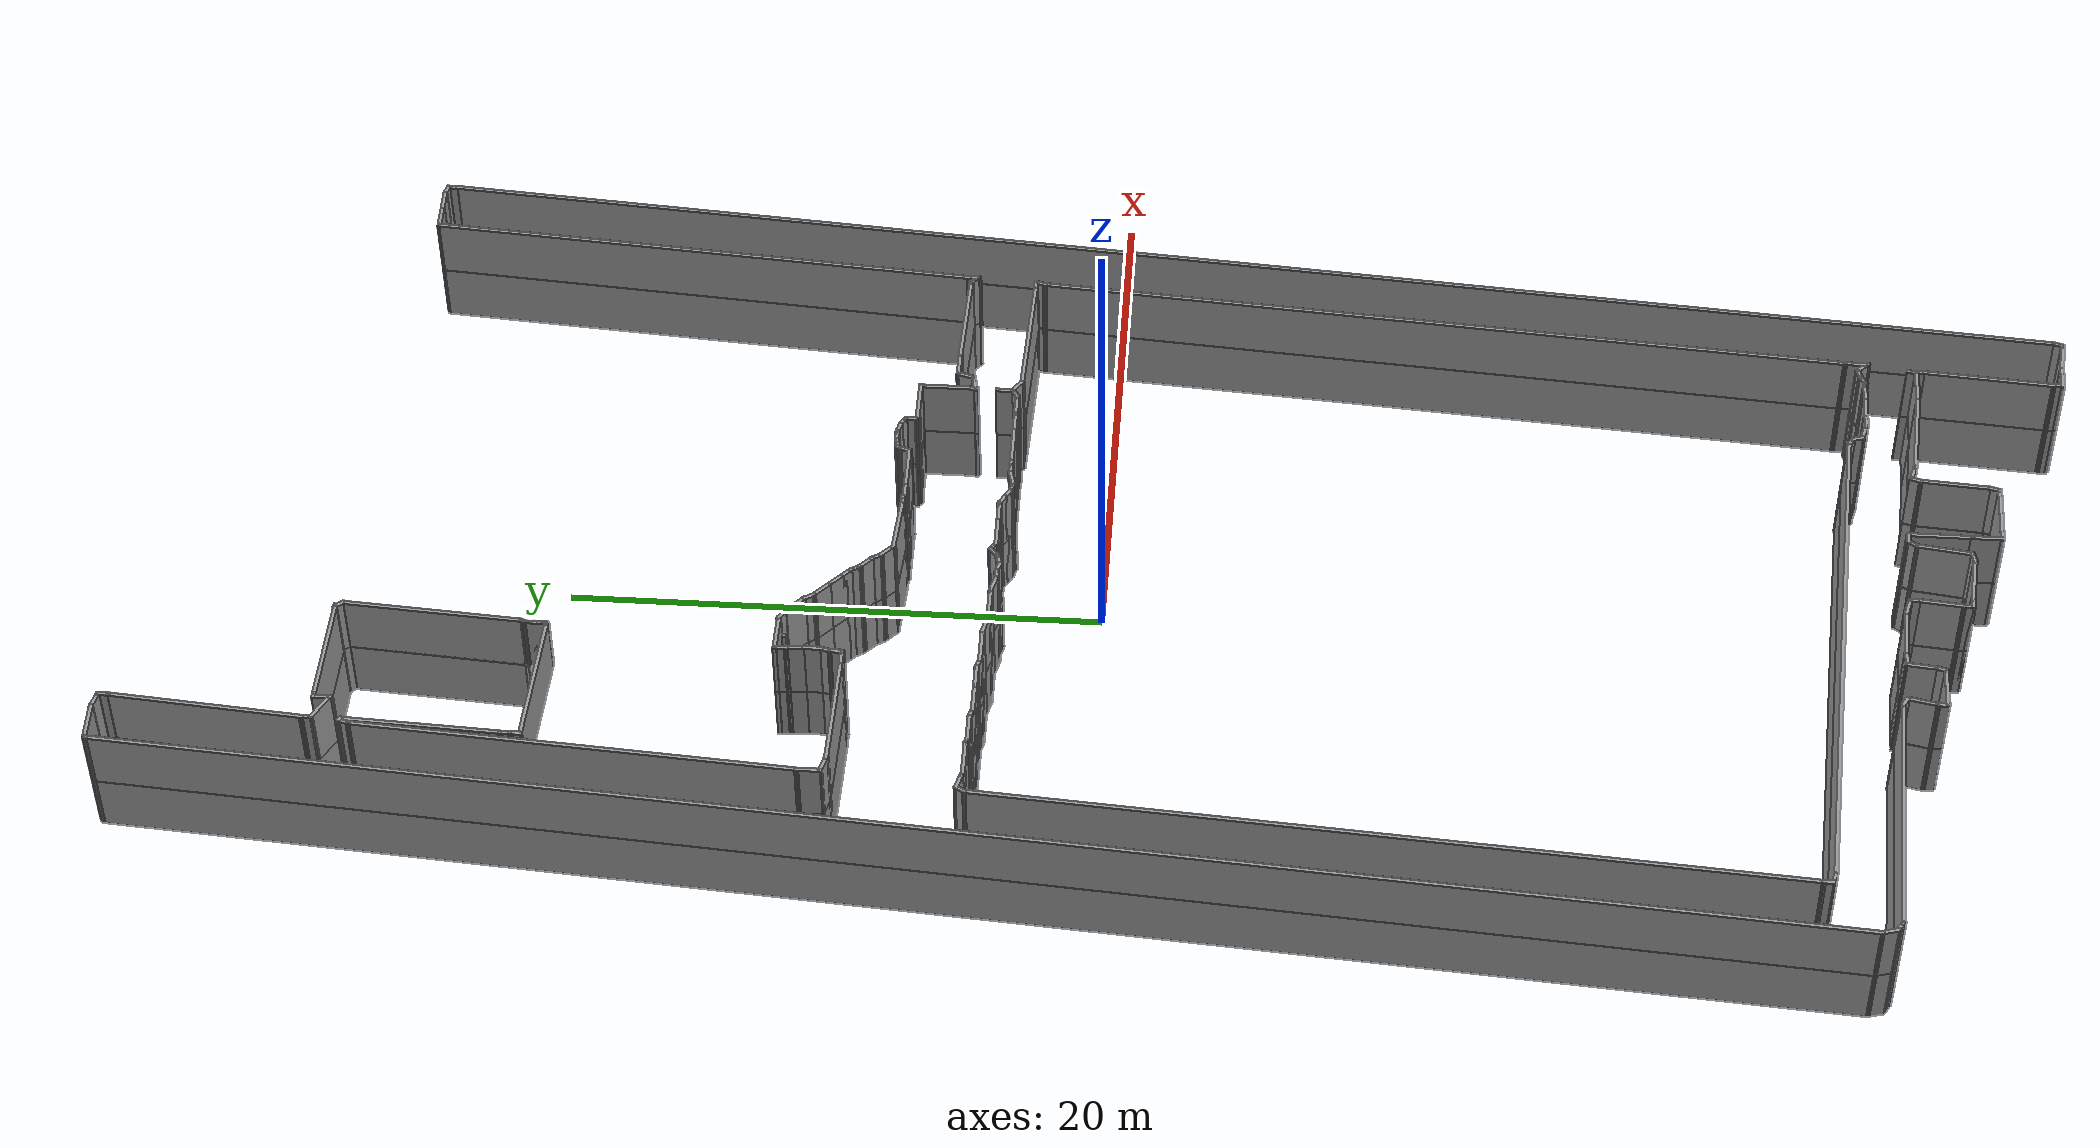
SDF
<?xml version='1.0'?>
<sdf version='1.7'>
  <model name='EnvDC01'>
    <link name='Floor_0'>
      <pose>0 0 2.5 0 -0 0</pose>
      <self_collide>0</self_collide>
      <enable_wind>0</enable_wind>
      <kinematic>0</kinematic>
      <gravity>1</gravity>
      <inertial>
        <mass>1</mass>
        <pose>0 0 0 0 -0 0</pose>
        <inertia>
          <ixx>1</ixx>
          <ixy>0</ixy>
          <ixz>0</ixz>
          <iyy>1</iyy>
          <iyz>0</iyz>
          <izz>1</izz>
        </inertia>
      </inertial>
      <collision name='Floor_0_Collision'>
        <laser_retro>0</laser_retro>
        <max_contacts>10</max_contacts>
        <pose>0 0 0.05 0 -0 0</pose>
        <geometry>
          <box>
            <size>32.7353 71.8899 0.1</size>
          </box>
        </geometry>
        <surface>
          <friction>
            <ode>
              <mu>1</mu>
              <mu2>1</mu2>
              <fdir1>0 0 0</fdir1>
              <slip1>0</slip1>
              <slip2>0</slip2>
            </ode>
            <torsional>
              <coefficient>1</coefficient>
              <patch_radius>0</patch_radius>
              <surface_radius>0</surface_radius>
              <use_patch_radius>1</use_patch_radius>
              <ode>
                <slip>0</slip>
              </ode>
            </torsional>
          </friction>
          <bounce>
            <restitution_coefficient>0</restitution_coefficient>
            <threshold>1e+06</threshold>
          </bounce>
          <contact>
            <collide_without_contact>0</collide_without_contact>
            <collide_without_contact_bitmask>1</collide_without_contact_bitmask>
            <collide_bitmask>1</collide_bitmask>
            <ode>
              <soft_cfm>0</soft_cfm>
              <soft_erp>0.2</soft_erp>
              <kp>1e+13</kp>
              <kd>1</kd>
              <max_vel>0.01</max_vel>
              <min_depth>0</min_depth>
            </ode>
            <bullet>
              <split_impulse>1</split_impulse>
              <split_impulse_penetration_threshold>-0.01</split_impulse_penetration_threshold>
              <soft_cfm>0</soft_cfm>
              <soft_erp>0.2</soft_erp>
              <kp>1e+13</kp>
              <kd>1</kd>
            </bullet>
          </contact>
        </surface>
      </collision>
    </link>
    <link name='Wall_100'>
      <pose>-5.32892 11.2593 0 0 -0 0</pose>
      <self_collide>0</self_collide>
      <enable_wind>0</enable_wind>
      <kinematic>0</kinematic>
      <visual name='Wall_100_Visual'>
        <pose>0 0 1.25 0 -0 0</pose>
        <geometry>
          <box>
            <size>0.15 0.15 2.5</size>
          </box>
        </geometry>
        <material>
          <script>
            <uri>file://media/materials/scripts/gazebo.material</uri>
            <name>Gazebo/Grey</name>
          </script>
          <ambient>1 1 1 1</ambient>
          <shader type='pixel'/>
        </material>
        <meta>
          <layer>0</layer>
        </meta>
        <transparency>0</transparency>
        <cast_shadows>1</cast_shadows>
      </visual>
      <collision name='Wall_100_Collision'>
        <laser_retro>0</laser_retro>
        <max_contacts>10</max_contacts>
        <pose>0 0 1.25 0 -0 0</pose>
        <geometry>
          <box>
            <size>0.15 0.15 2.5</size>
          </box>
        </geometry>
        <surface>
          <friction>
            <ode>
              <mu>1</mu>
              <mu2>1</mu2>
              <fdir1>0 0 0</fdir1>
              <slip1>0</slip1>
              <slip2>0</slip2>
            </ode>
            <torsional>
              <coefficient>1</coefficient>
              <patch_radius>0</patch_radius>
              <surface_radius>0</surface_radius>
              <use_patch_radius>1</use_patch_radius>
              <ode>
                <slip>0</slip>
              </ode>
            </torsional>
          </friction>
          <bounce>
            <restitution_coefficient>0</restitution_coefficient>
            <threshold>1e+06</threshold>
          </bounce>
          <contact>
            <collide_without_contact>0</collide_without_contact>
            <collide_without_contact_bitmask>1</collide_without_contact_bitmask>
            <collide_bitmask>1</collide_bitmask>
            <ode>
              <soft_cfm>0</soft_cfm>
              <soft_erp>0.2</soft_erp>
              <kp>1e+13</kp>
              <kd>1</kd>
              <max_vel>0.01</max_vel>
              <min_depth>0</min_depth>
            </ode>
            <bullet>
              <split_impulse>1</split_impulse>
              <split_impulse_penetration_threshold>-0.01</split_impulse_penetration_threshold>
              <soft_cfm>0</soft_cfm>
              <soft_erp>0.2</soft_erp>
              <kp>1e+13</kp>
              <kd>1</kd>
            </bullet>
          </contact>
        </surface>
      </collision>
    </link>
    <link name='Wall_102'>
      <pose>-5.88941 11.3173 0 0 0 -1.5708</pose>
      <self_collide>0</self_collide>
      <enable_wind>0</enable_wind>
      <kinematic>0</kinematic>
      <visual name='Wall_102_Visual'>
        <pose>0 0 1.25 0 -0 0</pose>
        <geometry>
          <box>
            <size>0.5 0.15 2.5</size>
          </box>
        </geometry>
        <material>
          <script>
            <uri>file://media/materials/scripts/gazebo.material</uri>
            <name>Gazebo/Grey</name>
          </script>
          <ambient>1 1 1 1</ambient>
          <shader type='pixel'/>
        </material>
        <meta>
          <layer>0</layer>
        </meta>
        <transparency>0</transparency>
        <cast_shadows>1</cast_shadows>
      </visual>
      <collision name='Wall_102_Collision'>
        <laser_retro>0</laser_retro>
        <max_contacts>10</max_contacts>
        <pose>0 0 1.25 0 -0 0</pose>
        <geometry>
          <box>
            <size>0.5 0.15 2.5</size>
          </box>
        </geometry>
        <surface>
          <friction>
            <ode>
              <mu>1</mu>
              <mu2>1</mu2>
              <fdir1>0 0 0</fdir1>
              <slip1>0</slip1>
              <slip2>0</slip2>
            </ode>
            <torsional>
              <coefficient>1</coefficient>
              <patch_radius>0</patch_radius>
              <surface_radius>0</surface_radius>
              <use_patch_radius>1</use_patch_radius>
              <ode>
                <slip>0</slip>
              </ode>
            </torsional>
          </friction>
          <bounce>
            <restitution_coefficient>0</restitution_coefficient>
            <threshold>1e+06</threshold>
          </bounce>
          <contact>
            <collide_without_contact>0</collide_without_contact>
            <collide_without_contact_bitmask>1</collide_without_contact_bitmask>
            <collide_bitmask>1</collide_bitmask>
            <ode>
              <soft_cfm>0</soft_cfm>
              <soft_erp>0.2</soft_erp>
              <kp>1e+13</kp>
              <kd>1</kd>
              <max_vel>0.01</max_vel>
              <min_depth>0</min_depth>
            </ode>
            <bullet>
              <split_impulse>1</split_impulse>
              <split_impulse_penetration_threshold>-0.01</split_impulse_penetration_threshold>
              <soft_cfm>0</soft_cfm>
              <soft_erp>0.2</soft_erp>
              <kp>1e+13</kp>
              <kd>1</kd>
            </bullet>
          </contact>
        </surface>
      </collision>
    </link>
    <link name='Wall_103'>
      <pose>-5.86023 10.8116 0 0 0 -1.48755</pose>
      <self_collide>0</self_collide>
      <enable_wind>0</enable_wind>
      <kinematic>0</kinematic>
      <visual name='Wall_103_Visual'>
        <pose>0 0 1.25 0 -0 0</pose>
        <geometry>
          <box>
            <size>0.813803 0.15 2.5</size>
          </box>
        </geometry>
        <material>
          <script>
            <uri>file://media/materials/scripts/gazebo.material</uri>
            <name>Gazebo/Grey</name>
          </script>
          <ambient>1 1 1 1</ambient>
          <shader type='pixel'/>
        </material>
        <meta>
          <layer>0</layer>
        </meta>
        <transparency>0</transparency>
        <cast_shadows>1</cast_shadows>
      </visual>
      <collision name='Wall_103_Collision'>
        <laser_retro>0</laser_retro>
        <max_contacts>10</max_contacts>
        <pose>0 0 1.25 0 -0 0</pose>
        <geometry>
          <box>
            <size>0.813803 0.15 2.5</size>
          </box>
        </geometry>
        <surface>
          <friction>
            <ode>
              <mu>1</mu>
              <mu2>1</mu2>
              <fdir1>0 0 0</fdir1>
              <slip1>0</slip1>
              <slip2>0</slip2>
            </ode>
            <torsional>
              <coefficient>1</coefficient>
              <patch_radius>0</patch_radius>
              <surface_radius>0</surface_radius>
              <use_patch_radius>1</use_patch_radius>
              <ode>
                <slip>0</slip>
              </ode>
            </torsional>
          </friction>
          <bounce>
            <restitution_coefficient>0</restitution_coefficient>
            <threshold>1e+06</threshold>
          </bounce>
          <contact>
            <collide_without_contact>0</collide_without_contact>
            <collide_without_contact_bitmask>1</collide_without_contact_bitmask>
            <collide_bitmask>1</collide_bitmask>
            <ode>
              <soft_cfm>0</soft_cfm>
              <soft_erp>0.2</soft_erp>
              <kp>1e+13</kp>
              <kd>1</kd>
              <max_vel>0.01</max_vel>
              <min_depth>0</min_depth>
            </ode>
            <bullet>
              <split_impulse>1</split_impulse>
              <split_impulse_penetration_threshold>-0.01</split_impulse_penetration_threshold>
              <soft_cfm>0</soft_cfm>
              <soft_erp>0.2</soft_erp>
              <kp>1e+13</kp>
              <kd>1</kd>
            </bullet>
          </contact>
        </surface>
      </collision>
    </link>
    <link name='Wall_104'>
      <pose>-5.83264 10.1793 0 0 0 -1.5708</pose>
      <self_collide>0</self_collide>
      <enable_wind>0</enable_wind>
      <kinematic>0</kinematic>
      <visual name='Wall_104_Visual'>
        <pose>0 0 1.25 0 -0 0</pose>
        <geometry>
          <box>
            <size>0.75 0.15 2.5</size>
          </box>
        </geometry>
        <material>
          <script>
            <uri>file://media/materials/scripts/gazebo.material</uri>
            <name>Gazebo/Grey</name>
          </script>
          <ambient>1 1 1 1</ambient>
          <shader type='pixel'/>
        </material>
        <meta>
          <layer>0</layer>
        </meta>
        <transparency>0</transparency>
        <cast_shadows>1</cast_shadows>
      </visual>
      <collision name='Wall_104_Collision'>
        <laser_retro>0</laser_retro>
        <max_contacts>10</max_contacts>
        <pose>0 0 1.25 0 -0 0</pose>
        <geometry>
          <box>
            <size>0.75 0.15 2.5</size>
          </box>
        </geometry>
        <surface>
          <friction>
            <ode>
              <mu>1</mu>
              <mu2>1</mu2>
              <fdir1>0 0 0</fdir1>
              <slip1>0</slip1>
              <slip2>0</slip2>
            </ode>
            <torsional>
              <coefficient>1</coefficient>
              <patch_radius>0</patch_radius>
              <surface_radius>0</surface_radius>
              <use_patch_radius>1</use_patch_radius>
              <ode>
                <slip>0</slip>
              </ode>
            </torsional>
          </friction>
          <bounce>
            <restitution_coefficient>0</restitution_coefficient>
            <threshold>1e+06</threshold>
          </bounce>
          <contact>
            <collide_without_contact>0</collide_without_contact>
            <collide_without_contact_bitmask>1</collide_without_contact_bitmask>
            <collide_bitmask>1</collide_bitmask>
            <ode>
              <soft_cfm>0</soft_cfm>
              <soft_erp>0.2</soft_erp>
              <kp>1e+13</kp>
              <kd>1</kd>
              <max_vel>0.01</max_vel>
              <min_depth>0</min_depth>
            </ode>
            <bullet>
              <split_impulse>1</split_impulse>
              <split_impulse_penetration_threshold>-0.01</split_impulse_penetration_threshold>
              <soft_cfm>0</soft_cfm>
              <soft_erp>0.2</soft_erp>
              <kp>1e+13</kp>
              <kd>1</kd>
            </bullet>
          </contact>
        </surface>
      </collision>
    </link>
    <link name='Wall_105'>
      <pose>-5.87793 9.70942 0 0 0 -1.83143</pose>
      <self_collide>0</self_collide>
      <enable_wind>0</enable_wind>
      <kinematic>0</kinematic>
      <visual name='Wall_105_Visual'>
        <pose>0 0 1.25 0 -0 0</pose>
        <geometry>
          <box>
            <size>0.501524 0.15 2.5</size>
          </box>
        </geometry>
        <material>
          <script>
            <uri>file://media/materials/scripts/gazebo.material</uri>
            <name>Gazebo/Grey</name>
          </script>
          <ambient>1 1 1 1</ambient>
          <shader type='pixel'/>
        </material>
        <meta>
          <layer>0</layer>
        </meta>
        <transparency>0</transparency>
        <cast_shadows>1</cast_shadows>
      </visual>
      <collision name='Wall_105_Collision'>
        <laser_retro>0</laser_retro>
        <max_contacts>10</max_contacts>
        <pose>0 0 1.25 0 -0 0</pose>
        <geometry>
          <box>
            <size>0.501524 0.15 2.5</size>
          </box>
        </geometry>
        <surface>
          <friction>
            <ode>
              <mu>1</mu>
              <mu2>1</mu2>
              <fdir1>0 0 0</fdir1>
              <slip1>0</slip1>
              <slip2>0</slip2>
            </ode>
            <torsional>
              <coefficient>1</coefficient>
              <patch_radius>0</patch_radius>
              <surface_radius>0</surface_radius>
              <use_patch_radius>1</use_patch_radius>
              <ode>
                <slip>0</slip>
              </ode>
            </torsional>
          </friction>
          <bounce>
            <restitution_coefficient>0</restitution_coefficient>
            <threshold>1e+06</threshold>
          </bounce>
          <contact>
            <collide_without_contact>0</collide_without_contact>
            <collide_without_contact_bitmask>1</collide_without_contact_bitmask>
            <collide_bitmask>1</collide_bitmask>
            <ode>
              <soft_cfm>0</soft_cfm>
              <soft_erp>0.2</soft_erp>
              <kp>1e+13</kp>
              <kd>1</kd>
              <max_vel>0.01</max_vel>
              <min_depth>0</min_depth>
            </ode>
            <bullet>
              <split_impulse>1</split_impulse>
              <split_impulse_penetration_threshold>-0.01</split_impulse_penetration_threshold>
              <soft_cfm>0</soft_cfm>
              <soft_erp>0.2</soft_erp>
              <kp>1e+13</kp>
              <kd>1</kd>
            </bullet>
          </contact>
        </surface>
      </collision>
    </link>
    <link name='Wall_106'>
      <pose>-5.92322 9.3646 0 0 0 -1.5708</pose>
      <self_collide>0</self_collide>
      <enable_wind>0</enable_wind>
      <kinematic>0</kinematic>
      <visual name='Wall_106_Visual'>
        <pose>0 0 1.25 0 -0 0</pose>
        <geometry>
          <box>
            <size>0.5 0.15 2.5</size>
          </box>
        </geometry>
        <material>
          <script>
            <uri>file://media/materials/scripts/gazebo.material</uri>
            <name>Gazebo/Grey</name>
          </script>
          <ambient>1 1 1 1</ambient>
          <shader type='pixel'/>
        </material>
        <meta>
          <layer>0</layer>
        </meta>
        <transparency>0</transparency>
        <cast_shadows>1</cast_shadows>
      </visual>
      <collision name='Wall_106_Collision'>
        <laser_retro>0</laser_retro>
        <max_contacts>10</max_contacts>
        <pose>0 0 1.25 0 -0 0</pose>
        <geometry>
          <box>
            <size>0.5 0.15 2.5</size>
          </box>
        </geometry>
        <surface>
          <friction>
            <ode>
              <mu>1</mu>
              <mu2>1</mu2>
              <fdir1>0 0 0</fdir1>
              <slip1>0</slip1>
              <slip2>0</slip2>
            </ode>
            <torsional>
              <coefficient>1</coefficient>
              <patch_radius>0</patch_radius>
              <surface_radius>0</surface_radius>
              <use_patch_radius>1</use_patch_radius>
              <ode>
                <slip>0</slip>
              </ode>
            </torsional>
          </friction>
          <bounce>
            <restitution_coefficient>0</restitution_coefficient>
            <threshold>1e+06</threshold>
          </bounce>
          <contact>
            <collide_without_contact>0</collide_without_contact>
            <collide_without_contact_bitmask>1</collide_without_contact_bitmask>
            <collide_bitmask>1</collide_bitmask>
            <ode>
              <soft_cfm>0</soft_cfm>
              <soft_erp>0.2</soft_erp>
              <kp>1e+13</kp>
              <kd>1</kd>
              <max_vel>0.01</max_vel>
              <min_depth>0</min_depth>
            </ode>
            <bullet>
              <split_impulse>1</split_impulse>
              <split_impulse_penetration_threshold>-0.01</split_impulse_penetration_threshold>
              <soft_cfm>0</soft_cfm>
              <soft_erp>0.2</soft_erp>
              <kp>1e+13</kp>
              <kd>1</kd>
            </bullet>
          </contact>
        </surface>
      </collision>
    </link>
    <link name='Wall_107'>
      <pose>-5.93616 9.1413 0 0 0 -1.8326</pose>
      <self_collide>0</self_collide>
      <enable_wind>0</enable_wind>
      <kinematic>0</kinematic>
      <visual name='Wall_107_Visual'>
        <pose>0 0 1.25 0 -0 0</pose>
        <geometry>
          <box>
            <size>0.25 0.15 2.5</size>
          </box>
        </geometry>
        <material>
          <script>
            <uri>file://media/materials/scripts/gazebo.material</uri>
            <name>Gazebo/Grey</name>
          </script>
          <ambient>1 1 1 1</ambient>
          <shader type='pixel'/>
        </material>
        <meta>
          <layer>0</layer>
        </meta>
        <transparency>0</transparency>
        <cast_shadows>1</cast_shadows>
      </visual>
      <collision name='Wall_107_Collision'>
        <laser_retro>0</laser_retro>
        <max_contacts>10</max_contacts>
        <pose>0 0 1.25 0 -0 0</pose>
        <geometry>
          <box>
            <size>0.25 0.15 2.5</size>
          </box>
        </geometry>
        <surface>
          <friction>
            <ode>
              <mu>1</mu>
              <mu2>1</mu2>
              <fdir1>0 0 0</fdir1>
              <slip1>0</slip1>
              <slip2>0</slip2>
            </ode>
            <torsional>
              <coefficient>1</coefficient>
              <patch_radius>0</patch_radius>
              <surface_radius>0</surface_radius>
              <use_patch_radius>1</use_patch_radius>
              <ode>
                <slip>0</slip>
              </ode>
            </torsional>
          </friction>
          <bounce>
            <restitution_coefficient>0</restitution_coefficient>
            <threshold>1e+06</threshold>
          </bounce>
          <contact>
            <collide_without_contact>0</collide_without_contact>
            <collide_without_contact_bitmask>1</collide_without_contact_bitmask>
            <collide_bitmask>1</collide_bitmask>
            <ode>
              <soft_cfm>0</soft_cfm>
              <soft_erp>0.2</soft_erp>
              <kp>1e+13</kp>
              <kd>1</kd>
              <max_vel>0.01</max_vel>
              <min_depth>0</min_depth>
            </ode>
            <bullet>
              <split_impulse>1</split_impulse>
              <split_impulse_penetration_threshold>-0.01</split_impulse_penetration_threshold>
              <soft_cfm>0</soft_cfm>
              <soft_erp>0.2</soft_erp>
              <kp>1e+13</kp>
              <kd>1</kd>
            </bullet>
          </contact>
        </surface>
      </collision>
    </link>
    <link name='Wall_108'>
      <pose>-6.24911 9.09509 0 0 -0 3.13464</pose>
      <self_collide>0</self_collide>
      <enable_wind>0</enable_wind>
      <kinematic>0</kinematic>
      <visual name='Wall_108_Visual'>
        <pose>0 0 1.25 0 -0 0</pose>
        <geometry>
          <box>
            <size>0.75 0.15 2.5</size>
          </box>
        </geometry>
        <material>
          <script>
            <uri>file://media/materials/scripts/gazebo.material</uri>
            <name>Gazebo/Grey</name>
          </script>
          <ambient>1 1 1 1</ambient>
          <shader type='pixel'/>
        </material>
        <meta>
          <layer>0</layer>
        </meta>
        <transparency>0</transparency>
        <cast_shadows>1</cast_shadows>
      </visual>
      <collision name='Wall_108_Collision'>
        <laser_retro>0</laser_retro>
        <max_contacts>10</max_contacts>
        <pose>0 0 1.25 0 -0 0</pose>
        <geometry>
          <box>
            <size>0.75 0.15 2.5</size>
          </box>
        </geometry>
        <surface>
          <friction>
            <ode>
              <mu>1</mu>
              <mu2>1</mu2>
              <fdir1>0 0 0</fdir1>
              <slip1>0</slip1>
              <slip2>0</slip2>
            </ode>
            <torsional>
              <coefficient>1</coefficient>
              <patch_radius>0</patch_radius>
              <surface_radius>0</surface_radius>
              <use_patch_radius>1</use_patch_radius>
              <ode>
                <slip>0</slip>
              </ode>
            </torsional>
          </friction>
          <bounce>
            <restitution_coefficient>0</restitution_coefficient>
            <threshold>1e+06</threshold>
          </bounce>
          <contact>
            <collide_without_contact>0</collide_without_contact>
            <collide_without_contact_bitmask>1</collide_without_contact_bitmask>
            <collide_bitmask>1</collide_bitmask>
            <ode>
              <soft_cfm>0</soft_cfm>
              <soft_erp>0.2</soft_erp>
              <kp>1e+13</kp>
              <kd>1</kd>
              <max_vel>0.01</max_vel>
              <min_depth>0</min_depth>
            </ode>
            <bullet>
              <split_impulse>1</split_impulse>
              <split_impulse_penetration_threshold>-0.01</split_impulse_penetration_threshold>
              <soft_cfm>0</soft_cfm>
              <soft_erp>0.2</soft_erp>
              <kp>1e+13</kp>
              <kd>1</kd>
            </bullet>
          </contact>
        </surface>
      </collision>
    </link>
    <link name='Wall_111'>
      <pose>-8.68398 9.16284 0 0 -0 3.11085</pose>
      <self_collide>0</self_collide>
      <enable_wind>0</enable_wind>
      <kinematic>0</kinematic>
      <visual name='Wall_111_Visual'>
        <pose>0 0 1.25 0 -0 0</pose>
        <geometry>
          <box>
            <size>4.42177 0.15 2.5</size>
          </box>
        </geometry>
        <material>
          <script>
            <uri>file://media/materials/scripts/gazebo.material</uri>
            <name>Gazebo/Grey</name>
          </script>
          <ambient>1 1 1 1</ambient>
          <shader type='pixel'/>
        </material>
        <meta>
          <layer>0</layer>
        </meta>
        <transparency>0</transparency>
        <cast_shadows>1</cast_shadows>
      </visual>
      <collision name='Wall_111_Collision'>
        <laser_retro>0</laser_retro>
        <max_contacts>10</max_contacts>
        <pose>0 0 1.25 0 -0 0</pose>
        <geometry>
          <box>
            <size>4.42177 0.15 2.5</size>
          </box>
        </geometry>
        <surface>
          <friction>
            <ode>
              <mu>1</mu>
              <mu2>1</mu2>
              <fdir1>0 0 0</fdir1>
              <slip1>0</slip1>
              <slip2>0</slip2>
            </ode>
            <torsional>
              <coefficient>1</coefficient>
              <patch_radius>0</patch_radius>
              <surface_radius>0</surface_radius>
              <use_patch_radius>1</use_patch_radius>
              <ode>
                <slip>0</slip>
              </ode>
            </torsional>
          </friction>
          <bounce>
            <restitution_coefficient>0</restitution_coefficient>
            <threshold>1e+06</threshold>
          </bounce>
          <contact>
            <collide_without_contact>0</collide_without_contact>
            <collide_without_contact_bitmask>1</collide_without_contact_bitmask>
            <collide_bitmask>1</collide_bitmask>
            <ode>
              <soft_cfm>0</soft_cfm>
              <soft_erp>0.2</soft_erp>
              <kp>1e+13</kp>
              <kd>1</kd>
              <max_vel>0.01</max_vel>
              <min_depth>0</min_depth>
            </ode>
            <bullet>
              <split_impulse>1</split_impulse>
              <split_impulse_penetration_threshold>-0.01</split_impulse_penetration_threshold>
              <soft_cfm>0</soft_cfm>
              <soft_erp>0.2</soft_erp>
              <kp>1e+13</kp>
              <kd>1</kd>
            </bullet>
          </contact>
        </surface>
      </collision>
    </link>
    <link name='Wall_112'>
      <pose>-11.1086 9.30614 0 0 -0 2.87979</pose>
      <self_collide>0</self_collide>
      <enable_wind>0</enable_wind>
      <kinematic>0</kinematic>
      <visual name='Wall_112_Visual'>
        <pose>0 0 1.25 0 -0 0</pose>
        <geometry>
          <box>
            <size>0.75 0.15 2.5</size>
          </box>
        </geometry>
        <material>
          <script>
            <uri>file://media/materials/scripts/gazebo.material</uri>
            <name>Gazebo/Grey</name>
          </script>
          <ambient>1 1 1 1</ambient>
          <shader type='pixel'/>
        </material>
        <meta>
          <layer>0</layer>
        </meta>
        <transparency>0</transparency>
        <cast_shadows>1</cast_shadows>
      </visual>
      <collision name='Wall_112_Collision'>
        <laser_retro>0</laser_retro>
        <max_contacts>10</max_contacts>
        <pose>0 0 1.25 0 -0 0</pose>
        <geometry>
          <box>
            <size>0.75 0.15 2.5</size>
          </box>
        </geometry>
        <surface>
          <friction>
            <ode>
              <mu>1</mu>
              <mu2>1</mu2>
              <fdir1>0 0 0</fdir1>
              <slip1>0</slip1>
              <slip2>0</slip2>
            </ode>
            <torsional>
              <coefficient>1</coefficient>
              <patch_radius>0</patch_radius>
              <surface_radius>0</surface_radius>
              <use_patch_radius>1</use_patch_radius>
              <ode>
                <slip>0</slip>
              </ode>
            </torsional>
          </friction>
          <bounce>
            <restitution_coefficient>0</restitution_coefficient>
            <threshold>1e+06</threshold>
          </bounce>
          <contact>
            <collide_without_contact>0</collide_without_contact>
            <collide_without_contact_bitmask>1</collide_without_contact_bitmask>
            <collide_bitmask>1</collide_bitmask>
            <ode>
              <soft_cfm>0</soft_cfm>
              <soft_erp>0.2</soft_erp>
              <kp>1e+13</kp>
              <kd>1</kd>
              <max_vel>0.01</max_vel>
              <min_depth>0</min_depth>
            </ode>
            <bullet>
              <split_impulse>1</split_impulse>
              <split_impulse_penetration_threshold>-0.01</split_impulse_penetration_threshold>
              <soft_cfm>0</soft_cfm>
              <soft_erp>0.2</soft_erp>
              <kp>1e+13</kp>
              <kd>1</kd>
            </bullet>
          </contact>
        </surface>
      </collision>
    </link>
    <link name='Wall_114'>
      <pose>-10.2177 26.6696 0 0 0 -1.8326</pose>
      <self_collide>0</self_collide>
      <enable_wind>0</enable_wind>
      <kinematic>0</kinematic>
      <visual name='Wall_114_Visual'>
        <pose>0 0 1.25 0 -0 0</pose>
        <geometry>
          <box>
            <size>0.5 0.15 2.5</size>
          </box>
        </geometry>
        <material>
          <script>
            <uri>file://media/materials/scripts/gazebo.material</uri>
            <name>Gazebo/Grey</name>
          </script>
          <ambient>1 1 1 1</ambient>
          <shader type='pixel'/>
        </material>
        <meta>
          <layer>0</layer>
        </meta>
        <transparency>0</transparency>
        <cast_shadows>1</cast_shadows>
      </visual>
      <collision name='Wall_114_Collision'>
        <laser_retro>0</laser_retro>
        <max_contacts>10</max_contacts>
        <pose>0 0 1.25 0 -0 0</pose>
        <geometry>
          <box>
            <size>0.5 0.15 2.5</size>
          </box>
        </geometry>
        <surface>
          <friction>
            <ode>
              <mu>1</mu>
              <mu2>1</mu2>
              <fdir1>0 0 0</fdir1>
              <slip1>0</slip1>
              <slip2>0</slip2>
            </ode>
            <torsional>
              <coefficient>1</coefficient>
              <patch_radius>0</patch_radius>
              <surface_radius>0</surface_radius>
              <use_patch_radius>1</use_patch_radius>
              <ode>
                <slip>0</slip>
              </ode>
            </torsional>
          </friction>
          <bounce>
            <restitution_coefficient>0</restitution_coefficient>
            <threshold>1e+06</threshold>
          </bounce>
          <contact>
            <collide_without_contact>0</collide_without_contact>
            <collide_without_contact_bitmask>1</collide_without_contact_bitmask>
            <collide_bitmask>1</collide_bitmask>
            <ode>
              <soft_cfm>0</soft_cfm>
              <soft_erp>0.2</soft_erp>
              <kp>1e+13</kp>
              <kd>1</kd>
              <max_vel>0.01</max_vel>
              <min_depth>0</min_depth>
            </ode>
            <bullet>
              <split_impulse>1</split_impulse>
              <split_impulse_penetration_threshold>-0.01</split_impulse_penetration_threshold>
              <soft_cfm>0</soft_cfm>
              <soft_erp>0.2</soft_erp>
              <kp>1e+13</kp>
              <kd>1</kd>
            </bullet>
          </contact>
        </surface>
      </collision>
    </link>
    <link name='Wall_115'>
      <pose>-10.8307 18.3672 0 0 0 -1.64048</pose>
      <self_collide>0</self_collide>
      <enable_wind>0</enable_wind>
      <kinematic>0</kinematic>
      <visual name='Wall_115_Visual'>
        <pose>0 0 1.25 0 -0 0</pose>
        <geometry>
          <box>
            <size>16.4563 0.15 2.5</size>
          </box>
        </geometry>
        <material>
          <script>
            <uri>file://media/materials/scripts/gazebo.material</uri>
            <name>Gazebo/Grey</name>
          </script>
          <ambient>1 1 1 1</ambient>
          <shader type='pixel'/>
        </material>
        <meta>
          <layer>0</layer>
        </meta>
        <transparency>0</transparency>
        <cast_shadows>1</cast_shadows>
      </visual>
      <collision name='Wall_115_Collision'>
        <laser_retro>0</laser_retro>
        <max_contacts>10</max_contacts>
        <pose>0 0 1.25 0 -0 0</pose>
        <geometry>
          <box>
            <size>16.4563 0.15 2.5</size>
          </box>
        </geometry>
        <surface>
          <friction>
            <ode>
              <mu>1</mu>
              <mu2>1</mu2>
              <fdir1>0 0 0</fdir1>
              <slip1>0</slip1>
              <slip2>0</slip2>
            </ode>
            <torsional>
              <coefficient>1</coefficient>
              <patch_radius>0</patch_radius>
              <surface_radius>0</surface_radius>
              <use_patch_radius>1</use_patch_radius>
              <ode>
                <slip>0</slip>
              </ode>
            </torsional>
          </friction>
          <bounce>
            <restitution_coefficient>0</restitution_coefficient>
            <threshold>1e+06</threshold>
          </bounce>
          <contact>
            <collide_without_contact>0</collide_without_contact>
            <collide_without_contact_bitmask>1</collide_without_contact_bitmask>
            <collide_bitmask>1</collide_bitmask>
            <ode>
              <soft_cfm>0</soft_cfm>
              <soft_erp>0.2</soft_erp>
              <kp>1e+13</kp>
              <kd>1</kd>
              <max_vel>0.01</max_vel>
              <min_depth>0</min_depth>
            </ode>
            <bullet>
              <split_impulse>1</split_impulse>
              <split_impulse_penetration_threshold>-0.01</split_impulse_penetration_threshold>
              <soft_cfm>0</soft_cfm>
              <soft_erp>0.2</soft_erp>
              <kp>1e+13</kp>
              <kd>1</kd>
            </bullet>
          </contact>
        </surface>
      </collision>
    </link>
    <link name='Wall_116'>
      <pose>-11.3984 9.80879 0 0 0 -1.5708</pose>
      <self_collide>0</self_collide>
      <enable_wind>0</enable_wind>
      <kinematic>0</kinematic>
      <visual name='Wall_116_Visual'>
        <pose>0 0 1.25 0 -0 0</pose>
        <geometry>
          <box>
            <size>1 0.15 2.5</size>
          </box>
        </geometry>
        <material>
          <script>
            <uri>file://media/materials/scripts/gazebo.material</uri>
            <name>Gazebo/Grey</name>
          </script>
          <ambient>1 1 1 1</ambient>
          <shader type='pixel'/>
        </material>
        <meta>
          <layer>0</layer>
        </meta>
        <transparency>0</transparency>
        <cast_shadows>1</cast_shadows>
      </visual>
      <collision name='Wall_116_Collision'>
        <laser_retro>0</laser_retro>
        <max_contacts>10</max_contacts>
        <pose>0 0 1.25 0 -0 0</pose>
        <geometry>
          <box>
            <size>1 0.15 2.5</size>
          </box>
        </geometry>
        <surface>
          <friction>
            <ode>
              <mu>1</mu>
              <mu2>1</mu2>
              <fdir1>0 0 0</fdir1>
              <slip1>0</slip1>
              <slip2>0</slip2>
            </ode>
            <torsional>
              <coefficient>1</coefficient>
              <patch_radius>0</patch_radius>
              <surface_radius>0</surface_radius>
              <use_patch_radius>1</use_patch_radius>
              <ode>
                <slip>0</slip>
              </ode>
            </torsional>
          </friction>
          <bounce>
            <restitution_coefficient>0</restitution_coefficient>
            <threshold>1e+06</threshold>
          </bounce>
          <contact>
            <collide_without_contact>0</collide_without_contact>
            <collide_without_contact_bitmask>1</collide_without_contact_bitmask>
            <collide_bitmask>1</collide_bitmask>
            <ode>
              <soft_cfm>0</soft_cfm>
              <soft_erp>0.2</soft_erp>
              <kp>1e+13</kp>
              <kd>1</kd>
              <max_vel>0.01</max_vel>
              <min_depth>0</min_depth>
            </ode>
            <bullet>
              <split_impulse>1</split_impulse>
              <split_impulse_penetration_threshold>-0.01</split_impulse_penetration_threshold>
              <soft_cfm>0</soft_cfm>
              <soft_erp>0.2</soft_erp>
              <kp>1e+13</kp>
              <kd>1</kd>
            </bullet>
          </contact>
        </surface>
      </collision>
    </link>
    <link name='Wall_118'>
      <pose>-10.0854 28.0428 0 0 -0 1.5708</pose>
      <self_collide>0</self_collide>
      <enable_wind>0</enable_wind>
      <kinematic>0</kinematic>
      <visual name='Wall_118_Visual'>
        <pose>0 0 1.25 0 -0 0</pose>
        <geometry>
          <box>
            <size>0.5 0.15 2.5</size>
          </box>
        </geometry>
        <material>
          <script>
            <uri>file://media/materials/scripts/gazebo.material</uri>
            <name>Gazebo/Grey</name>
          </script>
          <ambient>1 1 1 1</ambient>
          <shader type='pixel'/>
        </material>
        <meta>
          <layer>0</layer>
        </meta>
        <transparency>0</transparency>
        <cast_shadows>1</cast_shadows>
      </visual>
      <collision name='Wall_118_Collision'>
        <laser_retro>0</laser_retro>
        <max_contacts>10</max_contacts>
        <pose>0 0 1.25 0 -0 0</pose>
        <geometry>
          <box>
            <size>0.5 0.15 2.5</size>
          </box>
        </geometry>
        <surface>
          <friction>
            <ode>
              <mu>1</mu>
              <mu2>1</mu2>
              <fdir1>0 0 0</fdir1>
              <slip1>0</slip1>
              <slip2>0</slip2>
            </ode>
            <torsional>
              <coefficient>1</coefficient>
              <patch_radius>0</patch_radius>
              <surface_radius>0</surface_radius>
              <use_patch_radius>1</use_patch_radius>
              <ode>
                <slip>0</slip>
              </ode>
            </torsional>
          </friction>
          <bounce>
            <restitution_coefficient>0</restitution_coefficient>
            <threshold>1e+06</threshold>
          </bounce>
          <contact>
            <collide_without_contact>0</collide_without_contact>
            <collide_without_contact_bitmask>1</collide_without_contact_bitmask>
            <collide_bitmask>1</collide_bitmask>
            <ode>
              <soft_cfm>0</soft_cfm>
              <soft_erp>0.2</soft_erp>
              <kp>1e+13</kp>
              <kd>1</kd>
              <max_vel>0.01</max_vel>
              <min_depth>0</min_depth>
            </ode>
            <bullet>
              <split_impulse>1</split_impulse>
              <split_impulse_penetration_threshold>-0.01</split_impulse_penetration_threshold>
              <soft_cfm>0</soft_cfm>
              <soft_erp>0.2</soft_erp>
              <kp>1e+13</kp>
              <kd>1</kd>
            </bullet>
          </contact>
        </surface>
      </collision>
    </link>
    <link name='Wall_119'>
      <pose>-9.78492 31.7757 0 0 -0 1.48653</pose>
      <self_collide>0</self_collide>
      <enable_wind>0</enable_wind>
      <kinematic>0</kinematic>
      <visual name='Wall_119_Visual'>
        <pose>0 0 1.25 0 -0 0</pose>
        <geometry>
          <box>
            <size>7.29114 0.15 2.5</size>
          </box>
        </geometry>
        <material>
          <script>
            <uri>file://media/materials/scripts/gazebo.material</uri>
            <name>Gazebo/Grey</name>
          </script>
          <ambient>1 1 1 1</ambient>
          <shader type='pixel'/>
        </material>
        <meta>
          <layer>0</layer>
        </meta>
        <transparency>0</transparency>
        <cast_shadows>1</cast_shadows>
      </visual>
      <collision name='Wall_119_Collision'>
        <laser_retro>0</laser_retro>
        <max_contacts>10</max_contacts>
        <pose>0 0 1.25 0 -0 0</pose>
        <geometry>
          <box>
            <size>7.29114 0.15 2.5</size>
          </box>
        </geometry>
        <surface>
          <friction>
            <ode>
              <mu>1</mu>
              <mu2>1</mu2>
              <fdir1>0 0 0</fdir1>
              <slip1>0</slip1>
              <slip2>0</slip2>
            </ode>
            <torsional>
              <coefficient>1</coefficient>
              <patch_radius>0</patch_radius>
              <surface_radius>0</surface_radius>
              <use_patch_radius>1</use_patch_radius>
              <ode>
                <slip>0</slip>
              </ode>
            </torsional>
          </friction>
          <bounce>
            <restitution_coefficient>0</restitution_coefficient>
            <threshold>1e+06</threshold>
          </bounce>
          <contact>
            <collide_without_contact>0</collide_without_contact>
            <collide_without_contact_bitmask>1</collide_without_contact_bitmask>
            <collide_bitmask>1</collide_bitmask>
            <ode>
              <soft_cfm>0</soft_cfm>
              <soft_erp>0.2</soft_erp>
              <kp>1e+13</kp>
              <kd>1</kd>
              <max_vel>0.01</max_vel>
              <min_depth>0</min_depth>
            </ode>
            <bullet>
              <split_impulse>1</split_impulse>
              <split_impulse_penetration_threshold>-0.01</split_impulse_penetration_threshold>
              <soft_cfm>0</soft_cfm>
              <soft_erp>0.2</soft_erp>
              <kp>1e+13</kp>
              <kd>1</kd>
            </bullet>
          </contact>
        </surface>
      </collision>
    </link>
    <link name='Wall_120'>
      <pose>-9.4844 35.5086 0 0 -0 1.5708</pose>
      <self_collide>0</self_collide>
      <enable_wind>0</enable_wind>
      <kinematic>0</kinematic>
      <visual name='Wall_120_Visual'>
        <pose>0 0 1.25 0 -0 0</pose>
        <geometry>
          <box>
            <size>0.5 0.15 2.5</size>
          </box>
        </geometry>
        <material>
          <script>
            <uri>file://media/materials/scripts/gazebo.material</uri>
            <name>Gazebo/Grey</name>
          </script>
          <ambient>1 1 1 1</ambient>
          <shader type='pixel'/>
        </material>
        <meta>
          <layer>0</layer>
        </meta>
        <transparency>0</transparency>
        <cast_shadows>1</cast_shadows>
      </visual>
      <collision name='Wall_120_Collision'>
        <laser_retro>0</laser_retro>
        <max_contacts>10</max_contacts>
        <pose>0 0 1.25 0 -0 0</pose>
        <geometry>
          <box>
            <size>0.5 0.15 2.5</size>
          </box>
        </geometry>
        <surface>
          <friction>
            <ode>
              <mu>1</mu>
              <mu2>1</mu2>
              <fdir1>0 0 0</fdir1>
              <slip1>0</slip1>
              <slip2>0</slip2>
            </ode>
            <torsional>
              <coefficient>1</coefficient>
              <patch_radius>0</patch_radius>
              <surface_radius>0</surface_radius>
              <use_patch_radius>1</use_patch_radius>
              <ode>
                <slip>0</slip>
              </ode>
            </torsional>
          </friction>
          <bounce>
            <restitution_coefficient>0</restitution_coefficient>
            <threshold>1e+06</threshold>
          </bounce>
          <contact>
            <collide_without_contact>0</collide_without_contact>
            <collide_without_contact_bitmask>1</collide_without_contact_bitmask>
            <collide_bitmask>1</collide_bitmask>
            <ode>
              <soft_cfm>0</soft_cfm>
              <soft_erp>0.2</soft_erp>
              <kp>1e+13</kp>
              <kd>1</kd>
              <max_vel>0.01</max_vel>
              <min_depth>0</min_depth>
            </ode>
            <bullet>
              <split_impulse>1</split_impulse>
              <split_impulse_penetration_threshold>-0.01</split_impulse_penetration_threshold>
              <soft_cfm>0</soft_cfm>
              <soft_erp>0.2</soft_erp>
              <kp>1e+13</kp>
              <kd>1</kd>
            </bullet>
          </contact>
        </surface>
      </collision>
    </link>
    <link name='Wall_122'>
      <pose>-9.77418 35.7612 0 0 -0 2.87979</pose>
      <self_collide>0</self_collide>
      <enable_wind>0</enable_wind>
      <kinematic>0</kinematic>
      <visual name='Wall_122_Visual'>
        <pose>0 0 1.25 0 -0 0</pose>
        <geometry>
          <box>
            <size>0.75 0.15 2.5</size>
          </box>
        </geometry>
        <material>
          <script>
            <uri>file://media/materials/scripts/gazebo.material</uri>
            <name>Gazebo/Grey</name>
          </script>
          <ambient>1 1 1 1</ambient>
          <shader type='pixel'/>
        </material>
        <meta>
          <layer>0</layer>
        </meta>
        <transparency>0</transparency>
        <cast_shadows>1</cast_shadows>
      </visual>
      <collision name='Wall_122_Collision'>
        <laser_retro>0</laser_retro>
        <max_contacts>10</max_contacts>
        <pose>0 0 1.25 0 -0 0</pose>
        <geometry>
          <box>
            <size>0.75 0.15 2.5</size>
          </box>
        </geometry>
        <surface>
          <friction>
            <ode>
              <mu>1</mu>
              <mu2>1</mu2>
              <fdir1>0 0 0</fdir1>
              <slip1>0</slip1>
              <slip2>0</slip2>
            </ode>
            <torsional>
              <coefficient>1</coefficient>
              <patch_radius>0</patch_radius>
              <surface_radius>0</surface_radius>
              <use_patch_radius>1</use_patch_radius>
              <ode>
                <slip>0</slip>
              </ode>
            </torsional>
          </friction>
          <bounce>
            <restitution_coefficient>0</restitution_coefficient>
            <threshold>1e+06</threshold>
          </bounce>
          <contact>
            <collide_without_contact>0</collide_without_contact>
            <collide_without_contact_bitmask>1</collide_without_contact_bitmask>
            <collide_bitmask>1</collide_bitmask>
            <ode>
              <soft_cfm>0</soft_cfm>
              <soft_erp>0.2</soft_erp>
              <kp>1e+13</kp>
              <kd>1</kd>
              <max_vel>0.01</max_vel>
              <min_depth>0</min_depth>
            </ode>
            <bullet>
              <split_impulse>1</split_impulse>
              <split_impulse_penetration_threshold>-0.01</split_impulse_penetration_threshold>
              <soft_cfm>0</soft_cfm>
              <soft_erp>0.2</soft_erp>
              <kp>1e+13</kp>
              <kd>1</kd>
            </bullet>
          </contact>
        </surface>
      </collision>
    </link>
    <link name='Wall_123'>
      <pose>-10.739 35.8389 0 0 -0 3.14159</pose>
      <self_collide>0</self_collide>
      <enable_wind>0</enable_wind>
      <kinematic>0</kinematic>
      <visual name='Wall_123_Visual'>
        <pose>0 0 1.25 0 -0 0</pose>
        <geometry>
          <box>
            <size>1.5 0.15 2.5</size>
          </box>
        </geometry>
        <material>
          <script>
            <uri>file://media/materials/scripts/gazebo.material</uri>
            <name>Gazebo/Grey</name>
          </script>
          <ambient>1 1 1 1</ambient>
          <shader type='pixel'/>
        </material>
        <meta>
          <layer>0</layer>
        </meta>
        <transparency>0</transparency>
        <cast_shadows>1</cast_shadows>
      </visual>
      <collision name='Wall_123_Collision'>
        <laser_retro>0</laser_retro>
        <max_contacts>10</max_contacts>
        <pose>0 0 1.25 0 -0 0</pose>
        <geometry>
          <box>
            <size>1.5 0.15 2.5</size>
          </box>
        </geometry>
        <surface>
          <friction>
            <ode>
              <mu>1</mu>
              <mu2>1</mu2>
              <fdir1>0 0 0</fdir1>
              <slip1>0</slip1>
              <slip2>0</slip2>
            </ode>
            <torsional>
              <coefficient>1</coefficient>
              <patch_radius>0</patch_radius>
              <surface_radius>0</surface_radius>
              <use_patch_radius>1</use_patch_radius>
              <ode>
                <slip>0</slip>
              </ode>
            </torsional>
          </friction>
          <bounce>
            <restitution_coefficient>0</restitution_coefficient>
            <threshold>1e+06</threshold>
          </bounce>
          <contact>
            <collide_without_contact>0</collide_without_contact>
            <collide_without_contact_bitmask>1</collide_without_contact_bitmask>
            <collide_bitmask>1</collide_bitmask>
            <ode>
              <soft_cfm>0</soft_cfm>
              <soft_erp>0.2</soft_erp>
              <kp>1e+13</kp>
              <kd>1</kd>
              <max_vel>0.01</max_vel>
              <min_depth>0</min_depth>
            </ode>
            <bullet>
              <split_impulse>1</split_impulse>
              <split_impulse_penetration_threshold>-0.01</split_impulse_penetration_threshold>
              <soft_cfm>0</soft_cfm>
              <soft_erp>0.2</soft_erp>
              <kp>1e+13</kp>
              <kd>1</kd>
            </bullet>
          </contact>
        </surface>
      </collision>
    </link>
    <link name='Wall_124'>
      <pose>-11.4493 35.8035 0 0 0 -2.35619</pose>
      <self_collide>0</self_collide>
      <enable_wind>0</enable_wind>
      <kinematic>0</kinematic>
      <visual name='Wall_124_Visual'>
        <pose>0 0 1.25 0 -0 0</pose>
        <geometry>
          <box>
            <size>0.25 0.15 2.5</size>
          </box>
        </geometry>
        <material>
          <script>
            <uri>file://media/materials/scripts/gazebo.material</uri>
            <name>Gazebo/Grey</name>
          </script>
          <ambient>1 1 1 1</ambient>
          <shader type='pixel'/>
        </material>
        <meta>
          <layer>0</layer>
        </meta>
        <transparency>0</transparency>
        <cast_shadows>1</cast_shadows>
      </visual>
      <collision name='Wall_124_Collision'>
        <laser_retro>0</laser_retro>
        <max_contacts>10</max_contacts>
        <pose>0 0 1.25 0 -0 0</pose>
        <geometry>
          <box>
            <size>0.25 0.15 2.5</size>
          </box>
        </geometry>
        <surface>
          <friction>
            <ode>
              <mu>1</mu>
              <mu2>1</mu2>
              <fdir1>0 0 0</fdir1>
              <slip1>0</slip1>
              <slip2>0</slip2>
            </ode>
            <torsional>
              <coefficient>1</coefficient>
              <patch_radius>0</patch_radius>
              <surface_radius>0</surface_radius>
              <use_patch_radius>1</use_patch_radius>
              <ode>
                <slip>0</slip>
              </ode>
            </torsional>
          </friction>
          <bounce>
            <restitution_coefficient>0</restitution_coefficient>
            <threshold>1e+06</threshold>
          </bounce>
          <contact>
            <collide_without_contact>0</collide_without_contact>
            <collide_without_contact_bitmask>1</collide_without_contact_bitmask>
            <collide_bitmask>1</collide_bitmask>
            <ode>
              <soft_cfm>0</soft_cfm>
              <soft_erp>0.2</soft_erp>
              <kp>1e+13</kp>
              <kd>1</kd>
              <max_vel>0.01</max_vel>
              <min_depth>0</min_depth>
            </ode>
            <bullet>
              <split_impulse>1</split_impulse>
              <split_impulse_penetration_threshold>-0.01</split_impulse_penetration_threshold>
              <soft_cfm>0</soft_cfm>
              <soft_erp>0.2</soft_erp>
              <kp>1e+13</kp>
              <kd>1</kd>
            </bullet>
          </contact>
        </surface>
      </collision>
    </link>
    <link name='Wall_128'>
      <pose>-13.8802 3.78282 0 0 0 -1.64555</pose>
      <self_collide>0</self_collide>
      <enable_wind>0</enable_wind>
      <kinematic>0</kinematic>
      <visual name='Wall_128_Visual'>
        <pose>0 0 1.25 0 -0 0</pose>
        <geometry>
          <box>
            <size>64.2999 0.15 2.5</size>
          </box>
        </geometry>
        <material>
          <script>
            <uri>file://media/materials/scripts/gazebo.material</uri>
            <name>Gazebo/Grey</name>
          </script>
          <ambient>1 1 1 1</ambient>
          <shader type='pixel'/>
        </material>
        <meta>
          <layer>0</layer>
        </meta>
        <transparency>0</transparency>
        <cast_shadows>1</cast_shadows>
      </visual>
      <collision name='Wall_128_Collision'>
        <laser_retro>0</laser_retro>
        <max_contacts>10</max_contacts>
        <pose>0 0 1.25 0 -0 0</pose>
        <geometry>
          <box>
            <size>64.2999 0.15 2.5</size>
          </box>
        </geometry>
        <surface>
          <friction>
            <ode>
              <mu>1</mu>
              <mu2>1</mu2>
              <fdir1>0 0 0</fdir1>
              <slip1>0</slip1>
              <slip2>0</slip2>
            </ode>
            <torsional>
              <coefficient>1</coefficient>
              <patch_radius>0</patch_radius>
              <surface_radius>0</surface_radius>
              <use_patch_radius>1</use_patch_radius>
              <ode>
                <slip>0</slip>
              </ode>
            </torsional>
          </friction>
          <bounce>
            <restitution_coefficient>0</restitution_coefficient>
            <threshold>1e+06</threshold>
          </bounce>
          <contact>
            <collide_without_contact>0</collide_without_contact>
            <collide_without_contact_bitmask>1</collide_without_contact_bitmask>
            <collide_bitmask>1</collide_bitmask>
            <ode>
              <soft_cfm>0</soft_cfm>
              <soft_erp>0.2</soft_erp>
              <kp>1e+13</kp>
              <kd>1</kd>
              <max_vel>0.01</max_vel>
              <min_depth>0</min_depth>
            </ode>
            <bullet>
              <split_impulse>1</split_impulse>
              <split_impulse_penetration_threshold>-0.01</split_impulse_penetration_threshold>
              <soft_cfm>0</soft_cfm>
              <soft_erp>0.2</soft_erp>
              <kp>1e+13</kp>
              <kd>1</kd>
            </bullet>
          </contact>
        </surface>
      </collision>
    </link>
    <link name='Wall_130'>
      <pose>-16.1981 -28.4923 0 0 -0 1.8326</pose>
      <self_collide>0</self_collide>
      <enable_wind>0</enable_wind>
      <kinematic>0</kinematic>
      <visual name='Wall_130_Visual'>
        <pose>0 0 1.25 0 -0 0</pose>
        <geometry>
          <box>
            <size>0.75 0.15 2.5</size>
          </box>
        </geometry>
        <material>
          <script>
            <uri>file://media/materials/scripts/gazebo.material</uri>
            <name>Gazebo/Grey</name>
          </script>
          <ambient>1 1 1 1</ambient>
          <shader type='pixel'/>
        </material>
        <meta>
          <layer>0</layer>
        </meta>
        <transparency>0</transparency>
        <cast_shadows>1</cast_shadows>
      </visual>
      <collision name='Wall_130_Collision'>
        <laser_retro>0</laser_retro>
        <max_contacts>10</max_contacts>
        <pose>0 0 1.25 0 -0 0</pose>
        <geometry>
          <box>
            <size>0.75 0.15 2.5</size>
          </box>
        </geometry>
        <surface>
          <friction>
            <ode>
              <mu>1</mu>
              <mu2>1</mu2>
              <fdir1>0 0 0</fdir1>
              <slip1>0</slip1>
              <slip2>0</slip2>
            </ode>
            <torsional>
              <coefficient>1</coefficient>
              <patch_radius>0</patch_radius>
              <surface_radius>0</surface_radius>
              <use_patch_radius>1</use_patch_radius>
              <ode>
                <slip>0</slip>
              </ode>
            </torsional>
          </friction>
          <bounce>
            <restitution_coefficient>0</restitution_coefficient>
            <threshold>1e+06</threshold>
          </bounce>
          <contact>
            <collide_without_contact>0</collide_without_contact>
            <collide_without_contact_bitmask>1</collide_without_contact_bitmask>
            <collide_bitmask>1</collide_bitmask>
            <ode>
              <soft_cfm>0</soft_cfm>
              <soft_erp>0.2</soft_erp>
              <kp>1e+13</kp>
              <kd>1</kd>
              <max_vel>0.01</max_vel>
              <min_depth>0</min_depth>
            </ode>
            <bullet>
              <split_impulse>1</split_impulse>
              <split_impulse_penetration_threshold>-0.01</split_impulse_penetration_threshold>
              <soft_cfm>0</soft_cfm>
              <soft_erp>0.2</soft_erp>
              <kp>1e+13</kp>
              <kd>1</kd>
            </bullet>
          </contact>
        </surface>
      </collision>
    </link>
    <link name='Wall_133'>
      <pose>12.4484 3.28154 0 0 -0 3.14159</pose>
      <self_collide>0</self_collide>
      <enable_wind>0</enable_wind>
      <kinematic>0</kinematic>
      <visual name='Wall_133_Visual'>
        <pose>0 0 1.25 0 -0 0</pose>
        <geometry>
          <box>
            <size>0.5 0.15 2.5</size>
          </box>
        </geometry>
        <material>
          <script>
            <uri>file://media/materials/scripts/gazebo.material</uri>
            <name>Gazebo/Grey</name>
          </script>
          <ambient>1 1 1 1</ambient>
          <shader type='pixel'/>
        </material>
        <meta>
          <layer>0</layer>
        </meta>
        <transparency>0</transparency>
        <cast_shadows>1</cast_shadows>
      </visual>
      <collision name='Wall_133_Collision'>
        <laser_retro>0</laser_retro>
        <max_contacts>10</max_contacts>
        <pose>0 0 1.25 0 -0 0</pose>
        <geometry>
          <box>
            <size>0.5 0.15 2.5</size>
          </box>
        </geometry>
        <surface>
          <friction>
            <ode>
              <mu>1</mu>
              <mu2>1</mu2>
              <fdir1>0 0 0</fdir1>
              <slip1>0</slip1>
              <slip2>0</slip2>
            </ode>
            <torsional>
              <coefficient>1</coefficient>
              <patch_radius>0</patch_radius>
              <surface_radius>0</surface_radius>
              <use_patch_radius>1</use_patch_radius>
              <ode>
                <slip>0</slip>
              </ode>
            </torsional>
          </friction>
          <bounce>
            <restitution_coefficient>0</restitution_coefficient>
            <threshold>1e+06</threshold>
          </bounce>
          <contact>
            <collide_without_contact>0</collide_without_contact>
            <collide_without_contact_bitmask>1</collide_without_contact_bitmask>
            <collide_bitmask>1</collide_bitmask>
            <ode>
              <soft_cfm>0</soft_cfm>
              <soft_erp>0.2</soft_erp>
              <kp>1e+13</kp>
              <kd>1</kd>
              <max_vel>0.01</max_vel>
              <min_depth>0</min_depth>
            </ode>
            <bullet>
              <split_impulse>1</split_impulse>
              <split_impulse_penetration_threshold>-0.01</split_impulse_penetration_threshold>
              <soft_cfm>0</soft_cfm>
              <soft_erp>0.2</soft_erp>
              <kp>1e+13</kp>
              <kd>1</kd>
            </bullet>
          </contact>
        </surface>
      </collision>
    </link>
    <link name='Wall_134'>
      <pose>9.8712 3.37676 0 0 -0 3.10198</pose>
      <self_collide>0</self_collide>
      <enable_wind>0</enable_wind>
      <kinematic>0</kinematic>
      <visual name='Wall_134_Visual'>
        <pose>0 0 1.25 0 -0 0</pose>
        <geometry>
          <box>
            <size>4.9582 0.15 2.5</size>
          </box>
        </geometry>
        <material>
          <script>
            <uri>file://media/materials/scripts/gazebo.material</uri>
            <name>Gazebo/Grey</name>
          </script>
          <ambient>1 1 1 1</ambient>
          <shader type='pixel'/>
        </material>
        <meta>
          <layer>0</layer>
        </meta>
        <transparency>0</transparency>
        <cast_shadows>1</cast_shadows>
      </visual>
      <collision name='Wall_134_Collision'>
        <laser_retro>0</laser_retro>
        <max_contacts>10</max_contacts>
        <pose>0 0 1.25 0 -0 0</pose>
        <geometry>
          <box>
            <size>4.9582 0.15 2.5</size>
          </box>
        </geometry>
        <surface>
          <friction>
            <ode>
              <mu>1</mu>
              <mu2>1</mu2>
              <fdir1>0 0 0</fdir1>
              <slip1>0</slip1>
              <slip2>0</slip2>
            </ode>
            <torsional>
              <coefficient>1</coefficient>
              <patch_radius>0</patch_radius>
              <surface_radius>0</surface_radius>
              <use_patch_radius>1</use_patch_radius>
              <ode>
                <slip>0</slip>
              </ode>
            </torsional>
          </friction>
          <bounce>
            <restitution_coefficient>0</restitution_coefficient>
            <threshold>1e+06</threshold>
          </bounce>
          <contact>
            <collide_without_contact>0</collide_without_contact>
            <collide_without_contact_bitmask>1</collide_without_contact_bitmask>
            <collide_bitmask>1</collide_bitmask>
            <ode>
              <soft_cfm>0</soft_cfm>
              <soft_erp>0.2</soft_erp>
              <kp>1e+13</kp>
              <kd>1</kd>
              <max_vel>0.01</max_vel>
              <min_depth>0</min_depth>
            </ode>
            <bullet>
              <split_impulse>1</split_impulse>
              <split_impulse_penetration_threshold>-0.01</split_impulse_penetration_threshold>
              <soft_cfm>0</soft_cfm>
              <soft_erp>0.2</soft_erp>
              <kp>1e+13</kp>
              <kd>1</kd>
            </bullet>
          </contact>
        </surface>
      </collision>
    </link>
    <link name='Wall_135'>
      <pose>7.2977 3.59466 0 0 -0 2.52004</pose>
      <self_collide>0</self_collide>
      <enable_wind>0</enable_wind>
      <kinematic>0</kinematic>
      <visual name='Wall_135_Visual'>
        <pose>0 0 1.25 0 -0 0</pose>
        <geometry>
          <box>
            <size>0.571407 0.15 2.5</size>
          </box>
        </geometry>
        <material>
          <script>
            <uri>file://media/materials/scripts/gazebo.material</uri>
            <name>Gazebo/Grey</name>
          </script>
          <ambient>1 1 1 1</ambient>
          <shader type='pixel'/>
        </material>
        <meta>
          <layer>0</layer>
        </meta>
        <transparency>0</transparency>
        <cast_shadows>1</cast_shadows>
      </visual>
      <collision name='Wall_135_Collision'>
        <laser_retro>0</laser_retro>
        <max_contacts>10</max_contacts>
        <pose>0 0 1.25 0 -0 0</pose>
        <geometry>
          <box>
            <size>0.571407 0.15 2.5</size>
          </box>
        </geometry>
        <surface>
          <friction>
            <ode>
              <mu>1</mu>
              <mu2>1</mu2>
              <fdir1>0 0 0</fdir1>
              <slip1>0</slip1>
              <slip2>0</slip2>
            </ode>
            <torsional>
              <coefficient>1</coefficient>
              <patch_radius>0</patch_radius>
              <surface_radius>0</surface_radius>
              <use_patch_radius>1</use_patch_radius>
              <ode>
                <slip>0</slip>
              </ode>
            </torsional>
          </friction>
          <bounce>
            <restitution_coefficient>0</restitution_coefficient>
            <threshold>1e+06</threshold>
          </bounce>
          <contact>
            <collide_without_contact>0</collide_without_contact>
            <collide_without_contact_bitmask>1</collide_without_contact_bitmask>
            <collide_bitmask>1</collide_bitmask>
            <ode>
              <soft_cfm>0</soft_cfm>
              <soft_erp>0.2</soft_erp>
              <kp>1e+13</kp>
              <kd>1</kd>
              <max_vel>0.01</max_vel>
              <min_depth>0</min_depth>
            </ode>
            <bullet>
              <split_impulse>1</split_impulse>
              <split_impulse_penetration_threshold>-0.01</split_impulse_penetration_threshold>
              <soft_cfm>0</soft_cfm>
              <soft_erp>0.2</soft_erp>
              <kp>1e+13</kp>
              <kd>1</kd>
            </bullet>
          </contact>
        </surface>
      </collision>
    </link>
    <link name='Wall_142'>
      <pose>7.0376 4.07108 0 0 0 -1.5708</pose>
      <self_collide>0</self_collide>
      <enable_wind>0</enable_wind>
      <kinematic>0</kinematic>
      <visual name='Wall_142_Visual'>
        <pose>0 0 1.25 0 -0 0</pose>
        <geometry>
          <box>
            <size>0.75 0.15 2.5</size>
          </box>
        </geometry>
        <material>
          <script>
            <uri>file://media/materials/scripts/gazebo.material</uri>
            <name>Gazebo/Grey</name>
          </script>
          <ambient>1 1 1 1</ambient>
          <shader type='pixel'/>
        </material>
        <meta>
          <layer>0</layer>
        </meta>
        <transparency>0</transparency>
        <cast_shadows>1</cast_shadows>
      </visual>
      <collision name='Wall_142_Collision'>
        <laser_retro>0</laser_retro>
        <max_contacts>10</max_contacts>
        <pose>0 0 1.25 0 -0 0</pose>
        <geometry>
          <box>
            <size>0.75 0.15 2.5</size>
          </box>
        </geometry>
        <surface>
          <friction>
            <ode>
              <mu>1</mu>
              <mu2>1</mu2>
              <fdir1>0 0 0</fdir1>
              <slip1>0</slip1>
              <slip2>0</slip2>
            </ode>
            <torsional>
              <coefficient>1</coefficient>
              <patch_radius>0</patch_radius>
              <surface_radius>0</surface_radius>
              <use_patch_radius>1</use_patch_radius>
              <ode>
                <slip>0</slip>
              </ode>
            </torsional>
          </friction>
          <bounce>
            <restitution_coefficient>0</restitution_coefficient>
            <threshold>1e+06</threshold>
          </bounce>
          <contact>
            <collide_without_contact>0</collide_without_contact>
            <collide_without_contact_bitmask>1</collide_without_contact_bitmask>
            <collide_bitmask>1</collide_bitmask>
            <ode>
              <soft_cfm>0</soft_cfm>
              <soft_erp>0.2</soft_erp>
              <kp>1e+13</kp>
              <kd>1</kd>
              <max_vel>0.01</max_vel>
              <min_depth>0</min_depth>
            </ode>
            <bullet>
              <split_impulse>1</split_impulse>
              <split_impulse_penetration_threshold>-0.01</split_impulse_penetration_threshold>
              <soft_cfm>0</soft_cfm>
              <soft_erp>0.2</soft_erp>
              <kp>1e+13</kp>
              <kd>1</kd>
            </bullet>
          </contact>
        </surface>
      </collision>
    </link>
    <link name='Wall_143'>
      <pose>6.88604 3.68358 0 0 0 -2.61799</pose>
      <self_collide>0</self_collide>
      <enable_wind>0</enable_wind>
      <kinematic>0</kinematic>
      <visual name='Wall_143_Visual'>
        <pose>0 0 1.25 0 -0 0</pose>
        <geometry>
          <box>
            <size>0.5 0.15 2.5</size>
          </box>
        </geometry>
        <material>
          <script>
            <uri>file://media/materials/scripts/gazebo.material</uri>
            <name>Gazebo/Grey</name>
          </script>
          <ambient>1 1 1 1</ambient>
          <shader type='pixel'/>
        </material>
        <meta>
          <layer>0</layer>
        </meta>
        <transparency>0</transparency>
        <cast_shadows>1</cast_shadows>
      </visual>
      <collision name='Wall_143_Collision'>
        <laser_retro>0</laser_retro>
        <max_contacts>10</max_contacts>
        <pose>0 0 1.25 0 -0 0</pose>
        <geometry>
          <box>
            <size>0.5 0.15 2.5</size>
          </box>
        </geometry>
        <surface>
          <friction>
            <ode>
              <mu>1</mu>
              <mu2>1</mu2>
              <fdir1>0 0 0</fdir1>
              <slip1>0</slip1>
              <slip2>0</slip2>
            </ode>
            <torsional>
              <coefficient>1</coefficient>
              <patch_radius>0</patch_radius>
              <surface_radius>0</surface_radius>
              <use_patch_radius>1</use_patch_radius>
              <ode>
                <slip>0</slip>
              </ode>
            </torsional>
          </friction>
          <bounce>
            <restitution_coefficient>0</restitution_coefficient>
            <threshold>1e+06</threshold>
          </bounce>
          <contact>
            <collide_without_contact>0</collide_without_contact>
            <collide_without_contact_bitmask>1</collide_without_contact_bitmask>
            <collide_bitmask>1</collide_bitmask>
            <ode>
              <soft_cfm>0</soft_cfm>
              <soft_erp>0.2</soft_erp>
              <kp>1e+13</kp>
              <kd>1</kd>
              <max_vel>0.01</max_vel>
              <min_depth>0</min_depth>
            </ode>
            <bullet>
              <split_impulse>1</split_impulse>
              <split_impulse_penetration_threshold>-0.01</split_impulse_penetration_threshold>
              <soft_cfm>0</soft_cfm>
              <soft_erp>0.2</soft_erp>
              <kp>1e+13</kp>
              <kd>1</kd>
            </bullet>
          </contact>
        </surface>
      </collision>
    </link>
    <link name='Wall_144'>
      <pose>6.30949 3.59608 0 0 -0 3.14159</pose>
      <self_collide>0</self_collide>
      <enable_wind>0</enable_wind>
      <kinematic>0</kinematic>
      <visual name='Wall_144_Visual'>
        <pose>0 0 1.25 0 -0 0</pose>
        <geometry>
          <box>
            <size>1 0.15 2.5</size>
          </box>
        </geometry>
        <material>
          <script>
            <uri>file://media/materials/scripts/gazebo.material</uri>
            <name>Gazebo/Grey</name>
          </script>
          <ambient>1 1 1 1</ambient>
          <shader type='pixel'/>
        </material>
        <meta>
          <layer>0</layer>
        </meta>
        <transparency>0</transparency>
        <cast_shadows>1</cast_shadows>
      </visual>
      <collision name='Wall_144_Collision'>
        <laser_retro>0</laser_retro>
        <max_contacts>10</max_contacts>
        <pose>0 0 1.25 0 -0 0</pose>
        <geometry>
          <box>
            <size>1 0.15 2.5</size>
          </box>
        </geometry>
        <surface>
          <friction>
            <ode>
              <mu>1</mu>
              <mu2>1</mu2>
              <fdir1>0 0 0</fdir1>
              <slip1>0</slip1>
              <slip2>0</slip2>
            </ode>
            <torsional>
              <coefficient>1</coefficient>
              <patch_radius>0</patch_radius>
              <surface_radius>0</surface_radius>
              <use_patch_radius>1</use_patch_radius>
              <ode>
                <slip>0</slip>
              </ode>
            </torsional>
          </friction>
          <bounce>
            <restitution_coefficient>0</restitution_coefficient>
            <threshold>1e+06</threshold>
          </bounce>
          <contact>
            <collide_without_contact>0</collide_without_contact>
            <collide_without_contact_bitmask>1</collide_without_contact_bitmask>
            <collide_bitmask>1</collide_bitmask>
            <ode>
              <soft_cfm>0</soft_cfm>
              <soft_erp>0.2</soft_erp>
              <kp>1e+13</kp>
              <kd>1</kd>
              <max_vel>0.01</max_vel>
              <min_depth>0</min_depth>
            </ode>
            <bullet>
              <split_impulse>1</split_impulse>
              <split_impulse_penetration_threshold>-0.01</split_impulse_penetration_threshold>
              <soft_cfm>0</soft_cfm>
              <soft_erp>0.2</soft_erp>
              <kp>1e+13</kp>
              <kd>1</kd>
            </bullet>
          </contact>
        </surface>
      </collision>
    </link>
    <link name='Wall_146'>
      <pose>5.45949 3.59608 0 0 -0 3.14159</pose>
      <self_collide>0</self_collide>
      <enable_wind>0</enable_wind>
      <kinematic>0</kinematic>
      <visual name='Wall_146_Visual'>
        <pose>0 0 1.25 0 -0 0</pose>
        <geometry>
          <box>
            <size>1 0.15 2.5</size>
          </box>
        </geometry>
        <material>
          <script>
            <uri>file://media/materials/scripts/gazebo.material</uri>
            <name>Gazebo/Grey</name>
          </script>
          <ambient>1 1 1 1</ambient>
          <shader type='pixel'/>
        </material>
        <meta>
          <layer>0</layer>
        </meta>
        <transparency>0</transparency>
        <cast_shadows>1</cast_shadows>
      </visual>
      <collision name='Wall_146_Collision'>
        <laser_retro>0</laser_retro>
        <max_contacts>10</max_contacts>
        <pose>0 0 1.25 0 -0 0</pose>
        <geometry>
          <box>
            <size>1 0.15 2.5</size>
          </box>
        </geometry>
        <surface>
          <friction>
            <ode>
              <mu>1</mu>
              <mu2>1</mu2>
              <fdir1>0 0 0</fdir1>
              <slip1>0</slip1>
              <slip2>0</slip2>
            </ode>
            <torsional>
              <coefficient>1</coefficient>
              <patch_radius>0</patch_radius>
              <surface_radius>0</surface_radius>
              <use_patch_radius>1</use_patch_radius>
              <ode>
                <slip>0</slip>
              </ode>
            </torsional>
          </friction>
          <bounce>
            <restitution_coefficient>0</restitution_coefficient>
            <threshold>1e+06</threshold>
          </bounce>
          <contact>
            <collide_without_contact>0</collide_without_contact>
            <collide_without_contact_bitmask>1</collide_without_contact_bitmask>
            <collide_bitmask>1</collide_bitmask>
            <ode>
              <soft_cfm>0</soft_cfm>
              <soft_erp>0.2</soft_erp>
              <kp>1e+13</kp>
              <kd>1</kd>
              <max_vel>0.01</max_vel>
              <min_depth>0</min_depth>
            </ode>
            <bullet>
              <split_impulse>1</split_impulse>
              <split_impulse_penetration_threshold>-0.01</split_impulse_penetration_threshold>
              <soft_cfm>0</soft_cfm>
              <soft_erp>0.2</soft_erp>
              <kp>1e+13</kp>
              <kd>1</kd>
            </bullet>
          </contact>
        </surface>
      </collision>
    </link>
    <link name='Wall_147'>
      <pose>4.35949 3.59608 0 0 -0 3.14159</pose>
      <self_collide>0</self_collide>
      <enable_wind>0</enable_wind>
      <kinematic>0</kinematic>
      <visual name='Wall_147_Visual'>
        <pose>0 0 1.25 0 -0 0</pose>
        <geometry>
          <box>
            <size>1.5 0.15 2.5</size>
          </box>
        </geometry>
        <material>
          <script>
            <uri>file://media/materials/scripts/gazebo.material</uri>
            <name>Gazebo/Grey</name>
          </script>
          <ambient>1 1 1 1</ambient>
          <shader type='pixel'/>
        </material>
        <meta>
          <layer>0</layer>
        </meta>
        <transparency>0</transparency>
        <cast_shadows>1</cast_shadows>
      </visual>
      <collision name='Wall_147_Collision'>
        <laser_retro>0</laser_retro>
        <max_contacts>10</max_contacts>
        <pose>0 0 1.25 0 -0 0</pose>
        <geometry>
          <box>
            <size>1.5 0.15 2.5</size>
          </box>
        </geometry>
        <surface>
          <friction>
            <ode>
              <mu>1</mu>
              <mu2>1</mu2>
              <fdir1>0 0 0</fdir1>
              <slip1>0</slip1>
              <slip2>0</slip2>
            </ode>
            <torsional>
              <coefficient>1</coefficient>
              <patch_radius>0</patch_radius>
              <surface_radius>0</surface_radius>
              <use_patch_radius>1</use_patch_radius>
              <ode>
                <slip>0</slip>
              </ode>
            </torsional>
          </friction>
          <bounce>
            <restitution_coefficient>0</restitution_coefficient>
            <threshold>1e+06</threshold>
          </bounce>
          <contact>
            <collide_without_contact>0</collide_without_contact>
            <collide_without_contact_bitmask>1</collide_without_contact_bitmask>
            <collide_bitmask>1</collide_bitmask>
            <ode>
              <soft_cfm>0</soft_cfm>
              <soft_erp>0.2</soft_erp>
              <kp>1e+13</kp>
              <kd>1</kd>
              <max_vel>0.01</max_vel>
              <min_depth>0</min_depth>
            </ode>
            <bullet>
              <split_impulse>1</split_impulse>
              <split_impulse_penetration_threshold>-0.01</split_impulse_penetration_threshold>
              <soft_cfm>0</soft_cfm>
              <soft_erp>0.2</soft_erp>
              <kp>1e+13</kp>
              <kd>1</kd>
            </bullet>
          </contact>
        </surface>
      </collision>
    </link>
    <link name='Wall_148'>
      <pose>3.50949 3.59608 0 0 -0 3.14159</pose>
      <self_collide>0</self_collide>
      <enable_wind>0</enable_wind>
      <kinematic>0</kinematic>
      <visual name='Wall_148_Visual'>
        <pose>0 0 1.25 0 -0 0</pose>
        <geometry>
          <box>
            <size>0.5 0.15 2.5</size>
          </box>
        </geometry>
        <material>
          <script>
            <uri>file://media/materials/scripts/gazebo.material</uri>
            <name>Gazebo/Grey</name>
          </script>
          <ambient>1 1 1 1</ambient>
          <shader type='pixel'/>
        </material>
        <meta>
          <layer>0</layer>
        </meta>
        <transparency>0</transparency>
        <cast_shadows>1</cast_shadows>
      </visual>
      <collision name='Wall_148_Collision'>
        <laser_retro>0</laser_retro>
        <max_contacts>10</max_contacts>
        <pose>0 0 1.25 0 -0 0</pose>
        <geometry>
          <box>
            <size>0.5 0.15 2.5</size>
          </box>
        </geometry>
        <surface>
          <friction>
            <ode>
              <mu>1</mu>
              <mu2>1</mu2>
              <fdir1>0 0 0</fdir1>
              <slip1>0</slip1>
              <slip2>0</slip2>
            </ode>
            <torsional>
              <coefficient>1</coefficient>
              <patch_radius>0</patch_radius>
              <surface_radius>0</surface_radius>
              <use_patch_radius>1</use_patch_radius>
              <ode>
                <slip>0</slip>
              </ode>
            </torsional>
          </friction>
          <bounce>
            <restitution_coefficient>0</restitution_coefficient>
            <threshold>1e+06</threshold>
          </bounce>
          <contact>
            <collide_without_contact>0</collide_without_contact>
            <collide_without_contact_bitmask>1</collide_without_contact_bitmask>
            <collide_bitmask>1</collide_bitmask>
            <ode>
              <soft_cfm>0</soft_cfm>
              <soft_erp>0.2</soft_erp>
              <kp>1e+13</kp>
              <kd>1</kd>
              <max_vel>0.01</max_vel>
              <min_depth>0</min_depth>
            </ode>
            <bullet>
              <split_impulse>1</split_impulse>
              <split_impulse_penetration_threshold>-0.01</split_impulse_penetration_threshold>
              <soft_cfm>0</soft_cfm>
              <soft_erp>0.2</soft_erp>
              <kp>1e+13</kp>
              <kd>1</kd>
            </bullet>
          </contact>
        </surface>
      </collision>
    </link>
    <link name='Wall_149'>
      <pose>3.15949 3.59608 0 0 -0 3.14159</pose>
      <self_collide>0</self_collide>
      <enable_wind>0</enable_wind>
      <kinematic>0</kinematic>
      <visual name='Wall_149_Visual'>
        <pose>0 0 1.25 0 -0 0</pose>
        <geometry>
          <box>
            <size>0.5 0.15 2.5</size>
          </box>
        </geometry>
        <material>
          <script>
            <uri>file://media/materials/scripts/gazebo.material</uri>
            <name>Gazebo/Grey</name>
          </script>
          <ambient>1 1 1 1</ambient>
          <shader type='pixel'/>
        </material>
        <meta>
          <layer>0</layer>
        </meta>
        <transparency>0</transparency>
        <cast_shadows>1</cast_shadows>
      </visual>
      <collision name='Wall_149_Collision'>
        <laser_retro>0</laser_retro>
        <max_contacts>10</max_contacts>
        <pose>0 0 1.25 0 -0 0</pose>
        <geometry>
          <box>
            <size>0.5 0.15 2.5</size>
          </box>
        </geometry>
        <surface>
          <friction>
            <ode>
              <mu>1</mu>
              <mu2>1</mu2>
              <fdir1>0 0 0</fdir1>
              <slip1>0</slip1>
              <slip2>0</slip2>
            </ode>
            <torsional>
              <coefficient>1</coefficient>
              <patch_radius>0</patch_radius>
              <surface_radius>0</surface_radius>
              <use_patch_radius>1</use_patch_radius>
              <ode>
                <slip>0</slip>
              </ode>
            </torsional>
          </friction>
          <bounce>
            <restitution_coefficient>0</restitution_coefficient>
            <threshold>1e+06</threshold>
          </bounce>
          <contact>
            <collide_without_contact>0</collide_without_contact>
            <collide_without_contact_bitmask>1</collide_without_contact_bitmask>
            <collide_bitmask>1</collide_bitmask>
            <ode>
              <soft_cfm>0</soft_cfm>
              <soft_erp>0.2</soft_erp>
              <kp>1e+13</kp>
              <kd>1</kd>
              <max_vel>0.01</max_vel>
              <min_depth>0</min_depth>
            </ode>
            <bullet>
              <split_impulse>1</split_impulse>
              <split_impulse_penetration_threshold>-0.01</split_impulse_penetration_threshold>
              <soft_cfm>0</soft_cfm>
              <soft_erp>0.2</soft_erp>
              <kp>1e+13</kp>
              <kd>1</kd>
            </bullet>
          </contact>
        </surface>
      </collision>
    </link>
    <link name='Wall_150'>
      <pose>2.69471 3.51844 0 0 0 -2.87979</pose>
      <self_collide>0</self_collide>
      <enable_wind>0</enable_wind>
      <kinematic>0</kinematic>
      <visual name='Wall_150_Visual'>
        <pose>0 0 1.25 0 -0 0</pose>
        <geometry>
          <box>
            <size>0.75 0.15 2.5</size>
          </box>
        </geometry>
        <material>
          <script>
            <uri>file://media/materials/scripts/gazebo.material</uri>
            <name>Gazebo/Grey</name>
          </script>
          <ambient>1 1 1 1</ambient>
          <shader type='pixel'/>
        </material>
        <meta>
          <layer>0</layer>
        </meta>
        <transparency>0</transparency>
        <cast_shadows>1</cast_shadows>
      </visual>
      <collision name='Wall_150_Collision'>
        <laser_retro>0</laser_retro>
        <max_contacts>10</max_contacts>
        <pose>0 0 1.25 0 -0 0</pose>
        <geometry>
          <box>
            <size>0.75 0.15 2.5</size>
          </box>
        </geometry>
        <surface>
          <friction>
            <ode>
              <mu>1</mu>
              <mu2>1</mu2>
              <fdir1>0 0 0</fdir1>
              <slip1>0</slip1>
              <slip2>0</slip2>
            </ode>
            <torsional>
              <coefficient>1</coefficient>
              <patch_radius>0</patch_radius>
              <surface_radius>0</surface_radius>
              <use_patch_radius>1</use_patch_radius>
              <ode>
                <slip>0</slip>
              </ode>
            </torsional>
          </friction>
          <bounce>
            <restitution_coefficient>0</restitution_coefficient>
            <threshold>1e+06</threshold>
          </bounce>
          <contact>
            <collide_without_contact>0</collide_without_contact>
            <collide_without_contact_bitmask>1</collide_without_contact_bitmask>
            <collide_bitmask>1</collide_bitmask>
            <ode>
              <soft_cfm>0</soft_cfm>
              <soft_erp>0.2</soft_erp>
              <kp>1e+13</kp>
              <kd>1</kd>
              <max_vel>0.01</max_vel>
              <min_depth>0</min_depth>
            </ode>
            <bullet>
              <split_impulse>1</split_impulse>
              <split_impulse_penetration_threshold>-0.01</split_impulse_penetration_threshold>
              <soft_cfm>0</soft_cfm>
              <soft_erp>0.2</soft_erp>
              <kp>1e+13</kp>
              <kd>1</kd>
            </bullet>
          </contact>
        </surface>
      </collision>
    </link>
    <link name='Wall_151'>
      <pose>2.2359 3.48608 0 0 -0 2.87979</pose>
      <self_collide>0</self_collide>
      <enable_wind>0</enable_wind>
      <kinematic>0</kinematic>
      <visual name='Wall_151_Visual'>
        <pose>0 0 1.25 0 -0 0</pose>
        <geometry>
          <box>
            <size>0.5 0.15 2.5</size>
          </box>
        </geometry>
        <material>
          <script>
            <uri>file://media/materials/scripts/gazebo.material</uri>
            <name>Gazebo/Grey</name>
          </script>
          <ambient>1 1 1 1</ambient>
          <shader type='pixel'/>
        </material>
        <meta>
          <layer>0</layer>
        </meta>
        <transparency>0</transparency>
        <cast_shadows>1</cast_shadows>
      </visual>
      <collision name='Wall_151_Collision'>
        <laser_retro>0</laser_retro>
        <max_contacts>10</max_contacts>
        <pose>0 0 1.25 0 -0 0</pose>
        <geometry>
          <box>
            <size>0.5 0.15 2.5</size>
          </box>
        </geometry>
        <surface>
          <friction>
            <ode>
              <mu>1</mu>
              <mu2>1</mu2>
              <fdir1>0 0 0</fdir1>
              <slip1>0</slip1>
              <slip2>0</slip2>
            </ode>
            <torsional>
              <coefficient>1</coefficient>
              <patch_radius>0</patch_radius>
              <surface_radius>0</surface_radius>
              <use_patch_radius>1</use_patch_radius>
              <ode>
                <slip>0</slip>
              </ode>
            </torsional>
          </friction>
          <bounce>
            <restitution_coefficient>0</restitution_coefficient>
            <threshold>1e+06</threshold>
          </bounce>
          <contact>
            <collide_without_contact>0</collide_without_contact>
            <collide_without_contact_bitmask>1</collide_without_contact_bitmask>
            <collide_bitmask>1</collide_bitmask>
            <ode>
              <soft_cfm>0</soft_cfm>
              <soft_erp>0.2</soft_erp>
              <kp>1e+13</kp>
              <kd>1</kd>
              <max_vel>0.01</max_vel>
              <min_depth>0</min_depth>
            </ode>
            <bullet>
              <split_impulse>1</split_impulse>
              <split_impulse_penetration_threshold>-0.01</split_impulse_penetration_threshold>
              <soft_cfm>0</soft_cfm>
              <soft_erp>0.2</soft_erp>
              <kp>1e+13</kp>
              <kd>1</kd>
            </bullet>
          </contact>
        </surface>
      </collision>
    </link>
    <link name='Wall_152'>
      <pose>1.91531 3.61888 0 0 -0 2.61799</pose>
      <self_collide>0</self_collide>
      <enable_wind>0</enable_wind>
      <kinematic>0</kinematic>
      <visual name='Wall_152_Visual'>
        <pose>0 0 1.25 0 -0 0</pose>
        <geometry>
          <box>
            <size>0.5 0.15 2.5</size>
          </box>
        </geometry>
        <material>
          <script>
            <uri>file://media/materials/scripts/gazebo.material</uri>
            <name>Gazebo/Grey</name>
          </script>
          <ambient>1 1 1 1</ambient>
          <shader type='pixel'/>
        </material>
        <meta>
          <layer>0</layer>
        </meta>
        <transparency>0</transparency>
        <cast_shadows>1</cast_shadows>
      </visual>
      <collision name='Wall_152_Collision'>
        <laser_retro>0</laser_retro>
        <max_contacts>10</max_contacts>
        <pose>0 0 1.25 0 -0 0</pose>
        <geometry>
          <box>
            <size>0.5 0.15 2.5</size>
          </box>
        </geometry>
        <surface>
          <friction>
            <ode>
              <mu>1</mu>
              <mu2>1</mu2>
              <fdir1>0 0 0</fdir1>
              <slip1>0</slip1>
              <slip2>0</slip2>
            </ode>
            <torsional>
              <coefficient>1</coefficient>
              <patch_radius>0</patch_radius>
              <surface_radius>0</surface_radius>
              <use_patch_radius>1</use_patch_radius>
              <ode>
                <slip>0</slip>
              </ode>
            </torsional>
          </friction>
          <bounce>
            <restitution_coefficient>0</restitution_coefficient>
            <threshold>1e+06</threshold>
          </bounce>
          <contact>
            <collide_without_contact>0</collide_without_contact>
            <collide_without_contact_bitmask>1</collide_without_contact_bitmask>
            <collide_bitmask>1</collide_bitmask>
            <ode>
              <soft_cfm>0</soft_cfm>
              <soft_erp>0.2</soft_erp>
              <kp>1e+13</kp>
              <kd>1</kd>
              <max_vel>0.01</max_vel>
              <min_depth>0</min_depth>
            </ode>
            <bullet>
              <split_impulse>1</split_impulse>
              <split_impulse_penetration_threshold>-0.01</split_impulse_penetration_threshold>
              <soft_cfm>0</soft_cfm>
              <soft_erp>0.2</soft_erp>
              <kp>1e+13</kp>
              <kd>1</kd>
            </bullet>
          </contact>
        </surface>
      </collision>
    </link>
    <link name='Wall_153'>
      <pose>1.6122 3.79388 0 0 -0 2.61799</pose>
      <self_collide>0</self_collide>
      <enable_wind>0</enable_wind>
      <kinematic>0</kinematic>
      <visual name='Wall_153_Visual'>
        <pose>0 0 1.25 0 -0 0</pose>
        <geometry>
          <box>
            <size>0.5 0.15 2.5</size>
          </box>
        </geometry>
        <material>
          <script>
            <uri>file://media/materials/scripts/gazebo.material</uri>
            <name>Gazebo/Grey</name>
          </script>
          <ambient>1 1 1 1</ambient>
          <shader type='pixel'/>
        </material>
        <meta>
          <layer>0</layer>
        </meta>
        <transparency>0</transparency>
        <cast_shadows>1</cast_shadows>
      </visual>
      <collision name='Wall_153_Collision'>
        <laser_retro>0</laser_retro>
        <max_contacts>10</max_contacts>
        <pose>0 0 1.25 0 -0 0</pose>
        <geometry>
          <box>
            <size>0.5 0.15 2.5</size>
          </box>
        </geometry>
        <surface>
          <friction>
            <ode>
              <mu>1</mu>
              <mu2>1</mu2>
              <fdir1>0 0 0</fdir1>
              <slip1>0</slip1>
              <slip2>0</slip2>
            </ode>
            <torsional>
              <coefficient>1</coefficient>
              <patch_radius>0</patch_radius>
              <surface_radius>0</surface_radius>
              <use_patch_radius>1</use_patch_radius>
              <ode>
                <slip>0</slip>
              </ode>
            </torsional>
          </friction>
          <bounce>
            <restitution_coefficient>0</restitution_coefficient>
            <threshold>1e+06</threshold>
          </bounce>
          <contact>
            <collide_without_contact>0</collide_without_contact>
            <collide_without_contact_bitmask>1</collide_without_contact_bitmask>
            <collide_bitmask>1</collide_bitmask>
            <ode>
              <soft_cfm>0</soft_cfm>
              <soft_erp>0.2</soft_erp>
              <kp>1e+13</kp>
              <kd>1</kd>
              <max_vel>0.01</max_vel>
              <min_depth>0</min_depth>
            </ode>
            <bullet>
              <split_impulse>1</split_impulse>
              <split_impulse_penetration_threshold>-0.01</split_impulse_penetration_threshold>
              <soft_cfm>0</soft_cfm>
              <soft_erp>0.2</soft_erp>
              <kp>1e+13</kp>
              <kd>1</kd>
            </bullet>
          </contact>
        </surface>
      </collision>
    </link>
    <link name='Wall_154'>
      <pose>1.03564 3.88138 0 0 -0 3.14159</pose>
      <self_collide>0</self_collide>
      <enable_wind>0</enable_wind>
      <kinematic>0</kinematic>
      <visual name='Wall_154_Visual'>
        <pose>0 0 1.25 0 -0 0</pose>
        <geometry>
          <box>
            <size>1 0.15 2.5</size>
          </box>
        </geometry>
        <material>
          <script>
            <uri>file://media/materials/scripts/gazebo.material</uri>
            <name>Gazebo/Grey</name>
          </script>
          <ambient>1 1 1 1</ambient>
          <shader type='pixel'/>
        </material>
        <meta>
          <layer>0</layer>
        </meta>
        <transparency>0</transparency>
        <cast_shadows>1</cast_shadows>
      </visual>
      <collision name='Wall_154_Collision'>
        <laser_retro>0</laser_retro>
        <max_contacts>10</max_contacts>
        <pose>0 0 1.25 0 -0 0</pose>
        <geometry>
          <box>
            <size>1 0.15 2.5</size>
          </box>
        </geometry>
        <surface>
          <friction>
            <ode>
              <mu>1</mu>
              <mu2>1</mu2>
              <fdir1>0 0 0</fdir1>
              <slip1>0</slip1>
              <slip2>0</slip2>
            </ode>
            <torsional>
              <coefficient>1</coefficient>
              <patch_radius>0</patch_radius>
              <surface_radius>0</surface_radius>
              <use_patch_radius>1</use_patch_radius>
              <ode>
                <slip>0</slip>
              </ode>
            </torsional>
          </friction>
          <bounce>
            <restitution_coefficient>0</restitution_coefficient>
            <threshold>1e+06</threshold>
          </bounce>
          <contact>
            <collide_without_contact>0</collide_without_contact>
            <collide_without_contact_bitmask>1</collide_without_contact_bitmask>
            <collide_bitmask>1</collide_bitmask>
            <ode>
              <soft_cfm>0</soft_cfm>
              <soft_erp>0.2</soft_erp>
              <kp>1e+13</kp>
              <kd>1</kd>
              <max_vel>0.01</max_vel>
              <min_depth>0</min_depth>
            </ode>
            <bullet>
              <split_impulse>1</split_impulse>
              <split_impulse_penetration_threshold>-0.01</split_impulse_penetration_threshold>
              <soft_cfm>0</soft_cfm>
              <soft_erp>0.2</soft_erp>
              <kp>1e+13</kp>
              <kd>1</kd>
            </bullet>
          </contact>
        </surface>
      </collision>
    </link>
    <link name='Wall_155'>
      <pose>0.060643 3.88138 0 0 -0 3.14159</pose>
      <self_collide>0</self_collide>
      <enable_wind>0</enable_wind>
      <kinematic>0</kinematic>
      <visual name='Wall_155_Visual'>
        <pose>0 0 1.25 0 -0 0</pose>
        <geometry>
          <box>
            <size>1.25 0.15 2.5</size>
          </box>
        </geometry>
        <material>
          <script>
            <uri>file://media/materials/scripts/gazebo.material</uri>
            <name>Gazebo/Grey</name>
          </script>
          <ambient>1 1 1 1</ambient>
          <shader type='pixel'/>
        </material>
        <meta>
          <layer>0</layer>
        </meta>
        <transparency>0</transparency>
        <cast_shadows>1</cast_shadows>
      </visual>
      <collision name='Wall_155_Collision'>
        <laser_retro>0</laser_retro>
        <max_contacts>10</max_contacts>
        <pose>0 0 1.25 0 -0 0</pose>
        <geometry>
          <box>
            <size>1.25 0.15 2.5</size>
          </box>
        </geometry>
        <surface>
          <friction>
            <ode>
              <mu>1</mu>
              <mu2>1</mu2>
              <fdir1>0 0 0</fdir1>
              <slip1>0</slip1>
              <slip2>0</slip2>
            </ode>
            <torsional>
              <coefficient>1</coefficient>
              <patch_radius>0</patch_radius>
              <surface_radius>0</surface_radius>
              <use_patch_radius>1</use_patch_radius>
              <ode>
                <slip>0</slip>
              </ode>
            </torsional>
          </friction>
          <bounce>
            <restitution_coefficient>0</restitution_coefficient>
            <threshold>1e+06</threshold>
          </bounce>
          <contact>
            <collide_without_contact>0</collide_without_contact>
            <collide_without_contact_bitmask>1</collide_without_contact_bitmask>
            <collide_bitmask>1</collide_bitmask>
            <ode>
              <soft_cfm>0</soft_cfm>
              <soft_erp>0.2</soft_erp>
              <kp>1e+13</kp>
              <kd>1</kd>
              <max_vel>0.01</max_vel>
              <min_depth>0</min_depth>
            </ode>
            <bullet>
              <split_impulse>1</split_impulse>
              <split_impulse_penetration_threshold>-0.01</split_impulse_penetration_threshold>
              <soft_cfm>0</soft_cfm>
              <soft_erp>0.2</soft_erp>
              <kp>1e+13</kp>
              <kd>1</kd>
            </bullet>
          </contact>
        </surface>
      </collision>
    </link>
    <link name='Wall_156'>
      <pose>-0.640912 3.96888 0 0 -0 2.61799</pose>
      <self_collide>0</self_collide>
      <enable_wind>0</enable_wind>
      <kinematic>0</kinematic>
      <visual name='Wall_156_Visual'>
        <pose>0 0 1.25 0 -0 0</pose>
        <geometry>
          <box>
            <size>0.5 0.15 2.5</size>
          </box>
        </geometry>
        <material>
          <script>
            <uri>file://media/materials/scripts/gazebo.material</uri>
            <name>Gazebo/Grey</name>
          </script>
          <ambient>1 1 1 1</ambient>
          <shader type='pixel'/>
        </material>
        <meta>
          <layer>0</layer>
        </meta>
        <transparency>0</transparency>
        <cast_shadows>1</cast_shadows>
      </visual>
      <collision name='Wall_156_Collision'>
        <laser_retro>0</laser_retro>
        <max_contacts>10</max_contacts>
        <pose>0 0 1.25 0 -0 0</pose>
        <geometry>
          <box>
            <size>0.5 0.15 2.5</size>
          </box>
        </geometry>
        <surface>
          <friction>
            <ode>
              <mu>1</mu>
              <mu2>1</mu2>
              <fdir1>0 0 0</fdir1>
              <slip1>0</slip1>
              <slip2>0</slip2>
            </ode>
            <torsional>
              <coefficient>1</coefficient>
              <patch_radius>0</patch_radius>
              <surface_radius>0</surface_radius>
              <use_patch_radius>1</use_patch_radius>
              <ode>
                <slip>0</slip>
              </ode>
            </torsional>
          </friction>
          <bounce>
            <restitution_coefficient>0</restitution_coefficient>
            <threshold>1e+06</threshold>
          </bounce>
          <contact>
            <collide_without_contact>0</collide_without_contact>
            <collide_without_contact_bitmask>1</collide_without_contact_bitmask>
            <collide_bitmask>1</collide_bitmask>
            <ode>
              <soft_cfm>0</soft_cfm>
              <soft_erp>0.2</soft_erp>
              <kp>1e+13</kp>
              <kd>1</kd>
              <max_vel>0.01</max_vel>
              <min_depth>0</min_depth>
            </ode>
            <bullet>
              <split_impulse>1</split_impulse>
              <split_impulse_penetration_threshold>-0.01</split_impulse_penetration_threshold>
              <soft_cfm>0</soft_cfm>
              <soft_erp>0.2</soft_erp>
              <kp>1e+13</kp>
              <kd>1</kd>
            </bullet>
          </contact>
        </surface>
      </collision>
    </link>
    <link name='Wall_157'>
      <pose>-0.792467 4.05638 0 0 -0 0</pose>
      <self_collide>0</self_collide>
      <enable_wind>0</enable_wind>
      <kinematic>0</kinematic>
      <visual name='Wall_157_Visual'>
        <pose>0 0 1.25 0 -0 0</pose>
        <geometry>
          <box>
            <size>0.15 0.15 2.5</size>
          </box>
        </geometry>
        <material>
          <script>
            <uri>file://media/materials/scripts/gazebo.material</uri>
            <name>Gazebo/Grey</name>
          </script>
          <ambient>1 1 1 1</ambient>
          <shader type='pixel'/>
        </material>
        <meta>
          <layer>0</layer>
        </meta>
        <transparency>0</transparency>
        <cast_shadows>1</cast_shadows>
      </visual>
      <collision name='Wall_157_Collision'>
        <laser_retro>0</laser_retro>
        <max_contacts>10</max_contacts>
        <pose>0 0 1.25 0 -0 0</pose>
        <geometry>
          <box>
            <size>0.15 0.15 2.5</size>
          </box>
        </geometry>
        <surface>
          <friction>
            <ode>
              <mu>1</mu>
              <mu2>1</mu2>
              <fdir1>0 0 0</fdir1>
              <slip1>0</slip1>
              <slip2>0</slip2>
            </ode>
            <torsional>
              <coefficient>1</coefficient>
              <patch_radius>0</patch_radius>
              <surface_radius>0</surface_radius>
              <use_patch_radius>1</use_patch_radius>
              <ode>
                <slip>0</slip>
              </ode>
            </torsional>
          </friction>
          <bounce>
            <restitution_coefficient>0</restitution_coefficient>
            <threshold>1e+06</threshold>
          </bounce>
          <contact>
            <collide_without_contact>0</collide_without_contact>
            <collide_without_contact_bitmask>1</collide_without_contact_bitmask>
            <collide_bitmask>1</collide_bitmask>
            <ode>
              <soft_cfm>0</soft_cfm>
              <soft_erp>0.2</soft_erp>
              <kp>1e+13</kp>
              <kd>1</kd>
              <max_vel>0.01</max_vel>
              <min_depth>0</min_depth>
            </ode>
            <bullet>
              <split_impulse>1</split_impulse>
              <split_impulse_penetration_threshold>-0.01</split_impulse_penetration_threshold>
              <soft_cfm>0</soft_cfm>
              <soft_erp>0.2</soft_erp>
              <kp>1e+13</kp>
              <kd>1</kd>
            </bullet>
          </contact>
        </surface>
      </collision>
    </link>
    <link name='Wall_158'>
      <pose>-0.91621 3.93263 0 0 0 -2.35619</pose>
      <self_collide>0</self_collide>
      <enable_wind>0</enable_wind>
      <kinematic>0</kinematic>
      <visual name='Wall_158_Visual'>
        <pose>0 0 1.25 0 -0 0</pose>
        <geometry>
          <box>
            <size>0.5 0.15 2.5</size>
          </box>
        </geometry>
        <material>
          <script>
            <uri>file://media/materials/scripts/gazebo.material</uri>
            <name>Gazebo/Grey</name>
          </script>
          <ambient>1 1 1 1</ambient>
          <shader type='pixel'/>
        </material>
        <meta>
          <layer>0</layer>
        </meta>
        <transparency>0</transparency>
        <cast_shadows>1</cast_shadows>
      </visual>
      <collision name='Wall_158_Collision'>
        <laser_retro>0</laser_retro>
        <max_contacts>10</max_contacts>
        <pose>0 0 1.25 0 -0 0</pose>
        <geometry>
          <box>
            <size>0.5 0.15 2.5</size>
          </box>
        </geometry>
        <surface>
          <friction>
            <ode>
              <mu>1</mu>
              <mu2>1</mu2>
              <fdir1>0 0 0</fdir1>
              <slip1>0</slip1>
              <slip2>0</slip2>
            </ode>
            <torsional>
              <coefficient>1</coefficient>
              <patch_radius>0</patch_radius>
              <surface_radius>0</surface_radius>
              <use_patch_radius>1</use_patch_radius>
              <ode>
                <slip>0</slip>
              </ode>
            </torsional>
          </friction>
          <bounce>
            <restitution_coefficient>0</restitution_coefficient>
            <threshold>1e+06</threshold>
          </bounce>
          <contact>
            <collide_without_contact>0</collide_without_contact>
            <collide_without_contact_bitmask>1</collide_without_contact_bitmask>
            <collide_bitmask>1</collide_bitmask>
            <ode>
              <soft_cfm>0</soft_cfm>
              <soft_erp>0.2</soft_erp>
              <kp>1e+13</kp>
              <kd>1</kd>
              <max_vel>0.01</max_vel>
              <min_depth>0</min_depth>
            </ode>
            <bullet>
              <split_impulse>1</split_impulse>
              <split_impulse_penetration_threshold>-0.01</split_impulse_penetration_threshold>
              <soft_cfm>0</soft_cfm>
              <soft_erp>0.2</soft_erp>
              <kp>1e+13</kp>
              <kd>1</kd>
            </bullet>
          </contact>
        </surface>
      </collision>
    </link>
    <link name='Wall_159'>
      <pose>-1.08326 3.78389 0 0 0 -2.61799</pose>
      <self_collide>0</self_collide>
      <enable_wind>0</enable_wind>
      <kinematic>0</kinematic>
      <visual name='Wall_159_Visual'>
        <pose>0 0 1.25 0 -0 0</pose>
        <geometry>
          <box>
            <size>0.25 0.15 2.5</size>
          </box>
        </geometry>
        <material>
          <script>
            <uri>file://media/materials/scripts/gazebo.material</uri>
            <name>Gazebo/Grey</name>
          </script>
          <ambient>1 1 1 1</ambient>
          <shader type='pixel'/>
        </material>
        <meta>
          <layer>0</layer>
        </meta>
        <transparency>0</transparency>
        <cast_shadows>1</cast_shadows>
      </visual>
      <collision name='Wall_159_Collision'>
        <laser_retro>0</laser_retro>
        <max_contacts>10</max_contacts>
        <pose>0 0 1.25 0 -0 0</pose>
        <geometry>
          <box>
            <size>0.25 0.15 2.5</size>
          </box>
        </geometry>
        <surface>
          <friction>
            <ode>
              <mu>1</mu>
              <mu2>1</mu2>
              <fdir1>0 0 0</fdir1>
              <slip1>0</slip1>
              <slip2>0</slip2>
            </ode>
            <torsional>
              <coefficient>1</coefficient>
              <patch_radius>0</patch_radius>
              <surface_radius>0</surface_radius>
              <use_patch_radius>1</use_patch_radius>
              <ode>
                <slip>0</slip>
              </ode>
            </torsional>
          </friction>
          <bounce>
            <restitution_coefficient>0</restitution_coefficient>
            <threshold>1e+06</threshold>
          </bounce>
          <contact>
            <collide_without_contact>0</collide_without_contact>
            <collide_without_contact_bitmask>1</collide_without_contact_bitmask>
            <collide_bitmask>1</collide_bitmask>
            <ode>
              <soft_cfm>0</soft_cfm>
              <soft_erp>0.2</soft_erp>
              <kp>1e+13</kp>
              <kd>1</kd>
              <max_vel>0.01</max_vel>
              <min_depth>0</min_depth>
            </ode>
            <bullet>
              <split_impulse>1</split_impulse>
              <split_impulse_penetration_threshold>-0.01</split_impulse_penetration_threshold>
              <soft_cfm>0</soft_cfm>
              <soft_erp>0.2</soft_erp>
              <kp>1e+13</kp>
              <kd>1</kd>
            </bullet>
          </contact>
        </surface>
      </collision>
    </link>
    <link name='Wall_160'>
      <pose>-1.29559 3.7136 0 0 0 -2.87979</pose>
      <self_collide>0</self_collide>
      <enable_wind>0</enable_wind>
      <kinematic>0</kinematic>
      <visual name='Wall_160_Visual'>
        <pose>0 0 1.25 0 -0 0</pose>
        <geometry>
          <box>
            <size>0.5 0.15 2.5</size>
          </box>
        </geometry>
        <material>
          <script>
            <uri>file://media/materials/scripts/gazebo.material</uri>
            <name>Gazebo/Grey</name>
          </script>
          <ambient>1 1 1 1</ambient>
          <shader type='pixel'/>
        </material>
        <meta>
          <layer>0</layer>
        </meta>
        <transparency>0</transparency>
        <cast_shadows>1</cast_shadows>
      </visual>
      <collision name='Wall_160_Collision'>
        <laser_retro>0</laser_retro>
        <max_contacts>10</max_contacts>
        <pose>0 0 1.25 0 -0 0</pose>
        <geometry>
          <box>
            <size>0.5 0.15 2.5</size>
          </box>
        </geometry>
        <surface>
          <friction>
            <ode>
              <mu>1</mu>
              <mu2>1</mu2>
              <fdir1>0 0 0</fdir1>
              <slip1>0</slip1>
              <slip2>0</slip2>
            </ode>
            <torsional>
              <coefficient>1</coefficient>
              <patch_radius>0</patch_radius>
              <surface_radius>0</surface_radius>
              <use_patch_radius>1</use_patch_radius>
              <ode>
                <slip>0</slip>
              </ode>
            </torsional>
          </friction>
          <bounce>
            <restitution_coefficient>0</restitution_coefficient>
            <threshold>1e+06</threshold>
          </bounce>
          <contact>
            <collide_without_contact>0</collide_without_contact>
            <collide_without_contact_bitmask>1</collide_without_contact_bitmask>
            <collide_bitmask>1</collide_bitmask>
            <ode>
              <soft_cfm>0</soft_cfm>
              <soft_erp>0.2</soft_erp>
              <kp>1e+13</kp>
              <kd>1</kd>
              <max_vel>0.01</max_vel>
              <min_depth>0</min_depth>
            </ode>
            <bullet>
              <split_impulse>1</split_impulse>
              <split_impulse_penetration_threshold>-0.01</split_impulse_penetration_threshold>
              <soft_cfm>0</soft_cfm>
              <soft_erp>0.2</soft_erp>
              <kp>1e+13</kp>
              <kd>1</kd>
            </bullet>
          </contact>
        </surface>
      </collision>
    </link>
    <link name='Wall_162'>
      <pose>-1.63367 3.7136 0 0 -0 2.87979</pose>
      <self_collide>0</self_collide>
      <enable_wind>0</enable_wind>
      <kinematic>0</kinematic>
      <visual name='Wall_162_Visual'>
        <pose>0 0 1.25 0 -0 0</pose>
        <geometry>
          <box>
            <size>0.5 0.15 2.5</size>
          </box>
        </geometry>
        <material>
          <script>
            <uri>file://media/materials/scripts/gazebo.material</uri>
            <name>Gazebo/Grey</name>
          </script>
          <ambient>1 1 1 1</ambient>
          <shader type='pixel'/>
        </material>
        <meta>
          <layer>0</layer>
        </meta>
        <transparency>0</transparency>
        <cast_shadows>1</cast_shadows>
      </visual>
      <collision name='Wall_162_Collision'>
        <laser_retro>0</laser_retro>
        <max_contacts>10</max_contacts>
        <pose>0 0 1.25 0 -0 0</pose>
        <geometry>
          <box>
            <size>0.5 0.15 2.5</size>
          </box>
        </geometry>
        <surface>
          <friction>
            <ode>
              <mu>1</mu>
              <mu2>1</mu2>
              <fdir1>0 0 0</fdir1>
              <slip1>0</slip1>
              <slip2>0</slip2>
            </ode>
            <torsional>
              <coefficient>1</coefficient>
              <patch_radius>0</patch_radius>
              <surface_radius>0</surface_radius>
              <use_patch_radius>1</use_patch_radius>
              <ode>
                <slip>0</slip>
              </ode>
            </torsional>
          </friction>
          <bounce>
            <restitution_coefficient>0</restitution_coefficient>
            <threshold>1e+06</threshold>
          </bounce>
          <contact>
            <collide_without_contact>0</collide_without_contact>
            <collide_without_contact_bitmask>1</collide_without_contact_bitmask>
            <collide_bitmask>1</collide_bitmask>
            <ode>
              <soft_cfm>0</soft_cfm>
              <soft_erp>0.2</soft_erp>
              <kp>1e+13</kp>
              <kd>1</kd>
              <max_vel>0.01</max_vel>
              <min_depth>0</min_depth>
            </ode>
            <bullet>
              <split_impulse>1</split_impulse>
              <split_impulse_penetration_threshold>-0.01</split_impulse_penetration_threshold>
              <soft_cfm>0</soft_cfm>
              <soft_erp>0.2</soft_erp>
              <kp>1e+13</kp>
              <kd>1</kd>
            </bullet>
          </contact>
        </surface>
      </collision>
    </link>
    <link name='Wall_163'>
      <pose>-1.97771 3.75889 0 0 -0 3.14159</pose>
      <self_collide>0</self_collide>
      <enable_wind>0</enable_wind>
      <kinematic>0</kinematic>
      <visual name='Wall_163_Visual'>
        <pose>0 0 1.25 0 -0 0</pose>
        <geometry>
          <box>
            <size>0.5 0.15 2.5</size>
          </box>
        </geometry>
        <material>
          <script>
            <uri>file://media/materials/scripts/gazebo.material</uri>
            <name>Gazebo/Grey</name>
          </script>
          <ambient>1 1 1 1</ambient>
          <shader type='pixel'/>
        </material>
        <meta>
          <layer>0</layer>
        </meta>
        <transparency>0</transparency>
        <cast_shadows>1</cast_shadows>
      </visual>
      <collision name='Wall_163_Collision'>
        <laser_retro>0</laser_retro>
        <max_contacts>10</max_contacts>
        <pose>0 0 1.25 0 -0 0</pose>
        <geometry>
          <box>
            <size>0.5 0.15 2.5</size>
          </box>
        </geometry>
        <surface>
          <friction>
            <ode>
              <mu>1</mu>
              <mu2>1</mu2>
              <fdir1>0 0 0</fdir1>
              <slip1>0</slip1>
              <slip2>0</slip2>
            </ode>
            <torsional>
              <coefficient>1</coefficient>
              <patch_radius>0</patch_radius>
              <surface_radius>0</surface_radius>
              <use_patch_radius>1</use_patch_radius>
              <ode>
                <slip>0</slip>
              </ode>
            </torsional>
          </friction>
          <bounce>
            <restitution_coefficient>0</restitution_coefficient>
            <threshold>1e+06</threshold>
          </bounce>
          <contact>
            <collide_without_contact>0</collide_without_contact>
            <collide_without_contact_bitmask>1</collide_without_contact_bitmask>
            <collide_bitmask>1</collide_bitmask>
            <ode>
              <soft_cfm>0</soft_cfm>
              <soft_erp>0.2</soft_erp>
              <kp>1e+13</kp>
              <kd>1</kd>
              <max_vel>0.01</max_vel>
              <min_depth>0</min_depth>
            </ode>
            <bullet>
              <split_impulse>1</split_impulse>
              <split_impulse_penetration_threshold>-0.01</split_impulse_penetration_threshold>
              <soft_cfm>0</soft_cfm>
              <soft_erp>0.2</soft_erp>
              <kp>1e+13</kp>
              <kd>1</kd>
            </bullet>
          </contact>
        </surface>
      </collision>
    </link>
    <link name='Wall_164'>
      <pose>-2.44248 3.83653 0 0 -0 2.87979</pose>
      <self_collide>0</self_collide>
      <enable_wind>0</enable_wind>
      <kinematic>0</kinematic>
      <visual name='Wall_164_Visual'>
        <pose>0 0 1.25 0 -0 0</pose>
        <geometry>
          <box>
            <size>0.75 0.15 2.5</size>
          </box>
        </geometry>
        <material>
          <script>
            <uri>file://media/materials/scripts/gazebo.material</uri>
            <name>Gazebo/Grey</name>
          </script>
          <ambient>1 1 1 1</ambient>
          <shader type='pixel'/>
        </material>
        <meta>
          <layer>0</layer>
        </meta>
        <transparency>0</transparency>
        <cast_shadows>1</cast_shadows>
      </visual>
      <collision name='Wall_164_Collision'>
        <laser_retro>0</laser_retro>
        <max_contacts>10</max_contacts>
        <pose>0 0 1.25 0 -0 0</pose>
        <geometry>
          <box>
            <size>0.75 0.15 2.5</size>
          </box>
        </geometry>
        <surface>
          <friction>
            <ode>
              <mu>1</mu>
              <mu2>1</mu2>
              <fdir1>0 0 0</fdir1>
              <slip1>0</slip1>
              <slip2>0</slip2>
            </ode>
            <torsional>
              <coefficient>1</coefficient>
              <patch_radius>0</patch_radius>
              <surface_radius>0</surface_radius>
              <use_patch_radius>1</use_patch_radius>
              <ode>
                <slip>0</slip>
              </ode>
            </torsional>
          </friction>
          <bounce>
            <restitution_coefficient>0</restitution_coefficient>
            <threshold>1e+06</threshold>
          </bounce>
          <contact>
            <collide_without_contact>0</collide_without_contact>
            <collide_without_contact_bitmask>1</collide_without_contact_bitmask>
            <collide_bitmask>1</collide_bitmask>
            <ode>
              <soft_cfm>0</soft_cfm>
              <soft_erp>0.2</soft_erp>
              <kp>1e+13</kp>
              <kd>1</kd>
              <max_vel>0.01</max_vel>
              <min_depth>0</min_depth>
            </ode>
            <bullet>
              <split_impulse>1</split_impulse>
              <split_impulse_penetration_threshold>-0.01</split_impulse_penetration_threshold>
              <soft_cfm>0</soft_cfm>
              <soft_erp>0.2</soft_erp>
              <kp>1e+13</kp>
              <kd>1</kd>
            </bullet>
          </contact>
        </surface>
      </collision>
    </link>
    <link name='Wall_165'>
      <pose>-3.40726 3.91418 0 0 -0 3.14159</pose>
      <self_collide>0</self_collide>
      <enable_wind>0</enable_wind>
      <kinematic>0</kinematic>
      <visual name='Wall_165_Visual'>
        <pose>0 0 1.25 0 -0 0</pose>
        <geometry>
          <box>
            <size>1.5 0.15 2.5</size>
          </box>
        </geometry>
        <material>
          <script>
            <uri>file://media/materials/scripts/gazebo.material</uri>
            <name>Gazebo/Grey</name>
          </script>
          <ambient>1 1 1 1</ambient>
          <shader type='pixel'/>
        </material>
        <meta>
          <layer>0</layer>
        </meta>
        <transparency>0</transparency>
        <cast_shadows>1</cast_shadows>
      </visual>
      <collision name='Wall_165_Collision'>
        <laser_retro>0</laser_retro>
        <max_contacts>10</max_contacts>
        <pose>0 0 1.25 0 -0 0</pose>
        <geometry>
          <box>
            <size>1.5 0.15 2.5</size>
          </box>
        </geometry>
        <surface>
          <friction>
            <ode>
              <mu>1</mu>
              <mu2>1</mu2>
              <fdir1>0 0 0</fdir1>
              <slip1>0</slip1>
              <slip2>0</slip2>
            </ode>
            <torsional>
              <coefficient>1</coefficient>
              <patch_radius>0</patch_radius>
              <surface_radius>0</surface_radius>
              <use_patch_radius>1</use_patch_radius>
              <ode>
                <slip>0</slip>
              </ode>
            </torsional>
          </friction>
          <bounce>
            <restitution_coefficient>0</restitution_coefficient>
            <threshold>1e+06</threshold>
          </bounce>
          <contact>
            <collide_without_contact>0</collide_without_contact>
            <collide_without_contact_bitmask>1</collide_without_contact_bitmask>
            <collide_bitmask>1</collide_bitmask>
            <ode>
              <soft_cfm>0</soft_cfm>
              <soft_erp>0.2</soft_erp>
              <kp>1e+13</kp>
              <kd>1</kd>
              <max_vel>0.01</max_vel>
              <min_depth>0</min_depth>
            </ode>
            <bullet>
              <split_impulse>1</split_impulse>
              <split_impulse_penetration_threshold>-0.01</split_impulse_penetration_threshold>
              <soft_cfm>0</soft_cfm>
              <soft_erp>0.2</soft_erp>
              <kp>1e+13</kp>
              <kd>1</kd>
            </bullet>
          </contact>
        </surface>
      </collision>
    </link>
    <link name='Wall_166'>
      <pose>-4.37204 3.99183 0 0 -0 2.87979</pose>
      <self_collide>0</self_collide>
      <enable_wind>0</enable_wind>
      <kinematic>0</kinematic>
      <visual name='Wall_166_Visual'>
        <pose>0 0 1.25 0 -0 0</pose>
        <geometry>
          <box>
            <size>0.75 0.15 2.5</size>
          </box>
        </geometry>
        <material>
          <script>
            <uri>file://media/materials/scripts/gazebo.material</uri>
            <name>Gazebo/Grey</name>
          </script>
          <ambient>1 1 1 1</ambient>
          <shader type='pixel'/>
        </material>
        <meta>
          <layer>0</layer>
        </meta>
        <transparency>0</transparency>
        <cast_shadows>1</cast_shadows>
      </visual>
      <collision name='Wall_166_Collision'>
        <laser_retro>0</laser_retro>
        <max_contacts>10</max_contacts>
        <pose>0 0 1.25 0 -0 0</pose>
        <geometry>
          <box>
            <size>0.75 0.15 2.5</size>
          </box>
        </geometry>
        <surface>
          <friction>
            <ode>
              <mu>1</mu>
              <mu2>1</mu2>
              <fdir1>0 0 0</fdir1>
              <slip1>0</slip1>
              <slip2>0</slip2>
            </ode>
            <torsional>
              <coefficient>1</coefficient>
              <patch_radius>0</patch_radius>
              <surface_radius>0</surface_radius>
              <use_patch_radius>1</use_patch_radius>
              <ode>
                <slip>0</slip>
              </ode>
            </torsional>
          </friction>
          <bounce>
            <restitution_coefficient>0</restitution_coefficient>
            <threshold>1e+06</threshold>
          </bounce>
          <contact>
            <collide_without_contact>0</collide_without_contact>
            <collide_without_contact_bitmask>1</collide_without_contact_bitmask>
            <collide_bitmask>1</collide_bitmask>
            <ode>
              <soft_cfm>0</soft_cfm>
              <soft_erp>0.2</soft_erp>
              <kp>1e+13</kp>
              <kd>1</kd>
              <max_vel>0.01</max_vel>
              <min_depth>0</min_depth>
            </ode>
            <bullet>
              <split_impulse>1</split_impulse>
              <split_impulse_penetration_threshold>-0.01</split_impulse_penetration_threshold>
              <soft_cfm>0</soft_cfm>
              <soft_erp>0.2</soft_erp>
              <kp>1e+13</kp>
              <kd>1</kd>
            </bullet>
          </contact>
        </surface>
      </collision>
    </link>
    <link name='Wall_167'>
      <pose>-5.33682 4.06947 0 0 -0 3.14159</pose>
      <self_collide>0</self_collide>
      <enable_wind>0</enable_wind>
      <kinematic>0</kinematic>
      <visual name='Wall_167_Visual'>
        <pose>0 0 1.25 0 -0 0</pose>
        <geometry>
          <box>
            <size>1.5 0.15 2.5</size>
          </box>
        </geometry>
        <material>
          <script>
            <uri>file://media/materials/scripts/gazebo.material</uri>
            <name>Gazebo/Grey</name>
          </script>
          <ambient>1 1 1 1</ambient>
          <shader type='pixel'/>
        </material>
        <meta>
          <layer>0</layer>
        </meta>
        <transparency>0</transparency>
        <cast_shadows>1</cast_shadows>
      </visual>
      <collision name='Wall_167_Collision'>
        <laser_retro>0</laser_retro>
        <max_contacts>10</max_contacts>
        <pose>0 0 1.25 0 -0 0</pose>
        <geometry>
          <box>
            <size>1.5 0.15 2.5</size>
          </box>
        </geometry>
        <surface>
          <friction>
            <ode>
              <mu>1</mu>
              <mu2>1</mu2>
              <fdir1>0 0 0</fdir1>
              <slip1>0</slip1>
              <slip2>0</slip2>
            </ode>
            <torsional>
              <coefficient>1</coefficient>
              <patch_radius>0</patch_radius>
              <surface_radius>0</surface_radius>
              <use_patch_radius>1</use_patch_radius>
              <ode>
                <slip>0</slip>
              </ode>
            </torsional>
          </friction>
          <bounce>
            <restitution_coefficient>0</restitution_coefficient>
            <threshold>1e+06</threshold>
          </bounce>
          <contact>
            <collide_without_contact>0</collide_without_contact>
            <collide_without_contact_bitmask>1</collide_without_contact_bitmask>
            <collide_bitmask>1</collide_bitmask>
            <ode>
              <soft_cfm>0</soft_cfm>
              <soft_erp>0.2</soft_erp>
              <kp>1e+13</kp>
              <kd>1</kd>
              <max_vel>0.01</max_vel>
              <min_depth>0</min_depth>
            </ode>
            <bullet>
              <split_impulse>1</split_impulse>
              <split_impulse_penetration_threshold>-0.01</split_impulse_penetration_threshold>
              <soft_cfm>0</soft_cfm>
              <soft_erp>0.2</soft_erp>
              <kp>1e+13</kp>
              <kd>1</kd>
            </bullet>
          </contact>
        </surface>
      </collision>
    </link>
    <link name='Wall_168'>
      <pose>-6.18085 4.11477 0 0 -0 2.87979</pose>
      <self_collide>0</self_collide>
      <enable_wind>0</enable_wind>
      <kinematic>0</kinematic>
      <visual name='Wall_168_Visual'>
        <pose>0 0 1.25 0 -0 0</pose>
        <geometry>
          <box>
            <size>0.5 0.15 2.5</size>
          </box>
        </geometry>
        <material>
          <script>
            <uri>file://media/materials/scripts/gazebo.material</uri>
            <name>Gazebo/Grey</name>
          </script>
          <ambient>1 1 1 1</ambient>
          <shader type='pixel'/>
        </material>
        <meta>
          <layer>0</layer>
        </meta>
        <transparency>0</transparency>
        <cast_shadows>1</cast_shadows>
      </visual>
      <collision name='Wall_168_Collision'>
        <laser_retro>0</laser_retro>
        <max_contacts>10</max_contacts>
        <pose>0 0 1.25 0 -0 0</pose>
        <geometry>
          <box>
            <size>0.5 0.15 2.5</size>
          </box>
        </geometry>
        <surface>
          <friction>
            <ode>
              <mu>1</mu>
              <mu2>1</mu2>
              <fdir1>0 0 0</fdir1>
              <slip1>0</slip1>
              <slip2>0</slip2>
            </ode>
            <torsional>
              <coefficient>1</coefficient>
              <patch_radius>0</patch_radius>
              <surface_radius>0</surface_radius>
              <use_patch_radius>1</use_patch_radius>
              <ode>
                <slip>0</slip>
              </ode>
            </torsional>
          </friction>
          <bounce>
            <restitution_coefficient>0</restitution_coefficient>
            <threshold>1e+06</threshold>
          </bounce>
          <contact>
            <collide_without_contact>0</collide_without_contact>
            <collide_without_contact_bitmask>1</collide_without_contact_bitmask>
            <collide_bitmask>1</collide_bitmask>
            <ode>
              <soft_cfm>0</soft_cfm>
              <soft_erp>0.2</soft_erp>
              <kp>1e+13</kp>
              <kd>1</kd>
              <max_vel>0.01</max_vel>
              <min_depth>0</min_depth>
            </ode>
            <bullet>
              <split_impulse>1</split_impulse>
              <split_impulse_penetration_threshold>-0.01</split_impulse_penetration_threshold>
              <soft_cfm>0</soft_cfm>
              <soft_erp>0.2</soft_erp>
              <kp>1e+13</kp>
              <kd>1</kd>
            </bullet>
          </contact>
        </surface>
      </collision>
    </link>
    <link name='Wall_169'>
      <pose>-6.77489 4.16006 0 0 -0 3.14159</pose>
      <self_collide>0</self_collide>
      <enable_wind>0</enable_wind>
      <kinematic>0</kinematic>
      <visual name='Wall_169_Visual'>
        <pose>0 0 1.25 0 -0 0</pose>
        <geometry>
          <box>
            <size>1 0.15 2.5</size>
          </box>
        </geometry>
        <material>
          <script>
            <uri>file://media/materials/scripts/gazebo.material</uri>
            <name>Gazebo/Grey</name>
          </script>
          <ambient>1 1 1 1</ambient>
          <shader type='pixel'/>
        </material>
        <meta>
          <layer>0</layer>
        </meta>
        <transparency>0</transparency>
        <cast_shadows>1</cast_shadows>
      </visual>
      <collision name='Wall_169_Collision'>
        <laser_retro>0</laser_retro>
        <max_contacts>10</max_contacts>
        <pose>0 0 1.25 0 -0 0</pose>
        <geometry>
          <box>
            <size>1 0.15 2.5</size>
          </box>
        </geometry>
        <surface>
          <friction>
            <ode>
              <mu>1</mu>
              <mu2>1</mu2>
              <fdir1>0 0 0</fdir1>
              <slip1>0</slip1>
              <slip2>0</slip2>
            </ode>
            <torsional>
              <coefficient>1</coefficient>
              <patch_radius>0</patch_radius>
              <surface_radius>0</surface_radius>
              <use_patch_radius>1</use_patch_radius>
              <ode>
                <slip>0</slip>
              </ode>
            </torsional>
          </friction>
          <bounce>
            <restitution_coefficient>0</restitution_coefficient>
            <threshold>1e+06</threshold>
          </bounce>
          <contact>
            <collide_without_contact>0</collide_without_contact>
            <collide_without_contact_bitmask>1</collide_without_contact_bitmask>
            <collide_bitmask>1</collide_bitmask>
            <ode>
              <soft_cfm>0</soft_cfm>
              <soft_erp>0.2</soft_erp>
              <kp>1e+13</kp>
              <kd>1</kd>
              <max_vel>0.01</max_vel>
              <min_depth>0</min_depth>
            </ode>
            <bullet>
              <split_impulse>1</split_impulse>
              <split_impulse_penetration_threshold>-0.01</split_impulse_penetration_threshold>
              <soft_cfm>0</soft_cfm>
              <soft_erp>0.2</soft_erp>
              <kp>1e+13</kp>
              <kd>1</kd>
            </bullet>
          </contact>
        </surface>
      </collision>
    </link>
    <link name='Wall_170'>
      <pose>-7.74989 4.16006 0 0 -0 3.14159</pose>
      <self_collide>0</self_collide>
      <enable_wind>0</enable_wind>
      <kinematic>0</kinematic>
      <visual name='Wall_170_Visual'>
        <pose>0 0 1.25 0 -0 0</pose>
        <geometry>
          <box>
            <size>1.25 0.15 2.5</size>
          </box>
        </geometry>
        <material>
          <script>
            <uri>file://media/materials/scripts/gazebo.material</uri>
            <name>Gazebo/Grey</name>
          </script>
          <ambient>1 1 1 1</ambient>
          <shader type='pixel'/>
        </material>
        <meta>
          <layer>0</layer>
        </meta>
        <transparency>0</transparency>
        <cast_shadows>1</cast_shadows>
      </visual>
      <collision name='Wall_170_Collision'>
        <laser_retro>0</laser_retro>
        <max_contacts>10</max_contacts>
        <pose>0 0 1.25 0 -0 0</pose>
        <geometry>
          <box>
            <size>1.25 0.15 2.5</size>
          </box>
        </geometry>
        <surface>
          <friction>
            <ode>
              <mu>1</mu>
              <mu2>1</mu2>
              <fdir1>0 0 0</fdir1>
              <slip1>0</slip1>
              <slip2>0</slip2>
            </ode>
            <torsional>
              <coefficient>1</coefficient>
              <patch_radius>0</patch_radius>
              <surface_radius>0</surface_radius>
              <use_patch_radius>1</use_patch_radius>
              <ode>
                <slip>0</slip>
              </ode>
            </torsional>
          </friction>
          <bounce>
            <restitution_coefficient>0</restitution_coefficient>
            <threshold>1e+06</threshold>
          </bounce>
          <contact>
            <collide_without_contact>0</collide_without_contact>
            <collide_without_contact_bitmask>1</collide_without_contact_bitmask>
            <collide_bitmask>1</collide_bitmask>
            <ode>
              <soft_cfm>0</soft_cfm>
              <soft_erp>0.2</soft_erp>
              <kp>1e+13</kp>
              <kd>1</kd>
              <max_vel>0.01</max_vel>
              <min_depth>0</min_depth>
            </ode>
            <bullet>
              <split_impulse>1</split_impulse>
              <split_impulse_penetration_threshold>-0.01</split_impulse_penetration_threshold>
              <soft_cfm>0</soft_cfm>
              <soft_erp>0.2</soft_erp>
              <kp>1e+13</kp>
              <kd>1</kd>
            </bullet>
          </contact>
        </surface>
      </collision>
    </link>
    <link name='Wall_172'>
      <pose>-8.46893 4.20535 0 0 -0 2.87979</pose>
      <self_collide>0</self_collide>
      <enable_wind>0</enable_wind>
      <kinematic>0</kinematic>
      <visual name='Wall_172_Visual'>
        <pose>0 0 1.25 0 -0 0</pose>
        <geometry>
          <box>
            <size>0.5 0.15 2.5</size>
          </box>
        </geometry>
        <material>
          <script>
            <uri>file://media/materials/scripts/gazebo.material</uri>
            <name>Gazebo/Grey</name>
          </script>
          <ambient>1 1 1 1</ambient>
          <shader type='pixel'/>
        </material>
        <meta>
          <layer>0</layer>
        </meta>
        <transparency>0</transparency>
        <cast_shadows>1</cast_shadows>
      </visual>
      <collision name='Wall_172_Collision'>
        <laser_retro>0</laser_retro>
        <max_contacts>10</max_contacts>
        <pose>0 0 1.25 0 -0 0</pose>
        <geometry>
          <box>
            <size>0.5 0.15 2.5</size>
          </box>
        </geometry>
        <surface>
          <friction>
            <ode>
              <mu>1</mu>
              <mu2>1</mu2>
              <fdir1>0 0 0</fdir1>
              <slip1>0</slip1>
              <slip2>0</slip2>
            </ode>
            <torsional>
              <coefficient>1</coefficient>
              <patch_radius>0</patch_radius>
              <surface_radius>0</surface_radius>
              <use_patch_radius>1</use_patch_radius>
              <ode>
                <slip>0</slip>
              </ode>
            </torsional>
          </friction>
          <bounce>
            <restitution_coefficient>0</restitution_coefficient>
            <threshold>1e+06</threshold>
          </bounce>
          <contact>
            <collide_without_contact>0</collide_without_contact>
            <collide_without_contact_bitmask>1</collide_without_contact_bitmask>
            <collide_bitmask>1</collide_bitmask>
            <ode>
              <soft_cfm>0</soft_cfm>
              <soft_erp>0.2</soft_erp>
              <kp>1e+13</kp>
              <kd>1</kd>
              <max_vel>0.01</max_vel>
              <min_depth>0</min_depth>
            </ode>
            <bullet>
              <split_impulse>1</split_impulse>
              <split_impulse_penetration_threshold>-0.01</split_impulse_penetration_threshold>
              <soft_cfm>0</soft_cfm>
              <soft_erp>0.2</soft_erp>
              <kp>1e+13</kp>
              <kd>1</kd>
            </bullet>
          </contact>
        </surface>
      </collision>
    </link>
    <link name='Wall_173'>
      <pose>-9.18796 4.25064 0 0 -0 3.14159</pose>
      <self_collide>0</self_collide>
      <enable_wind>0</enable_wind>
      <kinematic>0</kinematic>
      <visual name='Wall_173_Visual'>
        <pose>0 0 1.25 0 -0 0</pose>
        <geometry>
          <box>
            <size>1.25 0.15 2.5</size>
          </box>
        </geometry>
        <material>
          <script>
            <uri>file://media/materials/scripts/gazebo.material</uri>
            <name>Gazebo/Grey</name>
          </script>
          <ambient>1 1 1 1</ambient>
          <shader type='pixel'/>
        </material>
        <meta>
          <layer>0</layer>
        </meta>
        <transparency>0</transparency>
        <cast_shadows>1</cast_shadows>
      </visual>
      <collision name='Wall_173_Collision'>
        <laser_retro>0</laser_retro>
        <max_contacts>10</max_contacts>
        <pose>0 0 1.25 0 -0 0</pose>
        <geometry>
          <box>
            <size>1.25 0.15 2.5</size>
          </box>
        </geometry>
        <surface>
          <friction>
            <ode>
              <mu>1</mu>
              <mu2>1</mu2>
              <fdir1>0 0 0</fdir1>
              <slip1>0</slip1>
              <slip2>0</slip2>
            </ode>
            <torsional>
              <coefficient>1</coefficient>
              <patch_radius>0</patch_radius>
              <surface_radius>0</surface_radius>
              <use_patch_radius>1</use_patch_radius>
              <ode>
                <slip>0</slip>
              </ode>
            </torsional>
          </friction>
          <bounce>
            <restitution_coefficient>0</restitution_coefficient>
            <threshold>1e+06</threshold>
          </bounce>
          <contact>
            <collide_without_contact>0</collide_without_contact>
            <collide_without_contact_bitmask>1</collide_without_contact_bitmask>
            <collide_bitmask>1</collide_bitmask>
            <ode>
              <soft_cfm>0</soft_cfm>
              <soft_erp>0.2</soft_erp>
              <kp>1e+13</kp>
              <kd>1</kd>
              <max_vel>0.01</max_vel>
              <min_depth>0</min_depth>
            </ode>
            <bullet>
              <split_impulse>1</split_impulse>
              <split_impulse_penetration_threshold>-0.01</split_impulse_penetration_threshold>
              <soft_cfm>0</soft_cfm>
              <soft_erp>0.2</soft_erp>
              <kp>1e+13</kp>
              <kd>1</kd>
            </bullet>
          </contact>
        </surface>
      </collision>
    </link>
    <link name='Wall_174'>
      <pose>-9.78126 4.27564 0 0 -0 2.61799</pose>
      <self_collide>0</self_collide>
      <enable_wind>0</enable_wind>
      <kinematic>0</kinematic>
      <visual name='Wall_174_Visual'>
        <pose>0 0 1.25 0 -0 0</pose>
        <geometry>
          <box>
            <size>0.25 0.15 2.5</size>
          </box>
        </geometry>
        <material>
          <script>
            <uri>file://media/materials/scripts/gazebo.material</uri>
            <name>Gazebo/Grey</name>
          </script>
          <ambient>1 1 1 1</ambient>
          <shader type='pixel'/>
        </material>
        <meta>
          <layer>0</layer>
        </meta>
        <transparency>0</transparency>
        <cast_shadows>1</cast_shadows>
      </visual>
      <collision name='Wall_174_Collision'>
        <laser_retro>0</laser_retro>
        <max_contacts>10</max_contacts>
        <pose>0 0 1.25 0 -0 0</pose>
        <geometry>
          <box>
            <size>0.25 0.15 2.5</size>
          </box>
        </geometry>
        <surface>
          <friction>
            <ode>
              <mu>1</mu>
              <mu2>1</mu2>
              <fdir1>0 0 0</fdir1>
              <slip1>0</slip1>
              <slip2>0</slip2>
            </ode>
            <torsional>
              <coefficient>1</coefficient>
              <patch_radius>0</patch_radius>
              <surface_radius>0</surface_radius>
              <use_patch_radius>1</use_patch_radius>
              <ode>
                <slip>0</slip>
              </ode>
            </torsional>
          </friction>
          <bounce>
            <restitution_coefficient>0</restitution_coefficient>
            <threshold>1e+06</threshold>
          </bounce>
          <contact>
            <collide_without_contact>0</collide_without_contact>
            <collide_without_contact_bitmask>1</collide_without_contact_bitmask>
            <collide_bitmask>1</collide_bitmask>
            <ode>
              <soft_cfm>0</soft_cfm>
              <soft_erp>0.2</soft_erp>
              <kp>1e+13</kp>
              <kd>1</kd>
              <max_vel>0.01</max_vel>
              <min_depth>0</min_depth>
            </ode>
            <bullet>
              <split_impulse>1</split_impulse>
              <split_impulse_penetration_threshold>-0.01</split_impulse_penetration_threshold>
              <soft_cfm>0</soft_cfm>
              <soft_erp>0.2</soft_erp>
              <kp>1e+13</kp>
              <kd>1</kd>
            </bullet>
          </contact>
        </surface>
      </collision>
    </link>
    <link name='Wall_175'>
      <pose>-10.4996 4.30065 0 0 -0 3.14159</pose>
      <self_collide>0</self_collide>
      <enable_wind>0</enable_wind>
      <kinematic>0</kinematic>
      <visual name='Wall_175_Visual'>
        <pose>0 0 1.25 0 -0 0</pose>
        <geometry>
          <box>
            <size>1.5 0.15 2.5</size>
          </box>
        </geometry>
        <material>
          <script>
            <uri>file://media/materials/scripts/gazebo.material</uri>
            <name>Gazebo/Grey</name>
          </script>
          <ambient>1 1 1 1</ambient>
          <shader type='pixel'/>
        </material>
        <meta>
          <layer>0</layer>
        </meta>
        <transparency>0</transparency>
        <cast_shadows>1</cast_shadows>
      </visual>
      <collision name='Wall_175_Collision'>
        <laser_retro>0</laser_retro>
        <max_contacts>10</max_contacts>
        <pose>0 0 1.25 0 -0 0</pose>
        <geometry>
          <box>
            <size>1.5 0.15 2.5</size>
          </box>
        </geometry>
        <surface>
          <friction>
            <ode>
              <mu>1</mu>
              <mu2>1</mu2>
              <fdir1>0 0 0</fdir1>
              <slip1>0</slip1>
              <slip2>0</slip2>
            </ode>
            <torsional>
              <coefficient>1</coefficient>
              <patch_radius>0</patch_radius>
              <surface_radius>0</surface_radius>
              <use_patch_radius>1</use_patch_radius>
              <ode>
                <slip>0</slip>
              </ode>
            </torsional>
          </friction>
          <bounce>
            <restitution_coefficient>0</restitution_coefficient>
            <threshold>1e+06</threshold>
          </bounce>
          <contact>
            <collide_without_contact>0</collide_without_contact>
            <collide_without_contact_bitmask>1</collide_without_contact_bitmask>
            <collide_bitmask>1</collide_bitmask>
            <ode>
              <soft_cfm>0</soft_cfm>
              <soft_erp>0.2</soft_erp>
              <kp>1e+13</kp>
              <kd>1</kd>
              <max_vel>0.01</max_vel>
              <min_depth>0</min_depth>
            </ode>
            <bullet>
              <split_impulse>1</split_impulse>
              <split_impulse_penetration_threshold>-0.01</split_impulse_penetration_threshold>
              <soft_cfm>0</soft_cfm>
              <soft_erp>0.2</soft_erp>
              <kp>1e+13</kp>
              <kd>1</kd>
            </bullet>
          </contact>
        </surface>
      </collision>
    </link>
    <link name='Wall_180'>
      <pose>-11.2229 4.31359 0 0 -0 2.87979</pose>
      <self_collide>0</self_collide>
      <enable_wind>0</enable_wind>
      <kinematic>0</kinematic>
      <visual name='Wall_180_Visual'>
        <pose>0 0 1.25 0 -0 0</pose>
        <geometry>
          <box>
            <size>0.25 0.15 2.5</size>
          </box>
        </geometry>
        <material>
          <script>
            <uri>file://media/materials/scripts/gazebo.material</uri>
            <name>Gazebo/Grey</name>
          </script>
          <ambient>1 1 1 1</ambient>
          <shader type='pixel'/>
        </material>
        <meta>
          <layer>0</layer>
        </meta>
        <transparency>0</transparency>
        <cast_shadows>1</cast_shadows>
      </visual>
      <collision name='Wall_180_Collision'>
        <laser_retro>0</laser_retro>
        <max_contacts>10</max_contacts>
        <pose>0 0 1.25 0 -0 0</pose>
        <geometry>
          <box>
            <size>0.25 0.15 2.5</size>
          </box>
        </geometry>
        <surface>
          <friction>
            <ode>
              <mu>1</mu>
              <mu2>1</mu2>
              <fdir1>0 0 0</fdir1>
              <slip1>0</slip1>
              <slip2>0</slip2>
            </ode>
            <torsional>
              <coefficient>1</coefficient>
              <patch_radius>0</patch_radius>
              <surface_radius>0</surface_radius>
              <use_patch_radius>1</use_patch_radius>
              <ode>
                <slip>0</slip>
              </ode>
            </torsional>
          </friction>
          <bounce>
            <restitution_coefficient>0</restitution_coefficient>
            <threshold>1e+06</threshold>
          </bounce>
          <contact>
            <collide_without_contact>0</collide_without_contact>
            <collide_without_contact_bitmask>1</collide_without_contact_bitmask>
            <collide_bitmask>1</collide_bitmask>
            <ode>
              <soft_cfm>0</soft_cfm>
              <soft_erp>0.2</soft_erp>
              <kp>1e+13</kp>
              <kd>1</kd>
              <max_vel>0.01</max_vel>
              <min_depth>0</min_depth>
            </ode>
            <bullet>
              <split_impulse>1</split_impulse>
              <split_impulse_penetration_threshold>-0.01</split_impulse_penetration_threshold>
              <soft_cfm>0</soft_cfm>
              <soft_erp>0.2</soft_erp>
              <kp>1e+13</kp>
              <kd>1</kd>
            </bullet>
          </contact>
        </surface>
      </collision>
    </link>
    <link name='Wall_181'>
      <pose>-11.5609 4.40417 0 0 -0 2.87979</pose>
      <self_collide>0</self_collide>
      <enable_wind>0</enable_wind>
      <kinematic>0</kinematic>
      <visual name='Wall_181_Visual'>
        <pose>0 0 1.25 0 -0 0</pose>
        <geometry>
          <box>
            <size>0.75 0.15 2.5</size>
          </box>
        </geometry>
        <material>
          <script>
            <uri>file://media/materials/scripts/gazebo.material</uri>
            <name>Gazebo/Grey</name>
          </script>
          <ambient>1 1 1 1</ambient>
          <shader type='pixel'/>
        </material>
        <meta>
          <layer>0</layer>
        </meta>
        <transparency>0</transparency>
        <cast_shadows>1</cast_shadows>
      </visual>
      <collision name='Wall_181_Collision'>
        <laser_retro>0</laser_retro>
        <max_contacts>10</max_contacts>
        <pose>0 0 1.25 0 -0 0</pose>
        <geometry>
          <box>
            <size>0.75 0.15 2.5</size>
          </box>
        </geometry>
        <surface>
          <friction>
            <ode>
              <mu>1</mu>
              <mu2>1</mu2>
              <fdir1>0 0 0</fdir1>
              <slip1>0</slip1>
              <slip2>0</slip2>
            </ode>
            <torsional>
              <coefficient>1</coefficient>
              <patch_radius>0</patch_radius>
              <surface_radius>0</surface_radius>
              <use_patch_radius>1</use_patch_radius>
              <ode>
                <slip>0</slip>
              </ode>
            </torsional>
          </friction>
          <bounce>
            <restitution_coefficient>0</restitution_coefficient>
            <threshold>1e+06</threshold>
          </bounce>
          <contact>
            <collide_without_contact>0</collide_without_contact>
            <collide_without_contact_bitmask>1</collide_without_contact_bitmask>
            <collide_bitmask>1</collide_bitmask>
            <ode>
              <soft_cfm>0</soft_cfm>
              <soft_erp>0.2</soft_erp>
              <kp>1e+13</kp>
              <kd>1</kd>
              <max_vel>0.01</max_vel>
              <min_depth>0</min_depth>
            </ode>
            <bullet>
              <split_impulse>1</split_impulse>
              <split_impulse_penetration_threshold>-0.01</split_impulse_penetration_threshold>
              <soft_cfm>0</soft_cfm>
              <soft_erp>0.2</soft_erp>
              <kp>1e+13</kp>
              <kd>1</kd>
            </bullet>
          </contact>
        </surface>
      </collision>
    </link>
    <link name='Wall_187'>
      <pose>-11.9382 4.33026 0 0 0 -2.0944</pose>
      <self_collide>0</self_collide>
      <enable_wind>0</enable_wind>
      <kinematic>0</kinematic>
      <visual name='Wall_187_Visual'>
        <pose>0 0 1.25 0 -0 0</pose>
        <geometry>
          <box>
            <size>0.5 0.15 2.5</size>
          </box>
        </geometry>
        <material>
          <script>
            <uri>file://media/materials/scripts/gazebo.material</uri>
            <name>Gazebo/Grey</name>
          </script>
          <ambient>1 1 1 1</ambient>
          <shader type='pixel'/>
        </material>
        <meta>
          <layer>0</layer>
        </meta>
        <transparency>0</transparency>
        <cast_shadows>1</cast_shadows>
      </visual>
      <collision name='Wall_187_Collision'>
        <laser_retro>0</laser_retro>
        <max_contacts>10</max_contacts>
        <pose>0 0 1.25 0 -0 0</pose>
        <geometry>
          <box>
            <size>0.5 0.15 2.5</size>
          </box>
        </geometry>
        <surface>
          <friction>
            <ode>
              <mu>1</mu>
              <mu2>1</mu2>
              <fdir1>0 0 0</fdir1>
              <slip1>0</slip1>
              <slip2>0</slip2>
            </ode>
            <torsional>
              <coefficient>1</coefficient>
              <patch_radius>0</patch_radius>
              <surface_radius>0</surface_radius>
              <use_patch_radius>1</use_patch_radius>
              <ode>
                <slip>0</slip>
              </ode>
            </torsional>
          </friction>
          <bounce>
            <restitution_coefficient>0</restitution_coefficient>
            <threshold>1e+06</threshold>
          </bounce>
          <contact>
            <collide_without_contact>0</collide_without_contact>
            <collide_without_contact_bitmask>1</collide_without_contact_bitmask>
            <collide_bitmask>1</collide_bitmask>
            <ode>
              <soft_cfm>0</soft_cfm>
              <soft_erp>0.2</soft_erp>
              <kp>1e+13</kp>
              <kd>1</kd>
              <max_vel>0.01</max_vel>
              <min_depth>0</min_depth>
            </ode>
            <bullet>
              <split_impulse>1</split_impulse>
              <split_impulse_penetration_threshold>-0.01</split_impulse_penetration_threshold>
              <soft_cfm>0</soft_cfm>
              <soft_erp>0.2</soft_erp>
              <kp>1e+13</kp>
              <kd>1</kd>
            </bullet>
          </contact>
        </surface>
      </collision>
    </link>
    <link name='Wall_189'>
      <pose>-13.1058 -11.017 0 0 0 -1.64176</pose>
      <self_collide>0</self_collide>
      <enable_wind>0</enable_wind>
      <kinematic>0</kinematic>
      <visual name='Wall_189_Visual'>
        <pose>0 0 1.25 0 -0 0</pose>
        <geometry>
          <box>
            <size>30.6182 0.15 2.5</size>
          </box>
        </geometry>
        <material>
          <script>
            <uri>file://media/materials/scripts/gazebo.material</uri>
            <name>Gazebo/Grey</name>
          </script>
          <ambient>1 1 1 1</ambient>
          <shader type='pixel'/>
        </material>
        <meta>
          <layer>0</layer>
        </meta>
        <transparency>0</transparency>
        <cast_shadows>1</cast_shadows>
      </visual>
      <collision name='Wall_189_Collision'>
        <laser_retro>0</laser_retro>
        <max_contacts>10</max_contacts>
        <pose>0 0 1.25 0 -0 0</pose>
        <geometry>
          <box>
            <size>30.6182 0.15 2.5</size>
          </box>
        </geometry>
        <surface>
          <friction>
            <ode>
              <mu>1</mu>
              <mu2>1</mu2>
              <fdir1>0 0 0</fdir1>
              <slip1>0</slip1>
              <slip2>0</slip2>
            </ode>
            <torsional>
              <coefficient>1</coefficient>
              <patch_radius>0</patch_radius>
              <surface_radius>0</surface_radius>
              <use_patch_radius>1</use_patch_radius>
              <ode>
                <slip>0</slip>
              </ode>
            </torsional>
          </friction>
          <bounce>
            <restitution_coefficient>0</restitution_coefficient>
            <threshold>1e+06</threshold>
          </bounce>
          <contact>
            <collide_without_contact>0</collide_without_contact>
            <collide_without_contact_bitmask>1</collide_without_contact_bitmask>
            <collide_bitmask>1</collide_bitmask>
            <ode>
              <soft_cfm>0</soft_cfm>
              <soft_erp>0.2</soft_erp>
              <kp>1e+13</kp>
              <kd>1</kd>
              <max_vel>0.01</max_vel>
              <min_depth>0</min_depth>
            </ode>
            <bullet>
              <split_impulse>1</split_impulse>
              <split_impulse_penetration_threshold>-0.01</split_impulse_penetration_threshold>
              <soft_cfm>0</soft_cfm>
              <soft_erp>0.2</soft_erp>
              <kp>1e+13</kp>
              <kd>1</kd>
            </bullet>
          </contact>
        </surface>
      </collision>
    </link>
    <link name='Wall_191'>
      <pose>-14.1859 -26.3878 0 0 0 -1.5708</pose>
      <self_collide>0</self_collide>
      <enable_wind>0</enable_wind>
      <kinematic>0</kinematic>
      <visual name='Wall_191_Visual'>
        <pose>0 0 1.25 0 -0 0</pose>
        <geometry>
          <box>
            <size>0.5 0.15 2.5</size>
          </box>
        </geometry>
        <material>
          <script>
            <uri>file://media/materials/scripts/gazebo.material</uri>
            <name>Gazebo/Grey</name>
          </script>
          <ambient>1 1 1 1</ambient>
          <shader type='pixel'/>
        </material>
        <meta>
          <layer>0</layer>
        </meta>
        <transparency>0</transparency>
        <cast_shadows>1</cast_shadows>
      </visual>
      <collision name='Wall_191_Collision'>
        <laser_retro>0</laser_retro>
        <max_contacts>10</max_contacts>
        <pose>0 0 1.25 0 -0 0</pose>
        <geometry>
          <box>
            <size>0.5 0.15 2.5</size>
          </box>
        </geometry>
        <surface>
          <friction>
            <ode>
              <mu>1</mu>
              <mu2>1</mu2>
              <fdir1>0 0 0</fdir1>
              <slip1>0</slip1>
              <slip2>0</slip2>
            </ode>
            <torsional>
              <coefficient>1</coefficient>
              <patch_radius>0</patch_radius>
              <surface_radius>0</surface_radius>
              <use_patch_radius>1</use_patch_radius>
              <ode>
                <slip>0</slip>
              </ode>
            </torsional>
          </friction>
          <bounce>
            <restitution_coefficient>0</restitution_coefficient>
            <threshold>1e+06</threshold>
          </bounce>
          <contact>
            <collide_without_contact>0</collide_without_contact>
            <collide_without_contact_bitmask>1</collide_without_contact_bitmask>
            <collide_bitmask>1</collide_bitmask>
            <ode>
              <soft_cfm>0</soft_cfm>
              <soft_erp>0.2</soft_erp>
              <kp>1e+13</kp>
              <kd>1</kd>
              <max_vel>0.01</max_vel>
              <min_depth>0</min_depth>
            </ode>
            <bullet>
              <split_impulse>1</split_impulse>
              <split_impulse_penetration_threshold>-0.01</split_impulse_penetration_threshold>
              <soft_cfm>0</soft_cfm>
              <soft_erp>0.2</soft_erp>
              <kp>1e+13</kp>
              <kd>1</kd>
            </bullet>
          </contact>
        </surface>
      </collision>
    </link>
    <link name='Wall_193'>
      <pose>-14.0168 -26.6081 0 0 0 -0.261799</pose>
      <self_collide>0</self_collide>
      <enable_wind>0</enable_wind>
      <kinematic>0</kinematic>
      <visual name='Wall_193_Visual'>
        <pose>0 0 1.25 0 -0 0</pose>
        <geometry>
          <box>
            <size>0.5 0.15 2.5</size>
          </box>
        </geometry>
        <material>
          <script>
            <uri>file://media/materials/scripts/gazebo.material</uri>
            <name>Gazebo/Grey</name>
          </script>
          <ambient>1 1 1 1</ambient>
          <shader type='pixel'/>
        </material>
        <meta>
          <layer>0</layer>
        </meta>
        <transparency>0</transparency>
        <cast_shadows>1</cast_shadows>
      </visual>
      <collision name='Wall_193_Collision'>
        <laser_retro>0</laser_retro>
        <max_contacts>10</max_contacts>
        <pose>0 0 1.25 0 -0 0</pose>
        <geometry>
          <box>
            <size>0.5 0.15 2.5</size>
          </box>
        </geometry>
        <surface>
          <friction>
            <ode>
              <mu>1</mu>
              <mu2>1</mu2>
              <fdir1>0 0 0</fdir1>
              <slip1>0</slip1>
              <slip2>0</slip2>
            </ode>
            <torsional>
              <coefficient>1</coefficient>
              <patch_radius>0</patch_radius>
              <surface_radius>0</surface_radius>
              <use_patch_radius>1</use_patch_radius>
              <ode>
                <slip>0</slip>
              </ode>
            </torsional>
          </friction>
          <bounce>
            <restitution_coefficient>0</restitution_coefficient>
            <threshold>1e+06</threshold>
          </bounce>
          <contact>
            <collide_without_contact>0</collide_without_contact>
            <collide_without_contact_bitmask>1</collide_without_contact_bitmask>
            <collide_bitmask>1</collide_bitmask>
            <ode>
              <soft_cfm>0</soft_cfm>
              <soft_erp>0.2</soft_erp>
              <kp>1e+13</kp>
              <kd>1</kd>
              <max_vel>0.01</max_vel>
              <min_depth>0</min_depth>
            </ode>
            <bullet>
              <split_impulse>1</split_impulse>
              <split_impulse_penetration_threshold>-0.01</split_impulse_penetration_threshold>
              <soft_cfm>0</soft_cfm>
              <soft_erp>0.2</soft_erp>
              <kp>1e+13</kp>
              <kd>1</kd>
            </bullet>
          </contact>
        </surface>
      </collision>
    </link>
    <link name='Wall_194'>
      <pose>-3.82435 -27.1433 0 0 0 -0.048839</pose>
      <self_collide>0</self_collide>
      <enable_wind>0</enable_wind>
      <kinematic>0</kinematic>
      <visual name='Wall_194_Visual'>
        <pose>0 0 1.25 0 -0 0</pose>
        <geometry>
          <box>
            <size>20.2208 0.15 2.5</size>
          </box>
        </geometry>
        <material>
          <script>
            <uri>file://media/materials/scripts/gazebo.material</uri>
            <name>Gazebo/Grey</name>
          </script>
          <ambient>1 1 1 1</ambient>
          <shader type='pixel'/>
        </material>
        <meta>
          <layer>0</layer>
        </meta>
        <transparency>0</transparency>
        <cast_shadows>1</cast_shadows>
      </visual>
      <collision name='Wall_194_Collision'>
        <laser_retro>0</laser_retro>
        <max_contacts>10</max_contacts>
        <pose>0 0 1.25 0 -0 0</pose>
        <geometry>
          <box>
            <size>20.2208 0.15 2.5</size>
          </box>
        </geometry>
        <surface>
          <friction>
            <ode>
              <mu>1</mu>
              <mu2>1</mu2>
              <fdir1>0 0 0</fdir1>
              <slip1>0</slip1>
              <slip2>0</slip2>
            </ode>
            <torsional>
              <coefficient>1</coefficient>
              <patch_radius>0</patch_radius>
              <surface_radius>0</surface_radius>
              <use_patch_radius>1</use_patch_radius>
              <ode>
                <slip>0</slip>
              </ode>
            </torsional>
          </friction>
          <bounce>
            <restitution_coefficient>0</restitution_coefficient>
            <threshold>1e+06</threshold>
          </bounce>
          <contact>
            <collide_without_contact>0</collide_without_contact>
            <collide_without_contact_bitmask>1</collide_without_contact_bitmask>
            <collide_bitmask>1</collide_bitmask>
            <ode>
              <soft_cfm>0</soft_cfm>
              <soft_erp>0.2</soft_erp>
              <kp>1e+13</kp>
              <kd>1</kd>
              <max_vel>0.01</max_vel>
              <min_depth>0</min_depth>
            </ode>
            <bullet>
              <split_impulse>1</split_impulse>
              <split_impulse_penetration_threshold>-0.01</split_impulse_penetration_threshold>
              <soft_cfm>0</soft_cfm>
              <soft_erp>0.2</soft_erp>
              <kp>1e+13</kp>
              <kd>1</kd>
            </bullet>
          </contact>
        </surface>
      </collision>
    </link>
    <link name='Wall_195'>
      <pose>6.35065 -27.7207 0 0 0 -0.523599</pose>
      <self_collide>0</self_collide>
      <enable_wind>0</enable_wind>
      <kinematic>0</kinematic>
      <visual name='Wall_195_Visual'>
        <pose>0 0 1.25 0 -0 0</pose>
        <geometry>
          <box>
            <size>0.5 0.15 2.5</size>
          </box>
        </geometry>
        <material>
          <script>
            <uri>file://media/materials/scripts/gazebo.material</uri>
            <name>Gazebo/Grey</name>
          </script>
          <ambient>1 1 1 1</ambient>
          <shader type='pixel'/>
        </material>
        <meta>
          <layer>0</layer>
        </meta>
        <transparency>0</transparency>
        <cast_shadows>1</cast_shadows>
      </visual>
      <collision name='Wall_195_Collision'>
        <laser_retro>0</laser_retro>
        <max_contacts>10</max_contacts>
        <pose>0 0 1.25 0 -0 0</pose>
        <geometry>
          <box>
            <size>0.5 0.15 2.5</size>
          </box>
        </geometry>
        <surface>
          <friction>
            <ode>
              <mu>1</mu>
              <mu2>1</mu2>
              <fdir1>0 0 0</fdir1>
              <slip1>0</slip1>
              <slip2>0</slip2>
            </ode>
            <torsional>
              <coefficient>1</coefficient>
              <patch_radius>0</patch_radius>
              <surface_radius>0</surface_radius>
              <use_patch_radius>1</use_patch_radius>
              <ode>
                <slip>0</slip>
              </ode>
            </torsional>
          </friction>
          <bounce>
            <restitution_coefficient>0</restitution_coefficient>
            <threshold>1e+06</threshold>
          </bounce>
          <contact>
            <collide_without_contact>0</collide_without_contact>
            <collide_without_contact_bitmask>1</collide_without_contact_bitmask>
            <collide_bitmask>1</collide_bitmask>
            <ode>
              <soft_cfm>0</soft_cfm>
              <soft_erp>0.2</soft_erp>
              <kp>1e+13</kp>
              <kd>1</kd>
              <max_vel>0.01</max_vel>
              <min_depth>0</min_depth>
            </ode>
            <bullet>
              <split_impulse>1</split_impulse>
              <split_impulse_penetration_threshold>-0.01</split_impulse_penetration_threshold>
              <soft_cfm>0</soft_cfm>
              <soft_erp>0.2</soft_erp>
              <kp>1e+13</kp>
              <kd>1</kd>
            </bullet>
          </contact>
        </surface>
      </collision>
    </link>
    <link name='Wall_197'>
      <pose>6.54749 -27.9773 0 0 0 -1.309</pose>
      <self_collide>0</self_collide>
      <enable_wind>0</enable_wind>
      <kinematic>0</kinematic>
      <visual name='Wall_197_Visual'>
        <pose>0 0 1.25 0 -0 0</pose>
        <geometry>
          <box>
            <size>0.5 0.15 2.5</size>
          </box>
        </geometry>
        <material>
          <script>
            <uri>file://media/materials/scripts/gazebo.material</uri>
            <name>Gazebo/Grey</name>
          </script>
          <ambient>1 1 1 1</ambient>
          <shader type='pixel'/>
        </material>
        <meta>
          <layer>0</layer>
        </meta>
        <transparency>0</transparency>
        <cast_shadows>1</cast_shadows>
      </visual>
      <collision name='Wall_197_Collision'>
        <laser_retro>0</laser_retro>
        <max_contacts>10</max_contacts>
        <pose>0 0 1.25 0 -0 0</pose>
        <geometry>
          <box>
            <size>0.5 0.15 2.5</size>
          </box>
        </geometry>
        <surface>
          <friction>
            <ode>
              <mu>1</mu>
              <mu2>1</mu2>
              <fdir1>0 0 0</fdir1>
              <slip1>0</slip1>
              <slip2>0</slip2>
            </ode>
            <torsional>
              <coefficient>1</coefficient>
              <patch_radius>0</patch_radius>
              <surface_radius>0</surface_radius>
              <use_patch_radius>1</use_patch_radius>
              <ode>
                <slip>0</slip>
              </ode>
            </torsional>
          </friction>
          <bounce>
            <restitution_coefficient>0</restitution_coefficient>
            <threshold>1e+06</threshold>
          </bounce>
          <contact>
            <collide_without_contact>0</collide_without_contact>
            <collide_without_contact_bitmask>1</collide_without_contact_bitmask>
            <collide_bitmask>1</collide_bitmask>
            <ode>
              <soft_cfm>0</soft_cfm>
              <soft_erp>0.2</soft_erp>
              <kp>1e+13</kp>
              <kd>1</kd>
              <max_vel>0.01</max_vel>
              <min_depth>0</min_depth>
            </ode>
            <bullet>
              <split_impulse>1</split_impulse>
              <split_impulse_penetration_threshold>-0.01</split_impulse_penetration_threshold>
              <soft_cfm>0</soft_cfm>
              <soft_erp>0.2</soft_erp>
              <kp>1e+13</kp>
              <kd>1</kd>
            </bullet>
          </contact>
        </surface>
      </collision>
    </link>
    <link name='Wall_198'>
      <pose>6.88256 -28.224 0 0 0 -0.261799</pose>
      <self_collide>0</self_collide>
      <enable_wind>0</enable_wind>
      <kinematic>0</kinematic>
      <visual name='Wall_198_Visual'>
        <pose>0 0 1.25 0 -0 0</pose>
        <geometry>
          <box>
            <size>0.75 0.15 2.5</size>
          </box>
        </geometry>
        <material>
          <script>
            <uri>file://media/materials/scripts/gazebo.material</uri>
            <name>Gazebo/Grey</name>
          </script>
          <ambient>1 1 1 1</ambient>
          <shader type='pixel'/>
        </material>
        <meta>
          <layer>0</layer>
        </meta>
        <transparency>0</transparency>
        <cast_shadows>1</cast_shadows>
      </visual>
      <collision name='Wall_198_Collision'>
        <laser_retro>0</laser_retro>
        <max_contacts>10</max_contacts>
        <pose>0 0 1.25 0 -0 0</pose>
        <geometry>
          <box>
            <size>0.75 0.15 2.5</size>
          </box>
        </geometry>
        <surface>
          <friction>
            <ode>
              <mu>1</mu>
              <mu2>1</mu2>
              <fdir1>0 0 0</fdir1>
              <slip1>0</slip1>
              <slip2>0</slip2>
            </ode>
            <torsional>
              <coefficient>1</coefficient>
              <patch_radius>0</patch_radius>
              <surface_radius>0</surface_radius>
              <use_patch_radius>1</use_patch_radius>
              <ode>
                <slip>0</slip>
              </ode>
            </torsional>
          </friction>
          <bounce>
            <restitution_coefficient>0</restitution_coefficient>
            <threshold>1e+06</threshold>
          </bounce>
          <contact>
            <collide_without_contact>0</collide_without_contact>
            <collide_without_contact_bitmask>1</collide_without_contact_bitmask>
            <collide_bitmask>1</collide_bitmask>
            <ode>
              <soft_cfm>0</soft_cfm>
              <soft_erp>0.2</soft_erp>
              <kp>1e+13</kp>
              <kd>1</kd>
              <max_vel>0.01</max_vel>
              <min_depth>0</min_depth>
            </ode>
            <bullet>
              <split_impulse>1</split_impulse>
              <split_impulse_penetration_threshold>-0.01</split_impulse_penetration_threshold>
              <soft_cfm>0</soft_cfm>
              <soft_erp>0.2</soft_erp>
              <kp>1e+13</kp>
              <kd>1</kd>
            </bullet>
          </contact>
        </surface>
      </collision>
    </link>
    <link name='Wall_199'>
      <pose>7.47234 -28.3016 0 0 -0 0</pose>
      <self_collide>0</self_collide>
      <enable_wind>0</enable_wind>
      <kinematic>0</kinematic>
      <visual name='Wall_199_Visual'>
        <pose>0 0 1.25 0 -0 0</pose>
        <geometry>
          <box>
            <size>0.75 0.15 2.5</size>
          </box>
        </geometry>
        <material>
          <script>
            <uri>file://media/materials/scripts/gazebo.material</uri>
            <name>Gazebo/Grey</name>
          </script>
          <ambient>1 1 1 1</ambient>
          <shader type='pixel'/>
        </material>
        <meta>
          <layer>0</layer>
        </meta>
        <transparency>0</transparency>
        <cast_shadows>1</cast_shadows>
      </visual>
      <collision name='Wall_199_Collision'>
        <laser_retro>0</laser_retro>
        <max_contacts>10</max_contacts>
        <pose>0 0 1.25 0 -0 0</pose>
        <geometry>
          <box>
            <size>0.75 0.15 2.5</size>
          </box>
        </geometry>
        <surface>
          <friction>
            <ode>
              <mu>1</mu>
              <mu2>1</mu2>
              <fdir1>0 0 0</fdir1>
              <slip1>0</slip1>
              <slip2>0</slip2>
            </ode>
            <torsional>
              <coefficient>1</coefficient>
              <patch_radius>0</patch_radius>
              <surface_radius>0</surface_radius>
              <use_patch_radius>1</use_patch_radius>
              <ode>
                <slip>0</slip>
              </ode>
            </torsional>
          </friction>
          <bounce>
            <restitution_coefficient>0</restitution_coefficient>
            <threshold>1e+06</threshold>
          </bounce>
          <contact>
            <collide_without_contact>0</collide_without_contact>
            <collide_without_contact_bitmask>1</collide_without_contact_bitmask>
            <collide_bitmask>1</collide_bitmask>
            <ode>
              <soft_cfm>0</soft_cfm>
              <soft_erp>0.2</soft_erp>
              <kp>1e+13</kp>
              <kd>1</kd>
              <max_vel>0.01</max_vel>
              <min_depth>0</min_depth>
            </ode>
            <bullet>
              <split_impulse>1</split_impulse>
              <split_impulse_penetration_threshold>-0.01</split_impulse_penetration_threshold>
              <soft_cfm>0</soft_cfm>
              <soft_erp>0.2</soft_erp>
              <kp>1e+13</kp>
              <kd>1</kd>
            </bullet>
          </contact>
        </surface>
      </collision>
    </link>
    <link name='Wall_200'>
      <pose>8.19734 -28.3016 0 0 -0 0</pose>
      <self_collide>0</self_collide>
      <enable_wind>0</enable_wind>
      <kinematic>0</kinematic>
      <visual name='Wall_200_Visual'>
        <pose>0 0 1.25 0 -0 0</pose>
        <geometry>
          <box>
            <size>1 0.15 2.5</size>
          </box>
        </geometry>
        <material>
          <script>
            <uri>file://media/materials/scripts/gazebo.material</uri>
            <name>Gazebo/Grey</name>
          </script>
          <ambient>1 1 1 1</ambient>
          <shader type='pixel'/>
        </material>
        <meta>
          <layer>0</layer>
        </meta>
        <transparency>0</transparency>
        <cast_shadows>1</cast_shadows>
      </visual>
      <collision name='Wall_200_Collision'>
        <laser_retro>0</laser_retro>
        <max_contacts>10</max_contacts>
        <pose>0 0 1.25 0 -0 0</pose>
        <geometry>
          <box>
            <size>1 0.15 2.5</size>
          </box>
        </geometry>
        <surface>
          <friction>
            <ode>
              <mu>1</mu>
              <mu2>1</mu2>
              <fdir1>0 0 0</fdir1>
              <slip1>0</slip1>
              <slip2>0</slip2>
            </ode>
            <torsional>
              <coefficient>1</coefficient>
              <patch_radius>0</patch_radius>
              <surface_radius>0</surface_radius>
              <use_patch_radius>1</use_patch_radius>
              <ode>
                <slip>0</slip>
              </ode>
            </torsional>
          </friction>
          <bounce>
            <restitution_coefficient>0</restitution_coefficient>
            <threshold>1e+06</threshold>
          </bounce>
          <contact>
            <collide_without_contact>0</collide_without_contact>
            <collide_without_contact_bitmask>1</collide_without_contact_bitmask>
            <collide_bitmask>1</collide_bitmask>
            <ode>
              <soft_cfm>0</soft_cfm>
              <soft_erp>0.2</soft_erp>
              <kp>1e+13</kp>
              <kd>1</kd>
              <max_vel>0.01</max_vel>
              <min_depth>0</min_depth>
            </ode>
            <bullet>
              <split_impulse>1</split_impulse>
              <split_impulse_penetration_threshold>-0.01</split_impulse_penetration_threshold>
              <soft_cfm>0</soft_cfm>
              <soft_erp>0.2</soft_erp>
              <kp>1e+13</kp>
              <kd>1</kd>
            </bullet>
          </contact>
        </surface>
      </collision>
    </link>
    <link name='Wall_201'>
      <pose>8.92234 -28.3016 0 0 -0 0</pose>
      <self_collide>0</self_collide>
      <enable_wind>0</enable_wind>
      <kinematic>0</kinematic>
      <visual name='Wall_201_Visual'>
        <pose>0 0 1.25 0 -0 0</pose>
        <geometry>
          <box>
            <size>0.75 0.15 2.5</size>
          </box>
        </geometry>
        <material>
          <script>
            <uri>file://media/materials/scripts/gazebo.material</uri>
            <name>Gazebo/Grey</name>
          </script>
          <ambient>1 1 1 1</ambient>
          <shader type='pixel'/>
        </material>
        <meta>
          <layer>0</layer>
        </meta>
        <transparency>0</transparency>
        <cast_shadows>1</cast_shadows>
      </visual>
      <collision name='Wall_201_Collision'>
        <laser_retro>0</laser_retro>
        <max_contacts>10</max_contacts>
        <pose>0 0 1.25 0 -0 0</pose>
        <geometry>
          <box>
            <size>0.75 0.15 2.5</size>
          </box>
        </geometry>
        <surface>
          <friction>
            <ode>
              <mu>1</mu>
              <mu2>1</mu2>
              <fdir1>0 0 0</fdir1>
              <slip1>0</slip1>
              <slip2>0</slip2>
            </ode>
            <torsional>
              <coefficient>1</coefficient>
              <patch_radius>0</patch_radius>
              <surface_radius>0</surface_radius>
              <use_patch_radius>1</use_patch_radius>
              <ode>
                <slip>0</slip>
              </ode>
            </torsional>
          </friction>
          <bounce>
            <restitution_coefficient>0</restitution_coefficient>
            <threshold>1e+06</threshold>
          </bounce>
          <contact>
            <collide_without_contact>0</collide_without_contact>
            <collide_without_contact_bitmask>1</collide_without_contact_bitmask>
            <collide_bitmask>1</collide_bitmask>
            <ode>
              <soft_cfm>0</soft_cfm>
              <soft_erp>0.2</soft_erp>
              <kp>1e+13</kp>
              <kd>1</kd>
              <max_vel>0.01</max_vel>
              <min_depth>0</min_depth>
            </ode>
            <bullet>
              <split_impulse>1</split_impulse>
              <split_impulse_penetration_threshold>-0.01</split_impulse_penetration_threshold>
              <soft_cfm>0</soft_cfm>
              <soft_erp>0.2</soft_erp>
              <kp>1e+13</kp>
              <kd>1</kd>
            </bullet>
          </contact>
        </surface>
      </collision>
    </link>
    <link name='Wall_202'>
      <pose>9.27064 -28.3145 0 0 0 -0.261799</pose>
      <self_collide>0</self_collide>
      <enable_wind>0</enable_wind>
      <kinematic>0</kinematic>
      <visual name='Wall_202_Visual'>
        <pose>0 0 1.25 0 -0 0</pose>
        <geometry>
          <box>
            <size>0.25 0.15 2.5</size>
          </box>
        </geometry>
        <material>
          <script>
            <uri>file://media/materials/scripts/gazebo.material</uri>
            <name>Gazebo/Grey</name>
          </script>
          <ambient>1 1 1 1</ambient>
          <shader type='pixel'/>
        </material>
        <meta>
          <layer>0</layer>
        </meta>
        <transparency>0</transparency>
        <cast_shadows>1</cast_shadows>
      </visual>
      <collision name='Wall_202_Collision'>
        <laser_retro>0</laser_retro>
        <max_contacts>10</max_contacts>
        <pose>0 0 1.25 0 -0 0</pose>
        <geometry>
          <box>
            <size>0.25 0.15 2.5</size>
          </box>
        </geometry>
        <surface>
          <friction>
            <ode>
              <mu>1</mu>
              <mu2>1</mu2>
              <fdir1>0 0 0</fdir1>
              <slip1>0</slip1>
              <slip2>0</slip2>
            </ode>
            <torsional>
              <coefficient>1</coefficient>
              <patch_radius>0</patch_radius>
              <surface_radius>0</surface_radius>
              <use_patch_radius>1</use_patch_radius>
              <ode>
                <slip>0</slip>
              </ode>
            </torsional>
          </friction>
          <bounce>
            <restitution_coefficient>0</restitution_coefficient>
            <threshold>1e+06</threshold>
          </bounce>
          <contact>
            <collide_without_contact>0</collide_without_contact>
            <collide_without_contact_bitmask>1</collide_without_contact_bitmask>
            <collide_bitmask>1</collide_bitmask>
            <ode>
              <soft_cfm>0</soft_cfm>
              <soft_erp>0.2</soft_erp>
              <kp>1e+13</kp>
              <kd>1</kd>
              <max_vel>0.01</max_vel>
              <min_depth>0</min_depth>
            </ode>
            <bullet>
              <split_impulse>1</split_impulse>
              <split_impulse_penetration_threshold>-0.01</split_impulse_penetration_threshold>
              <soft_cfm>0</soft_cfm>
              <soft_erp>0.2</soft_erp>
              <kp>1e+13</kp>
              <kd>1</kd>
            </bullet>
          </contact>
        </surface>
      </collision>
    </link>
    <link name='Wall_203'>
      <pose>9.47049 -28.24 0 0 -0 0.523599</pose>
      <self_collide>0</self_collide>
      <enable_wind>0</enable_wind>
      <kinematic>0</kinematic>
      <visual name='Wall_203_Visual'>
        <pose>0 0 1.25 0 -0 0</pose>
        <geometry>
          <box>
            <size>0.5 0.15 2.5</size>
          </box>
        </geometry>
        <material>
          <script>
            <uri>file://media/materials/scripts/gazebo.material</uri>
            <name>Gazebo/Grey</name>
          </script>
          <ambient>1 1 1 1</ambient>
          <shader type='pixel'/>
        </material>
        <meta>
          <layer>0</layer>
        </meta>
        <transparency>0</transparency>
        <cast_shadows>1</cast_shadows>
      </visual>
      <collision name='Wall_203_Collision'>
        <laser_retro>0</laser_retro>
        <max_contacts>10</max_contacts>
        <pose>0 0 1.25 0 -0 0</pose>
        <geometry>
          <box>
            <size>0.5 0.15 2.5</size>
          </box>
        </geometry>
        <surface>
          <friction>
            <ode>
              <mu>1</mu>
              <mu2>1</mu2>
              <fdir1>0 0 0</fdir1>
              <slip1>0</slip1>
              <slip2>0</slip2>
            </ode>
            <torsional>
              <coefficient>1</coefficient>
              <patch_radius>0</patch_radius>
              <surface_radius>0</surface_radius>
              <use_patch_radius>1</use_patch_radius>
              <ode>
                <slip>0</slip>
              </ode>
            </torsional>
          </friction>
          <bounce>
            <restitution_coefficient>0</restitution_coefficient>
            <threshold>1e+06</threshold>
          </bounce>
          <contact>
            <collide_without_contact>0</collide_without_contact>
            <collide_without_contact_bitmask>1</collide_without_contact_bitmask>
            <collide_bitmask>1</collide_bitmask>
            <ode>
              <soft_cfm>0</soft_cfm>
              <soft_erp>0.2</soft_erp>
              <kp>1e+13</kp>
              <kd>1</kd>
              <max_vel>0.01</max_vel>
              <min_depth>0</min_depth>
            </ode>
            <bullet>
              <split_impulse>1</split_impulse>
              <split_impulse_penetration_threshold>-0.01</split_impulse_penetration_threshold>
              <soft_cfm>0</soft_cfm>
              <soft_erp>0.2</soft_erp>
              <kp>1e+13</kp>
              <kd>1</kd>
            </bullet>
          </contact>
        </surface>
      </collision>
    </link>
    <link name='Wall_204'>
      <pose>9.79108 -28.1072 0 0 -0 0.261799</pose>
      <self_collide>0</self_collide>
      <enable_wind>0</enable_wind>
      <kinematic>0</kinematic>
      <visual name='Wall_204_Visual'>
        <pose>0 0 1.25 0 -0 0</pose>
        <geometry>
          <box>
            <size>0.5 0.15 2.5</size>
          </box>
        </geometry>
        <material>
          <script>
            <uri>file://media/materials/scripts/gazebo.material</uri>
            <name>Gazebo/Grey</name>
          </script>
          <ambient>1 1 1 1</ambient>
          <shader type='pixel'/>
        </material>
        <meta>
          <layer>0</layer>
        </meta>
        <transparency>0</transparency>
        <cast_shadows>1</cast_shadows>
      </visual>
      <collision name='Wall_204_Collision'>
        <laser_retro>0</laser_retro>
        <max_contacts>10</max_contacts>
        <pose>0 0 1.25 0 -0 0</pose>
        <geometry>
          <box>
            <size>0.5 0.15 2.5</size>
          </box>
        </geometry>
        <surface>
          <friction>
            <ode>
              <mu>1</mu>
              <mu2>1</mu2>
              <fdir1>0 0 0</fdir1>
              <slip1>0</slip1>
              <slip2>0</slip2>
            </ode>
            <torsional>
              <coefficient>1</coefficient>
              <patch_radius>0</patch_radius>
              <surface_radius>0</surface_radius>
              <use_patch_radius>1</use_patch_radius>
              <ode>
                <slip>0</slip>
              </ode>
            </torsional>
          </friction>
          <bounce>
            <restitution_coefficient>0</restitution_coefficient>
            <threshold>1e+06</threshold>
          </bounce>
          <contact>
            <collide_without_contact>0</collide_without_contact>
            <collide_without_contact_bitmask>1</collide_without_contact_bitmask>
            <collide_bitmask>1</collide_bitmask>
            <ode>
              <soft_cfm>0</soft_cfm>
              <soft_erp>0.2</soft_erp>
              <kp>1e+13</kp>
              <kd>1</kd>
              <max_vel>0.01</max_vel>
              <min_depth>0</min_depth>
            </ode>
            <bullet>
              <split_impulse>1</split_impulse>
              <split_impulse_penetration_threshold>-0.01</split_impulse_penetration_threshold>
              <soft_cfm>0</soft_cfm>
              <soft_erp>0.2</soft_erp>
              <kp>1e+13</kp>
              <kd>1</kd>
            </bullet>
          </contact>
        </surface>
      </collision>
    </link>
    <link name='Wall_205'>
      <pose>10.1264 -28.2458 0 0 0 -0.835722</pose>
      <self_collide>0</self_collide>
      <enable_wind>0</enable_wind>
      <kinematic>0</kinematic>
      <visual name='Wall_205_Visual'>
        <pose>0 0 1.25 0 -0 0</pose>
        <geometry>
          <box>
            <size>0.645839 0.15 2.5</size>
          </box>
        </geometry>
        <material>
          <script>
            <uri>file://media/materials/scripts/gazebo.material</uri>
            <name>Gazebo/Grey</name>
          </script>
          <ambient>1 1 1 1</ambient>
          <shader type='pixel'/>
        </material>
        <meta>
          <layer>0</layer>
        </meta>
        <transparency>0</transparency>
        <cast_shadows>1</cast_shadows>
      </visual>
      <collision name='Wall_205_Collision'>
        <laser_retro>0</laser_retro>
        <max_contacts>10</max_contacts>
        <pose>0 0 1.25 0 -0 0</pose>
        <geometry>
          <box>
            <size>0.645839 0.15 2.5</size>
          </box>
        </geometry>
        <surface>
          <friction>
            <ode>
              <mu>1</mu>
              <mu2>1</mu2>
              <fdir1>0 0 0</fdir1>
              <slip1>0</slip1>
              <slip2>0</slip2>
            </ode>
            <torsional>
              <coefficient>1</coefficient>
              <patch_radius>0</patch_radius>
              <surface_radius>0</surface_radius>
              <use_patch_radius>1</use_patch_radius>
              <ode>
                <slip>0</slip>
              </ode>
            </torsional>
          </friction>
          <bounce>
            <restitution_coefficient>0</restitution_coefficient>
            <threshold>1e+06</threshold>
          </bounce>
          <contact>
            <collide_without_contact>0</collide_without_contact>
            <collide_without_contact_bitmask>1</collide_without_contact_bitmask>
            <collide_bitmask>1</collide_bitmask>
            <ode>
              <soft_cfm>0</soft_cfm>
              <soft_erp>0.2</soft_erp>
              <kp>1e+13</kp>
              <kd>1</kd>
              <max_vel>0.01</max_vel>
              <min_depth>0</min_depth>
            </ode>
            <bullet>
              <split_impulse>1</split_impulse>
              <split_impulse_penetration_threshold>-0.01</split_impulse_penetration_threshold>
              <soft_cfm>0</soft_cfm>
              <soft_erp>0.2</soft_erp>
              <kp>1e+13</kp>
              <kd>1</kd>
            </bullet>
          </contact>
        </surface>
      </collision>
    </link>
    <link name='Wall_207'>
      <pose>11.6412 -35.8531 0 0 -0 3.14159</pose>
      <self_collide>0</self_collide>
      <enable_wind>0</enable_wind>
      <kinematic>0</kinematic>
      <visual name='Wall_207_Visual'>
        <pose>0 0 1.25 0 -0 0</pose>
        <geometry>
          <box>
            <size>0.25 0.15 2.5</size>
          </box>
        </geometry>
        <material>
          <script>
            <uri>file://media/materials/scripts/gazebo.material</uri>
            <name>Gazebo/Grey</name>
          </script>
          <ambient>1 1 1 1</ambient>
          <shader type='pixel'/>
        </material>
        <meta>
          <layer>0</layer>
        </meta>
        <transparency>0</transparency>
        <cast_shadows>1</cast_shadows>
      </visual>
      <collision name='Wall_207_Collision'>
        <laser_retro>0</laser_retro>
        <max_contacts>10</max_contacts>
        <pose>0 0 1.25 0 -0 0</pose>
        <geometry>
          <box>
            <size>0.25 0.15 2.5</size>
          </box>
        </geometry>
        <surface>
          <friction>
            <ode>
              <mu>1</mu>
              <mu2>1</mu2>
              <fdir1>0 0 0</fdir1>
              <slip1>0</slip1>
              <slip2>0</slip2>
            </ode>
            <torsional>
              <coefficient>1</coefficient>
              <patch_radius>0</patch_radius>
              <surface_radius>0</surface_radius>
              <use_patch_radius>1</use_patch_radius>
              <ode>
                <slip>0</slip>
              </ode>
            </torsional>
          </friction>
          <bounce>
            <restitution_coefficient>0</restitution_coefficient>
            <threshold>1e+06</threshold>
          </bounce>
          <contact>
            <collide_without_contact>0</collide_without_contact>
            <collide_without_contact_bitmask>1</collide_without_contact_bitmask>
            <collide_bitmask>1</collide_bitmask>
            <ode>
              <soft_cfm>0</soft_cfm>
              <soft_erp>0.2</soft_erp>
              <kp>1e+13</kp>
              <kd>1</kd>
              <max_vel>0.01</max_vel>
              <min_depth>0</min_depth>
            </ode>
            <bullet>
              <split_impulse>1</split_impulse>
              <split_impulse_penetration_threshold>-0.01</split_impulse_penetration_threshold>
              <soft_cfm>0</soft_cfm>
              <soft_erp>0.2</soft_erp>
              <kp>1e+13</kp>
              <kd>1</kd>
            </bullet>
          </contact>
        </surface>
      </collision>
    </link>
    <link name='Wall_208'>
      <pose>11.0472 -35.8078 0 0 -0 3.05853</pose>
      <self_collide>0</self_collide>
      <enable_wind>0</enable_wind>
      <kinematic>0</kinematic>
      <visual name='Wall_208_Visual'>
        <pose>0 0 1.25 0 -0 0</pose>
        <geometry>
          <box>
            <size>1.24184 0.15 2.5</size>
          </box>
        </geometry>
        <material>
          <script>
            <uri>file://media/materials/scripts/gazebo.material</uri>
            <name>Gazebo/Grey</name>
          </script>
          <ambient>1 1 1 1</ambient>
          <shader type='pixel'/>
        </material>
        <meta>
          <layer>0</layer>
        </meta>
        <transparency>0</transparency>
        <cast_shadows>1</cast_shadows>
      </visual>
      <collision name='Wall_208_Collision'>
        <laser_retro>0</laser_retro>
        <max_contacts>10</max_contacts>
        <pose>0 0 1.25 0 -0 0</pose>
        <geometry>
          <box>
            <size>1.24184 0.15 2.5</size>
          </box>
        </geometry>
        <surface>
          <friction>
            <ode>
              <mu>1</mu>
              <mu2>1</mu2>
              <fdir1>0 0 0</fdir1>
              <slip1>0</slip1>
              <slip2>0</slip2>
            </ode>
            <torsional>
              <coefficient>1</coefficient>
              <patch_radius>0</patch_radius>
              <surface_radius>0</surface_radius>
              <use_patch_radius>1</use_patch_radius>
              <ode>
                <slip>0</slip>
              </ode>
            </torsional>
          </friction>
          <bounce>
            <restitution_coefficient>0</restitution_coefficient>
            <threshold>1e+06</threshold>
          </bounce>
          <contact>
            <collide_without_contact>0</collide_without_contact>
            <collide_without_contact_bitmask>1</collide_without_contact_bitmask>
            <collide_bitmask>1</collide_bitmask>
            <ode>
              <soft_cfm>0</soft_cfm>
              <soft_erp>0.2</soft_erp>
              <kp>1e+13</kp>
              <kd>1</kd>
              <max_vel>0.01</max_vel>
              <min_depth>0</min_depth>
            </ode>
            <bullet>
              <split_impulse>1</split_impulse>
              <split_impulse_penetration_threshold>-0.01</split_impulse_penetration_threshold>
              <soft_cfm>0</soft_cfm>
              <soft_erp>0.2</soft_erp>
              <kp>1e+13</kp>
              <kd>1</kd>
            </bullet>
          </contact>
        </surface>
      </collision>
    </link>
    <link name='Wall_209'>
      <pose>10.0781 -35.7625 0 0 -0 3.14159</pose>
      <self_collide>0</self_collide>
      <enable_wind>0</enable_wind>
      <kinematic>0</kinematic>
      <visual name='Wall_209_Visual'>
        <pose>0 0 1.25 0 -0 0</pose>
        <geometry>
          <box>
            <size>1 0.15 2.5</size>
          </box>
        </geometry>
        <material>
          <script>
            <uri>file://media/materials/scripts/gazebo.material</uri>
            <name>Gazebo/Grey</name>
          </script>
          <ambient>1 1 1 1</ambient>
          <shader type='pixel'/>
        </material>
        <meta>
          <layer>0</layer>
        </meta>
        <transparency>0</transparency>
        <cast_shadows>1</cast_shadows>
      </visual>
      <collision name='Wall_209_Collision'>
        <laser_retro>0</laser_retro>
        <max_contacts>10</max_contacts>
        <pose>0 0 1.25 0 -0 0</pose>
        <geometry>
          <box>
            <size>1 0.15 2.5</size>
          </box>
        </geometry>
        <surface>
          <friction>
            <ode>
              <mu>1</mu>
              <mu2>1</mu2>
              <fdir1>0 0 0</fdir1>
              <slip1>0</slip1>
              <slip2>0</slip2>
            </ode>
            <torsional>
              <coefficient>1</coefficient>
              <patch_radius>0</patch_radius>
              <surface_radius>0</surface_radius>
              <use_patch_radius>1</use_patch_radius>
              <ode>
                <slip>0</slip>
              </ode>
            </torsional>
          </friction>
          <bounce>
            <restitution_coefficient>0</restitution_coefficient>
            <threshold>1e+06</threshold>
          </bounce>
          <contact>
            <collide_without_contact>0</collide_without_contact>
            <collide_without_contact_bitmask>1</collide_without_contact_bitmask>
            <collide_bitmask>1</collide_bitmask>
            <ode>
              <soft_cfm>0</soft_cfm>
              <soft_erp>0.2</soft_erp>
              <kp>1e+13</kp>
              <kd>1</kd>
              <max_vel>0.01</max_vel>
              <min_depth>0</min_depth>
            </ode>
            <bullet>
              <split_impulse>1</split_impulse>
              <split_impulse_penetration_threshold>-0.01</split_impulse_penetration_threshold>
              <soft_cfm>0</soft_cfm>
              <soft_erp>0.2</soft_erp>
              <kp>1e+13</kp>
              <kd>1</kd>
            </bullet>
          </contact>
        </surface>
      </collision>
    </link>
    <link name='Wall_211'>
      <pose>9.65311 -35.5875 0 0 -0 1.5708</pose>
      <self_collide>0</self_collide>
      <enable_wind>0</enable_wind>
      <kinematic>0</kinematic>
      <visual name='Wall_211_Visual'>
        <pose>0 0 1.25 0 -0 0</pose>
        <geometry>
          <box>
            <size>0.5 0.15 2.5</size>
          </box>
        </geometry>
        <material>
          <script>
            <uri>file://media/materials/scripts/gazebo.material</uri>
            <name>Gazebo/Grey</name>
          </script>
          <ambient>1 1 1 1</ambient>
          <shader type='pixel'/>
        </material>
        <meta>
          <layer>0</layer>
        </meta>
        <transparency>0</transparency>
        <cast_shadows>1</cast_shadows>
      </visual>
      <collision name='Wall_211_Collision'>
        <laser_retro>0</laser_retro>
        <max_contacts>10</max_contacts>
        <pose>0 0 1.25 0 -0 0</pose>
        <geometry>
          <box>
            <size>0.5 0.15 2.5</size>
          </box>
        </geometry>
        <surface>
          <friction>
            <ode>
              <mu>1</mu>
              <mu2>1</mu2>
              <fdir1>0 0 0</fdir1>
              <slip1>0</slip1>
              <slip2>0</slip2>
            </ode>
            <torsional>
              <coefficient>1</coefficient>
              <patch_radius>0</patch_radius>
              <surface_radius>0</surface_radius>
              <use_patch_radius>1</use_patch_radius>
              <ode>
                <slip>0</slip>
              </ode>
            </torsional>
          </friction>
          <bounce>
            <restitution_coefficient>0</restitution_coefficient>
            <threshold>1e+06</threshold>
          </bounce>
          <contact>
            <collide_without_contact>0</collide_without_contact>
            <collide_without_contact_bitmask>1</collide_without_contact_bitmask>
            <collide_bitmask>1</collide_bitmask>
            <ode>
              <soft_cfm>0</soft_cfm>
              <soft_erp>0.2</soft_erp>
              <kp>1e+13</kp>
              <kd>1</kd>
              <max_vel>0.01</max_vel>
              <min_depth>0</min_depth>
            </ode>
            <bullet>
              <split_impulse>1</split_impulse>
              <split_impulse_penetration_threshold>-0.01</split_impulse_penetration_threshold>
              <soft_cfm>0</soft_cfm>
              <soft_erp>0.2</soft_erp>
              <kp>1e+13</kp>
              <kd>1</kd>
            </bullet>
          </contact>
        </surface>
      </collision>
    </link>
    <link name='Wall_212'>
      <pose>9.836 -32.9912 0 0 -0 1.49541</pose>
      <self_collide>0</self_collide>
      <enable_wind>0</enable_wind>
      <kinematic>0</kinematic>
      <visual name='Wall_212_Visual'>
        <pose>0 0 1.25 0 -0 0</pose>
        <geometry>
          <box>
            <size>5.0065 0.15 2.5</size>
          </box>
        </geometry>
        <material>
          <script>
            <uri>file://media/materials/scripts/gazebo.material</uri>
            <name>Gazebo/Grey</name>
          </script>
          <ambient>1 1 1 1</ambient>
          <shader type='pixel'/>
        </material>
        <meta>
          <layer>0</layer>
        </meta>
        <transparency>0</transparency>
        <cast_shadows>1</cast_shadows>
      </visual>
      <collision name='Wall_212_Collision'>
        <laser_retro>0</laser_retro>
        <max_contacts>10</max_contacts>
        <pose>0 0 1.25 0 -0 0</pose>
        <geometry>
          <box>
            <size>5.0065 0.15 2.5</size>
          </box>
        </geometry>
        <surface>
          <friction>
            <ode>
              <mu>1</mu>
              <mu2>1</mu2>
              <fdir1>0 0 0</fdir1>
              <slip1>0</slip1>
              <slip2>0</slip2>
            </ode>
            <torsional>
              <coefficient>1</coefficient>
              <patch_radius>0</patch_radius>
              <surface_radius>0</surface_radius>
              <use_patch_radius>1</use_patch_radius>
              <ode>
                <slip>0</slip>
              </ode>
            </torsional>
          </friction>
          <bounce>
            <restitution_coefficient>0</restitution_coefficient>
            <threshold>1e+06</threshold>
          </bounce>
          <contact>
            <collide_without_contact>0</collide_without_contact>
            <collide_without_contact_bitmask>1</collide_without_contact_bitmask>
            <collide_bitmask>1</collide_bitmask>
            <ode>
              <soft_cfm>0</soft_cfm>
              <soft_erp>0.2</soft_erp>
              <kp>1e+13</kp>
              <kd>1</kd>
              <max_vel>0.01</max_vel>
              <min_depth>0</min_depth>
            </ode>
            <bullet>
              <split_impulse>1</split_impulse>
              <split_impulse_penetration_threshold>-0.01</split_impulse_penetration_threshold>
              <soft_cfm>0</soft_cfm>
              <soft_erp>0.2</soft_erp>
              <kp>1e+13</kp>
              <kd>1</kd>
            </bullet>
          </contact>
        </surface>
      </collision>
    </link>
    <link name='Wall_213'>
      <pose>10.0189 -30.2698 0 0 -0 1.5708</pose>
      <self_collide>0</self_collide>
      <enable_wind>0</enable_wind>
      <kinematic>0</kinematic>
      <visual name='Wall_213_Visual'>
        <pose>0 0 1.25 0 -0 0</pose>
        <geometry>
          <box>
            <size>0.75 0.15 2.5</size>
          </box>
        </geometry>
        <material>
          <script>
            <uri>file://media/materials/scripts/gazebo.material</uri>
            <name>Gazebo/Grey</name>
          </script>
          <ambient>1 1 1 1</ambient>
          <shader type='pixel'/>
        </material>
        <meta>
          <layer>0</layer>
        </meta>
        <transparency>0</transparency>
        <cast_shadows>1</cast_shadows>
      </visual>
      <collision name='Wall_213_Collision'>
        <laser_retro>0</laser_retro>
        <max_contacts>10</max_contacts>
        <pose>0 0 1.25 0 -0 0</pose>
        <geometry>
          <box>
            <size>0.75 0.15 2.5</size>
          </box>
        </geometry>
        <surface>
          <friction>
            <ode>
              <mu>1</mu>
              <mu2>1</mu2>
              <fdir1>0 0 0</fdir1>
              <slip1>0</slip1>
              <slip2>0</slip2>
            </ode>
            <torsional>
              <coefficient>1</coefficient>
              <patch_radius>0</patch_radius>
              <surface_radius>0</surface_radius>
              <use_patch_radius>1</use_patch_radius>
              <ode>
                <slip>0</slip>
              </ode>
            </torsional>
          </friction>
          <bounce>
            <restitution_coefficient>0</restitution_coefficient>
            <threshold>1e+06</threshold>
          </bounce>
          <contact>
            <collide_without_contact>0</collide_without_contact>
            <collide_without_contact_bitmask>1</collide_without_contact_bitmask>
            <collide_bitmask>1</collide_bitmask>
            <ode>
              <soft_cfm>0</soft_cfm>
              <soft_erp>0.2</soft_erp>
              <kp>1e+13</kp>
              <kd>1</kd>
              <max_vel>0.01</max_vel>
              <min_depth>0</min_depth>
            </ode>
            <bullet>
              <split_impulse>1</split_impulse>
              <split_impulse_penetration_threshold>-0.01</split_impulse_penetration_threshold>
              <soft_cfm>0</soft_cfm>
              <soft_erp>0.2</soft_erp>
              <kp>1e+13</kp>
              <kd>1</kd>
            </bullet>
          </contact>
        </surface>
      </collision>
    </link>
    <link name='Wall_215'>
      <pose>9.25228 -30.2692 0 0 -0 3.14159</pose>
      <self_collide>0</self_collide>
      <enable_wind>0</enable_wind>
      <kinematic>0</kinematic>
      <visual name='Wall_215_Visual'>
        <pose>0 0 1.25 0 -0 0</pose>
        <geometry>
          <box>
            <size>1.5 0.15 2.5</size>
          </box>
        </geometry>
        <material>
          <script>
            <uri>file://media/materials/scripts/gazebo.material</uri>
            <name>Gazebo/Grey</name>
          </script>
          <ambient>1 1 1 1</ambient>
          <shader type='pixel'/>
        </material>
        <meta>
          <layer>0</layer>
        </meta>
        <transparency>0</transparency>
        <cast_shadows>1</cast_shadows>
      </visual>
      <collision name='Wall_215_Collision'>
        <laser_retro>0</laser_retro>
        <max_contacts>10</max_contacts>
        <pose>0 0 1.25 0 -0 0</pose>
        <geometry>
          <box>
            <size>1.5 0.15 2.5</size>
          </box>
        </geometry>
        <surface>
          <friction>
            <ode>
              <mu>1</mu>
              <mu2>1</mu2>
              <fdir1>0 0 0</fdir1>
              <slip1>0</slip1>
              <slip2>0</slip2>
            </ode>
            <torsional>
              <coefficient>1</coefficient>
              <patch_radius>0</patch_radius>
              <surface_radius>0</surface_radius>
              <use_patch_radius>1</use_patch_radius>
              <ode>
                <slip>0</slip>
              </ode>
            </torsional>
          </friction>
          <bounce>
            <restitution_coefficient>0</restitution_coefficient>
            <threshold>1e+06</threshold>
          </bounce>
          <contact>
            <collide_without_contact>0</collide_without_contact>
            <collide_without_contact_bitmask>1</collide_without_contact_bitmask>
            <collide_bitmask>1</collide_bitmask>
            <ode>
              <soft_cfm>0</soft_cfm>
              <soft_erp>0.2</soft_erp>
              <kp>1e+13</kp>
              <kd>1</kd>
              <max_vel>0.01</max_vel>
              <min_depth>0</min_depth>
            </ode>
            <bullet>
              <split_impulse>1</split_impulse>
              <split_impulse_penetration_threshold>-0.01</split_impulse_penetration_threshold>
              <soft_cfm>0</soft_cfm>
              <soft_erp>0.2</soft_erp>
              <kp>1e+13</kp>
              <kd>1</kd>
            </bullet>
          </contact>
        </surface>
      </collision>
    </link>
    <link name='Wall_216'>
      <pose>6.91506 -30.1665 0 0 -0 3.07989</pose>
      <self_collide>0</self_collide>
      <enable_wind>0</enable_wind>
      <kinematic>0</kinematic>
      <visual name='Wall_216_Visual'>
        <pose>0 0 1.25 0 -0 0</pose>
        <geometry>
          <box>
            <size>3.48078 0.15 2.5</size>
          </box>
        </geometry>
        <material>
          <script>
            <uri>file://media/materials/scripts/gazebo.material</uri>
            <name>Gazebo/Grey</name>
          </script>
          <ambient>1 1 1 1</ambient>
          <shader type='pixel'/>
        </material>
        <meta>
          <layer>0</layer>
        </meta>
        <transparency>0</transparency>
        <cast_shadows>1</cast_shadows>
      </visual>
      <collision name='Wall_216_Collision'>
        <laser_retro>0</laser_retro>
        <max_contacts>10</max_contacts>
        <pose>0 0 1.25 0 -0 0</pose>
        <geometry>
          <box>
            <size>3.48078 0.15 2.5</size>
          </box>
        </geometry>
        <surface>
          <friction>
            <ode>
              <mu>1</mu>
              <mu2>1</mu2>
              <fdir1>0 0 0</fdir1>
              <slip1>0</slip1>
              <slip2>0</slip2>
            </ode>
            <torsional>
              <coefficient>1</coefficient>
              <patch_radius>0</patch_radius>
              <surface_radius>0</surface_radius>
              <use_patch_radius>1</use_patch_radius>
              <ode>
                <slip>0</slip>
              </ode>
            </torsional>
          </friction>
          <bounce>
            <restitution_coefficient>0</restitution_coefficient>
            <threshold>1e+06</threshold>
          </bounce>
          <contact>
            <collide_without_contact>0</collide_without_contact>
            <collide_without_contact_bitmask>1</collide_without_contact_bitmask>
            <collide_bitmask>1</collide_bitmask>
            <ode>
              <soft_cfm>0</soft_cfm>
              <soft_erp>0.2</soft_erp>
              <kp>1e+13</kp>
              <kd>1</kd>
              <max_vel>0.01</max_vel>
              <min_depth>0</min_depth>
            </ode>
            <bullet>
              <split_impulse>1</split_impulse>
              <split_impulse_penetration_threshold>-0.01</split_impulse_penetration_threshold>
              <soft_cfm>0</soft_cfm>
              <soft_erp>0.2</soft_erp>
              <kp>1e+13</kp>
              <kd>1</kd>
            </bullet>
          </contact>
        </surface>
      </collision>
    </link>
    <link name='Wall_217'>
      <pose>4.96306 -29.9862 0 0 -0 2.87979</pose>
      <self_collide>0</self_collide>
      <enable_wind>0</enable_wind>
      <kinematic>0</kinematic>
      <visual name='Wall_217_Visual'>
        <pose>0 0 1.25 0 -0 0</pose>
        <geometry>
          <box>
            <size>0.75 0.15 2.5</size>
          </box>
        </geometry>
        <material>
          <script>
            <uri>file://media/materials/scripts/gazebo.material</uri>
            <name>Gazebo/Grey</name>
          </script>
          <ambient>1 1 1 1</ambient>
          <shader type='pixel'/>
        </material>
        <meta>
          <layer>0</layer>
        </meta>
        <transparency>0</transparency>
        <cast_shadows>1</cast_shadows>
      </visual>
      <collision name='Wall_217_Collision'>
        <laser_retro>0</laser_retro>
        <max_contacts>10</max_contacts>
        <pose>0 0 1.25 0 -0 0</pose>
        <geometry>
          <box>
            <size>0.75 0.15 2.5</size>
          </box>
        </geometry>
        <surface>
          <friction>
            <ode>
              <mu>1</mu>
              <mu2>1</mu2>
              <fdir1>0 0 0</fdir1>
              <slip1>0</slip1>
              <slip2>0</slip2>
            </ode>
            <torsional>
              <coefficient>1</coefficient>
              <patch_radius>0</patch_radius>
              <surface_radius>0</surface_radius>
              <use_patch_radius>1</use_patch_radius>
              <ode>
                <slip>0</slip>
              </ode>
            </torsional>
          </friction>
          <bounce>
            <restitution_coefficient>0</restitution_coefficient>
            <threshold>1e+06</threshold>
          </bounce>
          <contact>
            <collide_without_contact>0</collide_without_contact>
            <collide_without_contact_bitmask>1</collide_without_contact_bitmask>
            <collide_bitmask>1</collide_bitmask>
            <ode>
              <soft_cfm>0</soft_cfm>
              <soft_erp>0.2</soft_erp>
              <kp>1e+13</kp>
              <kd>1</kd>
              <max_vel>0.01</max_vel>
              <min_depth>0</min_depth>
            </ode>
            <bullet>
              <split_impulse>1</split_impulse>
              <split_impulse_penetration_threshold>-0.01</split_impulse_penetration_threshold>
              <soft_cfm>0</soft_cfm>
              <soft_erp>0.2</soft_erp>
              <kp>1e+13</kp>
              <kd>1</kd>
            </bullet>
          </contact>
        </surface>
      </collision>
    </link>
    <link name='Wall_219'>
      <pose>4.62798 -30.0776 0 0 0 -1.8326</pose>
      <self_collide>0</self_collide>
      <enable_wind>0</enable_wind>
      <kinematic>0</kinematic>
      <visual name='Wall_219_Visual'>
        <pose>0 0 1.25 0 -0 0</pose>
        <geometry>
          <box>
            <size>0.5 0.15 2.5</size>
          </box>
        </geometry>
        <material>
          <script>
            <uri>file://media/materials/scripts/gazebo.material</uri>
            <name>Gazebo/Grey</name>
          </script>
          <ambient>1 1 1 1</ambient>
          <shader type='pixel'/>
        </material>
        <meta>
          <layer>0</layer>
        </meta>
        <transparency>0</transparency>
        <cast_shadows>1</cast_shadows>
      </visual>
      <collision name='Wall_219_Collision'>
        <laser_retro>0</laser_retro>
        <max_contacts>10</max_contacts>
        <pose>0 0 1.25 0 -0 0</pose>
        <geometry>
          <box>
            <size>0.5 0.15 2.5</size>
          </box>
        </geometry>
        <surface>
          <friction>
            <ode>
              <mu>1</mu>
              <mu2>1</mu2>
              <fdir1>0 0 0</fdir1>
              <slip1>0</slip1>
              <slip2>0</slip2>
            </ode>
            <torsional>
              <coefficient>1</coefficient>
              <patch_radius>0</patch_radius>
              <surface_radius>0</surface_radius>
              <use_patch_radius>1</use_patch_radius>
              <ode>
                <slip>0</slip>
              </ode>
            </torsional>
          </friction>
          <bounce>
            <restitution_coefficient>0</restitution_coefficient>
            <threshold>1e+06</threshold>
          </bounce>
          <contact>
            <collide_without_contact>0</collide_without_contact>
            <collide_without_contact_bitmask>1</collide_without_contact_bitmask>
            <collide_bitmask>1</collide_bitmask>
            <ode>
              <soft_cfm>0</soft_cfm>
              <soft_erp>0.2</soft_erp>
              <kp>1e+13</kp>
              <kd>1</kd>
              <max_vel>0.01</max_vel>
              <min_depth>0</min_depth>
            </ode>
            <bullet>
              <split_impulse>1</split_impulse>
              <split_impulse_penetration_threshold>-0.01</split_impulse_penetration_threshold>
              <soft_cfm>0</soft_cfm>
              <soft_erp>0.2</soft_erp>
              <kp>1e+13</kp>
              <kd>1</kd>
            </bullet>
          </contact>
        </surface>
      </collision>
    </link>
    <link name='Wall_220'>
      <pose>4.48563 -31.5338 0 0 0 -1.64605</pose>
      <self_collide>0</self_collide>
      <enable_wind>0</enable_wind>
      <kinematic>0</kinematic>
      <visual name='Wall_220_Visual'>
        <pose>0 0 1.25 0 -0 0</pose>
        <geometry>
          <box>
            <size>2.73175 0.15 2.5</size>
          </box>
        </geometry>
        <material>
          <script>
            <uri>file://media/materials/scripts/gazebo.material</uri>
            <name>Gazebo/Grey</name>
          </script>
          <ambient>1 1 1 1</ambient>
          <shader type='pixel'/>
        </material>
        <meta>
          <layer>0</layer>
        </meta>
        <transparency>0</transparency>
        <cast_shadows>1</cast_shadows>
      </visual>
      <collision name='Wall_220_Collision'>
        <laser_retro>0</laser_retro>
        <max_contacts>10</max_contacts>
        <pose>0 0 1.25 0 -0 0</pose>
        <geometry>
          <box>
            <size>2.73175 0.15 2.5</size>
          </box>
        </geometry>
        <surface>
          <friction>
            <ode>
              <mu>1</mu>
              <mu2>1</mu2>
              <fdir1>0 0 0</fdir1>
              <slip1>0</slip1>
              <slip2>0</slip2>
            </ode>
            <torsional>
              <coefficient>1</coefficient>
              <patch_radius>0</patch_radius>
              <surface_radius>0</surface_radius>
              <use_patch_radius>1</use_patch_radius>
              <ode>
                <slip>0</slip>
              </ode>
            </torsional>
          </friction>
          <bounce>
            <restitution_coefficient>0</restitution_coefficient>
            <threshold>1e+06</threshold>
          </bounce>
          <contact>
            <collide_without_contact>0</collide_without_contact>
            <collide_without_contact_bitmask>1</collide_without_contact_bitmask>
            <collide_bitmask>1</collide_bitmask>
            <ode>
              <soft_cfm>0</soft_cfm>
              <soft_erp>0.2</soft_erp>
              <kp>1e+13</kp>
              <kd>1</kd>
              <max_vel>0.01</max_vel>
              <min_depth>0</min_depth>
            </ode>
            <bullet>
              <split_impulse>1</split_impulse>
              <split_impulse_penetration_threshold>-0.01</split_impulse_penetration_threshold>
              <soft_cfm>0</soft_cfm>
              <soft_erp>0.2</soft_erp>
              <kp>1e+13</kp>
              <kd>1</kd>
            </bullet>
          </contact>
        </surface>
      </collision>
    </link>
    <link name='Wall_221'>
      <pose>4.34328 -32.9901 0 0 0 -1.8326</pose>
      <self_collide>0</self_collide>
      <enable_wind>0</enable_wind>
      <kinematic>0</kinematic>
      <visual name='Wall_221_Visual'>
        <pose>0 0 1.25 0 -0 0</pose>
        <geometry>
          <box>
            <size>0.5 0.15 2.5</size>
          </box>
        </geometry>
        <material>
          <script>
            <uri>file://media/materials/scripts/gazebo.material</uri>
            <name>Gazebo/Grey</name>
          </script>
          <ambient>1 1 1 1</ambient>
          <shader type='pixel'/>
        </material>
        <meta>
          <layer>0</layer>
        </meta>
        <transparency>0</transparency>
        <cast_shadows>1</cast_shadows>
      </visual>
      <collision name='Wall_221_Collision'>
        <laser_retro>0</laser_retro>
        <max_contacts>10</max_contacts>
        <pose>0 0 1.25 0 -0 0</pose>
        <geometry>
          <box>
            <size>0.5 0.15 2.5</size>
          </box>
        </geometry>
        <surface>
          <friction>
            <ode>
              <mu>1</mu>
              <mu2>1</mu2>
              <fdir1>0 0 0</fdir1>
              <slip1>0</slip1>
              <slip2>0</slip2>
            </ode>
            <torsional>
              <coefficient>1</coefficient>
              <patch_radius>0</patch_radius>
              <surface_radius>0</surface_radius>
              <use_patch_radius>1</use_patch_radius>
              <ode>
                <slip>0</slip>
              </ode>
            </torsional>
          </friction>
          <bounce>
            <restitution_coefficient>0</restitution_coefficient>
            <threshold>1e+06</threshold>
          </bounce>
          <contact>
            <collide_without_contact>0</collide_without_contact>
            <collide_without_contact_bitmask>1</collide_without_contact_bitmask>
            <collide_bitmask>1</collide_bitmask>
            <ode>
              <soft_cfm>0</soft_cfm>
              <soft_erp>0.2</soft_erp>
              <kp>1e+13</kp>
              <kd>1</kd>
              <max_vel>0.01</max_vel>
              <min_depth>0</min_depth>
            </ode>
            <bullet>
              <split_impulse>1</split_impulse>
              <split_impulse_penetration_threshold>-0.01</split_impulse_penetration_threshold>
              <soft_cfm>0</soft_cfm>
              <soft_erp>0.2</soft_erp>
              <kp>1e+13</kp>
              <kd>1</kd>
            </bullet>
          </contact>
        </surface>
      </collision>
    </link>
    <link name='Wall_222'>
      <pose>3.12299 -33.1591 0 0 -0 3.14159</pose>
      <self_collide>0</self_collide>
      <enable_wind>0</enable_wind>
      <kinematic>0</kinematic>
      <visual name='Wall_222_Visual'>
        <pose>0 0 1.25 0 -0 0</pose>
        <geometry>
          <box>
            <size>2.5 0.15 2.5</size>
          </box>
        </geometry>
        <material>
          <script>
            <uri>file://media/materials/scripts/gazebo.material</uri>
            <name>Gazebo/Grey</name>
          </script>
          <ambient>1 1 1 1</ambient>
          <shader type='pixel'/>
        </material>
        <meta>
          <layer>0</layer>
        </meta>
        <transparency>0</transparency>
        <cast_shadows>1</cast_shadows>
      </visual>
      <collision name='Wall_222_Collision'>
        <laser_retro>0</laser_retro>
        <max_contacts>10</max_contacts>
        <pose>0 0 1.25 0 -0 0</pose>
        <geometry>
          <box>
            <size>2.5 0.15 2.5</size>
          </box>
        </geometry>
        <surface>
          <friction>
            <ode>
              <mu>1</mu>
              <mu2>1</mu2>
              <fdir1>0 0 0</fdir1>
              <slip1>0</slip1>
              <slip2>0</slip2>
            </ode>
            <torsional>
              <coefficient>1</coefficient>
              <patch_radius>0</patch_radius>
              <surface_radius>0</surface_radius>
              <use_patch_radius>1</use_patch_radius>
              <ode>
                <slip>0</slip>
              </ode>
            </torsional>
          </friction>
          <bounce>
            <restitution_coefficient>0</restitution_coefficient>
            <threshold>1e+06</threshold>
          </bounce>
          <contact>
            <collide_without_contact>0</collide_without_contact>
            <collide_without_contact_bitmask>1</collide_without_contact_bitmask>
            <collide_bitmask>1</collide_bitmask>
            <ode>
              <soft_cfm>0</soft_cfm>
              <soft_erp>0.2</soft_erp>
              <kp>1e+13</kp>
              <kd>1</kd>
              <max_vel>0.01</max_vel>
              <min_depth>0</min_depth>
            </ode>
            <bullet>
              <split_impulse>1</split_impulse>
              <split_impulse_penetration_threshold>-0.01</split_impulse_penetration_threshold>
              <soft_cfm>0</soft_cfm>
              <soft_erp>0.2</soft_erp>
              <kp>1e+13</kp>
              <kd>1</kd>
            </bullet>
          </contact>
        </surface>
      </collision>
    </link>
    <link name='Wall_223'>
      <pose>1.94799 -32.6091 0 0 -0 1.5708</pose>
      <self_collide>0</self_collide>
      <enable_wind>0</enable_wind>
      <kinematic>0</kinematic>
      <visual name='Wall_223_Visual'>
        <pose>0 0 1.25 0 -0 0</pose>
        <geometry>
          <box>
            <size>1.25 0.15 2.5</size>
          </box>
        </geometry>
        <material>
          <script>
            <uri>file://media/materials/scripts/gazebo.material</uri>
            <name>Gazebo/Grey</name>
          </script>
          <ambient>1 1 1 1</ambient>
          <shader type='pixel'/>
        </material>
        <meta>
          <layer>0</layer>
        </meta>
        <transparency>0</transparency>
        <cast_shadows>1</cast_shadows>
      </visual>
      <collision name='Wall_223_Collision'>
        <laser_retro>0</laser_retro>
        <max_contacts>10</max_contacts>
        <pose>0 0 1.25 0 -0 0</pose>
        <geometry>
          <box>
            <size>1.25 0.15 2.5</size>
          </box>
        </geometry>
        <surface>
          <friction>
            <ode>
              <mu>1</mu>
              <mu2>1</mu2>
              <fdir1>0 0 0</fdir1>
              <slip1>0</slip1>
              <slip2>0</slip2>
            </ode>
            <torsional>
              <coefficient>1</coefficient>
              <patch_radius>0</patch_radius>
              <surface_radius>0</surface_radius>
              <use_patch_radius>1</use_patch_radius>
              <ode>
                <slip>0</slip>
              </ode>
            </torsional>
          </friction>
          <bounce>
            <restitution_coefficient>0</restitution_coefficient>
            <threshold>1e+06</threshold>
          </bounce>
          <contact>
            <collide_without_contact>0</collide_without_contact>
            <collide_without_contact_bitmask>1</collide_without_contact_bitmask>
            <collide_bitmask>1</collide_bitmask>
            <ode>
              <soft_cfm>0</soft_cfm>
              <soft_erp>0.2</soft_erp>
              <kp>1e+13</kp>
              <kd>1</kd>
              <max_vel>0.01</max_vel>
              <min_depth>0</min_depth>
            </ode>
            <bullet>
              <split_impulse>1</split_impulse>
              <split_impulse_penetration_threshold>-0.01</split_impulse_penetration_threshold>
              <soft_cfm>0</soft_cfm>
              <soft_erp>0.2</soft_erp>
              <kp>1e+13</kp>
              <kd>1</kd>
            </bullet>
          </contact>
        </surface>
      </collision>
    </link>
    <link name='Wall_224'>
      <pose>1.94799 -30.8841 0 0 -0 1.5708</pose>
      <self_collide>0</self_collide>
      <enable_wind>0</enable_wind>
      <kinematic>0</kinematic>
      <visual name='Wall_224_Visual'>
        <pose>0 0 1.25 0 -0 0</pose>
        <geometry>
          <box>
            <size>2.5 0.15 2.5</size>
          </box>
        </geometry>
        <material>
          <script>
            <uri>file://media/materials/scripts/gazebo.material</uri>
            <name>Gazebo/Grey</name>
          </script>
          <ambient>1 1 1 1</ambient>
          <shader type='pixel'/>
        </material>
        <meta>
          <layer>0</layer>
        </meta>
        <transparency>0</transparency>
        <cast_shadows>1</cast_shadows>
      </visual>
      <collision name='Wall_224_Collision'>
        <laser_retro>0</laser_retro>
        <max_contacts>10</max_contacts>
        <pose>0 0 1.25 0 -0 0</pose>
        <geometry>
          <box>
            <size>2.5 0.15 2.5</size>
          </box>
        </geometry>
        <surface>
          <friction>
            <ode>
              <mu>1</mu>
              <mu2>1</mu2>
              <fdir1>0 0 0</fdir1>
              <slip1>0</slip1>
              <slip2>0</slip2>
            </ode>
            <torsional>
              <coefficient>1</coefficient>
              <patch_radius>0</patch_radius>
              <surface_radius>0</surface_radius>
              <use_patch_radius>1</use_patch_radius>
              <ode>
                <slip>0</slip>
              </ode>
            </torsional>
          </friction>
          <bounce>
            <restitution_coefficient>0</restitution_coefficient>
            <threshold>1e+06</threshold>
          </bounce>
          <contact>
            <collide_without_contact>0</collide_without_contact>
            <collide_without_contact_bitmask>1</collide_without_contact_bitmask>
            <collide_bitmask>1</collide_bitmask>
            <ode>
              <soft_cfm>0</soft_cfm>
              <soft_erp>0.2</soft_erp>
              <kp>1e+13</kp>
              <kd>1</kd>
              <max_vel>0.01</max_vel>
              <min_depth>0</min_depth>
            </ode>
            <bullet>
              <split_impulse>1</split_impulse>
              <split_impulse_penetration_threshold>-0.01</split_impulse_penetration_threshold>
              <soft_cfm>0</soft_cfm>
              <soft_erp>0.2</soft_erp>
              <kp>1e+13</kp>
              <kd>1</kd>
            </bullet>
          </contact>
        </surface>
      </collision>
    </link>
    <link name='Wall_227'>
      <pose>1.77299 -29.7091 0 0 -0 3.14159</pose>
      <self_collide>0</self_collide>
      <enable_wind>0</enable_wind>
      <kinematic>0</kinematic>
      <visual name='Wall_227_Visual'>
        <pose>0 0 1.25 0 -0 0</pose>
        <geometry>
          <box>
            <size>0.5 0.15 2.5</size>
          </box>
        </geometry>
        <material>
          <script>
            <uri>file://media/materials/scripts/gazebo.material</uri>
            <name>Gazebo/Grey</name>
          </script>
          <ambient>1 1 1 1</ambient>
          <shader type='pixel'/>
        </material>
        <meta>
          <layer>0</layer>
        </meta>
        <transparency>0</transparency>
        <cast_shadows>1</cast_shadows>
      </visual>
      <collision name='Wall_227_Collision'>
        <laser_retro>0</laser_retro>
        <max_contacts>10</max_contacts>
        <pose>0 0 1.25 0 -0 0</pose>
        <geometry>
          <box>
            <size>0.5 0.15 2.5</size>
          </box>
        </geometry>
        <surface>
          <friction>
            <ode>
              <mu>1</mu>
              <mu2>1</mu2>
              <fdir1>0 0 0</fdir1>
              <slip1>0</slip1>
              <slip2>0</slip2>
            </ode>
            <torsional>
              <coefficient>1</coefficient>
              <patch_radius>0</patch_radius>
              <surface_radius>0</surface_radius>
              <use_patch_radius>1</use_patch_radius>
              <ode>
                <slip>0</slip>
              </ode>
            </torsional>
          </friction>
          <bounce>
            <restitution_coefficient>0</restitution_coefficient>
            <threshold>1e+06</threshold>
          </bounce>
          <contact>
            <collide_without_contact>0</collide_without_contact>
            <collide_without_contact_bitmask>1</collide_without_contact_bitmask>
            <collide_bitmask>1</collide_bitmask>
            <ode>
              <soft_cfm>0</soft_cfm>
              <soft_erp>0.2</soft_erp>
              <kp>1e+13</kp>
              <kd>1</kd>
              <max_vel>0.01</max_vel>
              <min_depth>0</min_depth>
            </ode>
            <bullet>
              <split_impulse>1</split_impulse>
              <split_impulse_penetration_threshold>-0.01</split_impulse_penetration_threshold>
              <soft_cfm>0</soft_cfm>
              <soft_erp>0.2</soft_erp>
              <kp>1e+13</kp>
              <kd>1</kd>
            </bullet>
          </contact>
        </surface>
      </collision>
    </link>
    <link name='Wall_228'>
      <pose>1.51049 -29.8607 0 0 0 -2.0944</pose>
      <self_collide>0</self_collide>
      <enable_wind>0</enable_wind>
      <kinematic>0</kinematic>
      <visual name='Wall_228_Visual'>
        <pose>0 0 1.25 0 -0 0</pose>
        <geometry>
          <box>
            <size>0.5 0.15 2.5</size>
          </box>
        </geometry>
        <material>
          <script>
            <uri>file://media/materials/scripts/gazebo.material</uri>
            <name>Gazebo/Grey</name>
          </script>
          <ambient>1 1 1 1</ambient>
          <shader type='pixel'/>
        </material>
        <meta>
          <layer>0</layer>
        </meta>
        <transparency>0</transparency>
        <cast_shadows>1</cast_shadows>
      </visual>
      <collision name='Wall_228_Collision'>
        <laser_retro>0</laser_retro>
        <max_contacts>10</max_contacts>
        <pose>0 0 1.25 0 -0 0</pose>
        <geometry>
          <box>
            <size>0.5 0.15 2.5</size>
          </box>
        </geometry>
        <surface>
          <friction>
            <ode>
              <mu>1</mu>
              <mu2>1</mu2>
              <fdir1>0 0 0</fdir1>
              <slip1>0</slip1>
              <slip2>0</slip2>
            </ode>
            <torsional>
              <coefficient>1</coefficient>
              <patch_radius>0</patch_radius>
              <surface_radius>0</surface_radius>
              <use_patch_radius>1</use_patch_radius>
              <ode>
                <slip>0</slip>
              </ode>
            </torsional>
          </friction>
          <bounce>
            <restitution_coefficient>0</restitution_coefficient>
            <threshold>1e+06</threshold>
          </bounce>
          <contact>
            <collide_without_contact>0</collide_without_contact>
            <collide_without_contact_bitmask>1</collide_without_contact_bitmask>
            <collide_bitmask>1</collide_bitmask>
            <ode>
              <soft_cfm>0</soft_cfm>
              <soft_erp>0.2</soft_erp>
              <kp>1e+13</kp>
              <kd>1</kd>
              <max_vel>0.01</max_vel>
              <min_depth>0</min_depth>
            </ode>
            <bullet>
              <split_impulse>1</split_impulse>
              <split_impulse_penetration_threshold>-0.01</split_impulse_penetration_threshold>
              <soft_cfm>0</soft_cfm>
              <soft_erp>0.2</soft_erp>
              <kp>1e+13</kp>
              <kd>1</kd>
            </bullet>
          </contact>
        </surface>
      </collision>
    </link>
    <link name='Wall_229'>
      <pose>1.29203 -31.0169 0 0 0 -1.70042</pose>
      <self_collide>0</self_collide>
      <enable_wind>0</enable_wind>
      <kinematic>0</kinematic>
      <visual name='Wall_229_Visual'>
        <pose>0 0 1.25 0 -0 0</pose>
        <geometry>
          <box>
            <size>2.17641 0.15 2.5</size>
          </box>
        </geometry>
        <material>
          <script>
            <uri>file://media/materials/scripts/gazebo.material</uri>
            <name>Gazebo/Grey</name>
          </script>
          <ambient>1 1 1 1</ambient>
          <shader type='pixel'/>
        </material>
        <meta>
          <layer>0</layer>
        </meta>
        <transparency>0</transparency>
        <cast_shadows>1</cast_shadows>
      </visual>
      <collision name='Wall_229_Collision'>
        <laser_retro>0</laser_retro>
        <max_contacts>10</max_contacts>
        <pose>0 0 1.25 0 -0 0</pose>
        <geometry>
          <box>
            <size>2.17641 0.15 2.5</size>
          </box>
        </geometry>
        <surface>
          <friction>
            <ode>
              <mu>1</mu>
              <mu2>1</mu2>
              <fdir1>0 0 0</fdir1>
              <slip1>0</slip1>
              <slip2>0</slip2>
            </ode>
            <torsional>
              <coefficient>1</coefficient>
              <patch_radius>0</patch_radius>
              <surface_radius>0</surface_radius>
              <use_patch_radius>1</use_patch_radius>
              <ode>
                <slip>0</slip>
              </ode>
            </torsional>
          </friction>
          <bounce>
            <restitution_coefficient>0</restitution_coefficient>
            <threshold>1e+06</threshold>
          </bounce>
          <contact>
            <collide_without_contact>0</collide_without_contact>
            <collide_without_contact_bitmask>1</collide_without_contact_bitmask>
            <collide_bitmask>1</collide_bitmask>
            <ode>
              <soft_cfm>0</soft_cfm>
              <soft_erp>0.2</soft_erp>
              <kp>1e+13</kp>
              <kd>1</kd>
              <max_vel>0.01</max_vel>
              <min_depth>0</min_depth>
            </ode>
            <bullet>
              <split_impulse>1</split_impulse>
              <split_impulse_penetration_threshold>-0.01</split_impulse_penetration_threshold>
              <soft_cfm>0</soft_cfm>
              <soft_erp>0.2</soft_erp>
              <kp>1e+13</kp>
              <kd>1</kd>
            </bullet>
          </contact>
        </surface>
      </collision>
    </link>
    <link name='Wall_230'>
      <pose>0.992028 -32.0669 0 0 0 -2.87979</pose>
      <self_collide>0</self_collide>
      <enable_wind>0</enable_wind>
      <kinematic>0</kinematic>
      <visual name='Wall_230_Visual'>
        <pose>0 0 1.25 0 -0 0</pose>
        <geometry>
          <box>
            <size>0.5 0.15 2.5</size>
          </box>
        </geometry>
        <material>
          <script>
            <uri>file://media/materials/scripts/gazebo.material</uri>
            <name>Gazebo/Grey</name>
          </script>
          <ambient>1 1 1 1</ambient>
          <shader type='pixel'/>
        </material>
        <meta>
          <layer>0</layer>
        </meta>
        <transparency>0</transparency>
        <cast_shadows>1</cast_shadows>
      </visual>
      <collision name='Wall_230_Collision'>
        <laser_retro>0</laser_retro>
        <max_contacts>10</max_contacts>
        <pose>0 0 1.25 0 -0 0</pose>
        <geometry>
          <box>
            <size>0.5 0.15 2.5</size>
          </box>
        </geometry>
        <surface>
          <friction>
            <ode>
              <mu>1</mu>
              <mu2>1</mu2>
              <fdir1>0 0 0</fdir1>
              <slip1>0</slip1>
              <slip2>0</slip2>
            </ode>
            <torsional>
              <coefficient>1</coefficient>
              <patch_radius>0</patch_radius>
              <surface_radius>0</surface_radius>
              <use_patch_radius>1</use_patch_radius>
              <ode>
                <slip>0</slip>
              </ode>
            </torsional>
          </friction>
          <bounce>
            <restitution_coefficient>0</restitution_coefficient>
            <threshold>1e+06</threshold>
          </bounce>
          <contact>
            <collide_without_contact>0</collide_without_contact>
            <collide_without_contact_bitmask>1</collide_without_contact_bitmask>
            <collide_bitmask>1</collide_bitmask>
            <ode>
              <soft_cfm>0</soft_cfm>
              <soft_erp>0.2</soft_erp>
              <kp>1e+13</kp>
              <kd>1</kd>
              <max_vel>0.01</max_vel>
              <min_depth>0</min_depth>
            </ode>
            <bullet>
              <split_impulse>1</split_impulse>
              <split_impulse_penetration_threshold>-0.01</split_impulse_penetration_threshold>
              <soft_cfm>0</soft_cfm>
              <soft_erp>0.2</soft_erp>
              <kp>1e+13</kp>
              <kd>1</kd>
            </bullet>
          </contact>
        </surface>
      </collision>
    </link>
    <link name='Wall_232'>
      <pose>-0.088565 -32.041 0 0 -0 3.06364</pose>
      <self_collide>0</self_collide>
      <enable_wind>0</enable_wind>
      <kinematic>0</kinematic>
      <visual name='Wall_232_Visual'>
        <pose>0 0 1.25 0 -0 0</pose>
        <geometry>
          <box>
            <size>1.97866 0.15 2.5</size>
          </box>
        </geometry>
        <material>
          <script>
            <uri>file://media/materials/scripts/gazebo.material</uri>
            <name>Gazebo/Grey</name>
          </script>
          <ambient>1 1 1 1</ambient>
          <shader type='pixel'/>
        </material>
        <meta>
          <layer>0</layer>
        </meta>
        <transparency>0</transparency>
        <cast_shadows>1</cast_shadows>
      </visual>
      <collision name='Wall_232_Collision'>
        <laser_retro>0</laser_retro>
        <max_contacts>10</max_contacts>
        <pose>0 0 1.25 0 -0 0</pose>
        <geometry>
          <box>
            <size>1.97866 0.15 2.5</size>
          </box>
        </geometry>
        <surface>
          <friction>
            <ode>
              <mu>1</mu>
              <mu2>1</mu2>
              <fdir1>0 0 0</fdir1>
              <slip1>0</slip1>
              <slip2>0</slip2>
            </ode>
            <torsional>
              <coefficient>1</coefficient>
              <patch_radius>0</patch_radius>
              <surface_radius>0</surface_radius>
              <use_patch_radius>1</use_patch_radius>
              <ode>
                <slip>0</slip>
              </ode>
            </torsional>
          </friction>
          <bounce>
            <restitution_coefficient>0</restitution_coefficient>
            <threshold>1e+06</threshold>
          </bounce>
          <contact>
            <collide_without_contact>0</collide_without_contact>
            <collide_without_contact_bitmask>1</collide_without_contact_bitmask>
            <collide_bitmask>1</collide_bitmask>
            <ode>
              <soft_cfm>0</soft_cfm>
              <soft_erp>0.2</soft_erp>
              <kp>1e+13</kp>
              <kd>1</kd>
              <max_vel>0.01</max_vel>
              <min_depth>0</min_depth>
            </ode>
            <bullet>
              <split_impulse>1</split_impulse>
              <split_impulse_penetration_threshold>-0.01</split_impulse_penetration_threshold>
              <soft_cfm>0</soft_cfm>
              <soft_erp>0.2</soft_erp>
              <kp>1e+13</kp>
              <kd>1</kd>
            </bullet>
          </contact>
        </surface>
      </collision>
    </link>
    <link name='Wall_233'>
      <pose>-1.17512 -31.9634 0 0 -0 3.14159</pose>
      <self_collide>0</self_collide>
      <enable_wind>0</enable_wind>
      <kinematic>0</kinematic>
      <visual name='Wall_233_Visual'>
        <pose>0 0 1.25 0 -0 0</pose>
        <geometry>
          <box>
            <size>0.5 0.15 2.5</size>
          </box>
        </geometry>
        <material>
          <script>
            <uri>file://media/materials/scripts/gazebo.material</uri>
            <name>Gazebo/Grey</name>
          </script>
          <ambient>1 1 1 1</ambient>
          <shader type='pixel'/>
        </material>
        <meta>
          <layer>0</layer>
        </meta>
        <transparency>0</transparency>
        <cast_shadows>1</cast_shadows>
      </visual>
      <collision name='Wall_233_Collision'>
        <laser_retro>0</laser_retro>
        <max_contacts>10</max_contacts>
        <pose>0 0 1.25 0 -0 0</pose>
        <geometry>
          <box>
            <size>0.5 0.15 2.5</size>
          </box>
        </geometry>
        <surface>
          <friction>
            <ode>
              <mu>1</mu>
              <mu2>1</mu2>
              <fdir1>0 0 0</fdir1>
              <slip1>0</slip1>
              <slip2>0</slip2>
            </ode>
            <torsional>
              <coefficient>1</coefficient>
              <patch_radius>0</patch_radius>
              <surface_radius>0</surface_radius>
              <use_patch_radius>1</use_patch_radius>
              <ode>
                <slip>0</slip>
              </ode>
            </torsional>
          </friction>
          <bounce>
            <restitution_coefficient>0</restitution_coefficient>
            <threshold>1e+06</threshold>
          </bounce>
          <contact>
            <collide_without_contact>0</collide_without_contact>
            <collide_without_contact_bitmask>1</collide_without_contact_bitmask>
            <collide_bitmask>1</collide_bitmask>
            <ode>
              <soft_cfm>0</soft_cfm>
              <soft_erp>0.2</soft_erp>
              <kp>1e+13</kp>
              <kd>1</kd>
              <max_vel>0.01</max_vel>
              <min_depth>0</min_depth>
            </ode>
            <bullet>
              <split_impulse>1</split_impulse>
              <split_impulse_penetration_threshold>-0.01</split_impulse_penetration_threshold>
              <soft_cfm>0</soft_cfm>
              <soft_erp>0.2</soft_erp>
              <kp>1e+13</kp>
              <kd>1</kd>
            </bullet>
          </contact>
        </surface>
      </collision>
    </link>
    <link name='Wall_235'>
      <pose>-1.35012 -31.7884 0 0 -0 1.5708</pose>
      <self_collide>0</self_collide>
      <enable_wind>0</enable_wind>
      <kinematic>0</kinematic>
      <visual name='Wall_235_Visual'>
        <pose>0 0 1.25 0 -0 0</pose>
        <geometry>
          <box>
            <size>0.5 0.15 2.5</size>
          </box>
        </geometry>
        <material>
          <script>
            <uri>file://media/materials/scripts/gazebo.material</uri>
            <name>Gazebo/Grey</name>
          </script>
          <ambient>1 1 1 1</ambient>
          <shader type='pixel'/>
        </material>
        <meta>
          <layer>0</layer>
        </meta>
        <transparency>0</transparency>
        <cast_shadows>1</cast_shadows>
      </visual>
      <collision name='Wall_235_Collision'>
        <laser_retro>0</laser_retro>
        <max_contacts>10</max_contacts>
        <pose>0 0 1.25 0 -0 0</pose>
        <geometry>
          <box>
            <size>0.5 0.15 2.5</size>
          </box>
        </geometry>
        <surface>
          <friction>
            <ode>
              <mu>1</mu>
              <mu2>1</mu2>
              <fdir1>0 0 0</fdir1>
              <slip1>0</slip1>
              <slip2>0</slip2>
            </ode>
            <torsional>
              <coefficient>1</coefficient>
              <patch_radius>0</patch_radius>
              <surface_radius>0</surface_radius>
              <use_patch_radius>1</use_patch_radius>
              <ode>
                <slip>0</slip>
              </ode>
            </torsional>
          </friction>
          <bounce>
            <restitution_coefficient>0</restitution_coefficient>
            <threshold>1e+06</threshold>
          </bounce>
          <contact>
            <collide_without_contact>0</collide_without_contact>
            <collide_without_contact_bitmask>1</collide_without_contact_bitmask>
            <collide_bitmask>1</collide_bitmask>
            <ode>
              <soft_cfm>0</soft_cfm>
              <soft_erp>0.2</soft_erp>
              <kp>1e+13</kp>
              <kd>1</kd>
              <max_vel>0.01</max_vel>
              <min_depth>0</min_depth>
            </ode>
            <bullet>
              <split_impulse>1</split_impulse>
              <split_impulse_penetration_threshold>-0.01</split_impulse_penetration_threshold>
              <soft_cfm>0</soft_cfm>
              <soft_erp>0.2</soft_erp>
              <kp>1e+13</kp>
              <kd>1</kd>
            </bullet>
          </contact>
        </surface>
      </collision>
    </link>
    <link name='Wall_236'>
      <pose>-1.27248 -30.8236 0 0 -0 1.4728</pose>
      <self_collide>0</self_collide>
      <enable_wind>0</enable_wind>
      <kinematic>0</kinematic>
      <visual name='Wall_236_Visual'>
        <pose>0 0 1.25 0 -0 0</pose>
        <geometry>
          <box>
            <size>1.73717 0.15 2.5</size>
          </box>
        </geometry>
        <material>
          <script>
            <uri>file://media/materials/scripts/gazebo.material</uri>
            <name>Gazebo/Grey</name>
          </script>
          <ambient>1 1 1 1</ambient>
          <shader type='pixel'/>
        </material>
        <meta>
          <layer>0</layer>
        </meta>
        <transparency>0</transparency>
        <cast_shadows>1</cast_shadows>
      </visual>
      <collision name='Wall_236_Collision'>
        <laser_retro>0</laser_retro>
        <max_contacts>10</max_contacts>
        <pose>0 0 1.25 0 -0 0</pose>
        <geometry>
          <box>
            <size>1.73717 0.15 2.5</size>
          </box>
        </geometry>
        <surface>
          <friction>
            <ode>
              <mu>1</mu>
              <mu2>1</mu2>
              <fdir1>0 0 0</fdir1>
              <slip1>0</slip1>
              <slip2>0</slip2>
            </ode>
            <torsional>
              <coefficient>1</coefficient>
              <patch_radius>0</patch_radius>
              <surface_radius>0</surface_radius>
              <use_patch_radius>1</use_patch_radius>
              <ode>
                <slip>0</slip>
              </ode>
            </torsional>
          </friction>
          <bounce>
            <restitution_coefficient>0</restitution_coefficient>
            <threshold>1e+06</threshold>
          </bounce>
          <contact>
            <collide_without_contact>0</collide_without_contact>
            <collide_without_contact_bitmask>1</collide_without_contact_bitmask>
            <collide_bitmask>1</collide_bitmask>
            <ode>
              <soft_cfm>0</soft_cfm>
              <soft_erp>0.2</soft_erp>
              <kp>1e+13</kp>
              <kd>1</kd>
              <max_vel>0.01</max_vel>
              <min_depth>0</min_depth>
            </ode>
            <bullet>
              <split_impulse>1</split_impulse>
              <split_impulse_penetration_threshold>-0.01</split_impulse_penetration_threshold>
              <soft_cfm>0</soft_cfm>
              <soft_erp>0.2</soft_erp>
              <kp>1e+13</kp>
              <kd>1</kd>
            </bullet>
          </contact>
        </surface>
      </collision>
    </link>
    <link name='Wall_237'>
      <pose>-1.19483 -29.8588 0 0 -0 1.5708</pose>
      <self_collide>0</self_collide>
      <enable_wind>0</enable_wind>
      <kinematic>0</kinematic>
      <visual name='Wall_237_Visual'>
        <pose>0 0 1.25 0 -0 0</pose>
        <geometry>
          <box>
            <size>0.5 0.15 2.5</size>
          </box>
        </geometry>
        <material>
          <script>
            <uri>file://media/materials/scripts/gazebo.material</uri>
            <name>Gazebo/Grey</name>
          </script>
          <ambient>1 1 1 1</ambient>
          <shader type='pixel'/>
        </material>
        <meta>
          <layer>0</layer>
        </meta>
        <transparency>0</transparency>
        <cast_shadows>1</cast_shadows>
      </visual>
      <collision name='Wall_237_Collision'>
        <laser_retro>0</laser_retro>
        <max_contacts>10</max_contacts>
        <pose>0 0 1.25 0 -0 0</pose>
        <geometry>
          <box>
            <size>0.5 0.15 2.5</size>
          </box>
        </geometry>
        <surface>
          <friction>
            <ode>
              <mu>1</mu>
              <mu2>1</mu2>
              <fdir1>0 0 0</fdir1>
              <slip1>0</slip1>
              <slip2>0</slip2>
            </ode>
            <torsional>
              <coefficient>1</coefficient>
              <patch_radius>0</patch_radius>
              <surface_radius>0</surface_radius>
              <use_patch_radius>1</use_patch_radius>
              <ode>
                <slip>0</slip>
              </ode>
            </torsional>
          </friction>
          <bounce>
            <restitution_coefficient>0</restitution_coefficient>
            <threshold>1e+06</threshold>
          </bounce>
          <contact>
            <collide_without_contact>0</collide_without_contact>
            <collide_without_contact_bitmask>1</collide_without_contact_bitmask>
            <collide_bitmask>1</collide_bitmask>
            <ode>
              <soft_cfm>0</soft_cfm>
              <soft_erp>0.2</soft_erp>
              <kp>1e+13</kp>
              <kd>1</kd>
              <max_vel>0.01</max_vel>
              <min_depth>0</min_depth>
            </ode>
            <bullet>
              <split_impulse>1</split_impulse>
              <split_impulse_penetration_threshold>-0.01</split_impulse_penetration_threshold>
              <soft_cfm>0</soft_cfm>
              <soft_erp>0.2</soft_erp>
              <kp>1e+13</kp>
              <kd>1</kd>
            </bullet>
          </contact>
        </surface>
      </collision>
    </link>
    <link name='Wall_239'>
      <pose>-1.48461 -29.6062 0 0 -0 2.87979</pose>
      <self_collide>0</self_collide>
      <enable_wind>0</enable_wind>
      <kinematic>0</kinematic>
      <visual name='Wall_239_Visual'>
        <pose>0 0 1.25 0 -0 0</pose>
        <geometry>
          <box>
            <size>0.75 0.15 2.5</size>
          </box>
        </geometry>
        <material>
          <script>
            <uri>file://media/materials/scripts/gazebo.material</uri>
            <name>Gazebo/Grey</name>
          </script>
          <ambient>1 1 1 1</ambient>
          <shader type='pixel'/>
        </material>
        <meta>
          <layer>0</layer>
        </meta>
        <transparency>0</transparency>
        <cast_shadows>1</cast_shadows>
      </visual>
      <collision name='Wall_239_Collision'>
        <laser_retro>0</laser_retro>
        <max_contacts>10</max_contacts>
        <pose>0 0 1.25 0 -0 0</pose>
        <geometry>
          <box>
            <size>0.75 0.15 2.5</size>
          </box>
        </geometry>
        <surface>
          <friction>
            <ode>
              <mu>1</mu>
              <mu2>1</mu2>
              <fdir1>0 0 0</fdir1>
              <slip1>0</slip1>
              <slip2>0</slip2>
            </ode>
            <torsional>
              <coefficient>1</coefficient>
              <patch_radius>0</patch_radius>
              <surface_radius>0</surface_radius>
              <use_patch_radius>1</use_patch_radius>
              <ode>
                <slip>0</slip>
              </ode>
            </torsional>
          </friction>
          <bounce>
            <restitution_coefficient>0</restitution_coefficient>
            <threshold>1e+06</threshold>
          </bounce>
          <contact>
            <collide_without_contact>0</collide_without_contact>
            <collide_without_contact_bitmask>1</collide_without_contact_bitmask>
            <collide_bitmask>1</collide_bitmask>
            <ode>
              <soft_cfm>0</soft_cfm>
              <soft_erp>0.2</soft_erp>
              <kp>1e+13</kp>
              <kd>1</kd>
              <max_vel>0.01</max_vel>
              <min_depth>0</min_depth>
            </ode>
            <bullet>
              <split_impulse>1</split_impulse>
              <split_impulse_penetration_threshold>-0.01</split_impulse_penetration_threshold>
              <soft_cfm>0</soft_cfm>
              <soft_erp>0.2</soft_erp>
              <kp>1e+13</kp>
              <kd>1</kd>
            </bullet>
          </contact>
        </surface>
      </collision>
    </link>
    <link name='Wall_240'>
      <pose>-2.69513 -29.4962 0 0 -0 3.10647</pose>
      <self_collide>0</self_collide>
      <enable_wind>0</enable_wind>
      <kinematic>0</kinematic>
      <visual name='Wall_240_Visual'>
        <pose>0 0 1.25 0 -0 0</pose>
        <geometry>
          <box>
            <size>1.99262 0.15 2.5</size>
          </box>
        </geometry>
        <material>
          <script>
            <uri>file://media/materials/scripts/gazebo.material</uri>
            <name>Gazebo/Grey</name>
          </script>
          <ambient>1 1 1 1</ambient>
          <shader type='pixel'/>
        </material>
        <meta>
          <layer>0</layer>
        </meta>
        <transparency>0</transparency>
        <cast_shadows>1</cast_shadows>
      </visual>
      <collision name='Wall_240_Collision'>
        <laser_retro>0</laser_retro>
        <max_contacts>10</max_contacts>
        <pose>0 0 1.25 0 -0 0</pose>
        <geometry>
          <box>
            <size>1.99262 0.15 2.5</size>
          </box>
        </geometry>
        <surface>
          <friction>
            <ode>
              <mu>1</mu>
              <mu2>1</mu2>
              <fdir1>0 0 0</fdir1>
              <slip1>0</slip1>
              <slip2>0</slip2>
            </ode>
            <torsional>
              <coefficient>1</coefficient>
              <patch_radius>0</patch_radius>
              <surface_radius>0</surface_radius>
              <use_patch_radius>1</use_patch_radius>
              <ode>
                <slip>0</slip>
              </ode>
            </torsional>
          </friction>
          <bounce>
            <restitution_coefficient>0</restitution_coefficient>
            <threshold>1e+06</threshold>
          </bounce>
          <contact>
            <collide_without_contact>0</collide_without_contact>
            <collide_without_contact_bitmask>1</collide_without_contact_bitmask>
            <collide_bitmask>1</collide_bitmask>
            <ode>
              <soft_cfm>0</soft_cfm>
              <soft_erp>0.2</soft_erp>
              <kp>1e+13</kp>
              <kd>1</kd>
              <max_vel>0.01</max_vel>
              <min_depth>0</min_depth>
            </ode>
            <bullet>
              <split_impulse>1</split_impulse>
              <split_impulse_penetration_threshold>-0.01</split_impulse_penetration_threshold>
              <soft_cfm>0</soft_cfm>
              <soft_erp>0.2</soft_erp>
              <kp>1e+13</kp>
              <kd>1</kd>
            </bullet>
          </contact>
        </surface>
      </collision>
    </link>
    <link name='Wall_241'>
      <pose>-3.91587 -29.4638 0 0 -0 3.14159</pose>
      <self_collide>0</self_collide>
      <enable_wind>0</enable_wind>
      <kinematic>0</kinematic>
      <visual name='Wall_241_Visual'>
        <pose>0 0 1.25 0 -0 0</pose>
        <geometry>
          <box>
            <size>0.75 0.15 2.5</size>
          </box>
        </geometry>
        <material>
          <script>
            <uri>file://media/materials/scripts/gazebo.material</uri>
            <name>Gazebo/Grey</name>
          </script>
          <ambient>1 1 1 1</ambient>
          <shader type='pixel'/>
        </material>
        <meta>
          <layer>0</layer>
        </meta>
        <transparency>0</transparency>
        <cast_shadows>1</cast_shadows>
      </visual>
      <collision name='Wall_241_Collision'>
        <laser_retro>0</laser_retro>
        <max_contacts>10</max_contacts>
        <pose>0 0 1.25 0 -0 0</pose>
        <geometry>
          <box>
            <size>0.75 0.15 2.5</size>
          </box>
        </geometry>
        <surface>
          <friction>
            <ode>
              <mu>1</mu>
              <mu2>1</mu2>
              <fdir1>0 0 0</fdir1>
              <slip1>0</slip1>
              <slip2>0</slip2>
            </ode>
            <torsional>
              <coefficient>1</coefficient>
              <patch_radius>0</patch_radius>
              <surface_radius>0</surface_radius>
              <use_patch_radius>1</use_patch_radius>
              <ode>
                <slip>0</slip>
              </ode>
            </torsional>
          </friction>
          <bounce>
            <restitution_coefficient>0</restitution_coefficient>
            <threshold>1e+06</threshold>
          </bounce>
          <contact>
            <collide_without_contact>0</collide_without_contact>
            <collide_without_contact_bitmask>1</collide_without_contact_bitmask>
            <collide_bitmask>1</collide_bitmask>
            <ode>
              <soft_cfm>0</soft_cfm>
              <soft_erp>0.2</soft_erp>
              <kp>1e+13</kp>
              <kd>1</kd>
              <max_vel>0.01</max_vel>
              <min_depth>0</min_depth>
            </ode>
            <bullet>
              <split_impulse>1</split_impulse>
              <split_impulse_penetration_threshold>-0.01</split_impulse_penetration_threshold>
              <soft_cfm>0</soft_cfm>
              <soft_erp>0.2</soft_erp>
              <kp>1e+13</kp>
              <kd>1</kd>
            </bullet>
          </contact>
        </surface>
      </collision>
    </link>
    <link name='Wall_243'>
      <pose>-4.26763 -29.9951 0 0 0 -1.66793</pose>
      <self_collide>0</self_collide>
      <enable_wind>0</enable_wind>
      <kinematic>0</kinematic>
      <visual name='Wall_243_Visual'>
        <pose>0 0 1.25 0 -0 0</pose>
        <geometry>
          <box>
            <size>1.21755 0.15 2.5</size>
          </box>
        </geometry>
        <material>
          <script>
            <uri>file://media/materials/scripts/gazebo.material</uri>
            <name>Gazebo/Grey</name>
          </script>
          <ambient>1 1 1 1</ambient>
          <shader type='pixel'/>
        </material>
        <meta>
          <layer>0</layer>
        </meta>
        <transparency>0</transparency>
        <cast_shadows>1</cast_shadows>
      </visual>
      <collision name='Wall_243_Collision'>
        <laser_retro>0</laser_retro>
        <max_contacts>10</max_contacts>
        <pose>0 0 1.25 0 -0 0</pose>
        <geometry>
          <box>
            <size>1.21755 0.15 2.5</size>
          </box>
        </geometry>
        <surface>
          <friction>
            <ode>
              <mu>1</mu>
              <mu2>1</mu2>
              <fdir1>0 0 0</fdir1>
              <slip1>0</slip1>
              <slip2>0</slip2>
            </ode>
            <torsional>
              <coefficient>1</coefficient>
              <patch_radius>0</patch_radius>
              <surface_radius>0</surface_radius>
              <use_patch_radius>1</use_patch_radius>
              <ode>
                <slip>0</slip>
              </ode>
            </torsional>
          </friction>
          <bounce>
            <restitution_coefficient>0</restitution_coefficient>
            <threshold>1e+06</threshold>
          </bounce>
          <contact>
            <collide_without_contact>0</collide_without_contact>
            <collide_without_contact_bitmask>1</collide_without_contact_bitmask>
            <collide_bitmask>1</collide_bitmask>
            <ode>
              <soft_cfm>0</soft_cfm>
              <soft_erp>0.2</soft_erp>
              <kp>1e+13</kp>
              <kd>1</kd>
              <max_vel>0.01</max_vel>
              <min_depth>0</min_depth>
            </ode>
            <bullet>
              <split_impulse>1</split_impulse>
              <split_impulse_penetration_threshold>-0.01</split_impulse_penetration_threshold>
              <soft_cfm>0</soft_cfm>
              <soft_erp>0.2</soft_erp>
              <kp>1e+13</kp>
              <kd>1</kd>
            </bullet>
          </contact>
        </surface>
      </collision>
    </link>
    <link name='Wall_244'>
      <pose>-4.36469 -30.6954 0 0 0 -1.8326</pose>
      <self_collide>0</self_collide>
      <enable_wind>0</enable_wind>
      <kinematic>0</kinematic>
      <visual name='Wall_244_Visual'>
        <pose>0 0 1.25 0 -0 0</pose>
        <geometry>
          <box>
            <size>0.5 0.15 2.5</size>
          </box>
        </geometry>
        <material>
          <script>
            <uri>file://media/materials/scripts/gazebo.material</uri>
            <name>Gazebo/Grey</name>
          </script>
          <ambient>1 1 1 1</ambient>
          <shader type='pixel'/>
        </material>
        <meta>
          <layer>0</layer>
        </meta>
        <transparency>0</transparency>
        <cast_shadows>1</cast_shadows>
      </visual>
      <collision name='Wall_244_Collision'>
        <laser_retro>0</laser_retro>
        <max_contacts>10</max_contacts>
        <pose>0 0 1.25 0 -0 0</pose>
        <geometry>
          <box>
            <size>0.5 0.15 2.5</size>
          </box>
        </geometry>
        <surface>
          <friction>
            <ode>
              <mu>1</mu>
              <mu2>1</mu2>
              <fdir1>0 0 0</fdir1>
              <slip1>0</slip1>
              <slip2>0</slip2>
            </ode>
            <torsional>
              <coefficient>1</coefficient>
              <patch_radius>0</patch_radius>
              <surface_radius>0</surface_radius>
              <use_patch_radius>1</use_patch_radius>
              <ode>
                <slip>0</slip>
              </ode>
            </torsional>
          </friction>
          <bounce>
            <restitution_coefficient>0</restitution_coefficient>
            <threshold>1e+06</threshold>
          </bounce>
          <contact>
            <collide_without_contact>0</collide_without_contact>
            <collide_without_contact_bitmask>1</collide_without_contact_bitmask>
            <collide_bitmask>1</collide_bitmask>
            <ode>
              <soft_cfm>0</soft_cfm>
              <soft_erp>0.2</soft_erp>
              <kp>1e+13</kp>
              <kd>1</kd>
              <max_vel>0.01</max_vel>
              <min_depth>0</min_depth>
            </ode>
            <bullet>
              <split_impulse>1</split_impulse>
              <split_impulse_penetration_threshold>-0.01</split_impulse_penetration_threshold>
              <soft_cfm>0</soft_cfm>
              <soft_erp>0.2</soft_erp>
              <kp>1e+13</kp>
              <kd>1</kd>
            </bullet>
          </contact>
        </surface>
      </collision>
    </link>
    <link name='Wall_245'>
      <pose>-5.20998 -30.8644 0 0 -0 3.14159</pose>
      <self_collide>0</self_collide>
      <enable_wind>0</enable_wind>
      <kinematic>0</kinematic>
      <visual name='Wall_245_Visual'>
        <pose>0 0 1.25 0 -0 0</pose>
        <geometry>
          <box>
            <size>1.75 0.15 2.5</size>
          </box>
        </geometry>
        <material>
          <script>
            <uri>file://media/materials/scripts/gazebo.material</uri>
            <name>Gazebo/Grey</name>
          </script>
          <ambient>1 1 1 1</ambient>
          <shader type='pixel'/>
        </material>
        <meta>
          <layer>0</layer>
        </meta>
        <transparency>0</transparency>
        <cast_shadows>1</cast_shadows>
      </visual>
      <collision name='Wall_245_Collision'>
        <laser_retro>0</laser_retro>
        <max_contacts>10</max_contacts>
        <pose>0 0 1.25 0 -0 0</pose>
        <geometry>
          <box>
            <size>1.75 0.15 2.5</size>
          </box>
        </geometry>
        <surface>
          <friction>
            <ode>
              <mu>1</mu>
              <mu2>1</mu2>
              <fdir1>0 0 0</fdir1>
              <slip1>0</slip1>
              <slip2>0</slip2>
            </ode>
            <torsional>
              <coefficient>1</coefficient>
              <patch_radius>0</patch_radius>
              <surface_radius>0</surface_radius>
              <use_patch_radius>1</use_patch_radius>
              <ode>
                <slip>0</slip>
              </ode>
            </torsional>
          </friction>
          <bounce>
            <restitution_coefficient>0</restitution_coefficient>
            <threshold>1e+06</threshold>
          </bounce>
          <contact>
            <collide_without_contact>0</collide_without_contact>
            <collide_without_contact_bitmask>1</collide_without_contact_bitmask>
            <collide_bitmask>1</collide_bitmask>
            <ode>
              <soft_cfm>0</soft_cfm>
              <soft_erp>0.2</soft_erp>
              <kp>1e+13</kp>
              <kd>1</kd>
              <max_vel>0.01</max_vel>
              <min_depth>0</min_depth>
            </ode>
            <bullet>
              <split_impulse>1</split_impulse>
              <split_impulse_penetration_threshold>-0.01</split_impulse_penetration_threshold>
              <soft_cfm>0</soft_cfm>
              <soft_erp>0.2</soft_erp>
              <kp>1e+13</kp>
              <kd>1</kd>
            </bullet>
          </contact>
        </surface>
      </collision>
    </link>
    <link name='Wall_246'>
      <pose>-6.00998 -30.6894 0 0 -0 1.5708</pose>
      <self_collide>0</self_collide>
      <enable_wind>0</enable_wind>
      <kinematic>0</kinematic>
      <visual name='Wall_246_Visual'>
        <pose>0 0 1.25 0 -0 0</pose>
        <geometry>
          <box>
            <size>0.5 0.15 2.5</size>
          </box>
        </geometry>
        <material>
          <script>
            <uri>file://media/materials/scripts/gazebo.material</uri>
            <name>Gazebo/Grey</name>
          </script>
          <ambient>1 1 1 1</ambient>
          <shader type='pixel'/>
        </material>
        <meta>
          <layer>0</layer>
        </meta>
        <transparency>0</transparency>
        <cast_shadows>1</cast_shadows>
      </visual>
      <collision name='Wall_246_Collision'>
        <laser_retro>0</laser_retro>
        <max_contacts>10</max_contacts>
        <pose>0 0 1.25 0 -0 0</pose>
        <geometry>
          <box>
            <size>0.5 0.15 2.5</size>
          </box>
        </geometry>
        <surface>
          <friction>
            <ode>
              <mu>1</mu>
              <mu2>1</mu2>
              <fdir1>0 0 0</fdir1>
              <slip1>0</slip1>
              <slip2>0</slip2>
            </ode>
            <torsional>
              <coefficient>1</coefficient>
              <patch_radius>0</patch_radius>
              <surface_radius>0</surface_radius>
              <use_patch_radius>1</use_patch_radius>
              <ode>
                <slip>0</slip>
              </ode>
            </torsional>
          </friction>
          <bounce>
            <restitution_coefficient>0</restitution_coefficient>
            <threshold>1e+06</threshold>
          </bounce>
          <contact>
            <collide_without_contact>0</collide_without_contact>
            <collide_without_contact_bitmask>1</collide_without_contact_bitmask>
            <collide_bitmask>1</collide_bitmask>
            <ode>
              <soft_cfm>0</soft_cfm>
              <soft_erp>0.2</soft_erp>
              <kp>1e+13</kp>
              <kd>1</kd>
              <max_vel>0.01</max_vel>
              <min_depth>0</min_depth>
            </ode>
            <bullet>
              <split_impulse>1</split_impulse>
              <split_impulse_penetration_threshold>-0.01</split_impulse_penetration_threshold>
              <soft_cfm>0</soft_cfm>
              <soft_erp>0.2</soft_erp>
              <kp>1e+13</kp>
              <kd>1</kd>
            </bullet>
          </contact>
        </surface>
      </collision>
    </link>
    <link name='Wall_248'>
      <pose>-5.89998 -29.9789 0 0 -0 1.36821</pose>
      <self_collide>0</self_collide>
      <enable_wind>0</enable_wind>
      <kinematic>0</kinematic>
      <visual name='Wall_248_Visual'>
        <pose>0 0 1.25 0 -0 0</pose>
        <geometry>
          <box>
            <size>1.2434 0.15 2.5</size>
          </box>
        </geometry>
        <material>
          <script>
            <uri>file://media/materials/scripts/gazebo.material</uri>
            <name>Gazebo/Grey</name>
          </script>
          <ambient>1 1 1 1</ambient>
          <shader type='pixel'/>
        </material>
        <meta>
          <layer>0</layer>
        </meta>
        <transparency>0</transparency>
        <cast_shadows>1</cast_shadows>
      </visual>
      <collision name='Wall_248_Collision'>
        <laser_retro>0</laser_retro>
        <max_contacts>10</max_contacts>
        <pose>0 0 1.25 0 -0 0</pose>
        <geometry>
          <box>
            <size>1.2434 0.15 2.5</size>
          </box>
        </geometry>
        <surface>
          <friction>
            <ode>
              <mu>1</mu>
              <mu2>1</mu2>
              <fdir1>0 0 0</fdir1>
              <slip1>0</slip1>
              <slip2>0</slip2>
            </ode>
            <torsional>
              <coefficient>1</coefficient>
              <patch_radius>0</patch_radius>
              <surface_radius>0</surface_radius>
              <use_patch_radius>1</use_patch_radius>
              <ode>
                <slip>0</slip>
              </ode>
            </torsional>
          </friction>
          <bounce>
            <restitution_coefficient>0</restitution_coefficient>
            <threshold>1e+06</threshold>
          </bounce>
          <contact>
            <collide_without_contact>0</collide_without_contact>
            <collide_without_contact_bitmask>1</collide_without_contact_bitmask>
            <collide_bitmask>1</collide_bitmask>
            <ode>
              <soft_cfm>0</soft_cfm>
              <soft_erp>0.2</soft_erp>
              <kp>1e+13</kp>
              <kd>1</kd>
              <max_vel>0.01</max_vel>
              <min_depth>0</min_depth>
            </ode>
            <bullet>
              <split_impulse>1</split_impulse>
              <split_impulse_penetration_threshold>-0.01</split_impulse_penetration_threshold>
              <soft_cfm>0</soft_cfm>
              <soft_erp>0.2</soft_erp>
              <kp>1e+13</kp>
              <kd>1</kd>
            </bullet>
          </contact>
        </surface>
      </collision>
    </link>
    <link name='Wall_250'>
      <pose>-15.9689 -28.8696 0 0 0 -0.523599</pose>
      <self_collide>0</self_collide>
      <enable_wind>0</enable_wind>
      <kinematic>0</kinematic>
      <visual name='Wall_250_Visual'>
        <pose>0 0 1.25 0 -0 0</pose>
        <geometry>
          <box>
            <size>0.5 0.15 2.5</size>
          </box>
        </geometry>
        <material>
          <script>
            <uri>file://media/materials/scripts/gazebo.material</uri>
            <name>Gazebo/Grey</name>
          </script>
          <ambient>1 1 1 1</ambient>
          <shader type='pixel'/>
        </material>
        <meta>
          <layer>0</layer>
        </meta>
        <transparency>0</transparency>
        <cast_shadows>1</cast_shadows>
      </visual>
      <collision name='Wall_250_Collision'>
        <laser_retro>0</laser_retro>
        <max_contacts>10</max_contacts>
        <pose>0 0 1.25 0 -0 0</pose>
        <geometry>
          <box>
            <size>0.5 0.15 2.5</size>
          </box>
        </geometry>
        <surface>
          <friction>
            <ode>
              <mu>1</mu>
              <mu2>1</mu2>
              <fdir1>0 0 0</fdir1>
              <slip1>0</slip1>
              <slip2>0</slip2>
            </ode>
            <torsional>
              <coefficient>1</coefficient>
              <patch_radius>0</patch_radius>
              <surface_radius>0</surface_radius>
              <use_patch_radius>1</use_patch_radius>
              <ode>
                <slip>0</slip>
              </ode>
            </torsional>
          </friction>
          <bounce>
            <restitution_coefficient>0</restitution_coefficient>
            <threshold>1e+06</threshold>
          </bounce>
          <contact>
            <collide_without_contact>0</collide_without_contact>
            <collide_without_contact_bitmask>1</collide_without_contact_bitmask>
            <collide_bitmask>1</collide_bitmask>
            <ode>
              <soft_cfm>0</soft_cfm>
              <soft_erp>0.2</soft_erp>
              <kp>1e+13</kp>
              <kd>1</kd>
              <max_vel>0.01</max_vel>
              <min_depth>0</min_depth>
            </ode>
            <bullet>
              <split_impulse>1</split_impulse>
              <split_impulse_penetration_threshold>-0.01</split_impulse_penetration_threshold>
              <soft_cfm>0</soft_cfm>
              <soft_erp>0.2</soft_erp>
              <kp>1e+13</kp>
              <kd>1</kd>
            </bullet>
          </contact>
        </surface>
      </collision>
    </link>
    <link name='Wall_251'>
      <pose>-10.9552 -29.1127 0 0 0 -0.032002</pose>
      <self_collide>0</self_collide>
      <enable_wind>0</enable_wind>
      <kinematic>0</kinematic>
      <visual name='Wall_251_Visual'>
        <pose>0 0 1.25 0 -0 0</pose>
        <geometry>
          <box>
            <size>9.87927 0.15 2.5</size>
          </box>
        </geometry>
        <material>
          <script>
            <uri>file://media/materials/scripts/gazebo.material</uri>
            <name>Gazebo/Grey</name>
          </script>
          <ambient>1 1 1 1</ambient>
          <shader type='pixel'/>
        </material>
        <meta>
          <layer>0</layer>
        </meta>
        <transparency>0</transparency>
        <cast_shadows>1</cast_shadows>
      </visual>
      <collision name='Wall_251_Collision'>
        <laser_retro>0</laser_retro>
        <max_contacts>10</max_contacts>
        <pose>0 0 1.25 0 -0 0</pose>
        <geometry>
          <box>
            <size>9.87927 0.15 2.5</size>
          </box>
        </geometry>
        <surface>
          <friction>
            <ode>
              <mu>1</mu>
              <mu2>1</mu2>
              <fdir1>0 0 0</fdir1>
              <slip1>0</slip1>
              <slip2>0</slip2>
            </ode>
            <torsional>
              <coefficient>1</coefficient>
              <patch_radius>0</patch_radius>
              <surface_radius>0</surface_radius>
              <use_patch_radius>1</use_patch_radius>
              <ode>
                <slip>0</slip>
              </ode>
            </torsional>
          </friction>
          <bounce>
            <restitution_coefficient>0</restitution_coefficient>
            <threshold>1e+06</threshold>
          </bounce>
          <contact>
            <collide_without_contact>0</collide_without_contact>
            <collide_without_contact_bitmask>1</collide_without_contact_bitmask>
            <collide_bitmask>1</collide_bitmask>
            <ode>
              <soft_cfm>0</soft_cfm>
              <soft_erp>0.2</soft_erp>
              <kp>1e+13</kp>
              <kd>1</kd>
              <max_vel>0.01</max_vel>
              <min_depth>0</min_depth>
            </ode>
            <bullet>
              <split_impulse>1</split_impulse>
              <split_impulse_penetration_threshold>-0.01</split_impulse_penetration_threshold>
              <soft_cfm>0</soft_cfm>
              <soft_erp>0.2</soft_erp>
              <kp>1e+13</kp>
              <kd>1</kd>
            </bullet>
          </contact>
        </surface>
      </collision>
    </link>
    <link name='Wall_252'>
      <pose>-5.94154 -29.3559 0 0 0 -0.523599</pose>
      <self_collide>0</self_collide>
      <enable_wind>0</enable_wind>
      <kinematic>0</kinematic>
      <visual name='Wall_252_Visual'>
        <pose>0 0 1.25 0 -0 0</pose>
        <geometry>
          <box>
            <size>0.5 0.15 2.5</size>
          </box>
        </geometry>
        <material>
          <script>
            <uri>file://media/materials/scripts/gazebo.material</uri>
            <name>Gazebo/Grey</name>
          </script>
          <ambient>1 1 1 1</ambient>
          <shader type='pixel'/>
        </material>
        <meta>
          <layer>0</layer>
        </meta>
        <transparency>0</transparency>
        <cast_shadows>1</cast_shadows>
      </visual>
      <collision name='Wall_252_Collision'>
        <laser_retro>0</laser_retro>
        <max_contacts>10</max_contacts>
        <pose>0 0 1.25 0 -0 0</pose>
        <geometry>
          <box>
            <size>0.5 0.15 2.5</size>
          </box>
        </geometry>
        <surface>
          <friction>
            <ode>
              <mu>1</mu>
              <mu2>1</mu2>
              <fdir1>0 0 0</fdir1>
              <slip1>0</slip1>
              <slip2>0</slip2>
            </ode>
            <torsional>
              <coefficient>1</coefficient>
              <patch_radius>0</patch_radius>
              <surface_radius>0</surface_radius>
              <use_patch_radius>1</use_patch_radius>
              <ode>
                <slip>0</slip>
              </ode>
            </torsional>
          </friction>
          <bounce>
            <restitution_coefficient>0</restitution_coefficient>
            <threshold>1e+06</threshold>
          </bounce>
          <contact>
            <collide_without_contact>0</collide_without_contact>
            <collide_without_contact_bitmask>1</collide_without_contact_bitmask>
            <collide_bitmask>1</collide_bitmask>
            <ode>
              <soft_cfm>0</soft_cfm>
              <soft_erp>0.2</soft_erp>
              <kp>1e+13</kp>
              <kd>1</kd>
              <max_vel>0.01</max_vel>
              <min_depth>0</min_depth>
            </ode>
            <bullet>
              <split_impulse>1</split_impulse>
              <split_impulse_penetration_threshold>-0.01</split_impulse_penetration_threshold>
              <soft_cfm>0</soft_cfm>
              <soft_erp>0.2</soft_erp>
              <kp>1e+13</kp>
              <kd>1</kd>
            </bullet>
          </contact>
        </surface>
      </collision>
    </link>
    <link name='Wall_254'>
      <pose>-9.60913 27.5928 0 0 0 -0.523599</pose>
      <self_collide>0</self_collide>
      <enable_wind>0</enable_wind>
      <kinematic>0</kinematic>
      <visual name='Wall_254_Visual'>
        <pose>0 0 1.25 0 -0 0</pose>
        <geometry>
          <box>
            <size>1.25 0.15 2.5</size>
          </box>
        </geometry>
        <material>
          <script>
            <uri>file://media/materials/scripts/gazebo.material</uri>
            <name>Gazebo/Grey</name>
          </script>
          <ambient>1 1 1 1</ambient>
          <shader type='pixel'/>
        </material>
        <meta>
          <layer>0</layer>
        </meta>
        <transparency>0</transparency>
        <cast_shadows>1</cast_shadows>
      </visual>
      <collision name='Wall_254_Collision'>
        <laser_retro>0</laser_retro>
        <max_contacts>10</max_contacts>
        <pose>0 0 1.25 0 -0 0</pose>
        <geometry>
          <box>
            <size>1.25 0.15 2.5</size>
          </box>
        </geometry>
        <surface>
          <friction>
            <ode>
              <mu>1</mu>
              <mu2>1</mu2>
              <fdir1>0 0 0</fdir1>
              <slip1>0</slip1>
              <slip2>0</slip2>
            </ode>
            <torsional>
              <coefficient>1</coefficient>
              <patch_radius>0</patch_radius>
              <surface_radius>0</surface_radius>
              <use_patch_radius>1</use_patch_radius>
              <ode>
                <slip>0</slip>
              </ode>
            </torsional>
          </friction>
          <bounce>
            <restitution_coefficient>0</restitution_coefficient>
            <threshold>1e+06</threshold>
          </bounce>
          <contact>
            <collide_without_contact>0</collide_without_contact>
            <collide_without_contact_bitmask>1</collide_without_contact_bitmask>
            <collide_bitmask>1</collide_bitmask>
            <ode>
              <soft_cfm>0</soft_cfm>
              <soft_erp>0.2</soft_erp>
              <kp>1e+13</kp>
              <kd>1</kd>
              <max_vel>0.01</max_vel>
              <min_depth>0</min_depth>
            </ode>
            <bullet>
              <split_impulse>1</split_impulse>
              <split_impulse_penetration_threshold>-0.01</split_impulse_penetration_threshold>
              <soft_cfm>0</soft_cfm>
              <soft_erp>0.2</soft_erp>
              <kp>1e+13</kp>
              <kd>1</kd>
            </bullet>
          </contact>
        </surface>
      </collision>
    </link>
    <link name='Wall_255'>
      <pose>-9.13281 27.6178 0 0 -0 1.5708</pose>
      <self_collide>0</self_collide>
      <enable_wind>0</enable_wind>
      <kinematic>0</kinematic>
      <visual name='Wall_255_Visual'>
        <pose>0 0 1.25 0 -0 0</pose>
        <geometry>
          <box>
            <size>0.75 0.15 2.5</size>
          </box>
        </geometry>
        <material>
          <script>
            <uri>file://media/materials/scripts/gazebo.material</uri>
            <name>Gazebo/Grey</name>
          </script>
          <ambient>1 1 1 1</ambient>
          <shader type='pixel'/>
        </material>
        <meta>
          <layer>0</layer>
        </meta>
        <transparency>0</transparency>
        <cast_shadows>1</cast_shadows>
      </visual>
      <collision name='Wall_255_Collision'>
        <laser_retro>0</laser_retro>
        <max_contacts>10</max_contacts>
        <pose>0 0 1.25 0 -0 0</pose>
        <geometry>
          <box>
            <size>0.75 0.15 2.5</size>
          </box>
        </geometry>
        <surface>
          <friction>
            <ode>
              <mu>1</mu>
              <mu2>1</mu2>
              <fdir1>0 0 0</fdir1>
              <slip1>0</slip1>
              <slip2>0</slip2>
            </ode>
            <torsional>
              <coefficient>1</coefficient>
              <patch_radius>0</patch_radius>
              <surface_radius>0</surface_radius>
              <use_patch_radius>1</use_patch_radius>
              <ode>
                <slip>0</slip>
              </ode>
            </torsional>
          </friction>
          <bounce>
            <restitution_coefficient>0</restitution_coefficient>
            <threshold>1e+06</threshold>
          </bounce>
          <contact>
            <collide_without_contact>0</collide_without_contact>
            <collide_without_contact_bitmask>1</collide_without_contact_bitmask>
            <collide_bitmask>1</collide_bitmask>
            <ode>
              <soft_cfm>0</soft_cfm>
              <soft_erp>0.2</soft_erp>
              <kp>1e+13</kp>
              <kd>1</kd>
              <max_vel>0.01</max_vel>
              <min_depth>0</min_depth>
            </ode>
            <bullet>
              <split_impulse>1</split_impulse>
              <split_impulse_penetration_threshold>-0.01</split_impulse_penetration_threshold>
              <soft_cfm>0</soft_cfm>
              <soft_erp>0.2</soft_erp>
              <kp>1e+13</kp>
              <kd>1</kd>
            </bullet>
          </contact>
        </surface>
      </collision>
    </link>
    <link name='Wall_256'>
      <pose>-9.08281 27.9178 0 0 -0 0</pose>
      <self_collide>0</self_collide>
      <enable_wind>0</enable_wind>
      <kinematic>0</kinematic>
      <visual name='Wall_256_Visual'>
        <pose>0 0 1.25 0 -0 0</pose>
        <geometry>
          <box>
            <size>0.25 0.15 2.5</size>
          </box>
        </geometry>
        <material>
          <script>
            <uri>file://media/materials/scripts/gazebo.material</uri>
            <name>Gazebo/Grey</name>
          </script>
          <ambient>1 1 1 1</ambient>
          <shader type='pixel'/>
        </material>
        <meta>
          <layer>0</layer>
        </meta>
        <transparency>0</transparency>
        <cast_shadows>1</cast_shadows>
      </visual>
      <collision name='Wall_256_Collision'>
        <laser_retro>0</laser_retro>
        <max_contacts>10</max_contacts>
        <pose>0 0 1.25 0 -0 0</pose>
        <geometry>
          <box>
            <size>0.25 0.15 2.5</size>
          </box>
        </geometry>
        <surface>
          <friction>
            <ode>
              <mu>1</mu>
              <mu2>1</mu2>
              <fdir1>0 0 0</fdir1>
              <slip1>0</slip1>
              <slip2>0</slip2>
            </ode>
            <torsional>
              <coefficient>1</coefficient>
              <patch_radius>0</patch_radius>
              <surface_radius>0</surface_radius>
              <use_patch_radius>1</use_patch_radius>
              <ode>
                <slip>0</slip>
              </ode>
            </torsional>
          </friction>
          <bounce>
            <restitution_coefficient>0</restitution_coefficient>
            <threshold>1e+06</threshold>
          </bounce>
          <contact>
            <collide_without_contact>0</collide_without_contact>
            <collide_without_contact_bitmask>1</collide_without_contact_bitmask>
            <collide_bitmask>1</collide_bitmask>
            <ode>
              <soft_cfm>0</soft_cfm>
              <soft_erp>0.2</soft_erp>
              <kp>1e+13</kp>
              <kd>1</kd>
              <max_vel>0.01</max_vel>
              <min_depth>0</min_depth>
            </ode>
            <bullet>
              <split_impulse>1</split_impulse>
              <split_impulse_penetration_threshold>-0.01</split_impulse_penetration_threshold>
              <soft_cfm>0</soft_cfm>
              <soft_erp>0.2</soft_erp>
              <kp>1e+13</kp>
              <kd>1</kd>
            </bullet>
          </contact>
        </surface>
      </collision>
    </link>
    <link name='Wall_257'>
      <pose>-7.00626 27.834 0 0 0 -0.041325</pose>
      <self_collide>0</self_collide>
      <enable_wind>0</enable_wind>
      <kinematic>0</kinematic>
      <visual name='Wall_257_Visual'>
        <pose>0 0 1.25 0 -0 0</pose>
        <geometry>
          <box>
            <size>4.20657 0.15 2.5</size>
          </box>
        </geometry>
        <material>
          <script>
            <uri>file://media/materials/scripts/gazebo.material</uri>
            <name>Gazebo/Grey</name>
          </script>
          <ambient>1 1 1 1</ambient>
          <shader type='pixel'/>
        </material>
        <meta>
          <layer>0</layer>
        </meta>
        <transparency>0</transparency>
        <cast_shadows>1</cast_shadows>
      </visual>
      <collision name='Wall_257_Collision'>
        <laser_retro>0</laser_retro>
        <max_contacts>10</max_contacts>
        <pose>0 0 1.25 0 -0 0</pose>
        <geometry>
          <box>
            <size>4.20657 0.15 2.5</size>
          </box>
        </geometry>
        <surface>
          <friction>
            <ode>
              <mu>1</mu>
              <mu2>1</mu2>
              <fdir1>0 0 0</fdir1>
              <slip1>0</slip1>
              <slip2>0</slip2>
            </ode>
            <torsional>
              <coefficient>1</coefficient>
              <patch_radius>0</patch_radius>
              <surface_radius>0</surface_radius>
              <use_patch_radius>1</use_patch_radius>
              <ode>
                <slip>0</slip>
              </ode>
            </torsional>
          </friction>
          <bounce>
            <restitution_coefficient>0</restitution_coefficient>
            <threshold>1e+06</threshold>
          </bounce>
          <contact>
            <collide_without_contact>0</collide_without_contact>
            <collide_without_contact_bitmask>1</collide_without_contact_bitmask>
            <collide_bitmask>1</collide_bitmask>
            <ode>
              <soft_cfm>0</soft_cfm>
              <soft_erp>0.2</soft_erp>
              <kp>1e+13</kp>
              <kd>1</kd>
              <max_vel>0.01</max_vel>
              <min_depth>0</min_depth>
            </ode>
            <bullet>
              <split_impulse>1</split_impulse>
              <split_impulse_penetration_threshold>-0.01</split_impulse_penetration_threshold>
              <soft_cfm>0</soft_cfm>
              <soft_erp>0.2</soft_erp>
              <kp>1e+13</kp>
              <kd>1</kd>
            </bullet>
          </contact>
        </surface>
      </collision>
    </link>
    <link name='Wall_258'>
      <pose>-4.9297 27.7502 0 0 -0 0</pose>
      <self_collide>0</self_collide>
      <enable_wind>0</enable_wind>
      <kinematic>0</kinematic>
      <visual name='Wall_258_Visual'>
        <pose>0 0 1.25 0 -0 0</pose>
        <geometry>
          <box>
            <size>0.25 0.15 2.5</size>
          </box>
        </geometry>
        <material>
          <script>
            <uri>file://media/materials/scripts/gazebo.material</uri>
            <name>Gazebo/Grey</name>
          </script>
          <ambient>1 1 1 1</ambient>
          <shader type='pixel'/>
        </material>
        <meta>
          <layer>0</layer>
        </meta>
        <transparency>0</transparency>
        <cast_shadows>1</cast_shadows>
      </visual>
      <collision name='Wall_258_Collision'>
        <laser_retro>0</laser_retro>
        <max_contacts>10</max_contacts>
        <pose>0 0 1.25 0 -0 0</pose>
        <geometry>
          <box>
            <size>0.25 0.15 2.5</size>
          </box>
        </geometry>
        <surface>
          <friction>
            <ode>
              <mu>1</mu>
              <mu2>1</mu2>
              <fdir1>0 0 0</fdir1>
              <slip1>0</slip1>
              <slip2>0</slip2>
            </ode>
            <torsional>
              <coefficient>1</coefficient>
              <patch_radius>0</patch_radius>
              <surface_radius>0</surface_radius>
              <use_patch_radius>1</use_patch_radius>
              <ode>
                <slip>0</slip>
              </ode>
            </torsional>
          </friction>
          <bounce>
            <restitution_coefficient>0</restitution_coefficient>
            <threshold>1e+06</threshold>
          </bounce>
          <contact>
            <collide_without_contact>0</collide_without_contact>
            <collide_without_contact_bitmask>1</collide_without_contact_bitmask>
            <collide_bitmask>1</collide_bitmask>
            <ode>
              <soft_cfm>0</soft_cfm>
              <soft_erp>0.2</soft_erp>
              <kp>1e+13</kp>
              <kd>1</kd>
              <max_vel>0.01</max_vel>
              <min_depth>0</min_depth>
            </ode>
            <bullet>
              <split_impulse>1</split_impulse>
              <split_impulse_penetration_threshold>-0.01</split_impulse_penetration_threshold>
              <soft_cfm>0</soft_cfm>
              <soft_erp>0.2</soft_erp>
              <kp>1e+13</kp>
              <kd>1</kd>
            </bullet>
          </contact>
        </surface>
      </collision>
    </link>
    <link name='Wall_260'>
      <pose>-4.85596 27.6265 0 0 0 -0.785398</pose>
      <self_collide>0</self_collide>
      <enable_wind>0</enable_wind>
      <kinematic>0</kinematic>
      <visual name='Wall_260_Visual'>
        <pose>0 0 1.25 0 -0 0</pose>
        <geometry>
          <box>
            <size>0.5 0.15 2.5</size>
          </box>
        </geometry>
        <material>
          <script>
            <uri>file://media/materials/scripts/gazebo.material</uri>
            <name>Gazebo/Grey</name>
          </script>
          <ambient>1 1 1 1</ambient>
          <shader type='pixel'/>
        </material>
        <meta>
          <layer>0</layer>
        </meta>
        <transparency>0</transparency>
        <cast_shadows>1</cast_shadows>
      </visual>
      <collision name='Wall_260_Collision'>
        <laser_retro>0</laser_retro>
        <max_contacts>10</max_contacts>
        <pose>0 0 1.25 0 -0 0</pose>
        <geometry>
          <box>
            <size>0.5 0.15 2.5</size>
          </box>
        </geometry>
        <surface>
          <friction>
            <ode>
              <mu>1</mu>
              <mu2>1</mu2>
              <fdir1>0 0 0</fdir1>
              <slip1>0</slip1>
              <slip2>0</slip2>
            </ode>
            <torsional>
              <coefficient>1</coefficient>
              <patch_radius>0</patch_radius>
              <surface_radius>0</surface_radius>
              <use_patch_radius>1</use_patch_radius>
              <ode>
                <slip>0</slip>
              </ode>
            </torsional>
          </friction>
          <bounce>
            <restitution_coefficient>0</restitution_coefficient>
            <threshold>1e+06</threshold>
          </bounce>
          <contact>
            <collide_without_contact>0</collide_without_contact>
            <collide_without_contact_bitmask>1</collide_without_contact_bitmask>
            <collide_bitmask>1</collide_bitmask>
            <ode>
              <soft_cfm>0</soft_cfm>
              <soft_erp>0.2</soft_erp>
              <kp>1e+13</kp>
              <kd>1</kd>
              <max_vel>0.01</max_vel>
              <min_depth>0</min_depth>
            </ode>
            <bullet>
              <split_impulse>1</split_impulse>
              <split_impulse_penetration_threshold>-0.01</split_impulse_penetration_threshold>
              <soft_cfm>0</soft_cfm>
              <soft_erp>0.2</soft_erp>
              <kp>1e+13</kp>
              <kd>1</kd>
            </bullet>
          </contact>
        </surface>
      </collision>
    </link>
    <link name='Wall_261'>
      <pose>-4.96918 24.2046 0 0 0 -1.64252</pose>
      <self_collide>0</self_collide>
      <enable_wind>0</enable_wind>
      <kinematic>0</kinematic>
      <visual name='Wall_261_Visual'>
        <pose>0 0 1.25 0 -0 0</pose>
        <geometry>
          <box>
            <size>6.76321 0.15 2.5</size>
          </box>
        </geometry>
        <material>
          <script>
            <uri>file://media/materials/scripts/gazebo.material</uri>
            <name>Gazebo/Grey</name>
          </script>
          <ambient>1 1 1 1</ambient>
          <shader type='pixel'/>
        </material>
        <meta>
          <layer>0</layer>
        </meta>
        <transparency>0</transparency>
        <cast_shadows>1</cast_shadows>
      </visual>
      <collision name='Wall_261_Collision'>
        <laser_retro>0</laser_retro>
        <max_contacts>10</max_contacts>
        <pose>0 0 1.25 0 -0 0</pose>
        <geometry>
          <box>
            <size>6.76321 0.15 2.5</size>
          </box>
        </geometry>
        <surface>
          <friction>
            <ode>
              <mu>1</mu>
              <mu2>1</mu2>
              <fdir1>0 0 0</fdir1>
              <slip1>0</slip1>
              <slip2>0</slip2>
            </ode>
            <torsional>
              <coefficient>1</coefficient>
              <patch_radius>0</patch_radius>
              <surface_radius>0</surface_radius>
              <use_patch_radius>1</use_patch_radius>
              <ode>
                <slip>0</slip>
              </ode>
            </torsional>
          </friction>
          <bounce>
            <restitution_coefficient>0</restitution_coefficient>
            <threshold>1e+06</threshold>
          </bounce>
          <contact>
            <collide_without_contact>0</collide_without_contact>
            <collide_without_contact_bitmask>1</collide_without_contact_bitmask>
            <collide_bitmask>1</collide_bitmask>
            <ode>
              <soft_cfm>0</soft_cfm>
              <soft_erp>0.2</soft_erp>
              <kp>1e+13</kp>
              <kd>1</kd>
              <max_vel>0.01</max_vel>
              <min_depth>0</min_depth>
            </ode>
            <bullet>
              <split_impulse>1</split_impulse>
              <split_impulse_penetration_threshold>-0.01</split_impulse_penetration_threshold>
              <soft_cfm>0</soft_cfm>
              <soft_erp>0.2</soft_erp>
              <kp>1e+13</kp>
              <kd>1</kd>
            </bullet>
          </contact>
        </surface>
      </collision>
    </link>
    <link name='Wall_262'>
      <pose>-5.23115 20.8632 0 0 0 -2.0944</pose>
      <self_collide>0</self_collide>
      <enable_wind>0</enable_wind>
      <kinematic>0</kinematic>
      <visual name='Wall_262_Visual'>
        <pose>0 0 1.25 0 -0 0</pose>
        <geometry>
          <box>
            <size>0.25 0.15 2.5</size>
          </box>
        </geometry>
        <material>
          <script>
            <uri>file://media/materials/scripts/gazebo.material</uri>
            <name>Gazebo/Grey</name>
          </script>
          <ambient>1 1 1 1</ambient>
          <shader type='pixel'/>
        </material>
        <meta>
          <layer>0</layer>
        </meta>
        <transparency>0</transparency>
        <cast_shadows>1</cast_shadows>
      </visual>
      <collision name='Wall_262_Collision'>
        <laser_retro>0</laser_retro>
        <max_contacts>10</max_contacts>
        <pose>0 0 1.25 0 -0 0</pose>
        <geometry>
          <box>
            <size>0.25 0.15 2.5</size>
          </box>
        </geometry>
        <surface>
          <friction>
            <ode>
              <mu>1</mu>
              <mu2>1</mu2>
              <fdir1>0 0 0</fdir1>
              <slip1>0</slip1>
              <slip2>0</slip2>
            </ode>
            <torsional>
              <coefficient>1</coefficient>
              <patch_radius>0</patch_radius>
              <surface_radius>0</surface_radius>
              <use_patch_radius>1</use_patch_radius>
              <ode>
                <slip>0</slip>
              </ode>
            </torsional>
          </friction>
          <bounce>
            <restitution_coefficient>0</restitution_coefficient>
            <threshold>1e+06</threshold>
          </bounce>
          <contact>
            <collide_without_contact>0</collide_without_contact>
            <collide_without_contact_bitmask>1</collide_without_contact_bitmask>
            <collide_bitmask>1</collide_bitmask>
            <ode>
              <soft_cfm>0</soft_cfm>
              <soft_erp>0.2</soft_erp>
              <kp>1e+13</kp>
              <kd>1</kd>
              <max_vel>0.01</max_vel>
              <min_depth>0</min_depth>
            </ode>
            <bullet>
              <split_impulse>1</split_impulse>
              <split_impulse_penetration_threshold>-0.01</split_impulse_penetration_threshold>
              <soft_cfm>0</soft_cfm>
              <soft_erp>0.2</soft_erp>
              <kp>1e+13</kp>
              <kd>1</kd>
            </bullet>
          </contact>
        </surface>
      </collision>
    </link>
    <link name='Wall_264'>
      <pose>12.5781 3.11251 2.5 0 0 -1.8326</pose>
      <self_collide>0</self_collide>
      <enable_wind>0</enable_wind>
      <kinematic>0</kinematic>
      <visual name='Wall_264_Visual'>
        <pose>0 0 1.25 0 -0 0</pose>
        <geometry>
          <box>
            <size>0.5 0.15 2.5</size>
          </box>
        </geometry>
        <material>
          <script>
            <uri>file://media/materials/scripts/gazebo.material</uri>
            <name>Gazebo/Grey</name>
          </script>
          <ambient>1 1 1 1</ambient>
          <shader type='pixel'/>
        </material>
        <meta>
          <layer>1</layer>
        </meta>
        <transparency>0</transparency>
        <cast_shadows>1</cast_shadows>
      </visual>
      <collision name='Wall_264_Collision'>
        <laser_retro>0</laser_retro>
        <max_contacts>10</max_contacts>
        <pose>0 0 1.25 0 -0 0</pose>
        <geometry>
          <box>
            <size>0.5 0.15 2.5</size>
          </box>
        </geometry>
        <surface>
          <friction>
            <ode>
              <mu>1</mu>
              <mu2>1</mu2>
              <fdir1>0 0 0</fdir1>
              <slip1>0</slip1>
              <slip2>0</slip2>
            </ode>
            <torsional>
              <coefficient>1</coefficient>
              <patch_radius>0</patch_radius>
              <surface_radius>0</surface_radius>
              <use_patch_radius>1</use_patch_radius>
              <ode>
                <slip>0</slip>
              </ode>
            </torsional>
          </friction>
          <bounce>
            <restitution_coefficient>0</restitution_coefficient>
            <threshold>1e+06</threshold>
          </bounce>
          <contact>
            <collide_without_contact>0</collide_without_contact>
            <collide_without_contact_bitmask>1</collide_without_contact_bitmask>
            <collide_bitmask>1</collide_bitmask>
            <ode>
              <soft_cfm>0</soft_cfm>
              <soft_erp>0.2</soft_erp>
              <kp>1e+13</kp>
              <kd>1</kd>
              <max_vel>0.01</max_vel>
              <min_depth>0</min_depth>
            </ode>
            <bullet>
              <split_impulse>1</split_impulse>
              <split_impulse_penetration_threshold>-0.01</split_impulse_penetration_threshold>
              <soft_cfm>0</soft_cfm>
              <soft_erp>0.2</soft_erp>
              <kp>1e+13</kp>
              <kd>1</kd>
            </bullet>
          </contact>
        </surface>
      </collision>
    </link>
    <link name='Wall_265'>
      <pose>11.4127 -12.3181 2.5 0 0 -1.64406</pose>
      <self_collide>0</self_collide>
      <enable_wind>0</enable_wind>
      <kinematic>0</kinematic>
      <visual name='Wall_265_Visual'>
        <pose>0 0 1.25 0 -0 0</pose>
        <geometry>
          <box>
            <size>30.7553 0.15 2.5</size>
          </box>
        </geometry>
        <material>
          <script>
            <uri>file://media/materials/scripts/gazebo.material</uri>
            <name>Gazebo/Grey</name>
          </script>
          <ambient>1 1 1 1</ambient>
          <shader type='pixel'/>
        </material>
        <meta>
          <layer>1</layer>
        </meta>
        <transparency>0</transparency>
        <cast_shadows>1</cast_shadows>
      </visual>
      <collision name='Wall_265_Collision'>
        <laser_retro>0</laser_retro>
        <max_contacts>10</max_contacts>
        <pose>0 0 1.25 0 -0 0</pose>
        <geometry>
          <box>
            <size>30.7553 0.15 2.5</size>
          </box>
        </geometry>
        <surface>
          <friction>
            <ode>
              <mu>1</mu>
              <mu2>1</mu2>
              <fdir1>0 0 0</fdir1>
              <slip1>0</slip1>
              <slip2>0</slip2>
            </ode>
            <torsional>
              <coefficient>1</coefficient>
              <patch_radius>0</patch_radius>
              <surface_radius>0</surface_radius>
              <use_patch_radius>1</use_patch_radius>
              <ode>
                <slip>0</slip>
              </ode>
            </torsional>
          </friction>
          <bounce>
            <restitution_coefficient>0</restitution_coefficient>
            <threshold>1e+06</threshold>
          </bounce>
          <contact>
            <collide_without_contact>0</collide_without_contact>
            <collide_without_contact_bitmask>1</collide_without_contact_bitmask>
            <collide_bitmask>1</collide_bitmask>
            <ode>
              <soft_cfm>0</soft_cfm>
              <soft_erp>0.2</soft_erp>
              <kp>1e+13</kp>
              <kd>1</kd>
              <max_vel>0.01</max_vel>
              <min_depth>0</min_depth>
            </ode>
            <bullet>
              <split_impulse>1</split_impulse>
              <split_impulse_penetration_threshold>-0.01</split_impulse_penetration_threshold>
              <soft_cfm>0</soft_cfm>
              <soft_erp>0.2</soft_erp>
              <kp>1e+13</kp>
              <kd>1</kd>
            </bullet>
          </contact>
        </surface>
      </collision>
    </link>
    <link name='Wall_266'>
      <pose>10.2926 -28.0047 2.5 0 0 -1.5708</pose>
      <self_collide>0</self_collide>
      <enable_wind>0</enable_wind>
      <kinematic>0</kinematic>
      <visual name='Wall_266_Visual'>
        <pose>0 0 1.25 0 -0 0</pose>
        <geometry>
          <box>
            <size>1 0.15 2.5</size>
          </box>
        </geometry>
        <material>
          <script>
            <uri>file://media/materials/scripts/gazebo.material</uri>
            <name>Gazebo/Grey</name>
          </script>
          <ambient>1 1 1 1</ambient>
          <shader type='pixel'/>
        </material>
        <meta>
          <layer>1</layer>
        </meta>
        <transparency>0</transparency>
        <cast_shadows>1</cast_shadows>
      </visual>
      <collision name='Wall_266_Collision'>
        <laser_retro>0</laser_retro>
        <max_contacts>10</max_contacts>
        <pose>0 0 1.25 0 -0 0</pose>
        <geometry>
          <box>
            <size>1 0.15 2.5</size>
          </box>
        </geometry>
        <surface>
          <friction>
            <ode>
              <mu>1</mu>
              <mu2>1</mu2>
              <fdir1>0 0 0</fdir1>
              <slip1>0</slip1>
              <slip2>0</slip2>
            </ode>
            <torsional>
              <coefficient>1</coefficient>
              <patch_radius>0</patch_radius>
              <surface_radius>0</surface_radius>
              <use_patch_radius>1</use_patch_radius>
              <ode>
                <slip>0</slip>
              </ode>
            </torsional>
          </friction>
          <bounce>
            <restitution_coefficient>0</restitution_coefficient>
            <threshold>1e+06</threshold>
          </bounce>
          <contact>
            <collide_without_contact>0</collide_without_contact>
            <collide_without_contact_bitmask>1</collide_without_contact_bitmask>
            <collide_bitmask>1</collide_bitmask>
            <ode>
              <soft_cfm>0</soft_cfm>
              <soft_erp>0.2</soft_erp>
              <kp>1e+13</kp>
              <kd>1</kd>
              <max_vel>0.01</max_vel>
              <min_depth>0</min_depth>
            </ode>
            <bullet>
              <split_impulse>1</split_impulse>
              <split_impulse_penetration_threshold>-0.01</split_impulse_penetration_threshold>
              <soft_cfm>0</soft_cfm>
              <soft_erp>0.2</soft_erp>
              <kp>1e+13</kp>
              <kd>1</kd>
            </bullet>
          </contact>
        </surface>
      </collision>
    </link>
    <link name='Wall_267'>
      <pose>11.7365 -35.6841 2.5 0 -0 1.309</pose>
      <self_collide>0</self_collide>
      <enable_wind>0</enable_wind>
      <kinematic>0</kinematic>
      <visual name='Wall_267_Visual'>
        <pose>0 0 1.25 0 -0 0</pose>
        <geometry>
          <box>
            <size>0.5 0.15 2.5</size>
          </box>
        </geometry>
        <material>
          <script>
            <uri>file://media/materials/scripts/gazebo.material</uri>
            <name>Gazebo/Grey</name>
          </script>
          <ambient>1 1 1 1</ambient>
          <shader type='pixel'/>
        </material>
        <meta>
          <layer>1</layer>
        </meta>
        <transparency>0</transparency>
        <cast_shadows>1</cast_shadows>
      </visual>
      <collision name='Wall_267_Collision'>
        <laser_retro>0</laser_retro>
        <max_contacts>10</max_contacts>
        <pose>0 0 1.25 0 -0 0</pose>
        <geometry>
          <box>
            <size>0.5 0.15 2.5</size>
          </box>
        </geometry>
        <surface>
          <friction>
            <ode>
              <mu>1</mu>
              <mu2>1</mu2>
              <fdir1>0 0 0</fdir1>
              <slip1>0</slip1>
              <slip2>0</slip2>
            </ode>
            <torsional>
              <coefficient>1</coefficient>
              <patch_radius>0</patch_radius>
              <surface_radius>0</surface_radius>
              <use_patch_radius>1</use_patch_radius>
              <ode>
                <slip>0</slip>
              </ode>
            </torsional>
          </friction>
          <bounce>
            <restitution_coefficient>0</restitution_coefficient>
            <threshold>1e+06</threshold>
          </bounce>
          <contact>
            <collide_without_contact>0</collide_without_contact>
            <collide_without_contact_bitmask>1</collide_without_contact_bitmask>
            <collide_bitmask>1</collide_bitmask>
            <ode>
              <soft_cfm>0</soft_cfm>
              <soft_erp>0.2</soft_erp>
              <kp>1e+13</kp>
              <kd>1</kd>
              <max_vel>0.01</max_vel>
              <min_depth>0</min_depth>
            </ode>
            <bullet>
              <split_impulse>1</split_impulse>
              <split_impulse_penetration_threshold>-0.01</split_impulse_penetration_threshold>
              <soft_cfm>0</soft_cfm>
              <soft_erp>0.2</soft_erp>
              <kp>1e+13</kp>
              <kd>1</kd>
            </bullet>
          </contact>
        </surface>
      </collision>
    </link>
    <link name='Wall_268'>
      <pose>14.0288 -4.70516 2.5 0 -0 1.49799</pose>
      <self_collide>0</self_collide>
      <enable_wind>0</enable_wind>
      <kinematic>0</kinematic>
      <visual name='Wall_268_Visual'>
        <pose>0 0 1.25 0 -0 0</pose>
        <geometry>
          <box>
            <size>61.9334 0.15 2.5</size>
          </box>
        </geometry>
        <material>
          <script>
            <uri>file://media/materials/scripts/gazebo.material</uri>
            <name>Gazebo/Grey</name>
          </script>
          <ambient>1 1 1 1</ambient>
          <shader type='pixel'/>
        </material>
        <meta>
          <layer>1</layer>
        </meta>
        <transparency>0</transparency>
        <cast_shadows>1</cast_shadows>
      </visual>
      <collision name='Wall_268_Collision'>
        <laser_retro>0</laser_retro>
        <max_contacts>10</max_contacts>
        <pose>0 0 1.25 0 -0 0</pose>
        <geometry>
          <box>
            <size>61.9334 0.15 2.5</size>
          </box>
        </geometry>
        <surface>
          <friction>
            <ode>
              <mu>1</mu>
              <mu2>1</mu2>
              <fdir1>0 0 0</fdir1>
              <slip1>0</slip1>
              <slip2>0</slip2>
            </ode>
            <torsional>
              <coefficient>1</coefficient>
              <patch_radius>0</patch_radius>
              <surface_radius>0</surface_radius>
              <use_patch_radius>1</use_patch_radius>
              <ode>
                <slip>0</slip>
              </ode>
            </torsional>
          </friction>
          <bounce>
            <restitution_coefficient>0</restitution_coefficient>
            <threshold>1e+06</threshold>
          </bounce>
          <contact>
            <collide_without_contact>0</collide_without_contact>
            <collide_without_contact_bitmask>1</collide_without_contact_bitmask>
            <collide_bitmask>1</collide_bitmask>
            <ode>
              <soft_cfm>0</soft_cfm>
              <soft_erp>0.2</soft_erp>
              <kp>1e+13</kp>
              <kd>1</kd>
              <max_vel>0.01</max_vel>
              <min_depth>0</min_depth>
            </ode>
            <bullet>
              <split_impulse>1</split_impulse>
              <split_impulse_penetration_threshold>-0.01</split_impulse_penetration_threshold>
              <soft_cfm>0</soft_cfm>
              <soft_erp>0.2</soft_erp>
              <kp>1e+13</kp>
              <kd>1</kd>
            </bullet>
          </contact>
        </surface>
      </collision>
    </link>
    <link name='Wall_269'>
      <pose>16.2758 26.2797 2.5 0 0 -1.5708</pose>
      <self_collide>0</self_collide>
      <enable_wind>0</enable_wind>
      <kinematic>0</kinematic>
      <visual name='Wall_269_Visual'>
        <pose>0 0 1.25 0 -0 0</pose>
        <geometry>
          <box>
            <size>0.5 0.15 2.5</size>
          </box>
        </geometry>
        <material>
          <script>
            <uri>file://media/materials/scripts/gazebo.material</uri>
            <name>Gazebo/Grey</name>
          </script>
          <ambient>1 1 1 1</ambient>
          <shader type='pixel'/>
        </material>
        <meta>
          <layer>1</layer>
        </meta>
        <transparency>0</transparency>
        <cast_shadows>1</cast_shadows>
      </visual>
      <collision name='Wall_269_Collision'>
        <laser_retro>0</laser_retro>
        <max_contacts>10</max_contacts>
        <pose>0 0 1.25 0 -0 0</pose>
        <geometry>
          <box>
            <size>0.5 0.15 2.5</size>
          </box>
        </geometry>
        <surface>
          <friction>
            <ode>
              <mu>1</mu>
              <mu2>1</mu2>
              <fdir1>0 0 0</fdir1>
              <slip1>0</slip1>
              <slip2>0</slip2>
            </ode>
            <torsional>
              <coefficient>1</coefficient>
              <patch_radius>0</patch_radius>
              <surface_radius>0</surface_radius>
              <use_patch_radius>1</use_patch_radius>
              <ode>
                <slip>0</slip>
              </ode>
            </torsional>
          </friction>
          <bounce>
            <restitution_coefficient>0</restitution_coefficient>
            <threshold>1e+06</threshold>
          </bounce>
          <contact>
            <collide_without_contact>0</collide_without_contact>
            <collide_without_contact_bitmask>1</collide_without_contact_bitmask>
            <collide_bitmask>1</collide_bitmask>
            <ode>
              <soft_cfm>0</soft_cfm>
              <soft_erp>0.2</soft_erp>
              <kp>1e+13</kp>
              <kd>1</kd>
              <max_vel>0.01</max_vel>
              <min_depth>0</min_depth>
            </ode>
            <bullet>
              <split_impulse>1</split_impulse>
              <split_impulse_penetration_threshold>-0.01</split_impulse_penetration_threshold>
              <soft_cfm>0</soft_cfm>
              <soft_erp>0.2</soft_erp>
              <kp>1e+13</kp>
              <kd>1</kd>
            </bullet>
          </contact>
        </surface>
      </collision>
    </link>
    <link name='Wall_270'>
      <pose>16.1067 26.5 2.5 0 -0 2.87979</pose>
      <self_collide>0</self_collide>
      <enable_wind>0</enable_wind>
      <kinematic>0</kinematic>
      <visual name='Wall_270_Visual'>
        <pose>0 0 1.25 0 -0 0</pose>
        <geometry>
          <box>
            <size>0.5 0.15 2.5</size>
          </box>
        </geometry>
        <material>
          <script>
            <uri>file://media/materials/scripts/gazebo.material</uri>
            <name>Gazebo/Grey</name>
          </script>
          <ambient>1 1 1 1</ambient>
          <shader type='pixel'/>
        </material>
        <meta>
          <layer>1</layer>
        </meta>
        <transparency>0</transparency>
        <cast_shadows>1</cast_shadows>
      </visual>
      <collision name='Wall_270_Collision'>
        <laser_retro>0</laser_retro>
        <max_contacts>10</max_contacts>
        <pose>0 0 1.25 0 -0 0</pose>
        <geometry>
          <box>
            <size>0.5 0.15 2.5</size>
          </box>
        </geometry>
        <surface>
          <friction>
            <ode>
              <mu>1</mu>
              <mu2>1</mu2>
              <fdir1>0 0 0</fdir1>
              <slip1>0</slip1>
              <slip2>0</slip2>
            </ode>
            <torsional>
              <coefficient>1</coefficient>
              <patch_radius>0</patch_radius>
              <surface_radius>0</surface_radius>
              <use_patch_radius>1</use_patch_radius>
              <ode>
                <slip>0</slip>
              </ode>
            </torsional>
          </friction>
          <bounce>
            <restitution_coefficient>0</restitution_coefficient>
            <threshold>1e+06</threshold>
          </bounce>
          <contact>
            <collide_without_contact>0</collide_without_contact>
            <collide_without_contact_bitmask>1</collide_without_contact_bitmask>
            <collide_bitmask>1</collide_bitmask>
            <ode>
              <soft_cfm>0</soft_cfm>
              <soft_erp>0.2</soft_erp>
              <kp>1e+13</kp>
              <kd>1</kd>
              <max_vel>0.01</max_vel>
              <min_depth>0</min_depth>
            </ode>
            <bullet>
              <split_impulse>1</split_impulse>
              <split_impulse_penetration_threshold>-0.01</split_impulse_penetration_threshold>
              <soft_cfm>0</soft_cfm>
              <soft_erp>0.2</soft_erp>
              <kp>1e+13</kp>
              <kd>1</kd>
            </bullet>
          </contact>
        </surface>
      </collision>
    </link>
    <link name='Wall_271'>
      <pose>15.5127 26.5453 2.5 0 -0 3.14159</pose>
      <self_collide>0</self_collide>
      <enable_wind>0</enable_wind>
      <kinematic>0</kinematic>
      <visual name='Wall_271_Visual'>
        <pose>0 0 1.25 0 -0 0</pose>
        <geometry>
          <box>
            <size>1 0.15 2.5</size>
          </box>
        </geometry>
        <material>
          <script>
            <uri>file://media/materials/scripts/gazebo.material</uri>
            <name>Gazebo/Grey</name>
          </script>
          <ambient>1 1 1 1</ambient>
          <shader type='pixel'/>
        </material>
        <meta>
          <layer>1</layer>
        </meta>
        <transparency>0</transparency>
        <cast_shadows>1</cast_shadows>
      </visual>
      <collision name='Wall_271_Collision'>
        <laser_retro>0</laser_retro>
        <max_contacts>10</max_contacts>
        <pose>0 0 1.25 0 -0 0</pose>
        <geometry>
          <box>
            <size>1 0.15 2.5</size>
          </box>
        </geometry>
        <surface>
          <friction>
            <ode>
              <mu>1</mu>
              <mu2>1</mu2>
              <fdir1>0 0 0</fdir1>
              <slip1>0</slip1>
              <slip2>0</slip2>
            </ode>
            <torsional>
              <coefficient>1</coefficient>
              <patch_radius>0</patch_radius>
              <surface_radius>0</surface_radius>
              <use_patch_radius>1</use_patch_radius>
              <ode>
                <slip>0</slip>
              </ode>
            </torsional>
          </friction>
          <bounce>
            <restitution_coefficient>0</restitution_coefficient>
            <threshold>1e+06</threshold>
          </bounce>
          <contact>
            <collide_without_contact>0</collide_without_contact>
            <collide_without_contact_bitmask>1</collide_without_contact_bitmask>
            <collide_bitmask>1</collide_bitmask>
            <ode>
              <soft_cfm>0</soft_cfm>
              <soft_erp>0.2</soft_erp>
              <kp>1e+13</kp>
              <kd>1</kd>
              <max_vel>0.01</max_vel>
              <min_depth>0</min_depth>
            </ode>
            <bullet>
              <split_impulse>1</split_impulse>
              <split_impulse_penetration_threshold>-0.01</split_impulse_penetration_threshold>
              <soft_cfm>0</soft_cfm>
              <soft_erp>0.2</soft_erp>
              <kp>1e+13</kp>
              <kd>1</kd>
            </bullet>
          </contact>
        </surface>
      </collision>
    </link>
    <link name='Wall_272'>
      <pose>14.6627 26.5453 2.5 0 -0 3.14159</pose>
      <self_collide>0</self_collide>
      <enable_wind>0</enable_wind>
      <kinematic>0</kinematic>
      <visual name='Wall_272_Visual'>
        <pose>0 0 1.25 0 -0 0</pose>
        <geometry>
          <box>
            <size>1 0.15 2.5</size>
          </box>
        </geometry>
        <material>
          <script>
            <uri>file://media/materials/scripts/gazebo.material</uri>
            <name>Gazebo/Grey</name>
          </script>
          <ambient>1 1 1 1</ambient>
          <shader type='pixel'/>
        </material>
        <meta>
          <layer>1</layer>
        </meta>
        <transparency>0</transparency>
        <cast_shadows>1</cast_shadows>
      </visual>
      <collision name='Wall_272_Collision'>
        <laser_retro>0</laser_retro>
        <max_contacts>10</max_contacts>
        <pose>0 0 1.25 0 -0 0</pose>
        <geometry>
          <box>
            <size>1 0.15 2.5</size>
          </box>
        </geometry>
        <surface>
          <friction>
            <ode>
              <mu>1</mu>
              <mu2>1</mu2>
              <fdir1>0 0 0</fdir1>
              <slip1>0</slip1>
              <slip2>0</slip2>
            </ode>
            <torsional>
              <coefficient>1</coefficient>
              <patch_radius>0</patch_radius>
              <surface_radius>0</surface_radius>
              <use_patch_radius>1</use_patch_radius>
              <ode>
                <slip>0</slip>
              </ode>
            </torsional>
          </friction>
          <bounce>
            <restitution_coefficient>0</restitution_coefficient>
            <threshold>1e+06</threshold>
          </bounce>
          <contact>
            <collide_without_contact>0</collide_without_contact>
            <collide_without_contact_bitmask>1</collide_without_contact_bitmask>
            <collide_bitmask>1</collide_bitmask>
            <ode>
              <soft_cfm>0</soft_cfm>
              <soft_erp>0.2</soft_erp>
              <kp>1e+13</kp>
              <kd>1</kd>
              <max_vel>0.01</max_vel>
              <min_depth>0</min_depth>
            </ode>
            <bullet>
              <split_impulse>1</split_impulse>
              <split_impulse_penetration_threshold>-0.01</split_impulse_penetration_threshold>
              <soft_cfm>0</soft_cfm>
              <soft_erp>0.2</soft_erp>
              <kp>1e+13</kp>
              <kd>1</kd>
            </bullet>
          </contact>
        </surface>
      </collision>
    </link>
    <link name='Wall_273'>
      <pose>13.477 16.2089 2.5 0 0 -1.64426</pose>
      <self_collide>0</self_collide>
      <enable_wind>0</enable_wind>
      <kinematic>0</kinematic>
      <visual name='Wall_273_Visual'>
        <pose>0 0 1.25 0 -0 0</pose>
        <geometry>
          <box>
            <size>20.8787 0.15 2.5</size>
          </box>
        </geometry>
        <material>
          <script>
            <uri>file://media/materials/scripts/gazebo.material</uri>
            <name>Gazebo/Grey</name>
          </script>
          <ambient>1 1 1 1</ambient>
          <shader type='pixel'/>
        </material>
        <meta>
          <layer>1</layer>
        </meta>
        <transparency>0</transparency>
        <cast_shadows>1</cast_shadows>
      </visual>
      <collision name='Wall_273_Collision'>
        <laser_retro>0</laser_retro>
        <max_contacts>10</max_contacts>
        <pose>0 0 1.25 0 -0 0</pose>
        <geometry>
          <box>
            <size>20.8787 0.15 2.5</size>
          </box>
        </geometry>
        <surface>
          <friction>
            <ode>
              <mu>1</mu>
              <mu2>1</mu2>
              <fdir1>0 0 0</fdir1>
              <slip1>0</slip1>
              <slip2>0</slip2>
            </ode>
            <torsional>
              <coefficient>1</coefficient>
              <patch_radius>0</patch_radius>
              <surface_radius>0</surface_radius>
              <use_patch_radius>1</use_patch_radius>
              <ode>
                <slip>0</slip>
              </ode>
            </torsional>
          </friction>
          <bounce>
            <restitution_coefficient>0</restitution_coefficient>
            <threshold>1e+06</threshold>
          </bounce>
          <contact>
            <collide_without_contact>0</collide_without_contact>
            <collide_without_contact_bitmask>1</collide_without_contact_bitmask>
            <collide_bitmask>1</collide_bitmask>
            <ode>
              <soft_cfm>0</soft_cfm>
              <soft_erp>0.2</soft_erp>
              <kp>1e+13</kp>
              <kd>1</kd>
              <max_vel>0.01</max_vel>
              <min_depth>0</min_depth>
            </ode>
            <bullet>
              <split_impulse>1</split_impulse>
              <split_impulse_penetration_threshold>-0.01</split_impulse_penetration_threshold>
              <soft_cfm>0</soft_cfm>
              <soft_erp>0.2</soft_erp>
              <kp>1e+13</kp>
              <kd>1</kd>
            </bullet>
          </contact>
        </surface>
      </collision>
    </link>
    <link name='Wall_274'>
      <pose>12.7164 5.69748 2.5 0 0 -1.5708</pose>
      <self_collide>0</self_collide>
      <enable_wind>0</enable_wind>
      <kinematic>0</kinematic>
      <visual name='Wall_274_Visual'>
        <pose>0 0 1.25 0 -0 0</pose>
        <geometry>
          <box>
            <size>0.519297 0.15 2.5</size>
          </box>
        </geometry>
        <material>
          <script>
            <uri>file://media/materials/scripts/gazebo.material</uri>
            <name>Gazebo/Grey</name>
          </script>
          <ambient>1 1 1 1</ambient>
          <shader type='pixel'/>
        </material>
        <meta>
          <layer>1</layer>
        </meta>
        <transparency>0</transparency>
        <cast_shadows>1</cast_shadows>
      </visual>
      <collision name='Wall_274_Collision'>
        <laser_retro>0</laser_retro>
        <max_contacts>10</max_contacts>
        <pose>0 0 1.25 0 -0 0</pose>
        <geometry>
          <box>
            <size>0.519297 0.15 2.5</size>
          </box>
        </geometry>
        <surface>
          <friction>
            <ode>
              <mu>1</mu>
              <mu2>1</mu2>
              <fdir1>0 0 0</fdir1>
              <slip1>0</slip1>
              <slip2>0</slip2>
            </ode>
            <torsional>
              <coefficient>1</coefficient>
              <patch_radius>0</patch_radius>
              <surface_radius>0</surface_radius>
              <use_patch_radius>1</use_patch_radius>
              <ode>
                <slip>0</slip>
              </ode>
            </torsional>
          </friction>
          <bounce>
            <restitution_coefficient>0</restitution_coefficient>
            <threshold>1e+06</threshold>
          </bounce>
          <contact>
            <collide_without_contact>0</collide_without_contact>
            <collide_without_contact_bitmask>1</collide_without_contact_bitmask>
            <collide_bitmask>1</collide_bitmask>
            <ode>
              <soft_cfm>0</soft_cfm>
              <soft_erp>0.2</soft_erp>
              <kp>1e+13</kp>
              <kd>1</kd>
              <max_vel>0.01</max_vel>
              <min_depth>0</min_depth>
            </ode>
            <bullet>
              <split_impulse>1</split_impulse>
              <split_impulse_penetration_threshold>-0.01</split_impulse_penetration_threshold>
              <soft_cfm>0</soft_cfm>
              <soft_erp>0.2</soft_erp>
              <kp>1e+13</kp>
              <kd>1</kd>
            </bullet>
          </contact>
        </surface>
      </collision>
    </link>
    <link name='Wall_275'>
      <pose>12.5926 5.63658 2.5 0 -0 2.35619</pose>
      <self_collide>0</self_collide>
      <enable_wind>0</enable_wind>
      <kinematic>0</kinematic>
      <visual name='Wall_275_Visual'>
        <pose>0 0 1.25 0 -0 0</pose>
        <geometry>
          <box>
            <size>0.5 0.15 2.5</size>
          </box>
        </geometry>
        <material>
          <script>
            <uri>file://media/materials/scripts/gazebo.material</uri>
            <name>Gazebo/Grey</name>
          </script>
          <ambient>1 1 1 1</ambient>
          <shader type='pixel'/>
        </material>
        <meta>
          <layer>1</layer>
        </meta>
        <transparency>0</transparency>
        <cast_shadows>1</cast_shadows>
      </visual>
      <collision name='Wall_275_Collision'>
        <laser_retro>0</laser_retro>
        <max_contacts>10</max_contacts>
        <pose>0 0 1.25 0 -0 0</pose>
        <geometry>
          <box>
            <size>0.5 0.15 2.5</size>
          </box>
        </geometry>
        <surface>
          <friction>
            <ode>
              <mu>1</mu>
              <mu2>1</mu2>
              <fdir1>0 0 0</fdir1>
              <slip1>0</slip1>
              <slip2>0</slip2>
            </ode>
            <torsional>
              <coefficient>1</coefficient>
              <patch_radius>0</patch_radius>
              <surface_radius>0</surface_radius>
              <use_patch_radius>1</use_patch_radius>
              <ode>
                <slip>0</slip>
              </ode>
            </torsional>
          </friction>
          <bounce>
            <restitution_coefficient>0</restitution_coefficient>
            <threshold>1e+06</threshold>
          </bounce>
          <contact>
            <collide_without_contact>0</collide_without_contact>
            <collide_without_contact_bitmask>1</collide_without_contact_bitmask>
            <collide_bitmask>1</collide_bitmask>
            <ode>
              <soft_cfm>0</soft_cfm>
              <soft_erp>0.2</soft_erp>
              <kp>1e+13</kp>
              <kd>1</kd>
              <max_vel>0.01</max_vel>
              <min_depth>0</min_depth>
            </ode>
            <bullet>
              <split_impulse>1</split_impulse>
              <split_impulse_penetration_threshold>-0.01</split_impulse_penetration_threshold>
              <soft_cfm>0</soft_cfm>
              <soft_erp>0.2</soft_erp>
              <kp>1e+13</kp>
              <kd>1</kd>
            </bullet>
          </contact>
        </surface>
      </collision>
    </link>
    <link name='Wall_276'>
      <pose>10.547 5.83328 2.5 0 -0 3.10365</pose>
      <self_collide>0</self_collide>
      <enable_wind>0</enable_wind>
      <kinematic>0</kinematic>
      <visual name='Wall_276_Visual'>
        <pose>0 0 1.25 0 -0 0</pose>
        <geometry>
          <box>
            <size>3.99642 0.15 2.5</size>
          </box>
        </geometry>
        <material>
          <script>
            <uri>file://media/materials/scripts/gazebo.material</uri>
            <name>Gazebo/Grey</name>
          </script>
          <ambient>1 1 1 1</ambient>
          <shader type='pixel'/>
        </material>
        <meta>
          <layer>1</layer>
        </meta>
        <transparency>0</transparency>
        <cast_shadows>1</cast_shadows>
      </visual>
      <collision name='Wall_276_Collision'>
        <laser_retro>0</laser_retro>
        <max_contacts>10</max_contacts>
        <pose>0 0 1.25 0 -0 0</pose>
        <geometry>
          <box>
            <size>3.99642 0.15 2.5</size>
          </box>
        </geometry>
        <surface>
          <friction>
            <ode>
              <mu>1</mu>
              <mu2>1</mu2>
              <fdir1>0 0 0</fdir1>
              <slip1>0</slip1>
              <slip2>0</slip2>
            </ode>
            <torsional>
              <coefficient>1</coefficient>
              <patch_radius>0</patch_radius>
              <surface_radius>0</surface_radius>
              <use_patch_radius>1</use_patch_radius>
              <ode>
                <slip>0</slip>
              </ode>
            </torsional>
          </friction>
          <bounce>
            <restitution_coefficient>0</restitution_coefficient>
            <threshold>1e+06</threshold>
          </bounce>
          <contact>
            <collide_without_contact>0</collide_without_contact>
            <collide_without_contact_bitmask>1</collide_without_contact_bitmask>
            <collide_bitmask>1</collide_bitmask>
            <ode>
              <soft_cfm>0</soft_cfm>
              <soft_erp>0.2</soft_erp>
              <kp>1e+13</kp>
              <kd>1</kd>
              <max_vel>0.01</max_vel>
              <min_depth>0</min_depth>
            </ode>
            <bullet>
              <split_impulse>1</split_impulse>
              <split_impulse_penetration_threshold>-0.01</split_impulse_penetration_threshold>
              <soft_cfm>0</soft_cfm>
              <soft_erp>0.2</soft_erp>
              <kp>1e+13</kp>
              <kd>1</kd>
            </bullet>
          </contact>
        </surface>
      </collision>
    </link>
    <link name='Wall_277'>
      <pose>8.20021 5.89989 2.5 0 -0 3.14159</pose>
      <self_collide>0</self_collide>
      <enable_wind>0</enable_wind>
      <kinematic>0</kinematic>
      <visual name='Wall_277_Visual'>
        <pose>0 0 1.25 0 -0 0</pose>
        <geometry>
          <box>
            <size>1 0.15 2.5</size>
          </box>
        </geometry>
        <material>
          <script>
            <uri>file://media/materials/scripts/gazebo.material</uri>
            <name>Gazebo/Grey</name>
          </script>
          <ambient>1 1 1 1</ambient>
          <shader type='pixel'/>
        </material>
        <meta>
          <layer>1</layer>
        </meta>
        <transparency>0</transparency>
        <cast_shadows>1</cast_shadows>
      </visual>
      <collision name='Wall_277_Collision'>
        <laser_retro>0</laser_retro>
        <max_contacts>10</max_contacts>
        <pose>0 0 1.25 0 -0 0</pose>
        <geometry>
          <box>
            <size>1 0.15 2.5</size>
          </box>
        </geometry>
        <surface>
          <friction>
            <ode>
              <mu>1</mu>
              <mu2>1</mu2>
              <fdir1>0 0 0</fdir1>
              <slip1>0</slip1>
              <slip2>0</slip2>
            </ode>
            <torsional>
              <coefficient>1</coefficient>
              <patch_radius>0</patch_radius>
              <surface_radius>0</surface_radius>
              <use_patch_radius>1</use_patch_radius>
              <ode>
                <slip>0</slip>
              </ode>
            </torsional>
          </friction>
          <bounce>
            <restitution_coefficient>0</restitution_coefficient>
            <threshold>1e+06</threshold>
          </bounce>
          <contact>
            <collide_without_contact>0</collide_without_contact>
            <collide_without_contact_bitmask>1</collide_without_contact_bitmask>
            <collide_bitmask>1</collide_bitmask>
            <ode>
              <soft_cfm>0</soft_cfm>
              <soft_erp>0.2</soft_erp>
              <kp>1e+13</kp>
              <kd>1</kd>
              <max_vel>0.01</max_vel>
              <min_depth>0</min_depth>
            </ode>
            <bullet>
              <split_impulse>1</split_impulse>
              <split_impulse_penetration_threshold>-0.01</split_impulse_penetration_threshold>
              <soft_cfm>0</soft_cfm>
              <soft_erp>0.2</soft_erp>
              <kp>1e+13</kp>
              <kd>1</kd>
            </bullet>
          </contact>
        </surface>
      </collision>
    </link>
    <link name='Wall_278'>
      <pose>7.69756 5.61011 2.5 0 0 -1.8326</pose>
      <self_collide>0</self_collide>
      <enable_wind>0</enable_wind>
      <kinematic>0</kinematic>
      <visual name='Wall_278_Visual'>
        <pose>0 0 1.25 0 -0 0</pose>
        <geometry>
          <box>
            <size>0.75 0.15 2.5</size>
          </box>
        </geometry>
        <material>
          <script>
            <uri>file://media/materials/scripts/gazebo.material</uri>
            <name>Gazebo/Grey</name>
          </script>
          <ambient>1 1 1 1</ambient>
          <shader type='pixel'/>
        </material>
        <meta>
          <layer>1</layer>
        </meta>
        <transparency>0</transparency>
        <cast_shadows>1</cast_shadows>
      </visual>
      <collision name='Wall_278_Collision'>
        <laser_retro>0</laser_retro>
        <max_contacts>10</max_contacts>
        <pose>0 0 1.25 0 -0 0</pose>
        <geometry>
          <box>
            <size>0.75 0.15 2.5</size>
          </box>
        </geometry>
        <surface>
          <friction>
            <ode>
              <mu>1</mu>
              <mu2>1</mu2>
              <fdir1>0 0 0</fdir1>
              <slip1>0</slip1>
              <slip2>0</slip2>
            </ode>
            <torsional>
              <coefficient>1</coefficient>
              <patch_radius>0</patch_radius>
              <surface_radius>0</surface_radius>
              <use_patch_radius>1</use_patch_radius>
              <ode>
                <slip>0</slip>
              </ode>
            </torsional>
          </friction>
          <bounce>
            <restitution_coefficient>0</restitution_coefficient>
            <threshold>1e+06</threshold>
          </bounce>
          <contact>
            <collide_without_contact>0</collide_without_contact>
            <collide_without_contact_bitmask>1</collide_without_contact_bitmask>
            <collide_bitmask>1</collide_bitmask>
            <ode>
              <soft_cfm>0</soft_cfm>
              <soft_erp>0.2</soft_erp>
              <kp>1e+13</kp>
              <kd>1</kd>
              <max_vel>0.01</max_vel>
              <min_depth>0</min_depth>
            </ode>
            <bullet>
              <split_impulse>1</split_impulse>
              <split_impulse_penetration_threshold>-0.01</split_impulse_penetration_threshold>
              <soft_cfm>0</soft_cfm>
              <soft_erp>0.2</soft_erp>
              <kp>1e+13</kp>
              <kd>1</kd>
            </bullet>
          </contact>
        </surface>
      </collision>
    </link>
    <link name='Wall_279'>
      <pose>7.32083 5.25778 2.5 0 0 -2.93542</pose>
      <self_collide>0</self_collide>
      <enable_wind>0</enable_wind>
      <kinematic>0</kinematic>
      <visual name='Wall_279_Visual'>
        <pose>0 0 1.25 0 -0 0</pose>
        <geometry>
          <box>
            <size>0.761118 0.15 2.5</size>
          </box>
        </geometry>
        <material>
          <script>
            <uri>file://media/materials/scripts/gazebo.material</uri>
            <name>Gazebo/Grey</name>
          </script>
          <ambient>1 1 1 1</ambient>
          <shader type='pixel'/>
        </material>
        <meta>
          <layer>1</layer>
        </meta>
        <transparency>0</transparency>
        <cast_shadows>1</cast_shadows>
      </visual>
      <collision name='Wall_279_Collision'>
        <laser_retro>0</laser_retro>
        <max_contacts>10</max_contacts>
        <pose>0 0 1.25 0 -0 0</pose>
        <geometry>
          <box>
            <size>0.761118 0.15 2.5</size>
          </box>
        </geometry>
        <surface>
          <friction>
            <ode>
              <mu>1</mu>
              <mu2>1</mu2>
              <fdir1>0 0 0</fdir1>
              <slip1>0</slip1>
              <slip2>0</slip2>
            </ode>
            <torsional>
              <coefficient>1</coefficient>
              <patch_radius>0</patch_radius>
              <surface_radius>0</surface_radius>
              <use_patch_radius>1</use_patch_radius>
              <ode>
                <slip>0</slip>
              </ode>
            </torsional>
          </friction>
          <bounce>
            <restitution_coefficient>0</restitution_coefficient>
            <threshold>1e+06</threshold>
          </bounce>
          <contact>
            <collide_without_contact>0</collide_without_contact>
            <collide_without_contact_bitmask>1</collide_without_contact_bitmask>
            <collide_bitmask>1</collide_bitmask>
            <ode>
              <soft_cfm>0</soft_cfm>
              <soft_erp>0.2</soft_erp>
              <kp>1e+13</kp>
              <kd>1</kd>
              <max_vel>0.01</max_vel>
              <min_depth>0</min_depth>
            </ode>
            <bullet>
              <split_impulse>1</split_impulse>
              <split_impulse_penetration_threshold>-0.01</split_impulse_penetration_threshold>
              <soft_cfm>0</soft_cfm>
              <soft_erp>0.2</soft_erp>
              <kp>1e+13</kp>
              <kd>1</kd>
            </bullet>
          </contact>
        </surface>
      </collision>
    </link>
    <link name='Wall_280'>
      <pose>7.07114 6.22054 2.5 0 -0 1.5708</pose>
      <self_collide>0</self_collide>
      <enable_wind>0</enable_wind>
      <kinematic>0</kinematic>
      <visual name='Wall_280_Visual'>
        <pose>0 0 1.25 0 -0 0</pose>
        <geometry>
          <box>
            <size>2.25 0.15 2.5</size>
          </box>
        </geometry>
        <material>
          <script>
            <uri>file://media/materials/scripts/gazebo.material</uri>
            <name>Gazebo/Grey</name>
          </script>
          <ambient>1 1 1 1</ambient>
          <shader type='pixel'/>
        </material>
        <meta>
          <layer>1</layer>
        </meta>
        <transparency>0</transparency>
        <cast_shadows>1</cast_shadows>
      </visual>
      <collision name='Wall_280_Collision'>
        <laser_retro>0</laser_retro>
        <max_contacts>10</max_contacts>
        <pose>0 0 1.25 0 -0 0</pose>
        <geometry>
          <box>
            <size>2.25 0.15 2.5</size>
          </box>
        </geometry>
        <surface>
          <friction>
            <ode>
              <mu>1</mu>
              <mu2>1</mu2>
              <fdir1>0 0 0</fdir1>
              <slip1>0</slip1>
              <slip2>0</slip2>
            </ode>
            <torsional>
              <coefficient>1</coefficient>
              <patch_radius>0</patch_radius>
              <surface_radius>0</surface_radius>
              <use_patch_radius>1</use_patch_radius>
              <ode>
                <slip>0</slip>
              </ode>
            </torsional>
          </friction>
          <bounce>
            <restitution_coefficient>0</restitution_coefficient>
            <threshold>1e+06</threshold>
          </bounce>
          <contact>
            <collide_without_contact>0</collide_without_contact>
            <collide_without_contact_bitmask>1</collide_without_contact_bitmask>
            <collide_bitmask>1</collide_bitmask>
            <ode>
              <soft_cfm>0</soft_cfm>
              <soft_erp>0.2</soft_erp>
              <kp>1e+13</kp>
              <kd>1</kd>
              <max_vel>0.01</max_vel>
              <min_depth>0</min_depth>
            </ode>
            <bullet>
              <split_impulse>1</split_impulse>
              <split_impulse_penetration_threshold>-0.01</split_impulse_penetration_threshold>
              <soft_cfm>0</soft_cfm>
              <soft_erp>0.2</soft_erp>
              <kp>1e+13</kp>
              <kd>1</kd>
            </bullet>
          </contact>
        </surface>
      </collision>
    </link>
    <link name='Wall_281'>
      <pose>6.27114 7.27054 2.5 0 -0 3.14159</pose>
      <self_collide>0</self_collide>
      <enable_wind>0</enable_wind>
      <kinematic>0</kinematic>
      <visual name='Wall_281_Visual'>
        <pose>0 0 1.25 0 -0 0</pose>
        <geometry>
          <box>
            <size>1.75 0.15 2.5</size>
          </box>
        </geometry>
        <material>
          <script>
            <uri>file://media/materials/scripts/gazebo.material</uri>
            <name>Gazebo/Grey</name>
          </script>
          <ambient>1 1 1 1</ambient>
          <shader type='pixel'/>
        </material>
        <meta>
          <layer>1</layer>
        </meta>
        <transparency>0</transparency>
        <cast_shadows>1</cast_shadows>
      </visual>
      <collision name='Wall_281_Collision'>
        <laser_retro>0</laser_retro>
        <max_contacts>10</max_contacts>
        <pose>0 0 1.25 0 -0 0</pose>
        <geometry>
          <box>
            <size>1.75 0.15 2.5</size>
          </box>
        </geometry>
        <surface>
          <friction>
            <ode>
              <mu>1</mu>
              <mu2>1</mu2>
              <fdir1>0 0 0</fdir1>
              <slip1>0</slip1>
              <slip2>0</slip2>
            </ode>
            <torsional>
              <coefficient>1</coefficient>
              <patch_radius>0</patch_radius>
              <surface_radius>0</surface_radius>
              <use_patch_radius>1</use_patch_radius>
              <ode>
                <slip>0</slip>
              </ode>
            </torsional>
          </friction>
          <bounce>
            <restitution_coefficient>0</restitution_coefficient>
            <threshold>1e+06</threshold>
          </bounce>
          <contact>
            <collide_without_contact>0</collide_without_contact>
            <collide_without_contact_bitmask>1</collide_without_contact_bitmask>
            <collide_bitmask>1</collide_bitmask>
            <ode>
              <soft_cfm>0</soft_cfm>
              <soft_erp>0.2</soft_erp>
              <kp>1e+13</kp>
              <kd>1</kd>
              <max_vel>0.01</max_vel>
              <min_depth>0</min_depth>
            </ode>
            <bullet>
              <split_impulse>1</split_impulse>
              <split_impulse_penetration_threshold>-0.01</split_impulse_penetration_threshold>
              <soft_cfm>0</soft_cfm>
              <soft_erp>0.2</soft_erp>
              <kp>1e+13</kp>
              <kd>1</kd>
            </bullet>
          </contact>
        </surface>
      </collision>
    </link>
    <link name='Wall_282'>
      <pose>5.43578 7.3059 2.5 0 -0 2.35619</pose>
      <self_collide>0</self_collide>
      <enable_wind>0</enable_wind>
      <kinematic>0</kinematic>
      <visual name='Wall_282_Visual'>
        <pose>0 0 1.25 0 -0 0</pose>
        <geometry>
          <box>
            <size>0.25 0.15 2.5</size>
          </box>
        </geometry>
        <material>
          <script>
            <uri>file://media/materials/scripts/gazebo.material</uri>
            <name>Gazebo/Grey</name>
          </script>
          <ambient>1 1 1 1</ambient>
          <shader type='pixel'/>
        </material>
        <meta>
          <layer>1</layer>
        </meta>
        <transparency>0</transparency>
        <cast_shadows>1</cast_shadows>
      </visual>
      <collision name='Wall_282_Collision'>
        <laser_retro>0</laser_retro>
        <max_contacts>10</max_contacts>
        <pose>0 0 1.25 0 -0 0</pose>
        <geometry>
          <box>
            <size>0.25 0.15 2.5</size>
          </box>
        </geometry>
        <surface>
          <friction>
            <ode>
              <mu>1</mu>
              <mu2>1</mu2>
              <fdir1>0 0 0</fdir1>
              <slip1>0</slip1>
              <slip2>0</slip2>
            </ode>
            <torsional>
              <coefficient>1</coefficient>
              <patch_radius>0</patch_radius>
              <surface_radius>0</surface_radius>
              <use_patch_radius>1</use_patch_radius>
              <ode>
                <slip>0</slip>
              </ode>
            </torsional>
          </friction>
          <bounce>
            <restitution_coefficient>0</restitution_coefficient>
            <threshold>1e+06</threshold>
          </bounce>
          <contact>
            <collide_without_contact>0</collide_without_contact>
            <collide_without_contact_bitmask>1</collide_without_contact_bitmask>
            <collide_bitmask>1</collide_bitmask>
            <ode>
              <soft_cfm>0</soft_cfm>
              <soft_erp>0.2</soft_erp>
              <kp>1e+13</kp>
              <kd>1</kd>
              <max_vel>0.01</max_vel>
              <min_depth>0</min_depth>
            </ode>
            <bullet>
              <split_impulse>1</split_impulse>
              <split_impulse_penetration_threshold>-0.01</split_impulse_penetration_threshold>
              <soft_cfm>0</soft_cfm>
              <soft_erp>0.2</soft_erp>
              <kp>1e+13</kp>
              <kd>1</kd>
            </bullet>
          </contact>
        </surface>
      </collision>
    </link>
    <link name='Wall_283'>
      <pose>5.40043 7.51625 2.5 0 -0 1.5708</pose>
      <self_collide>0</self_collide>
      <enable_wind>0</enable_wind>
      <kinematic>0</kinematic>
      <visual name='Wall_283_Visual'>
        <pose>0 0 1.25 0 -0 0</pose>
        <geometry>
          <box>
            <size>0.5 0.15 2.5</size>
          </box>
        </geometry>
        <material>
          <script>
            <uri>file://media/materials/scripts/gazebo.material</uri>
            <name>Gazebo/Grey</name>
          </script>
          <ambient>1 1 1 1</ambient>
          <shader type='pixel'/>
        </material>
        <meta>
          <layer>1</layer>
        </meta>
        <transparency>0</transparency>
        <cast_shadows>1</cast_shadows>
      </visual>
      <collision name='Wall_283_Collision'>
        <laser_retro>0</laser_retro>
        <max_contacts>10</max_contacts>
        <pose>0 0 1.25 0 -0 0</pose>
        <geometry>
          <box>
            <size>0.5 0.15 2.5</size>
          </box>
        </geometry>
        <surface>
          <friction>
            <ode>
              <mu>1</mu>
              <mu2>1</mu2>
              <fdir1>0 0 0</fdir1>
              <slip1>0</slip1>
              <slip2>0</slip2>
            </ode>
            <torsional>
              <coefficient>1</coefficient>
              <patch_radius>0</patch_radius>
              <surface_radius>0</surface_radius>
              <use_patch_radius>1</use_patch_radius>
              <ode>
                <slip>0</slip>
              </ode>
            </torsional>
          </friction>
          <bounce>
            <restitution_coefficient>0</restitution_coefficient>
            <threshold>1e+06</threshold>
          </bounce>
          <contact>
            <collide_without_contact>0</collide_without_contact>
            <collide_without_contact_bitmask>1</collide_without_contact_bitmask>
            <collide_bitmask>1</collide_bitmask>
            <ode>
              <soft_cfm>0</soft_cfm>
              <soft_erp>0.2</soft_erp>
              <kp>1e+13</kp>
              <kd>1</kd>
              <max_vel>0.01</max_vel>
              <min_depth>0</min_depth>
            </ode>
            <bullet>
              <split_impulse>1</split_impulse>
              <split_impulse_penetration_threshold>-0.01</split_impulse_penetration_threshold>
              <soft_cfm>0</soft_cfm>
              <soft_erp>0.2</soft_erp>
              <kp>1e+13</kp>
              <kd>1</kd>
            </bullet>
          </contact>
        </surface>
      </collision>
    </link>
    <link name='Wall_284'>
      <pose>5.24887 7.77875 2.5 0 -0 2.61799</pose>
      <self_collide>0</self_collide>
      <enable_wind>0</enable_wind>
      <kinematic>0</kinematic>
      <visual name='Wall_284_Visual'>
        <pose>0 0 1.25 0 -0 0</pose>
        <geometry>
          <box>
            <size>0.5 0.15 2.5</size>
          </box>
        </geometry>
        <material>
          <script>
            <uri>file://media/materials/scripts/gazebo.material</uri>
            <name>Gazebo/Grey</name>
          </script>
          <ambient>1 1 1 1</ambient>
          <shader type='pixel'/>
        </material>
        <meta>
          <layer>1</layer>
        </meta>
        <transparency>0</transparency>
        <cast_shadows>1</cast_shadows>
      </visual>
      <collision name='Wall_284_Collision'>
        <laser_retro>0</laser_retro>
        <max_contacts>10</max_contacts>
        <pose>0 0 1.25 0 -0 0</pose>
        <geometry>
          <box>
            <size>0.5 0.15 2.5</size>
          </box>
        </geometry>
        <surface>
          <friction>
            <ode>
              <mu>1</mu>
              <mu2>1</mu2>
              <fdir1>0 0 0</fdir1>
              <slip1>0</slip1>
              <slip2>0</slip2>
            </ode>
            <torsional>
              <coefficient>1</coefficient>
              <patch_radius>0</patch_radius>
              <surface_radius>0</surface_radius>
              <use_patch_radius>1</use_patch_radius>
              <ode>
                <slip>0</slip>
              </ode>
            </torsional>
          </friction>
          <bounce>
            <restitution_coefficient>0</restitution_coefficient>
            <threshold>1e+06</threshold>
          </bounce>
          <contact>
            <collide_without_contact>0</collide_without_contact>
            <collide_without_contact_bitmask>1</collide_without_contact_bitmask>
            <collide_bitmask>1</collide_bitmask>
            <ode>
              <soft_cfm>0</soft_cfm>
              <soft_erp>0.2</soft_erp>
              <kp>1e+13</kp>
              <kd>1</kd>
              <max_vel>0.01</max_vel>
              <min_depth>0</min_depth>
            </ode>
            <bullet>
              <split_impulse>1</split_impulse>
              <split_impulse_penetration_threshold>-0.01</split_impulse_penetration_threshold>
              <soft_cfm>0</soft_cfm>
              <soft_erp>0.2</soft_erp>
              <kp>1e+13</kp>
              <kd>1</kd>
            </bullet>
          </contact>
        </surface>
      </collision>
    </link>
    <link name='Wall_285'>
      <pose>4.92828 7.91155 2.5 0 -0 2.87979</pose>
      <self_collide>0</self_collide>
      <enable_wind>0</enable_wind>
      <kinematic>0</kinematic>
      <visual name='Wall_285_Visual'>
        <pose>0 0 1.25 0 -0 0</pose>
        <geometry>
          <box>
            <size>0.5 0.15 2.5</size>
          </box>
        </geometry>
        <material>
          <script>
            <uri>file://media/materials/scripts/gazebo.material</uri>
            <name>Gazebo/Grey</name>
          </script>
          <ambient>1 1 1 1</ambient>
          <shader type='pixel'/>
        </material>
        <meta>
          <layer>1</layer>
        </meta>
        <transparency>0</transparency>
        <cast_shadows>1</cast_shadows>
      </visual>
      <collision name='Wall_285_Collision'>
        <laser_retro>0</laser_retro>
        <max_contacts>10</max_contacts>
        <pose>0 0 1.25 0 -0 0</pose>
        <geometry>
          <box>
            <size>0.5 0.15 2.5</size>
          </box>
        </geometry>
        <surface>
          <friction>
            <ode>
              <mu>1</mu>
              <mu2>1</mu2>
              <fdir1>0 0 0</fdir1>
              <slip1>0</slip1>
              <slip2>0</slip2>
            </ode>
            <torsional>
              <coefficient>1</coefficient>
              <patch_radius>0</patch_radius>
              <surface_radius>0</surface_radius>
              <use_patch_radius>1</use_patch_radius>
              <ode>
                <slip>0</slip>
              </ode>
            </torsional>
          </friction>
          <bounce>
            <restitution_coefficient>0</restitution_coefficient>
            <threshold>1e+06</threshold>
          </bounce>
          <contact>
            <collide_without_contact>0</collide_without_contact>
            <collide_without_contact_bitmask>1</collide_without_contact_bitmask>
            <collide_bitmask>1</collide_bitmask>
            <ode>
              <soft_cfm>0</soft_cfm>
              <soft_erp>0.2</soft_erp>
              <kp>1e+13</kp>
              <kd>1</kd>
              <max_vel>0.01</max_vel>
              <min_depth>0</min_depth>
            </ode>
            <bullet>
              <split_impulse>1</split_impulse>
              <split_impulse_penetration_threshold>-0.01</split_impulse_penetration_threshold>
              <soft_cfm>0</soft_cfm>
              <soft_erp>0.2</soft_erp>
              <kp>1e+13</kp>
              <kd>1</kd>
            </bullet>
          </contact>
        </surface>
      </collision>
    </link>
    <link name='Wall_286'>
      <pose>4.70925 7.95684 2.5 0 -0 3.14159</pose>
      <self_collide>0</self_collide>
      <enable_wind>0</enable_wind>
      <kinematic>0</kinematic>
      <visual name='Wall_286_Visual'>
        <pose>0 0 1.25 0 -0 0</pose>
        <geometry>
          <box>
            <size>0.25 0.15 2.5</size>
          </box>
        </geometry>
        <material>
          <script>
            <uri>file://media/materials/scripts/gazebo.material</uri>
            <name>Gazebo/Grey</name>
          </script>
          <ambient>1 1 1 1</ambient>
          <shader type='pixel'/>
        </material>
        <meta>
          <layer>1</layer>
        </meta>
        <transparency>0</transparency>
        <cast_shadows>1</cast_shadows>
      </visual>
      <collision name='Wall_286_Collision'>
        <laser_retro>0</laser_retro>
        <max_contacts>10</max_contacts>
        <pose>0 0 1.25 0 -0 0</pose>
        <geometry>
          <box>
            <size>0.25 0.15 2.5</size>
          </box>
        </geometry>
        <surface>
          <friction>
            <ode>
              <mu>1</mu>
              <mu2>1</mu2>
              <fdir1>0 0 0</fdir1>
              <slip1>0</slip1>
              <slip2>0</slip2>
            </ode>
            <torsional>
              <coefficient>1</coefficient>
              <patch_radius>0</patch_radius>
              <surface_radius>0</surface_radius>
              <use_patch_radius>1</use_patch_radius>
              <ode>
                <slip>0</slip>
              </ode>
            </torsional>
          </friction>
          <bounce>
            <restitution_coefficient>0</restitution_coefficient>
            <threshold>1e+06</threshold>
          </bounce>
          <contact>
            <collide_without_contact>0</collide_without_contact>
            <collide_without_contact_bitmask>1</collide_without_contact_bitmask>
            <collide_bitmask>1</collide_bitmask>
            <ode>
              <soft_cfm>0</soft_cfm>
              <soft_erp>0.2</soft_erp>
              <kp>1e+13</kp>
              <kd>1</kd>
              <max_vel>0.01</max_vel>
              <min_depth>0</min_depth>
            </ode>
            <bullet>
              <split_impulse>1</split_impulse>
              <split_impulse_penetration_threshold>-0.01</split_impulse_penetration_threshold>
              <soft_cfm>0</soft_cfm>
              <soft_erp>0.2</soft_erp>
              <kp>1e+13</kp>
              <kd>1</kd>
            </bullet>
          </contact>
        </surface>
      </collision>
    </link>
    <link name='Wall_287'>
      <pose>4.48425 7.95684 2.5 0 -0 3.14159</pose>
      <self_collide>0</self_collide>
      <enable_wind>0</enable_wind>
      <kinematic>0</kinematic>
      <visual name='Wall_287_Visual'>
        <pose>0 0 1.25 0 -0 0</pose>
        <geometry>
          <box>
            <size>0.5 0.15 2.5</size>
          </box>
        </geometry>
        <material>
          <script>
            <uri>file://media/materials/scripts/gazebo.material</uri>
            <name>Gazebo/Grey</name>
          </script>
          <ambient>1 1 1 1</ambient>
          <shader type='pixel'/>
        </material>
        <meta>
          <layer>1</layer>
        </meta>
        <transparency>0</transparency>
        <cast_shadows>1</cast_shadows>
      </visual>
      <collision name='Wall_287_Collision'>
        <laser_retro>0</laser_retro>
        <max_contacts>10</max_contacts>
        <pose>0 0 1.25 0 -0 0</pose>
        <geometry>
          <box>
            <size>0.5 0.15 2.5</size>
          </box>
        </geometry>
        <surface>
          <friction>
            <ode>
              <mu>1</mu>
              <mu2>1</mu2>
              <fdir1>0 0 0</fdir1>
              <slip1>0</slip1>
              <slip2>0</slip2>
            </ode>
            <torsional>
              <coefficient>1</coefficient>
              <patch_radius>0</patch_radius>
              <surface_radius>0</surface_radius>
              <use_patch_radius>1</use_patch_radius>
              <ode>
                <slip>0</slip>
              </ode>
            </torsional>
          </friction>
          <bounce>
            <restitution_coefficient>0</restitution_coefficient>
            <threshold>1e+06</threshold>
          </bounce>
          <contact>
            <collide_without_contact>0</collide_without_contact>
            <collide_without_contact_bitmask>1</collide_without_contact_bitmask>
            <collide_bitmask>1</collide_bitmask>
            <ode>
              <soft_cfm>0</soft_cfm>
              <soft_erp>0.2</soft_erp>
              <kp>1e+13</kp>
              <kd>1</kd>
              <max_vel>0.01</max_vel>
              <min_depth>0</min_depth>
            </ode>
            <bullet>
              <split_impulse>1</split_impulse>
              <split_impulse_penetration_threshold>-0.01</split_impulse_penetration_threshold>
              <soft_cfm>0</soft_cfm>
              <soft_erp>0.2</soft_erp>
              <kp>1e+13</kp>
              <kd>1</kd>
            </bullet>
          </contact>
        </surface>
      </collision>
    </link>
    <link name='Wall_288'>
      <pose>4.14021 7.91155 2.5 0 0 -2.87979</pose>
      <self_collide>0</self_collide>
      <enable_wind>0</enable_wind>
      <kinematic>0</kinematic>
      <visual name='Wall_288_Visual'>
        <pose>0 0 1.25 0 -0 0</pose>
        <geometry>
          <box>
            <size>0.5 0.15 2.5</size>
          </box>
        </geometry>
        <material>
          <script>
            <uri>file://media/materials/scripts/gazebo.material</uri>
            <name>Gazebo/Grey</name>
          </script>
          <ambient>1 1 1 1</ambient>
          <shader type='pixel'/>
        </material>
        <meta>
          <layer>1</layer>
        </meta>
        <transparency>0</transparency>
        <cast_shadows>1</cast_shadows>
      </visual>
      <collision name='Wall_288_Collision'>
        <laser_retro>0</laser_retro>
        <max_contacts>10</max_contacts>
        <pose>0 0 1.25 0 -0 0</pose>
        <geometry>
          <box>
            <size>0.5 0.15 2.5</size>
          </box>
        </geometry>
        <surface>
          <friction>
            <ode>
              <mu>1</mu>
              <mu2>1</mu2>
              <fdir1>0 0 0</fdir1>
              <slip1>0</slip1>
              <slip2>0</slip2>
            </ode>
            <torsional>
              <coefficient>1</coefficient>
              <patch_radius>0</patch_radius>
              <surface_radius>0</surface_radius>
              <use_patch_radius>1</use_patch_radius>
              <ode>
                <slip>0</slip>
              </ode>
            </torsional>
          </friction>
          <bounce>
            <restitution_coefficient>0</restitution_coefficient>
            <threshold>1e+06</threshold>
          </bounce>
          <contact>
            <collide_without_contact>0</collide_without_contact>
            <collide_without_contact_bitmask>1</collide_without_contact_bitmask>
            <collide_bitmask>1</collide_bitmask>
            <ode>
              <soft_cfm>0</soft_cfm>
              <soft_erp>0.2</soft_erp>
              <kp>1e+13</kp>
              <kd>1</kd>
              <max_vel>0.01</max_vel>
              <min_depth>0</min_depth>
            </ode>
            <bullet>
              <split_impulse>1</split_impulse>
              <split_impulse_penetration_threshold>-0.01</split_impulse_penetration_threshold>
              <soft_cfm>0</soft_cfm>
              <soft_erp>0.2</soft_erp>
              <kp>1e+13</kp>
              <kd>1</kd>
            </bullet>
          </contact>
        </surface>
      </collision>
    </link>
    <link name='Wall_289'>
      <pose>3.94617 7.82295 2.5 0 0 -2.0944</pose>
      <self_collide>0</self_collide>
      <enable_wind>0</enable_wind>
      <kinematic>0</kinematic>
      <visual name='Wall_289_Visual'>
        <pose>0 0 1.25 0 -0 0</pose>
        <geometry>
          <box>
            <size>0.25 0.15 2.5</size>
          </box>
        </geometry>
        <material>
          <script>
            <uri>file://media/materials/scripts/gazebo.material</uri>
            <name>Gazebo/Grey</name>
          </script>
          <ambient>1 1 1 1</ambient>
          <shader type='pixel'/>
        </material>
        <meta>
          <layer>1</layer>
        </meta>
        <transparency>0</transparency>
        <cast_shadows>1</cast_shadows>
      </visual>
      <collision name='Wall_289_Collision'>
        <laser_retro>0</laser_retro>
        <max_contacts>10</max_contacts>
        <pose>0 0 1.25 0 -0 0</pose>
        <geometry>
          <box>
            <size>0.25 0.15 2.5</size>
          </box>
        </geometry>
        <surface>
          <friction>
            <ode>
              <mu>1</mu>
              <mu2>1</mu2>
              <fdir1>0 0 0</fdir1>
              <slip1>0</slip1>
              <slip2>0</slip2>
            </ode>
            <torsional>
              <coefficient>1</coefficient>
              <patch_radius>0</patch_radius>
              <surface_radius>0</surface_radius>
              <use_patch_radius>1</use_patch_radius>
              <ode>
                <slip>0</slip>
              </ode>
            </torsional>
          </friction>
          <bounce>
            <restitution_coefficient>0</restitution_coefficient>
            <threshold>1e+06</threshold>
          </bounce>
          <contact>
            <collide_without_contact>0</collide_without_contact>
            <collide_without_contact_bitmask>1</collide_without_contact_bitmask>
            <collide_bitmask>1</collide_bitmask>
            <ode>
              <soft_cfm>0</soft_cfm>
              <soft_erp>0.2</soft_erp>
              <kp>1e+13</kp>
              <kd>1</kd>
              <max_vel>0.01</max_vel>
              <min_depth>0</min_depth>
            </ode>
            <bullet>
              <split_impulse>1</split_impulse>
              <split_impulse_penetration_threshold>-0.01</split_impulse_penetration_threshold>
              <soft_cfm>0</soft_cfm>
              <soft_erp>0.2</soft_erp>
              <kp>1e+13</kp>
              <kd>1</kd>
            </bullet>
          </contact>
        </surface>
      </collision>
    </link>
    <link name='Wall_290'>
      <pose>3.87588 7.61061 2.5 0 0 -1.8326</pose>
      <self_collide>0</self_collide>
      <enable_wind>0</enable_wind>
      <kinematic>0</kinematic>
      <visual name='Wall_290_Visual'>
        <pose>0 0 1.25 0 -0 0</pose>
        <geometry>
          <box>
            <size>0.5 0.15 2.5</size>
          </box>
        </geometry>
        <material>
          <script>
            <uri>file://media/materials/scripts/gazebo.material</uri>
            <name>Gazebo/Grey</name>
          </script>
          <ambient>1 1 1 1</ambient>
          <shader type='pixel'/>
        </material>
        <meta>
          <layer>1</layer>
        </meta>
        <transparency>0</transparency>
        <cast_shadows>1</cast_shadows>
      </visual>
      <collision name='Wall_290_Collision'>
        <laser_retro>0</laser_retro>
        <max_contacts>10</max_contacts>
        <pose>0 0 1.25 0 -0 0</pose>
        <geometry>
          <box>
            <size>0.5 0.15 2.5</size>
          </box>
        </geometry>
        <surface>
          <friction>
            <ode>
              <mu>1</mu>
              <mu2>1</mu2>
              <fdir1>0 0 0</fdir1>
              <slip1>0</slip1>
              <slip2>0</slip2>
            </ode>
            <torsional>
              <coefficient>1</coefficient>
              <patch_radius>0</patch_radius>
              <surface_radius>0</surface_radius>
              <use_patch_radius>1</use_patch_radius>
              <ode>
                <slip>0</slip>
              </ode>
            </torsional>
          </friction>
          <bounce>
            <restitution_coefficient>0</restitution_coefficient>
            <threshold>1e+06</threshold>
          </bounce>
          <contact>
            <collide_without_contact>0</collide_without_contact>
            <collide_without_contact_bitmask>1</collide_without_contact_bitmask>
            <collide_bitmask>1</collide_bitmask>
            <ode>
              <soft_cfm>0</soft_cfm>
              <soft_erp>0.2</soft_erp>
              <kp>1e+13</kp>
              <kd>1</kd>
              <max_vel>0.01</max_vel>
              <min_depth>0</min_depth>
            </ode>
            <bullet>
              <split_impulse>1</split_impulse>
              <split_impulse_penetration_threshold>-0.01</split_impulse_penetration_threshold>
              <soft_cfm>0</soft_cfm>
              <soft_erp>0.2</soft_erp>
              <kp>1e+13</kp>
              <kd>1</kd>
            </bullet>
          </contact>
        </surface>
      </collision>
    </link>
    <link name='Wall_291'>
      <pose>3.03058 7.44158 2.5 0 -0 3.14159</pose>
      <self_collide>0</self_collide>
      <enable_wind>0</enable_wind>
      <kinematic>0</kinematic>
      <visual name='Wall_291_Visual'>
        <pose>0 0 1.25 0 -0 0</pose>
        <geometry>
          <box>
            <size>1.75 0.15 2.5</size>
          </box>
        </geometry>
        <material>
          <script>
            <uri>file://media/materials/scripts/gazebo.material</uri>
            <name>Gazebo/Grey</name>
          </script>
          <ambient>1 1 1 1</ambient>
          <shader type='pixel'/>
        </material>
        <meta>
          <layer>1</layer>
        </meta>
        <transparency>0</transparency>
        <cast_shadows>1</cast_shadows>
      </visual>
      <collision name='Wall_291_Collision'>
        <laser_retro>0</laser_retro>
        <max_contacts>10</max_contacts>
        <pose>0 0 1.25 0 -0 0</pose>
        <geometry>
          <box>
            <size>1.75 0.15 2.5</size>
          </box>
        </geometry>
        <surface>
          <friction>
            <ode>
              <mu>1</mu>
              <mu2>1</mu2>
              <fdir1>0 0 0</fdir1>
              <slip1>0</slip1>
              <slip2>0</slip2>
            </ode>
            <torsional>
              <coefficient>1</coefficient>
              <patch_radius>0</patch_radius>
              <surface_radius>0</surface_radius>
              <use_patch_radius>1</use_patch_radius>
              <ode>
                <slip>0</slip>
              </ode>
            </torsional>
          </friction>
          <bounce>
            <restitution_coefficient>0</restitution_coefficient>
            <threshold>1e+06</threshold>
          </bounce>
          <contact>
            <collide_without_contact>0</collide_without_contact>
            <collide_without_contact_bitmask>1</collide_without_contact_bitmask>
            <collide_bitmask>1</collide_bitmask>
            <ode>
              <soft_cfm>0</soft_cfm>
              <soft_erp>0.2</soft_erp>
              <kp>1e+13</kp>
              <kd>1</kd>
              <max_vel>0.01</max_vel>
              <min_depth>0</min_depth>
            </ode>
            <bullet>
              <split_impulse>1</split_impulse>
              <split_impulse_penetration_threshold>-0.01</split_impulse_penetration_threshold>
              <soft_cfm>0</soft_cfm>
              <soft_erp>0.2</soft_erp>
              <kp>1e+13</kp>
              <kd>1</kd>
            </bullet>
          </contact>
        </surface>
      </collision>
    </link>
    <link name='Wall_292'>
      <pose>1.93058 7.44158 2.5 0 -0 3.14159</pose>
      <self_collide>0</self_collide>
      <enable_wind>0</enable_wind>
      <kinematic>0</kinematic>
      <visual name='Wall_292_Visual'>
        <pose>0 0 1.25 0 -0 0</pose>
        <geometry>
          <box>
            <size>0.75 0.15 2.5</size>
          </box>
        </geometry>
        <material>
          <script>
            <uri>file://media/materials/scripts/gazebo.material</uri>
            <name>Gazebo/Grey</name>
          </script>
          <ambient>1 1 1 1</ambient>
          <shader type='pixel'/>
        </material>
        <meta>
          <layer>1</layer>
        </meta>
        <transparency>0</transparency>
        <cast_shadows>1</cast_shadows>
      </visual>
      <collision name='Wall_292_Collision'>
        <laser_retro>0</laser_retro>
        <max_contacts>10</max_contacts>
        <pose>0 0 1.25 0 -0 0</pose>
        <geometry>
          <box>
            <size>0.75 0.15 2.5</size>
          </box>
        </geometry>
        <surface>
          <friction>
            <ode>
              <mu>1</mu>
              <mu2>1</mu2>
              <fdir1>0 0 0</fdir1>
              <slip1>0</slip1>
              <slip2>0</slip2>
            </ode>
            <torsional>
              <coefficient>1</coefficient>
              <patch_radius>0</patch_radius>
              <surface_radius>0</surface_radius>
              <use_patch_radius>1</use_patch_radius>
              <ode>
                <slip>0</slip>
              </ode>
            </torsional>
          </friction>
          <bounce>
            <restitution_coefficient>0</restitution_coefficient>
            <threshold>1e+06</threshold>
          </bounce>
          <contact>
            <collide_without_contact>0</collide_without_contact>
            <collide_without_contact_bitmask>1</collide_without_contact_bitmask>
            <collide_bitmask>1</collide_bitmask>
            <ode>
              <soft_cfm>0</soft_cfm>
              <soft_erp>0.2</soft_erp>
              <kp>1e+13</kp>
              <kd>1</kd>
              <max_vel>0.01</max_vel>
              <min_depth>0</min_depth>
            </ode>
            <bullet>
              <split_impulse>1</split_impulse>
              <split_impulse_penetration_threshold>-0.01</split_impulse_penetration_threshold>
              <soft_cfm>0</soft_cfm>
              <soft_erp>0.2</soft_erp>
              <kp>1e+13</kp>
              <kd>1</kd>
            </bullet>
          </contact>
        </surface>
      </collision>
    </link>
    <link name='Wall_293'>
      <pose>1.58728 7.46658 2.5 0 -0 2.61799</pose>
      <self_collide>0</self_collide>
      <enable_wind>0</enable_wind>
      <kinematic>0</kinematic>
      <visual name='Wall_293_Visual'>
        <pose>0 0 1.25 0 -0 0</pose>
        <geometry>
          <box>
            <size>0.25 0.15 2.5</size>
          </box>
        </geometry>
        <material>
          <script>
            <uri>file://media/materials/scripts/gazebo.material</uri>
            <name>Gazebo/Grey</name>
          </script>
          <ambient>1 1 1 1</ambient>
          <shader type='pixel'/>
        </material>
        <meta>
          <layer>1</layer>
        </meta>
        <transparency>0</transparency>
        <cast_shadows>1</cast_shadows>
      </visual>
      <collision name='Wall_293_Collision'>
        <laser_retro>0</laser_retro>
        <max_contacts>10</max_contacts>
        <pose>0 0 1.25 0 -0 0</pose>
        <geometry>
          <box>
            <size>0.25 0.15 2.5</size>
          </box>
        </geometry>
        <surface>
          <friction>
            <ode>
              <mu>1</mu>
              <mu2>1</mu2>
              <fdir1>0 0 0</fdir1>
              <slip1>0</slip1>
              <slip2>0</slip2>
            </ode>
            <torsional>
              <coefficient>1</coefficient>
              <patch_radius>0</patch_radius>
              <surface_radius>0</surface_radius>
              <use_patch_radius>1</use_patch_radius>
              <ode>
                <slip>0</slip>
              </ode>
            </torsional>
          </friction>
          <bounce>
            <restitution_coefficient>0</restitution_coefficient>
            <threshold>1e+06</threshold>
          </bounce>
          <contact>
            <collide_without_contact>0</collide_without_contact>
            <collide_without_contact_bitmask>1</collide_without_contact_bitmask>
            <collide_bitmask>1</collide_bitmask>
            <ode>
              <soft_cfm>0</soft_cfm>
              <soft_erp>0.2</soft_erp>
              <kp>1e+13</kp>
              <kd>1</kd>
              <max_vel>0.01</max_vel>
              <min_depth>0</min_depth>
            </ode>
            <bullet>
              <split_impulse>1</split_impulse>
              <split_impulse_penetration_threshold>-0.01</split_impulse_penetration_threshold>
              <soft_cfm>0</soft_cfm>
              <soft_erp>0.2</soft_erp>
              <kp>1e+13</kp>
              <kd>1</kd>
            </bullet>
          </contact>
        </surface>
      </collision>
    </link>
    <link name='Wall_294'>
      <pose>1.36898 7.49158 2.5 0 -0 3.14159</pose>
      <self_collide>0</self_collide>
      <enable_wind>0</enable_wind>
      <kinematic>0</kinematic>
      <visual name='Wall_294_Visual'>
        <pose>0 0 1.25 0 -0 0</pose>
        <geometry>
          <box>
            <size>0.5 0.15 2.5</size>
          </box>
        </geometry>
        <material>
          <script>
            <uri>file://media/materials/scripts/gazebo.material</uri>
            <name>Gazebo/Grey</name>
          </script>
          <ambient>1 1 1 1</ambient>
          <shader type='pixel'/>
        </material>
        <meta>
          <layer>1</layer>
        </meta>
        <transparency>0</transparency>
        <cast_shadows>1</cast_shadows>
      </visual>
      <collision name='Wall_294_Collision'>
        <laser_retro>0</laser_retro>
        <max_contacts>10</max_contacts>
        <pose>0 0 1.25 0 -0 0</pose>
        <geometry>
          <box>
            <size>0.5 0.15 2.5</size>
          </box>
        </geometry>
        <surface>
          <friction>
            <ode>
              <mu>1</mu>
              <mu2>1</mu2>
              <fdir1>0 0 0</fdir1>
              <slip1>0</slip1>
              <slip2>0</slip2>
            </ode>
            <torsional>
              <coefficient>1</coefficient>
              <patch_radius>0</patch_radius>
              <surface_radius>0</surface_radius>
              <use_patch_radius>1</use_patch_radius>
              <ode>
                <slip>0</slip>
              </ode>
            </torsional>
          </friction>
          <bounce>
            <restitution_coefficient>0</restitution_coefficient>
            <threshold>1e+06</threshold>
          </bounce>
          <contact>
            <collide_without_contact>0</collide_without_contact>
            <collide_without_contact_bitmask>1</collide_without_contact_bitmask>
            <collide_bitmask>1</collide_bitmask>
            <ode>
              <soft_cfm>0</soft_cfm>
              <soft_erp>0.2</soft_erp>
              <kp>1e+13</kp>
              <kd>1</kd>
              <max_vel>0.01</max_vel>
              <min_depth>0</min_depth>
            </ode>
            <bullet>
              <split_impulse>1</split_impulse>
              <split_impulse_penetration_threshold>-0.01</split_impulse_penetration_threshold>
              <soft_cfm>0</soft_cfm>
              <soft_erp>0.2</soft_erp>
              <kp>1e+13</kp>
              <kd>1</kd>
            </bullet>
          </contact>
        </surface>
      </collision>
    </link>
    <link name='Wall_295'>
      <pose>0.154204 7.56922 2.5 0 -0 3.06706</pose>
      <self_collide>0</self_collide>
      <enable_wind>0</enable_wind>
      <kinematic>0</kinematic>
      <visual name='Wall_295_Visual'>
        <pose>0 0 1.25 0 -0 0</pose>
        <geometry>
          <box>
            <size>2.23535 0.15 2.5</size>
          </box>
        </geometry>
        <material>
          <script>
            <uri>file://media/materials/scripts/gazebo.material</uri>
            <name>Gazebo/Grey</name>
          </script>
          <ambient>1 1 1 1</ambient>
          <shader type='pixel'/>
        </material>
        <meta>
          <layer>1</layer>
        </meta>
        <transparency>0</transparency>
        <cast_shadows>1</cast_shadows>
      </visual>
      <collision name='Wall_295_Collision'>
        <laser_retro>0</laser_retro>
        <max_contacts>10</max_contacts>
        <pose>0 0 1.25 0 -0 0</pose>
        <geometry>
          <box>
            <size>2.23535 0.15 2.5</size>
          </box>
        </geometry>
        <surface>
          <friction>
            <ode>
              <mu>1</mu>
              <mu2>1</mu2>
              <fdir1>0 0 0</fdir1>
              <slip1>0</slip1>
              <slip2>0</slip2>
            </ode>
            <torsional>
              <coefficient>1</coefficient>
              <patch_radius>0</patch_radius>
              <surface_radius>0</surface_radius>
              <use_patch_radius>1</use_patch_radius>
              <ode>
                <slip>0</slip>
              </ode>
            </torsional>
          </friction>
          <bounce>
            <restitution_coefficient>0</restitution_coefficient>
            <threshold>1e+06</threshold>
          </bounce>
          <contact>
            <collide_without_contact>0</collide_without_contact>
            <collide_without_contact_bitmask>1</collide_without_contact_bitmask>
            <collide_bitmask>1</collide_bitmask>
            <ode>
              <soft_cfm>0</soft_cfm>
              <soft_erp>0.2</soft_erp>
              <kp>1e+13</kp>
              <kd>1</kd>
              <max_vel>0.01</max_vel>
              <min_depth>0</min_depth>
            </ode>
            <bullet>
              <split_impulse>1</split_impulse>
              <split_impulse_penetration_threshold>-0.01</split_impulse_penetration_threshold>
              <soft_cfm>0</soft_cfm>
              <soft_erp>0.2</soft_erp>
              <kp>1e+13</kp>
              <kd>1</kd>
            </bullet>
          </contact>
        </surface>
      </collision>
    </link>
    <link name='Wall_296'>
      <pose>-1.09771 7.859 2.5 0 -0 2.35619</pose>
      <self_collide>0</self_collide>
      <enable_wind>0</enable_wind>
      <kinematic>0</kinematic>
      <visual name='Wall_296_Visual'>
        <pose>0 0 1.25 0 -0 0</pose>
        <geometry>
          <box>
            <size>0.75 0.15 2.5</size>
          </box>
        </geometry>
        <material>
          <script>
            <uri>file://media/materials/scripts/gazebo.material</uri>
            <name>Gazebo/Grey</name>
          </script>
          <ambient>1 1 1 1</ambient>
          <shader type='pixel'/>
        </material>
        <meta>
          <layer>1</layer>
        </meta>
        <transparency>0</transparency>
        <cast_shadows>1</cast_shadows>
      </visual>
      <collision name='Wall_296_Collision'>
        <laser_retro>0</laser_retro>
        <max_contacts>10</max_contacts>
        <pose>0 0 1.25 0 -0 0</pose>
        <geometry>
          <box>
            <size>0.75 0.15 2.5</size>
          </box>
        </geometry>
        <surface>
          <friction>
            <ode>
              <mu>1</mu>
              <mu2>1</mu2>
              <fdir1>0 0 0</fdir1>
              <slip1>0</slip1>
              <slip2>0</slip2>
            </ode>
            <torsional>
              <coefficient>1</coefficient>
              <patch_radius>0</patch_radius>
              <surface_radius>0</surface_radius>
              <use_patch_radius>1</use_patch_radius>
              <ode>
                <slip>0</slip>
              </ode>
            </torsional>
          </friction>
          <bounce>
            <restitution_coefficient>0</restitution_coefficient>
            <threshold>1e+06</threshold>
          </bounce>
          <contact>
            <collide_without_contact>0</collide_without_contact>
            <collide_without_contact_bitmask>1</collide_without_contact_bitmask>
            <collide_bitmask>1</collide_bitmask>
            <ode>
              <soft_cfm>0</soft_cfm>
              <soft_erp>0.2</soft_erp>
              <kp>1e+13</kp>
              <kd>1</kd>
              <max_vel>0.01</max_vel>
              <min_depth>0</min_depth>
            </ode>
            <bullet>
              <split_impulse>1</split_impulse>
              <split_impulse_penetration_threshold>-0.01</split_impulse_penetration_threshold>
              <soft_cfm>0</soft_cfm>
              <soft_erp>0.2</soft_erp>
              <kp>1e+13</kp>
              <kd>1</kd>
            </bullet>
          </contact>
        </surface>
      </collision>
    </link>
    <link name='Wall_297'>
      <pose>-1.39734 8.22269 2.5 0 -0 2.0944</pose>
      <self_collide>0</self_collide>
      <enable_wind>0</enable_wind>
      <kinematic>0</kinematic>
      <visual name='Wall_297_Visual'>
        <pose>0 0 1.25 0 -0 0</pose>
        <geometry>
          <box>
            <size>0.5 0.15 2.5</size>
          </box>
        </geometry>
        <material>
          <script>
            <uri>file://media/materials/scripts/gazebo.material</uri>
            <name>Gazebo/Grey</name>
          </script>
          <ambient>1 1 1 1</ambient>
          <shader type='pixel'/>
        </material>
        <meta>
          <layer>1</layer>
        </meta>
        <transparency>0</transparency>
        <cast_shadows>1</cast_shadows>
      </visual>
      <collision name='Wall_297_Collision'>
        <laser_retro>0</laser_retro>
        <max_contacts>10</max_contacts>
        <pose>0 0 1.25 0 -0 0</pose>
        <geometry>
          <box>
            <size>0.5 0.15 2.5</size>
          </box>
        </geometry>
        <surface>
          <friction>
            <ode>
              <mu>1</mu>
              <mu2>1</mu2>
              <fdir1>0 0 0</fdir1>
              <slip1>0</slip1>
              <slip2>0</slip2>
            </ode>
            <torsional>
              <coefficient>1</coefficient>
              <patch_radius>0</patch_radius>
              <surface_radius>0</surface_radius>
              <use_patch_radius>1</use_patch_radius>
              <ode>
                <slip>0</slip>
              </ode>
            </torsional>
          </friction>
          <bounce>
            <restitution_coefficient>0</restitution_coefficient>
            <threshold>1e+06</threshold>
          </bounce>
          <contact>
            <collide_without_contact>0</collide_without_contact>
            <collide_without_contact_bitmask>1</collide_without_contact_bitmask>
            <collide_bitmask>1</collide_bitmask>
            <ode>
              <soft_cfm>0</soft_cfm>
              <soft_erp>0.2</soft_erp>
              <kp>1e+13</kp>
              <kd>1</kd>
              <max_vel>0.01</max_vel>
              <min_depth>0</min_depth>
            </ode>
            <bullet>
              <split_impulse>1</split_impulse>
              <split_impulse_penetration_threshold>-0.01</split_impulse_penetration_threshold>
              <soft_cfm>0</soft_cfm>
              <soft_erp>0.2</soft_erp>
              <kp>1e+13</kp>
              <kd>1</kd>
            </bullet>
          </contact>
        </surface>
      </collision>
    </link>
    <link name='Wall_298'>
      <pose>-1.69697 8.58637 2.5 0 -0 2.35619</pose>
      <self_collide>0</self_collide>
      <enable_wind>0</enable_wind>
      <kinematic>0</kinematic>
      <visual name='Wall_298_Visual'>
        <pose>0 0 1.25 0 -0 0</pose>
        <geometry>
          <box>
            <size>0.75 0.15 2.5</size>
          </box>
        </geometry>
        <material>
          <script>
            <uri>file://media/materials/scripts/gazebo.material</uri>
            <name>Gazebo/Grey</name>
          </script>
          <ambient>1 1 1 1</ambient>
          <shader type='pixel'/>
        </material>
        <meta>
          <layer>1</layer>
        </meta>
        <transparency>0</transparency>
        <cast_shadows>1</cast_shadows>
      </visual>
      <collision name='Wall_298_Collision'>
        <laser_retro>0</laser_retro>
        <max_contacts>10</max_contacts>
        <pose>0 0 1.25 0 -0 0</pose>
        <geometry>
          <box>
            <size>0.75 0.15 2.5</size>
          </box>
        </geometry>
        <surface>
          <friction>
            <ode>
              <mu>1</mu>
              <mu2>1</mu2>
              <fdir1>0 0 0</fdir1>
              <slip1>0</slip1>
              <slip2>0</slip2>
            </ode>
            <torsional>
              <coefficient>1</coefficient>
              <patch_radius>0</patch_radius>
              <surface_radius>0</surface_radius>
              <use_patch_radius>1</use_patch_radius>
              <ode>
                <slip>0</slip>
              </ode>
            </torsional>
          </friction>
          <bounce>
            <restitution_coefficient>0</restitution_coefficient>
            <threshold>1e+06</threshold>
          </bounce>
          <contact>
            <collide_without_contact>0</collide_without_contact>
            <collide_without_contact_bitmask>1</collide_without_contact_bitmask>
            <collide_bitmask>1</collide_bitmask>
            <ode>
              <soft_cfm>0</soft_cfm>
              <soft_erp>0.2</soft_erp>
              <kp>1e+13</kp>
              <kd>1</kd>
              <max_vel>0.01</max_vel>
              <min_depth>0</min_depth>
            </ode>
            <bullet>
              <split_impulse>1</split_impulse>
              <split_impulse_penetration_threshold>-0.01</split_impulse_penetration_threshold>
              <soft_cfm>0</soft_cfm>
              <soft_erp>0.2</soft_erp>
              <kp>1e+13</kp>
              <kd>1</kd>
            </bullet>
          </contact>
        </surface>
      </collision>
    </link>
    <link name='Wall_299'>
      <pose>-1.9966 8.95006 2.5 0 -0 2.0944</pose>
      <self_collide>0</self_collide>
      <enable_wind>0</enable_wind>
      <kinematic>0</kinematic>
      <visual name='Wall_299_Visual'>
        <pose>0 0 1.25 0 -0 0</pose>
        <geometry>
          <box>
            <size>0.5 0.15 2.5</size>
          </box>
        </geometry>
        <material>
          <script>
            <uri>file://media/materials/scripts/gazebo.material</uri>
            <name>Gazebo/Grey</name>
          </script>
          <ambient>1 1 1 1</ambient>
          <shader type='pixel'/>
        </material>
        <meta>
          <layer>1</layer>
        </meta>
        <transparency>0</transparency>
        <cast_shadows>1</cast_shadows>
      </visual>
      <collision name='Wall_299_Collision'>
        <laser_retro>0</laser_retro>
        <max_contacts>10</max_contacts>
        <pose>0 0 1.25 0 -0 0</pose>
        <geometry>
          <box>
            <size>0.5 0.15 2.5</size>
          </box>
        </geometry>
        <surface>
          <friction>
            <ode>
              <mu>1</mu>
              <mu2>1</mu2>
              <fdir1>0 0 0</fdir1>
              <slip1>0</slip1>
              <slip2>0</slip2>
            </ode>
            <torsional>
              <coefficient>1</coefficient>
              <patch_radius>0</patch_radius>
              <surface_radius>0</surface_radius>
              <use_patch_radius>1</use_patch_radius>
              <ode>
                <slip>0</slip>
              </ode>
            </torsional>
          </friction>
          <bounce>
            <restitution_coefficient>0</restitution_coefficient>
            <threshold>1e+06</threshold>
          </bounce>
          <contact>
            <collide_without_contact>0</collide_without_contact>
            <collide_without_contact_bitmask>1</collide_without_contact_bitmask>
            <collide_bitmask>1</collide_bitmask>
            <ode>
              <soft_cfm>0</soft_cfm>
              <soft_erp>0.2</soft_erp>
              <kp>1e+13</kp>
              <kd>1</kd>
              <max_vel>0.01</max_vel>
              <min_depth>0</min_depth>
            </ode>
            <bullet>
              <split_impulse>1</split_impulse>
              <split_impulse_penetration_threshold>-0.01</split_impulse_penetration_threshold>
              <soft_cfm>0</soft_cfm>
              <soft_erp>0.2</soft_erp>
              <kp>1e+13</kp>
              <kd>1</kd>
            </bullet>
          </contact>
        </surface>
      </collision>
    </link>
    <link name='Wall_300'>
      <pose>-2.20785 9.22536 2.5 0 -0 2.35619</pose>
      <self_collide>0</self_collide>
      <enable_wind>0</enable_wind>
      <kinematic>0</kinematic>
      <visual name='Wall_300_Visual'>
        <pose>0 0 1.25 0 -0 0</pose>
        <geometry>
          <box>
            <size>0.5 0.15 2.5</size>
          </box>
        </geometry>
        <material>
          <script>
            <uri>file://media/materials/scripts/gazebo.material</uri>
            <name>Gazebo/Grey</name>
          </script>
          <ambient>1 1 1 1</ambient>
          <shader type='pixel'/>
        </material>
        <meta>
          <layer>1</layer>
        </meta>
        <transparency>0</transparency>
        <cast_shadows>1</cast_shadows>
      </visual>
      <collision name='Wall_300_Collision'>
        <laser_retro>0</laser_retro>
        <max_contacts>10</max_contacts>
        <pose>0 0 1.25 0 -0 0</pose>
        <geometry>
          <box>
            <size>0.5 0.15 2.5</size>
          </box>
        </geometry>
        <surface>
          <friction>
            <ode>
              <mu>1</mu>
              <mu2>1</mu2>
              <fdir1>0 0 0</fdir1>
              <slip1>0</slip1>
              <slip2>0</slip2>
            </ode>
            <torsional>
              <coefficient>1</coefficient>
              <patch_radius>0</patch_radius>
              <surface_radius>0</surface_radius>
              <use_patch_radius>1</use_patch_radius>
              <ode>
                <slip>0</slip>
              </ode>
            </torsional>
          </friction>
          <bounce>
            <restitution_coefficient>0</restitution_coefficient>
            <threshold>1e+06</threshold>
          </bounce>
          <contact>
            <collide_without_contact>0</collide_without_contact>
            <collide_without_contact_bitmask>1</collide_without_contact_bitmask>
            <collide_bitmask>1</collide_bitmask>
            <ode>
              <soft_cfm>0</soft_cfm>
              <soft_erp>0.2</soft_erp>
              <kp>1e+13</kp>
              <kd>1</kd>
              <max_vel>0.01</max_vel>
              <min_depth>0</min_depth>
            </ode>
            <bullet>
              <split_impulse>1</split_impulse>
              <split_impulse_penetration_threshold>-0.01</split_impulse_penetration_threshold>
              <soft_cfm>0</soft_cfm>
              <soft_erp>0.2</soft_erp>
              <kp>1e+13</kp>
              <kd>1</kd>
            </bullet>
          </contact>
        </surface>
      </collision>
    </link>
    <link name='Wall_301'>
      <pose>-2.54372 9.56123 2.5 0 -0 2.35619</pose>
      <self_collide>0</self_collide>
      <enable_wind>0</enable_wind>
      <kinematic>0</kinematic>
      <visual name='Wall_301_Visual'>
        <pose>0 0 1.25 0 -0 0</pose>
        <geometry>
          <box>
            <size>0.75 0.15 2.5</size>
          </box>
        </geometry>
        <material>
          <script>
            <uri>file://media/materials/scripts/gazebo.material</uri>
            <name>Gazebo/Grey</name>
          </script>
          <ambient>1 1 1 1</ambient>
          <shader type='pixel'/>
        </material>
        <meta>
          <layer>1</layer>
        </meta>
        <transparency>0</transparency>
        <cast_shadows>1</cast_shadows>
      </visual>
      <collision name='Wall_301_Collision'>
        <laser_retro>0</laser_retro>
        <max_contacts>10</max_contacts>
        <pose>0 0 1.25 0 -0 0</pose>
        <geometry>
          <box>
            <size>0.75 0.15 2.5</size>
          </box>
        </geometry>
        <surface>
          <friction>
            <ode>
              <mu>1</mu>
              <mu2>1</mu2>
              <fdir1>0 0 0</fdir1>
              <slip1>0</slip1>
              <slip2>0</slip2>
            </ode>
            <torsional>
              <coefficient>1</coefficient>
              <patch_radius>0</patch_radius>
              <surface_radius>0</surface_radius>
              <use_patch_radius>1</use_patch_radius>
              <ode>
                <slip>0</slip>
              </ode>
            </torsional>
          </friction>
          <bounce>
            <restitution_coefficient>0</restitution_coefficient>
            <threshold>1e+06</threshold>
          </bounce>
          <contact>
            <collide_without_contact>0</collide_without_contact>
            <collide_without_contact_bitmask>1</collide_without_contact_bitmask>
            <collide_bitmask>1</collide_bitmask>
            <ode>
              <soft_cfm>0</soft_cfm>
              <soft_erp>0.2</soft_erp>
              <kp>1e+13</kp>
              <kd>1</kd>
              <max_vel>0.01</max_vel>
              <min_depth>0</min_depth>
            </ode>
            <bullet>
              <split_impulse>1</split_impulse>
              <split_impulse_penetration_threshold>-0.01</split_impulse_penetration_threshold>
              <soft_cfm>0</soft_cfm>
              <soft_erp>0.2</soft_erp>
              <kp>1e+13</kp>
              <kd>1</kd>
            </bullet>
          </contact>
        </surface>
      </collision>
    </link>
    <link name='Wall_302'>
      <pose>-3.05637 10.0739 2.5 0 -0 2.35619</pose>
      <self_collide>0</self_collide>
      <enable_wind>0</enable_wind>
      <kinematic>0</kinematic>
      <visual name='Wall_302_Visual'>
        <pose>0 0 1.25 0 -0 0</pose>
        <geometry>
          <box>
            <size>1 0.15 2.5</size>
          </box>
        </geometry>
        <material>
          <script>
            <uri>file://media/materials/scripts/gazebo.material</uri>
            <name>Gazebo/Grey</name>
          </script>
          <ambient>1 1 1 1</ambient>
          <shader type='pixel'/>
        </material>
        <meta>
          <layer>1</layer>
        </meta>
        <transparency>0</transparency>
        <cast_shadows>1</cast_shadows>
      </visual>
      <collision name='Wall_302_Collision'>
        <laser_retro>0</laser_retro>
        <max_contacts>10</max_contacts>
        <pose>0 0 1.25 0 -0 0</pose>
        <geometry>
          <box>
            <size>1 0.15 2.5</size>
          </box>
        </geometry>
        <surface>
          <friction>
            <ode>
              <mu>1</mu>
              <mu2>1</mu2>
              <fdir1>0 0 0</fdir1>
              <slip1>0</slip1>
              <slip2>0</slip2>
            </ode>
            <torsional>
              <coefficient>1</coefficient>
              <patch_radius>0</patch_radius>
              <surface_radius>0</surface_radius>
              <use_patch_radius>1</use_patch_radius>
              <ode>
                <slip>0</slip>
              </ode>
            </torsional>
          </friction>
          <bounce>
            <restitution_coefficient>0</restitution_coefficient>
            <threshold>1e+06</threshold>
          </bounce>
          <contact>
            <collide_without_contact>0</collide_without_contact>
            <collide_without_contact_bitmask>1</collide_without_contact_bitmask>
            <collide_bitmask>1</collide_bitmask>
            <ode>
              <soft_cfm>0</soft_cfm>
              <soft_erp>0.2</soft_erp>
              <kp>1e+13</kp>
              <kd>1</kd>
              <max_vel>0.01</max_vel>
              <min_depth>0</min_depth>
            </ode>
            <bullet>
              <split_impulse>1</split_impulse>
              <split_impulse_penetration_threshold>-0.01</split_impulse_penetration_threshold>
              <soft_cfm>0</soft_cfm>
              <soft_erp>0.2</soft_erp>
              <kp>1e+13</kp>
              <kd>1</kd>
            </bullet>
          </contact>
        </surface>
      </collision>
    </link>
    <link name='Wall_303'>
      <pose>-3.44439 10.526 2.5 0 -0 2.0944</pose>
      <self_collide>0</self_collide>
      <enable_wind>0</enable_wind>
      <kinematic>0</kinematic>
      <visual name='Wall_303_Visual'>
        <pose>0 0 1.25 0 -0 0</pose>
        <geometry>
          <box>
            <size>0.5 0.15 2.5</size>
          </box>
        </geometry>
        <material>
          <script>
            <uri>file://media/materials/scripts/gazebo.material</uri>
            <name>Gazebo/Grey</name>
          </script>
          <ambient>1 1 1 1</ambient>
          <shader type='pixel'/>
        </material>
        <meta>
          <layer>1</layer>
        </meta>
        <transparency>0</transparency>
        <cast_shadows>1</cast_shadows>
      </visual>
      <collision name='Wall_303_Collision'>
        <laser_retro>0</laser_retro>
        <max_contacts>10</max_contacts>
        <pose>0 0 1.25 0 -0 0</pose>
        <geometry>
          <box>
            <size>0.5 0.15 2.5</size>
          </box>
        </geometry>
        <surface>
          <friction>
            <ode>
              <mu>1</mu>
              <mu2>1</mu2>
              <fdir1>0 0 0</fdir1>
              <slip1>0</slip1>
              <slip2>0</slip2>
            </ode>
            <torsional>
              <coefficient>1</coefficient>
              <patch_radius>0</patch_radius>
              <surface_radius>0</surface_radius>
              <use_patch_radius>1</use_patch_radius>
              <ode>
                <slip>0</slip>
              </ode>
            </torsional>
          </friction>
          <bounce>
            <restitution_coefficient>0</restitution_coefficient>
            <threshold>1e+06</threshold>
          </bounce>
          <contact>
            <collide_without_contact>0</collide_without_contact>
            <collide_without_contact_bitmask>1</collide_without_contact_bitmask>
            <collide_bitmask>1</collide_bitmask>
            <ode>
              <soft_cfm>0</soft_cfm>
              <soft_erp>0.2</soft_erp>
              <kp>1e+13</kp>
              <kd>1</kd>
              <max_vel>0.01</max_vel>
              <min_depth>0</min_depth>
            </ode>
            <bullet>
              <split_impulse>1</split_impulse>
              <split_impulse_penetration_threshold>-0.01</split_impulse_penetration_threshold>
              <soft_cfm>0</soft_cfm>
              <soft_erp>0.2</soft_erp>
              <kp>1e+13</kp>
              <kd>1</kd>
            </bullet>
          </contact>
        </surface>
      </collision>
    </link>
    <link name='Wall_304'>
      <pose>-3.83242 10.978 2.5 0 -0 2.35619</pose>
      <self_collide>0</self_collide>
      <enable_wind>0</enable_wind>
      <kinematic>0</kinematic>
      <visual name='Wall_304_Visual'>
        <pose>0 0 1.25 0 -0 0</pose>
        <geometry>
          <box>
            <size>1 0.15 2.5</size>
          </box>
        </geometry>
        <material>
          <script>
            <uri>file://media/materials/scripts/gazebo.material</uri>
            <name>Gazebo/Grey</name>
          </script>
          <ambient>1 1 1 1</ambient>
          <shader type='pixel'/>
        </material>
        <meta>
          <layer>1</layer>
        </meta>
        <transparency>0</transparency>
        <cast_shadows>1</cast_shadows>
      </visual>
      <collision name='Wall_304_Collision'>
        <laser_retro>0</laser_retro>
        <max_contacts>10</max_contacts>
        <pose>0 0 1.25 0 -0 0</pose>
        <geometry>
          <box>
            <size>1 0.15 2.5</size>
          </box>
        </geometry>
        <surface>
          <friction>
            <ode>
              <mu>1</mu>
              <mu2>1</mu2>
              <fdir1>0 0 0</fdir1>
              <slip1>0</slip1>
              <slip2>0</slip2>
            </ode>
            <torsional>
              <coefficient>1</coefficient>
              <patch_radius>0</patch_radius>
              <surface_radius>0</surface_radius>
              <use_patch_radius>1</use_patch_radius>
              <ode>
                <slip>0</slip>
              </ode>
            </torsional>
          </friction>
          <bounce>
            <restitution_coefficient>0</restitution_coefficient>
            <threshold>1e+06</threshold>
          </bounce>
          <contact>
            <collide_without_contact>0</collide_without_contact>
            <collide_without_contact_bitmask>1</collide_without_contact_bitmask>
            <collide_bitmask>1</collide_bitmask>
            <ode>
              <soft_cfm>0</soft_cfm>
              <soft_erp>0.2</soft_erp>
              <kp>1e+13</kp>
              <kd>1</kd>
              <max_vel>0.01</max_vel>
              <min_depth>0</min_depth>
            </ode>
            <bullet>
              <split_impulse>1</split_impulse>
              <split_impulse_penetration_threshold>-0.01</split_impulse_penetration_threshold>
              <soft_cfm>0</soft_cfm>
              <soft_erp>0.2</soft_erp>
              <kp>1e+13</kp>
              <kd>1</kd>
            </bullet>
          </contact>
        </surface>
      </collision>
    </link>
    <link name='Wall_305'>
      <pose>-4.16829 11.3139 2.5 0 -0 2.35619</pose>
      <self_collide>0</self_collide>
      <enable_wind>0</enable_wind>
      <kinematic>0</kinematic>
      <visual name='Wall_305_Visual'>
        <pose>0 0 1.25 0 -0 0</pose>
        <geometry>
          <box>
            <size>0.25 0.15 2.5</size>
          </box>
        </geometry>
        <material>
          <script>
            <uri>file://media/materials/scripts/gazebo.material</uri>
            <name>Gazebo/Grey</name>
          </script>
          <ambient>1 1 1 1</ambient>
          <shader type='pixel'/>
        </material>
        <meta>
          <layer>1</layer>
        </meta>
        <transparency>0</transparency>
        <cast_shadows>1</cast_shadows>
      </visual>
      <collision name='Wall_305_Collision'>
        <laser_retro>0</laser_retro>
        <max_contacts>10</max_contacts>
        <pose>0 0 1.25 0 -0 0</pose>
        <geometry>
          <box>
            <size>0.25 0.15 2.5</size>
          </box>
        </geometry>
        <surface>
          <friction>
            <ode>
              <mu>1</mu>
              <mu2>1</mu2>
              <fdir1>0 0 0</fdir1>
              <slip1>0</slip1>
              <slip2>0</slip2>
            </ode>
            <torsional>
              <coefficient>1</coefficient>
              <patch_radius>0</patch_radius>
              <surface_radius>0</surface_radius>
              <use_patch_radius>1</use_patch_radius>
              <ode>
                <slip>0</slip>
              </ode>
            </torsional>
          </friction>
          <bounce>
            <restitution_coefficient>0</restitution_coefficient>
            <threshold>1e+06</threshold>
          </bounce>
          <contact>
            <collide_without_contact>0</collide_without_contact>
            <collide_without_contact_bitmask>1</collide_without_contact_bitmask>
            <collide_bitmask>1</collide_bitmask>
            <ode>
              <soft_cfm>0</soft_cfm>
              <soft_erp>0.2</soft_erp>
              <kp>1e+13</kp>
              <kd>1</kd>
              <max_vel>0.01</max_vel>
              <min_depth>0</min_depth>
            </ode>
            <bullet>
              <split_impulse>1</split_impulse>
              <split_impulse_penetration_threshold>-0.01</split_impulse_penetration_threshold>
              <soft_cfm>0</soft_cfm>
              <soft_erp>0.2</soft_erp>
              <kp>1e+13</kp>
              <kd>1</kd>
            </bullet>
          </contact>
        </surface>
      </collision>
    </link>
    <link name='Wall_306'>
      <pose>-4.3552 11.4368 2.5 0 -0 2.61799</pose>
      <self_collide>0</self_collide>
      <enable_wind>0</enable_wind>
      <kinematic>0</kinematic>
      <visual name='Wall_306_Visual'>
        <pose>0 0 1.25 0 -0 0</pose>
        <geometry>
          <box>
            <size>0.5 0.15 2.5</size>
          </box>
        </geometry>
        <material>
          <script>
            <uri>file://media/materials/scripts/gazebo.material</uri>
            <name>Gazebo/Grey</name>
          </script>
          <ambient>1 1 1 1</ambient>
          <shader type='pixel'/>
        </material>
        <meta>
          <layer>1</layer>
        </meta>
        <transparency>0</transparency>
        <cast_shadows>1</cast_shadows>
      </visual>
      <collision name='Wall_306_Collision'>
        <laser_retro>0</laser_retro>
        <max_contacts>10</max_contacts>
        <pose>0 0 1.25 0 -0 0</pose>
        <geometry>
          <box>
            <size>0.5 0.15 2.5</size>
          </box>
        </geometry>
        <surface>
          <friction>
            <ode>
              <mu>1</mu>
              <mu2>1</mu2>
              <fdir1>0 0 0</fdir1>
              <slip1>0</slip1>
              <slip2>0</slip2>
            </ode>
            <torsional>
              <coefficient>1</coefficient>
              <patch_radius>0</patch_radius>
              <surface_radius>0</surface_radius>
              <use_patch_radius>1</use_patch_radius>
              <ode>
                <slip>0</slip>
              </ode>
            </torsional>
          </friction>
          <bounce>
            <restitution_coefficient>0</restitution_coefficient>
            <threshold>1e+06</threshold>
          </bounce>
          <contact>
            <collide_without_contact>0</collide_without_contact>
            <collide_without_contact_bitmask>1</collide_without_contact_bitmask>
            <collide_bitmask>1</collide_bitmask>
            <ode>
              <soft_cfm>0</soft_cfm>
              <soft_erp>0.2</soft_erp>
              <kp>1e+13</kp>
              <kd>1</kd>
              <max_vel>0.01</max_vel>
              <min_depth>0</min_depth>
            </ode>
            <bullet>
              <split_impulse>1</split_impulse>
              <split_impulse_penetration_threshold>-0.01</split_impulse_penetration_threshold>
              <soft_cfm>0</soft_cfm>
              <soft_erp>0.2</soft_erp>
              <kp>1e+13</kp>
              <kd>1</kd>
            </bullet>
          </contact>
        </surface>
      </collision>
    </link>
    <link name='Wall_307'>
      <pose>-5.20338 11.5416 2.5 0 -0 3.1167</pose>
      <self_collide>0</self_collide>
      <enable_wind>0</enable_wind>
      <kinematic>0</kinematic>
      <visual name='Wall_307_Visual'>
        <pose>0 0 1.25 0 -0 0</pose>
        <geometry>
          <box>
            <size>1.54368 0.15 2.5</size>
          </box>
        </geometry>
        <material>
          <script>
            <uri>file://media/materials/scripts/gazebo.material</uri>
            <name>Gazebo/Grey</name>
          </script>
          <ambient>1 1 1 1</ambient>
          <shader type='pixel'/>
        </material>
        <meta>
          <layer>1</layer>
        </meta>
        <transparency>0</transparency>
        <cast_shadows>1</cast_shadows>
      </visual>
      <collision name='Wall_307_Collision'>
        <laser_retro>0</laser_retro>
        <max_contacts>10</max_contacts>
        <pose>0 0 1.25 0 -0 0</pose>
        <geometry>
          <box>
            <size>1.54368 0.15 2.5</size>
          </box>
        </geometry>
        <surface>
          <friction>
            <ode>
              <mu>1</mu>
              <mu2>1</mu2>
              <fdir1>0 0 0</fdir1>
              <slip1>0</slip1>
              <slip2>0</slip2>
            </ode>
            <torsional>
              <coefficient>1</coefficient>
              <patch_radius>0</patch_radius>
              <surface_radius>0</surface_radius>
              <use_patch_radius>1</use_patch_radius>
              <ode>
                <slip>0</slip>
              </ode>
            </torsional>
          </friction>
          <bounce>
            <restitution_coefficient>0</restitution_coefficient>
            <threshold>1e+06</threshold>
          </bounce>
          <contact>
            <collide_without_contact>0</collide_without_contact>
            <collide_without_contact_bitmask>1</collide_without_contact_bitmask>
            <collide_bitmask>1</collide_bitmask>
            <ode>
              <soft_cfm>0</soft_cfm>
              <soft_erp>0.2</soft_erp>
              <kp>1e+13</kp>
              <kd>1</kd>
              <max_vel>0.01</max_vel>
              <min_depth>0</min_depth>
            </ode>
            <bullet>
              <split_impulse>1</split_impulse>
              <split_impulse_penetration_threshold>-0.01</split_impulse_penetration_threshold>
              <soft_cfm>0</soft_cfm>
              <soft_erp>0.2</soft_erp>
              <kp>1e+13</kp>
              <kd>1</kd>
            </bullet>
          </contact>
        </surface>
      </collision>
    </link>
    <link name='Wall_308'>
      <pose>-5.32892 11.2593 2.5 0 -0 0</pose>
      <self_collide>0</self_collide>
      <enable_wind>0</enable_wind>
      <kinematic>0</kinematic>
      <visual name='Wall_308_Visual'>
        <pose>0 0 1.25 0 -0 0</pose>
        <geometry>
          <box>
            <size>0.15 0.15 2.5</size>
          </box>
        </geometry>
        <material>
          <script>
            <uri>file://media/materials/scripts/gazebo.material</uri>
            <name>Gazebo/Grey</name>
          </script>
          <ambient>1 1 1 1</ambient>
          <shader type='pixel'/>
        </material>
        <meta>
          <layer>1</layer>
        </meta>
        <transparency>0</transparency>
        <cast_shadows>1</cast_shadows>
      </visual>
      <collision name='Wall_308_Collision'>
        <laser_retro>0</laser_retro>
        <max_contacts>10</max_contacts>
        <pose>0 0 1.25 0 -0 0</pose>
        <geometry>
          <box>
            <size>0.15 0.15 2.5</size>
          </box>
        </geometry>
        <surface>
          <friction>
            <ode>
              <mu>1</mu>
              <mu2>1</mu2>
              <fdir1>0 0 0</fdir1>
              <slip1>0</slip1>
              <slip2>0</slip2>
            </ode>
            <torsional>
              <coefficient>1</coefficient>
              <patch_radius>0</patch_radius>
              <surface_radius>0</surface_radius>
              <use_patch_radius>1</use_patch_radius>
              <ode>
                <slip>0</slip>
              </ode>
            </torsional>
          </friction>
          <bounce>
            <restitution_coefficient>0</restitution_coefficient>
            <threshold>1e+06</threshold>
          </bounce>
          <contact>
            <collide_without_contact>0</collide_without_contact>
            <collide_without_contact_bitmask>1</collide_without_contact_bitmask>
            <collide_bitmask>1</collide_bitmask>
            <ode>
              <soft_cfm>0</soft_cfm>
              <soft_erp>0.2</soft_erp>
              <kp>1e+13</kp>
              <kd>1</kd>
              <max_vel>0.01</max_vel>
              <min_depth>0</min_depth>
            </ode>
            <bullet>
              <split_impulse>1</split_impulse>
              <split_impulse_penetration_threshold>-0.01</split_impulse_penetration_threshold>
              <soft_cfm>0</soft_cfm>
              <soft_erp>0.2</soft_erp>
              <kp>1e+13</kp>
              <kd>1</kd>
            </bullet>
          </contact>
        </surface>
      </collision>
    </link>
    <link name='Wall_309'>
      <pose>-5.88941 11.3173 2.5 0 0 -1.5708</pose>
      <self_collide>0</self_collide>
      <enable_wind>0</enable_wind>
      <kinematic>0</kinematic>
      <visual name='Wall_309_Visual'>
        <pose>0 0 1.25 0 -0 0</pose>
        <geometry>
          <box>
            <size>0.5 0.15 2.5</size>
          </box>
        </geometry>
        <material>
          <script>
            <uri>file://media/materials/scripts/gazebo.material</uri>
            <name>Gazebo/Grey</name>
          </script>
          <ambient>1 1 1 1</ambient>
          <shader type='pixel'/>
        </material>
        <meta>
          <layer>1</layer>
        </meta>
        <transparency>0</transparency>
        <cast_shadows>1</cast_shadows>
      </visual>
      <collision name='Wall_309_Collision'>
        <laser_retro>0</laser_retro>
        <max_contacts>10</max_contacts>
        <pose>0 0 1.25 0 -0 0</pose>
        <geometry>
          <box>
            <size>0.5 0.15 2.5</size>
          </box>
        </geometry>
        <surface>
          <friction>
            <ode>
              <mu>1</mu>
              <mu2>1</mu2>
              <fdir1>0 0 0</fdir1>
              <slip1>0</slip1>
              <slip2>0</slip2>
            </ode>
            <torsional>
              <coefficient>1</coefficient>
              <patch_radius>0</patch_radius>
              <surface_radius>0</surface_radius>
              <use_patch_radius>1</use_patch_radius>
              <ode>
                <slip>0</slip>
              </ode>
            </torsional>
          </friction>
          <bounce>
            <restitution_coefficient>0</restitution_coefficient>
            <threshold>1e+06</threshold>
          </bounce>
          <contact>
            <collide_without_contact>0</collide_without_contact>
            <collide_without_contact_bitmask>1</collide_without_contact_bitmask>
            <collide_bitmask>1</collide_bitmask>
            <ode>
              <soft_cfm>0</soft_cfm>
              <soft_erp>0.2</soft_erp>
              <kp>1e+13</kp>
              <kd>1</kd>
              <max_vel>0.01</max_vel>
              <min_depth>0</min_depth>
            </ode>
            <bullet>
              <split_impulse>1</split_impulse>
              <split_impulse_penetration_threshold>-0.01</split_impulse_penetration_threshold>
              <soft_cfm>0</soft_cfm>
              <soft_erp>0.2</soft_erp>
              <kp>1e+13</kp>
              <kd>1</kd>
            </bullet>
          </contact>
        </surface>
      </collision>
    </link>
    <link name='Wall_310'>
      <pose>-5.86023 10.8116 2.5 0 0 -1.48755</pose>
      <self_collide>0</self_collide>
      <enable_wind>0</enable_wind>
      <kinematic>0</kinematic>
      <visual name='Wall_310_Visual'>
        <pose>0 0 1.25 0 -0 0</pose>
        <geometry>
          <box>
            <size>0.813803 0.15 2.5</size>
          </box>
        </geometry>
        <material>
          <script>
            <uri>file://media/materials/scripts/gazebo.material</uri>
            <name>Gazebo/Grey</name>
          </script>
          <ambient>1 1 1 1</ambient>
          <shader type='pixel'/>
        </material>
        <meta>
          <layer>1</layer>
        </meta>
        <transparency>0</transparency>
        <cast_shadows>1</cast_shadows>
      </visual>
      <collision name='Wall_310_Collision'>
        <laser_retro>0</laser_retro>
        <max_contacts>10</max_contacts>
        <pose>0 0 1.25 0 -0 0</pose>
        <geometry>
          <box>
            <size>0.813803 0.15 2.5</size>
          </box>
        </geometry>
        <surface>
          <friction>
            <ode>
              <mu>1</mu>
              <mu2>1</mu2>
              <fdir1>0 0 0</fdir1>
              <slip1>0</slip1>
              <slip2>0</slip2>
            </ode>
            <torsional>
              <coefficient>1</coefficient>
              <patch_radius>0</patch_radius>
              <surface_radius>0</surface_radius>
              <use_patch_radius>1</use_patch_radius>
              <ode>
                <slip>0</slip>
              </ode>
            </torsional>
          </friction>
          <bounce>
            <restitution_coefficient>0</restitution_coefficient>
            <threshold>1e+06</threshold>
          </bounce>
          <contact>
            <collide_without_contact>0</collide_without_contact>
            <collide_without_contact_bitmask>1</collide_without_contact_bitmask>
            <collide_bitmask>1</collide_bitmask>
            <ode>
              <soft_cfm>0</soft_cfm>
              <soft_erp>0.2</soft_erp>
              <kp>1e+13</kp>
              <kd>1</kd>
              <max_vel>0.01</max_vel>
              <min_depth>0</min_depth>
            </ode>
            <bullet>
              <split_impulse>1</split_impulse>
              <split_impulse_penetration_threshold>-0.01</split_impulse_penetration_threshold>
              <soft_cfm>0</soft_cfm>
              <soft_erp>0.2</soft_erp>
              <kp>1e+13</kp>
              <kd>1</kd>
            </bullet>
          </contact>
        </surface>
      </collision>
    </link>
    <link name='Wall_311'>
      <pose>-5.83264 10.1793 2.5 0 0 -1.5708</pose>
      <self_collide>0</self_collide>
      <enable_wind>0</enable_wind>
      <kinematic>0</kinematic>
      <visual name='Wall_311_Visual'>
        <pose>0 0 1.25 0 -0 0</pose>
        <geometry>
          <box>
            <size>0.75 0.15 2.5</size>
          </box>
        </geometry>
        <material>
          <script>
            <uri>file://media/materials/scripts/gazebo.material</uri>
            <name>Gazebo/Grey</name>
          </script>
          <ambient>1 1 1 1</ambient>
          <shader type='pixel'/>
        </material>
        <meta>
          <layer>1</layer>
        </meta>
        <transparency>0</transparency>
        <cast_shadows>1</cast_shadows>
      </visual>
      <collision name='Wall_311_Collision'>
        <laser_retro>0</laser_retro>
        <max_contacts>10</max_contacts>
        <pose>0 0 1.25 0 -0 0</pose>
        <geometry>
          <box>
            <size>0.75 0.15 2.5</size>
          </box>
        </geometry>
        <surface>
          <friction>
            <ode>
              <mu>1</mu>
              <mu2>1</mu2>
              <fdir1>0 0 0</fdir1>
              <slip1>0</slip1>
              <slip2>0</slip2>
            </ode>
            <torsional>
              <coefficient>1</coefficient>
              <patch_radius>0</patch_radius>
              <surface_radius>0</surface_radius>
              <use_patch_radius>1</use_patch_radius>
              <ode>
                <slip>0</slip>
              </ode>
            </torsional>
          </friction>
          <bounce>
            <restitution_coefficient>0</restitution_coefficient>
            <threshold>1e+06</threshold>
          </bounce>
          <contact>
            <collide_without_contact>0</collide_without_contact>
            <collide_without_contact_bitmask>1</collide_without_contact_bitmask>
            <collide_bitmask>1</collide_bitmask>
            <ode>
              <soft_cfm>0</soft_cfm>
              <soft_erp>0.2</soft_erp>
              <kp>1e+13</kp>
              <kd>1</kd>
              <max_vel>0.01</max_vel>
              <min_depth>0</min_depth>
            </ode>
            <bullet>
              <split_impulse>1</split_impulse>
              <split_impulse_penetration_threshold>-0.01</split_impulse_penetration_threshold>
              <soft_cfm>0</soft_cfm>
              <soft_erp>0.2</soft_erp>
              <kp>1e+13</kp>
              <kd>1</kd>
            </bullet>
          </contact>
        </surface>
      </collision>
    </link>
    <link name='Wall_312'>
      <pose>-5.87793 9.70942 2.5 0 0 -1.83143</pose>
      <self_collide>0</self_collide>
      <enable_wind>0</enable_wind>
      <kinematic>0</kinematic>
      <visual name='Wall_312_Visual'>
        <pose>0 0 1.25 0 -0 0</pose>
        <geometry>
          <box>
            <size>0.501524 0.15 2.5</size>
          </box>
        </geometry>
        <material>
          <script>
            <uri>file://media/materials/scripts/gazebo.material</uri>
            <name>Gazebo/Grey</name>
          </script>
          <ambient>1 1 1 1</ambient>
          <shader type='pixel'/>
        </material>
        <meta>
          <layer>1</layer>
        </meta>
        <transparency>0</transparency>
        <cast_shadows>1</cast_shadows>
      </visual>
      <collision name='Wall_312_Collision'>
        <laser_retro>0</laser_retro>
        <max_contacts>10</max_contacts>
        <pose>0 0 1.25 0 -0 0</pose>
        <geometry>
          <box>
            <size>0.501524 0.15 2.5</size>
          </box>
        </geometry>
        <surface>
          <friction>
            <ode>
              <mu>1</mu>
              <mu2>1</mu2>
              <fdir1>0 0 0</fdir1>
              <slip1>0</slip1>
              <slip2>0</slip2>
            </ode>
            <torsional>
              <coefficient>1</coefficient>
              <patch_radius>0</patch_radius>
              <surface_radius>0</surface_radius>
              <use_patch_radius>1</use_patch_radius>
              <ode>
                <slip>0</slip>
              </ode>
            </torsional>
          </friction>
          <bounce>
            <restitution_coefficient>0</restitution_coefficient>
            <threshold>1e+06</threshold>
          </bounce>
          <contact>
            <collide_without_contact>0</collide_without_contact>
            <collide_without_contact_bitmask>1</collide_without_contact_bitmask>
            <collide_bitmask>1</collide_bitmask>
            <ode>
              <soft_cfm>0</soft_cfm>
              <soft_erp>0.2</soft_erp>
              <kp>1e+13</kp>
              <kd>1</kd>
              <max_vel>0.01</max_vel>
              <min_depth>0</min_depth>
            </ode>
            <bullet>
              <split_impulse>1</split_impulse>
              <split_impulse_penetration_threshold>-0.01</split_impulse_penetration_threshold>
              <soft_cfm>0</soft_cfm>
              <soft_erp>0.2</soft_erp>
              <kp>1e+13</kp>
              <kd>1</kd>
            </bullet>
          </contact>
        </surface>
      </collision>
    </link>
    <link name='Wall_313'>
      <pose>-5.92322 9.3646 2.5 0 0 -1.5708</pose>
      <self_collide>0</self_collide>
      <enable_wind>0</enable_wind>
      <kinematic>0</kinematic>
      <visual name='Wall_313_Visual'>
        <pose>0 0 1.25 0 -0 0</pose>
        <geometry>
          <box>
            <size>0.5 0.15 2.5</size>
          </box>
        </geometry>
        <material>
          <script>
            <uri>file://media/materials/scripts/gazebo.material</uri>
            <name>Gazebo/Grey</name>
          </script>
          <ambient>1 1 1 1</ambient>
          <shader type='pixel'/>
        </material>
        <meta>
          <layer>1</layer>
        </meta>
        <transparency>0</transparency>
        <cast_shadows>1</cast_shadows>
      </visual>
      <collision name='Wall_313_Collision'>
        <laser_retro>0</laser_retro>
        <max_contacts>10</max_contacts>
        <pose>0 0 1.25 0 -0 0</pose>
        <geometry>
          <box>
            <size>0.5 0.15 2.5</size>
          </box>
        </geometry>
        <surface>
          <friction>
            <ode>
              <mu>1</mu>
              <mu2>1</mu2>
              <fdir1>0 0 0</fdir1>
              <slip1>0</slip1>
              <slip2>0</slip2>
            </ode>
            <torsional>
              <coefficient>1</coefficient>
              <patch_radius>0</patch_radius>
              <surface_radius>0</surface_radius>
              <use_patch_radius>1</use_patch_radius>
              <ode>
                <slip>0</slip>
              </ode>
            </torsional>
          </friction>
          <bounce>
            <restitution_coefficient>0</restitution_coefficient>
            <threshold>1e+06</threshold>
          </bounce>
          <contact>
            <collide_without_contact>0</collide_without_contact>
            <collide_without_contact_bitmask>1</collide_without_contact_bitmask>
            <collide_bitmask>1</collide_bitmask>
            <ode>
              <soft_cfm>0</soft_cfm>
              <soft_erp>0.2</soft_erp>
              <kp>1e+13</kp>
              <kd>1</kd>
              <max_vel>0.01</max_vel>
              <min_depth>0</min_depth>
            </ode>
            <bullet>
              <split_impulse>1</split_impulse>
              <split_impulse_penetration_threshold>-0.01</split_impulse_penetration_threshold>
              <soft_cfm>0</soft_cfm>
              <soft_erp>0.2</soft_erp>
              <kp>1e+13</kp>
              <kd>1</kd>
            </bullet>
          </contact>
        </surface>
      </collision>
    </link>
    <link name='Wall_314'>
      <pose>-5.93616 9.1413 2.5 0 0 -1.8326</pose>
      <self_collide>0</self_collide>
      <enable_wind>0</enable_wind>
      <kinematic>0</kinematic>
      <visual name='Wall_314_Visual'>
        <pose>0 0 1.25 0 -0 0</pose>
        <geometry>
          <box>
            <size>0.25 0.15 2.5</size>
          </box>
        </geometry>
        <material>
          <script>
            <uri>file://media/materials/scripts/gazebo.material</uri>
            <name>Gazebo/Grey</name>
          </script>
          <ambient>1 1 1 1</ambient>
          <shader type='pixel'/>
        </material>
        <meta>
          <layer>1</layer>
        </meta>
        <transparency>0</transparency>
        <cast_shadows>1</cast_shadows>
      </visual>
      <collision name='Wall_314_Collision'>
        <laser_retro>0</laser_retro>
        <max_contacts>10</max_contacts>
        <pose>0 0 1.25 0 -0 0</pose>
        <geometry>
          <box>
            <size>0.25 0.15 2.5</size>
          </box>
        </geometry>
        <surface>
          <friction>
            <ode>
              <mu>1</mu>
              <mu2>1</mu2>
              <fdir1>0 0 0</fdir1>
              <slip1>0</slip1>
              <slip2>0</slip2>
            </ode>
            <torsional>
              <coefficient>1</coefficient>
              <patch_radius>0</patch_radius>
              <surface_radius>0</surface_radius>
              <use_patch_radius>1</use_patch_radius>
              <ode>
                <slip>0</slip>
              </ode>
            </torsional>
          </friction>
          <bounce>
            <restitution_coefficient>0</restitution_coefficient>
            <threshold>1e+06</threshold>
          </bounce>
          <contact>
            <collide_without_contact>0</collide_without_contact>
            <collide_without_contact_bitmask>1</collide_without_contact_bitmask>
            <collide_bitmask>1</collide_bitmask>
            <ode>
              <soft_cfm>0</soft_cfm>
              <soft_erp>0.2</soft_erp>
              <kp>1e+13</kp>
              <kd>1</kd>
              <max_vel>0.01</max_vel>
              <min_depth>0</min_depth>
            </ode>
            <bullet>
              <split_impulse>1</split_impulse>
              <split_impulse_penetration_threshold>-0.01</split_impulse_penetration_threshold>
              <soft_cfm>0</soft_cfm>
              <soft_erp>0.2</soft_erp>
              <kp>1e+13</kp>
              <kd>1</kd>
            </bullet>
          </contact>
        </surface>
      </collision>
    </link>
    <link name='Wall_315'>
      <pose>-6.24911 9.09509 2.5 0 -0 3.13464</pose>
      <self_collide>0</self_collide>
      <enable_wind>0</enable_wind>
      <kinematic>0</kinematic>
      <visual name='Wall_315_Visual'>
        <pose>0 0 1.25 0 -0 0</pose>
        <geometry>
          <box>
            <size>0.750014 0.15 2.5</size>
          </box>
        </geometry>
        <material>
          <script>
            <uri>file://media/materials/scripts/gazebo.material</uri>
            <name>Gazebo/Grey</name>
          </script>
          <ambient>1 1 1 1</ambient>
          <shader type='pixel'/>
        </material>
        <meta>
          <layer>1</layer>
        </meta>
        <transparency>0</transparency>
        <cast_shadows>1</cast_shadows>
      </visual>
      <collision name='Wall_315_Collision'>
        <laser_retro>0</laser_retro>
        <max_contacts>10</max_contacts>
        <pose>0 0 1.25 0 -0 0</pose>
        <geometry>
          <box>
            <size>0.750014 0.15 2.5</size>
          </box>
        </geometry>
        <surface>
          <friction>
            <ode>
              <mu>1</mu>
              <mu2>1</mu2>
              <fdir1>0 0 0</fdir1>
              <slip1>0</slip1>
              <slip2>0</slip2>
            </ode>
            <torsional>
              <coefficient>1</coefficient>
              <patch_radius>0</patch_radius>
              <surface_radius>0</surface_radius>
              <use_patch_radius>1</use_patch_radius>
              <ode>
                <slip>0</slip>
              </ode>
            </torsional>
          </friction>
          <bounce>
            <restitution_coefficient>0</restitution_coefficient>
            <threshold>1e+06</threshold>
          </bounce>
          <contact>
            <collide_without_contact>0</collide_without_contact>
            <collide_without_contact_bitmask>1</collide_without_contact_bitmask>
            <collide_bitmask>1</collide_bitmask>
            <ode>
              <soft_cfm>0</soft_cfm>
              <soft_erp>0.2</soft_erp>
              <kp>1e+13</kp>
              <kd>1</kd>
              <max_vel>0.01</max_vel>
              <min_depth>0</min_depth>
            </ode>
            <bullet>
              <split_impulse>1</split_impulse>
              <split_impulse_penetration_threshold>-0.01</split_impulse_penetration_threshold>
              <soft_cfm>0</soft_cfm>
              <soft_erp>0.2</soft_erp>
              <kp>1e+13</kp>
              <kd>1</kd>
            </bullet>
          </contact>
        </surface>
      </collision>
    </link>
    <link name='Wall_316'>
      <pose>-8.68398 9.16284 2.5 0 -0 3.11085</pose>
      <self_collide>0</self_collide>
      <enable_wind>0</enable_wind>
      <kinematic>0</kinematic>
      <visual name='Wall_316_Visual'>
        <pose>0 0 1.25 0 -0 0</pose>
        <geometry>
          <box>
            <size>4.42177 0.15 2.5</size>
          </box>
        </geometry>
        <material>
          <script>
            <uri>file://media/materials/scripts/gazebo.material</uri>
            <name>Gazebo/Grey</name>
          </script>
          <ambient>1 1 1 1</ambient>
          <shader type='pixel'/>
        </material>
        <meta>
          <layer>1</layer>
        </meta>
        <transparency>0</transparency>
        <cast_shadows>1</cast_shadows>
      </visual>
      <collision name='Wall_316_Collision'>
        <laser_retro>0</laser_retro>
        <max_contacts>10</max_contacts>
        <pose>0 0 1.25 0 -0 0</pose>
        <geometry>
          <box>
            <size>4.42177 0.15 2.5</size>
          </box>
        </geometry>
        <surface>
          <friction>
            <ode>
              <mu>1</mu>
              <mu2>1</mu2>
              <fdir1>0 0 0</fdir1>
              <slip1>0</slip1>
              <slip2>0</slip2>
            </ode>
            <torsional>
              <coefficient>1</coefficient>
              <patch_radius>0</patch_radius>
              <surface_radius>0</surface_radius>
              <use_patch_radius>1</use_patch_radius>
              <ode>
                <slip>0</slip>
              </ode>
            </torsional>
          </friction>
          <bounce>
            <restitution_coefficient>0</restitution_coefficient>
            <threshold>1e+06</threshold>
          </bounce>
          <contact>
            <collide_without_contact>0</collide_without_contact>
            <collide_without_contact_bitmask>1</collide_without_contact_bitmask>
            <collide_bitmask>1</collide_bitmask>
            <ode>
              <soft_cfm>0</soft_cfm>
              <soft_erp>0.2</soft_erp>
              <kp>1e+13</kp>
              <kd>1</kd>
              <max_vel>0.01</max_vel>
              <min_depth>0</min_depth>
            </ode>
            <bullet>
              <split_impulse>1</split_impulse>
              <split_impulse_penetration_threshold>-0.01</split_impulse_penetration_threshold>
              <soft_cfm>0</soft_cfm>
              <soft_erp>0.2</soft_erp>
              <kp>1e+13</kp>
              <kd>1</kd>
            </bullet>
          </contact>
        </surface>
      </collision>
    </link>
    <link name='Wall_317'>
      <pose>-11.1086 9.30614 2.5 0 -0 2.87979</pose>
      <self_collide>0</self_collide>
      <enable_wind>0</enable_wind>
      <kinematic>0</kinematic>
      <visual name='Wall_317_Visual'>
        <pose>0 0 1.25 0 -0 0</pose>
        <geometry>
          <box>
            <size>0.75 0.15 2.5</size>
          </box>
        </geometry>
        <material>
          <script>
            <uri>file://media/materials/scripts/gazebo.material</uri>
            <name>Gazebo/Grey</name>
          </script>
          <ambient>1 1 1 1</ambient>
          <shader type='pixel'/>
        </material>
        <meta>
          <layer>1</layer>
        </meta>
        <transparency>0</transparency>
        <cast_shadows>1</cast_shadows>
      </visual>
      <collision name='Wall_317_Collision'>
        <laser_retro>0</laser_retro>
        <max_contacts>10</max_contacts>
        <pose>0 0 1.25 0 -0 0</pose>
        <geometry>
          <box>
            <size>0.75 0.15 2.5</size>
          </box>
        </geometry>
        <surface>
          <friction>
            <ode>
              <mu>1</mu>
              <mu2>1</mu2>
              <fdir1>0 0 0</fdir1>
              <slip1>0</slip1>
              <slip2>0</slip2>
            </ode>
            <torsional>
              <coefficient>1</coefficient>
              <patch_radius>0</patch_radius>
              <surface_radius>0</surface_radius>
              <use_patch_radius>1</use_patch_radius>
              <ode>
                <slip>0</slip>
              </ode>
            </torsional>
          </friction>
          <bounce>
            <restitution_coefficient>0</restitution_coefficient>
            <threshold>1e+06</threshold>
          </bounce>
          <contact>
            <collide_without_contact>0</collide_without_contact>
            <collide_without_contact_bitmask>1</collide_without_contact_bitmask>
            <collide_bitmask>1</collide_bitmask>
            <ode>
              <soft_cfm>0</soft_cfm>
              <soft_erp>0.2</soft_erp>
              <kp>1e+13</kp>
              <kd>1</kd>
              <max_vel>0.01</max_vel>
              <min_depth>0</min_depth>
            </ode>
            <bullet>
              <split_impulse>1</split_impulse>
              <split_impulse_penetration_threshold>-0.01</split_impulse_penetration_threshold>
              <soft_cfm>0</soft_cfm>
              <soft_erp>0.2</soft_erp>
              <kp>1e+13</kp>
              <kd>1</kd>
            </bullet>
          </contact>
        </surface>
      </collision>
    </link>
    <link name='Wall_318'>
      <pose>-10.2177 26.6696 2.5 0 0 -1.8326</pose>
      <self_collide>0</self_collide>
      <enable_wind>0</enable_wind>
      <kinematic>0</kinematic>
      <visual name='Wall_318_Visual'>
        <pose>0 0 1.25 0 -0 0</pose>
        <geometry>
          <box>
            <size>0.5 0.15 2.5</size>
          </box>
        </geometry>
        <material>
          <script>
            <uri>file://media/materials/scripts/gazebo.material</uri>
            <name>Gazebo/Grey</name>
          </script>
          <ambient>1 1 1 1</ambient>
          <shader type='pixel'/>
        </material>
        <meta>
          <layer>1</layer>
        </meta>
        <transparency>0</transparency>
        <cast_shadows>1</cast_shadows>
      </visual>
      <collision name='Wall_318_Collision'>
        <laser_retro>0</laser_retro>
        <max_contacts>10</max_contacts>
        <pose>0 0 1.25 0 -0 0</pose>
        <geometry>
          <box>
            <size>0.5 0.15 2.5</size>
          </box>
        </geometry>
        <surface>
          <friction>
            <ode>
              <mu>1</mu>
              <mu2>1</mu2>
              <fdir1>0 0 0</fdir1>
              <slip1>0</slip1>
              <slip2>0</slip2>
            </ode>
            <torsional>
              <coefficient>1</coefficient>
              <patch_radius>0</patch_radius>
              <surface_radius>0</surface_radius>
              <use_patch_radius>1</use_patch_radius>
              <ode>
                <slip>0</slip>
              </ode>
            </torsional>
          </friction>
          <bounce>
            <restitution_coefficient>0</restitution_coefficient>
            <threshold>1e+06</threshold>
          </bounce>
          <contact>
            <collide_without_contact>0</collide_without_contact>
            <collide_without_contact_bitmask>1</collide_without_contact_bitmask>
            <collide_bitmask>1</collide_bitmask>
            <ode>
              <soft_cfm>0</soft_cfm>
              <soft_erp>0.2</soft_erp>
              <kp>1e+13</kp>
              <kd>1</kd>
              <max_vel>0.01</max_vel>
              <min_depth>0</min_depth>
            </ode>
            <bullet>
              <split_impulse>1</split_impulse>
              <split_impulse_penetration_threshold>-0.01</split_impulse_penetration_threshold>
              <soft_cfm>0</soft_cfm>
              <soft_erp>0.2</soft_erp>
              <kp>1e+13</kp>
              <kd>1</kd>
            </bullet>
          </contact>
        </surface>
      </collision>
    </link>
    <link name='Wall_319'>
      <pose>-10.8307 18.3672 2.5 0 0 -1.64048</pose>
      <self_collide>0</self_collide>
      <enable_wind>0</enable_wind>
      <kinematic>0</kinematic>
      <visual name='Wall_319_Visual'>
        <pose>0 0 1.25 0 -0 0</pose>
        <geometry>
          <box>
            <size>16.4563 0.15 2.5</size>
          </box>
        </geometry>
        <material>
          <script>
            <uri>file://media/materials/scripts/gazebo.material</uri>
            <name>Gazebo/Grey</name>
          </script>
          <ambient>1 1 1 1</ambient>
          <shader type='pixel'/>
        </material>
        <meta>
          <layer>1</layer>
        </meta>
        <transparency>0</transparency>
        <cast_shadows>1</cast_shadows>
      </visual>
      <collision name='Wall_319_Collision'>
        <laser_retro>0</laser_retro>
        <max_contacts>10</max_contacts>
        <pose>0 0 1.25 0 -0 0</pose>
        <geometry>
          <box>
            <size>16.4563 0.15 2.5</size>
          </box>
        </geometry>
        <surface>
          <friction>
            <ode>
              <mu>1</mu>
              <mu2>1</mu2>
              <fdir1>0 0 0</fdir1>
              <slip1>0</slip1>
              <slip2>0</slip2>
            </ode>
            <torsional>
              <coefficient>1</coefficient>
              <patch_radius>0</patch_radius>
              <surface_radius>0</surface_radius>
              <use_patch_radius>1</use_patch_radius>
              <ode>
                <slip>0</slip>
              </ode>
            </torsional>
          </friction>
          <bounce>
            <restitution_coefficient>0</restitution_coefficient>
            <threshold>1e+06</threshold>
          </bounce>
          <contact>
            <collide_without_contact>0</collide_without_contact>
            <collide_without_contact_bitmask>1</collide_without_contact_bitmask>
            <collide_bitmask>1</collide_bitmask>
            <ode>
              <soft_cfm>0</soft_cfm>
              <soft_erp>0.2</soft_erp>
              <kp>1e+13</kp>
              <kd>1</kd>
              <max_vel>0.01</max_vel>
              <min_depth>0</min_depth>
            </ode>
            <bullet>
              <split_impulse>1</split_impulse>
              <split_impulse_penetration_threshold>-0.01</split_impulse_penetration_threshold>
              <soft_cfm>0</soft_cfm>
              <soft_erp>0.2</soft_erp>
              <kp>1e+13</kp>
              <kd>1</kd>
            </bullet>
          </contact>
        </surface>
      </collision>
    </link>
    <link name='Wall_320'>
      <pose>-11.3984 9.80879 2.5 0 0 -1.5708</pose>
      <self_collide>0</self_collide>
      <enable_wind>0</enable_wind>
      <kinematic>0</kinematic>
      <visual name='Wall_320_Visual'>
        <pose>0 0 1.25 0 -0 0</pose>
        <geometry>
          <box>
            <size>1 0.15 2.5</size>
          </box>
        </geometry>
        <material>
          <script>
            <uri>file://media/materials/scripts/gazebo.material</uri>
            <name>Gazebo/Grey</name>
          </script>
          <ambient>1 1 1 1</ambient>
          <shader type='pixel'/>
        </material>
        <meta>
          <layer>1</layer>
        </meta>
        <transparency>0</transparency>
        <cast_shadows>1</cast_shadows>
      </visual>
      <collision name='Wall_320_Collision'>
        <laser_retro>0</laser_retro>
        <max_contacts>10</max_contacts>
        <pose>0 0 1.25 0 -0 0</pose>
        <geometry>
          <box>
            <size>1 0.15 2.5</size>
          </box>
        </geometry>
        <surface>
          <friction>
            <ode>
              <mu>1</mu>
              <mu2>1</mu2>
              <fdir1>0 0 0</fdir1>
              <slip1>0</slip1>
              <slip2>0</slip2>
            </ode>
            <torsional>
              <coefficient>1</coefficient>
              <patch_radius>0</patch_radius>
              <surface_radius>0</surface_radius>
              <use_patch_radius>1</use_patch_radius>
              <ode>
                <slip>0</slip>
              </ode>
            </torsional>
          </friction>
          <bounce>
            <restitution_coefficient>0</restitution_coefficient>
            <threshold>1e+06</threshold>
          </bounce>
          <contact>
            <collide_without_contact>0</collide_without_contact>
            <collide_without_contact_bitmask>1</collide_without_contact_bitmask>
            <collide_bitmask>1</collide_bitmask>
            <ode>
              <soft_cfm>0</soft_cfm>
              <soft_erp>0.2</soft_erp>
              <kp>1e+13</kp>
              <kd>1</kd>
              <max_vel>0.01</max_vel>
              <min_depth>0</min_depth>
            </ode>
            <bullet>
              <split_impulse>1</split_impulse>
              <split_impulse_penetration_threshold>-0.01</split_impulse_penetration_threshold>
              <soft_cfm>0</soft_cfm>
              <soft_erp>0.2</soft_erp>
              <kp>1e+13</kp>
              <kd>1</kd>
            </bullet>
          </contact>
        </surface>
      </collision>
    </link>
    <link name='Wall_321'>
      <pose>-10.0854 28.0428 2.5 0 -0 1.5708</pose>
      <self_collide>0</self_collide>
      <enable_wind>0</enable_wind>
      <kinematic>0</kinematic>
      <visual name='Wall_321_Visual'>
        <pose>0 0 1.25 0 -0 0</pose>
        <geometry>
          <box>
            <size>0.5 0.15 2.5</size>
          </box>
        </geometry>
        <material>
          <script>
            <uri>file://media/materials/scripts/gazebo.material</uri>
            <name>Gazebo/Grey</name>
          </script>
          <ambient>1 1 1 1</ambient>
          <shader type='pixel'/>
        </material>
        <meta>
          <layer>1</layer>
        </meta>
        <transparency>0</transparency>
        <cast_shadows>1</cast_shadows>
      </visual>
      <collision name='Wall_321_Collision'>
        <laser_retro>0</laser_retro>
        <max_contacts>10</max_contacts>
        <pose>0 0 1.25 0 -0 0</pose>
        <geometry>
          <box>
            <size>0.5 0.15 2.5</size>
          </box>
        </geometry>
        <surface>
          <friction>
            <ode>
              <mu>1</mu>
              <mu2>1</mu2>
              <fdir1>0 0 0</fdir1>
              <slip1>0</slip1>
              <slip2>0</slip2>
            </ode>
            <torsional>
              <coefficient>1</coefficient>
              <patch_radius>0</patch_radius>
              <surface_radius>0</surface_radius>
              <use_patch_radius>1</use_patch_radius>
              <ode>
                <slip>0</slip>
              </ode>
            </torsional>
          </friction>
          <bounce>
            <restitution_coefficient>0</restitution_coefficient>
            <threshold>1e+06</threshold>
          </bounce>
          <contact>
            <collide_without_contact>0</collide_without_contact>
            <collide_without_contact_bitmask>1</collide_without_contact_bitmask>
            <collide_bitmask>1</collide_bitmask>
            <ode>
              <soft_cfm>0</soft_cfm>
              <soft_erp>0.2</soft_erp>
              <kp>1e+13</kp>
              <kd>1</kd>
              <max_vel>0.01</max_vel>
              <min_depth>0</min_depth>
            </ode>
            <bullet>
              <split_impulse>1</split_impulse>
              <split_impulse_penetration_threshold>-0.01</split_impulse_penetration_threshold>
              <soft_cfm>0</soft_cfm>
              <soft_erp>0.2</soft_erp>
              <kp>1e+13</kp>
              <kd>1</kd>
            </bullet>
          </contact>
        </surface>
      </collision>
    </link>
    <link name='Wall_322'>
      <pose>-9.78492 31.7757 2.5 0 -0 1.48653</pose>
      <self_collide>0</self_collide>
      <enable_wind>0</enable_wind>
      <kinematic>0</kinematic>
      <visual name='Wall_322_Visual'>
        <pose>0 0 1.25 0 -0 0</pose>
        <geometry>
          <box>
            <size>7.29114 0.15 2.5</size>
          </box>
        </geometry>
        <material>
          <script>
            <uri>file://media/materials/scripts/gazebo.material</uri>
            <name>Gazebo/Grey</name>
          </script>
          <ambient>1 1 1 1</ambient>
          <shader type='pixel'/>
        </material>
        <meta>
          <layer>1</layer>
        </meta>
        <transparency>0</transparency>
        <cast_shadows>1</cast_shadows>
      </visual>
      <collision name='Wall_322_Collision'>
        <laser_retro>0</laser_retro>
        <max_contacts>10</max_contacts>
        <pose>0 0 1.25 0 -0 0</pose>
        <geometry>
          <box>
            <size>7.29114 0.15 2.5</size>
          </box>
        </geometry>
        <surface>
          <friction>
            <ode>
              <mu>1</mu>
              <mu2>1</mu2>
              <fdir1>0 0 0</fdir1>
              <slip1>0</slip1>
              <slip2>0</slip2>
            </ode>
            <torsional>
              <coefficient>1</coefficient>
              <patch_radius>0</patch_radius>
              <surface_radius>0</surface_radius>
              <use_patch_radius>1</use_patch_radius>
              <ode>
                <slip>0</slip>
              </ode>
            </torsional>
          </friction>
          <bounce>
            <restitution_coefficient>0</restitution_coefficient>
            <threshold>1e+06</threshold>
          </bounce>
          <contact>
            <collide_without_contact>0</collide_without_contact>
            <collide_without_contact_bitmask>1</collide_without_contact_bitmask>
            <collide_bitmask>1</collide_bitmask>
            <ode>
              <soft_cfm>0</soft_cfm>
              <soft_erp>0.2</soft_erp>
              <kp>1e+13</kp>
              <kd>1</kd>
              <max_vel>0.01</max_vel>
              <min_depth>0</min_depth>
            </ode>
            <bullet>
              <split_impulse>1</split_impulse>
              <split_impulse_penetration_threshold>-0.01</split_impulse_penetration_threshold>
              <soft_cfm>0</soft_cfm>
              <soft_erp>0.2</soft_erp>
              <kp>1e+13</kp>
              <kd>1</kd>
            </bullet>
          </contact>
        </surface>
      </collision>
    </link>
    <link name='Wall_323'>
      <pose>-9.4844 35.5086 2.5 0 -0 1.5708</pose>
      <self_collide>0</self_collide>
      <enable_wind>0</enable_wind>
      <kinematic>0</kinematic>
      <visual name='Wall_323_Visual'>
        <pose>0 0 1.25 0 -0 0</pose>
        <geometry>
          <box>
            <size>0.5 0.15 2.5</size>
          </box>
        </geometry>
        <material>
          <script>
            <uri>file://media/materials/scripts/gazebo.material</uri>
            <name>Gazebo/Grey</name>
          </script>
          <ambient>1 1 1 1</ambient>
          <shader type='pixel'/>
        </material>
        <meta>
          <layer>1</layer>
        </meta>
        <transparency>0</transparency>
        <cast_shadows>1</cast_shadows>
      </visual>
      <collision name='Wall_323_Collision'>
        <laser_retro>0</laser_retro>
        <max_contacts>10</max_contacts>
        <pose>0 0 1.25 0 -0 0</pose>
        <geometry>
          <box>
            <size>0.5 0.15 2.5</size>
          </box>
        </geometry>
        <surface>
          <friction>
            <ode>
              <mu>1</mu>
              <mu2>1</mu2>
              <fdir1>0 0 0</fdir1>
              <slip1>0</slip1>
              <slip2>0</slip2>
            </ode>
            <torsional>
              <coefficient>1</coefficient>
              <patch_radius>0</patch_radius>
              <surface_radius>0</surface_radius>
              <use_patch_radius>1</use_patch_radius>
              <ode>
                <slip>0</slip>
              </ode>
            </torsional>
          </friction>
          <bounce>
            <restitution_coefficient>0</restitution_coefficient>
            <threshold>1e+06</threshold>
          </bounce>
          <contact>
            <collide_without_contact>0</collide_without_contact>
            <collide_without_contact_bitmask>1</collide_without_contact_bitmask>
            <collide_bitmask>1</collide_bitmask>
            <ode>
              <soft_cfm>0</soft_cfm>
              <soft_erp>0.2</soft_erp>
              <kp>1e+13</kp>
              <kd>1</kd>
              <max_vel>0.01</max_vel>
              <min_depth>0</min_depth>
            </ode>
            <bullet>
              <split_impulse>1</split_impulse>
              <split_impulse_penetration_threshold>-0.01</split_impulse_penetration_threshold>
              <soft_cfm>0</soft_cfm>
              <soft_erp>0.2</soft_erp>
              <kp>1e+13</kp>
              <kd>1</kd>
            </bullet>
          </contact>
        </surface>
      </collision>
    </link>
    <link name='Wall_324'>
      <pose>-9.77418 35.7612 2.5 0 -0 2.87979</pose>
      <self_collide>0</self_collide>
      <enable_wind>0</enable_wind>
      <kinematic>0</kinematic>
      <visual name='Wall_324_Visual'>
        <pose>0 0 1.25 0 -0 0</pose>
        <geometry>
          <box>
            <size>0.75 0.15 2.5</size>
          </box>
        </geometry>
        <material>
          <script>
            <uri>file://media/materials/scripts/gazebo.material</uri>
            <name>Gazebo/Grey</name>
          </script>
          <ambient>1 1 1 1</ambient>
          <shader type='pixel'/>
        </material>
        <meta>
          <layer>1</layer>
        </meta>
        <transparency>0</transparency>
        <cast_shadows>1</cast_shadows>
      </visual>
      <collision name='Wall_324_Collision'>
        <laser_retro>0</laser_retro>
        <max_contacts>10</max_contacts>
        <pose>0 0 1.25 0 -0 0</pose>
        <geometry>
          <box>
            <size>0.75 0.15 2.5</size>
          </box>
        </geometry>
        <surface>
          <friction>
            <ode>
              <mu>1</mu>
              <mu2>1</mu2>
              <fdir1>0 0 0</fdir1>
              <slip1>0</slip1>
              <slip2>0</slip2>
            </ode>
            <torsional>
              <coefficient>1</coefficient>
              <patch_radius>0</patch_radius>
              <surface_radius>0</surface_radius>
              <use_patch_radius>1</use_patch_radius>
              <ode>
                <slip>0</slip>
              </ode>
            </torsional>
          </friction>
          <bounce>
            <restitution_coefficient>0</restitution_coefficient>
            <threshold>1e+06</threshold>
          </bounce>
          <contact>
            <collide_without_contact>0</collide_without_contact>
            <collide_without_contact_bitmask>1</collide_without_contact_bitmask>
            <collide_bitmask>1</collide_bitmask>
            <ode>
              <soft_cfm>0</soft_cfm>
              <soft_erp>0.2</soft_erp>
              <kp>1e+13</kp>
              <kd>1</kd>
              <max_vel>0.01</max_vel>
              <min_depth>0</min_depth>
            </ode>
            <bullet>
              <split_impulse>1</split_impulse>
              <split_impulse_penetration_threshold>-0.01</split_impulse_penetration_threshold>
              <soft_cfm>0</soft_cfm>
              <soft_erp>0.2</soft_erp>
              <kp>1e+13</kp>
              <kd>1</kd>
            </bullet>
          </contact>
        </surface>
      </collision>
    </link>
    <link name='Wall_325'>
      <pose>-10.739 35.8389 2.5 0 -0 3.14159</pose>
      <self_collide>0</self_collide>
      <enable_wind>0</enable_wind>
      <kinematic>0</kinematic>
      <visual name='Wall_325_Visual'>
        <pose>0 0 1.25 0 -0 0</pose>
        <geometry>
          <box>
            <size>1.5 0.15 2.5</size>
          </box>
        </geometry>
        <material>
          <script>
            <uri>file://media/materials/scripts/gazebo.material</uri>
            <name>Gazebo/Grey</name>
          </script>
          <ambient>1 1 1 1</ambient>
          <shader type='pixel'/>
        </material>
        <meta>
          <layer>1</layer>
        </meta>
        <transparency>0</transparency>
        <cast_shadows>1</cast_shadows>
      </visual>
      <collision name='Wall_325_Collision'>
        <laser_retro>0</laser_retro>
        <max_contacts>10</max_contacts>
        <pose>0 0 1.25 0 -0 0</pose>
        <geometry>
          <box>
            <size>1.5 0.15 2.5</size>
          </box>
        </geometry>
        <surface>
          <friction>
            <ode>
              <mu>1</mu>
              <mu2>1</mu2>
              <fdir1>0 0 0</fdir1>
              <slip1>0</slip1>
              <slip2>0</slip2>
            </ode>
            <torsional>
              <coefficient>1</coefficient>
              <patch_radius>0</patch_radius>
              <surface_radius>0</surface_radius>
              <use_patch_radius>1</use_patch_radius>
              <ode>
                <slip>0</slip>
              </ode>
            </torsional>
          </friction>
          <bounce>
            <restitution_coefficient>0</restitution_coefficient>
            <threshold>1e+06</threshold>
          </bounce>
          <contact>
            <collide_without_contact>0</collide_without_contact>
            <collide_without_contact_bitmask>1</collide_without_contact_bitmask>
            <collide_bitmask>1</collide_bitmask>
            <ode>
              <soft_cfm>0</soft_cfm>
              <soft_erp>0.2</soft_erp>
              <kp>1e+13</kp>
              <kd>1</kd>
              <max_vel>0.01</max_vel>
              <min_depth>0</min_depth>
            </ode>
            <bullet>
              <split_impulse>1</split_impulse>
              <split_impulse_penetration_threshold>-0.01</split_impulse_penetration_threshold>
              <soft_cfm>0</soft_cfm>
              <soft_erp>0.2</soft_erp>
              <kp>1e+13</kp>
              <kd>1</kd>
            </bullet>
          </contact>
        </surface>
      </collision>
    </link>
    <link name='Wall_326'>
      <pose>-11.4493 35.8035 2.5 0 0 -2.35619</pose>
      <self_collide>0</self_collide>
      <enable_wind>0</enable_wind>
      <kinematic>0</kinematic>
      <visual name='Wall_326_Visual'>
        <pose>0 0 1.25 0 -0 0</pose>
        <geometry>
          <box>
            <size>0.25 0.15 2.5</size>
          </box>
        </geometry>
        <material>
          <script>
            <uri>file://media/materials/scripts/gazebo.material</uri>
            <name>Gazebo/Grey</name>
          </script>
          <ambient>1 1 1 1</ambient>
          <shader type='pixel'/>
        </material>
        <meta>
          <layer>1</layer>
        </meta>
        <transparency>0</transparency>
        <cast_shadows>1</cast_shadows>
      </visual>
      <collision name='Wall_326_Collision'>
        <laser_retro>0</laser_retro>
        <max_contacts>10</max_contacts>
        <pose>0 0 1.25 0 -0 0</pose>
        <geometry>
          <box>
            <size>0.25 0.15 2.5</size>
          </box>
        </geometry>
        <surface>
          <friction>
            <ode>
              <mu>1</mu>
              <mu2>1</mu2>
              <fdir1>0 0 0</fdir1>
              <slip1>0</slip1>
              <slip2>0</slip2>
            </ode>
            <torsional>
              <coefficient>1</coefficient>
              <patch_radius>0</patch_radius>
              <surface_radius>0</surface_radius>
              <use_patch_radius>1</use_patch_radius>
              <ode>
                <slip>0</slip>
              </ode>
            </torsional>
          </friction>
          <bounce>
            <restitution_coefficient>0</restitution_coefficient>
            <threshold>1e+06</threshold>
          </bounce>
          <contact>
            <collide_without_contact>0</collide_without_contact>
            <collide_without_contact_bitmask>1</collide_without_contact_bitmask>
            <collide_bitmask>1</collide_bitmask>
            <ode>
              <soft_cfm>0</soft_cfm>
              <soft_erp>0.2</soft_erp>
              <kp>1e+13</kp>
              <kd>1</kd>
              <max_vel>0.01</max_vel>
              <min_depth>0</min_depth>
            </ode>
            <bullet>
              <split_impulse>1</split_impulse>
              <split_impulse_penetration_threshold>-0.01</split_impulse_penetration_threshold>
              <soft_cfm>0</soft_cfm>
              <soft_erp>0.2</soft_erp>
              <kp>1e+13</kp>
              <kd>1</kd>
            </bullet>
          </contact>
        </surface>
      </collision>
    </link>
    <link name='Wall_327'>
      <pose>-13.8802 3.78282 2.5 0 0 -1.64555</pose>
      <self_collide>0</self_collide>
      <enable_wind>0</enable_wind>
      <kinematic>0</kinematic>
      <visual name='Wall_327_Visual'>
        <pose>0 0 1.25 0 -0 0</pose>
        <geometry>
          <box>
            <size>64.2999 0.15 2.5</size>
          </box>
        </geometry>
        <material>
          <script>
            <uri>file://media/materials/scripts/gazebo.material</uri>
            <name>Gazebo/Grey</name>
          </script>
          <ambient>1 1 1 1</ambient>
          <shader type='pixel'/>
        </material>
        <meta>
          <layer>1</layer>
        </meta>
        <transparency>0</transparency>
        <cast_shadows>1</cast_shadows>
      </visual>
      <collision name='Wall_327_Collision'>
        <laser_retro>0</laser_retro>
        <max_contacts>10</max_contacts>
        <pose>0 0 1.25 0 -0 0</pose>
        <geometry>
          <box>
            <size>64.2999 0.15 2.5</size>
          </box>
        </geometry>
        <surface>
          <friction>
            <ode>
              <mu>1</mu>
              <mu2>1</mu2>
              <fdir1>0 0 0</fdir1>
              <slip1>0</slip1>
              <slip2>0</slip2>
            </ode>
            <torsional>
              <coefficient>1</coefficient>
              <patch_radius>0</patch_radius>
              <surface_radius>0</surface_radius>
              <use_patch_radius>1</use_patch_radius>
              <ode>
                <slip>0</slip>
              </ode>
            </torsional>
          </friction>
          <bounce>
            <restitution_coefficient>0</restitution_coefficient>
            <threshold>1e+06</threshold>
          </bounce>
          <contact>
            <collide_without_contact>0</collide_without_contact>
            <collide_without_contact_bitmask>1</collide_without_contact_bitmask>
            <collide_bitmask>1</collide_bitmask>
            <ode>
              <soft_cfm>0</soft_cfm>
              <soft_erp>0.2</soft_erp>
              <kp>1e+13</kp>
              <kd>1</kd>
              <max_vel>0.01</max_vel>
              <min_depth>0</min_depth>
            </ode>
            <bullet>
              <split_impulse>1</split_impulse>
              <split_impulse_penetration_threshold>-0.01</split_impulse_penetration_threshold>
              <soft_cfm>0</soft_cfm>
              <soft_erp>0.2</soft_erp>
              <kp>1e+13</kp>
              <kd>1</kd>
            </bullet>
          </contact>
        </surface>
      </collision>
    </link>
    <link name='Wall_328'>
      <pose>-16.1981 -28.4923 2.5 0 -0 1.8326</pose>
      <self_collide>0</self_collide>
      <enable_wind>0</enable_wind>
      <kinematic>0</kinematic>
      <visual name='Wall_328_Visual'>
        <pose>0 0 1.25 0 -0 0</pose>
        <geometry>
          <box>
            <size>0.75 0.15 2.5</size>
          </box>
        </geometry>
        <material>
          <script>
            <uri>file://media/materials/scripts/gazebo.material</uri>
            <name>Gazebo/Grey</name>
          </script>
          <ambient>1 1 1 1</ambient>
          <shader type='pixel'/>
        </material>
        <meta>
          <layer>1</layer>
        </meta>
        <transparency>0</transparency>
        <cast_shadows>1</cast_shadows>
      </visual>
      <collision name='Wall_328_Collision'>
        <laser_retro>0</laser_retro>
        <max_contacts>10</max_contacts>
        <pose>0 0 1.25 0 -0 0</pose>
        <geometry>
          <box>
            <size>0.75 0.15 2.5</size>
          </box>
        </geometry>
        <surface>
          <friction>
            <ode>
              <mu>1</mu>
              <mu2>1</mu2>
              <fdir1>0 0 0</fdir1>
              <slip1>0</slip1>
              <slip2>0</slip2>
            </ode>
            <torsional>
              <coefficient>1</coefficient>
              <patch_radius>0</patch_radius>
              <surface_radius>0</surface_radius>
              <use_patch_radius>1</use_patch_radius>
              <ode>
                <slip>0</slip>
              </ode>
            </torsional>
          </friction>
          <bounce>
            <restitution_coefficient>0</restitution_coefficient>
            <threshold>1e+06</threshold>
          </bounce>
          <contact>
            <collide_without_contact>0</collide_without_contact>
            <collide_without_contact_bitmask>1</collide_without_contact_bitmask>
            <collide_bitmask>1</collide_bitmask>
            <ode>
              <soft_cfm>0</soft_cfm>
              <soft_erp>0.2</soft_erp>
              <kp>1e+13</kp>
              <kd>1</kd>
              <max_vel>0.01</max_vel>
              <min_depth>0</min_depth>
            </ode>
            <bullet>
              <split_impulse>1</split_impulse>
              <split_impulse_penetration_threshold>-0.01</split_impulse_penetration_threshold>
              <soft_cfm>0</soft_cfm>
              <soft_erp>0.2</soft_erp>
              <kp>1e+13</kp>
              <kd>1</kd>
            </bullet>
          </contact>
        </surface>
      </collision>
    </link>
    <link name='Wall_329'>
      <pose>12.4484 3.28154 2.5 0 -0 3.14159</pose>
      <self_collide>0</self_collide>
      <enable_wind>0</enable_wind>
      <kinematic>0</kinematic>
      <visual name='Wall_329_Visual'>
        <pose>0 0 1.25 0 -0 0</pose>
        <geometry>
          <box>
            <size>0.5 0.15 2.5</size>
          </box>
        </geometry>
        <material>
          <script>
            <uri>file://media/materials/scripts/gazebo.material</uri>
            <name>Gazebo/Grey</name>
          </script>
          <ambient>1 1 1 1</ambient>
          <shader type='pixel'/>
        </material>
        <meta>
          <layer>1</layer>
        </meta>
        <transparency>0</transparency>
        <cast_shadows>1</cast_shadows>
      </visual>
      <collision name='Wall_329_Collision'>
        <laser_retro>0</laser_retro>
        <max_contacts>10</max_contacts>
        <pose>0 0 1.25 0 -0 0</pose>
        <geometry>
          <box>
            <size>0.5 0.15 2.5</size>
          </box>
        </geometry>
        <surface>
          <friction>
            <ode>
              <mu>1</mu>
              <mu2>1</mu2>
              <fdir1>0 0 0</fdir1>
              <slip1>0</slip1>
              <slip2>0</slip2>
            </ode>
            <torsional>
              <coefficient>1</coefficient>
              <patch_radius>0</patch_radius>
              <surface_radius>0</surface_radius>
              <use_patch_radius>1</use_patch_radius>
              <ode>
                <slip>0</slip>
              </ode>
            </torsional>
          </friction>
          <bounce>
            <restitution_coefficient>0</restitution_coefficient>
            <threshold>1e+06</threshold>
          </bounce>
          <contact>
            <collide_without_contact>0</collide_without_contact>
            <collide_without_contact_bitmask>1</collide_without_contact_bitmask>
            <collide_bitmask>1</collide_bitmask>
            <ode>
              <soft_cfm>0</soft_cfm>
              <soft_erp>0.2</soft_erp>
              <kp>1e+13</kp>
              <kd>1</kd>
              <max_vel>0.01</max_vel>
              <min_depth>0</min_depth>
            </ode>
            <bullet>
              <split_impulse>1</split_impulse>
              <split_impulse_penetration_threshold>-0.01</split_impulse_penetration_threshold>
              <soft_cfm>0</soft_cfm>
              <soft_erp>0.2</soft_erp>
              <kp>1e+13</kp>
              <kd>1</kd>
            </bullet>
          </contact>
        </surface>
      </collision>
    </link>
    <link name='Wall_330'>
      <pose>9.8712 3.37676 2.5 0 -0 3.10198</pose>
      <self_collide>0</self_collide>
      <enable_wind>0</enable_wind>
      <kinematic>0</kinematic>
      <visual name='Wall_330_Visual'>
        <pose>0 0 1.25 0 -0 0</pose>
        <geometry>
          <box>
            <size>4.9582 0.15 2.5</size>
          </box>
        </geometry>
        <material>
          <script>
            <uri>file://media/materials/scripts/gazebo.material</uri>
            <name>Gazebo/Grey</name>
          </script>
          <ambient>1 1 1 1</ambient>
          <shader type='pixel'/>
        </material>
        <meta>
          <layer>1</layer>
        </meta>
        <transparency>0</transparency>
        <cast_shadows>1</cast_shadows>
      </visual>
      <collision name='Wall_330_Collision'>
        <laser_retro>0</laser_retro>
        <max_contacts>10</max_contacts>
        <pose>0 0 1.25 0 -0 0</pose>
        <geometry>
          <box>
            <size>4.9582 0.15 2.5</size>
          </box>
        </geometry>
        <surface>
          <friction>
            <ode>
              <mu>1</mu>
              <mu2>1</mu2>
              <fdir1>0 0 0</fdir1>
              <slip1>0</slip1>
              <slip2>0</slip2>
            </ode>
            <torsional>
              <coefficient>1</coefficient>
              <patch_radius>0</patch_radius>
              <surface_radius>0</surface_radius>
              <use_patch_radius>1</use_patch_radius>
              <ode>
                <slip>0</slip>
              </ode>
            </torsional>
          </friction>
          <bounce>
            <restitution_coefficient>0</restitution_coefficient>
            <threshold>1e+06</threshold>
          </bounce>
          <contact>
            <collide_without_contact>0</collide_without_contact>
            <collide_without_contact_bitmask>1</collide_without_contact_bitmask>
            <collide_bitmask>1</collide_bitmask>
            <ode>
              <soft_cfm>0</soft_cfm>
              <soft_erp>0.2</soft_erp>
              <kp>1e+13</kp>
              <kd>1</kd>
              <max_vel>0.01</max_vel>
              <min_depth>0</min_depth>
            </ode>
            <bullet>
              <split_impulse>1</split_impulse>
              <split_impulse_penetration_threshold>-0.01</split_impulse_penetration_threshold>
              <soft_cfm>0</soft_cfm>
              <soft_erp>0.2</soft_erp>
              <kp>1e+13</kp>
              <kd>1</kd>
            </bullet>
          </contact>
        </surface>
      </collision>
    </link>
    <link name='Wall_331'>
      <pose>7.2977 3.59466 2.5 0 -0 2.52004</pose>
      <self_collide>0</self_collide>
      <enable_wind>0</enable_wind>
      <kinematic>0</kinematic>
      <visual name='Wall_331_Visual'>
        <pose>0 0 1.25 0 -0 0</pose>
        <geometry>
          <box>
            <size>0.571407 0.15 2.5</size>
          </box>
        </geometry>
        <material>
          <script>
            <uri>file://media/materials/scripts/gazebo.material</uri>
            <name>Gazebo/Grey</name>
          </script>
          <ambient>1 1 1 1</ambient>
          <shader type='pixel'/>
        </material>
        <meta>
          <layer>1</layer>
        </meta>
        <transparency>0</transparency>
        <cast_shadows>1</cast_shadows>
      </visual>
      <collision name='Wall_331_Collision'>
        <laser_retro>0</laser_retro>
        <max_contacts>10</max_contacts>
        <pose>0 0 1.25 0 -0 0</pose>
        <geometry>
          <box>
            <size>0.571407 0.15 2.5</size>
          </box>
        </geometry>
        <surface>
          <friction>
            <ode>
              <mu>1</mu>
              <mu2>1</mu2>
              <fdir1>0 0 0</fdir1>
              <slip1>0</slip1>
              <slip2>0</slip2>
            </ode>
            <torsional>
              <coefficient>1</coefficient>
              <patch_radius>0</patch_radius>
              <surface_radius>0</surface_radius>
              <use_patch_radius>1</use_patch_radius>
              <ode>
                <slip>0</slip>
              </ode>
            </torsional>
          </friction>
          <bounce>
            <restitution_coefficient>0</restitution_coefficient>
            <threshold>1e+06</threshold>
          </bounce>
          <contact>
            <collide_without_contact>0</collide_without_contact>
            <collide_without_contact_bitmask>1</collide_without_contact_bitmask>
            <collide_bitmask>1</collide_bitmask>
            <ode>
              <soft_cfm>0</soft_cfm>
              <soft_erp>0.2</soft_erp>
              <kp>1e+13</kp>
              <kd>1</kd>
              <max_vel>0.01</max_vel>
              <min_depth>0</min_depth>
            </ode>
            <bullet>
              <split_impulse>1</split_impulse>
              <split_impulse_penetration_threshold>-0.01</split_impulse_penetration_threshold>
              <soft_cfm>0</soft_cfm>
              <soft_erp>0.2</soft_erp>
              <kp>1e+13</kp>
              <kd>1</kd>
            </bullet>
          </contact>
        </surface>
      </collision>
    </link>
    <link name='Wall_332'>
      <pose>7.0376 4.07108 2.5 0 0 -1.5708</pose>
      <self_collide>0</self_collide>
      <enable_wind>0</enable_wind>
      <kinematic>0</kinematic>
      <visual name='Wall_332_Visual'>
        <pose>0 0 1.25 0 -0 0</pose>
        <geometry>
          <box>
            <size>0.75 0.15 2.5</size>
          </box>
        </geometry>
        <material>
          <script>
            <uri>file://media/materials/scripts/gazebo.material</uri>
            <name>Gazebo/Grey</name>
          </script>
          <ambient>1 1 1 1</ambient>
          <shader type='pixel'/>
        </material>
        <meta>
          <layer>1</layer>
        </meta>
        <transparency>0</transparency>
        <cast_shadows>1</cast_shadows>
      </visual>
      <collision name='Wall_332_Collision'>
        <laser_retro>0</laser_retro>
        <max_contacts>10</max_contacts>
        <pose>0 0 1.25 0 -0 0</pose>
        <geometry>
          <box>
            <size>0.75 0.15 2.5</size>
          </box>
        </geometry>
        <surface>
          <friction>
            <ode>
              <mu>1</mu>
              <mu2>1</mu2>
              <fdir1>0 0 0</fdir1>
              <slip1>0</slip1>
              <slip2>0</slip2>
            </ode>
            <torsional>
              <coefficient>1</coefficient>
              <patch_radius>0</patch_radius>
              <surface_radius>0</surface_radius>
              <use_patch_radius>1</use_patch_radius>
              <ode>
                <slip>0</slip>
              </ode>
            </torsional>
          </friction>
          <bounce>
            <restitution_coefficient>0</restitution_coefficient>
            <threshold>1e+06</threshold>
          </bounce>
          <contact>
            <collide_without_contact>0</collide_without_contact>
            <collide_without_contact_bitmask>1</collide_without_contact_bitmask>
            <collide_bitmask>1</collide_bitmask>
            <ode>
              <soft_cfm>0</soft_cfm>
              <soft_erp>0.2</soft_erp>
              <kp>1e+13</kp>
              <kd>1</kd>
              <max_vel>0.01</max_vel>
              <min_depth>0</min_depth>
            </ode>
            <bullet>
              <split_impulse>1</split_impulse>
              <split_impulse_penetration_threshold>-0.01</split_impulse_penetration_threshold>
              <soft_cfm>0</soft_cfm>
              <soft_erp>0.2</soft_erp>
              <kp>1e+13</kp>
              <kd>1</kd>
            </bullet>
          </contact>
        </surface>
      </collision>
    </link>
    <link name='Wall_333'>
      <pose>6.88604 3.68358 2.5 0 0 -2.61799</pose>
      <self_collide>0</self_collide>
      <enable_wind>0</enable_wind>
      <kinematic>0</kinematic>
      <visual name='Wall_333_Visual'>
        <pose>0 0 1.25 0 -0 0</pose>
        <geometry>
          <box>
            <size>0.5 0.15 2.5</size>
          </box>
        </geometry>
        <material>
          <script>
            <uri>file://media/materials/scripts/gazebo.material</uri>
            <name>Gazebo/Grey</name>
          </script>
          <ambient>1 1 1 1</ambient>
          <shader type='pixel'/>
        </material>
        <meta>
          <layer>1</layer>
        </meta>
        <transparency>0</transparency>
        <cast_shadows>1</cast_shadows>
      </visual>
      <collision name='Wall_333_Collision'>
        <laser_retro>0</laser_retro>
        <max_contacts>10</max_contacts>
        <pose>0 0 1.25 0 -0 0</pose>
        <geometry>
          <box>
            <size>0.5 0.15 2.5</size>
          </box>
        </geometry>
        <surface>
          <friction>
            <ode>
              <mu>1</mu>
              <mu2>1</mu2>
              <fdir1>0 0 0</fdir1>
              <slip1>0</slip1>
              <slip2>0</slip2>
            </ode>
            <torsional>
              <coefficient>1</coefficient>
              <patch_radius>0</patch_radius>
              <surface_radius>0</surface_radius>
              <use_patch_radius>1</use_patch_radius>
              <ode>
                <slip>0</slip>
              </ode>
            </torsional>
          </friction>
          <bounce>
            <restitution_coefficient>0</restitution_coefficient>
            <threshold>1e+06</threshold>
          </bounce>
          <contact>
            <collide_without_contact>0</collide_without_contact>
            <collide_without_contact_bitmask>1</collide_without_contact_bitmask>
            <collide_bitmask>1</collide_bitmask>
            <ode>
              <soft_cfm>0</soft_cfm>
              <soft_erp>0.2</soft_erp>
              <kp>1e+13</kp>
              <kd>1</kd>
              <max_vel>0.01</max_vel>
              <min_depth>0</min_depth>
            </ode>
            <bullet>
              <split_impulse>1</split_impulse>
              <split_impulse_penetration_threshold>-0.01</split_impulse_penetration_threshold>
              <soft_cfm>0</soft_cfm>
              <soft_erp>0.2</soft_erp>
              <kp>1e+13</kp>
              <kd>1</kd>
            </bullet>
          </contact>
        </surface>
      </collision>
    </link>
    <link name='Wall_334'>
      <pose>6.30949 3.59608 2.5 0 -0 3.14159</pose>
      <self_collide>0</self_collide>
      <enable_wind>0</enable_wind>
      <kinematic>0</kinematic>
      <visual name='Wall_334_Visual'>
        <pose>0 0 1.25 0 -0 0</pose>
        <geometry>
          <box>
            <size>1 0.15 2.5</size>
          </box>
        </geometry>
        <material>
          <script>
            <uri>file://media/materials/scripts/gazebo.material</uri>
            <name>Gazebo/Grey</name>
          </script>
          <ambient>1 1 1 1</ambient>
          <shader type='pixel'/>
        </material>
        <meta>
          <layer>1</layer>
        </meta>
        <transparency>0</transparency>
        <cast_shadows>1</cast_shadows>
      </visual>
      <collision name='Wall_334_Collision'>
        <laser_retro>0</laser_retro>
        <max_contacts>10</max_contacts>
        <pose>0 0 1.25 0 -0 0</pose>
        <geometry>
          <box>
            <size>1 0.15 2.5</size>
          </box>
        </geometry>
        <surface>
          <friction>
            <ode>
              <mu>1</mu>
              <mu2>1</mu2>
              <fdir1>0 0 0</fdir1>
              <slip1>0</slip1>
              <slip2>0</slip2>
            </ode>
            <torsional>
              <coefficient>1</coefficient>
              <patch_radius>0</patch_radius>
              <surface_radius>0</surface_radius>
              <use_patch_radius>1</use_patch_radius>
              <ode>
                <slip>0</slip>
              </ode>
            </torsional>
          </friction>
          <bounce>
            <restitution_coefficient>0</restitution_coefficient>
            <threshold>1e+06</threshold>
          </bounce>
          <contact>
            <collide_without_contact>0</collide_without_contact>
            <collide_without_contact_bitmask>1</collide_without_contact_bitmask>
            <collide_bitmask>1</collide_bitmask>
            <ode>
              <soft_cfm>0</soft_cfm>
              <soft_erp>0.2</soft_erp>
              <kp>1e+13</kp>
              <kd>1</kd>
              <max_vel>0.01</max_vel>
              <min_depth>0</min_depth>
            </ode>
            <bullet>
              <split_impulse>1</split_impulse>
              <split_impulse_penetration_threshold>-0.01</split_impulse_penetration_threshold>
              <soft_cfm>0</soft_cfm>
              <soft_erp>0.2</soft_erp>
              <kp>1e+13</kp>
              <kd>1</kd>
            </bullet>
          </contact>
        </surface>
      </collision>
    </link>
    <link name='Wall_335'>
      <pose>5.45949 3.59608 2.5 0 -0 3.14159</pose>
      <self_collide>0</self_collide>
      <enable_wind>0</enable_wind>
      <kinematic>0</kinematic>
      <visual name='Wall_335_Visual'>
        <pose>0 0 1.25 0 -0 0</pose>
        <geometry>
          <box>
            <size>1 0.15 2.5</size>
          </box>
        </geometry>
        <material>
          <script>
            <uri>file://media/materials/scripts/gazebo.material</uri>
            <name>Gazebo/Grey</name>
          </script>
          <ambient>1 1 1 1</ambient>
          <shader type='pixel'/>
        </material>
        <meta>
          <layer>1</layer>
        </meta>
        <transparency>0</transparency>
        <cast_shadows>1</cast_shadows>
      </visual>
      <collision name='Wall_335_Collision'>
        <laser_retro>0</laser_retro>
        <max_contacts>10</max_contacts>
        <pose>0 0 1.25 0 -0 0</pose>
        <geometry>
          <box>
            <size>1 0.15 2.5</size>
          </box>
        </geometry>
        <surface>
          <friction>
            <ode>
              <mu>1</mu>
              <mu2>1</mu2>
              <fdir1>0 0 0</fdir1>
              <slip1>0</slip1>
              <slip2>0</slip2>
            </ode>
            <torsional>
              <coefficient>1</coefficient>
              <patch_radius>0</patch_radius>
              <surface_radius>0</surface_radius>
              <use_patch_radius>1</use_patch_radius>
              <ode>
                <slip>0</slip>
              </ode>
            </torsional>
          </friction>
          <bounce>
            <restitution_coefficient>0</restitution_coefficient>
            <threshold>1e+06</threshold>
          </bounce>
          <contact>
            <collide_without_contact>0</collide_without_contact>
            <collide_without_contact_bitmask>1</collide_without_contact_bitmask>
            <collide_bitmask>1</collide_bitmask>
            <ode>
              <soft_cfm>0</soft_cfm>
              <soft_erp>0.2</soft_erp>
              <kp>1e+13</kp>
              <kd>1</kd>
              <max_vel>0.01</max_vel>
              <min_depth>0</min_depth>
            </ode>
            <bullet>
              <split_impulse>1</split_impulse>
              <split_impulse_penetration_threshold>-0.01</split_impulse_penetration_threshold>
              <soft_cfm>0</soft_cfm>
              <soft_erp>0.2</soft_erp>
              <kp>1e+13</kp>
              <kd>1</kd>
            </bullet>
          </contact>
        </surface>
      </collision>
    </link>
    <link name='Wall_336'>
      <pose>4.35949 3.59608 2.5 0 -0 3.14159</pose>
      <self_collide>0</self_collide>
      <enable_wind>0</enable_wind>
      <kinematic>0</kinematic>
      <visual name='Wall_336_Visual'>
        <pose>0 0 1.25 0 -0 0</pose>
        <geometry>
          <box>
            <size>1.5 0.15 2.5</size>
          </box>
        </geometry>
        <material>
          <script>
            <uri>file://media/materials/scripts/gazebo.material</uri>
            <name>Gazebo/Grey</name>
          </script>
          <ambient>1 1 1 1</ambient>
          <shader type='pixel'/>
        </material>
        <meta>
          <layer>1</layer>
        </meta>
        <transparency>0</transparency>
        <cast_shadows>1</cast_shadows>
      </visual>
      <collision name='Wall_336_Collision'>
        <laser_retro>0</laser_retro>
        <max_contacts>10</max_contacts>
        <pose>0 0 1.25 0 -0 0</pose>
        <geometry>
          <box>
            <size>1.5 0.15 2.5</size>
          </box>
        </geometry>
        <surface>
          <friction>
            <ode>
              <mu>1</mu>
              <mu2>1</mu2>
              <fdir1>0 0 0</fdir1>
              <slip1>0</slip1>
              <slip2>0</slip2>
            </ode>
            <torsional>
              <coefficient>1</coefficient>
              <patch_radius>0</patch_radius>
              <surface_radius>0</surface_radius>
              <use_patch_radius>1</use_patch_radius>
              <ode>
                <slip>0</slip>
              </ode>
            </torsional>
          </friction>
          <bounce>
            <restitution_coefficient>0</restitution_coefficient>
            <threshold>1e+06</threshold>
          </bounce>
          <contact>
            <collide_without_contact>0</collide_without_contact>
            <collide_without_contact_bitmask>1</collide_without_contact_bitmask>
            <collide_bitmask>1</collide_bitmask>
            <ode>
              <soft_cfm>0</soft_cfm>
              <soft_erp>0.2</soft_erp>
              <kp>1e+13</kp>
              <kd>1</kd>
              <max_vel>0.01</max_vel>
              <min_depth>0</min_depth>
            </ode>
            <bullet>
              <split_impulse>1</split_impulse>
              <split_impulse_penetration_threshold>-0.01</split_impulse_penetration_threshold>
              <soft_cfm>0</soft_cfm>
              <soft_erp>0.2</soft_erp>
              <kp>1e+13</kp>
              <kd>1</kd>
            </bullet>
          </contact>
        </surface>
      </collision>
    </link>
    <link name='Wall_337'>
      <pose>3.50949 3.59608 2.5 0 -0 3.14159</pose>
      <self_collide>0</self_collide>
      <enable_wind>0</enable_wind>
      <kinematic>0</kinematic>
      <visual name='Wall_337_Visual'>
        <pose>0 0 1.25 0 -0 0</pose>
        <geometry>
          <box>
            <size>0.5 0.15 2.5</size>
          </box>
        </geometry>
        <material>
          <script>
            <uri>file://media/materials/scripts/gazebo.material</uri>
            <name>Gazebo/Grey</name>
          </script>
          <ambient>1 1 1 1</ambient>
          <shader type='pixel'/>
        </material>
        <meta>
          <layer>1</layer>
        </meta>
        <transparency>0</transparency>
        <cast_shadows>1</cast_shadows>
      </visual>
      <collision name='Wall_337_Collision'>
        <laser_retro>0</laser_retro>
        <max_contacts>10</max_contacts>
        <pose>0 0 1.25 0 -0 0</pose>
        <geometry>
          <box>
            <size>0.5 0.15 2.5</size>
          </box>
        </geometry>
        <surface>
          <friction>
            <ode>
              <mu>1</mu>
              <mu2>1</mu2>
              <fdir1>0 0 0</fdir1>
              <slip1>0</slip1>
              <slip2>0</slip2>
            </ode>
            <torsional>
              <coefficient>1</coefficient>
              <patch_radius>0</patch_radius>
              <surface_radius>0</surface_radius>
              <use_patch_radius>1</use_patch_radius>
              <ode>
                <slip>0</slip>
              </ode>
            </torsional>
          </friction>
          <bounce>
            <restitution_coefficient>0</restitution_coefficient>
            <threshold>1e+06</threshold>
          </bounce>
          <contact>
            <collide_without_contact>0</collide_without_contact>
            <collide_without_contact_bitmask>1</collide_without_contact_bitmask>
            <collide_bitmask>1</collide_bitmask>
            <ode>
              <soft_cfm>0</soft_cfm>
              <soft_erp>0.2</soft_erp>
              <kp>1e+13</kp>
              <kd>1</kd>
              <max_vel>0.01</max_vel>
              <min_depth>0</min_depth>
            </ode>
            <bullet>
              <split_impulse>1</split_impulse>
              <split_impulse_penetration_threshold>-0.01</split_impulse_penetration_threshold>
              <soft_cfm>0</soft_cfm>
              <soft_erp>0.2</soft_erp>
              <kp>1e+13</kp>
              <kd>1</kd>
            </bullet>
          </contact>
        </surface>
      </collision>
    </link>
    <link name='Wall_338'>
      <pose>3.15949 3.59608 2.5 0 -0 3.14159</pose>
      <self_collide>0</self_collide>
      <enable_wind>0</enable_wind>
      <kinematic>0</kinematic>
      <visual name='Wall_338_Visual'>
        <pose>0 0 1.25 0 -0 0</pose>
        <geometry>
          <box>
            <size>0.5 0.15 2.5</size>
          </box>
        </geometry>
        <material>
          <script>
            <uri>file://media/materials/scripts/gazebo.material</uri>
            <name>Gazebo/Grey</name>
          </script>
          <ambient>1 1 1 1</ambient>
          <shader type='pixel'/>
        </material>
        <meta>
          <layer>1</layer>
        </meta>
        <transparency>0</transparency>
        <cast_shadows>1</cast_shadows>
      </visual>
      <collision name='Wall_338_Collision'>
        <laser_retro>0</laser_retro>
        <max_contacts>10</max_contacts>
        <pose>0 0 1.25 0 -0 0</pose>
        <geometry>
          <box>
            <size>0.5 0.15 2.5</size>
          </box>
        </geometry>
        <surface>
          <friction>
            <ode>
              <mu>1</mu>
              <mu2>1</mu2>
              <fdir1>0 0 0</fdir1>
              <slip1>0</slip1>
              <slip2>0</slip2>
            </ode>
            <torsional>
              <coefficient>1</coefficient>
              <patch_radius>0</patch_radius>
              <surface_radius>0</surface_radius>
              <use_patch_radius>1</use_patch_radius>
              <ode>
                <slip>0</slip>
              </ode>
            </torsional>
          </friction>
          <bounce>
            <restitution_coefficient>0</restitution_coefficient>
            <threshold>1e+06</threshold>
          </bounce>
          <contact>
            <collide_without_contact>0</collide_without_contact>
            <collide_without_contact_bitmask>1</collide_without_contact_bitmask>
            <collide_bitmask>1</collide_bitmask>
            <ode>
              <soft_cfm>0</soft_cfm>
              <soft_erp>0.2</soft_erp>
              <kp>1e+13</kp>
              <kd>1</kd>
              <max_vel>0.01</max_vel>
              <min_depth>0</min_depth>
            </ode>
            <bullet>
              <split_impulse>1</split_impulse>
              <split_impulse_penetration_threshold>-0.01</split_impulse_penetration_threshold>
              <soft_cfm>0</soft_cfm>
              <soft_erp>0.2</soft_erp>
              <kp>1e+13</kp>
              <kd>1</kd>
            </bullet>
          </contact>
        </surface>
      </collision>
    </link>
    <link name='Wall_339'>
      <pose>2.69471 3.51844 2.5 0 0 -2.87979</pose>
      <self_collide>0</self_collide>
      <enable_wind>0</enable_wind>
      <kinematic>0</kinematic>
      <visual name='Wall_339_Visual'>
        <pose>0 0 1.25 0 -0 0</pose>
        <geometry>
          <box>
            <size>0.75 0.15 2.5</size>
          </box>
        </geometry>
        <material>
          <script>
            <uri>file://media/materials/scripts/gazebo.material</uri>
            <name>Gazebo/Grey</name>
          </script>
          <ambient>1 1 1 1</ambient>
          <shader type='pixel'/>
        </material>
        <meta>
          <layer>1</layer>
        </meta>
        <transparency>0</transparency>
        <cast_shadows>1</cast_shadows>
      </visual>
      <collision name='Wall_339_Collision'>
        <laser_retro>0</laser_retro>
        <max_contacts>10</max_contacts>
        <pose>0 0 1.25 0 -0 0</pose>
        <geometry>
          <box>
            <size>0.75 0.15 2.5</size>
          </box>
        </geometry>
        <surface>
          <friction>
            <ode>
              <mu>1</mu>
              <mu2>1</mu2>
              <fdir1>0 0 0</fdir1>
              <slip1>0</slip1>
              <slip2>0</slip2>
            </ode>
            <torsional>
              <coefficient>1</coefficient>
              <patch_radius>0</patch_radius>
              <surface_radius>0</surface_radius>
              <use_patch_radius>1</use_patch_radius>
              <ode>
                <slip>0</slip>
              </ode>
            </torsional>
          </friction>
          <bounce>
            <restitution_coefficient>0</restitution_coefficient>
            <threshold>1e+06</threshold>
          </bounce>
          <contact>
            <collide_without_contact>0</collide_without_contact>
            <collide_without_contact_bitmask>1</collide_without_contact_bitmask>
            <collide_bitmask>1</collide_bitmask>
            <ode>
              <soft_cfm>0</soft_cfm>
              <soft_erp>0.2</soft_erp>
              <kp>1e+13</kp>
              <kd>1</kd>
              <max_vel>0.01</max_vel>
              <min_depth>0</min_depth>
            </ode>
            <bullet>
              <split_impulse>1</split_impulse>
              <split_impulse_penetration_threshold>-0.01</split_impulse_penetration_threshold>
              <soft_cfm>0</soft_cfm>
              <soft_erp>0.2</soft_erp>
              <kp>1e+13</kp>
              <kd>1</kd>
            </bullet>
          </contact>
        </surface>
      </collision>
    </link>
    <link name='Wall_340'>
      <pose>2.2359 3.48608 2.5 0 -0 2.87979</pose>
      <self_collide>0</self_collide>
      <enable_wind>0</enable_wind>
      <kinematic>0</kinematic>
      <visual name='Wall_340_Visual'>
        <pose>0 0 1.25 0 -0 0</pose>
        <geometry>
          <box>
            <size>0.5 0.15 2.5</size>
          </box>
        </geometry>
        <material>
          <script>
            <uri>file://media/materials/scripts/gazebo.material</uri>
            <name>Gazebo/Grey</name>
          </script>
          <ambient>1 1 1 1</ambient>
          <shader type='pixel'/>
        </material>
        <meta>
          <layer>1</layer>
        </meta>
        <transparency>0</transparency>
        <cast_shadows>1</cast_shadows>
      </visual>
      <collision name='Wall_340_Collision'>
        <laser_retro>0</laser_retro>
        <max_contacts>10</max_contacts>
        <pose>0 0 1.25 0 -0 0</pose>
        <geometry>
          <box>
            <size>0.5 0.15 2.5</size>
          </box>
        </geometry>
        <surface>
          <friction>
            <ode>
              <mu>1</mu>
              <mu2>1</mu2>
              <fdir1>0 0 0</fdir1>
              <slip1>0</slip1>
              <slip2>0</slip2>
            </ode>
            <torsional>
              <coefficient>1</coefficient>
              <patch_radius>0</patch_radius>
              <surface_radius>0</surface_radius>
              <use_patch_radius>1</use_patch_radius>
              <ode>
                <slip>0</slip>
              </ode>
            </torsional>
          </friction>
          <bounce>
            <restitution_coefficient>0</restitution_coefficient>
            <threshold>1e+06</threshold>
          </bounce>
          <contact>
            <collide_without_contact>0</collide_without_contact>
            <collide_without_contact_bitmask>1</collide_without_contact_bitmask>
            <collide_bitmask>1</collide_bitmask>
            <ode>
              <soft_cfm>0</soft_cfm>
              <soft_erp>0.2</soft_erp>
              <kp>1e+13</kp>
              <kd>1</kd>
              <max_vel>0.01</max_vel>
              <min_depth>0</min_depth>
            </ode>
            <bullet>
              <split_impulse>1</split_impulse>
              <split_impulse_penetration_threshold>-0.01</split_impulse_penetration_threshold>
              <soft_cfm>0</soft_cfm>
              <soft_erp>0.2</soft_erp>
              <kp>1e+13</kp>
              <kd>1</kd>
            </bullet>
          </contact>
        </surface>
      </collision>
    </link>
    <link name='Wall_341'>
      <pose>1.91531 3.61888 2.5 0 -0 2.61799</pose>
      <self_collide>0</self_collide>
      <enable_wind>0</enable_wind>
      <kinematic>0</kinematic>
      <visual name='Wall_341_Visual'>
        <pose>0 0 1.25 0 -0 0</pose>
        <geometry>
          <box>
            <size>0.5 0.15 2.5</size>
          </box>
        </geometry>
        <material>
          <script>
            <uri>file://media/materials/scripts/gazebo.material</uri>
            <name>Gazebo/Grey</name>
          </script>
          <ambient>1 1 1 1</ambient>
          <shader type='pixel'/>
        </material>
        <meta>
          <layer>1</layer>
        </meta>
        <transparency>0</transparency>
        <cast_shadows>1</cast_shadows>
      </visual>
      <collision name='Wall_341_Collision'>
        <laser_retro>0</laser_retro>
        <max_contacts>10</max_contacts>
        <pose>0 0 1.25 0 -0 0</pose>
        <geometry>
          <box>
            <size>0.5 0.15 2.5</size>
          </box>
        </geometry>
        <surface>
          <friction>
            <ode>
              <mu>1</mu>
              <mu2>1</mu2>
              <fdir1>0 0 0</fdir1>
              <slip1>0</slip1>
              <slip2>0</slip2>
            </ode>
            <torsional>
              <coefficient>1</coefficient>
              <patch_radius>0</patch_radius>
              <surface_radius>0</surface_radius>
              <use_patch_radius>1</use_patch_radius>
              <ode>
                <slip>0</slip>
              </ode>
            </torsional>
          </friction>
          <bounce>
            <restitution_coefficient>0</restitution_coefficient>
            <threshold>1e+06</threshold>
          </bounce>
          <contact>
            <collide_without_contact>0</collide_without_contact>
            <collide_without_contact_bitmask>1</collide_without_contact_bitmask>
            <collide_bitmask>1</collide_bitmask>
            <ode>
              <soft_cfm>0</soft_cfm>
              <soft_erp>0.2</soft_erp>
              <kp>1e+13</kp>
              <kd>1</kd>
              <max_vel>0.01</max_vel>
              <min_depth>0</min_depth>
            </ode>
            <bullet>
              <split_impulse>1</split_impulse>
              <split_impulse_penetration_threshold>-0.01</split_impulse_penetration_threshold>
              <soft_cfm>0</soft_cfm>
              <soft_erp>0.2</soft_erp>
              <kp>1e+13</kp>
              <kd>1</kd>
            </bullet>
          </contact>
        </surface>
      </collision>
    </link>
    <link name='Wall_342'>
      <pose>1.6122 3.79388 2.5 0 -0 2.61799</pose>
      <self_collide>0</self_collide>
      <enable_wind>0</enable_wind>
      <kinematic>0</kinematic>
      <visual name='Wall_342_Visual'>
        <pose>0 0 1.25 0 -0 0</pose>
        <geometry>
          <box>
            <size>0.5 0.15 2.5</size>
          </box>
        </geometry>
        <material>
          <script>
            <uri>file://media/materials/scripts/gazebo.material</uri>
            <name>Gazebo/Grey</name>
          </script>
          <ambient>1 1 1 1</ambient>
          <shader type='pixel'/>
        </material>
        <meta>
          <layer>1</layer>
        </meta>
        <transparency>0</transparency>
        <cast_shadows>1</cast_shadows>
      </visual>
      <collision name='Wall_342_Collision'>
        <laser_retro>0</laser_retro>
        <max_contacts>10</max_contacts>
        <pose>0 0 1.25 0 -0 0</pose>
        <geometry>
          <box>
            <size>0.5 0.15 2.5</size>
          </box>
        </geometry>
        <surface>
          <friction>
            <ode>
              <mu>1</mu>
              <mu2>1</mu2>
              <fdir1>0 0 0</fdir1>
              <slip1>0</slip1>
              <slip2>0</slip2>
            </ode>
            <torsional>
              <coefficient>1</coefficient>
              <patch_radius>0</patch_radius>
              <surface_radius>0</surface_radius>
              <use_patch_radius>1</use_patch_radius>
              <ode>
                <slip>0</slip>
              </ode>
            </torsional>
          </friction>
          <bounce>
            <restitution_coefficient>0</restitution_coefficient>
            <threshold>1e+06</threshold>
          </bounce>
          <contact>
            <collide_without_contact>0</collide_without_contact>
            <collide_without_contact_bitmask>1</collide_without_contact_bitmask>
            <collide_bitmask>1</collide_bitmask>
            <ode>
              <soft_cfm>0</soft_cfm>
              <soft_erp>0.2</soft_erp>
              <kp>1e+13</kp>
              <kd>1</kd>
              <max_vel>0.01</max_vel>
              <min_depth>0</min_depth>
            </ode>
            <bullet>
              <split_impulse>1</split_impulse>
              <split_impulse_penetration_threshold>-0.01</split_impulse_penetration_threshold>
              <soft_cfm>0</soft_cfm>
              <soft_erp>0.2</soft_erp>
              <kp>1e+13</kp>
              <kd>1</kd>
            </bullet>
          </contact>
        </surface>
      </collision>
    </link>
    <link name='Wall_343'>
      <pose>1.03564 3.88138 2.5 0 -0 3.14159</pose>
      <self_collide>0</self_collide>
      <enable_wind>0</enable_wind>
      <kinematic>0</kinematic>
      <visual name='Wall_343_Visual'>
        <pose>0 0 1.25 0 -0 0</pose>
        <geometry>
          <box>
            <size>1 0.15 2.5</size>
          </box>
        </geometry>
        <material>
          <script>
            <uri>file://media/materials/scripts/gazebo.material</uri>
            <name>Gazebo/Grey</name>
          </script>
          <ambient>1 1 1 1</ambient>
          <shader type='pixel'/>
        </material>
        <meta>
          <layer>1</layer>
        </meta>
        <transparency>0</transparency>
        <cast_shadows>1</cast_shadows>
      </visual>
      <collision name='Wall_343_Collision'>
        <laser_retro>0</laser_retro>
        <max_contacts>10</max_contacts>
        <pose>0 0 1.25 0 -0 0</pose>
        <geometry>
          <box>
            <size>1 0.15 2.5</size>
          </box>
        </geometry>
        <surface>
          <friction>
            <ode>
              <mu>1</mu>
              <mu2>1</mu2>
              <fdir1>0 0 0</fdir1>
              <slip1>0</slip1>
              <slip2>0</slip2>
            </ode>
            <torsional>
              <coefficient>1</coefficient>
              <patch_radius>0</patch_radius>
              <surface_radius>0</surface_radius>
              <use_patch_radius>1</use_patch_radius>
              <ode>
                <slip>0</slip>
              </ode>
            </torsional>
          </friction>
          <bounce>
            <restitution_coefficient>0</restitution_coefficient>
            <threshold>1e+06</threshold>
          </bounce>
          <contact>
            <collide_without_contact>0</collide_without_contact>
            <collide_without_contact_bitmask>1</collide_without_contact_bitmask>
            <collide_bitmask>1</collide_bitmask>
            <ode>
              <soft_cfm>0</soft_cfm>
              <soft_erp>0.2</soft_erp>
              <kp>1e+13</kp>
              <kd>1</kd>
              <max_vel>0.01</max_vel>
              <min_depth>0</min_depth>
            </ode>
            <bullet>
              <split_impulse>1</split_impulse>
              <split_impulse_penetration_threshold>-0.01</split_impulse_penetration_threshold>
              <soft_cfm>0</soft_cfm>
              <soft_erp>0.2</soft_erp>
              <kp>1e+13</kp>
              <kd>1</kd>
            </bullet>
          </contact>
        </surface>
      </collision>
    </link>
    <link name='Wall_344'>
      <pose>0.060642 3.88138 2.5 0 -0 3.14159</pose>
      <self_collide>0</self_collide>
      <enable_wind>0</enable_wind>
      <kinematic>0</kinematic>
      <visual name='Wall_344_Visual'>
        <pose>0 0 1.25 0 -0 0</pose>
        <geometry>
          <box>
            <size>1.25 0.15 2.5</size>
          </box>
        </geometry>
        <material>
          <script>
            <uri>file://media/materials/scripts/gazebo.material</uri>
            <name>Gazebo/Grey</name>
          </script>
          <ambient>1 1 1 1</ambient>
          <shader type='pixel'/>
        </material>
        <meta>
          <layer>1</layer>
        </meta>
        <transparency>0</transparency>
        <cast_shadows>1</cast_shadows>
      </visual>
      <collision name='Wall_344_Collision'>
        <laser_retro>0</laser_retro>
        <max_contacts>10</max_contacts>
        <pose>0 0 1.25 0 -0 0</pose>
        <geometry>
          <box>
            <size>1.25 0.15 2.5</size>
          </box>
        </geometry>
        <surface>
          <friction>
            <ode>
              <mu>1</mu>
              <mu2>1</mu2>
              <fdir1>0 0 0</fdir1>
              <slip1>0</slip1>
              <slip2>0</slip2>
            </ode>
            <torsional>
              <coefficient>1</coefficient>
              <patch_radius>0</patch_radius>
              <surface_radius>0</surface_radius>
              <use_patch_radius>1</use_patch_radius>
              <ode>
                <slip>0</slip>
              </ode>
            </torsional>
          </friction>
          <bounce>
            <restitution_coefficient>0</restitution_coefficient>
            <threshold>1e+06</threshold>
          </bounce>
          <contact>
            <collide_without_contact>0</collide_without_contact>
            <collide_without_contact_bitmask>1</collide_without_contact_bitmask>
            <collide_bitmask>1</collide_bitmask>
            <ode>
              <soft_cfm>0</soft_cfm>
              <soft_erp>0.2</soft_erp>
              <kp>1e+13</kp>
              <kd>1</kd>
              <max_vel>0.01</max_vel>
              <min_depth>0</min_depth>
            </ode>
            <bullet>
              <split_impulse>1</split_impulse>
              <split_impulse_penetration_threshold>-0.01</split_impulse_penetration_threshold>
              <soft_cfm>0</soft_cfm>
              <soft_erp>0.2</soft_erp>
              <kp>1e+13</kp>
              <kd>1</kd>
            </bullet>
          </contact>
        </surface>
      </collision>
    </link>
    <link name='Wall_345'>
      <pose>-0.640912 3.96888 2.5 0 -0 2.61799</pose>
      <self_collide>0</self_collide>
      <enable_wind>0</enable_wind>
      <kinematic>0</kinematic>
      <visual name='Wall_345_Visual'>
        <pose>0 0 1.25 0 -0 0</pose>
        <geometry>
          <box>
            <size>0.5 0.15 2.5</size>
          </box>
        </geometry>
        <material>
          <script>
            <uri>file://media/materials/scripts/gazebo.material</uri>
            <name>Gazebo/Grey</name>
          </script>
          <ambient>1 1 1 1</ambient>
          <shader type='pixel'/>
        </material>
        <meta>
          <layer>1</layer>
        </meta>
        <transparency>0</transparency>
        <cast_shadows>1</cast_shadows>
      </visual>
      <collision name='Wall_345_Collision'>
        <laser_retro>0</laser_retro>
        <max_contacts>10</max_contacts>
        <pose>0 0 1.25 0 -0 0</pose>
        <geometry>
          <box>
            <size>0.5 0.15 2.5</size>
          </box>
        </geometry>
        <surface>
          <friction>
            <ode>
              <mu>1</mu>
              <mu2>1</mu2>
              <fdir1>0 0 0</fdir1>
              <slip1>0</slip1>
              <slip2>0</slip2>
            </ode>
            <torsional>
              <coefficient>1</coefficient>
              <patch_radius>0</patch_radius>
              <surface_radius>0</surface_radius>
              <use_patch_radius>1</use_patch_radius>
              <ode>
                <slip>0</slip>
              </ode>
            </torsional>
          </friction>
          <bounce>
            <restitution_coefficient>0</restitution_coefficient>
            <threshold>1e+06</threshold>
          </bounce>
          <contact>
            <collide_without_contact>0</collide_without_contact>
            <collide_without_contact_bitmask>1</collide_without_contact_bitmask>
            <collide_bitmask>1</collide_bitmask>
            <ode>
              <soft_cfm>0</soft_cfm>
              <soft_erp>0.2</soft_erp>
              <kp>1e+13</kp>
              <kd>1</kd>
              <max_vel>0.01</max_vel>
              <min_depth>0</min_depth>
            </ode>
            <bullet>
              <split_impulse>1</split_impulse>
              <split_impulse_penetration_threshold>-0.01</split_impulse_penetration_threshold>
              <soft_cfm>0</soft_cfm>
              <soft_erp>0.2</soft_erp>
              <kp>1e+13</kp>
              <kd>1</kd>
            </bullet>
          </contact>
        </surface>
      </collision>
    </link>
    <link name='Wall_346'>
      <pose>-0.792467 4.05638 2.5 0 -0 0</pose>
      <self_collide>0</self_collide>
      <enable_wind>0</enable_wind>
      <kinematic>0</kinematic>
      <visual name='Wall_346_Visual'>
        <pose>0 0 1.25 0 -0 0</pose>
        <geometry>
          <box>
            <size>0.15 0.15 2.5</size>
          </box>
        </geometry>
        <material>
          <script>
            <uri>file://media/materials/scripts/gazebo.material</uri>
            <name>Gazebo/Grey</name>
          </script>
          <ambient>1 1 1 1</ambient>
          <shader type='pixel'/>
        </material>
        <meta>
          <layer>1</layer>
        </meta>
        <transparency>0</transparency>
        <cast_shadows>1</cast_shadows>
      </visual>
      <collision name='Wall_346_Collision'>
        <laser_retro>0</laser_retro>
        <max_contacts>10</max_contacts>
        <pose>0 0 1.25 0 -0 0</pose>
        <geometry>
          <box>
            <size>0.15 0.15 2.5</size>
          </box>
        </geometry>
        <surface>
          <friction>
            <ode>
              <mu>1</mu>
              <mu2>1</mu2>
              <fdir1>0 0 0</fdir1>
              <slip1>0</slip1>
              <slip2>0</slip2>
            </ode>
            <torsional>
              <coefficient>1</coefficient>
              <patch_radius>0</patch_radius>
              <surface_radius>0</surface_radius>
              <use_patch_radius>1</use_patch_radius>
              <ode>
                <slip>0</slip>
              </ode>
            </torsional>
          </friction>
          <bounce>
            <restitution_coefficient>0</restitution_coefficient>
            <threshold>1e+06</threshold>
          </bounce>
          <contact>
            <collide_without_contact>0</collide_without_contact>
            <collide_without_contact_bitmask>1</collide_without_contact_bitmask>
            <collide_bitmask>1</collide_bitmask>
            <ode>
              <soft_cfm>0</soft_cfm>
              <soft_erp>0.2</soft_erp>
              <kp>1e+13</kp>
              <kd>1</kd>
              <max_vel>0.01</max_vel>
              <min_depth>0</min_depth>
            </ode>
            <bullet>
              <split_impulse>1</split_impulse>
              <split_impulse_penetration_threshold>-0.01</split_impulse_penetration_threshold>
              <soft_cfm>0</soft_cfm>
              <soft_erp>0.2</soft_erp>
              <kp>1e+13</kp>
              <kd>1</kd>
            </bullet>
          </contact>
        </surface>
      </collision>
    </link>
    <link name='Wall_347'>
      <pose>-0.91621 3.93263 2.5 0 0 -2.35619</pose>
      <self_collide>0</self_collide>
      <enable_wind>0</enable_wind>
      <kinematic>0</kinematic>
      <visual name='Wall_347_Visual'>
        <pose>0 0 1.25 0 -0 0</pose>
        <geometry>
          <box>
            <size>0.5 0.15 2.5</size>
          </box>
        </geometry>
        <material>
          <script>
            <uri>file://media/materials/scripts/gazebo.material</uri>
            <name>Gazebo/Grey</name>
          </script>
          <ambient>1 1 1 1</ambient>
          <shader type='pixel'/>
        </material>
        <meta>
          <layer>1</layer>
        </meta>
        <transparency>0</transparency>
        <cast_shadows>1</cast_shadows>
      </visual>
      <collision name='Wall_347_Collision'>
        <laser_retro>0</laser_retro>
        <max_contacts>10</max_contacts>
        <pose>0 0 1.25 0 -0 0</pose>
        <geometry>
          <box>
            <size>0.5 0.15 2.5</size>
          </box>
        </geometry>
        <surface>
          <friction>
            <ode>
              <mu>1</mu>
              <mu2>1</mu2>
              <fdir1>0 0 0</fdir1>
              <slip1>0</slip1>
              <slip2>0</slip2>
            </ode>
            <torsional>
              <coefficient>1</coefficient>
              <patch_radius>0</patch_radius>
              <surface_radius>0</surface_radius>
              <use_patch_radius>1</use_patch_radius>
              <ode>
                <slip>0</slip>
              </ode>
            </torsional>
          </friction>
          <bounce>
            <restitution_coefficient>0</restitution_coefficient>
            <threshold>1e+06</threshold>
          </bounce>
          <contact>
            <collide_without_contact>0</collide_without_contact>
            <collide_without_contact_bitmask>1</collide_without_contact_bitmask>
            <collide_bitmask>1</collide_bitmask>
            <ode>
              <soft_cfm>0</soft_cfm>
              <soft_erp>0.2</soft_erp>
              <kp>1e+13</kp>
              <kd>1</kd>
              <max_vel>0.01</max_vel>
              <min_depth>0</min_depth>
            </ode>
            <bullet>
              <split_impulse>1</split_impulse>
              <split_impulse_penetration_threshold>-0.01</split_impulse_penetration_threshold>
              <soft_cfm>0</soft_cfm>
              <soft_erp>0.2</soft_erp>
              <kp>1e+13</kp>
              <kd>1</kd>
            </bullet>
          </contact>
        </surface>
      </collision>
    </link>
    <link name='Wall_348'>
      <pose>-1.08326 3.78389 2.5 0 0 -2.61799</pose>
      <self_collide>0</self_collide>
      <enable_wind>0</enable_wind>
      <kinematic>0</kinematic>
      <visual name='Wall_348_Visual'>
        <pose>0 0 1.25 0 -0 0</pose>
        <geometry>
          <box>
            <size>0.25 0.15 2.5</size>
          </box>
        </geometry>
        <material>
          <script>
            <uri>file://media/materials/scripts/gazebo.material</uri>
            <name>Gazebo/Grey</name>
          </script>
          <ambient>1 1 1 1</ambient>
          <shader type='pixel'/>
        </material>
        <meta>
          <layer>1</layer>
        </meta>
        <transparency>0</transparency>
        <cast_shadows>1</cast_shadows>
      </visual>
      <collision name='Wall_348_Collision'>
        <laser_retro>0</laser_retro>
        <max_contacts>10</max_contacts>
        <pose>0 0 1.25 0 -0 0</pose>
        <geometry>
          <box>
            <size>0.25 0.15 2.5</size>
          </box>
        </geometry>
        <surface>
          <friction>
            <ode>
              <mu>1</mu>
              <mu2>1</mu2>
              <fdir1>0 0 0</fdir1>
              <slip1>0</slip1>
              <slip2>0</slip2>
            </ode>
            <torsional>
              <coefficient>1</coefficient>
              <patch_radius>0</patch_radius>
              <surface_radius>0</surface_radius>
              <use_patch_radius>1</use_patch_radius>
              <ode>
                <slip>0</slip>
              </ode>
            </torsional>
          </friction>
          <bounce>
            <restitution_coefficient>0</restitution_coefficient>
            <threshold>1e+06</threshold>
          </bounce>
          <contact>
            <collide_without_contact>0</collide_without_contact>
            <collide_without_contact_bitmask>1</collide_without_contact_bitmask>
            <collide_bitmask>1</collide_bitmask>
            <ode>
              <soft_cfm>0</soft_cfm>
              <soft_erp>0.2</soft_erp>
              <kp>1e+13</kp>
              <kd>1</kd>
              <max_vel>0.01</max_vel>
              <min_depth>0</min_depth>
            </ode>
            <bullet>
              <split_impulse>1</split_impulse>
              <split_impulse_penetration_threshold>-0.01</split_impulse_penetration_threshold>
              <soft_cfm>0</soft_cfm>
              <soft_erp>0.2</soft_erp>
              <kp>1e+13</kp>
              <kd>1</kd>
            </bullet>
          </contact>
        </surface>
      </collision>
    </link>
    <link name='Wall_349'>
      <pose>-1.29559 3.7136 2.5 0 0 -2.87979</pose>
      <self_collide>0</self_collide>
      <enable_wind>0</enable_wind>
      <kinematic>0</kinematic>
      <visual name='Wall_349_Visual'>
        <pose>0 0 1.25 0 -0 0</pose>
        <geometry>
          <box>
            <size>0.5 0.15 2.5</size>
          </box>
        </geometry>
        <material>
          <script>
            <uri>file://media/materials/scripts/gazebo.material</uri>
            <name>Gazebo/Grey</name>
          </script>
          <ambient>1 1 1 1</ambient>
          <shader type='pixel'/>
        </material>
        <meta>
          <layer>1</layer>
        </meta>
        <transparency>0</transparency>
        <cast_shadows>1</cast_shadows>
      </visual>
      <collision name='Wall_349_Collision'>
        <laser_retro>0</laser_retro>
        <max_contacts>10</max_contacts>
        <pose>0 0 1.25 0 -0 0</pose>
        <geometry>
          <box>
            <size>0.5 0.15 2.5</size>
          </box>
        </geometry>
        <surface>
          <friction>
            <ode>
              <mu>1</mu>
              <mu2>1</mu2>
              <fdir1>0 0 0</fdir1>
              <slip1>0</slip1>
              <slip2>0</slip2>
            </ode>
            <torsional>
              <coefficient>1</coefficient>
              <patch_radius>0</patch_radius>
              <surface_radius>0</surface_radius>
              <use_patch_radius>1</use_patch_radius>
              <ode>
                <slip>0</slip>
              </ode>
            </torsional>
          </friction>
          <bounce>
            <restitution_coefficient>0</restitution_coefficient>
            <threshold>1e+06</threshold>
          </bounce>
          <contact>
            <collide_without_contact>0</collide_without_contact>
            <collide_without_contact_bitmask>1</collide_without_contact_bitmask>
            <collide_bitmask>1</collide_bitmask>
            <ode>
              <soft_cfm>0</soft_cfm>
              <soft_erp>0.2</soft_erp>
              <kp>1e+13</kp>
              <kd>1</kd>
              <max_vel>0.01</max_vel>
              <min_depth>0</min_depth>
            </ode>
            <bullet>
              <split_impulse>1</split_impulse>
              <split_impulse_penetration_threshold>-0.01</split_impulse_penetration_threshold>
              <soft_cfm>0</soft_cfm>
              <soft_erp>0.2</soft_erp>
              <kp>1e+13</kp>
              <kd>1</kd>
            </bullet>
          </contact>
        </surface>
      </collision>
    </link>
    <link name='Wall_350'>
      <pose>-1.63367 3.7136 2.5 0 -0 2.87979</pose>
      <self_collide>0</self_collide>
      <enable_wind>0</enable_wind>
      <kinematic>0</kinematic>
      <visual name='Wall_350_Visual'>
        <pose>0 0 1.25 0 -0 0</pose>
        <geometry>
          <box>
            <size>0.5 0.15 2.5</size>
          </box>
        </geometry>
        <material>
          <script>
            <uri>file://media/materials/scripts/gazebo.material</uri>
            <name>Gazebo/Grey</name>
          </script>
          <ambient>1 1 1 1</ambient>
          <shader type='pixel'/>
        </material>
        <meta>
          <layer>1</layer>
        </meta>
        <transparency>0</transparency>
        <cast_shadows>1</cast_shadows>
      </visual>
      <collision name='Wall_350_Collision'>
        <laser_retro>0</laser_retro>
        <max_contacts>10</max_contacts>
        <pose>0 0 1.25 0 -0 0</pose>
        <geometry>
          <box>
            <size>0.5 0.15 2.5</size>
          </box>
        </geometry>
        <surface>
          <friction>
            <ode>
              <mu>1</mu>
              <mu2>1</mu2>
              <fdir1>0 0 0</fdir1>
              <slip1>0</slip1>
              <slip2>0</slip2>
            </ode>
            <torsional>
              <coefficient>1</coefficient>
              <patch_radius>0</patch_radius>
              <surface_radius>0</surface_radius>
              <use_patch_radius>1</use_patch_radius>
              <ode>
                <slip>0</slip>
              </ode>
            </torsional>
          </friction>
          <bounce>
            <restitution_coefficient>0</restitution_coefficient>
            <threshold>1e+06</threshold>
          </bounce>
          <contact>
            <collide_without_contact>0</collide_without_contact>
            <collide_without_contact_bitmask>1</collide_without_contact_bitmask>
            <collide_bitmask>1</collide_bitmask>
            <ode>
              <soft_cfm>0</soft_cfm>
              <soft_erp>0.2</soft_erp>
              <kp>1e+13</kp>
              <kd>1</kd>
              <max_vel>0.01</max_vel>
              <min_depth>0</min_depth>
            </ode>
            <bullet>
              <split_impulse>1</split_impulse>
              <split_impulse_penetration_threshold>-0.01</split_impulse_penetration_threshold>
              <soft_cfm>0</soft_cfm>
              <soft_erp>0.2</soft_erp>
              <kp>1e+13</kp>
              <kd>1</kd>
            </bullet>
          </contact>
        </surface>
      </collision>
    </link>
    <link name='Wall_351'>
      <pose>-1.97771 3.75889 2.5 0 -0 3.14159</pose>
      <self_collide>0</self_collide>
      <enable_wind>0</enable_wind>
      <kinematic>0</kinematic>
      <visual name='Wall_351_Visual'>
        <pose>0 0 1.25 0 -0 0</pose>
        <geometry>
          <box>
            <size>0.5 0.15 2.5</size>
          </box>
        </geometry>
        <material>
          <script>
            <uri>file://media/materials/scripts/gazebo.material</uri>
            <name>Gazebo/Grey</name>
          </script>
          <ambient>1 1 1 1</ambient>
          <shader type='pixel'/>
        </material>
        <meta>
          <layer>1</layer>
        </meta>
        <transparency>0</transparency>
        <cast_shadows>1</cast_shadows>
      </visual>
      <collision name='Wall_351_Collision'>
        <laser_retro>0</laser_retro>
        <max_contacts>10</max_contacts>
        <pose>0 0 1.25 0 -0 0</pose>
        <geometry>
          <box>
            <size>0.5 0.15 2.5</size>
          </box>
        </geometry>
        <surface>
          <friction>
            <ode>
              <mu>1</mu>
              <mu2>1</mu2>
              <fdir1>0 0 0</fdir1>
              <slip1>0</slip1>
              <slip2>0</slip2>
            </ode>
            <torsional>
              <coefficient>1</coefficient>
              <patch_radius>0</patch_radius>
              <surface_radius>0</surface_radius>
              <use_patch_radius>1</use_patch_radius>
              <ode>
                <slip>0</slip>
              </ode>
            </torsional>
          </friction>
          <bounce>
            <restitution_coefficient>0</restitution_coefficient>
            <threshold>1e+06</threshold>
          </bounce>
          <contact>
            <collide_without_contact>0</collide_without_contact>
            <collide_without_contact_bitmask>1</collide_without_contact_bitmask>
            <collide_bitmask>1</collide_bitmask>
            <ode>
              <soft_cfm>0</soft_cfm>
              <soft_erp>0.2</soft_erp>
              <kp>1e+13</kp>
              <kd>1</kd>
              <max_vel>0.01</max_vel>
              <min_depth>0</min_depth>
            </ode>
            <bullet>
              <split_impulse>1</split_impulse>
              <split_impulse_penetration_threshold>-0.01</split_impulse_penetration_threshold>
              <soft_cfm>0</soft_cfm>
              <soft_erp>0.2</soft_erp>
              <kp>1e+13</kp>
              <kd>1</kd>
            </bullet>
          </contact>
        </surface>
      </collision>
    </link>
    <link name='Wall_352'>
      <pose>-2.44248 3.83653 2.5 0 -0 2.87979</pose>
      <self_collide>0</self_collide>
      <enable_wind>0</enable_wind>
      <kinematic>0</kinematic>
      <visual name='Wall_352_Visual'>
        <pose>0 0 1.25 0 -0 0</pose>
        <geometry>
          <box>
            <size>0.75 0.15 2.5</size>
          </box>
        </geometry>
        <material>
          <script>
            <uri>file://media/materials/scripts/gazebo.material</uri>
            <name>Gazebo/Grey</name>
          </script>
          <ambient>1 1 1 1</ambient>
          <shader type='pixel'/>
        </material>
        <meta>
          <layer>1</layer>
        </meta>
        <transparency>0</transparency>
        <cast_shadows>1</cast_shadows>
      </visual>
      <collision name='Wall_352_Collision'>
        <laser_retro>0</laser_retro>
        <max_contacts>10</max_contacts>
        <pose>0 0 1.25 0 -0 0</pose>
        <geometry>
          <box>
            <size>0.75 0.15 2.5</size>
          </box>
        </geometry>
        <surface>
          <friction>
            <ode>
              <mu>1</mu>
              <mu2>1</mu2>
              <fdir1>0 0 0</fdir1>
              <slip1>0</slip1>
              <slip2>0</slip2>
            </ode>
            <torsional>
              <coefficient>1</coefficient>
              <patch_radius>0</patch_radius>
              <surface_radius>0</surface_radius>
              <use_patch_radius>1</use_patch_radius>
              <ode>
                <slip>0</slip>
              </ode>
            </torsional>
          </friction>
          <bounce>
            <restitution_coefficient>0</restitution_coefficient>
            <threshold>1e+06</threshold>
          </bounce>
          <contact>
            <collide_without_contact>0</collide_without_contact>
            <collide_without_contact_bitmask>1</collide_without_contact_bitmask>
            <collide_bitmask>1</collide_bitmask>
            <ode>
              <soft_cfm>0</soft_cfm>
              <soft_erp>0.2</soft_erp>
              <kp>1e+13</kp>
              <kd>1</kd>
              <max_vel>0.01</max_vel>
              <min_depth>0</min_depth>
            </ode>
            <bullet>
              <split_impulse>1</split_impulse>
              <split_impulse_penetration_threshold>-0.01</split_impulse_penetration_threshold>
              <soft_cfm>0</soft_cfm>
              <soft_erp>0.2</soft_erp>
              <kp>1e+13</kp>
              <kd>1</kd>
            </bullet>
          </contact>
        </surface>
      </collision>
    </link>
    <link name='Wall_353'>
      <pose>-3.40726 3.91418 2.5 0 -0 3.14159</pose>
      <self_collide>0</self_collide>
      <enable_wind>0</enable_wind>
      <kinematic>0</kinematic>
      <visual name='Wall_353_Visual'>
        <pose>0 0 1.25 0 -0 0</pose>
        <geometry>
          <box>
            <size>1.5 0.15 2.5</size>
          </box>
        </geometry>
        <material>
          <script>
            <uri>file://media/materials/scripts/gazebo.material</uri>
            <name>Gazebo/Grey</name>
          </script>
          <ambient>1 1 1 1</ambient>
          <shader type='pixel'/>
        </material>
        <meta>
          <layer>1</layer>
        </meta>
        <transparency>0</transparency>
        <cast_shadows>1</cast_shadows>
      </visual>
      <collision name='Wall_353_Collision'>
        <laser_retro>0</laser_retro>
        <max_contacts>10</max_contacts>
        <pose>0 0 1.25 0 -0 0</pose>
        <geometry>
          <box>
            <size>1.5 0.15 2.5</size>
          </box>
        </geometry>
        <surface>
          <friction>
            <ode>
              <mu>1</mu>
              <mu2>1</mu2>
              <fdir1>0 0 0</fdir1>
              <slip1>0</slip1>
              <slip2>0</slip2>
            </ode>
            <torsional>
              <coefficient>1</coefficient>
              <patch_radius>0</patch_radius>
              <surface_radius>0</surface_radius>
              <use_patch_radius>1</use_patch_radius>
              <ode>
                <slip>0</slip>
              </ode>
            </torsional>
          </friction>
          <bounce>
            <restitution_coefficient>0</restitution_coefficient>
            <threshold>1e+06</threshold>
          </bounce>
          <contact>
            <collide_without_contact>0</collide_without_contact>
            <collide_without_contact_bitmask>1</collide_without_contact_bitmask>
            <collide_bitmask>1</collide_bitmask>
            <ode>
              <soft_cfm>0</soft_cfm>
              <soft_erp>0.2</soft_erp>
              <kp>1e+13</kp>
              <kd>1</kd>
              <max_vel>0.01</max_vel>
              <min_depth>0</min_depth>
            </ode>
            <bullet>
              <split_impulse>1</split_impulse>
              <split_impulse_penetration_threshold>-0.01</split_impulse_penetration_threshold>
              <soft_cfm>0</soft_cfm>
              <soft_erp>0.2</soft_erp>
              <kp>1e+13</kp>
              <kd>1</kd>
            </bullet>
          </contact>
        </surface>
      </collision>
    </link>
    <link name='Wall_354'>
      <pose>-4.37204 3.99183 2.5 0 -0 2.87979</pose>
      <self_collide>0</self_collide>
      <enable_wind>0</enable_wind>
      <kinematic>0</kinematic>
      <visual name='Wall_354_Visual'>
        <pose>0 0 1.25 0 -0 0</pose>
        <geometry>
          <box>
            <size>0.75 0.15 2.5</size>
          </box>
        </geometry>
        <material>
          <script>
            <uri>file://media/materials/scripts/gazebo.material</uri>
            <name>Gazebo/Grey</name>
          </script>
          <ambient>1 1 1 1</ambient>
          <shader type='pixel'/>
        </material>
        <meta>
          <layer>1</layer>
        </meta>
        <transparency>0</transparency>
        <cast_shadows>1</cast_shadows>
      </visual>
      <collision name='Wall_354_Collision'>
        <laser_retro>0</laser_retro>
        <max_contacts>10</max_contacts>
        <pose>0 0 1.25 0 -0 0</pose>
        <geometry>
          <box>
            <size>0.75 0.15 2.5</size>
          </box>
        </geometry>
        <surface>
          <friction>
            <ode>
              <mu>1</mu>
              <mu2>1</mu2>
              <fdir1>0 0 0</fdir1>
              <slip1>0</slip1>
              <slip2>0</slip2>
            </ode>
            <torsional>
              <coefficient>1</coefficient>
              <patch_radius>0</patch_radius>
              <surface_radius>0</surface_radius>
              <use_patch_radius>1</use_patch_radius>
              <ode>
                <slip>0</slip>
              </ode>
            </torsional>
          </friction>
          <bounce>
            <restitution_coefficient>0</restitution_coefficient>
            <threshold>1e+06</threshold>
          </bounce>
          <contact>
            <collide_without_contact>0</collide_without_contact>
            <collide_without_contact_bitmask>1</collide_without_contact_bitmask>
            <collide_bitmask>1</collide_bitmask>
            <ode>
              <soft_cfm>0</soft_cfm>
              <soft_erp>0.2</soft_erp>
              <kp>1e+13</kp>
              <kd>1</kd>
              <max_vel>0.01</max_vel>
              <min_depth>0</min_depth>
            </ode>
            <bullet>
              <split_impulse>1</split_impulse>
              <split_impulse_penetration_threshold>-0.01</split_impulse_penetration_threshold>
              <soft_cfm>0</soft_cfm>
              <soft_erp>0.2</soft_erp>
              <kp>1e+13</kp>
              <kd>1</kd>
            </bullet>
          </contact>
        </surface>
      </collision>
    </link>
    <link name='Wall_355'>
      <pose>-5.33682 4.06947 2.5 0 -0 3.14159</pose>
      <self_collide>0</self_collide>
      <enable_wind>0</enable_wind>
      <kinematic>0</kinematic>
      <visual name='Wall_355_Visual'>
        <pose>0 0 1.25 0 -0 0</pose>
        <geometry>
          <box>
            <size>1.5 0.15 2.5</size>
          </box>
        </geometry>
        <material>
          <script>
            <uri>file://media/materials/scripts/gazebo.material</uri>
            <name>Gazebo/Grey</name>
          </script>
          <ambient>1 1 1 1</ambient>
          <shader type='pixel'/>
        </material>
        <meta>
          <layer>1</layer>
        </meta>
        <transparency>0</transparency>
        <cast_shadows>1</cast_shadows>
      </visual>
      <collision name='Wall_355_Collision'>
        <laser_retro>0</laser_retro>
        <max_contacts>10</max_contacts>
        <pose>0 0 1.25 0 -0 0</pose>
        <geometry>
          <box>
            <size>1.5 0.15 2.5</size>
          </box>
        </geometry>
        <surface>
          <friction>
            <ode>
              <mu>1</mu>
              <mu2>1</mu2>
              <fdir1>0 0 0</fdir1>
              <slip1>0</slip1>
              <slip2>0</slip2>
            </ode>
            <torsional>
              <coefficient>1</coefficient>
              <patch_radius>0</patch_radius>
              <surface_radius>0</surface_radius>
              <use_patch_radius>1</use_patch_radius>
              <ode>
                <slip>0</slip>
              </ode>
            </torsional>
          </friction>
          <bounce>
            <restitution_coefficient>0</restitution_coefficient>
            <threshold>1e+06</threshold>
          </bounce>
          <contact>
            <collide_without_contact>0</collide_without_contact>
            <collide_without_contact_bitmask>1</collide_without_contact_bitmask>
            <collide_bitmask>1</collide_bitmask>
            <ode>
              <soft_cfm>0</soft_cfm>
              <soft_erp>0.2</soft_erp>
              <kp>1e+13</kp>
              <kd>1</kd>
              <max_vel>0.01</max_vel>
              <min_depth>0</min_depth>
            </ode>
            <bullet>
              <split_impulse>1</split_impulse>
              <split_impulse_penetration_threshold>-0.01</split_impulse_penetration_threshold>
              <soft_cfm>0</soft_cfm>
              <soft_erp>0.2</soft_erp>
              <kp>1e+13</kp>
              <kd>1</kd>
            </bullet>
          </contact>
        </surface>
      </collision>
    </link>
    <link name='Wall_356'>
      <pose>-6.18085 4.11477 2.5 0 -0 2.87979</pose>
      <self_collide>0</self_collide>
      <enable_wind>0</enable_wind>
      <kinematic>0</kinematic>
      <visual name='Wall_356_Visual'>
        <pose>0 0 1.25 0 -0 0</pose>
        <geometry>
          <box>
            <size>0.5 0.15 2.5</size>
          </box>
        </geometry>
        <material>
          <script>
            <uri>file://media/materials/scripts/gazebo.material</uri>
            <name>Gazebo/Grey</name>
          </script>
          <ambient>1 1 1 1</ambient>
          <shader type='pixel'/>
        </material>
        <meta>
          <layer>1</layer>
        </meta>
        <transparency>0</transparency>
        <cast_shadows>1</cast_shadows>
      </visual>
      <collision name='Wall_356_Collision'>
        <laser_retro>0</laser_retro>
        <max_contacts>10</max_contacts>
        <pose>0 0 1.25 0 -0 0</pose>
        <geometry>
          <box>
            <size>0.5 0.15 2.5</size>
          </box>
        </geometry>
        <surface>
          <friction>
            <ode>
              <mu>1</mu>
              <mu2>1</mu2>
              <fdir1>0 0 0</fdir1>
              <slip1>0</slip1>
              <slip2>0</slip2>
            </ode>
            <torsional>
              <coefficient>1</coefficient>
              <patch_radius>0</patch_radius>
              <surface_radius>0</surface_radius>
              <use_patch_radius>1</use_patch_radius>
              <ode>
                <slip>0</slip>
              </ode>
            </torsional>
          </friction>
          <bounce>
            <restitution_coefficient>0</restitution_coefficient>
            <threshold>1e+06</threshold>
          </bounce>
          <contact>
            <collide_without_contact>0</collide_without_contact>
            <collide_without_contact_bitmask>1</collide_without_contact_bitmask>
            <collide_bitmask>1</collide_bitmask>
            <ode>
              <soft_cfm>0</soft_cfm>
              <soft_erp>0.2</soft_erp>
              <kp>1e+13</kp>
              <kd>1</kd>
              <max_vel>0.01</max_vel>
              <min_depth>0</min_depth>
            </ode>
            <bullet>
              <split_impulse>1</split_impulse>
              <split_impulse_penetration_threshold>-0.01</split_impulse_penetration_threshold>
              <soft_cfm>0</soft_cfm>
              <soft_erp>0.2</soft_erp>
              <kp>1e+13</kp>
              <kd>1</kd>
            </bullet>
          </contact>
        </surface>
      </collision>
    </link>
    <link name='Wall_357'>
      <pose>-6.77489 4.16006 2.5 0 -0 3.14159</pose>
      <self_collide>0</self_collide>
      <enable_wind>0</enable_wind>
      <kinematic>0</kinematic>
      <visual name='Wall_357_Visual'>
        <pose>0 0 1.25 0 -0 0</pose>
        <geometry>
          <box>
            <size>1 0.15 2.5</size>
          </box>
        </geometry>
        <material>
          <script>
            <uri>file://media/materials/scripts/gazebo.material</uri>
            <name>Gazebo/Grey</name>
          </script>
          <ambient>1 1 1 1</ambient>
          <shader type='pixel'/>
        </material>
        <meta>
          <layer>1</layer>
        </meta>
        <transparency>0</transparency>
        <cast_shadows>1</cast_shadows>
      </visual>
      <collision name='Wall_357_Collision'>
        <laser_retro>0</laser_retro>
        <max_contacts>10</max_contacts>
        <pose>0 0 1.25 0 -0 0</pose>
        <geometry>
          <box>
            <size>1 0.15 2.5</size>
          </box>
        </geometry>
        <surface>
          <friction>
            <ode>
              <mu>1</mu>
              <mu2>1</mu2>
              <fdir1>0 0 0</fdir1>
              <slip1>0</slip1>
              <slip2>0</slip2>
            </ode>
            <torsional>
              <coefficient>1</coefficient>
              <patch_radius>0</patch_radius>
              <surface_radius>0</surface_radius>
              <use_patch_radius>1</use_patch_radius>
              <ode>
                <slip>0</slip>
              </ode>
            </torsional>
          </friction>
          <bounce>
            <restitution_coefficient>0</restitution_coefficient>
            <threshold>1e+06</threshold>
          </bounce>
          <contact>
            <collide_without_contact>0</collide_without_contact>
            <collide_without_contact_bitmask>1</collide_without_contact_bitmask>
            <collide_bitmask>1</collide_bitmask>
            <ode>
              <soft_cfm>0</soft_cfm>
              <soft_erp>0.2</soft_erp>
              <kp>1e+13</kp>
              <kd>1</kd>
              <max_vel>0.01</max_vel>
              <min_depth>0</min_depth>
            </ode>
            <bullet>
              <split_impulse>1</split_impulse>
              <split_impulse_penetration_threshold>-0.01</split_impulse_penetration_threshold>
              <soft_cfm>0</soft_cfm>
              <soft_erp>0.2</soft_erp>
              <kp>1e+13</kp>
              <kd>1</kd>
            </bullet>
          </contact>
        </surface>
      </collision>
    </link>
    <link name='Wall_358'>
      <pose>-7.74989 4.16006 2.5 0 -0 3.14159</pose>
      <self_collide>0</self_collide>
      <enable_wind>0</enable_wind>
      <kinematic>0</kinematic>
      <visual name='Wall_358_Visual'>
        <pose>0 0 1.25 0 -0 0</pose>
        <geometry>
          <box>
            <size>1.25 0.15 2.5</size>
          </box>
        </geometry>
        <material>
          <script>
            <uri>file://media/materials/scripts/gazebo.material</uri>
            <name>Gazebo/Grey</name>
          </script>
          <ambient>1 1 1 1</ambient>
          <shader type='pixel'/>
        </material>
        <meta>
          <layer>1</layer>
        </meta>
        <transparency>0</transparency>
        <cast_shadows>1</cast_shadows>
      </visual>
      <collision name='Wall_358_Collision'>
        <laser_retro>0</laser_retro>
        <max_contacts>10</max_contacts>
        <pose>0 0 1.25 0 -0 0</pose>
        <geometry>
          <box>
            <size>1.25 0.15 2.5</size>
          </box>
        </geometry>
        <surface>
          <friction>
            <ode>
              <mu>1</mu>
              <mu2>1</mu2>
              <fdir1>0 0 0</fdir1>
              <slip1>0</slip1>
              <slip2>0</slip2>
            </ode>
            <torsional>
              <coefficient>1</coefficient>
              <patch_radius>0</patch_radius>
              <surface_radius>0</surface_radius>
              <use_patch_radius>1</use_patch_radius>
              <ode>
                <slip>0</slip>
              </ode>
            </torsional>
          </friction>
          <bounce>
            <restitution_coefficient>0</restitution_coefficient>
            <threshold>1e+06</threshold>
          </bounce>
          <contact>
            <collide_without_contact>0</collide_without_contact>
            <collide_without_contact_bitmask>1</collide_without_contact_bitmask>
            <collide_bitmask>1</collide_bitmask>
            <ode>
              <soft_cfm>0</soft_cfm>
              <soft_erp>0.2</soft_erp>
              <kp>1e+13</kp>
              <kd>1</kd>
              <max_vel>0.01</max_vel>
              <min_depth>0</min_depth>
            </ode>
            <bullet>
              <split_impulse>1</split_impulse>
              <split_impulse_penetration_threshold>-0.01</split_impulse_penetration_threshold>
              <soft_cfm>0</soft_cfm>
              <soft_erp>0.2</soft_erp>
              <kp>1e+13</kp>
              <kd>1</kd>
            </bullet>
          </contact>
        </surface>
      </collision>
    </link>
    <link name='Wall_359'>
      <pose>-8.46893 4.20535 2.5 0 -0 2.87979</pose>
      <self_collide>0</self_collide>
      <enable_wind>0</enable_wind>
      <kinematic>0</kinematic>
      <visual name='Wall_359_Visual'>
        <pose>0 0 1.25 0 -0 0</pose>
        <geometry>
          <box>
            <size>0.5 0.15 2.5</size>
          </box>
        </geometry>
        <material>
          <script>
            <uri>file://media/materials/scripts/gazebo.material</uri>
            <name>Gazebo/Grey</name>
          </script>
          <ambient>1 1 1 1</ambient>
          <shader type='pixel'/>
        </material>
        <meta>
          <layer>1</layer>
        </meta>
        <transparency>0</transparency>
        <cast_shadows>1</cast_shadows>
      </visual>
      <collision name='Wall_359_Collision'>
        <laser_retro>0</laser_retro>
        <max_contacts>10</max_contacts>
        <pose>0 0 1.25 0 -0 0</pose>
        <geometry>
          <box>
            <size>0.5 0.15 2.5</size>
          </box>
        </geometry>
        <surface>
          <friction>
            <ode>
              <mu>1</mu>
              <mu2>1</mu2>
              <fdir1>0 0 0</fdir1>
              <slip1>0</slip1>
              <slip2>0</slip2>
            </ode>
            <torsional>
              <coefficient>1</coefficient>
              <patch_radius>0</patch_radius>
              <surface_radius>0</surface_radius>
              <use_patch_radius>1</use_patch_radius>
              <ode>
                <slip>0</slip>
              </ode>
            </torsional>
          </friction>
          <bounce>
            <restitution_coefficient>0</restitution_coefficient>
            <threshold>1e+06</threshold>
          </bounce>
          <contact>
            <collide_without_contact>0</collide_without_contact>
            <collide_without_contact_bitmask>1</collide_without_contact_bitmask>
            <collide_bitmask>1</collide_bitmask>
            <ode>
              <soft_cfm>0</soft_cfm>
              <soft_erp>0.2</soft_erp>
              <kp>1e+13</kp>
              <kd>1</kd>
              <max_vel>0.01</max_vel>
              <min_depth>0</min_depth>
            </ode>
            <bullet>
              <split_impulse>1</split_impulse>
              <split_impulse_penetration_threshold>-0.01</split_impulse_penetration_threshold>
              <soft_cfm>0</soft_cfm>
              <soft_erp>0.2</soft_erp>
              <kp>1e+13</kp>
              <kd>1</kd>
            </bullet>
          </contact>
        </surface>
      </collision>
    </link>
    <link name='Wall_360'>
      <pose>-9.18796 4.25064 2.5 0 -0 3.14159</pose>
      <self_collide>0</self_collide>
      <enable_wind>0</enable_wind>
      <kinematic>0</kinematic>
      <visual name='Wall_360_Visual'>
        <pose>0 0 1.25 0 -0 0</pose>
        <geometry>
          <box>
            <size>1.25 0.15 2.5</size>
          </box>
        </geometry>
        <material>
          <script>
            <uri>file://media/materials/scripts/gazebo.material</uri>
            <name>Gazebo/Grey</name>
          </script>
          <ambient>1 1 1 1</ambient>
          <shader type='pixel'/>
        </material>
        <meta>
          <layer>1</layer>
        </meta>
        <transparency>0</transparency>
        <cast_shadows>1</cast_shadows>
      </visual>
      <collision name='Wall_360_Collision'>
        <laser_retro>0</laser_retro>
        <max_contacts>10</max_contacts>
        <pose>0 0 1.25 0 -0 0</pose>
        <geometry>
          <box>
            <size>1.25 0.15 2.5</size>
          </box>
        </geometry>
        <surface>
          <friction>
            <ode>
              <mu>1</mu>
              <mu2>1</mu2>
              <fdir1>0 0 0</fdir1>
              <slip1>0</slip1>
              <slip2>0</slip2>
            </ode>
            <torsional>
              <coefficient>1</coefficient>
              <patch_radius>0</patch_radius>
              <surface_radius>0</surface_radius>
              <use_patch_radius>1</use_patch_radius>
              <ode>
                <slip>0</slip>
              </ode>
            </torsional>
          </friction>
          <bounce>
            <restitution_coefficient>0</restitution_coefficient>
            <threshold>1e+06</threshold>
          </bounce>
          <contact>
            <collide_without_contact>0</collide_without_contact>
            <collide_without_contact_bitmask>1</collide_without_contact_bitmask>
            <collide_bitmask>1</collide_bitmask>
            <ode>
              <soft_cfm>0</soft_cfm>
              <soft_erp>0.2</soft_erp>
              <kp>1e+13</kp>
              <kd>1</kd>
              <max_vel>0.01</max_vel>
              <min_depth>0</min_depth>
            </ode>
            <bullet>
              <split_impulse>1</split_impulse>
              <split_impulse_penetration_threshold>-0.01</split_impulse_penetration_threshold>
              <soft_cfm>0</soft_cfm>
              <soft_erp>0.2</soft_erp>
              <kp>1e+13</kp>
              <kd>1</kd>
            </bullet>
          </contact>
        </surface>
      </collision>
    </link>
    <link name='Wall_361'>
      <pose>-9.78126 4.27564 2.5 0 -0 2.61799</pose>
      <self_collide>0</self_collide>
      <enable_wind>0</enable_wind>
      <kinematic>0</kinematic>
      <visual name='Wall_361_Visual'>
        <pose>0 0 1.25 0 -0 0</pose>
        <geometry>
          <box>
            <size>0.25 0.15 2.5</size>
          </box>
        </geometry>
        <material>
          <script>
            <uri>file://media/materials/scripts/gazebo.material</uri>
            <name>Gazebo/Grey</name>
          </script>
          <ambient>1 1 1 1</ambient>
          <shader type='pixel'/>
        </material>
        <meta>
          <layer>1</layer>
        </meta>
        <transparency>0</transparency>
        <cast_shadows>1</cast_shadows>
      </visual>
      <collision name='Wall_361_Collision'>
        <laser_retro>0</laser_retro>
        <max_contacts>10</max_contacts>
        <pose>0 0 1.25 0 -0 0</pose>
        <geometry>
          <box>
            <size>0.25 0.15 2.5</size>
          </box>
        </geometry>
        <surface>
          <friction>
            <ode>
              <mu>1</mu>
              <mu2>1</mu2>
              <fdir1>0 0 0</fdir1>
              <slip1>0</slip1>
              <slip2>0</slip2>
            </ode>
            <torsional>
              <coefficient>1</coefficient>
              <patch_radius>0</patch_radius>
              <surface_radius>0</surface_radius>
              <use_patch_radius>1</use_patch_radius>
              <ode>
                <slip>0</slip>
              </ode>
            </torsional>
          </friction>
          <bounce>
            <restitution_coefficient>0</restitution_coefficient>
            <threshold>1e+06</threshold>
          </bounce>
          <contact>
            <collide_without_contact>0</collide_without_contact>
            <collide_without_contact_bitmask>1</collide_without_contact_bitmask>
            <collide_bitmask>1</collide_bitmask>
            <ode>
              <soft_cfm>0</soft_cfm>
              <soft_erp>0.2</soft_erp>
              <kp>1e+13</kp>
              <kd>1</kd>
              <max_vel>0.01</max_vel>
              <min_depth>0</min_depth>
            </ode>
            <bullet>
              <split_impulse>1</split_impulse>
              <split_impulse_penetration_threshold>-0.01</split_impulse_penetration_threshold>
              <soft_cfm>0</soft_cfm>
              <soft_erp>0.2</soft_erp>
              <kp>1e+13</kp>
              <kd>1</kd>
            </bullet>
          </contact>
        </surface>
      </collision>
    </link>
    <link name='Wall_362'>
      <pose>-10.4996 4.30065 2.5 0 -0 3.14159</pose>
      <self_collide>0</self_collide>
      <enable_wind>0</enable_wind>
      <kinematic>0</kinematic>
      <visual name='Wall_362_Visual'>
        <pose>0 0 1.25 0 -0 0</pose>
        <geometry>
          <box>
            <size>1.5 0.15 2.5</size>
          </box>
        </geometry>
        <material>
          <script>
            <uri>file://media/materials/scripts/gazebo.material</uri>
            <name>Gazebo/Grey</name>
          </script>
          <ambient>1 1 1 1</ambient>
          <shader type='pixel'/>
        </material>
        <meta>
          <layer>1</layer>
        </meta>
        <transparency>0</transparency>
        <cast_shadows>1</cast_shadows>
      </visual>
      <collision name='Wall_362_Collision'>
        <laser_retro>0</laser_retro>
        <max_contacts>10</max_contacts>
        <pose>0 0 1.25 0 -0 0</pose>
        <geometry>
          <box>
            <size>1.5 0.15 2.5</size>
          </box>
        </geometry>
        <surface>
          <friction>
            <ode>
              <mu>1</mu>
              <mu2>1</mu2>
              <fdir1>0 0 0</fdir1>
              <slip1>0</slip1>
              <slip2>0</slip2>
            </ode>
            <torsional>
              <coefficient>1</coefficient>
              <patch_radius>0</patch_radius>
              <surface_radius>0</surface_radius>
              <use_patch_radius>1</use_patch_radius>
              <ode>
                <slip>0</slip>
              </ode>
            </torsional>
          </friction>
          <bounce>
            <restitution_coefficient>0</restitution_coefficient>
            <threshold>1e+06</threshold>
          </bounce>
          <contact>
            <collide_without_contact>0</collide_without_contact>
            <collide_without_contact_bitmask>1</collide_without_contact_bitmask>
            <collide_bitmask>1</collide_bitmask>
            <ode>
              <soft_cfm>0</soft_cfm>
              <soft_erp>0.2</soft_erp>
              <kp>1e+13</kp>
              <kd>1</kd>
              <max_vel>0.01</max_vel>
              <min_depth>0</min_depth>
            </ode>
            <bullet>
              <split_impulse>1</split_impulse>
              <split_impulse_penetration_threshold>-0.01</split_impulse_penetration_threshold>
              <soft_cfm>0</soft_cfm>
              <soft_erp>0.2</soft_erp>
              <kp>1e+13</kp>
              <kd>1</kd>
            </bullet>
          </contact>
        </surface>
      </collision>
    </link>
    <link name='Wall_363'>
      <pose>-11.2229 4.31359 2.5 0 -0 2.87979</pose>
      <self_collide>0</self_collide>
      <enable_wind>0</enable_wind>
      <kinematic>0</kinematic>
      <visual name='Wall_363_Visual'>
        <pose>0 0 1.25 0 -0 0</pose>
        <geometry>
          <box>
            <size>0.25 0.15 2.5</size>
          </box>
        </geometry>
        <material>
          <script>
            <uri>file://media/materials/scripts/gazebo.material</uri>
            <name>Gazebo/Grey</name>
          </script>
          <ambient>1 1 1 1</ambient>
          <shader type='pixel'/>
        </material>
        <meta>
          <layer>1</layer>
        </meta>
        <transparency>0</transparency>
        <cast_shadows>1</cast_shadows>
      </visual>
      <collision name='Wall_363_Collision'>
        <laser_retro>0</laser_retro>
        <max_contacts>10</max_contacts>
        <pose>0 0 1.25 0 -0 0</pose>
        <geometry>
          <box>
            <size>0.25 0.15 2.5</size>
          </box>
        </geometry>
        <surface>
          <friction>
            <ode>
              <mu>1</mu>
              <mu2>1</mu2>
              <fdir1>0 0 0</fdir1>
              <slip1>0</slip1>
              <slip2>0</slip2>
            </ode>
            <torsional>
              <coefficient>1</coefficient>
              <patch_radius>0</patch_radius>
              <surface_radius>0</surface_radius>
              <use_patch_radius>1</use_patch_radius>
              <ode>
                <slip>0</slip>
              </ode>
            </torsional>
          </friction>
          <bounce>
            <restitution_coefficient>0</restitution_coefficient>
            <threshold>1e+06</threshold>
          </bounce>
          <contact>
            <collide_without_contact>0</collide_without_contact>
            <collide_without_contact_bitmask>1</collide_without_contact_bitmask>
            <collide_bitmask>1</collide_bitmask>
            <ode>
              <soft_cfm>0</soft_cfm>
              <soft_erp>0.2</soft_erp>
              <kp>1e+13</kp>
              <kd>1</kd>
              <max_vel>0.01</max_vel>
              <min_depth>0</min_depth>
            </ode>
            <bullet>
              <split_impulse>1</split_impulse>
              <split_impulse_penetration_threshold>-0.01</split_impulse_penetration_threshold>
              <soft_cfm>0</soft_cfm>
              <soft_erp>0.2</soft_erp>
              <kp>1e+13</kp>
              <kd>1</kd>
            </bullet>
          </contact>
        </surface>
      </collision>
    </link>
    <link name='Wall_364'>
      <pose>-11.5609 4.40417 2.5 0 -0 2.87979</pose>
      <self_collide>0</self_collide>
      <enable_wind>0</enable_wind>
      <kinematic>0</kinematic>
      <visual name='Wall_364_Visual'>
        <pose>0 0 1.25 0 -0 0</pose>
        <geometry>
          <box>
            <size>0.75 0.15 2.5</size>
          </box>
        </geometry>
        <material>
          <script>
            <uri>file://media/materials/scripts/gazebo.material</uri>
            <name>Gazebo/Grey</name>
          </script>
          <ambient>1 1 1 1</ambient>
          <shader type='pixel'/>
        </material>
        <meta>
          <layer>1</layer>
        </meta>
        <transparency>0</transparency>
        <cast_shadows>1</cast_shadows>
      </visual>
      <collision name='Wall_364_Collision'>
        <laser_retro>0</laser_retro>
        <max_contacts>10</max_contacts>
        <pose>0 0 1.25 0 -0 0</pose>
        <geometry>
          <box>
            <size>0.75 0.15 2.5</size>
          </box>
        </geometry>
        <surface>
          <friction>
            <ode>
              <mu>1</mu>
              <mu2>1</mu2>
              <fdir1>0 0 0</fdir1>
              <slip1>0</slip1>
              <slip2>0</slip2>
            </ode>
            <torsional>
              <coefficient>1</coefficient>
              <patch_radius>0</patch_radius>
              <surface_radius>0</surface_radius>
              <use_patch_radius>1</use_patch_radius>
              <ode>
                <slip>0</slip>
              </ode>
            </torsional>
          </friction>
          <bounce>
            <restitution_coefficient>0</restitution_coefficient>
            <threshold>1e+06</threshold>
          </bounce>
          <contact>
            <collide_without_contact>0</collide_without_contact>
            <collide_without_contact_bitmask>1</collide_without_contact_bitmask>
            <collide_bitmask>1</collide_bitmask>
            <ode>
              <soft_cfm>0</soft_cfm>
              <soft_erp>0.2</soft_erp>
              <kp>1e+13</kp>
              <kd>1</kd>
              <max_vel>0.01</max_vel>
              <min_depth>0</min_depth>
            </ode>
            <bullet>
              <split_impulse>1</split_impulse>
              <split_impulse_penetration_threshold>-0.01</split_impulse_penetration_threshold>
              <soft_cfm>0</soft_cfm>
              <soft_erp>0.2</soft_erp>
              <kp>1e+13</kp>
              <kd>1</kd>
            </bullet>
          </contact>
        </surface>
      </collision>
    </link>
    <link name='Wall_365'>
      <pose>-11.9382 4.33026 2.5 0 0 -2.0944</pose>
      <self_collide>0</self_collide>
      <enable_wind>0</enable_wind>
      <kinematic>0</kinematic>
      <visual name='Wall_365_Visual'>
        <pose>0 0 1.25 0 -0 0</pose>
        <geometry>
          <box>
            <size>0.5 0.15 2.5</size>
          </box>
        </geometry>
        <material>
          <script>
            <uri>file://media/materials/scripts/gazebo.material</uri>
            <name>Gazebo/Grey</name>
          </script>
          <ambient>1 1 1 1</ambient>
          <shader type='pixel'/>
        </material>
        <meta>
          <layer>1</layer>
        </meta>
        <transparency>0</transparency>
        <cast_shadows>1</cast_shadows>
      </visual>
      <collision name='Wall_365_Collision'>
        <laser_retro>0</laser_retro>
        <max_contacts>10</max_contacts>
        <pose>0 0 1.25 0 -0 0</pose>
        <geometry>
          <box>
            <size>0.5 0.15 2.5</size>
          </box>
        </geometry>
        <surface>
          <friction>
            <ode>
              <mu>1</mu>
              <mu2>1</mu2>
              <fdir1>0 0 0</fdir1>
              <slip1>0</slip1>
              <slip2>0</slip2>
            </ode>
            <torsional>
              <coefficient>1</coefficient>
              <patch_radius>0</patch_radius>
              <surface_radius>0</surface_radius>
              <use_patch_radius>1</use_patch_radius>
              <ode>
                <slip>0</slip>
              </ode>
            </torsional>
          </friction>
          <bounce>
            <restitution_coefficient>0</restitution_coefficient>
            <threshold>1e+06</threshold>
          </bounce>
          <contact>
            <collide_without_contact>0</collide_without_contact>
            <collide_without_contact_bitmask>1</collide_without_contact_bitmask>
            <collide_bitmask>1</collide_bitmask>
            <ode>
              <soft_cfm>0</soft_cfm>
              <soft_erp>0.2</soft_erp>
              <kp>1e+13</kp>
              <kd>1</kd>
              <max_vel>0.01</max_vel>
              <min_depth>0</min_depth>
            </ode>
            <bullet>
              <split_impulse>1</split_impulse>
              <split_impulse_penetration_threshold>-0.01</split_impulse_penetration_threshold>
              <soft_cfm>0</soft_cfm>
              <soft_erp>0.2</soft_erp>
              <kp>1e+13</kp>
              <kd>1</kd>
            </bullet>
          </contact>
        </surface>
      </collision>
    </link>
    <link name='Wall_366'>
      <pose>-13.1058 -11.017 2.5 0 0 -1.64176</pose>
      <self_collide>0</self_collide>
      <enable_wind>0</enable_wind>
      <kinematic>0</kinematic>
      <visual name='Wall_366_Visual'>
        <pose>0 0 1.25 0 -0 0</pose>
        <geometry>
          <box>
            <size>30.6182 0.15 2.5</size>
          </box>
        </geometry>
        <material>
          <script>
            <uri>file://media/materials/scripts/gazebo.material</uri>
            <name>Gazebo/Grey</name>
          </script>
          <ambient>1 1 1 1</ambient>
          <shader type='pixel'/>
        </material>
        <meta>
          <layer>1</layer>
        </meta>
        <transparency>0</transparency>
        <cast_shadows>1</cast_shadows>
      </visual>
      <collision name='Wall_366_Collision'>
        <laser_retro>0</laser_retro>
        <max_contacts>10</max_contacts>
        <pose>0 0 1.25 0 -0 0</pose>
        <geometry>
          <box>
            <size>30.6182 0.15 2.5</size>
          </box>
        </geometry>
        <surface>
          <friction>
            <ode>
              <mu>1</mu>
              <mu2>1</mu2>
              <fdir1>0 0 0</fdir1>
              <slip1>0</slip1>
              <slip2>0</slip2>
            </ode>
            <torsional>
              <coefficient>1</coefficient>
              <patch_radius>0</patch_radius>
              <surface_radius>0</surface_radius>
              <use_patch_radius>1</use_patch_radius>
              <ode>
                <slip>0</slip>
              </ode>
            </torsional>
          </friction>
          <bounce>
            <restitution_coefficient>0</restitution_coefficient>
            <threshold>1e+06</threshold>
          </bounce>
          <contact>
            <collide_without_contact>0</collide_without_contact>
            <collide_without_contact_bitmask>1</collide_without_contact_bitmask>
            <collide_bitmask>1</collide_bitmask>
            <ode>
              <soft_cfm>0</soft_cfm>
              <soft_erp>0.2</soft_erp>
              <kp>1e+13</kp>
              <kd>1</kd>
              <max_vel>0.01</max_vel>
              <min_depth>0</min_depth>
            </ode>
            <bullet>
              <split_impulse>1</split_impulse>
              <split_impulse_penetration_threshold>-0.01</split_impulse_penetration_threshold>
              <soft_cfm>0</soft_cfm>
              <soft_erp>0.2</soft_erp>
              <kp>1e+13</kp>
              <kd>1</kd>
            </bullet>
          </contact>
        </surface>
      </collision>
    </link>
    <link name='Wall_367'>
      <pose>-14.1859 -26.3878 2.5 0 0 -1.5708</pose>
      <self_collide>0</self_collide>
      <enable_wind>0</enable_wind>
      <kinematic>0</kinematic>
      <visual name='Wall_367_Visual'>
        <pose>0 0 1.25 0 -0 0</pose>
        <geometry>
          <box>
            <size>0.5 0.15 2.5</size>
          </box>
        </geometry>
        <material>
          <script>
            <uri>file://media/materials/scripts/gazebo.material</uri>
            <name>Gazebo/Grey</name>
          </script>
          <ambient>1 1 1 1</ambient>
          <shader type='pixel'/>
        </material>
        <meta>
          <layer>1</layer>
        </meta>
        <transparency>0</transparency>
        <cast_shadows>1</cast_shadows>
      </visual>
      <collision name='Wall_367_Collision'>
        <laser_retro>0</laser_retro>
        <max_contacts>10</max_contacts>
        <pose>0 0 1.25 0 -0 0</pose>
        <geometry>
          <box>
            <size>0.5 0.15 2.5</size>
          </box>
        </geometry>
        <surface>
          <friction>
            <ode>
              <mu>1</mu>
              <mu2>1</mu2>
              <fdir1>0 0 0</fdir1>
              <slip1>0</slip1>
              <slip2>0</slip2>
            </ode>
            <torsional>
              <coefficient>1</coefficient>
              <patch_radius>0</patch_radius>
              <surface_radius>0</surface_radius>
              <use_patch_radius>1</use_patch_radius>
              <ode>
                <slip>0</slip>
              </ode>
            </torsional>
          </friction>
          <bounce>
            <restitution_coefficient>0</restitution_coefficient>
            <threshold>1e+06</threshold>
          </bounce>
          <contact>
            <collide_without_contact>0</collide_without_contact>
            <collide_without_contact_bitmask>1</collide_without_contact_bitmask>
            <collide_bitmask>1</collide_bitmask>
            <ode>
              <soft_cfm>0</soft_cfm>
              <soft_erp>0.2</soft_erp>
              <kp>1e+13</kp>
              <kd>1</kd>
              <max_vel>0.01</max_vel>
              <min_depth>0</min_depth>
            </ode>
            <bullet>
              <split_impulse>1</split_impulse>
              <split_impulse_penetration_threshold>-0.01</split_impulse_penetration_threshold>
              <soft_cfm>0</soft_cfm>
              <soft_erp>0.2</soft_erp>
              <kp>1e+13</kp>
              <kd>1</kd>
            </bullet>
          </contact>
        </surface>
      </collision>
    </link>
    <link name='Wall_368'>
      <pose>-14.0168 -26.6081 2.5 0 0 -0.261799</pose>
      <self_collide>0</self_collide>
      <enable_wind>0</enable_wind>
      <kinematic>0</kinematic>
      <visual name='Wall_368_Visual'>
        <pose>0 0 1.25 0 -0 0</pose>
        <geometry>
          <box>
            <size>0.5 0.15 2.5</size>
          </box>
        </geometry>
        <material>
          <script>
            <uri>file://media/materials/scripts/gazebo.material</uri>
            <name>Gazebo/Grey</name>
          </script>
          <ambient>1 1 1 1</ambient>
          <shader type='pixel'/>
        </material>
        <meta>
          <layer>1</layer>
        </meta>
        <transparency>0</transparency>
        <cast_shadows>1</cast_shadows>
      </visual>
      <collision name='Wall_368_Collision'>
        <laser_retro>0</laser_retro>
        <max_contacts>10</max_contacts>
        <pose>0 0 1.25 0 -0 0</pose>
        <geometry>
          <box>
            <size>0.5 0.15 2.5</size>
          </box>
        </geometry>
        <surface>
          <friction>
            <ode>
              <mu>1</mu>
              <mu2>1</mu2>
              <fdir1>0 0 0</fdir1>
              <slip1>0</slip1>
              <slip2>0</slip2>
            </ode>
            <torsional>
              <coefficient>1</coefficient>
              <patch_radius>0</patch_radius>
              <surface_radius>0</surface_radius>
              <use_patch_radius>1</use_patch_radius>
              <ode>
                <slip>0</slip>
              </ode>
            </torsional>
          </friction>
          <bounce>
            <restitution_coefficient>0</restitution_coefficient>
            <threshold>1e+06</threshold>
          </bounce>
          <contact>
            <collide_without_contact>0</collide_without_contact>
            <collide_without_contact_bitmask>1</collide_without_contact_bitmask>
            <collide_bitmask>1</collide_bitmask>
            <ode>
              <soft_cfm>0</soft_cfm>
              <soft_erp>0.2</soft_erp>
              <kp>1e+13</kp>
              <kd>1</kd>
              <max_vel>0.01</max_vel>
              <min_depth>0</min_depth>
            </ode>
            <bullet>
              <split_impulse>1</split_impulse>
              <split_impulse_penetration_threshold>-0.01</split_impulse_penetration_threshold>
              <soft_cfm>0</soft_cfm>
              <soft_erp>0.2</soft_erp>
              <kp>1e+13</kp>
              <kd>1</kd>
            </bullet>
          </contact>
        </surface>
      </collision>
    </link>
    <link name='Wall_369'>
      <pose>-3.82435 -27.1433 2.5 0 0 -0.048839</pose>
      <self_collide>0</self_collide>
      <enable_wind>0</enable_wind>
      <kinematic>0</kinematic>
      <visual name='Wall_369_Visual'>
        <pose>0 0 1.25 0 -0 0</pose>
        <geometry>
          <box>
            <size>20.2208 0.15 2.5</size>
          </box>
        </geometry>
        <material>
          <script>
            <uri>file://media/materials/scripts/gazebo.material</uri>
            <name>Gazebo/Grey</name>
          </script>
          <ambient>1 1 1 1</ambient>
          <shader type='pixel'/>
        </material>
        <meta>
          <layer>1</layer>
        </meta>
        <transparency>0</transparency>
        <cast_shadows>1</cast_shadows>
      </visual>
      <collision name='Wall_369_Collision'>
        <laser_retro>0</laser_retro>
        <max_contacts>10</max_contacts>
        <pose>0 0 1.25 0 -0 0</pose>
        <geometry>
          <box>
            <size>20.2208 0.15 2.5</size>
          </box>
        </geometry>
        <surface>
          <friction>
            <ode>
              <mu>1</mu>
              <mu2>1</mu2>
              <fdir1>0 0 0</fdir1>
              <slip1>0</slip1>
              <slip2>0</slip2>
            </ode>
            <torsional>
              <coefficient>1</coefficient>
              <patch_radius>0</patch_radius>
              <surface_radius>0</surface_radius>
              <use_patch_radius>1</use_patch_radius>
              <ode>
                <slip>0</slip>
              </ode>
            </torsional>
          </friction>
          <bounce>
            <restitution_coefficient>0</restitution_coefficient>
            <threshold>1e+06</threshold>
          </bounce>
          <contact>
            <collide_without_contact>0</collide_without_contact>
            <collide_without_contact_bitmask>1</collide_without_contact_bitmask>
            <collide_bitmask>1</collide_bitmask>
            <ode>
              <soft_cfm>0</soft_cfm>
              <soft_erp>0.2</soft_erp>
              <kp>1e+13</kp>
              <kd>1</kd>
              <max_vel>0.01</max_vel>
              <min_depth>0</min_depth>
            </ode>
            <bullet>
              <split_impulse>1</split_impulse>
              <split_impulse_penetration_threshold>-0.01</split_impulse_penetration_threshold>
              <soft_cfm>0</soft_cfm>
              <soft_erp>0.2</soft_erp>
              <kp>1e+13</kp>
              <kd>1</kd>
            </bullet>
          </contact>
        </surface>
      </collision>
    </link>
    <link name='Wall_370'>
      <pose>6.35065 -27.7207 2.5 0 0 -0.523599</pose>
      <self_collide>0</self_collide>
      <enable_wind>0</enable_wind>
      <kinematic>0</kinematic>
      <visual name='Wall_370_Visual'>
        <pose>0 0 1.25 0 -0 0</pose>
        <geometry>
          <box>
            <size>0.5 0.15 2.5</size>
          </box>
        </geometry>
        <material>
          <script>
            <uri>file://media/materials/scripts/gazebo.material</uri>
            <name>Gazebo/Grey</name>
          </script>
          <ambient>1 1 1 1</ambient>
          <shader type='pixel'/>
        </material>
        <meta>
          <layer>1</layer>
        </meta>
        <transparency>0</transparency>
        <cast_shadows>1</cast_shadows>
      </visual>
      <collision name='Wall_370_Collision'>
        <laser_retro>0</laser_retro>
        <max_contacts>10</max_contacts>
        <pose>0 0 1.25 0 -0 0</pose>
        <geometry>
          <box>
            <size>0.5 0.15 2.5</size>
          </box>
        </geometry>
        <surface>
          <friction>
            <ode>
              <mu>1</mu>
              <mu2>1</mu2>
              <fdir1>0 0 0</fdir1>
              <slip1>0</slip1>
              <slip2>0</slip2>
            </ode>
            <torsional>
              <coefficient>1</coefficient>
              <patch_radius>0</patch_radius>
              <surface_radius>0</surface_radius>
              <use_patch_radius>1</use_patch_radius>
              <ode>
                <slip>0</slip>
              </ode>
            </torsional>
          </friction>
          <bounce>
            <restitution_coefficient>0</restitution_coefficient>
            <threshold>1e+06</threshold>
          </bounce>
          <contact>
            <collide_without_contact>0</collide_without_contact>
            <collide_without_contact_bitmask>1</collide_without_contact_bitmask>
            <collide_bitmask>1</collide_bitmask>
            <ode>
              <soft_cfm>0</soft_cfm>
              <soft_erp>0.2</soft_erp>
              <kp>1e+13</kp>
              <kd>1</kd>
              <max_vel>0.01</max_vel>
              <min_depth>0</min_depth>
            </ode>
            <bullet>
              <split_impulse>1</split_impulse>
              <split_impulse_penetration_threshold>-0.01</split_impulse_penetration_threshold>
              <soft_cfm>0</soft_cfm>
              <soft_erp>0.2</soft_erp>
              <kp>1e+13</kp>
              <kd>1</kd>
            </bullet>
          </contact>
        </surface>
      </collision>
    </link>
    <link name='Wall_371'>
      <pose>6.54749 -27.9773 2.5 0 0 -1.309</pose>
      <self_collide>0</self_collide>
      <enable_wind>0</enable_wind>
      <kinematic>0</kinematic>
      <visual name='Wall_371_Visual'>
        <pose>0 0 1.25 0 -0 0</pose>
        <geometry>
          <box>
            <size>0.5 0.15 2.5</size>
          </box>
        </geometry>
        <material>
          <script>
            <uri>file://media/materials/scripts/gazebo.material</uri>
            <name>Gazebo/Grey</name>
          </script>
          <ambient>1 1 1 1</ambient>
          <shader type='pixel'/>
        </material>
        <meta>
          <layer>1</layer>
        </meta>
        <transparency>0</transparency>
        <cast_shadows>1</cast_shadows>
      </visual>
      <collision name='Wall_371_Collision'>
        <laser_retro>0</laser_retro>
        <max_contacts>10</max_contacts>
        <pose>0 0 1.25 0 -0 0</pose>
        <geometry>
          <box>
            <size>0.5 0.15 2.5</size>
          </box>
        </geometry>
        <surface>
          <friction>
            <ode>
              <mu>1</mu>
              <mu2>1</mu2>
              <fdir1>0 0 0</fdir1>
              <slip1>0</slip1>
              <slip2>0</slip2>
            </ode>
            <torsional>
              <coefficient>1</coefficient>
              <patch_radius>0</patch_radius>
              <surface_radius>0</surface_radius>
              <use_patch_radius>1</use_patch_radius>
              <ode>
                <slip>0</slip>
              </ode>
            </torsional>
          </friction>
          <bounce>
            <restitution_coefficient>0</restitution_coefficient>
            <threshold>1e+06</threshold>
          </bounce>
          <contact>
            <collide_without_contact>0</collide_without_contact>
            <collide_without_contact_bitmask>1</collide_without_contact_bitmask>
            <collide_bitmask>1</collide_bitmask>
            <ode>
              <soft_cfm>0</soft_cfm>
              <soft_erp>0.2</soft_erp>
              <kp>1e+13</kp>
              <kd>1</kd>
              <max_vel>0.01</max_vel>
              <min_depth>0</min_depth>
            </ode>
            <bullet>
              <split_impulse>1</split_impulse>
              <split_impulse_penetration_threshold>-0.01</split_impulse_penetration_threshold>
              <soft_cfm>0</soft_cfm>
              <soft_erp>0.2</soft_erp>
              <kp>1e+13</kp>
              <kd>1</kd>
            </bullet>
          </contact>
        </surface>
      </collision>
    </link>
    <link name='Wall_372'>
      <pose>6.88256 -28.224 2.5 0 0 -0.261799</pose>
      <self_collide>0</self_collide>
      <enable_wind>0</enable_wind>
      <kinematic>0</kinematic>
      <visual name='Wall_372_Visual'>
        <pose>0 0 1.25 0 -0 0</pose>
        <geometry>
          <box>
            <size>0.75 0.15 2.5</size>
          </box>
        </geometry>
        <material>
          <script>
            <uri>file://media/materials/scripts/gazebo.material</uri>
            <name>Gazebo/Grey</name>
          </script>
          <ambient>1 1 1 1</ambient>
          <shader type='pixel'/>
        </material>
        <meta>
          <layer>1</layer>
        </meta>
        <transparency>0</transparency>
        <cast_shadows>1</cast_shadows>
      </visual>
      <collision name='Wall_372_Collision'>
        <laser_retro>0</laser_retro>
        <max_contacts>10</max_contacts>
        <pose>0 0 1.25 0 -0 0</pose>
        <geometry>
          <box>
            <size>0.75 0.15 2.5</size>
          </box>
        </geometry>
        <surface>
          <friction>
            <ode>
              <mu>1</mu>
              <mu2>1</mu2>
              <fdir1>0 0 0</fdir1>
              <slip1>0</slip1>
              <slip2>0</slip2>
            </ode>
            <torsional>
              <coefficient>1</coefficient>
              <patch_radius>0</patch_radius>
              <surface_radius>0</surface_radius>
              <use_patch_radius>1</use_patch_radius>
              <ode>
                <slip>0</slip>
              </ode>
            </torsional>
          </friction>
          <bounce>
            <restitution_coefficient>0</restitution_coefficient>
            <threshold>1e+06</threshold>
          </bounce>
          <contact>
            <collide_without_contact>0</collide_without_contact>
            <collide_without_contact_bitmask>1</collide_without_contact_bitmask>
            <collide_bitmask>1</collide_bitmask>
            <ode>
              <soft_cfm>0</soft_cfm>
              <soft_erp>0.2</soft_erp>
              <kp>1e+13</kp>
              <kd>1</kd>
              <max_vel>0.01</max_vel>
              <min_depth>0</min_depth>
            </ode>
            <bullet>
              <split_impulse>1</split_impulse>
              <split_impulse_penetration_threshold>-0.01</split_impulse_penetration_threshold>
              <soft_cfm>0</soft_cfm>
              <soft_erp>0.2</soft_erp>
              <kp>1e+13</kp>
              <kd>1</kd>
            </bullet>
          </contact>
        </surface>
      </collision>
    </link>
    <link name='Wall_373'>
      <pose>7.47234 -28.3016 2.5 0 -0 0</pose>
      <self_collide>0</self_collide>
      <enable_wind>0</enable_wind>
      <kinematic>0</kinematic>
      <visual name='Wall_373_Visual'>
        <pose>0 0 1.25 0 -0 0</pose>
        <geometry>
          <box>
            <size>0.75 0.15 2.5</size>
          </box>
        </geometry>
        <material>
          <script>
            <uri>file://media/materials/scripts/gazebo.material</uri>
            <name>Gazebo/Grey</name>
          </script>
          <ambient>1 1 1 1</ambient>
          <shader type='pixel'/>
        </material>
        <meta>
          <layer>1</layer>
        </meta>
        <transparency>0</transparency>
        <cast_shadows>1</cast_shadows>
      </visual>
      <collision name='Wall_373_Collision'>
        <laser_retro>0</laser_retro>
        <max_contacts>10</max_contacts>
        <pose>0 0 1.25 0 -0 0</pose>
        <geometry>
          <box>
            <size>0.75 0.15 2.5</size>
          </box>
        </geometry>
        <surface>
          <friction>
            <ode>
              <mu>1</mu>
              <mu2>1</mu2>
              <fdir1>0 0 0</fdir1>
              <slip1>0</slip1>
              <slip2>0</slip2>
            </ode>
            <torsional>
              <coefficient>1</coefficient>
              <patch_radius>0</patch_radius>
              <surface_radius>0</surface_radius>
              <use_patch_radius>1</use_patch_radius>
              <ode>
                <slip>0</slip>
              </ode>
            </torsional>
          </friction>
          <bounce>
            <restitution_coefficient>0</restitution_coefficient>
            <threshold>1e+06</threshold>
          </bounce>
          <contact>
            <collide_without_contact>0</collide_without_contact>
            <collide_without_contact_bitmask>1</collide_without_contact_bitmask>
            <collide_bitmask>1</collide_bitmask>
            <ode>
              <soft_cfm>0</soft_cfm>
              <soft_erp>0.2</soft_erp>
              <kp>1e+13</kp>
              <kd>1</kd>
              <max_vel>0.01</max_vel>
              <min_depth>0</min_depth>
            </ode>
            <bullet>
              <split_impulse>1</split_impulse>
              <split_impulse_penetration_threshold>-0.01</split_impulse_penetration_threshold>
              <soft_cfm>0</soft_cfm>
              <soft_erp>0.2</soft_erp>
              <kp>1e+13</kp>
              <kd>1</kd>
            </bullet>
          </contact>
        </surface>
      </collision>
    </link>
    <link name='Wall_374'>
      <pose>8.19734 -28.3016 2.5 0 -0 0</pose>
      <self_collide>0</self_collide>
      <enable_wind>0</enable_wind>
      <kinematic>0</kinematic>
      <visual name='Wall_374_Visual'>
        <pose>0 0 1.25 0 -0 0</pose>
        <geometry>
          <box>
            <size>1 0.15 2.5</size>
          </box>
        </geometry>
        <material>
          <script>
            <uri>file://media/materials/scripts/gazebo.material</uri>
            <name>Gazebo/Grey</name>
          </script>
          <ambient>1 1 1 1</ambient>
          <shader type='pixel'/>
        </material>
        <meta>
          <layer>1</layer>
        </meta>
        <transparency>0</transparency>
        <cast_shadows>1</cast_shadows>
      </visual>
      <collision name='Wall_374_Collision'>
        <laser_retro>0</laser_retro>
        <max_contacts>10</max_contacts>
        <pose>0 0 1.25 0 -0 0</pose>
        <geometry>
          <box>
            <size>1 0.15 2.5</size>
          </box>
        </geometry>
        <surface>
          <friction>
            <ode>
              <mu>1</mu>
              <mu2>1</mu2>
              <fdir1>0 0 0</fdir1>
              <slip1>0</slip1>
              <slip2>0</slip2>
            </ode>
            <torsional>
              <coefficient>1</coefficient>
              <patch_radius>0</patch_radius>
              <surface_radius>0</surface_radius>
              <use_patch_radius>1</use_patch_radius>
              <ode>
                <slip>0</slip>
              </ode>
            </torsional>
          </friction>
          <bounce>
            <restitution_coefficient>0</restitution_coefficient>
            <threshold>1e+06</threshold>
          </bounce>
          <contact>
            <collide_without_contact>0</collide_without_contact>
            <collide_without_contact_bitmask>1</collide_without_contact_bitmask>
            <collide_bitmask>1</collide_bitmask>
            <ode>
              <soft_cfm>0</soft_cfm>
              <soft_erp>0.2</soft_erp>
              <kp>1e+13</kp>
              <kd>1</kd>
              <max_vel>0.01</max_vel>
              <min_depth>0</min_depth>
            </ode>
            <bullet>
              <split_impulse>1</split_impulse>
              <split_impulse_penetration_threshold>-0.01</split_impulse_penetration_threshold>
              <soft_cfm>0</soft_cfm>
              <soft_erp>0.2</soft_erp>
              <kp>1e+13</kp>
              <kd>1</kd>
            </bullet>
          </contact>
        </surface>
      </collision>
    </link>
    <link name='Wall_375'>
      <pose>8.92234 -28.3016 2.5 0 -0 0</pose>
      <self_collide>0</self_collide>
      <enable_wind>0</enable_wind>
      <kinematic>0</kinematic>
      <visual name='Wall_375_Visual'>
        <pose>0 0 1.25 0 -0 0</pose>
        <geometry>
          <box>
            <size>0.75 0.15 2.5</size>
          </box>
        </geometry>
        <material>
          <script>
            <uri>file://media/materials/scripts/gazebo.material</uri>
            <name>Gazebo/Grey</name>
          </script>
          <ambient>1 1 1 1</ambient>
          <shader type='pixel'/>
        </material>
        <meta>
          <layer>1</layer>
        </meta>
        <transparency>0</transparency>
        <cast_shadows>1</cast_shadows>
      </visual>
      <collision name='Wall_375_Collision'>
        <laser_retro>0</laser_retro>
        <max_contacts>10</max_contacts>
        <pose>0 0 1.25 0 -0 0</pose>
        <geometry>
          <box>
            <size>0.75 0.15 2.5</size>
          </box>
        </geometry>
        <surface>
          <friction>
            <ode>
              <mu>1</mu>
              <mu2>1</mu2>
              <fdir1>0 0 0</fdir1>
              <slip1>0</slip1>
              <slip2>0</slip2>
            </ode>
            <torsional>
              <coefficient>1</coefficient>
              <patch_radius>0</patch_radius>
              <surface_radius>0</surface_radius>
              <use_patch_radius>1</use_patch_radius>
              <ode>
                <slip>0</slip>
              </ode>
            </torsional>
          </friction>
          <bounce>
            <restitution_coefficient>0</restitution_coefficient>
            <threshold>1e+06</threshold>
          </bounce>
          <contact>
            <collide_without_contact>0</collide_without_contact>
            <collide_without_contact_bitmask>1</collide_without_contact_bitmask>
            <collide_bitmask>1</collide_bitmask>
            <ode>
              <soft_cfm>0</soft_cfm>
              <soft_erp>0.2</soft_erp>
              <kp>1e+13</kp>
              <kd>1</kd>
              <max_vel>0.01</max_vel>
              <min_depth>0</min_depth>
            </ode>
            <bullet>
              <split_impulse>1</split_impulse>
              <split_impulse_penetration_threshold>-0.01</split_impulse_penetration_threshold>
              <soft_cfm>0</soft_cfm>
              <soft_erp>0.2</soft_erp>
              <kp>1e+13</kp>
              <kd>1</kd>
            </bullet>
          </contact>
        </surface>
      </collision>
    </link>
    <link name='Wall_376'>
      <pose>9.27064 -28.3145 2.5 0 0 -0.261799</pose>
      <self_collide>0</self_collide>
      <enable_wind>0</enable_wind>
      <kinematic>0</kinematic>
      <visual name='Wall_376_Visual'>
        <pose>0 0 1.25 0 -0 0</pose>
        <geometry>
          <box>
            <size>0.25 0.15 2.5</size>
          </box>
        </geometry>
        <material>
          <script>
            <uri>file://media/materials/scripts/gazebo.material</uri>
            <name>Gazebo/Grey</name>
          </script>
          <ambient>1 1 1 1</ambient>
          <shader type='pixel'/>
        </material>
        <meta>
          <layer>1</layer>
        </meta>
        <transparency>0</transparency>
        <cast_shadows>1</cast_shadows>
      </visual>
      <collision name='Wall_376_Collision'>
        <laser_retro>0</laser_retro>
        <max_contacts>10</max_contacts>
        <pose>0 0 1.25 0 -0 0</pose>
        <geometry>
          <box>
            <size>0.25 0.15 2.5</size>
          </box>
        </geometry>
        <surface>
          <friction>
            <ode>
              <mu>1</mu>
              <mu2>1</mu2>
              <fdir1>0 0 0</fdir1>
              <slip1>0</slip1>
              <slip2>0</slip2>
            </ode>
            <torsional>
              <coefficient>1</coefficient>
              <patch_radius>0</patch_radius>
              <surface_radius>0</surface_radius>
              <use_patch_radius>1</use_patch_radius>
              <ode>
                <slip>0</slip>
              </ode>
            </torsional>
          </friction>
          <bounce>
            <restitution_coefficient>0</restitution_coefficient>
            <threshold>1e+06</threshold>
          </bounce>
          <contact>
            <collide_without_contact>0</collide_without_contact>
            <collide_without_contact_bitmask>1</collide_without_contact_bitmask>
            <collide_bitmask>1</collide_bitmask>
            <ode>
              <soft_cfm>0</soft_cfm>
              <soft_erp>0.2</soft_erp>
              <kp>1e+13</kp>
              <kd>1</kd>
              <max_vel>0.01</max_vel>
              <min_depth>0</min_depth>
            </ode>
            <bullet>
              <split_impulse>1</split_impulse>
              <split_impulse_penetration_threshold>-0.01</split_impulse_penetration_threshold>
              <soft_cfm>0</soft_cfm>
              <soft_erp>0.2</soft_erp>
              <kp>1e+13</kp>
              <kd>1</kd>
            </bullet>
          </contact>
        </surface>
      </collision>
    </link>
    <link name='Wall_377'>
      <pose>9.47049 -28.24 2.5 0 -0 0.523599</pose>
      <self_collide>0</self_collide>
      <enable_wind>0</enable_wind>
      <kinematic>0</kinematic>
      <visual name='Wall_377_Visual'>
        <pose>0 0 1.25 0 -0 0</pose>
        <geometry>
          <box>
            <size>0.5 0.15 2.5</size>
          </box>
        </geometry>
        <material>
          <script>
            <uri>file://media/materials/scripts/gazebo.material</uri>
            <name>Gazebo/Grey</name>
          </script>
          <ambient>1 1 1 1</ambient>
          <shader type='pixel'/>
        </material>
        <meta>
          <layer>1</layer>
        </meta>
        <transparency>0</transparency>
        <cast_shadows>1</cast_shadows>
      </visual>
      <collision name='Wall_377_Collision'>
        <laser_retro>0</laser_retro>
        <max_contacts>10</max_contacts>
        <pose>0 0 1.25 0 -0 0</pose>
        <geometry>
          <box>
            <size>0.5 0.15 2.5</size>
          </box>
        </geometry>
        <surface>
          <friction>
            <ode>
              <mu>1</mu>
              <mu2>1</mu2>
              <fdir1>0 0 0</fdir1>
              <slip1>0</slip1>
              <slip2>0</slip2>
            </ode>
            <torsional>
              <coefficient>1</coefficient>
              <patch_radius>0</patch_radius>
              <surface_radius>0</surface_radius>
              <use_patch_radius>1</use_patch_radius>
              <ode>
                <slip>0</slip>
              </ode>
            </torsional>
          </friction>
          <bounce>
            <restitution_coefficient>0</restitution_coefficient>
            <threshold>1e+06</threshold>
          </bounce>
          <contact>
            <collide_without_contact>0</collide_without_contact>
            <collide_without_contact_bitmask>1</collide_without_contact_bitmask>
            <collide_bitmask>1</collide_bitmask>
            <ode>
              <soft_cfm>0</soft_cfm>
              <soft_erp>0.2</soft_erp>
              <kp>1e+13</kp>
              <kd>1</kd>
              <max_vel>0.01</max_vel>
              <min_depth>0</min_depth>
            </ode>
            <bullet>
              <split_impulse>1</split_impulse>
              <split_impulse_penetration_threshold>-0.01</split_impulse_penetration_threshold>
              <soft_cfm>0</soft_cfm>
              <soft_erp>0.2</soft_erp>
              <kp>1e+13</kp>
              <kd>1</kd>
            </bullet>
          </contact>
        </surface>
      </collision>
    </link>
    <link name='Wall_378'>
      <pose>9.79108 -28.1072 2.5 0 -0 0.261799</pose>
      <self_collide>0</self_collide>
      <enable_wind>0</enable_wind>
      <kinematic>0</kinematic>
      <visual name='Wall_378_Visual'>
        <pose>0 0 1.25 0 -0 0</pose>
        <geometry>
          <box>
            <size>0.5 0.15 2.5</size>
          </box>
        </geometry>
        <material>
          <script>
            <uri>file://media/materials/scripts/gazebo.material</uri>
            <name>Gazebo/Grey</name>
          </script>
          <ambient>1 1 1 1</ambient>
          <shader type='pixel'/>
        </material>
        <meta>
          <layer>1</layer>
        </meta>
        <transparency>0</transparency>
        <cast_shadows>1</cast_shadows>
      </visual>
      <collision name='Wall_378_Collision'>
        <laser_retro>0</laser_retro>
        <max_contacts>10</max_contacts>
        <pose>0 0 1.25 0 -0 0</pose>
        <geometry>
          <box>
            <size>0.5 0.15 2.5</size>
          </box>
        </geometry>
        <surface>
          <friction>
            <ode>
              <mu>1</mu>
              <mu2>1</mu2>
              <fdir1>0 0 0</fdir1>
              <slip1>0</slip1>
              <slip2>0</slip2>
            </ode>
            <torsional>
              <coefficient>1</coefficient>
              <patch_radius>0</patch_radius>
              <surface_radius>0</surface_radius>
              <use_patch_radius>1</use_patch_radius>
              <ode>
                <slip>0</slip>
              </ode>
            </torsional>
          </friction>
          <bounce>
            <restitution_coefficient>0</restitution_coefficient>
            <threshold>1e+06</threshold>
          </bounce>
          <contact>
            <collide_without_contact>0</collide_without_contact>
            <collide_without_contact_bitmask>1</collide_without_contact_bitmask>
            <collide_bitmask>1</collide_bitmask>
            <ode>
              <soft_cfm>0</soft_cfm>
              <soft_erp>0.2</soft_erp>
              <kp>1e+13</kp>
              <kd>1</kd>
              <max_vel>0.01</max_vel>
              <min_depth>0</min_depth>
            </ode>
            <bullet>
              <split_impulse>1</split_impulse>
              <split_impulse_penetration_threshold>-0.01</split_impulse_penetration_threshold>
              <soft_cfm>0</soft_cfm>
              <soft_erp>0.2</soft_erp>
              <kp>1e+13</kp>
              <kd>1</kd>
            </bullet>
          </contact>
        </surface>
      </collision>
    </link>
    <link name='Wall_379'>
      <pose>10.1264 -28.2458 2.5 0 0 -0.835722</pose>
      <self_collide>0</self_collide>
      <enable_wind>0</enable_wind>
      <kinematic>0</kinematic>
      <visual name='Wall_379_Visual'>
        <pose>0 0 1.25 0 -0 0</pose>
        <geometry>
          <box>
            <size>0.645839 0.15 2.5</size>
          </box>
        </geometry>
        <material>
          <script>
            <uri>file://media/materials/scripts/gazebo.material</uri>
            <name>Gazebo/Grey</name>
          </script>
          <ambient>1 1 1 1</ambient>
          <shader type='pixel'/>
        </material>
        <meta>
          <layer>1</layer>
        </meta>
        <transparency>0</transparency>
        <cast_shadows>1</cast_shadows>
      </visual>
      <collision name='Wall_379_Collision'>
        <laser_retro>0</laser_retro>
        <max_contacts>10</max_contacts>
        <pose>0 0 1.25 0 -0 0</pose>
        <geometry>
          <box>
            <size>0.645839 0.15 2.5</size>
          </box>
        </geometry>
        <surface>
          <friction>
            <ode>
              <mu>1</mu>
              <mu2>1</mu2>
              <fdir1>0 0 0</fdir1>
              <slip1>0</slip1>
              <slip2>0</slip2>
            </ode>
            <torsional>
              <coefficient>1</coefficient>
              <patch_radius>0</patch_radius>
              <surface_radius>0</surface_radius>
              <use_patch_radius>1</use_patch_radius>
              <ode>
                <slip>0</slip>
              </ode>
            </torsional>
          </friction>
          <bounce>
            <restitution_coefficient>0</restitution_coefficient>
            <threshold>1e+06</threshold>
          </bounce>
          <contact>
            <collide_without_contact>0</collide_without_contact>
            <collide_without_contact_bitmask>1</collide_without_contact_bitmask>
            <collide_bitmask>1</collide_bitmask>
            <ode>
              <soft_cfm>0</soft_cfm>
              <soft_erp>0.2</soft_erp>
              <kp>1e+13</kp>
              <kd>1</kd>
              <max_vel>0.01</max_vel>
              <min_depth>0</min_depth>
            </ode>
            <bullet>
              <split_impulse>1</split_impulse>
              <split_impulse_penetration_threshold>-0.01</split_impulse_penetration_threshold>
              <soft_cfm>0</soft_cfm>
              <soft_erp>0.2</soft_erp>
              <kp>1e+13</kp>
              <kd>1</kd>
            </bullet>
          </contact>
        </surface>
      </collision>
    </link>
    <link name='Wall_38'>
      <pose>12.5781 3.11251 0 0 0 -1.8326</pose>
      <self_collide>0</self_collide>
      <enable_wind>0</enable_wind>
      <kinematic>0</kinematic>
      <visual name='Wall_38_Visual'>
        <pose>0 0 1.25 0 -0 0</pose>
        <geometry>
          <box>
            <size>0.5 0.15 2.5</size>
          </box>
        </geometry>
        <material>
          <script>
            <uri>file://media/materials/scripts/gazebo.material</uri>
            <name>Gazebo/Grey</name>
          </script>
          <ambient>1 1 1 1</ambient>
          <shader type='pixel'/>
        </material>
        <meta>
          <layer>0</layer>
        </meta>
        <transparency>0</transparency>
        <cast_shadows>1</cast_shadows>
      </visual>
      <collision name='Wall_38_Collision'>
        <laser_retro>0</laser_retro>
        <max_contacts>10</max_contacts>
        <pose>0 0 1.25 0 -0 0</pose>
        <geometry>
          <box>
            <size>0.5 0.15 2.5</size>
          </box>
        </geometry>
        <surface>
          <friction>
            <ode>
              <mu>1</mu>
              <mu2>1</mu2>
              <fdir1>0 0 0</fdir1>
              <slip1>0</slip1>
              <slip2>0</slip2>
            </ode>
            <torsional>
              <coefficient>1</coefficient>
              <patch_radius>0</patch_radius>
              <surface_radius>0</surface_radius>
              <use_patch_radius>1</use_patch_radius>
              <ode>
                <slip>0</slip>
              </ode>
            </torsional>
          </friction>
          <bounce>
            <restitution_coefficient>0</restitution_coefficient>
            <threshold>1e+06</threshold>
          </bounce>
          <contact>
            <collide_without_contact>0</collide_without_contact>
            <collide_without_contact_bitmask>1</collide_without_contact_bitmask>
            <collide_bitmask>1</collide_bitmask>
            <ode>
              <soft_cfm>0</soft_cfm>
              <soft_erp>0.2</soft_erp>
              <kp>1e+13</kp>
              <kd>1</kd>
              <max_vel>0.01</max_vel>
              <min_depth>0</min_depth>
            </ode>
            <bullet>
              <split_impulse>1</split_impulse>
              <split_impulse_penetration_threshold>-0.01</split_impulse_penetration_threshold>
              <soft_cfm>0</soft_cfm>
              <soft_erp>0.2</soft_erp>
              <kp>1e+13</kp>
              <kd>1</kd>
            </bullet>
          </contact>
        </surface>
      </collision>
    </link>
    <link name='Wall_380'>
      <pose>11.6412 -35.8531 2.5 0 -0 3.14159</pose>
      <self_collide>0</self_collide>
      <enable_wind>0</enable_wind>
      <kinematic>0</kinematic>
      <visual name='Wall_380_Visual'>
        <pose>0 0 1.25 0 -0 0</pose>
        <geometry>
          <box>
            <size>0.25 0.15 2.5</size>
          </box>
        </geometry>
        <material>
          <script>
            <uri>file://media/materials/scripts/gazebo.material</uri>
            <name>Gazebo/Grey</name>
          </script>
          <ambient>1 1 1 1</ambient>
          <shader type='pixel'/>
        </material>
        <meta>
          <layer>1</layer>
        </meta>
        <transparency>0</transparency>
        <cast_shadows>1</cast_shadows>
      </visual>
      <collision name='Wall_380_Collision'>
        <laser_retro>0</laser_retro>
        <max_contacts>10</max_contacts>
        <pose>0 0 1.25 0 -0 0</pose>
        <geometry>
          <box>
            <size>0.25 0.15 2.5</size>
          </box>
        </geometry>
        <surface>
          <friction>
            <ode>
              <mu>1</mu>
              <mu2>1</mu2>
              <fdir1>0 0 0</fdir1>
              <slip1>0</slip1>
              <slip2>0</slip2>
            </ode>
            <torsional>
              <coefficient>1</coefficient>
              <patch_radius>0</patch_radius>
              <surface_radius>0</surface_radius>
              <use_patch_radius>1</use_patch_radius>
              <ode>
                <slip>0</slip>
              </ode>
            </torsional>
          </friction>
          <bounce>
            <restitution_coefficient>0</restitution_coefficient>
            <threshold>1e+06</threshold>
          </bounce>
          <contact>
            <collide_without_contact>0</collide_without_contact>
            <collide_without_contact_bitmask>1</collide_without_contact_bitmask>
            <collide_bitmask>1</collide_bitmask>
            <ode>
              <soft_cfm>0</soft_cfm>
              <soft_erp>0.2</soft_erp>
              <kp>1e+13</kp>
              <kd>1</kd>
              <max_vel>0.01</max_vel>
              <min_depth>0</min_depth>
            </ode>
            <bullet>
              <split_impulse>1</split_impulse>
              <split_impulse_penetration_threshold>-0.01</split_impulse_penetration_threshold>
              <soft_cfm>0</soft_cfm>
              <soft_erp>0.2</soft_erp>
              <kp>1e+13</kp>
              <kd>1</kd>
            </bullet>
          </contact>
        </surface>
      </collision>
    </link>
    <link name='Wall_381'>
      <pose>11.0472 -35.8078 2.5 0 -0 3.05853</pose>
      <self_collide>0</self_collide>
      <enable_wind>0</enable_wind>
      <kinematic>0</kinematic>
      <visual name='Wall_381_Visual'>
        <pose>0 0 1.25 0 -0 0</pose>
        <geometry>
          <box>
            <size>1.24184 0.15 2.5</size>
          </box>
        </geometry>
        <material>
          <script>
            <uri>file://media/materials/scripts/gazebo.material</uri>
            <name>Gazebo/Grey</name>
          </script>
          <ambient>1 1 1 1</ambient>
          <shader type='pixel'/>
        </material>
        <meta>
          <layer>1</layer>
        </meta>
        <transparency>0</transparency>
        <cast_shadows>1</cast_shadows>
      </visual>
      <collision name='Wall_381_Collision'>
        <laser_retro>0</laser_retro>
        <max_contacts>10</max_contacts>
        <pose>0 0 1.25 0 -0 0</pose>
        <geometry>
          <box>
            <size>1.24184 0.15 2.5</size>
          </box>
        </geometry>
        <surface>
          <friction>
            <ode>
              <mu>1</mu>
              <mu2>1</mu2>
              <fdir1>0 0 0</fdir1>
              <slip1>0</slip1>
              <slip2>0</slip2>
            </ode>
            <torsional>
              <coefficient>1</coefficient>
              <patch_radius>0</patch_radius>
              <surface_radius>0</surface_radius>
              <use_patch_radius>1</use_patch_radius>
              <ode>
                <slip>0</slip>
              </ode>
            </torsional>
          </friction>
          <bounce>
            <restitution_coefficient>0</restitution_coefficient>
            <threshold>1e+06</threshold>
          </bounce>
          <contact>
            <collide_without_contact>0</collide_without_contact>
            <collide_without_contact_bitmask>1</collide_without_contact_bitmask>
            <collide_bitmask>1</collide_bitmask>
            <ode>
              <soft_cfm>0</soft_cfm>
              <soft_erp>0.2</soft_erp>
              <kp>1e+13</kp>
              <kd>1</kd>
              <max_vel>0.01</max_vel>
              <min_depth>0</min_depth>
            </ode>
            <bullet>
              <split_impulse>1</split_impulse>
              <split_impulse_penetration_threshold>-0.01</split_impulse_penetration_threshold>
              <soft_cfm>0</soft_cfm>
              <soft_erp>0.2</soft_erp>
              <kp>1e+13</kp>
              <kd>1</kd>
            </bullet>
          </contact>
        </surface>
      </collision>
    </link>
    <link name='Wall_382'>
      <pose>10.0781 -35.7625 2.5 0 -0 3.14159</pose>
      <self_collide>0</self_collide>
      <enable_wind>0</enable_wind>
      <kinematic>0</kinematic>
      <visual name='Wall_382_Visual'>
        <pose>0 0 1.25 0 -0 0</pose>
        <geometry>
          <box>
            <size>1 0.15 2.5</size>
          </box>
        </geometry>
        <material>
          <script>
            <uri>file://media/materials/scripts/gazebo.material</uri>
            <name>Gazebo/Grey</name>
          </script>
          <ambient>1 1 1 1</ambient>
          <shader type='pixel'/>
        </material>
        <meta>
          <layer>1</layer>
        </meta>
        <transparency>0</transparency>
        <cast_shadows>1</cast_shadows>
      </visual>
      <collision name='Wall_382_Collision'>
        <laser_retro>0</laser_retro>
        <max_contacts>10</max_contacts>
        <pose>0 0 1.25 0 -0 0</pose>
        <geometry>
          <box>
            <size>1 0.15 2.5</size>
          </box>
        </geometry>
        <surface>
          <friction>
            <ode>
              <mu>1</mu>
              <mu2>1</mu2>
              <fdir1>0 0 0</fdir1>
              <slip1>0</slip1>
              <slip2>0</slip2>
            </ode>
            <torsional>
              <coefficient>1</coefficient>
              <patch_radius>0</patch_radius>
              <surface_radius>0</surface_radius>
              <use_patch_radius>1</use_patch_radius>
              <ode>
                <slip>0</slip>
              </ode>
            </torsional>
          </friction>
          <bounce>
            <restitution_coefficient>0</restitution_coefficient>
            <threshold>1e+06</threshold>
          </bounce>
          <contact>
            <collide_without_contact>0</collide_without_contact>
            <collide_without_contact_bitmask>1</collide_without_contact_bitmask>
            <collide_bitmask>1</collide_bitmask>
            <ode>
              <soft_cfm>0</soft_cfm>
              <soft_erp>0.2</soft_erp>
              <kp>1e+13</kp>
              <kd>1</kd>
              <max_vel>0.01</max_vel>
              <min_depth>0</min_depth>
            </ode>
            <bullet>
              <split_impulse>1</split_impulse>
              <split_impulse_penetration_threshold>-0.01</split_impulse_penetration_threshold>
              <soft_cfm>0</soft_cfm>
              <soft_erp>0.2</soft_erp>
              <kp>1e+13</kp>
              <kd>1</kd>
            </bullet>
          </contact>
        </surface>
      </collision>
    </link>
    <link name='Wall_383'>
      <pose>9.65311 -35.5875 2.5 0 -0 1.5708</pose>
      <self_collide>0</self_collide>
      <enable_wind>0</enable_wind>
      <kinematic>0</kinematic>
      <visual name='Wall_383_Visual'>
        <pose>0 0 1.25 0 -0 0</pose>
        <geometry>
          <box>
            <size>0.5 0.15 2.5</size>
          </box>
        </geometry>
        <material>
          <script>
            <uri>file://media/materials/scripts/gazebo.material</uri>
            <name>Gazebo/Grey</name>
          </script>
          <ambient>1 1 1 1</ambient>
          <shader type='pixel'/>
        </material>
        <meta>
          <layer>1</layer>
        </meta>
        <transparency>0</transparency>
        <cast_shadows>1</cast_shadows>
      </visual>
      <collision name='Wall_383_Collision'>
        <laser_retro>0</laser_retro>
        <max_contacts>10</max_contacts>
        <pose>0 0 1.25 0 -0 0</pose>
        <geometry>
          <box>
            <size>0.5 0.15 2.5</size>
          </box>
        </geometry>
        <surface>
          <friction>
            <ode>
              <mu>1</mu>
              <mu2>1</mu2>
              <fdir1>0 0 0</fdir1>
              <slip1>0</slip1>
              <slip2>0</slip2>
            </ode>
            <torsional>
              <coefficient>1</coefficient>
              <patch_radius>0</patch_radius>
              <surface_radius>0</surface_radius>
              <use_patch_radius>1</use_patch_radius>
              <ode>
                <slip>0</slip>
              </ode>
            </torsional>
          </friction>
          <bounce>
            <restitution_coefficient>0</restitution_coefficient>
            <threshold>1e+06</threshold>
          </bounce>
          <contact>
            <collide_without_contact>0</collide_without_contact>
            <collide_without_contact_bitmask>1</collide_without_contact_bitmask>
            <collide_bitmask>1</collide_bitmask>
            <ode>
              <soft_cfm>0</soft_cfm>
              <soft_erp>0.2</soft_erp>
              <kp>1e+13</kp>
              <kd>1</kd>
              <max_vel>0.01</max_vel>
              <min_depth>0</min_depth>
            </ode>
            <bullet>
              <split_impulse>1</split_impulse>
              <split_impulse_penetration_threshold>-0.01</split_impulse_penetration_threshold>
              <soft_cfm>0</soft_cfm>
              <soft_erp>0.2</soft_erp>
              <kp>1e+13</kp>
              <kd>1</kd>
            </bullet>
          </contact>
        </surface>
      </collision>
    </link>
    <link name='Wall_384'>
      <pose>9.836 -32.9912 2.5 0 -0 1.49541</pose>
      <self_collide>0</self_collide>
      <enable_wind>0</enable_wind>
      <kinematic>0</kinematic>
      <visual name='Wall_384_Visual'>
        <pose>0 0 1.25 0 -0 0</pose>
        <geometry>
          <box>
            <size>5.0065 0.15 2.5</size>
          </box>
        </geometry>
        <material>
          <script>
            <uri>file://media/materials/scripts/gazebo.material</uri>
            <name>Gazebo/Grey</name>
          </script>
          <ambient>1 1 1 1</ambient>
          <shader type='pixel'/>
        </material>
        <meta>
          <layer>1</layer>
        </meta>
        <transparency>0</transparency>
        <cast_shadows>1</cast_shadows>
      </visual>
      <collision name='Wall_384_Collision'>
        <laser_retro>0</laser_retro>
        <max_contacts>10</max_contacts>
        <pose>0 0 1.25 0 -0 0</pose>
        <geometry>
          <box>
            <size>5.0065 0.15 2.5</size>
          </box>
        </geometry>
        <surface>
          <friction>
            <ode>
              <mu>1</mu>
              <mu2>1</mu2>
              <fdir1>0 0 0</fdir1>
              <slip1>0</slip1>
              <slip2>0</slip2>
            </ode>
            <torsional>
              <coefficient>1</coefficient>
              <patch_radius>0</patch_radius>
              <surface_radius>0</surface_radius>
              <use_patch_radius>1</use_patch_radius>
              <ode>
                <slip>0</slip>
              </ode>
            </torsional>
          </friction>
          <bounce>
            <restitution_coefficient>0</restitution_coefficient>
            <threshold>1e+06</threshold>
          </bounce>
          <contact>
            <collide_without_contact>0</collide_without_contact>
            <collide_without_contact_bitmask>1</collide_without_contact_bitmask>
            <collide_bitmask>1</collide_bitmask>
            <ode>
              <soft_cfm>0</soft_cfm>
              <soft_erp>0.2</soft_erp>
              <kp>1e+13</kp>
              <kd>1</kd>
              <max_vel>0.01</max_vel>
              <min_depth>0</min_depth>
            </ode>
            <bullet>
              <split_impulse>1</split_impulse>
              <split_impulse_penetration_threshold>-0.01</split_impulse_penetration_threshold>
              <soft_cfm>0</soft_cfm>
              <soft_erp>0.2</soft_erp>
              <kp>1e+13</kp>
              <kd>1</kd>
            </bullet>
          </contact>
        </surface>
      </collision>
    </link>
    <link name='Wall_385'>
      <pose>10.0189 -30.2698 2.5 0 -0 1.5708</pose>
      <self_collide>0</self_collide>
      <enable_wind>0</enable_wind>
      <kinematic>0</kinematic>
      <visual name='Wall_385_Visual'>
        <pose>0 0 1.25 0 -0 0</pose>
        <geometry>
          <box>
            <size>0.75 0.15 2.5</size>
          </box>
        </geometry>
        <material>
          <script>
            <uri>file://media/materials/scripts/gazebo.material</uri>
            <name>Gazebo/Grey</name>
          </script>
          <ambient>1 1 1 1</ambient>
          <shader type='pixel'/>
        </material>
        <meta>
          <layer>1</layer>
        </meta>
        <transparency>0</transparency>
        <cast_shadows>1</cast_shadows>
      </visual>
      <collision name='Wall_385_Collision'>
        <laser_retro>0</laser_retro>
        <max_contacts>10</max_contacts>
        <pose>0 0 1.25 0 -0 0</pose>
        <geometry>
          <box>
            <size>0.75 0.15 2.5</size>
          </box>
        </geometry>
        <surface>
          <friction>
            <ode>
              <mu>1</mu>
              <mu2>1</mu2>
              <fdir1>0 0 0</fdir1>
              <slip1>0</slip1>
              <slip2>0</slip2>
            </ode>
            <torsional>
              <coefficient>1</coefficient>
              <patch_radius>0</patch_radius>
              <surface_radius>0</surface_radius>
              <use_patch_radius>1</use_patch_radius>
              <ode>
                <slip>0</slip>
              </ode>
            </torsional>
          </friction>
          <bounce>
            <restitution_coefficient>0</restitution_coefficient>
            <threshold>1e+06</threshold>
          </bounce>
          <contact>
            <collide_without_contact>0</collide_without_contact>
            <collide_without_contact_bitmask>1</collide_without_contact_bitmask>
            <collide_bitmask>1</collide_bitmask>
            <ode>
              <soft_cfm>0</soft_cfm>
              <soft_erp>0.2</soft_erp>
              <kp>1e+13</kp>
              <kd>1</kd>
              <max_vel>0.01</max_vel>
              <min_depth>0</min_depth>
            </ode>
            <bullet>
              <split_impulse>1</split_impulse>
              <split_impulse_penetration_threshold>-0.01</split_impulse_penetration_threshold>
              <soft_cfm>0</soft_cfm>
              <soft_erp>0.2</soft_erp>
              <kp>1e+13</kp>
              <kd>1</kd>
            </bullet>
          </contact>
        </surface>
      </collision>
    </link>
    <link name='Wall_386'>
      <pose>9.25228 -30.2692 2.5 0 -0 3.14159</pose>
      <self_collide>0</self_collide>
      <enable_wind>0</enable_wind>
      <kinematic>0</kinematic>
      <visual name='Wall_386_Visual'>
        <pose>0 0 1.25 0 -0 0</pose>
        <geometry>
          <box>
            <size>1.5 0.15 2.5</size>
          </box>
        </geometry>
        <material>
          <script>
            <uri>file://media/materials/scripts/gazebo.material</uri>
            <name>Gazebo/Grey</name>
          </script>
          <ambient>1 1 1 1</ambient>
          <shader type='pixel'/>
        </material>
        <meta>
          <layer>1</layer>
        </meta>
        <transparency>0</transparency>
        <cast_shadows>1</cast_shadows>
      </visual>
      <collision name='Wall_386_Collision'>
        <laser_retro>0</laser_retro>
        <max_contacts>10</max_contacts>
        <pose>0 0 1.25 0 -0 0</pose>
        <geometry>
          <box>
            <size>1.5 0.15 2.5</size>
          </box>
        </geometry>
        <surface>
          <friction>
            <ode>
              <mu>1</mu>
              <mu2>1</mu2>
              <fdir1>0 0 0</fdir1>
              <slip1>0</slip1>
              <slip2>0</slip2>
            </ode>
            <torsional>
              <coefficient>1</coefficient>
              <patch_radius>0</patch_radius>
              <surface_radius>0</surface_radius>
              <use_patch_radius>1</use_patch_radius>
              <ode>
                <slip>0</slip>
              </ode>
            </torsional>
          </friction>
          <bounce>
            <restitution_coefficient>0</restitution_coefficient>
            <threshold>1e+06</threshold>
          </bounce>
          <contact>
            <collide_without_contact>0</collide_without_contact>
            <collide_without_contact_bitmask>1</collide_without_contact_bitmask>
            <collide_bitmask>1</collide_bitmask>
            <ode>
              <soft_cfm>0</soft_cfm>
              <soft_erp>0.2</soft_erp>
              <kp>1e+13</kp>
              <kd>1</kd>
              <max_vel>0.01</max_vel>
              <min_depth>0</min_depth>
            </ode>
            <bullet>
              <split_impulse>1</split_impulse>
              <split_impulse_penetration_threshold>-0.01</split_impulse_penetration_threshold>
              <soft_cfm>0</soft_cfm>
              <soft_erp>0.2</soft_erp>
              <kp>1e+13</kp>
              <kd>1</kd>
            </bullet>
          </contact>
        </surface>
      </collision>
    </link>
    <link name='Wall_387'>
      <pose>6.91506 -30.1665 2.5 0 -0 3.07989</pose>
      <self_collide>0</self_collide>
      <enable_wind>0</enable_wind>
      <kinematic>0</kinematic>
      <visual name='Wall_387_Visual'>
        <pose>0 0 1.25 0 -0 0</pose>
        <geometry>
          <box>
            <size>3.48078 0.15 2.5</size>
          </box>
        </geometry>
        <material>
          <script>
            <uri>file://media/materials/scripts/gazebo.material</uri>
            <name>Gazebo/Grey</name>
          </script>
          <ambient>1 1 1 1</ambient>
          <shader type='pixel'/>
        </material>
        <meta>
          <layer>1</layer>
        </meta>
        <transparency>0</transparency>
        <cast_shadows>1</cast_shadows>
      </visual>
      <collision name='Wall_387_Collision'>
        <laser_retro>0</laser_retro>
        <max_contacts>10</max_contacts>
        <pose>0 0 1.25 0 -0 0</pose>
        <geometry>
          <box>
            <size>3.48078 0.15 2.5</size>
          </box>
        </geometry>
        <surface>
          <friction>
            <ode>
              <mu>1</mu>
              <mu2>1</mu2>
              <fdir1>0 0 0</fdir1>
              <slip1>0</slip1>
              <slip2>0</slip2>
            </ode>
            <torsional>
              <coefficient>1</coefficient>
              <patch_radius>0</patch_radius>
              <surface_radius>0</surface_radius>
              <use_patch_radius>1</use_patch_radius>
              <ode>
                <slip>0</slip>
              </ode>
            </torsional>
          </friction>
          <bounce>
            <restitution_coefficient>0</restitution_coefficient>
            <threshold>1e+06</threshold>
          </bounce>
          <contact>
            <collide_without_contact>0</collide_without_contact>
            <collide_without_contact_bitmask>1</collide_without_contact_bitmask>
            <collide_bitmask>1</collide_bitmask>
            <ode>
              <soft_cfm>0</soft_cfm>
              <soft_erp>0.2</soft_erp>
              <kp>1e+13</kp>
              <kd>1</kd>
              <max_vel>0.01</max_vel>
              <min_depth>0</min_depth>
            </ode>
            <bullet>
              <split_impulse>1</split_impulse>
              <split_impulse_penetration_threshold>-0.01</split_impulse_penetration_threshold>
              <soft_cfm>0</soft_cfm>
              <soft_erp>0.2</soft_erp>
              <kp>1e+13</kp>
              <kd>1</kd>
            </bullet>
          </contact>
        </surface>
      </collision>
    </link>
    <link name='Wall_388'>
      <pose>4.96306 -29.9862 2.5 0 -0 2.87979</pose>
      <self_collide>0</self_collide>
      <enable_wind>0</enable_wind>
      <kinematic>0</kinematic>
      <visual name='Wall_388_Visual'>
        <pose>0 0 1.25 0 -0 0</pose>
        <geometry>
          <box>
            <size>0.75 0.15 2.5</size>
          </box>
        </geometry>
        <material>
          <script>
            <uri>file://media/materials/scripts/gazebo.material</uri>
            <name>Gazebo/Grey</name>
          </script>
          <ambient>1 1 1 1</ambient>
          <shader type='pixel'/>
        </material>
        <meta>
          <layer>1</layer>
        </meta>
        <transparency>0</transparency>
        <cast_shadows>1</cast_shadows>
      </visual>
      <collision name='Wall_388_Collision'>
        <laser_retro>0</laser_retro>
        <max_contacts>10</max_contacts>
        <pose>0 0 1.25 0 -0 0</pose>
        <geometry>
          <box>
            <size>0.75 0.15 2.5</size>
          </box>
        </geometry>
        <surface>
          <friction>
            <ode>
              <mu>1</mu>
              <mu2>1</mu2>
              <fdir1>0 0 0</fdir1>
              <slip1>0</slip1>
              <slip2>0</slip2>
            </ode>
            <torsional>
              <coefficient>1</coefficient>
              <patch_radius>0</patch_radius>
              <surface_radius>0</surface_radius>
              <use_patch_radius>1</use_patch_radius>
              <ode>
                <slip>0</slip>
              </ode>
            </torsional>
          </friction>
          <bounce>
            <restitution_coefficient>0</restitution_coefficient>
            <threshold>1e+06</threshold>
          </bounce>
          <contact>
            <collide_without_contact>0</collide_without_contact>
            <collide_without_contact_bitmask>1</collide_without_contact_bitmask>
            <collide_bitmask>1</collide_bitmask>
            <ode>
              <soft_cfm>0</soft_cfm>
              <soft_erp>0.2</soft_erp>
              <kp>1e+13</kp>
              <kd>1</kd>
              <max_vel>0.01</max_vel>
              <min_depth>0</min_depth>
            </ode>
            <bullet>
              <split_impulse>1</split_impulse>
              <split_impulse_penetration_threshold>-0.01</split_impulse_penetration_threshold>
              <soft_cfm>0</soft_cfm>
              <soft_erp>0.2</soft_erp>
              <kp>1e+13</kp>
              <kd>1</kd>
            </bullet>
          </contact>
        </surface>
      </collision>
    </link>
    <link name='Wall_389'>
      <pose>4.62798 -30.0776 2.5 0 0 -1.8326</pose>
      <self_collide>0</self_collide>
      <enable_wind>0</enable_wind>
      <kinematic>0</kinematic>
      <visual name='Wall_389_Visual'>
        <pose>0 0 1.25 0 -0 0</pose>
        <geometry>
          <box>
            <size>0.5 0.15 2.5</size>
          </box>
        </geometry>
        <material>
          <script>
            <uri>file://media/materials/scripts/gazebo.material</uri>
            <name>Gazebo/Grey</name>
          </script>
          <ambient>1 1 1 1</ambient>
          <shader type='pixel'/>
        </material>
        <meta>
          <layer>1</layer>
        </meta>
        <transparency>0</transparency>
        <cast_shadows>1</cast_shadows>
      </visual>
      <collision name='Wall_389_Collision'>
        <laser_retro>0</laser_retro>
        <max_contacts>10</max_contacts>
        <pose>0 0 1.25 0 -0 0</pose>
        <geometry>
          <box>
            <size>0.5 0.15 2.5</size>
          </box>
        </geometry>
        <surface>
          <friction>
            <ode>
              <mu>1</mu>
              <mu2>1</mu2>
              <fdir1>0 0 0</fdir1>
              <slip1>0</slip1>
              <slip2>0</slip2>
            </ode>
            <torsional>
              <coefficient>1</coefficient>
              <patch_radius>0</patch_radius>
              <surface_radius>0</surface_radius>
              <use_patch_radius>1</use_patch_radius>
              <ode>
                <slip>0</slip>
              </ode>
            </torsional>
          </friction>
          <bounce>
            <restitution_coefficient>0</restitution_coefficient>
            <threshold>1e+06</threshold>
          </bounce>
          <contact>
            <collide_without_contact>0</collide_without_contact>
            <collide_without_contact_bitmask>1</collide_without_contact_bitmask>
            <collide_bitmask>1</collide_bitmask>
            <ode>
              <soft_cfm>0</soft_cfm>
              <soft_erp>0.2</soft_erp>
              <kp>1e+13</kp>
              <kd>1</kd>
              <max_vel>0.01</max_vel>
              <min_depth>0</min_depth>
            </ode>
            <bullet>
              <split_impulse>1</split_impulse>
              <split_impulse_penetration_threshold>-0.01</split_impulse_penetration_threshold>
              <soft_cfm>0</soft_cfm>
              <soft_erp>0.2</soft_erp>
              <kp>1e+13</kp>
              <kd>1</kd>
            </bullet>
          </contact>
        </surface>
      </collision>
    </link>
    <link name='Wall_390'>
      <pose>4.48563 -31.5338 2.5 0 0 -1.64605</pose>
      <self_collide>0</self_collide>
      <enable_wind>0</enable_wind>
      <kinematic>0</kinematic>
      <visual name='Wall_390_Visual'>
        <pose>0 0 1.25 0 -0 0</pose>
        <geometry>
          <box>
            <size>2.73175 0.15 2.5</size>
          </box>
        </geometry>
        <material>
          <script>
            <uri>file://media/materials/scripts/gazebo.material</uri>
            <name>Gazebo/Grey</name>
          </script>
          <ambient>1 1 1 1</ambient>
          <shader type='pixel'/>
        </material>
        <meta>
          <layer>1</layer>
        </meta>
        <transparency>0</transparency>
        <cast_shadows>1</cast_shadows>
      </visual>
      <collision name='Wall_390_Collision'>
        <laser_retro>0</laser_retro>
        <max_contacts>10</max_contacts>
        <pose>0 0 1.25 0 -0 0</pose>
        <geometry>
          <box>
            <size>2.73175 0.15 2.5</size>
          </box>
        </geometry>
        <surface>
          <friction>
            <ode>
              <mu>1</mu>
              <mu2>1</mu2>
              <fdir1>0 0 0</fdir1>
              <slip1>0</slip1>
              <slip2>0</slip2>
            </ode>
            <torsional>
              <coefficient>1</coefficient>
              <patch_radius>0</patch_radius>
              <surface_radius>0</surface_radius>
              <use_patch_radius>1</use_patch_radius>
              <ode>
                <slip>0</slip>
              </ode>
            </torsional>
          </friction>
          <bounce>
            <restitution_coefficient>0</restitution_coefficient>
            <threshold>1e+06</threshold>
          </bounce>
          <contact>
            <collide_without_contact>0</collide_without_contact>
            <collide_without_contact_bitmask>1</collide_without_contact_bitmask>
            <collide_bitmask>1</collide_bitmask>
            <ode>
              <soft_cfm>0</soft_cfm>
              <soft_erp>0.2</soft_erp>
              <kp>1e+13</kp>
              <kd>1</kd>
              <max_vel>0.01</max_vel>
              <min_depth>0</min_depth>
            </ode>
            <bullet>
              <split_impulse>1</split_impulse>
              <split_impulse_penetration_threshold>-0.01</split_impulse_penetration_threshold>
              <soft_cfm>0</soft_cfm>
              <soft_erp>0.2</soft_erp>
              <kp>1e+13</kp>
              <kd>1</kd>
            </bullet>
          </contact>
        </surface>
      </collision>
    </link>
    <link name='Wall_391'>
      <pose>4.34328 -32.9901 2.5 0 0 -1.8326</pose>
      <self_collide>0</self_collide>
      <enable_wind>0</enable_wind>
      <kinematic>0</kinematic>
      <visual name='Wall_391_Visual'>
        <pose>0 0 1.25 0 -0 0</pose>
        <geometry>
          <box>
            <size>0.5 0.15 2.5</size>
          </box>
        </geometry>
        <material>
          <script>
            <uri>file://media/materials/scripts/gazebo.material</uri>
            <name>Gazebo/Grey</name>
          </script>
          <ambient>1 1 1 1</ambient>
          <shader type='pixel'/>
        </material>
        <meta>
          <layer>1</layer>
        </meta>
        <transparency>0</transparency>
        <cast_shadows>1</cast_shadows>
      </visual>
      <collision name='Wall_391_Collision'>
        <laser_retro>0</laser_retro>
        <max_contacts>10</max_contacts>
        <pose>0 0 1.25 0 -0 0</pose>
        <geometry>
          <box>
            <size>0.5 0.15 2.5</size>
          </box>
        </geometry>
        <surface>
          <friction>
            <ode>
              <mu>1</mu>
              <mu2>1</mu2>
              <fdir1>0 0 0</fdir1>
              <slip1>0</slip1>
              <slip2>0</slip2>
            </ode>
            <torsional>
              <coefficient>1</coefficient>
              <patch_radius>0</patch_radius>
              <surface_radius>0</surface_radius>
              <use_patch_radius>1</use_patch_radius>
              <ode>
                <slip>0</slip>
              </ode>
            </torsional>
          </friction>
          <bounce>
            <restitution_coefficient>0</restitution_coefficient>
            <threshold>1e+06</threshold>
          </bounce>
          <contact>
            <collide_without_contact>0</collide_without_contact>
            <collide_without_contact_bitmask>1</collide_without_contact_bitmask>
            <collide_bitmask>1</collide_bitmask>
            <ode>
              <soft_cfm>0</soft_cfm>
              <soft_erp>0.2</soft_erp>
              <kp>1e+13</kp>
              <kd>1</kd>
              <max_vel>0.01</max_vel>
              <min_depth>0</min_depth>
            </ode>
            <bullet>
              <split_impulse>1</split_impulse>
              <split_impulse_penetration_threshold>-0.01</split_impulse_penetration_threshold>
              <soft_cfm>0</soft_cfm>
              <soft_erp>0.2</soft_erp>
              <kp>1e+13</kp>
              <kd>1</kd>
            </bullet>
          </contact>
        </surface>
      </collision>
    </link>
    <link name='Wall_392'>
      <pose>3.12299 -33.1591 2.5 0 -0 3.14159</pose>
      <self_collide>0</self_collide>
      <enable_wind>0</enable_wind>
      <kinematic>0</kinematic>
      <visual name='Wall_392_Visual'>
        <pose>0 0 1.25 0 -0 0</pose>
        <geometry>
          <box>
            <size>2.5 0.15 2.5</size>
          </box>
        </geometry>
        <material>
          <script>
            <uri>file://media/materials/scripts/gazebo.material</uri>
            <name>Gazebo/Grey</name>
          </script>
          <ambient>1 1 1 1</ambient>
          <shader type='pixel'/>
        </material>
        <meta>
          <layer>1</layer>
        </meta>
        <transparency>0</transparency>
        <cast_shadows>1</cast_shadows>
      </visual>
      <collision name='Wall_392_Collision'>
        <laser_retro>0</laser_retro>
        <max_contacts>10</max_contacts>
        <pose>0 0 1.25 0 -0 0</pose>
        <geometry>
          <box>
            <size>2.5 0.15 2.5</size>
          </box>
        </geometry>
        <surface>
          <friction>
            <ode>
              <mu>1</mu>
              <mu2>1</mu2>
              <fdir1>0 0 0</fdir1>
              <slip1>0</slip1>
              <slip2>0</slip2>
            </ode>
            <torsional>
              <coefficient>1</coefficient>
              <patch_radius>0</patch_radius>
              <surface_radius>0</surface_radius>
              <use_patch_radius>1</use_patch_radius>
              <ode>
                <slip>0</slip>
              </ode>
            </torsional>
          </friction>
          <bounce>
            <restitution_coefficient>0</restitution_coefficient>
            <threshold>1e+06</threshold>
          </bounce>
          <contact>
            <collide_without_contact>0</collide_without_contact>
            <collide_without_contact_bitmask>1</collide_without_contact_bitmask>
            <collide_bitmask>1</collide_bitmask>
            <ode>
              <soft_cfm>0</soft_cfm>
              <soft_erp>0.2</soft_erp>
              <kp>1e+13</kp>
              <kd>1</kd>
              <max_vel>0.01</max_vel>
              <min_depth>0</min_depth>
            </ode>
            <bullet>
              <split_impulse>1</split_impulse>
              <split_impulse_penetration_threshold>-0.01</split_impulse_penetration_threshold>
              <soft_cfm>0</soft_cfm>
              <soft_erp>0.2</soft_erp>
              <kp>1e+13</kp>
              <kd>1</kd>
            </bullet>
          </contact>
        </surface>
      </collision>
    </link>
    <link name='Wall_393'>
      <pose>1.94799 -32.6091 2.5 0 -0 1.5708</pose>
      <self_collide>0</self_collide>
      <enable_wind>0</enable_wind>
      <kinematic>0</kinematic>
      <visual name='Wall_393_Visual'>
        <pose>0 0 1.25 0 -0 0</pose>
        <geometry>
          <box>
            <size>1.25 0.15 2.5</size>
          </box>
        </geometry>
        <material>
          <script>
            <uri>file://media/materials/scripts/gazebo.material</uri>
            <name>Gazebo/Grey</name>
          </script>
          <ambient>1 1 1 1</ambient>
          <shader type='pixel'/>
        </material>
        <meta>
          <layer>1</layer>
        </meta>
        <transparency>0</transparency>
        <cast_shadows>1</cast_shadows>
      </visual>
      <collision name='Wall_393_Collision'>
        <laser_retro>0</laser_retro>
        <max_contacts>10</max_contacts>
        <pose>0 0 1.25 0 -0 0</pose>
        <geometry>
          <box>
            <size>1.25 0.15 2.5</size>
          </box>
        </geometry>
        <surface>
          <friction>
            <ode>
              <mu>1</mu>
              <mu2>1</mu2>
              <fdir1>0 0 0</fdir1>
              <slip1>0</slip1>
              <slip2>0</slip2>
            </ode>
            <torsional>
              <coefficient>1</coefficient>
              <patch_radius>0</patch_radius>
              <surface_radius>0</surface_radius>
              <use_patch_radius>1</use_patch_radius>
              <ode>
                <slip>0</slip>
              </ode>
            </torsional>
          </friction>
          <bounce>
            <restitution_coefficient>0</restitution_coefficient>
            <threshold>1e+06</threshold>
          </bounce>
          <contact>
            <collide_without_contact>0</collide_without_contact>
            <collide_without_contact_bitmask>1</collide_without_contact_bitmask>
            <collide_bitmask>1</collide_bitmask>
            <ode>
              <soft_cfm>0</soft_cfm>
              <soft_erp>0.2</soft_erp>
              <kp>1e+13</kp>
              <kd>1</kd>
              <max_vel>0.01</max_vel>
              <min_depth>0</min_depth>
            </ode>
            <bullet>
              <split_impulse>1</split_impulse>
              <split_impulse_penetration_threshold>-0.01</split_impulse_penetration_threshold>
              <soft_cfm>0</soft_cfm>
              <soft_erp>0.2</soft_erp>
              <kp>1e+13</kp>
              <kd>1</kd>
            </bullet>
          </contact>
        </surface>
      </collision>
    </link>
    <link name='Wall_394'>
      <pose>1.94799 -30.8841 2.5 0 -0 1.5708</pose>
      <self_collide>0</self_collide>
      <enable_wind>0</enable_wind>
      <kinematic>0</kinematic>
      <visual name='Wall_394_Visual'>
        <pose>0 0 1.25 0 -0 0</pose>
        <geometry>
          <box>
            <size>2.5 0.15 2.5</size>
          </box>
        </geometry>
        <material>
          <script>
            <uri>file://media/materials/scripts/gazebo.material</uri>
            <name>Gazebo/Grey</name>
          </script>
          <ambient>1 1 1 1</ambient>
          <shader type='pixel'/>
        </material>
        <meta>
          <layer>1</layer>
        </meta>
        <transparency>0</transparency>
        <cast_shadows>1</cast_shadows>
      </visual>
      <collision name='Wall_394_Collision'>
        <laser_retro>0</laser_retro>
        <max_contacts>10</max_contacts>
        <pose>0 0 1.25 0 -0 0</pose>
        <geometry>
          <box>
            <size>2.5 0.15 2.5</size>
          </box>
        </geometry>
        <surface>
          <friction>
            <ode>
              <mu>1</mu>
              <mu2>1</mu2>
              <fdir1>0 0 0</fdir1>
              <slip1>0</slip1>
              <slip2>0</slip2>
            </ode>
            <torsional>
              <coefficient>1</coefficient>
              <patch_radius>0</patch_radius>
              <surface_radius>0</surface_radius>
              <use_patch_radius>1</use_patch_radius>
              <ode>
                <slip>0</slip>
              </ode>
            </torsional>
          </friction>
          <bounce>
            <restitution_coefficient>0</restitution_coefficient>
            <threshold>1e+06</threshold>
          </bounce>
          <contact>
            <collide_without_contact>0</collide_without_contact>
            <collide_without_contact_bitmask>1</collide_without_contact_bitmask>
            <collide_bitmask>1</collide_bitmask>
            <ode>
              <soft_cfm>0</soft_cfm>
              <soft_erp>0.2</soft_erp>
              <kp>1e+13</kp>
              <kd>1</kd>
              <max_vel>0.01</max_vel>
              <min_depth>0</min_depth>
            </ode>
            <bullet>
              <split_impulse>1</split_impulse>
              <split_impulse_penetration_threshold>-0.01</split_impulse_penetration_threshold>
              <soft_cfm>0</soft_cfm>
              <soft_erp>0.2</soft_erp>
              <kp>1e+13</kp>
              <kd>1</kd>
            </bullet>
          </contact>
        </surface>
      </collision>
    </link>
    <link name='Wall_395'>
      <pose>1.77299 -29.7091 2.5 0 -0 3.14159</pose>
      <self_collide>0</self_collide>
      <enable_wind>0</enable_wind>
      <kinematic>0</kinematic>
      <visual name='Wall_395_Visual'>
        <pose>0 0 1.25 0 -0 0</pose>
        <geometry>
          <box>
            <size>0.5 0.15 2.5</size>
          </box>
        </geometry>
        <material>
          <script>
            <uri>file://media/materials/scripts/gazebo.material</uri>
            <name>Gazebo/Grey</name>
          </script>
          <ambient>1 1 1 1</ambient>
          <shader type='pixel'/>
        </material>
        <meta>
          <layer>1</layer>
        </meta>
        <transparency>0</transparency>
        <cast_shadows>1</cast_shadows>
      </visual>
      <collision name='Wall_395_Collision'>
        <laser_retro>0</laser_retro>
        <max_contacts>10</max_contacts>
        <pose>0 0 1.25 0 -0 0</pose>
        <geometry>
          <box>
            <size>0.5 0.15 2.5</size>
          </box>
        </geometry>
        <surface>
          <friction>
            <ode>
              <mu>1</mu>
              <mu2>1</mu2>
              <fdir1>0 0 0</fdir1>
              <slip1>0</slip1>
              <slip2>0</slip2>
            </ode>
            <torsional>
              <coefficient>1</coefficient>
              <patch_radius>0</patch_radius>
              <surface_radius>0</surface_radius>
              <use_patch_radius>1</use_patch_radius>
              <ode>
                <slip>0</slip>
              </ode>
            </torsional>
          </friction>
          <bounce>
            <restitution_coefficient>0</restitution_coefficient>
            <threshold>1e+06</threshold>
          </bounce>
          <contact>
            <collide_without_contact>0</collide_without_contact>
            <collide_without_contact_bitmask>1</collide_without_contact_bitmask>
            <collide_bitmask>1</collide_bitmask>
            <ode>
              <soft_cfm>0</soft_cfm>
              <soft_erp>0.2</soft_erp>
              <kp>1e+13</kp>
              <kd>1</kd>
              <max_vel>0.01</max_vel>
              <min_depth>0</min_depth>
            </ode>
            <bullet>
              <split_impulse>1</split_impulse>
              <split_impulse_penetration_threshold>-0.01</split_impulse_penetration_threshold>
              <soft_cfm>0</soft_cfm>
              <soft_erp>0.2</soft_erp>
              <kp>1e+13</kp>
              <kd>1</kd>
            </bullet>
          </contact>
        </surface>
      </collision>
    </link>
    <link name='Wall_396'>
      <pose>1.51049 -29.8607 2.5 0 0 -2.0944</pose>
      <self_collide>0</self_collide>
      <enable_wind>0</enable_wind>
      <kinematic>0</kinematic>
      <visual name='Wall_396_Visual'>
        <pose>0 0 1.25 0 -0 0</pose>
        <geometry>
          <box>
            <size>0.5 0.15 2.5</size>
          </box>
        </geometry>
        <material>
          <script>
            <uri>file://media/materials/scripts/gazebo.material</uri>
            <name>Gazebo/Grey</name>
          </script>
          <ambient>1 1 1 1</ambient>
          <shader type='pixel'/>
        </material>
        <meta>
          <layer>1</layer>
        </meta>
        <transparency>0</transparency>
        <cast_shadows>1</cast_shadows>
      </visual>
      <collision name='Wall_396_Collision'>
        <laser_retro>0</laser_retro>
        <max_contacts>10</max_contacts>
        <pose>0 0 1.25 0 -0 0</pose>
        <geometry>
          <box>
            <size>0.5 0.15 2.5</size>
          </box>
        </geometry>
        <surface>
          <friction>
            <ode>
              <mu>1</mu>
              <mu2>1</mu2>
              <fdir1>0 0 0</fdir1>
              <slip1>0</slip1>
              <slip2>0</slip2>
            </ode>
            <torsional>
              <coefficient>1</coefficient>
              <patch_radius>0</patch_radius>
              <surface_radius>0</surface_radius>
              <use_patch_radius>1</use_patch_radius>
              <ode>
                <slip>0</slip>
              </ode>
            </torsional>
          </friction>
          <bounce>
            <restitution_coefficient>0</restitution_coefficient>
            <threshold>1e+06</threshold>
          </bounce>
          <contact>
            <collide_without_contact>0</collide_without_contact>
            <collide_without_contact_bitmask>1</collide_without_contact_bitmask>
            <collide_bitmask>1</collide_bitmask>
            <ode>
              <soft_cfm>0</soft_cfm>
              <soft_erp>0.2</soft_erp>
              <kp>1e+13</kp>
              <kd>1</kd>
              <max_vel>0.01</max_vel>
              <min_depth>0</min_depth>
            </ode>
            <bullet>
              <split_impulse>1</split_impulse>
              <split_impulse_penetration_threshold>-0.01</split_impulse_penetration_threshold>
              <soft_cfm>0</soft_cfm>
              <soft_erp>0.2</soft_erp>
              <kp>1e+13</kp>
              <kd>1</kd>
            </bullet>
          </contact>
        </surface>
      </collision>
    </link>
    <link name='Wall_397'>
      <pose>1.29203 -31.0169 2.5 0 0 -1.70042</pose>
      <self_collide>0</self_collide>
      <enable_wind>0</enable_wind>
      <kinematic>0</kinematic>
      <visual name='Wall_397_Visual'>
        <pose>0 0 1.25 0 -0 0</pose>
        <geometry>
          <box>
            <size>2.17641 0.15 2.5</size>
          </box>
        </geometry>
        <material>
          <script>
            <uri>file://media/materials/scripts/gazebo.material</uri>
            <name>Gazebo/Grey</name>
          </script>
          <ambient>1 1 1 1</ambient>
          <shader type='pixel'/>
        </material>
        <meta>
          <layer>1</layer>
        </meta>
        <transparency>0</transparency>
        <cast_shadows>1</cast_shadows>
      </visual>
      <collision name='Wall_397_Collision'>
        <laser_retro>0</laser_retro>
        <max_contacts>10</max_contacts>
        <pose>0 0 1.25 0 -0 0</pose>
        <geometry>
          <box>
            <size>2.17641 0.15 2.5</size>
          </box>
        </geometry>
        <surface>
          <friction>
            <ode>
              <mu>1</mu>
              <mu2>1</mu2>
              <fdir1>0 0 0</fdir1>
              <slip1>0</slip1>
              <slip2>0</slip2>
            </ode>
            <torsional>
              <coefficient>1</coefficient>
              <patch_radius>0</patch_radius>
              <surface_radius>0</surface_radius>
              <use_patch_radius>1</use_patch_radius>
              <ode>
                <slip>0</slip>
              </ode>
            </torsional>
          </friction>
          <bounce>
            <restitution_coefficient>0</restitution_coefficient>
            <threshold>1e+06</threshold>
          </bounce>
          <contact>
            <collide_without_contact>0</collide_without_contact>
            <collide_without_contact_bitmask>1</collide_without_contact_bitmask>
            <collide_bitmask>1</collide_bitmask>
            <ode>
              <soft_cfm>0</soft_cfm>
              <soft_erp>0.2</soft_erp>
              <kp>1e+13</kp>
              <kd>1</kd>
              <max_vel>0.01</max_vel>
              <min_depth>0</min_depth>
            </ode>
            <bullet>
              <split_impulse>1</split_impulse>
              <split_impulse_penetration_threshold>-0.01</split_impulse_penetration_threshold>
              <soft_cfm>0</soft_cfm>
              <soft_erp>0.2</soft_erp>
              <kp>1e+13</kp>
              <kd>1</kd>
            </bullet>
          </contact>
        </surface>
      </collision>
    </link>
    <link name='Wall_398'>
      <pose>0.992028 -32.0669 2.5 0 0 -2.87979</pose>
      <self_collide>0</self_collide>
      <enable_wind>0</enable_wind>
      <kinematic>0</kinematic>
      <visual name='Wall_398_Visual'>
        <pose>0 0 1.25 0 -0 0</pose>
        <geometry>
          <box>
            <size>0.5 0.15 2.5</size>
          </box>
        </geometry>
        <material>
          <script>
            <uri>file://media/materials/scripts/gazebo.material</uri>
            <name>Gazebo/Grey</name>
          </script>
          <ambient>1 1 1 1</ambient>
          <shader type='pixel'/>
        </material>
        <meta>
          <layer>1</layer>
        </meta>
        <transparency>0</transparency>
        <cast_shadows>1</cast_shadows>
      </visual>
      <collision name='Wall_398_Collision'>
        <laser_retro>0</laser_retro>
        <max_contacts>10</max_contacts>
        <pose>0 0 1.25 0 -0 0</pose>
        <geometry>
          <box>
            <size>0.5 0.15 2.5</size>
          </box>
        </geometry>
        <surface>
          <friction>
            <ode>
              <mu>1</mu>
              <mu2>1</mu2>
              <fdir1>0 0 0</fdir1>
              <slip1>0</slip1>
              <slip2>0</slip2>
            </ode>
            <torsional>
              <coefficient>1</coefficient>
              <patch_radius>0</patch_radius>
              <surface_radius>0</surface_radius>
              <use_patch_radius>1</use_patch_radius>
              <ode>
                <slip>0</slip>
              </ode>
            </torsional>
          </friction>
          <bounce>
            <restitution_coefficient>0</restitution_coefficient>
            <threshold>1e+06</threshold>
          </bounce>
          <contact>
            <collide_without_contact>0</collide_without_contact>
            <collide_without_contact_bitmask>1</collide_without_contact_bitmask>
            <collide_bitmask>1</collide_bitmask>
            <ode>
              <soft_cfm>0</soft_cfm>
              <soft_erp>0.2</soft_erp>
              <kp>1e+13</kp>
              <kd>1</kd>
              <max_vel>0.01</max_vel>
              <min_depth>0</min_depth>
            </ode>
            <bullet>
              <split_impulse>1</split_impulse>
              <split_impulse_penetration_threshold>-0.01</split_impulse_penetration_threshold>
              <soft_cfm>0</soft_cfm>
              <soft_erp>0.2</soft_erp>
              <kp>1e+13</kp>
              <kd>1</kd>
            </bullet>
          </contact>
        </surface>
      </collision>
    </link>
    <link name='Wall_399'>
      <pose>-0.088565 -32.041 2.5 0 -0 3.06364</pose>
      <self_collide>0</self_collide>
      <enable_wind>0</enable_wind>
      <kinematic>0</kinematic>
      <visual name='Wall_399_Visual'>
        <pose>0 0 1.25 0 -0 0</pose>
        <geometry>
          <box>
            <size>1.97866 0.15 2.5</size>
          </box>
        </geometry>
        <material>
          <script>
            <uri>file://media/materials/scripts/gazebo.material</uri>
            <name>Gazebo/Grey</name>
          </script>
          <ambient>1 1 1 1</ambient>
          <shader type='pixel'/>
        </material>
        <meta>
          <layer>1</layer>
        </meta>
        <transparency>0</transparency>
        <cast_shadows>1</cast_shadows>
      </visual>
      <collision name='Wall_399_Collision'>
        <laser_retro>0</laser_retro>
        <max_contacts>10</max_contacts>
        <pose>0 0 1.25 0 -0 0</pose>
        <geometry>
          <box>
            <size>1.97866 0.15 2.5</size>
          </box>
        </geometry>
        <surface>
          <friction>
            <ode>
              <mu>1</mu>
              <mu2>1</mu2>
              <fdir1>0 0 0</fdir1>
              <slip1>0</slip1>
              <slip2>0</slip2>
            </ode>
            <torsional>
              <coefficient>1</coefficient>
              <patch_radius>0</patch_radius>
              <surface_radius>0</surface_radius>
              <use_patch_radius>1</use_patch_radius>
              <ode>
                <slip>0</slip>
              </ode>
            </torsional>
          </friction>
          <bounce>
            <restitution_coefficient>0</restitution_coefficient>
            <threshold>1e+06</threshold>
          </bounce>
          <contact>
            <collide_without_contact>0</collide_without_contact>
            <collide_without_contact_bitmask>1</collide_without_contact_bitmask>
            <collide_bitmask>1</collide_bitmask>
            <ode>
              <soft_cfm>0</soft_cfm>
              <soft_erp>0.2</soft_erp>
              <kp>1e+13</kp>
              <kd>1</kd>
              <max_vel>0.01</max_vel>
              <min_depth>0</min_depth>
            </ode>
            <bullet>
              <split_impulse>1</split_impulse>
              <split_impulse_penetration_threshold>-0.01</split_impulse_penetration_threshold>
              <soft_cfm>0</soft_cfm>
              <soft_erp>0.2</soft_erp>
              <kp>1e+13</kp>
              <kd>1</kd>
            </bullet>
          </contact>
        </surface>
      </collision>
    </link>
    <link name='Wall_40'>
      <pose>11.4127 -12.3181 0 0 0 -1.64406</pose>
      <self_collide>0</self_collide>
      <enable_wind>0</enable_wind>
      <kinematic>0</kinematic>
      <visual name='Wall_40_Visual'>
        <pose>0 0 1.25 0 -0 0</pose>
        <geometry>
          <box>
            <size>30.7553 0.15 2.5</size>
          </box>
        </geometry>
        <material>
          <script>
            <uri>file://media/materials/scripts/gazebo.material</uri>
            <name>Gazebo/Grey</name>
          </script>
          <ambient>1 1 1 1</ambient>
          <shader type='pixel'/>
        </material>
        <meta>
          <layer>0</layer>
        </meta>
        <transparency>0</transparency>
        <cast_shadows>1</cast_shadows>
      </visual>
      <collision name='Wall_40_Collision'>
        <laser_retro>0</laser_retro>
        <max_contacts>10</max_contacts>
        <pose>0 0 1.25 0 -0 0</pose>
        <geometry>
          <box>
            <size>30.7553 0.15 2.5</size>
          </box>
        </geometry>
        <surface>
          <friction>
            <ode>
              <mu>1</mu>
              <mu2>1</mu2>
              <fdir1>0 0 0</fdir1>
              <slip1>0</slip1>
              <slip2>0</slip2>
            </ode>
            <torsional>
              <coefficient>1</coefficient>
              <patch_radius>0</patch_radius>
              <surface_radius>0</surface_radius>
              <use_patch_radius>1</use_patch_radius>
              <ode>
                <slip>0</slip>
              </ode>
            </torsional>
          </friction>
          <bounce>
            <restitution_coefficient>0</restitution_coefficient>
            <threshold>1e+06</threshold>
          </bounce>
          <contact>
            <collide_without_contact>0</collide_without_contact>
            <collide_without_contact_bitmask>1</collide_without_contact_bitmask>
            <collide_bitmask>1</collide_bitmask>
            <ode>
              <soft_cfm>0</soft_cfm>
              <soft_erp>0.2</soft_erp>
              <kp>1e+13</kp>
              <kd>1</kd>
              <max_vel>0.01</max_vel>
              <min_depth>0</min_depth>
            </ode>
            <bullet>
              <split_impulse>1</split_impulse>
              <split_impulse_penetration_threshold>-0.01</split_impulse_penetration_threshold>
              <soft_cfm>0</soft_cfm>
              <soft_erp>0.2</soft_erp>
              <kp>1e+13</kp>
              <kd>1</kd>
            </bullet>
          </contact>
        </surface>
      </collision>
    </link>
    <link name='Wall_400'>
      <pose>-1.17512 -31.9634 2.5 0 -0 3.14159</pose>
      <self_collide>0</self_collide>
      <enable_wind>0</enable_wind>
      <kinematic>0</kinematic>
      <visual name='Wall_400_Visual'>
        <pose>0 0 1.25 0 -0 0</pose>
        <geometry>
          <box>
            <size>0.5 0.15 2.5</size>
          </box>
        </geometry>
        <material>
          <script>
            <uri>file://media/materials/scripts/gazebo.material</uri>
            <name>Gazebo/Grey</name>
          </script>
          <ambient>1 1 1 1</ambient>
          <shader type='pixel'/>
        </material>
        <meta>
          <layer>1</layer>
        </meta>
        <transparency>0</transparency>
        <cast_shadows>1</cast_shadows>
      </visual>
      <collision name='Wall_400_Collision'>
        <laser_retro>0</laser_retro>
        <max_contacts>10</max_contacts>
        <pose>0 0 1.25 0 -0 0</pose>
        <geometry>
          <box>
            <size>0.5 0.15 2.5</size>
          </box>
        </geometry>
        <surface>
          <friction>
            <ode>
              <mu>1</mu>
              <mu2>1</mu2>
              <fdir1>0 0 0</fdir1>
              <slip1>0</slip1>
              <slip2>0</slip2>
            </ode>
            <torsional>
              <coefficient>1</coefficient>
              <patch_radius>0</patch_radius>
              <surface_radius>0</surface_radius>
              <use_patch_radius>1</use_patch_radius>
              <ode>
                <slip>0</slip>
              </ode>
            </torsional>
          </friction>
          <bounce>
            <restitution_coefficient>0</restitution_coefficient>
            <threshold>1e+06</threshold>
          </bounce>
          <contact>
            <collide_without_contact>0</collide_without_contact>
            <collide_without_contact_bitmask>1</collide_without_contact_bitmask>
            <collide_bitmask>1</collide_bitmask>
            <ode>
              <soft_cfm>0</soft_cfm>
              <soft_erp>0.2</soft_erp>
              <kp>1e+13</kp>
              <kd>1</kd>
              <max_vel>0.01</max_vel>
              <min_depth>0</min_depth>
            </ode>
            <bullet>
              <split_impulse>1</split_impulse>
              <split_impulse_penetration_threshold>-0.01</split_impulse_penetration_threshold>
              <soft_cfm>0</soft_cfm>
              <soft_erp>0.2</soft_erp>
              <kp>1e+13</kp>
              <kd>1</kd>
            </bullet>
          </contact>
        </surface>
      </collision>
    </link>
    <link name='Wall_401'>
      <pose>-1.35012 -31.7884 2.5 0 -0 1.5708</pose>
      <self_collide>0</self_collide>
      <enable_wind>0</enable_wind>
      <kinematic>0</kinematic>
      <visual name='Wall_401_Visual'>
        <pose>0 0 1.25 0 -0 0</pose>
        <geometry>
          <box>
            <size>0.5 0.15 2.5</size>
          </box>
        </geometry>
        <material>
          <script>
            <uri>file://media/materials/scripts/gazebo.material</uri>
            <name>Gazebo/Grey</name>
          </script>
          <ambient>1 1 1 1</ambient>
          <shader type='pixel'/>
        </material>
        <meta>
          <layer>1</layer>
        </meta>
        <transparency>0</transparency>
        <cast_shadows>1</cast_shadows>
      </visual>
      <collision name='Wall_401_Collision'>
        <laser_retro>0</laser_retro>
        <max_contacts>10</max_contacts>
        <pose>0 0 1.25 0 -0 0</pose>
        <geometry>
          <box>
            <size>0.5 0.15 2.5</size>
          </box>
        </geometry>
        <surface>
          <friction>
            <ode>
              <mu>1</mu>
              <mu2>1</mu2>
              <fdir1>0 0 0</fdir1>
              <slip1>0</slip1>
              <slip2>0</slip2>
            </ode>
            <torsional>
              <coefficient>1</coefficient>
              <patch_radius>0</patch_radius>
              <surface_radius>0</surface_radius>
              <use_patch_radius>1</use_patch_radius>
              <ode>
                <slip>0</slip>
              </ode>
            </torsional>
          </friction>
          <bounce>
            <restitution_coefficient>0</restitution_coefficient>
            <threshold>1e+06</threshold>
          </bounce>
          <contact>
            <collide_without_contact>0</collide_without_contact>
            <collide_without_contact_bitmask>1</collide_without_contact_bitmask>
            <collide_bitmask>1</collide_bitmask>
            <ode>
              <soft_cfm>0</soft_cfm>
              <soft_erp>0.2</soft_erp>
              <kp>1e+13</kp>
              <kd>1</kd>
              <max_vel>0.01</max_vel>
              <min_depth>0</min_depth>
            </ode>
            <bullet>
              <split_impulse>1</split_impulse>
              <split_impulse_penetration_threshold>-0.01</split_impulse_penetration_threshold>
              <soft_cfm>0</soft_cfm>
              <soft_erp>0.2</soft_erp>
              <kp>1e+13</kp>
              <kd>1</kd>
            </bullet>
          </contact>
        </surface>
      </collision>
    </link>
    <link name='Wall_402'>
      <pose>-1.27248 -30.8236 2.5 0 -0 1.4728</pose>
      <self_collide>0</self_collide>
      <enable_wind>0</enable_wind>
      <kinematic>0</kinematic>
      <visual name='Wall_402_Visual'>
        <pose>0 0 1.25 0 -0 0</pose>
        <geometry>
          <box>
            <size>1.73717 0.15 2.5</size>
          </box>
        </geometry>
        <material>
          <script>
            <uri>file://media/materials/scripts/gazebo.material</uri>
            <name>Gazebo/Grey</name>
          </script>
          <ambient>1 1 1 1</ambient>
          <shader type='pixel'/>
        </material>
        <meta>
          <layer>1</layer>
        </meta>
        <transparency>0</transparency>
        <cast_shadows>1</cast_shadows>
      </visual>
      <collision name='Wall_402_Collision'>
        <laser_retro>0</laser_retro>
        <max_contacts>10</max_contacts>
        <pose>0 0 1.25 0 -0 0</pose>
        <geometry>
          <box>
            <size>1.73717 0.15 2.5</size>
          </box>
        </geometry>
        <surface>
          <friction>
            <ode>
              <mu>1</mu>
              <mu2>1</mu2>
              <fdir1>0 0 0</fdir1>
              <slip1>0</slip1>
              <slip2>0</slip2>
            </ode>
            <torsional>
              <coefficient>1</coefficient>
              <patch_radius>0</patch_radius>
              <surface_radius>0</surface_radius>
              <use_patch_radius>1</use_patch_radius>
              <ode>
                <slip>0</slip>
              </ode>
            </torsional>
          </friction>
          <bounce>
            <restitution_coefficient>0</restitution_coefficient>
            <threshold>1e+06</threshold>
          </bounce>
          <contact>
            <collide_without_contact>0</collide_without_contact>
            <collide_without_contact_bitmask>1</collide_without_contact_bitmask>
            <collide_bitmask>1</collide_bitmask>
            <ode>
              <soft_cfm>0</soft_cfm>
              <soft_erp>0.2</soft_erp>
              <kp>1e+13</kp>
              <kd>1</kd>
              <max_vel>0.01</max_vel>
              <min_depth>0</min_depth>
            </ode>
            <bullet>
              <split_impulse>1</split_impulse>
              <split_impulse_penetration_threshold>-0.01</split_impulse_penetration_threshold>
              <soft_cfm>0</soft_cfm>
              <soft_erp>0.2</soft_erp>
              <kp>1e+13</kp>
              <kd>1</kd>
            </bullet>
          </contact>
        </surface>
      </collision>
    </link>
    <link name='Wall_403'>
      <pose>-1.19483 -29.8588 2.5 0 -0 1.5708</pose>
      <self_collide>0</self_collide>
      <enable_wind>0</enable_wind>
      <kinematic>0</kinematic>
      <visual name='Wall_403_Visual'>
        <pose>0 0 1.25 0 -0 0</pose>
        <geometry>
          <box>
            <size>0.5 0.15 2.5</size>
          </box>
        </geometry>
        <material>
          <script>
            <uri>file://media/materials/scripts/gazebo.material</uri>
            <name>Gazebo/Grey</name>
          </script>
          <ambient>1 1 1 1</ambient>
          <shader type='pixel'/>
        </material>
        <meta>
          <layer>1</layer>
        </meta>
        <transparency>0</transparency>
        <cast_shadows>1</cast_shadows>
      </visual>
      <collision name='Wall_403_Collision'>
        <laser_retro>0</laser_retro>
        <max_contacts>10</max_contacts>
        <pose>0 0 1.25 0 -0 0</pose>
        <geometry>
          <box>
            <size>0.5 0.15 2.5</size>
          </box>
        </geometry>
        <surface>
          <friction>
            <ode>
              <mu>1</mu>
              <mu2>1</mu2>
              <fdir1>0 0 0</fdir1>
              <slip1>0</slip1>
              <slip2>0</slip2>
            </ode>
            <torsional>
              <coefficient>1</coefficient>
              <patch_radius>0</patch_radius>
              <surface_radius>0</surface_radius>
              <use_patch_radius>1</use_patch_radius>
              <ode>
                <slip>0</slip>
              </ode>
            </torsional>
          </friction>
          <bounce>
            <restitution_coefficient>0</restitution_coefficient>
            <threshold>1e+06</threshold>
          </bounce>
          <contact>
            <collide_without_contact>0</collide_without_contact>
            <collide_without_contact_bitmask>1</collide_without_contact_bitmask>
            <collide_bitmask>1</collide_bitmask>
            <ode>
              <soft_cfm>0</soft_cfm>
              <soft_erp>0.2</soft_erp>
              <kp>1e+13</kp>
              <kd>1</kd>
              <max_vel>0.01</max_vel>
              <min_depth>0</min_depth>
            </ode>
            <bullet>
              <split_impulse>1</split_impulse>
              <split_impulse_penetration_threshold>-0.01</split_impulse_penetration_threshold>
              <soft_cfm>0</soft_cfm>
              <soft_erp>0.2</soft_erp>
              <kp>1e+13</kp>
              <kd>1</kd>
            </bullet>
          </contact>
        </surface>
      </collision>
    </link>
    <link name='Wall_404'>
      <pose>-1.48461 -29.6062 2.5 0 -0 2.87979</pose>
      <self_collide>0</self_collide>
      <enable_wind>0</enable_wind>
      <kinematic>0</kinematic>
      <visual name='Wall_404_Visual'>
        <pose>0 0 1.25 0 -0 0</pose>
        <geometry>
          <box>
            <size>0.75 0.15 2.5</size>
          </box>
        </geometry>
        <material>
          <script>
            <uri>file://media/materials/scripts/gazebo.material</uri>
            <name>Gazebo/Grey</name>
          </script>
          <ambient>1 1 1 1</ambient>
          <shader type='pixel'/>
        </material>
        <meta>
          <layer>1</layer>
        </meta>
        <transparency>0</transparency>
        <cast_shadows>1</cast_shadows>
      </visual>
      <collision name='Wall_404_Collision'>
        <laser_retro>0</laser_retro>
        <max_contacts>10</max_contacts>
        <pose>0 0 1.25 0 -0 0</pose>
        <geometry>
          <box>
            <size>0.75 0.15 2.5</size>
          </box>
        </geometry>
        <surface>
          <friction>
            <ode>
              <mu>1</mu>
              <mu2>1</mu2>
              <fdir1>0 0 0</fdir1>
              <slip1>0</slip1>
              <slip2>0</slip2>
            </ode>
            <torsional>
              <coefficient>1</coefficient>
              <patch_radius>0</patch_radius>
              <surface_radius>0</surface_radius>
              <use_patch_radius>1</use_patch_radius>
              <ode>
                <slip>0</slip>
              </ode>
            </torsional>
          </friction>
          <bounce>
            <restitution_coefficient>0</restitution_coefficient>
            <threshold>1e+06</threshold>
          </bounce>
          <contact>
            <collide_without_contact>0</collide_without_contact>
            <collide_without_contact_bitmask>1</collide_without_contact_bitmask>
            <collide_bitmask>1</collide_bitmask>
            <ode>
              <soft_cfm>0</soft_cfm>
              <soft_erp>0.2</soft_erp>
              <kp>1e+13</kp>
              <kd>1</kd>
              <max_vel>0.01</max_vel>
              <min_depth>0</min_depth>
            </ode>
            <bullet>
              <split_impulse>1</split_impulse>
              <split_impulse_penetration_threshold>-0.01</split_impulse_penetration_threshold>
              <soft_cfm>0</soft_cfm>
              <soft_erp>0.2</soft_erp>
              <kp>1e+13</kp>
              <kd>1</kd>
            </bullet>
          </contact>
        </surface>
      </collision>
    </link>
    <link name='Wall_405'>
      <pose>-2.69512 -29.4962 2.5 0 -0 3.10647</pose>
      <self_collide>0</self_collide>
      <enable_wind>0</enable_wind>
      <kinematic>0</kinematic>
      <visual name='Wall_405_Visual'>
        <pose>0 0 1.25 0 -0 0</pose>
        <geometry>
          <box>
            <size>1.99262 0.15 2.5</size>
          </box>
        </geometry>
        <material>
          <script>
            <uri>file://media/materials/scripts/gazebo.material</uri>
            <name>Gazebo/Grey</name>
          </script>
          <ambient>1 1 1 1</ambient>
          <shader type='pixel'/>
        </material>
        <meta>
          <layer>1</layer>
        </meta>
        <transparency>0</transparency>
        <cast_shadows>1</cast_shadows>
      </visual>
      <collision name='Wall_405_Collision'>
        <laser_retro>0</laser_retro>
        <max_contacts>10</max_contacts>
        <pose>0 0 1.25 0 -0 0</pose>
        <geometry>
          <box>
            <size>1.99262 0.15 2.5</size>
          </box>
        </geometry>
        <surface>
          <friction>
            <ode>
              <mu>1</mu>
              <mu2>1</mu2>
              <fdir1>0 0 0</fdir1>
              <slip1>0</slip1>
              <slip2>0</slip2>
            </ode>
            <torsional>
              <coefficient>1</coefficient>
              <patch_radius>0</patch_radius>
              <surface_radius>0</surface_radius>
              <use_patch_radius>1</use_patch_radius>
              <ode>
                <slip>0</slip>
              </ode>
            </torsional>
          </friction>
          <bounce>
            <restitution_coefficient>0</restitution_coefficient>
            <threshold>1e+06</threshold>
          </bounce>
          <contact>
            <collide_without_contact>0</collide_without_contact>
            <collide_without_contact_bitmask>1</collide_without_contact_bitmask>
            <collide_bitmask>1</collide_bitmask>
            <ode>
              <soft_cfm>0</soft_cfm>
              <soft_erp>0.2</soft_erp>
              <kp>1e+13</kp>
              <kd>1</kd>
              <max_vel>0.01</max_vel>
              <min_depth>0</min_depth>
            </ode>
            <bullet>
              <split_impulse>1</split_impulse>
              <split_impulse_penetration_threshold>-0.01</split_impulse_penetration_threshold>
              <soft_cfm>0</soft_cfm>
              <soft_erp>0.2</soft_erp>
              <kp>1e+13</kp>
              <kd>1</kd>
            </bullet>
          </contact>
        </surface>
      </collision>
    </link>
    <link name='Wall_406'>
      <pose>-3.91587 -29.4638 2.5 0 -0 3.14159</pose>
      <self_collide>0</self_collide>
      <enable_wind>0</enable_wind>
      <kinematic>0</kinematic>
      <visual name='Wall_406_Visual'>
        <pose>0 0 1.25 0 -0 0</pose>
        <geometry>
          <box>
            <size>0.75 0.15 2.5</size>
          </box>
        </geometry>
        <material>
          <script>
            <uri>file://media/materials/scripts/gazebo.material</uri>
            <name>Gazebo/Grey</name>
          </script>
          <ambient>1 1 1 1</ambient>
          <shader type='pixel'/>
        </material>
        <meta>
          <layer>1</layer>
        </meta>
        <transparency>0</transparency>
        <cast_shadows>1</cast_shadows>
      </visual>
      <collision name='Wall_406_Collision'>
        <laser_retro>0</laser_retro>
        <max_contacts>10</max_contacts>
        <pose>0 0 1.25 0 -0 0</pose>
        <geometry>
          <box>
            <size>0.75 0.15 2.5</size>
          </box>
        </geometry>
        <surface>
          <friction>
            <ode>
              <mu>1</mu>
              <mu2>1</mu2>
              <fdir1>0 0 0</fdir1>
              <slip1>0</slip1>
              <slip2>0</slip2>
            </ode>
            <torsional>
              <coefficient>1</coefficient>
              <patch_radius>0</patch_radius>
              <surface_radius>0</surface_radius>
              <use_patch_radius>1</use_patch_radius>
              <ode>
                <slip>0</slip>
              </ode>
            </torsional>
          </friction>
          <bounce>
            <restitution_coefficient>0</restitution_coefficient>
            <threshold>1e+06</threshold>
          </bounce>
          <contact>
            <collide_without_contact>0</collide_without_contact>
            <collide_without_contact_bitmask>1</collide_without_contact_bitmask>
            <collide_bitmask>1</collide_bitmask>
            <ode>
              <soft_cfm>0</soft_cfm>
              <soft_erp>0.2</soft_erp>
              <kp>1e+13</kp>
              <kd>1</kd>
              <max_vel>0.01</max_vel>
              <min_depth>0</min_depth>
            </ode>
            <bullet>
              <split_impulse>1</split_impulse>
              <split_impulse_penetration_threshold>-0.01</split_impulse_penetration_threshold>
              <soft_cfm>0</soft_cfm>
              <soft_erp>0.2</soft_erp>
              <kp>1e+13</kp>
              <kd>1</kd>
            </bullet>
          </contact>
        </surface>
      </collision>
    </link>
    <link name='Wall_407'>
      <pose>-4.26763 -29.9951 2.5 0 0 -1.66793</pose>
      <self_collide>0</self_collide>
      <enable_wind>0</enable_wind>
      <kinematic>0</kinematic>
      <visual name='Wall_407_Visual'>
        <pose>0 0 1.25 0 -0 0</pose>
        <geometry>
          <box>
            <size>1.21755 0.15 2.5</size>
          </box>
        </geometry>
        <material>
          <script>
            <uri>file://media/materials/scripts/gazebo.material</uri>
            <name>Gazebo/Grey</name>
          </script>
          <ambient>1 1 1 1</ambient>
          <shader type='pixel'/>
        </material>
        <meta>
          <layer>1</layer>
        </meta>
        <transparency>0</transparency>
        <cast_shadows>1</cast_shadows>
      </visual>
      <collision name='Wall_407_Collision'>
        <laser_retro>0</laser_retro>
        <max_contacts>10</max_contacts>
        <pose>0 0 1.25 0 -0 0</pose>
        <geometry>
          <box>
            <size>1.21755 0.15 2.5</size>
          </box>
        </geometry>
        <surface>
          <friction>
            <ode>
              <mu>1</mu>
              <mu2>1</mu2>
              <fdir1>0 0 0</fdir1>
              <slip1>0</slip1>
              <slip2>0</slip2>
            </ode>
            <torsional>
              <coefficient>1</coefficient>
              <patch_radius>0</patch_radius>
              <surface_radius>0</surface_radius>
              <use_patch_radius>1</use_patch_radius>
              <ode>
                <slip>0</slip>
              </ode>
            </torsional>
          </friction>
          <bounce>
            <restitution_coefficient>0</restitution_coefficient>
            <threshold>1e+06</threshold>
          </bounce>
          <contact>
            <collide_without_contact>0</collide_without_contact>
            <collide_without_contact_bitmask>1</collide_without_contact_bitmask>
            <collide_bitmask>1</collide_bitmask>
            <ode>
              <soft_cfm>0</soft_cfm>
              <soft_erp>0.2</soft_erp>
              <kp>1e+13</kp>
              <kd>1</kd>
              <max_vel>0.01</max_vel>
              <min_depth>0</min_depth>
            </ode>
            <bullet>
              <split_impulse>1</split_impulse>
              <split_impulse_penetration_threshold>-0.01</split_impulse_penetration_threshold>
              <soft_cfm>0</soft_cfm>
              <soft_erp>0.2</soft_erp>
              <kp>1e+13</kp>
              <kd>1</kd>
            </bullet>
          </contact>
        </surface>
      </collision>
    </link>
    <link name='Wall_408'>
      <pose>-4.36469 -30.6954 2.5 0 0 -1.8326</pose>
      <self_collide>0</self_collide>
      <enable_wind>0</enable_wind>
      <kinematic>0</kinematic>
      <visual name='Wall_408_Visual'>
        <pose>0 0 1.25 0 -0 0</pose>
        <geometry>
          <box>
            <size>0.5 0.15 2.5</size>
          </box>
        </geometry>
        <material>
          <script>
            <uri>file://media/materials/scripts/gazebo.material</uri>
            <name>Gazebo/Grey</name>
          </script>
          <ambient>1 1 1 1</ambient>
          <shader type='pixel'/>
        </material>
        <meta>
          <layer>1</layer>
        </meta>
        <transparency>0</transparency>
        <cast_shadows>1</cast_shadows>
      </visual>
      <collision name='Wall_408_Collision'>
        <laser_retro>0</laser_retro>
        <max_contacts>10</max_contacts>
        <pose>0 0 1.25 0 -0 0</pose>
        <geometry>
          <box>
            <size>0.5 0.15 2.5</size>
          </box>
        </geometry>
        <surface>
          <friction>
            <ode>
              <mu>1</mu>
              <mu2>1</mu2>
              <fdir1>0 0 0</fdir1>
              <slip1>0</slip1>
              <slip2>0</slip2>
            </ode>
            <torsional>
              <coefficient>1</coefficient>
              <patch_radius>0</patch_radius>
              <surface_radius>0</surface_radius>
              <use_patch_radius>1</use_patch_radius>
              <ode>
                <slip>0</slip>
              </ode>
            </torsional>
          </friction>
          <bounce>
            <restitution_coefficient>0</restitution_coefficient>
            <threshold>1e+06</threshold>
          </bounce>
          <contact>
            <collide_without_contact>0</collide_without_contact>
            <collide_without_contact_bitmask>1</collide_without_contact_bitmask>
            <collide_bitmask>1</collide_bitmask>
            <ode>
              <soft_cfm>0</soft_cfm>
              <soft_erp>0.2</soft_erp>
              <kp>1e+13</kp>
              <kd>1</kd>
              <max_vel>0.01</max_vel>
              <min_depth>0</min_depth>
            </ode>
            <bullet>
              <split_impulse>1</split_impulse>
              <split_impulse_penetration_threshold>-0.01</split_impulse_penetration_threshold>
              <soft_cfm>0</soft_cfm>
              <soft_erp>0.2</soft_erp>
              <kp>1e+13</kp>
              <kd>1</kd>
            </bullet>
          </contact>
        </surface>
      </collision>
    </link>
    <link name='Wall_409'>
      <pose>-5.20998 -30.8644 2.5 0 -0 3.14159</pose>
      <self_collide>0</self_collide>
      <enable_wind>0</enable_wind>
      <kinematic>0</kinematic>
      <visual name='Wall_409_Visual'>
        <pose>0 0 1.25 0 -0 0</pose>
        <geometry>
          <box>
            <size>1.75 0.15 2.5</size>
          </box>
        </geometry>
        <material>
          <script>
            <uri>file://media/materials/scripts/gazebo.material</uri>
            <name>Gazebo/Grey</name>
          </script>
          <ambient>1 1 1 1</ambient>
          <shader type='pixel'/>
        </material>
        <meta>
          <layer>1</layer>
        </meta>
        <transparency>0</transparency>
        <cast_shadows>1</cast_shadows>
      </visual>
      <collision name='Wall_409_Collision'>
        <laser_retro>0</laser_retro>
        <max_contacts>10</max_contacts>
        <pose>0 0 1.25 0 -0 0</pose>
        <geometry>
          <box>
            <size>1.75 0.15 2.5</size>
          </box>
        </geometry>
        <surface>
          <friction>
            <ode>
              <mu>1</mu>
              <mu2>1</mu2>
              <fdir1>0 0 0</fdir1>
              <slip1>0</slip1>
              <slip2>0</slip2>
            </ode>
            <torsional>
              <coefficient>1</coefficient>
              <patch_radius>0</patch_radius>
              <surface_radius>0</surface_radius>
              <use_patch_radius>1</use_patch_radius>
              <ode>
                <slip>0</slip>
              </ode>
            </torsional>
          </friction>
          <bounce>
            <restitution_coefficient>0</restitution_coefficient>
            <threshold>1e+06</threshold>
          </bounce>
          <contact>
            <collide_without_contact>0</collide_without_contact>
            <collide_without_contact_bitmask>1</collide_without_contact_bitmask>
            <collide_bitmask>1</collide_bitmask>
            <ode>
              <soft_cfm>0</soft_cfm>
              <soft_erp>0.2</soft_erp>
              <kp>1e+13</kp>
              <kd>1</kd>
              <max_vel>0.01</max_vel>
              <min_depth>0</min_depth>
            </ode>
            <bullet>
              <split_impulse>1</split_impulse>
              <split_impulse_penetration_threshold>-0.01</split_impulse_penetration_threshold>
              <soft_cfm>0</soft_cfm>
              <soft_erp>0.2</soft_erp>
              <kp>1e+13</kp>
              <kd>1</kd>
            </bullet>
          </contact>
        </surface>
      </collision>
    </link>
    <link name='Wall_41'>
      <pose>10.2926 -28.0047 0 0 0 -1.5708</pose>
      <self_collide>0</self_collide>
      <enable_wind>0</enable_wind>
      <kinematic>0</kinematic>
      <visual name='Wall_41_Visual'>
        <pose>0 0 1.25 0 -0 0</pose>
        <geometry>
          <box>
            <size>1 0.15 2.5</size>
          </box>
        </geometry>
        <material>
          <script>
            <uri>file://media/materials/scripts/gazebo.material</uri>
            <name>Gazebo/Grey</name>
          </script>
          <ambient>1 1 1 1</ambient>
          <shader type='pixel'/>
        </material>
        <meta>
          <layer>0</layer>
        </meta>
        <transparency>0</transparency>
        <cast_shadows>1</cast_shadows>
      </visual>
      <collision name='Wall_41_Collision'>
        <laser_retro>0</laser_retro>
        <max_contacts>10</max_contacts>
        <pose>0 0 1.25 0 -0 0</pose>
        <geometry>
          <box>
            <size>1 0.15 2.5</size>
          </box>
        </geometry>
        <surface>
          <friction>
            <ode>
              <mu>1</mu>
              <mu2>1</mu2>
              <fdir1>0 0 0</fdir1>
              <slip1>0</slip1>
              <slip2>0</slip2>
            </ode>
            <torsional>
              <coefficient>1</coefficient>
              <patch_radius>0</patch_radius>
              <surface_radius>0</surface_radius>
              <use_patch_radius>1</use_patch_radius>
              <ode>
                <slip>0</slip>
              </ode>
            </torsional>
          </friction>
          <bounce>
            <restitution_coefficient>0</restitution_coefficient>
            <threshold>1e+06</threshold>
          </bounce>
          <contact>
            <collide_without_contact>0</collide_without_contact>
            <collide_without_contact_bitmask>1</collide_without_contact_bitmask>
            <collide_bitmask>1</collide_bitmask>
            <ode>
              <soft_cfm>0</soft_cfm>
              <soft_erp>0.2</soft_erp>
              <kp>1e+13</kp>
              <kd>1</kd>
              <max_vel>0.01</max_vel>
              <min_depth>0</min_depth>
            </ode>
            <bullet>
              <split_impulse>1</split_impulse>
              <split_impulse_penetration_threshold>-0.01</split_impulse_penetration_threshold>
              <soft_cfm>0</soft_cfm>
              <soft_erp>0.2</soft_erp>
              <kp>1e+13</kp>
              <kd>1</kd>
            </bullet>
          </contact>
        </surface>
      </collision>
    </link>
    <link name='Wall_410'>
      <pose>-6.00998 -30.6894 2.5 0 -0 1.5708</pose>
      <self_collide>0</self_collide>
      <enable_wind>0</enable_wind>
      <kinematic>0</kinematic>
      <visual name='Wall_410_Visual'>
        <pose>0 0 1.25 0 -0 0</pose>
        <geometry>
          <box>
            <size>0.5 0.15 2.5</size>
          </box>
        </geometry>
        <material>
          <script>
            <uri>file://media/materials/scripts/gazebo.material</uri>
            <name>Gazebo/Grey</name>
          </script>
          <ambient>1 1 1 1</ambient>
          <shader type='pixel'/>
        </material>
        <meta>
          <layer>1</layer>
        </meta>
        <transparency>0</transparency>
        <cast_shadows>1</cast_shadows>
      </visual>
      <collision name='Wall_410_Collision'>
        <laser_retro>0</laser_retro>
        <max_contacts>10</max_contacts>
        <pose>0 0 1.25 0 -0 0</pose>
        <geometry>
          <box>
            <size>0.5 0.15 2.5</size>
          </box>
        </geometry>
        <surface>
          <friction>
            <ode>
              <mu>1</mu>
              <mu2>1</mu2>
              <fdir1>0 0 0</fdir1>
              <slip1>0</slip1>
              <slip2>0</slip2>
            </ode>
            <torsional>
              <coefficient>1</coefficient>
              <patch_radius>0</patch_radius>
              <surface_radius>0</surface_radius>
              <use_patch_radius>1</use_patch_radius>
              <ode>
                <slip>0</slip>
              </ode>
            </torsional>
          </friction>
          <bounce>
            <restitution_coefficient>0</restitution_coefficient>
            <threshold>1e+06</threshold>
          </bounce>
          <contact>
            <collide_without_contact>0</collide_without_contact>
            <collide_without_contact_bitmask>1</collide_without_contact_bitmask>
            <collide_bitmask>1</collide_bitmask>
            <ode>
              <soft_cfm>0</soft_cfm>
              <soft_erp>0.2</soft_erp>
              <kp>1e+13</kp>
              <kd>1</kd>
              <max_vel>0.01</max_vel>
              <min_depth>0</min_depth>
            </ode>
            <bullet>
              <split_impulse>1</split_impulse>
              <split_impulse_penetration_threshold>-0.01</split_impulse_penetration_threshold>
              <soft_cfm>0</soft_cfm>
              <soft_erp>0.2</soft_erp>
              <kp>1e+13</kp>
              <kd>1</kd>
            </bullet>
          </contact>
        </surface>
      </collision>
    </link>
    <link name='Wall_411'>
      <pose>-5.89998 -29.9789 2.5 0 -0 1.36821</pose>
      <self_collide>0</self_collide>
      <enable_wind>0</enable_wind>
      <kinematic>0</kinematic>
      <visual name='Wall_411_Visual'>
        <pose>0 0 1.25 0 -0 0</pose>
        <geometry>
          <box>
            <size>1.2434 0.15 2.5</size>
          </box>
        </geometry>
        <material>
          <script>
            <uri>file://media/materials/scripts/gazebo.material</uri>
            <name>Gazebo/Grey</name>
          </script>
          <ambient>1 1 1 1</ambient>
          <shader type='pixel'/>
        </material>
        <meta>
          <layer>1</layer>
        </meta>
        <transparency>0</transparency>
        <cast_shadows>1</cast_shadows>
      </visual>
      <collision name='Wall_411_Collision'>
        <laser_retro>0</laser_retro>
        <max_contacts>10</max_contacts>
        <pose>0 0 1.25 0 -0 0</pose>
        <geometry>
          <box>
            <size>1.2434 0.15 2.5</size>
          </box>
        </geometry>
        <surface>
          <friction>
            <ode>
              <mu>1</mu>
              <mu2>1</mu2>
              <fdir1>0 0 0</fdir1>
              <slip1>0</slip1>
              <slip2>0</slip2>
            </ode>
            <torsional>
              <coefficient>1</coefficient>
              <patch_radius>0</patch_radius>
              <surface_radius>0</surface_radius>
              <use_patch_radius>1</use_patch_radius>
              <ode>
                <slip>0</slip>
              </ode>
            </torsional>
          </friction>
          <bounce>
            <restitution_coefficient>0</restitution_coefficient>
            <threshold>1e+06</threshold>
          </bounce>
          <contact>
            <collide_without_contact>0</collide_without_contact>
            <collide_without_contact_bitmask>1</collide_without_contact_bitmask>
            <collide_bitmask>1</collide_bitmask>
            <ode>
              <soft_cfm>0</soft_cfm>
              <soft_erp>0.2</soft_erp>
              <kp>1e+13</kp>
              <kd>1</kd>
              <max_vel>0.01</max_vel>
              <min_depth>0</min_depth>
            </ode>
            <bullet>
              <split_impulse>1</split_impulse>
              <split_impulse_penetration_threshold>-0.01</split_impulse_penetration_threshold>
              <soft_cfm>0</soft_cfm>
              <soft_erp>0.2</soft_erp>
              <kp>1e+13</kp>
              <kd>1</kd>
            </bullet>
          </contact>
        </surface>
      </collision>
    </link>
    <link name='Wall_412'>
      <pose>-15.9689 -28.8696 2.5 0 0 -0.523599</pose>
      <self_collide>0</self_collide>
      <enable_wind>0</enable_wind>
      <kinematic>0</kinematic>
      <visual name='Wall_412_Visual'>
        <pose>0 0 1.25 0 -0 0</pose>
        <geometry>
          <box>
            <size>0.5 0.15 2.5</size>
          </box>
        </geometry>
        <material>
          <script>
            <uri>file://media/materials/scripts/gazebo.material</uri>
            <name>Gazebo/Grey</name>
          </script>
          <ambient>1 1 1 1</ambient>
          <shader type='pixel'/>
        </material>
        <meta>
          <layer>1</layer>
        </meta>
        <transparency>0</transparency>
        <cast_shadows>1</cast_shadows>
      </visual>
      <collision name='Wall_412_Collision'>
        <laser_retro>0</laser_retro>
        <max_contacts>10</max_contacts>
        <pose>0 0 1.25 0 -0 0</pose>
        <geometry>
          <box>
            <size>0.5 0.15 2.5</size>
          </box>
        </geometry>
        <surface>
          <friction>
            <ode>
              <mu>1</mu>
              <mu2>1</mu2>
              <fdir1>0 0 0</fdir1>
              <slip1>0</slip1>
              <slip2>0</slip2>
            </ode>
            <torsional>
              <coefficient>1</coefficient>
              <patch_radius>0</patch_radius>
              <surface_radius>0</surface_radius>
              <use_patch_radius>1</use_patch_radius>
              <ode>
                <slip>0</slip>
              </ode>
            </torsional>
          </friction>
          <bounce>
            <restitution_coefficient>0</restitution_coefficient>
            <threshold>1e+06</threshold>
          </bounce>
          <contact>
            <collide_without_contact>0</collide_without_contact>
            <collide_without_contact_bitmask>1</collide_without_contact_bitmask>
            <collide_bitmask>1</collide_bitmask>
            <ode>
              <soft_cfm>0</soft_cfm>
              <soft_erp>0.2</soft_erp>
              <kp>1e+13</kp>
              <kd>1</kd>
              <max_vel>0.01</max_vel>
              <min_depth>0</min_depth>
            </ode>
            <bullet>
              <split_impulse>1</split_impulse>
              <split_impulse_penetration_threshold>-0.01</split_impulse_penetration_threshold>
              <soft_cfm>0</soft_cfm>
              <soft_erp>0.2</soft_erp>
              <kp>1e+13</kp>
              <kd>1</kd>
            </bullet>
          </contact>
        </surface>
      </collision>
    </link>
    <link name='Wall_413'>
      <pose>-10.9552 -29.1127 2.5 0 0 -0.032002</pose>
      <self_collide>0</self_collide>
      <enable_wind>0</enable_wind>
      <kinematic>0</kinematic>
      <visual name='Wall_413_Visual'>
        <pose>0 0 1.25 0 -0 0</pose>
        <geometry>
          <box>
            <size>9.87927 0.15 2.5</size>
          </box>
        </geometry>
        <material>
          <script>
            <uri>file://media/materials/scripts/gazebo.material</uri>
            <name>Gazebo/Grey</name>
          </script>
          <ambient>1 1 1 1</ambient>
          <shader type='pixel'/>
        </material>
        <meta>
          <layer>1</layer>
        </meta>
        <transparency>0</transparency>
        <cast_shadows>1</cast_shadows>
      </visual>
      <collision name='Wall_413_Collision'>
        <laser_retro>0</laser_retro>
        <max_contacts>10</max_contacts>
        <pose>0 0 1.25 0 -0 0</pose>
        <geometry>
          <box>
            <size>9.87927 0.15 2.5</size>
          </box>
        </geometry>
        <surface>
          <friction>
            <ode>
              <mu>1</mu>
              <mu2>1</mu2>
              <fdir1>0 0 0</fdir1>
              <slip1>0</slip1>
              <slip2>0</slip2>
            </ode>
            <torsional>
              <coefficient>1</coefficient>
              <patch_radius>0</patch_radius>
              <surface_radius>0</surface_radius>
              <use_patch_radius>1</use_patch_radius>
              <ode>
                <slip>0</slip>
              </ode>
            </torsional>
          </friction>
          <bounce>
            <restitution_coefficient>0</restitution_coefficient>
            <threshold>1e+06</threshold>
          </bounce>
          <contact>
            <collide_without_contact>0</collide_without_contact>
            <collide_without_contact_bitmask>1</collide_without_contact_bitmask>
            <collide_bitmask>1</collide_bitmask>
            <ode>
              <soft_cfm>0</soft_cfm>
              <soft_erp>0.2</soft_erp>
              <kp>1e+13</kp>
              <kd>1</kd>
              <max_vel>0.01</max_vel>
              <min_depth>0</min_depth>
            </ode>
            <bullet>
              <split_impulse>1</split_impulse>
              <split_impulse_penetration_threshold>-0.01</split_impulse_penetration_threshold>
              <soft_cfm>0</soft_cfm>
              <soft_erp>0.2</soft_erp>
              <kp>1e+13</kp>
              <kd>1</kd>
            </bullet>
          </contact>
        </surface>
      </collision>
    </link>
    <link name='Wall_414'>
      <pose>-5.94154 -29.3559 2.5 0 0 -0.523599</pose>
      <self_collide>0</self_collide>
      <enable_wind>0</enable_wind>
      <kinematic>0</kinematic>
      <visual name='Wall_414_Visual'>
        <pose>0 0 1.25 0 -0 0</pose>
        <geometry>
          <box>
            <size>0.5 0.15 2.5</size>
          </box>
        </geometry>
        <material>
          <script>
            <uri>file://media/materials/scripts/gazebo.material</uri>
            <name>Gazebo/Grey</name>
          </script>
          <ambient>1 1 1 1</ambient>
          <shader type='pixel'/>
        </material>
        <meta>
          <layer>1</layer>
        </meta>
        <transparency>0</transparency>
        <cast_shadows>1</cast_shadows>
      </visual>
      <collision name='Wall_414_Collision'>
        <laser_retro>0</laser_retro>
        <max_contacts>10</max_contacts>
        <pose>0 0 1.25 0 -0 0</pose>
        <geometry>
          <box>
            <size>0.5 0.15 2.5</size>
          </box>
        </geometry>
        <surface>
          <friction>
            <ode>
              <mu>1</mu>
              <mu2>1</mu2>
              <fdir1>0 0 0</fdir1>
              <slip1>0</slip1>
              <slip2>0</slip2>
            </ode>
            <torsional>
              <coefficient>1</coefficient>
              <patch_radius>0</patch_radius>
              <surface_radius>0</surface_radius>
              <use_patch_radius>1</use_patch_radius>
              <ode>
                <slip>0</slip>
              </ode>
            </torsional>
          </friction>
          <bounce>
            <restitution_coefficient>0</restitution_coefficient>
            <threshold>1e+06</threshold>
          </bounce>
          <contact>
            <collide_without_contact>0</collide_without_contact>
            <collide_without_contact_bitmask>1</collide_without_contact_bitmask>
            <collide_bitmask>1</collide_bitmask>
            <ode>
              <soft_cfm>0</soft_cfm>
              <soft_erp>0.2</soft_erp>
              <kp>1e+13</kp>
              <kd>1</kd>
              <max_vel>0.01</max_vel>
              <min_depth>0</min_depth>
            </ode>
            <bullet>
              <split_impulse>1</split_impulse>
              <split_impulse_penetration_threshold>-0.01</split_impulse_penetration_threshold>
              <soft_cfm>0</soft_cfm>
              <soft_erp>0.2</soft_erp>
              <kp>1e+13</kp>
              <kd>1</kd>
            </bullet>
          </contact>
        </surface>
      </collision>
    </link>
    <link name='Wall_415'>
      <pose>-9.60913 27.5928 2.5 0 0 -0.523599</pose>
      <self_collide>0</self_collide>
      <enable_wind>0</enable_wind>
      <kinematic>0</kinematic>
      <visual name='Wall_415_Visual'>
        <pose>0 0 1.25 0 -0 0</pose>
        <geometry>
          <box>
            <size>1.25 0.15 2.5</size>
          </box>
        </geometry>
        <material>
          <script>
            <uri>file://media/materials/scripts/gazebo.material</uri>
            <name>Gazebo/Grey</name>
          </script>
          <ambient>1 1 1 1</ambient>
          <shader type='pixel'/>
        </material>
        <meta>
          <layer>1</layer>
        </meta>
        <transparency>0</transparency>
        <cast_shadows>1</cast_shadows>
      </visual>
      <collision name='Wall_415_Collision'>
        <laser_retro>0</laser_retro>
        <max_contacts>10</max_contacts>
        <pose>0 0 1.25 0 -0 0</pose>
        <geometry>
          <box>
            <size>1.25 0.15 2.5</size>
          </box>
        </geometry>
        <surface>
          <friction>
            <ode>
              <mu>1</mu>
              <mu2>1</mu2>
              <fdir1>0 0 0</fdir1>
              <slip1>0</slip1>
              <slip2>0</slip2>
            </ode>
            <torsional>
              <coefficient>1</coefficient>
              <patch_radius>0</patch_radius>
              <surface_radius>0</surface_radius>
              <use_patch_radius>1</use_patch_radius>
              <ode>
                <slip>0</slip>
              </ode>
            </torsional>
          </friction>
          <bounce>
            <restitution_coefficient>0</restitution_coefficient>
            <threshold>1e+06</threshold>
          </bounce>
          <contact>
            <collide_without_contact>0</collide_without_contact>
            <collide_without_contact_bitmask>1</collide_without_contact_bitmask>
            <collide_bitmask>1</collide_bitmask>
            <ode>
              <soft_cfm>0</soft_cfm>
              <soft_erp>0.2</soft_erp>
              <kp>1e+13</kp>
              <kd>1</kd>
              <max_vel>0.01</max_vel>
              <min_depth>0</min_depth>
            </ode>
            <bullet>
              <split_impulse>1</split_impulse>
              <split_impulse_penetration_threshold>-0.01</split_impulse_penetration_threshold>
              <soft_cfm>0</soft_cfm>
              <soft_erp>0.2</soft_erp>
              <kp>1e+13</kp>
              <kd>1</kd>
            </bullet>
          </contact>
        </surface>
      </collision>
    </link>
    <link name='Wall_416'>
      <pose>-9.13281 27.6178 2.5 0 -0 1.5708</pose>
      <self_collide>0</self_collide>
      <enable_wind>0</enable_wind>
      <kinematic>0</kinematic>
      <visual name='Wall_416_Visual'>
        <pose>0 0 1.25 0 -0 0</pose>
        <geometry>
          <box>
            <size>0.75 0.15 2.5</size>
          </box>
        </geometry>
        <material>
          <script>
            <uri>file://media/materials/scripts/gazebo.material</uri>
            <name>Gazebo/Grey</name>
          </script>
          <ambient>1 1 1 1</ambient>
          <shader type='pixel'/>
        </material>
        <meta>
          <layer>1</layer>
        </meta>
        <transparency>0</transparency>
        <cast_shadows>1</cast_shadows>
      </visual>
      <collision name='Wall_416_Collision'>
        <laser_retro>0</laser_retro>
        <max_contacts>10</max_contacts>
        <pose>0 0 1.25 0 -0 0</pose>
        <geometry>
          <box>
            <size>0.75 0.15 2.5</size>
          </box>
        </geometry>
        <surface>
          <friction>
            <ode>
              <mu>1</mu>
              <mu2>1</mu2>
              <fdir1>0 0 0</fdir1>
              <slip1>0</slip1>
              <slip2>0</slip2>
            </ode>
            <torsional>
              <coefficient>1</coefficient>
              <patch_radius>0</patch_radius>
              <surface_radius>0</surface_radius>
              <use_patch_radius>1</use_patch_radius>
              <ode>
                <slip>0</slip>
              </ode>
            </torsional>
          </friction>
          <bounce>
            <restitution_coefficient>0</restitution_coefficient>
            <threshold>1e+06</threshold>
          </bounce>
          <contact>
            <collide_without_contact>0</collide_without_contact>
            <collide_without_contact_bitmask>1</collide_without_contact_bitmask>
            <collide_bitmask>1</collide_bitmask>
            <ode>
              <soft_cfm>0</soft_cfm>
              <soft_erp>0.2</soft_erp>
              <kp>1e+13</kp>
              <kd>1</kd>
              <max_vel>0.01</max_vel>
              <min_depth>0</min_depth>
            </ode>
            <bullet>
              <split_impulse>1</split_impulse>
              <split_impulse_penetration_threshold>-0.01</split_impulse_penetration_threshold>
              <soft_cfm>0</soft_cfm>
              <soft_erp>0.2</soft_erp>
              <kp>1e+13</kp>
              <kd>1</kd>
            </bullet>
          </contact>
        </surface>
      </collision>
    </link>
    <link name='Wall_417'>
      <pose>-9.08281 27.9178 2.5 0 -0 0</pose>
      <self_collide>0</self_collide>
      <enable_wind>0</enable_wind>
      <kinematic>0</kinematic>
      <visual name='Wall_417_Visual'>
        <pose>0 0 1.25 0 -0 0</pose>
        <geometry>
          <box>
            <size>0.25 0.15 2.5</size>
          </box>
        </geometry>
        <material>
          <script>
            <uri>file://media/materials/scripts/gazebo.material</uri>
            <name>Gazebo/Grey</name>
          </script>
          <ambient>1 1 1 1</ambient>
          <shader type='pixel'/>
        </material>
        <meta>
          <layer>1</layer>
        </meta>
        <transparency>0</transparency>
        <cast_shadows>1</cast_shadows>
      </visual>
      <collision name='Wall_417_Collision'>
        <laser_retro>0</laser_retro>
        <max_contacts>10</max_contacts>
        <pose>0 0 1.25 0 -0 0</pose>
        <geometry>
          <box>
            <size>0.25 0.15 2.5</size>
          </box>
        </geometry>
        <surface>
          <friction>
            <ode>
              <mu>1</mu>
              <mu2>1</mu2>
              <fdir1>0 0 0</fdir1>
              <slip1>0</slip1>
              <slip2>0</slip2>
            </ode>
            <torsional>
              <coefficient>1</coefficient>
              <patch_radius>0</patch_radius>
              <surface_radius>0</surface_radius>
              <use_patch_radius>1</use_patch_radius>
              <ode>
                <slip>0</slip>
              </ode>
            </torsional>
          </friction>
          <bounce>
            <restitution_coefficient>0</restitution_coefficient>
            <threshold>1e+06</threshold>
          </bounce>
          <contact>
            <collide_without_contact>0</collide_without_contact>
            <collide_without_contact_bitmask>1</collide_without_contact_bitmask>
            <collide_bitmask>1</collide_bitmask>
            <ode>
              <soft_cfm>0</soft_cfm>
              <soft_erp>0.2</soft_erp>
              <kp>1e+13</kp>
              <kd>1</kd>
              <max_vel>0.01</max_vel>
              <min_depth>0</min_depth>
            </ode>
            <bullet>
              <split_impulse>1</split_impulse>
              <split_impulse_penetration_threshold>-0.01</split_impulse_penetration_threshold>
              <soft_cfm>0</soft_cfm>
              <soft_erp>0.2</soft_erp>
              <kp>1e+13</kp>
              <kd>1</kd>
            </bullet>
          </contact>
        </surface>
      </collision>
    </link>
    <link name='Wall_418'>
      <pose>-7.00626 27.834 2.5 0 0 -0.041325</pose>
      <self_collide>0</self_collide>
      <enable_wind>0</enable_wind>
      <kinematic>0</kinematic>
      <visual name='Wall_418_Visual'>
        <pose>0 0 1.25 0 -0 0</pose>
        <geometry>
          <box>
            <size>4.20657 0.15 2.5</size>
          </box>
        </geometry>
        <material>
          <script>
            <uri>file://media/materials/scripts/gazebo.material</uri>
            <name>Gazebo/Grey</name>
          </script>
          <ambient>1 1 1 1</ambient>
          <shader type='pixel'/>
        </material>
        <meta>
          <layer>1</layer>
        </meta>
        <transparency>0</transparency>
        <cast_shadows>1</cast_shadows>
      </visual>
      <collision name='Wall_418_Collision'>
        <laser_retro>0</laser_retro>
        <max_contacts>10</max_contacts>
        <pose>0 0 1.25 0 -0 0</pose>
        <geometry>
          <box>
            <size>4.20657 0.15 2.5</size>
          </box>
        </geometry>
        <surface>
          <friction>
            <ode>
              <mu>1</mu>
              <mu2>1</mu2>
              <fdir1>0 0 0</fdir1>
              <slip1>0</slip1>
              <slip2>0</slip2>
            </ode>
            <torsional>
              <coefficient>1</coefficient>
              <patch_radius>0</patch_radius>
              <surface_radius>0</surface_radius>
              <use_patch_radius>1</use_patch_radius>
              <ode>
                <slip>0</slip>
              </ode>
            </torsional>
          </friction>
          <bounce>
            <restitution_coefficient>0</restitution_coefficient>
            <threshold>1e+06</threshold>
          </bounce>
          <contact>
            <collide_without_contact>0</collide_without_contact>
            <collide_without_contact_bitmask>1</collide_without_contact_bitmask>
            <collide_bitmask>1</collide_bitmask>
            <ode>
              <soft_cfm>0</soft_cfm>
              <soft_erp>0.2</soft_erp>
              <kp>1e+13</kp>
              <kd>1</kd>
              <max_vel>0.01</max_vel>
              <min_depth>0</min_depth>
            </ode>
            <bullet>
              <split_impulse>1</split_impulse>
              <split_impulse_penetration_threshold>-0.01</split_impulse_penetration_threshold>
              <soft_cfm>0</soft_cfm>
              <soft_erp>0.2</soft_erp>
              <kp>1e+13</kp>
              <kd>1</kd>
            </bullet>
          </contact>
        </surface>
      </collision>
    </link>
    <link name='Wall_419'>
      <pose>-4.9297 27.7502 2.5 0 -0 0</pose>
      <self_collide>0</self_collide>
      <enable_wind>0</enable_wind>
      <kinematic>0</kinematic>
      <visual name='Wall_419_Visual'>
        <pose>0 0 1.25 0 -0 0</pose>
        <geometry>
          <box>
            <size>0.25 0.15 2.5</size>
          </box>
        </geometry>
        <material>
          <script>
            <uri>file://media/materials/scripts/gazebo.material</uri>
            <name>Gazebo/Grey</name>
          </script>
          <ambient>1 1 1 1</ambient>
          <shader type='pixel'/>
        </material>
        <meta>
          <layer>1</layer>
        </meta>
        <transparency>0</transparency>
        <cast_shadows>1</cast_shadows>
      </visual>
      <collision name='Wall_419_Collision'>
        <laser_retro>0</laser_retro>
        <max_contacts>10</max_contacts>
        <pose>0 0 1.25 0 -0 0</pose>
        <geometry>
          <box>
            <size>0.25 0.15 2.5</size>
          </box>
        </geometry>
        <surface>
          <friction>
            <ode>
              <mu>1</mu>
              <mu2>1</mu2>
              <fdir1>0 0 0</fdir1>
              <slip1>0</slip1>
              <slip2>0</slip2>
            </ode>
            <torsional>
              <coefficient>1</coefficient>
              <patch_radius>0</patch_radius>
              <surface_radius>0</surface_radius>
              <use_patch_radius>1</use_patch_radius>
              <ode>
                <slip>0</slip>
              </ode>
            </torsional>
          </friction>
          <bounce>
            <restitution_coefficient>0</restitution_coefficient>
            <threshold>1e+06</threshold>
          </bounce>
          <contact>
            <collide_without_contact>0</collide_without_contact>
            <collide_without_contact_bitmask>1</collide_without_contact_bitmask>
            <collide_bitmask>1</collide_bitmask>
            <ode>
              <soft_cfm>0</soft_cfm>
              <soft_erp>0.2</soft_erp>
              <kp>1e+13</kp>
              <kd>1</kd>
              <max_vel>0.01</max_vel>
              <min_depth>0</min_depth>
            </ode>
            <bullet>
              <split_impulse>1</split_impulse>
              <split_impulse_penetration_threshold>-0.01</split_impulse_penetration_threshold>
              <soft_cfm>0</soft_cfm>
              <soft_erp>0.2</soft_erp>
              <kp>1e+13</kp>
              <kd>1</kd>
            </bullet>
          </contact>
        </surface>
      </collision>
    </link>
    <link name='Wall_420'>
      <pose>-4.85596 27.6265 2.5 0 0 -0.785398</pose>
      <self_collide>0</self_collide>
      <enable_wind>0</enable_wind>
      <kinematic>0</kinematic>
      <visual name='Wall_420_Visual'>
        <pose>0 0 1.25 0 -0 0</pose>
        <geometry>
          <box>
            <size>0.5 0.15 2.5</size>
          </box>
        </geometry>
        <material>
          <script>
            <uri>file://media/materials/scripts/gazebo.material</uri>
            <name>Gazebo/Grey</name>
          </script>
          <ambient>1 1 1 1</ambient>
          <shader type='pixel'/>
        </material>
        <meta>
          <layer>1</layer>
        </meta>
        <transparency>0</transparency>
        <cast_shadows>1</cast_shadows>
      </visual>
      <collision name='Wall_420_Collision'>
        <laser_retro>0</laser_retro>
        <max_contacts>10</max_contacts>
        <pose>0 0 1.25 0 -0 0</pose>
        <geometry>
          <box>
            <size>0.5 0.15 2.5</size>
          </box>
        </geometry>
        <surface>
          <friction>
            <ode>
              <mu>1</mu>
              <mu2>1</mu2>
              <fdir1>0 0 0</fdir1>
              <slip1>0</slip1>
              <slip2>0</slip2>
            </ode>
            <torsional>
              <coefficient>1</coefficient>
              <patch_radius>0</patch_radius>
              <surface_radius>0</surface_radius>
              <use_patch_radius>1</use_patch_radius>
              <ode>
                <slip>0</slip>
              </ode>
            </torsional>
          </friction>
          <bounce>
            <restitution_coefficient>0</restitution_coefficient>
            <threshold>1e+06</threshold>
          </bounce>
          <contact>
            <collide_without_contact>0</collide_without_contact>
            <collide_without_contact_bitmask>1</collide_without_contact_bitmask>
            <collide_bitmask>1</collide_bitmask>
            <ode>
              <soft_cfm>0</soft_cfm>
              <soft_erp>0.2</soft_erp>
              <kp>1e+13</kp>
              <kd>1</kd>
              <max_vel>0.01</max_vel>
              <min_depth>0</min_depth>
            </ode>
            <bullet>
              <split_impulse>1</split_impulse>
              <split_impulse_penetration_threshold>-0.01</split_impulse_penetration_threshold>
              <soft_cfm>0</soft_cfm>
              <soft_erp>0.2</soft_erp>
              <kp>1e+13</kp>
              <kd>1</kd>
            </bullet>
          </contact>
        </surface>
      </collision>
    </link>
    <link name='Wall_421'>
      <pose>-4.95651 24.2016 2.5 0 0 -1.63864</pose>
      <self_collide>0</self_collide>
      <enable_wind>0</enable_wind>
      <kinematic>0</kinematic>
      <visual name='Wall_421_Visual'>
        <pose>0 0 1.25 0 -0 0</pose>
        <geometry>
          <box>
            <size>6.76739 0.15 2.5</size>
          </box>
        </geometry>
        <material>
          <script>
            <uri>file://media/materials/scripts/gazebo.material</uri>
            <name>Gazebo/Grey</name>
          </script>
          <ambient>1 1 1 1</ambient>
          <shader type='pixel'/>
        </material>
        <meta>
          <layer>1</layer>
        </meta>
        <transparency>0</transparency>
        <cast_shadows>1</cast_shadows>
      </visual>
      <collision name='Wall_421_Collision'>
        <laser_retro>0</laser_retro>
        <max_contacts>10</max_contacts>
        <pose>0 0 1.25 0 -0 0</pose>
        <geometry>
          <box>
            <size>6.76739 0.15 2.5</size>
          </box>
        </geometry>
        <surface>
          <friction>
            <ode>
              <mu>1</mu>
              <mu2>1</mu2>
              <fdir1>0 0 0</fdir1>
              <slip1>0</slip1>
              <slip2>0</slip2>
            </ode>
            <torsional>
              <coefficient>1</coefficient>
              <patch_radius>0</patch_radius>
              <surface_radius>0</surface_radius>
              <use_patch_radius>1</use_patch_radius>
              <ode>
                <slip>0</slip>
              </ode>
            </torsional>
          </friction>
          <bounce>
            <restitution_coefficient>0</restitution_coefficient>
            <threshold>1e+06</threshold>
          </bounce>
          <contact>
            <collide_without_contact>0</collide_without_contact>
            <collide_without_contact_bitmask>1</collide_without_contact_bitmask>
            <collide_bitmask>1</collide_bitmask>
            <ode>
              <soft_cfm>0</soft_cfm>
              <soft_erp>0.2</soft_erp>
              <kp>1e+13</kp>
              <kd>1</kd>
              <max_vel>0.01</max_vel>
              <min_depth>0</min_depth>
            </ode>
            <bullet>
              <split_impulse>1</split_impulse>
              <split_impulse_penetration_threshold>-0.01</split_impulse_penetration_threshold>
              <soft_cfm>0</soft_cfm>
              <soft_erp>0.2</soft_erp>
              <kp>1e+13</kp>
              <kd>1</kd>
            </bullet>
          </contact>
        </surface>
      </collision>
    </link>
    <link name='Wall_422'>
      <pose>-5.20581 20.8316 2.5 0 0 -1.93303</pose>
      <self_collide>0</self_collide>
      <enable_wind>0</enable_wind>
      <kinematic>0</kinematic>
      <visual name='Wall_422_Visual'>
        <pose>0 0 1.25 0 -0 0</pose>
        <geometry>
          <box>
            <size>0.291098 0.15 2.5</size>
          </box>
        </geometry>
        <material>
          <script>
            <uri>file://media/materials/scripts/gazebo.material</uri>
            <name>Gazebo/Grey</name>
          </script>
          <ambient>1 1 1 1</ambient>
          <shader type='pixel'/>
        </material>
        <meta>
          <layer>1</layer>
        </meta>
        <transparency>0</transparency>
        <cast_shadows>1</cast_shadows>
      </visual>
      <collision name='Wall_422_Collision'>
        <laser_retro>0</laser_retro>
        <max_contacts>10</max_contacts>
        <pose>0 0 1.25 0 -0 0</pose>
        <geometry>
          <box>
            <size>0.291098 0.15 2.5</size>
          </box>
        </geometry>
        <surface>
          <friction>
            <ode>
              <mu>1</mu>
              <mu2>1</mu2>
              <fdir1>0 0 0</fdir1>
              <slip1>0</slip1>
              <slip2>0</slip2>
            </ode>
            <torsional>
              <coefficient>1</coefficient>
              <patch_radius>0</patch_radius>
              <surface_radius>0</surface_radius>
              <use_patch_radius>1</use_patch_radius>
              <ode>
                <slip>0</slip>
              </ode>
            </torsional>
          </friction>
          <bounce>
            <restitution_coefficient>0</restitution_coefficient>
            <threshold>1e+06</threshold>
          </bounce>
          <contact>
            <collide_without_contact>0</collide_without_contact>
            <collide_without_contact_bitmask>1</collide_without_contact_bitmask>
            <collide_bitmask>1</collide_bitmask>
            <ode>
              <soft_cfm>0</soft_cfm>
              <soft_erp>0.2</soft_erp>
              <kp>1e+13</kp>
              <kd>1</kd>
              <max_vel>0.01</max_vel>
              <min_depth>0</min_depth>
            </ode>
            <bullet>
              <split_impulse>1</split_impulse>
              <split_impulse_penetration_threshold>-0.01</split_impulse_penetration_threshold>
              <soft_cfm>0</soft_cfm>
              <soft_erp>0.2</soft_erp>
              <kp>1e+13</kp>
              <kd>1</kd>
            </bullet>
          </contact>
        </surface>
      </collision>
    </link>
    <link name='Wall_423'>
      <pose>-10.1291 26.8136 2.5 0 0 -0.523599</pose>
      <self_collide>0</self_collide>
      <enable_wind>0</enable_wind>
      <kinematic>0</kinematic>
      <visual name='Wall_423_Visual'>
        <pose>0 0 1.25 0 -0 0</pose>
        <geometry>
          <box>
            <size>0.25 0.15 2.5</size>
          </box>
        </geometry>
        <material>
          <script>
            <uri>file://media/materials/scripts/gazebo.material</uri>
            <name>Gazebo/Grey</name>
          </script>
          <ambient>1 1 1 1</ambient>
          <shader type='pixel'/>
        </material>
        <meta>
          <layer>1</layer>
        </meta>
        <transparency>0</transparency>
        <cast_shadows>1</cast_shadows>
      </visual>
      <collision name='Wall_423_Collision'>
        <laser_retro>0</laser_retro>
        <max_contacts>10</max_contacts>
        <pose>0 0 1.25 0 -0 0</pose>
        <geometry>
          <box>
            <size>0.25 0.15 2.5</size>
          </box>
        </geometry>
        <surface>
          <friction>
            <ode>
              <mu>1</mu>
              <mu2>1</mu2>
              <fdir1>0 0 0</fdir1>
              <slip1>0</slip1>
              <slip2>0</slip2>
            </ode>
            <torsional>
              <coefficient>1</coefficient>
              <patch_radius>0</patch_radius>
              <surface_radius>0</surface_radius>
              <use_patch_radius>1</use_patch_radius>
              <ode>
                <slip>0</slip>
              </ode>
            </torsional>
          </friction>
          <bounce>
            <restitution_coefficient>0</restitution_coefficient>
            <threshold>1e+06</threshold>
          </bounce>
          <contact>
            <collide_without_contact>0</collide_without_contact>
            <collide_without_contact_bitmask>1</collide_without_contact_bitmask>
            <collide_bitmask>1</collide_bitmask>
            <ode>
              <soft_cfm>0</soft_cfm>
              <soft_erp>0.2</soft_erp>
              <kp>1e+13</kp>
              <kd>1</kd>
              <max_vel>0.01</max_vel>
              <min_depth>0</min_depth>
            </ode>
            <bullet>
              <split_impulse>1</split_impulse>
              <split_impulse_penetration_threshold>-0.01</split_impulse_penetration_threshold>
              <soft_cfm>0</soft_cfm>
              <soft_erp>0.2</soft_erp>
              <kp>1e+13</kp>
              <kd>1</kd>
            </bullet>
          </contact>
        </surface>
      </collision>
    </link>
    <link name='Wall_424'>
      <pose>-10.2282 23.8823 2.5 0 0 -1.61974</pose>
      <self_collide>0</self_collide>
      <enable_wind>0</enable_wind>
      <kinematic>0</kinematic>
      <visual name='Wall_424_Visual'>
        <pose>0 0 1.25 0 -0 0</pose>
        <geometry>
          <box>
            <size>5.96949 0.15 2.5</size>
          </box>
        </geometry>
        <material>
          <script>
            <uri>file://media/materials/scripts/gazebo.material</uri>
            <name>Gazebo/Grey</name>
          </script>
          <ambient>1 1 1 1</ambient>
          <shader type='pixel'/>
        </material>
        <meta>
          <layer>1</layer>
        </meta>
        <transparency>0</transparency>
        <cast_shadows>1</cast_shadows>
      </visual>
      <collision name='Wall_424_Collision'>
        <laser_retro>0</laser_retro>
        <max_contacts>10</max_contacts>
        <pose>0 0 1.25 0 -0 0</pose>
        <geometry>
          <box>
            <size>5.96949 0.15 2.5</size>
          </box>
        </geometry>
        <surface>
          <friction>
            <ode>
              <mu>1</mu>
              <mu2>1</mu2>
              <fdir1>0 0 0</fdir1>
              <slip1>0</slip1>
              <slip2>0</slip2>
            </ode>
            <torsional>
              <coefficient>1</coefficient>
              <patch_radius>0</patch_radius>
              <surface_radius>0</surface_radius>
              <use_patch_radius>1</use_patch_radius>
              <ode>
                <slip>0</slip>
              </ode>
            </torsional>
          </friction>
          <bounce>
            <restitution_coefficient>0</restitution_coefficient>
            <threshold>1e+06</threshold>
          </bounce>
          <contact>
            <collide_without_contact>0</collide_without_contact>
            <collide_without_contact_bitmask>1</collide_without_contact_bitmask>
            <collide_bitmask>1</collide_bitmask>
            <ode>
              <soft_cfm>0</soft_cfm>
              <soft_erp>0.2</soft_erp>
              <kp>1e+13</kp>
              <kd>1</kd>
              <max_vel>0.01</max_vel>
              <min_depth>0</min_depth>
            </ode>
            <bullet>
              <split_impulse>1</split_impulse>
              <split_impulse_penetration_threshold>-0.01</split_impulse_penetration_threshold>
              <soft_cfm>0</soft_cfm>
              <soft_erp>0.2</soft_erp>
              <kp>1e+13</kp>
              <kd>1</kd>
            </bullet>
          </contact>
        </surface>
      </collision>
    </link>
    <link name='Wall_425'>
      <pose>-10.3705 20.8011 2.5 0 0 -1.5708</pose>
      <self_collide>0</self_collide>
      <enable_wind>0</enable_wind>
      <kinematic>0</kinematic>
      <visual name='Wall_425_Visual'>
        <pose>0 0 1.25 0 -0 0</pose>
        <geometry>
          <box>
            <size>0.5 0.15 2.5</size>
          </box>
        </geometry>
        <material>
          <script>
            <uri>file://media/materials/scripts/gazebo.material</uri>
            <name>Gazebo/Grey</name>
          </script>
          <ambient>1 1 1 1</ambient>
          <shader type='pixel'/>
        </material>
        <meta>
          <layer>1</layer>
        </meta>
        <transparency>0</transparency>
        <cast_shadows>1</cast_shadows>
      </visual>
      <collision name='Wall_425_Collision'>
        <laser_retro>0</laser_retro>
        <max_contacts>10</max_contacts>
        <pose>0 0 1.25 0 -0 0</pose>
        <geometry>
          <box>
            <size>0.5 0.15 2.5</size>
          </box>
        </geometry>
        <surface>
          <friction>
            <ode>
              <mu>1</mu>
              <mu2>1</mu2>
              <fdir1>0 0 0</fdir1>
              <slip1>0</slip1>
              <slip2>0</slip2>
            </ode>
            <torsional>
              <coefficient>1</coefficient>
              <patch_radius>0</patch_radius>
              <surface_radius>0</surface_radius>
              <use_patch_radius>1</use_patch_radius>
              <ode>
                <slip>0</slip>
              </ode>
            </torsional>
          </friction>
          <bounce>
            <restitution_coefficient>0</restitution_coefficient>
            <threshold>1e+06</threshold>
          </bounce>
          <contact>
            <collide_without_contact>0</collide_without_contact>
            <collide_without_contact_bitmask>1</collide_without_contact_bitmask>
            <collide_bitmask>1</collide_bitmask>
            <ode>
              <soft_cfm>0</soft_cfm>
              <soft_erp>0.2</soft_erp>
              <kp>1e+13</kp>
              <kd>1</kd>
              <max_vel>0.01</max_vel>
              <min_depth>0</min_depth>
            </ode>
            <bullet>
              <split_impulse>1</split_impulse>
              <split_impulse_penetration_threshold>-0.01</split_impulse_penetration_threshold>
              <soft_cfm>0</soft_cfm>
              <soft_erp>0.2</soft_erp>
              <kp>1e+13</kp>
              <kd>1</kd>
            </bullet>
          </contact>
        </surface>
      </collision>
    </link>
    <link name='Wall_427'>
      <pose>-10.3705 20.4511 2.5 0 0 -1.5708</pose>
      <self_collide>0</self_collide>
      <enable_wind>0</enable_wind>
      <kinematic>0</kinematic>
      <visual name='Wall_427_Visual'>
        <pose>0 0 1.25 0 -0 0</pose>
        <geometry>
          <box>
            <size>0.5 0.15 2.5</size>
          </box>
        </geometry>
        <material>
          <script>
            <uri>file://media/materials/scripts/gazebo.material</uri>
            <name>Gazebo/Grey</name>
          </script>
          <ambient>1 1 1 1</ambient>
          <shader type='pixel'/>
        </material>
        <meta>
          <layer>1</layer>
        </meta>
        <transparency>0</transparency>
        <cast_shadows>1</cast_shadows>
      </visual>
      <collision name='Wall_427_Collision'>
        <laser_retro>0</laser_retro>
        <max_contacts>10</max_contacts>
        <pose>0 0 1.25 0 -0 0</pose>
        <geometry>
          <box>
            <size>0.5 0.15 2.5</size>
          </box>
        </geometry>
        <surface>
          <friction>
            <ode>
              <mu>1</mu>
              <mu2>1</mu2>
              <fdir1>0 0 0</fdir1>
              <slip1>0</slip1>
              <slip2>0</slip2>
            </ode>
            <torsional>
              <coefficient>1</coefficient>
              <patch_radius>0</patch_radius>
              <surface_radius>0</surface_radius>
              <use_patch_radius>1</use_patch_radius>
              <ode>
                <slip>0</slip>
              </ode>
            </torsional>
          </friction>
          <bounce>
            <restitution_coefficient>0</restitution_coefficient>
            <threshold>1e+06</threshold>
          </bounce>
          <contact>
            <collide_without_contact>0</collide_without_contact>
            <collide_without_contact_bitmask>1</collide_without_contact_bitmask>
            <collide_bitmask>1</collide_bitmask>
            <ode>
              <soft_cfm>0</soft_cfm>
              <soft_erp>0.2</soft_erp>
              <kp>1e+13</kp>
              <kd>1</kd>
              <max_vel>0.01</max_vel>
              <min_depth>0</min_depth>
            </ode>
            <bullet>
              <split_impulse>1</split_impulse>
              <split_impulse_penetration_threshold>-0.01</split_impulse_penetration_threshold>
              <soft_cfm>0</soft_cfm>
              <soft_erp>0.2</soft_erp>
              <kp>1e+13</kp>
              <kd>1</kd>
            </bullet>
          </contact>
        </surface>
      </collision>
    </link>
    <link name='Wall_428'>
      <pose>-7.81335 20.1117 2.5 0 0 -0.064207</pose>
      <self_collide>0</self_collide>
      <enable_wind>0</enable_wind>
      <kinematic>0</kinematic>
      <visual name='Wall_428_Visual'>
        <pose>0 0 1.25 0 -0 0</pose>
        <geometry>
          <box>
            <size>5.27495 0.15 2.5</size>
          </box>
        </geometry>
        <material>
          <script>
            <uri>file://media/materials/scripts/gazebo.material</uri>
            <name>Gazebo/Grey</name>
          </script>
          <ambient>1 1 1 1</ambient>
          <shader type='pixel'/>
        </material>
        <meta>
          <layer>1</layer>
        </meta>
        <transparency>0</transparency>
        <cast_shadows>1</cast_shadows>
      </visual>
      <collision name='Wall_428_Collision'>
        <laser_retro>0</laser_retro>
        <max_contacts>10</max_contacts>
        <pose>0 0 1.25 0 -0 0</pose>
        <geometry>
          <box>
            <size>5.27495 0.15 2.5</size>
          </box>
        </geometry>
        <surface>
          <friction>
            <ode>
              <mu>1</mu>
              <mu2>1</mu2>
              <fdir1>0 0 0</fdir1>
              <slip1>0</slip1>
              <slip2>0</slip2>
            </ode>
            <torsional>
              <coefficient>1</coefficient>
              <patch_radius>0</patch_radius>
              <surface_radius>0</surface_radius>
              <use_patch_radius>1</use_patch_radius>
              <ode>
                <slip>0</slip>
              </ode>
            </torsional>
          </friction>
          <bounce>
            <restitution_coefficient>0</restitution_coefficient>
            <threshold>1e+06</threshold>
          </bounce>
          <contact>
            <collide_without_contact>0</collide_without_contact>
            <collide_without_contact_bitmask>1</collide_without_contact_bitmask>
            <collide_bitmask>1</collide_bitmask>
            <ode>
              <soft_cfm>0</soft_cfm>
              <soft_erp>0.2</soft_erp>
              <kp>1e+13</kp>
              <kd>1</kd>
              <max_vel>0.01</max_vel>
              <min_depth>0</min_depth>
            </ode>
            <bullet>
              <split_impulse>1</split_impulse>
              <split_impulse_penetration_threshold>-0.01</split_impulse_penetration_threshold>
              <soft_cfm>0</soft_cfm>
              <soft_erp>0.2</soft_erp>
              <kp>1e+13</kp>
              <kd>1</kd>
            </bullet>
          </contact>
        </surface>
      </collision>
    </link>
    <link name='Wall_429'>
      <pose>-5.24348 20.3579 2.5 0 -0 1.53995</pose>
      <self_collide>0</self_collide>
      <enable_wind>0</enable_wind>
      <kinematic>0</kinematic>
      <visual name='Wall_429_Visual'>
        <pose>0 0 1.25 0 -0 0</pose>
        <geometry>
          <box>
            <size>0.971759 0.15 2.5</size>
          </box>
        </geometry>
        <material>
          <script>
            <uri>file://media/materials/scripts/gazebo.material</uri>
            <name>Gazebo/Grey</name>
          </script>
          <ambient>1 1 1 1</ambient>
          <shader type='pixel'/>
        </material>
        <meta>
          <layer>1</layer>
        </meta>
        <transparency>0</transparency>
        <cast_shadows>1</cast_shadows>
      </visual>
      <collision name='Wall_429_Collision'>
        <laser_retro>0</laser_retro>
        <max_contacts>10</max_contacts>
        <pose>0 0 1.25 0 -0 0</pose>
        <geometry>
          <box>
            <size>0.971759 0.15 2.5</size>
          </box>
        </geometry>
        <surface>
          <friction>
            <ode>
              <mu>1</mu>
              <mu2>1</mu2>
              <fdir1>0 0 0</fdir1>
              <slip1>0</slip1>
              <slip2>0</slip2>
            </ode>
            <torsional>
              <coefficient>1</coefficient>
              <patch_radius>0</patch_radius>
              <surface_radius>0</surface_radius>
              <use_patch_radius>1</use_patch_radius>
              <ode>
                <slip>0</slip>
              </ode>
            </torsional>
          </friction>
          <bounce>
            <restitution_coefficient>0</restitution_coefficient>
            <threshold>1e+06</threshold>
          </bounce>
          <contact>
            <collide_without_contact>0</collide_without_contact>
            <collide_without_contact_bitmask>1</collide_without_contact_bitmask>
            <collide_bitmask>1</collide_bitmask>
            <ode>
              <soft_cfm>0</soft_cfm>
              <soft_erp>0.2</soft_erp>
              <kp>1e+13</kp>
              <kd>1</kd>
              <max_vel>0.01</max_vel>
              <min_depth>0</min_depth>
            </ode>
            <bullet>
              <split_impulse>1</split_impulse>
              <split_impulse_penetration_threshold>-0.01</split_impulse_penetration_threshold>
              <soft_cfm>0</soft_cfm>
              <soft_erp>0.2</soft_erp>
              <kp>1e+13</kp>
              <kd>1</kd>
            </bullet>
          </contact>
        </surface>
      </collision>
    </link>
    <link name='Wall_43'>
      <pose>11.7365 -35.6841 0 0 -0 1.309</pose>
      <self_collide>0</self_collide>
      <enable_wind>0</enable_wind>
      <kinematic>0</kinematic>
      <visual name='Wall_43_Visual'>
        <pose>0 0 1.25 0 -0 0</pose>
        <geometry>
          <box>
            <size>0.5 0.15 2.5</size>
          </box>
        </geometry>
        <material>
          <script>
            <uri>file://media/materials/scripts/gazebo.material</uri>
            <name>Gazebo/Grey</name>
          </script>
          <ambient>1 1 1 1</ambient>
          <shader type='pixel'/>
        </material>
        <meta>
          <layer>0</layer>
        </meta>
        <transparency>0</transparency>
        <cast_shadows>1</cast_shadows>
      </visual>
      <collision name='Wall_43_Collision'>
        <laser_retro>0</laser_retro>
        <max_contacts>10</max_contacts>
        <pose>0 0 1.25 0 -0 0</pose>
        <geometry>
          <box>
            <size>0.5 0.15 2.5</size>
          </box>
        </geometry>
        <surface>
          <friction>
            <ode>
              <mu>1</mu>
              <mu2>1</mu2>
              <fdir1>0 0 0</fdir1>
              <slip1>0</slip1>
              <slip2>0</slip2>
            </ode>
            <torsional>
              <coefficient>1</coefficient>
              <patch_radius>0</patch_radius>
              <surface_radius>0</surface_radius>
              <use_patch_radius>1</use_patch_radius>
              <ode>
                <slip>0</slip>
              </ode>
            </torsional>
          </friction>
          <bounce>
            <restitution_coefficient>0</restitution_coefficient>
            <threshold>1e+06</threshold>
          </bounce>
          <contact>
            <collide_without_contact>0</collide_without_contact>
            <collide_without_contact_bitmask>1</collide_without_contact_bitmask>
            <collide_bitmask>1</collide_bitmask>
            <ode>
              <soft_cfm>0</soft_cfm>
              <soft_erp>0.2</soft_erp>
              <kp>1e+13</kp>
              <kd>1</kd>
              <max_vel>0.01</max_vel>
              <min_depth>0</min_depth>
            </ode>
            <bullet>
              <split_impulse>1</split_impulse>
              <split_impulse_penetration_threshold>-0.01</split_impulse_penetration_threshold>
              <soft_cfm>0</soft_cfm>
              <soft_erp>0.2</soft_erp>
              <kp>1e+13</kp>
              <kd>1</kd>
            </bullet>
          </contact>
        </surface>
      </collision>
    </link>
    <link name='Wall_430'>
      <pose>-5.24348 20.3579 2.5 0 0 -1.60164</pose>
      <self_collide>0</self_collide>
      <enable_wind>0</enable_wind>
      <kinematic>0</kinematic>
      <visual name='Wall_430_Visual'>
        <pose>0 0 1.25 0 -0 0</pose>
        <geometry>
          <box>
            <size>0.971759 0.15 2.5</size>
          </box>
        </geometry>
        <material>
          <script>
            <uri>file://media/materials/scripts/gazebo.material</uri>
            <name>Gazebo/Grey</name>
          </script>
          <ambient>1 1 1 1</ambient>
          <shader type='pixel'/>
        </material>
        <meta>
          <layer>1</layer>
        </meta>
        <transparency>0</transparency>
        <cast_shadows>1</cast_shadows>
      </visual>
      <collision name='Wall_430_Collision'>
        <laser_retro>0</laser_retro>
        <max_contacts>10</max_contacts>
        <pose>0 0 1.25 0 -0 0</pose>
        <geometry>
          <box>
            <size>0.971759 0.15 2.5</size>
          </box>
        </geometry>
        <surface>
          <friction>
            <ode>
              <mu>1</mu>
              <mu2>1</mu2>
              <fdir1>0 0 0</fdir1>
              <slip1>0</slip1>
              <slip2>0</slip2>
            </ode>
            <torsional>
              <coefficient>1</coefficient>
              <patch_radius>0</patch_radius>
              <surface_radius>0</surface_radius>
              <use_patch_radius>1</use_patch_radius>
              <ode>
                <slip>0</slip>
              </ode>
            </torsional>
          </friction>
          <bounce>
            <restitution_coefficient>0</restitution_coefficient>
            <threshold>1e+06</threshold>
          </bounce>
          <contact>
            <collide_without_contact>0</collide_without_contact>
            <collide_without_contact_bitmask>1</collide_without_contact_bitmask>
            <collide_bitmask>1</collide_bitmask>
            <ode>
              <soft_cfm>0</soft_cfm>
              <soft_erp>0.2</soft_erp>
              <kp>1e+13</kp>
              <kd>1</kd>
              <max_vel>0.01</max_vel>
              <min_depth>0</min_depth>
            </ode>
            <bullet>
              <split_impulse>1</split_impulse>
              <split_impulse_penetration_threshold>-0.01</split_impulse_penetration_threshold>
              <soft_cfm>0</soft_cfm>
              <soft_erp>0.2</soft_erp>
              <kp>1e+13</kp>
              <kd>1</kd>
            </bullet>
          </contact>
        </surface>
      </collision>
    </link>
    <link name='Wall_44'>
      <pose>14.0288 -4.70516 0 0 -0 1.49799</pose>
      <self_collide>0</self_collide>
      <enable_wind>0</enable_wind>
      <kinematic>0</kinematic>
      <visual name='Wall_44_Visual'>
        <pose>0 0 1.25 0 -0 0</pose>
        <geometry>
          <box>
            <size>61.9334 0.15 2.5</size>
          </box>
        </geometry>
        <material>
          <script>
            <uri>file://media/materials/scripts/gazebo.material</uri>
            <name>Gazebo/Grey</name>
          </script>
          <ambient>1 1 1 1</ambient>
          <shader type='pixel'/>
        </material>
        <meta>
          <layer>0</layer>
        </meta>
        <transparency>0</transparency>
        <cast_shadows>1</cast_shadows>
      </visual>
      <collision name='Wall_44_Collision'>
        <laser_retro>0</laser_retro>
        <max_contacts>10</max_contacts>
        <pose>0 0 1.25 0 -0 0</pose>
        <geometry>
          <box>
            <size>61.9334 0.15 2.5</size>
          </box>
        </geometry>
        <surface>
          <friction>
            <ode>
              <mu>1</mu>
              <mu2>1</mu2>
              <fdir1>0 0 0</fdir1>
              <slip1>0</slip1>
              <slip2>0</slip2>
            </ode>
            <torsional>
              <coefficient>1</coefficient>
              <patch_radius>0</patch_radius>
              <surface_radius>0</surface_radius>
              <use_patch_radius>1</use_patch_radius>
              <ode>
                <slip>0</slip>
              </ode>
            </torsional>
          </friction>
          <bounce>
            <restitution_coefficient>0</restitution_coefficient>
            <threshold>1e+06</threshold>
          </bounce>
          <contact>
            <collide_without_contact>0</collide_without_contact>
            <collide_without_contact_bitmask>1</collide_without_contact_bitmask>
            <collide_bitmask>1</collide_bitmask>
            <ode>
              <soft_cfm>0</soft_cfm>
              <soft_erp>0.2</soft_erp>
              <kp>1e+13</kp>
              <kd>1</kd>
              <max_vel>0.01</max_vel>
              <min_depth>0</min_depth>
            </ode>
            <bullet>
              <split_impulse>1</split_impulse>
              <split_impulse_penetration_threshold>-0.01</split_impulse_penetration_threshold>
              <soft_cfm>0</soft_cfm>
              <soft_erp>0.2</soft_erp>
              <kp>1e+13</kp>
              <kd>1</kd>
            </bullet>
          </contact>
        </surface>
      </collision>
    </link>
    <link name='Wall_47'>
      <pose>16.2758 26.2797 0 0 0 -1.5708</pose>
      <self_collide>0</self_collide>
      <enable_wind>0</enable_wind>
      <kinematic>0</kinematic>
      <visual name='Wall_47_Visual'>
        <pose>0 0 1.25 0 -0 0</pose>
        <geometry>
          <box>
            <size>0.5 0.15 2.5</size>
          </box>
        </geometry>
        <material>
          <script>
            <uri>file://media/materials/scripts/gazebo.material</uri>
            <name>Gazebo/Grey</name>
          </script>
          <ambient>1 1 1 1</ambient>
          <shader type='pixel'/>
        </material>
        <meta>
          <layer>0</layer>
        </meta>
        <transparency>0</transparency>
        <cast_shadows>1</cast_shadows>
      </visual>
      <collision name='Wall_47_Collision'>
        <laser_retro>0</laser_retro>
        <max_contacts>10</max_contacts>
        <pose>0 0 1.25 0 -0 0</pose>
        <geometry>
          <box>
            <size>0.5 0.15 2.5</size>
          </box>
        </geometry>
        <surface>
          <friction>
            <ode>
              <mu>1</mu>
              <mu2>1</mu2>
              <fdir1>0 0 0</fdir1>
              <slip1>0</slip1>
              <slip2>0</slip2>
            </ode>
            <torsional>
              <coefficient>1</coefficient>
              <patch_radius>0</patch_radius>
              <surface_radius>0</surface_radius>
              <use_patch_radius>1</use_patch_radius>
              <ode>
                <slip>0</slip>
              </ode>
            </torsional>
          </friction>
          <bounce>
            <restitution_coefficient>0</restitution_coefficient>
            <threshold>1e+06</threshold>
          </bounce>
          <contact>
            <collide_without_contact>0</collide_without_contact>
            <collide_without_contact_bitmask>1</collide_without_contact_bitmask>
            <collide_bitmask>1</collide_bitmask>
            <ode>
              <soft_cfm>0</soft_cfm>
              <soft_erp>0.2</soft_erp>
              <kp>1e+13</kp>
              <kd>1</kd>
              <max_vel>0.01</max_vel>
              <min_depth>0</min_depth>
            </ode>
            <bullet>
              <split_impulse>1</split_impulse>
              <split_impulse_penetration_threshold>-0.01</split_impulse_penetration_threshold>
              <soft_cfm>0</soft_cfm>
              <soft_erp>0.2</soft_erp>
              <kp>1e+13</kp>
              <kd>1</kd>
            </bullet>
          </contact>
        </surface>
      </collision>
    </link>
    <link name='Wall_49'>
      <pose>16.1067 26.5 0 0 -0 2.87979</pose>
      <self_collide>0</self_collide>
      <enable_wind>0</enable_wind>
      <kinematic>0</kinematic>
      <visual name='Wall_49_Visual'>
        <pose>0 0 1.25 0 -0 0</pose>
        <geometry>
          <box>
            <size>0.5 0.15 2.5</size>
          </box>
        </geometry>
        <material>
          <script>
            <uri>file://media/materials/scripts/gazebo.material</uri>
            <name>Gazebo/Grey</name>
          </script>
          <ambient>1 1 1 1</ambient>
          <shader type='pixel'/>
        </material>
        <meta>
          <layer>0</layer>
        </meta>
        <transparency>0</transparency>
        <cast_shadows>1</cast_shadows>
      </visual>
      <collision name='Wall_49_Collision'>
        <laser_retro>0</laser_retro>
        <max_contacts>10</max_contacts>
        <pose>0 0 1.25 0 -0 0</pose>
        <geometry>
          <box>
            <size>0.5 0.15 2.5</size>
          </box>
        </geometry>
        <surface>
          <friction>
            <ode>
              <mu>1</mu>
              <mu2>1</mu2>
              <fdir1>0 0 0</fdir1>
              <slip1>0</slip1>
              <slip2>0</slip2>
            </ode>
            <torsional>
              <coefficient>1</coefficient>
              <patch_radius>0</patch_radius>
              <surface_radius>0</surface_radius>
              <use_patch_radius>1</use_patch_radius>
              <ode>
                <slip>0</slip>
              </ode>
            </torsional>
          </friction>
          <bounce>
            <restitution_coefficient>0</restitution_coefficient>
            <threshold>1e+06</threshold>
          </bounce>
          <contact>
            <collide_without_contact>0</collide_without_contact>
            <collide_without_contact_bitmask>1</collide_without_contact_bitmask>
            <collide_bitmask>1</collide_bitmask>
            <ode>
              <soft_cfm>0</soft_cfm>
              <soft_erp>0.2</soft_erp>
              <kp>1e+13</kp>
              <kd>1</kd>
              <max_vel>0.01</max_vel>
              <min_depth>0</min_depth>
            </ode>
            <bullet>
              <split_impulse>1</split_impulse>
              <split_impulse_penetration_threshold>-0.01</split_impulse_penetration_threshold>
              <soft_cfm>0</soft_cfm>
              <soft_erp>0.2</soft_erp>
              <kp>1e+13</kp>
              <kd>1</kd>
            </bullet>
          </contact>
        </surface>
      </collision>
    </link>
    <link name='Wall_50'>
      <pose>15.5127 26.5453 0 0 -0 3.14159</pose>
      <self_collide>0</self_collide>
      <enable_wind>0</enable_wind>
      <kinematic>0</kinematic>
      <visual name='Wall_50_Visual'>
        <pose>0 0 1.25 0 -0 0</pose>
        <geometry>
          <box>
            <size>1 0.15 2.5</size>
          </box>
        </geometry>
        <material>
          <script>
            <uri>file://media/materials/scripts/gazebo.material</uri>
            <name>Gazebo/Grey</name>
          </script>
          <ambient>1 1 1 1</ambient>
          <shader type='pixel'/>
        </material>
        <meta>
          <layer>0</layer>
        </meta>
        <transparency>0</transparency>
        <cast_shadows>1</cast_shadows>
      </visual>
      <collision name='Wall_50_Collision'>
        <laser_retro>0</laser_retro>
        <max_contacts>10</max_contacts>
        <pose>0 0 1.25 0 -0 0</pose>
        <geometry>
          <box>
            <size>1 0.15 2.5</size>
          </box>
        </geometry>
        <surface>
          <friction>
            <ode>
              <mu>1</mu>
              <mu2>1</mu2>
              <fdir1>0 0 0</fdir1>
              <slip1>0</slip1>
              <slip2>0</slip2>
            </ode>
            <torsional>
              <coefficient>1</coefficient>
              <patch_radius>0</patch_radius>
              <surface_radius>0</surface_radius>
              <use_patch_radius>1</use_patch_radius>
              <ode>
                <slip>0</slip>
              </ode>
            </torsional>
          </friction>
          <bounce>
            <restitution_coefficient>0</restitution_coefficient>
            <threshold>1e+06</threshold>
          </bounce>
          <contact>
            <collide_without_contact>0</collide_without_contact>
            <collide_without_contact_bitmask>1</collide_without_contact_bitmask>
            <collide_bitmask>1</collide_bitmask>
            <ode>
              <soft_cfm>0</soft_cfm>
              <soft_erp>0.2</soft_erp>
              <kp>1e+13</kp>
              <kd>1</kd>
              <max_vel>0.01</max_vel>
              <min_depth>0</min_depth>
            </ode>
            <bullet>
              <split_impulse>1</split_impulse>
              <split_impulse_penetration_threshold>-0.01</split_impulse_penetration_threshold>
              <soft_cfm>0</soft_cfm>
              <soft_erp>0.2</soft_erp>
              <kp>1e+13</kp>
              <kd>1</kd>
            </bullet>
          </contact>
        </surface>
      </collision>
    </link>
    <link name='Wall_51'>
      <pose>14.6627 26.5453 0 0 -0 3.14159</pose>
      <self_collide>0</self_collide>
      <enable_wind>0</enable_wind>
      <kinematic>0</kinematic>
      <visual name='Wall_51_Visual'>
        <pose>0 0 1.25 0 -0 0</pose>
        <geometry>
          <box>
            <size>1 0.15 2.5</size>
          </box>
        </geometry>
        <material>
          <script>
            <uri>file://media/materials/scripts/gazebo.material</uri>
            <name>Gazebo/Grey</name>
          </script>
          <ambient>1 1 1 1</ambient>
          <shader type='pixel'/>
        </material>
        <meta>
          <layer>0</layer>
        </meta>
        <transparency>0</transparency>
        <cast_shadows>1</cast_shadows>
      </visual>
      <collision name='Wall_51_Collision'>
        <laser_retro>0</laser_retro>
        <max_contacts>10</max_contacts>
        <pose>0 0 1.25 0 -0 0</pose>
        <geometry>
          <box>
            <size>1 0.15 2.5</size>
          </box>
        </geometry>
        <surface>
          <friction>
            <ode>
              <mu>1</mu>
              <mu2>1</mu2>
              <fdir1>0 0 0</fdir1>
              <slip1>0</slip1>
              <slip2>0</slip2>
            </ode>
            <torsional>
              <coefficient>1</coefficient>
              <patch_radius>0</patch_radius>
              <surface_radius>0</surface_radius>
              <use_patch_radius>1</use_patch_radius>
              <ode>
                <slip>0</slip>
              </ode>
            </torsional>
          </friction>
          <bounce>
            <restitution_coefficient>0</restitution_coefficient>
            <threshold>1e+06</threshold>
          </bounce>
          <contact>
            <collide_without_contact>0</collide_without_contact>
            <collide_without_contact_bitmask>1</collide_without_contact_bitmask>
            <collide_bitmask>1</collide_bitmask>
            <ode>
              <soft_cfm>0</soft_cfm>
              <soft_erp>0.2</soft_erp>
              <kp>1e+13</kp>
              <kd>1</kd>
              <max_vel>0.01</max_vel>
              <min_depth>0</min_depth>
            </ode>
            <bullet>
              <split_impulse>1</split_impulse>
              <split_impulse_penetration_threshold>-0.01</split_impulse_penetration_threshold>
              <soft_cfm>0</soft_cfm>
              <soft_erp>0.2</soft_erp>
              <kp>1e+13</kp>
              <kd>1</kd>
            </bullet>
          </contact>
        </surface>
      </collision>
    </link>
    <link name='Wall_56'>
      <pose>13.477 16.2089 0 0 0 -1.64426</pose>
      <self_collide>0</self_collide>
      <enable_wind>0</enable_wind>
      <kinematic>0</kinematic>
      <visual name='Wall_56_Visual'>
        <pose>0 0 1.25 0 -0 0</pose>
        <geometry>
          <box>
            <size>20.8787 0.15 2.5</size>
          </box>
        </geometry>
        <material>
          <script>
            <uri>file://media/materials/scripts/gazebo.material</uri>
            <name>Gazebo/Grey</name>
          </script>
          <ambient>1 1 1 1</ambient>
          <shader type='pixel'/>
        </material>
        <meta>
          <layer>0</layer>
        </meta>
        <transparency>0</transparency>
        <cast_shadows>1</cast_shadows>
      </visual>
      <collision name='Wall_56_Collision'>
        <laser_retro>0</laser_retro>
        <max_contacts>10</max_contacts>
        <pose>0 0 1.25 0 -0 0</pose>
        <geometry>
          <box>
            <size>20.8787 0.15 2.5</size>
          </box>
        </geometry>
        <surface>
          <friction>
            <ode>
              <mu>1</mu>
              <mu2>1</mu2>
              <fdir1>0 0 0</fdir1>
              <slip1>0</slip1>
              <slip2>0</slip2>
            </ode>
            <torsional>
              <coefficient>1</coefficient>
              <patch_radius>0</patch_radius>
              <surface_radius>0</surface_radius>
              <use_patch_radius>1</use_patch_radius>
              <ode>
                <slip>0</slip>
              </ode>
            </torsional>
          </friction>
          <bounce>
            <restitution_coefficient>0</restitution_coefficient>
            <threshold>1e+06</threshold>
          </bounce>
          <contact>
            <collide_without_contact>0</collide_without_contact>
            <collide_without_contact_bitmask>1</collide_without_contact_bitmask>
            <collide_bitmask>1</collide_bitmask>
            <ode>
              <soft_cfm>0</soft_cfm>
              <soft_erp>0.2</soft_erp>
              <kp>1e+13</kp>
              <kd>1</kd>
              <max_vel>0.01</max_vel>
              <min_depth>0</min_depth>
            </ode>
            <bullet>
              <split_impulse>1</split_impulse>
              <split_impulse_penetration_threshold>-0.01</split_impulse_penetration_threshold>
              <soft_cfm>0</soft_cfm>
              <soft_erp>0.2</soft_erp>
              <kp>1e+13</kp>
              <kd>1</kd>
            </bullet>
          </contact>
        </surface>
      </collision>
    </link>
    <link name='Wall_57'>
      <pose>12.7164 5.69748 0 0 0 -1.5708</pose>
      <self_collide>0</self_collide>
      <enable_wind>0</enable_wind>
      <kinematic>0</kinematic>
      <visual name='Wall_57_Visual'>
        <pose>0 0 1.25 0 -0 0</pose>
        <geometry>
          <box>
            <size>0.519297 0.15 2.5</size>
          </box>
        </geometry>
        <material>
          <script>
            <uri>file://media/materials/scripts/gazebo.material</uri>
            <name>Gazebo/Grey</name>
          </script>
          <ambient>1 1 1 1</ambient>
          <shader type='pixel'/>
        </material>
        <meta>
          <layer>0</layer>
        </meta>
        <transparency>0</transparency>
        <cast_shadows>1</cast_shadows>
      </visual>
      <collision name='Wall_57_Collision'>
        <laser_retro>0</laser_retro>
        <max_contacts>10</max_contacts>
        <pose>0 0 1.25 0 -0 0</pose>
        <geometry>
          <box>
            <size>0.519297 0.15 2.5</size>
          </box>
        </geometry>
        <surface>
          <friction>
            <ode>
              <mu>1</mu>
              <mu2>1</mu2>
              <fdir1>0 0 0</fdir1>
              <slip1>0</slip1>
              <slip2>0</slip2>
            </ode>
            <torsional>
              <coefficient>1</coefficient>
              <patch_radius>0</patch_radius>
              <surface_radius>0</surface_radius>
              <use_patch_radius>1</use_patch_radius>
              <ode>
                <slip>0</slip>
              </ode>
            </torsional>
          </friction>
          <bounce>
            <restitution_coefficient>0</restitution_coefficient>
            <threshold>1e+06</threshold>
          </bounce>
          <contact>
            <collide_without_contact>0</collide_without_contact>
            <collide_without_contact_bitmask>1</collide_without_contact_bitmask>
            <collide_bitmask>1</collide_bitmask>
            <ode>
              <soft_cfm>0</soft_cfm>
              <soft_erp>0.2</soft_erp>
              <kp>1e+13</kp>
              <kd>1</kd>
              <max_vel>0.01</max_vel>
              <min_depth>0</min_depth>
            </ode>
            <bullet>
              <split_impulse>1</split_impulse>
              <split_impulse_penetration_threshold>-0.01</split_impulse_penetration_threshold>
              <soft_cfm>0</soft_cfm>
              <soft_erp>0.2</soft_erp>
              <kp>1e+13</kp>
              <kd>1</kd>
            </bullet>
          </contact>
        </surface>
      </collision>
    </link>
    <link name='Wall_59'>
      <pose>12.5926 5.63658 0 0 -0 2.35619</pose>
      <self_collide>0</self_collide>
      <enable_wind>0</enable_wind>
      <kinematic>0</kinematic>
      <visual name='Wall_59_Visual'>
        <pose>0 0 1.25 0 -0 0</pose>
        <geometry>
          <box>
            <size>0.5 0.15 2.5</size>
          </box>
        </geometry>
        <material>
          <script>
            <uri>file://media/materials/scripts/gazebo.material</uri>
            <name>Gazebo/Grey</name>
          </script>
          <ambient>1 1 1 1</ambient>
          <shader type='pixel'/>
        </material>
        <meta>
          <layer>0</layer>
        </meta>
        <transparency>0</transparency>
        <cast_shadows>1</cast_shadows>
      </visual>
      <collision name='Wall_59_Collision'>
        <laser_retro>0</laser_retro>
        <max_contacts>10</max_contacts>
        <pose>0 0 1.25 0 -0 0</pose>
        <geometry>
          <box>
            <size>0.5 0.15 2.5</size>
          </box>
        </geometry>
        <surface>
          <friction>
            <ode>
              <mu>1</mu>
              <mu2>1</mu2>
              <fdir1>0 0 0</fdir1>
              <slip1>0</slip1>
              <slip2>0</slip2>
            </ode>
            <torsional>
              <coefficient>1</coefficient>
              <patch_radius>0</patch_radius>
              <surface_radius>0</surface_radius>
              <use_patch_radius>1</use_patch_radius>
              <ode>
                <slip>0</slip>
              </ode>
            </torsional>
          </friction>
          <bounce>
            <restitution_coefficient>0</restitution_coefficient>
            <threshold>1e+06</threshold>
          </bounce>
          <contact>
            <collide_without_contact>0</collide_without_contact>
            <collide_without_contact_bitmask>1</collide_without_contact_bitmask>
            <collide_bitmask>1</collide_bitmask>
            <ode>
              <soft_cfm>0</soft_cfm>
              <soft_erp>0.2</soft_erp>
              <kp>1e+13</kp>
              <kd>1</kd>
              <max_vel>0.01</max_vel>
              <min_depth>0</min_depth>
            </ode>
            <bullet>
              <split_impulse>1</split_impulse>
              <split_impulse_penetration_threshold>-0.01</split_impulse_penetration_threshold>
              <soft_cfm>0</soft_cfm>
              <soft_erp>0.2</soft_erp>
              <kp>1e+13</kp>
              <kd>1</kd>
            </bullet>
          </contact>
        </surface>
      </collision>
    </link>
    <link name='Wall_60'>
      <pose>10.547 5.83328 0 0 -0 3.10365</pose>
      <self_collide>0</self_collide>
      <enable_wind>0</enable_wind>
      <kinematic>0</kinematic>
      <visual name='Wall_60_Visual'>
        <pose>0 0 1.25 0 -0 0</pose>
        <geometry>
          <box>
            <size>3.99642 0.15 2.5</size>
          </box>
        </geometry>
        <material>
          <script>
            <uri>file://media/materials/scripts/gazebo.material</uri>
            <name>Gazebo/Grey</name>
          </script>
          <ambient>1 1 1 1</ambient>
          <shader type='pixel'/>
        </material>
        <meta>
          <layer>0</layer>
        </meta>
        <transparency>0</transparency>
        <cast_shadows>1</cast_shadows>
      </visual>
      <collision name='Wall_60_Collision'>
        <laser_retro>0</laser_retro>
        <max_contacts>10</max_contacts>
        <pose>0 0 1.25 0 -0 0</pose>
        <geometry>
          <box>
            <size>3.99642 0.15 2.5</size>
          </box>
        </geometry>
        <surface>
          <friction>
            <ode>
              <mu>1</mu>
              <mu2>1</mu2>
              <fdir1>0 0 0</fdir1>
              <slip1>0</slip1>
              <slip2>0</slip2>
            </ode>
            <torsional>
              <coefficient>1</coefficient>
              <patch_radius>0</patch_radius>
              <surface_radius>0</surface_radius>
              <use_patch_radius>1</use_patch_radius>
              <ode>
                <slip>0</slip>
              </ode>
            </torsional>
          </friction>
          <bounce>
            <restitution_coefficient>0</restitution_coefficient>
            <threshold>1e+06</threshold>
          </bounce>
          <contact>
            <collide_without_contact>0</collide_without_contact>
            <collide_without_contact_bitmask>1</collide_without_contact_bitmask>
            <collide_bitmask>1</collide_bitmask>
            <ode>
              <soft_cfm>0</soft_cfm>
              <soft_erp>0.2</soft_erp>
              <kp>1e+13</kp>
              <kd>1</kd>
              <max_vel>0.01</max_vel>
              <min_depth>0</min_depth>
            </ode>
            <bullet>
              <split_impulse>1</split_impulse>
              <split_impulse_penetration_threshold>-0.01</split_impulse_penetration_threshold>
              <soft_cfm>0</soft_cfm>
              <soft_erp>0.2</soft_erp>
              <kp>1e+13</kp>
              <kd>1</kd>
            </bullet>
          </contact>
        </surface>
      </collision>
    </link>
    <link name='Wall_61'>
      <pose>8.20021 5.89989 0 0 -0 3.14159</pose>
      <self_collide>0</self_collide>
      <enable_wind>0</enable_wind>
      <kinematic>0</kinematic>
      <visual name='Wall_61_Visual'>
        <pose>0 0 1.25 0 -0 0</pose>
        <geometry>
          <box>
            <size>1 0.15 2.5</size>
          </box>
        </geometry>
        <material>
          <script>
            <uri>file://media/materials/scripts/gazebo.material</uri>
            <name>Gazebo/Grey</name>
          </script>
          <ambient>1 1 1 1</ambient>
          <shader type='pixel'/>
        </material>
        <meta>
          <layer>0</layer>
        </meta>
        <transparency>0</transparency>
        <cast_shadows>1</cast_shadows>
      </visual>
      <collision name='Wall_61_Collision'>
        <laser_retro>0</laser_retro>
        <max_contacts>10</max_contacts>
        <pose>0 0 1.25 0 -0 0</pose>
        <geometry>
          <box>
            <size>1 0.15 2.5</size>
          </box>
        </geometry>
        <surface>
          <friction>
            <ode>
              <mu>1</mu>
              <mu2>1</mu2>
              <fdir1>0 0 0</fdir1>
              <slip1>0</slip1>
              <slip2>0</slip2>
            </ode>
            <torsional>
              <coefficient>1</coefficient>
              <patch_radius>0</patch_radius>
              <surface_radius>0</surface_radius>
              <use_patch_radius>1</use_patch_radius>
              <ode>
                <slip>0</slip>
              </ode>
            </torsional>
          </friction>
          <bounce>
            <restitution_coefficient>0</restitution_coefficient>
            <threshold>1e+06</threshold>
          </bounce>
          <contact>
            <collide_without_contact>0</collide_without_contact>
            <collide_without_contact_bitmask>1</collide_without_contact_bitmask>
            <collide_bitmask>1</collide_bitmask>
            <ode>
              <soft_cfm>0</soft_cfm>
              <soft_erp>0.2</soft_erp>
              <kp>1e+13</kp>
              <kd>1</kd>
              <max_vel>0.01</max_vel>
              <min_depth>0</min_depth>
            </ode>
            <bullet>
              <split_impulse>1</split_impulse>
              <split_impulse_penetration_threshold>-0.01</split_impulse_penetration_threshold>
              <soft_cfm>0</soft_cfm>
              <soft_erp>0.2</soft_erp>
              <kp>1e+13</kp>
              <kd>1</kd>
            </bullet>
          </contact>
        </surface>
      </collision>
    </link>
    <link name='Wall_63'>
      <pose>7.69756 5.61011 0 0 0 -1.8326</pose>
      <self_collide>0</self_collide>
      <enable_wind>0</enable_wind>
      <kinematic>0</kinematic>
      <visual name='Wall_63_Visual'>
        <pose>0 0 1.25 0 -0 0</pose>
        <geometry>
          <box>
            <size>0.75 0.15 2.5</size>
          </box>
        </geometry>
        <material>
          <script>
            <uri>file://media/materials/scripts/gazebo.material</uri>
            <name>Gazebo/Grey</name>
          </script>
          <ambient>1 1 1 1</ambient>
          <shader type='pixel'/>
        </material>
        <meta>
          <layer>0</layer>
        </meta>
        <transparency>0</transparency>
        <cast_shadows>1</cast_shadows>
      </visual>
      <collision name='Wall_63_Collision'>
        <laser_retro>0</laser_retro>
        <max_contacts>10</max_contacts>
        <pose>0 0 1.25 0 -0 0</pose>
        <geometry>
          <box>
            <size>0.75 0.15 2.5</size>
          </box>
        </geometry>
        <surface>
          <friction>
            <ode>
              <mu>1</mu>
              <mu2>1</mu2>
              <fdir1>0 0 0</fdir1>
              <slip1>0</slip1>
              <slip2>0</slip2>
            </ode>
            <torsional>
              <coefficient>1</coefficient>
              <patch_radius>0</patch_radius>
              <surface_radius>0</surface_radius>
              <use_patch_radius>1</use_patch_radius>
              <ode>
                <slip>0</slip>
              </ode>
            </torsional>
          </friction>
          <bounce>
            <restitution_coefficient>0</restitution_coefficient>
            <threshold>1e+06</threshold>
          </bounce>
          <contact>
            <collide_without_contact>0</collide_without_contact>
            <collide_without_contact_bitmask>1</collide_without_contact_bitmask>
            <collide_bitmask>1</collide_bitmask>
            <ode>
              <soft_cfm>0</soft_cfm>
              <soft_erp>0.2</soft_erp>
              <kp>1e+13</kp>
              <kd>1</kd>
              <max_vel>0.01</max_vel>
              <min_depth>0</min_depth>
            </ode>
            <bullet>
              <split_impulse>1</split_impulse>
              <split_impulse_penetration_threshold>-0.01</split_impulse_penetration_threshold>
              <soft_cfm>0</soft_cfm>
              <soft_erp>0.2</soft_erp>
              <kp>1e+13</kp>
              <kd>1</kd>
            </bullet>
          </contact>
        </surface>
      </collision>
    </link>
    <link name='Wall_64'>
      <pose>7.32083 5.25778 0 0 0 -2.93542</pose>
      <self_collide>0</self_collide>
      <enable_wind>0</enable_wind>
      <kinematic>0</kinematic>
      <visual name='Wall_64_Visual'>
        <pose>0 0 1.25 0 -0 0</pose>
        <geometry>
          <box>
            <size>0.761118 0.15 2.5</size>
          </box>
        </geometry>
        <material>
          <script>
            <uri>file://media/materials/scripts/gazebo.material</uri>
            <name>Gazebo/Grey</name>
          </script>
          <ambient>1 1 1 1</ambient>
          <shader type='pixel'/>
        </material>
        <meta>
          <layer>0</layer>
        </meta>
        <transparency>0</transparency>
        <cast_shadows>1</cast_shadows>
      </visual>
      <collision name='Wall_64_Collision'>
        <laser_retro>0</laser_retro>
        <max_contacts>10</max_contacts>
        <pose>0 0 1.25 0 -0 0</pose>
        <geometry>
          <box>
            <size>0.761118 0.15 2.5</size>
          </box>
        </geometry>
        <surface>
          <friction>
            <ode>
              <mu>1</mu>
              <mu2>1</mu2>
              <fdir1>0 0 0</fdir1>
              <slip1>0</slip1>
              <slip2>0</slip2>
            </ode>
            <torsional>
              <coefficient>1</coefficient>
              <patch_radius>0</patch_radius>
              <surface_radius>0</surface_radius>
              <use_patch_radius>1</use_patch_radius>
              <ode>
                <slip>0</slip>
              </ode>
            </torsional>
          </friction>
          <bounce>
            <restitution_coefficient>0</restitution_coefficient>
            <threshold>1e+06</threshold>
          </bounce>
          <contact>
            <collide_without_contact>0</collide_without_contact>
            <collide_without_contact_bitmask>1</collide_without_contact_bitmask>
            <collide_bitmask>1</collide_bitmask>
            <ode>
              <soft_cfm>0</soft_cfm>
              <soft_erp>0.2</soft_erp>
              <kp>1e+13</kp>
              <kd>1</kd>
              <max_vel>0.01</max_vel>
              <min_depth>0</min_depth>
            </ode>
            <bullet>
              <split_impulse>1</split_impulse>
              <split_impulse_penetration_threshold>-0.01</split_impulse_penetration_threshold>
              <soft_cfm>0</soft_cfm>
              <soft_erp>0.2</soft_erp>
              <kp>1e+13</kp>
              <kd>1</kd>
            </bullet>
          </contact>
        </surface>
      </collision>
    </link>
    <link name='Wall_67'>
      <pose>7.07114 6.22054 0 0 -0 1.5708</pose>
      <self_collide>0</self_collide>
      <enable_wind>0</enable_wind>
      <kinematic>0</kinematic>
      <visual name='Wall_67_Visual'>
        <pose>0 0 1.25 0 -0 0</pose>
        <geometry>
          <box>
            <size>2.25 0.15 2.5</size>
          </box>
        </geometry>
        <material>
          <script>
            <uri>file://media/materials/scripts/gazebo.material</uri>
            <name>Gazebo/Grey</name>
          </script>
          <ambient>1 1 1 1</ambient>
          <shader type='pixel'/>
        </material>
        <meta>
          <layer>0</layer>
        </meta>
        <transparency>0</transparency>
        <cast_shadows>1</cast_shadows>
      </visual>
      <collision name='Wall_67_Collision'>
        <laser_retro>0</laser_retro>
        <max_contacts>10</max_contacts>
        <pose>0 0 1.25 0 -0 0</pose>
        <geometry>
          <box>
            <size>2.25 0.15 2.5</size>
          </box>
        </geometry>
        <surface>
          <friction>
            <ode>
              <mu>1</mu>
              <mu2>1</mu2>
              <fdir1>0 0 0</fdir1>
              <slip1>0</slip1>
              <slip2>0</slip2>
            </ode>
            <torsional>
              <coefficient>1</coefficient>
              <patch_radius>0</patch_radius>
              <surface_radius>0</surface_radius>
              <use_patch_radius>1</use_patch_radius>
              <ode>
                <slip>0</slip>
              </ode>
            </torsional>
          </friction>
          <bounce>
            <restitution_coefficient>0</restitution_coefficient>
            <threshold>1e+06</threshold>
          </bounce>
          <contact>
            <collide_without_contact>0</collide_without_contact>
            <collide_without_contact_bitmask>1</collide_without_contact_bitmask>
            <collide_bitmask>1</collide_bitmask>
            <ode>
              <soft_cfm>0</soft_cfm>
              <soft_erp>0.2</soft_erp>
              <kp>1e+13</kp>
              <kd>1</kd>
              <max_vel>0.01</max_vel>
              <min_depth>0</min_depth>
            </ode>
            <bullet>
              <split_impulse>1</split_impulse>
              <split_impulse_penetration_threshold>-0.01</split_impulse_penetration_threshold>
              <soft_cfm>0</soft_cfm>
              <soft_erp>0.2</soft_erp>
              <kp>1e+13</kp>
              <kd>1</kd>
            </bullet>
          </contact>
        </surface>
      </collision>
    </link>
    <link name='Wall_69'>
      <pose>6.27114 7.27054 0 0 -0 3.14159</pose>
      <self_collide>0</self_collide>
      <enable_wind>0</enable_wind>
      <kinematic>0</kinematic>
      <visual name='Wall_69_Visual'>
        <pose>0 0 1.25 0 -0 0</pose>
        <geometry>
          <box>
            <size>1.75 0.15 2.5</size>
          </box>
        </geometry>
        <material>
          <script>
            <uri>file://media/materials/scripts/gazebo.material</uri>
            <name>Gazebo/Grey</name>
          </script>
          <ambient>1 1 1 1</ambient>
          <shader type='pixel'/>
        </material>
        <meta>
          <layer>0</layer>
        </meta>
        <transparency>0</transparency>
        <cast_shadows>1</cast_shadows>
      </visual>
      <collision name='Wall_69_Collision'>
        <laser_retro>0</laser_retro>
        <max_contacts>10</max_contacts>
        <pose>0 0 1.25 0 -0 0</pose>
        <geometry>
          <box>
            <size>1.75 0.15 2.5</size>
          </box>
        </geometry>
        <surface>
          <friction>
            <ode>
              <mu>1</mu>
              <mu2>1</mu2>
              <fdir1>0 0 0</fdir1>
              <slip1>0</slip1>
              <slip2>0</slip2>
            </ode>
            <torsional>
              <coefficient>1</coefficient>
              <patch_radius>0</patch_radius>
              <surface_radius>0</surface_radius>
              <use_patch_radius>1</use_patch_radius>
              <ode>
                <slip>0</slip>
              </ode>
            </torsional>
          </friction>
          <bounce>
            <restitution_coefficient>0</restitution_coefficient>
            <threshold>1e+06</threshold>
          </bounce>
          <contact>
            <collide_without_contact>0</collide_without_contact>
            <collide_without_contact_bitmask>1</collide_without_contact_bitmask>
            <collide_bitmask>1</collide_bitmask>
            <ode>
              <soft_cfm>0</soft_cfm>
              <soft_erp>0.2</soft_erp>
              <kp>1e+13</kp>
              <kd>1</kd>
              <max_vel>0.01</max_vel>
              <min_depth>0</min_depth>
            </ode>
            <bullet>
              <split_impulse>1</split_impulse>
              <split_impulse_penetration_threshold>-0.01</split_impulse_penetration_threshold>
              <soft_cfm>0</soft_cfm>
              <soft_erp>0.2</soft_erp>
              <kp>1e+13</kp>
              <kd>1</kd>
            </bullet>
          </contact>
        </surface>
      </collision>
    </link>
    <link name='Wall_70'>
      <pose>5.43578 7.3059 0 0 -0 2.35619</pose>
      <self_collide>0</self_collide>
      <enable_wind>0</enable_wind>
      <kinematic>0</kinematic>
      <visual name='Wall_70_Visual'>
        <pose>0 0 1.25 0 -0 0</pose>
        <geometry>
          <box>
            <size>0.25 0.15 2.5</size>
          </box>
        </geometry>
        <material>
          <script>
            <uri>file://media/materials/scripts/gazebo.material</uri>
            <name>Gazebo/Grey</name>
          </script>
          <ambient>1 1 1 1</ambient>
          <shader type='pixel'/>
        </material>
        <meta>
          <layer>0</layer>
        </meta>
        <transparency>0</transparency>
        <cast_shadows>1</cast_shadows>
      </visual>
      <collision name='Wall_70_Collision'>
        <laser_retro>0</laser_retro>
        <max_contacts>10</max_contacts>
        <pose>0 0 1.25 0 -0 0</pose>
        <geometry>
          <box>
            <size>0.25 0.15 2.5</size>
          </box>
        </geometry>
        <surface>
          <friction>
            <ode>
              <mu>1</mu>
              <mu2>1</mu2>
              <fdir1>0 0 0</fdir1>
              <slip1>0</slip1>
              <slip2>0</slip2>
            </ode>
            <torsional>
              <coefficient>1</coefficient>
              <patch_radius>0</patch_radius>
              <surface_radius>0</surface_radius>
              <use_patch_radius>1</use_patch_radius>
              <ode>
                <slip>0</slip>
              </ode>
            </torsional>
          </friction>
          <bounce>
            <restitution_coefficient>0</restitution_coefficient>
            <threshold>1e+06</threshold>
          </bounce>
          <contact>
            <collide_without_contact>0</collide_without_contact>
            <collide_without_contact_bitmask>1</collide_without_contact_bitmask>
            <collide_bitmask>1</collide_bitmask>
            <ode>
              <soft_cfm>0</soft_cfm>
              <soft_erp>0.2</soft_erp>
              <kp>1e+13</kp>
              <kd>1</kd>
              <max_vel>0.01</max_vel>
              <min_depth>0</min_depth>
            </ode>
            <bullet>
              <split_impulse>1</split_impulse>
              <split_impulse_penetration_threshold>-0.01</split_impulse_penetration_threshold>
              <soft_cfm>0</soft_cfm>
              <soft_erp>0.2</soft_erp>
              <kp>1e+13</kp>
              <kd>1</kd>
            </bullet>
          </contact>
        </surface>
      </collision>
    </link>
    <link name='Wall_71'>
      <pose>5.40043 7.51625 0 0 -0 1.5708</pose>
      <self_collide>0</self_collide>
      <enable_wind>0</enable_wind>
      <kinematic>0</kinematic>
      <visual name='Wall_71_Visual'>
        <pose>0 0 1.25 0 -0 0</pose>
        <geometry>
          <box>
            <size>0.5 0.15 2.5</size>
          </box>
        </geometry>
        <material>
          <script>
            <uri>file://media/materials/scripts/gazebo.material</uri>
            <name>Gazebo/Grey</name>
          </script>
          <ambient>1 1 1 1</ambient>
          <shader type='pixel'/>
        </material>
        <meta>
          <layer>0</layer>
        </meta>
        <transparency>0</transparency>
        <cast_shadows>1</cast_shadows>
      </visual>
      <collision name='Wall_71_Collision'>
        <laser_retro>0</laser_retro>
        <max_contacts>10</max_contacts>
        <pose>0 0 1.25 0 -0 0</pose>
        <geometry>
          <box>
            <size>0.5 0.15 2.5</size>
          </box>
        </geometry>
        <surface>
          <friction>
            <ode>
              <mu>1</mu>
              <mu2>1</mu2>
              <fdir1>0 0 0</fdir1>
              <slip1>0</slip1>
              <slip2>0</slip2>
            </ode>
            <torsional>
              <coefficient>1</coefficient>
              <patch_radius>0</patch_radius>
              <surface_radius>0</surface_radius>
              <use_patch_radius>1</use_patch_radius>
              <ode>
                <slip>0</slip>
              </ode>
            </torsional>
          </friction>
          <bounce>
            <restitution_coefficient>0</restitution_coefficient>
            <threshold>1e+06</threshold>
          </bounce>
          <contact>
            <collide_without_contact>0</collide_without_contact>
            <collide_without_contact_bitmask>1</collide_without_contact_bitmask>
            <collide_bitmask>1</collide_bitmask>
            <ode>
              <soft_cfm>0</soft_cfm>
              <soft_erp>0.2</soft_erp>
              <kp>1e+13</kp>
              <kd>1</kd>
              <max_vel>0.01</max_vel>
              <min_depth>0</min_depth>
            </ode>
            <bullet>
              <split_impulse>1</split_impulse>
              <split_impulse_penetration_threshold>-0.01</split_impulse_penetration_threshold>
              <soft_cfm>0</soft_cfm>
              <soft_erp>0.2</soft_erp>
              <kp>1e+13</kp>
              <kd>1</kd>
            </bullet>
          </contact>
        </surface>
      </collision>
    </link>
    <link name='Wall_72'>
      <pose>5.24887 7.77875 0 0 -0 2.61799</pose>
      <self_collide>0</self_collide>
      <enable_wind>0</enable_wind>
      <kinematic>0</kinematic>
      <visual name='Wall_72_Visual'>
        <pose>0 0 1.25 0 -0 0</pose>
        <geometry>
          <box>
            <size>0.5 0.15 2.5</size>
          </box>
        </geometry>
        <material>
          <script>
            <uri>file://media/materials/scripts/gazebo.material</uri>
            <name>Gazebo/Grey</name>
          </script>
          <ambient>1 1 1 1</ambient>
          <shader type='pixel'/>
        </material>
        <meta>
          <layer>0</layer>
        </meta>
        <transparency>0</transparency>
        <cast_shadows>1</cast_shadows>
      </visual>
      <collision name='Wall_72_Collision'>
        <laser_retro>0</laser_retro>
        <max_contacts>10</max_contacts>
        <pose>0 0 1.25 0 -0 0</pose>
        <geometry>
          <box>
            <size>0.5 0.15 2.5</size>
          </box>
        </geometry>
        <surface>
          <friction>
            <ode>
              <mu>1</mu>
              <mu2>1</mu2>
              <fdir1>0 0 0</fdir1>
              <slip1>0</slip1>
              <slip2>0</slip2>
            </ode>
            <torsional>
              <coefficient>1</coefficient>
              <patch_radius>0</patch_radius>
              <surface_radius>0</surface_radius>
              <use_patch_radius>1</use_patch_radius>
              <ode>
                <slip>0</slip>
              </ode>
            </torsional>
          </friction>
          <bounce>
            <restitution_coefficient>0</restitution_coefficient>
            <threshold>1e+06</threshold>
          </bounce>
          <contact>
            <collide_without_contact>0</collide_without_contact>
            <collide_without_contact_bitmask>1</collide_without_contact_bitmask>
            <collide_bitmask>1</collide_bitmask>
            <ode>
              <soft_cfm>0</soft_cfm>
              <soft_erp>0.2</soft_erp>
              <kp>1e+13</kp>
              <kd>1</kd>
              <max_vel>0.01</max_vel>
              <min_depth>0</min_depth>
            </ode>
            <bullet>
              <split_impulse>1</split_impulse>
              <split_impulse_penetration_threshold>-0.01</split_impulse_penetration_threshold>
              <soft_cfm>0</soft_cfm>
              <soft_erp>0.2</soft_erp>
              <kp>1e+13</kp>
              <kd>1</kd>
            </bullet>
          </contact>
        </surface>
      </collision>
    </link>
    <link name='Wall_73'>
      <pose>4.92828 7.91155 0 0 -0 2.87979</pose>
      <self_collide>0</self_collide>
      <enable_wind>0</enable_wind>
      <kinematic>0</kinematic>
      <visual name='Wall_73_Visual'>
        <pose>0 0 1.25 0 -0 0</pose>
        <geometry>
          <box>
            <size>0.5 0.15 2.5</size>
          </box>
        </geometry>
        <material>
          <script>
            <uri>file://media/materials/scripts/gazebo.material</uri>
            <name>Gazebo/Grey</name>
          </script>
          <ambient>1 1 1 1</ambient>
          <shader type='pixel'/>
        </material>
        <meta>
          <layer>0</layer>
        </meta>
        <transparency>0</transparency>
        <cast_shadows>1</cast_shadows>
      </visual>
      <collision name='Wall_73_Collision'>
        <laser_retro>0</laser_retro>
        <max_contacts>10</max_contacts>
        <pose>0 0 1.25 0 -0 0</pose>
        <geometry>
          <box>
            <size>0.5 0.15 2.5</size>
          </box>
        </geometry>
        <surface>
          <friction>
            <ode>
              <mu>1</mu>
              <mu2>1</mu2>
              <fdir1>0 0 0</fdir1>
              <slip1>0</slip1>
              <slip2>0</slip2>
            </ode>
            <torsional>
              <coefficient>1</coefficient>
              <patch_radius>0</patch_radius>
              <surface_radius>0</surface_radius>
              <use_patch_radius>1</use_patch_radius>
              <ode>
                <slip>0</slip>
              </ode>
            </torsional>
          </friction>
          <bounce>
            <restitution_coefficient>0</restitution_coefficient>
            <threshold>1e+06</threshold>
          </bounce>
          <contact>
            <collide_without_contact>0</collide_without_contact>
            <collide_without_contact_bitmask>1</collide_without_contact_bitmask>
            <collide_bitmask>1</collide_bitmask>
            <ode>
              <soft_cfm>0</soft_cfm>
              <soft_erp>0.2</soft_erp>
              <kp>1e+13</kp>
              <kd>1</kd>
              <max_vel>0.01</max_vel>
              <min_depth>0</min_depth>
            </ode>
            <bullet>
              <split_impulse>1</split_impulse>
              <split_impulse_penetration_threshold>-0.01</split_impulse_penetration_threshold>
              <soft_cfm>0</soft_cfm>
              <soft_erp>0.2</soft_erp>
              <kp>1e+13</kp>
              <kd>1</kd>
            </bullet>
          </contact>
        </surface>
      </collision>
    </link>
    <link name='Wall_74'>
      <pose>4.70925 7.95684 0 0 -0 3.14159</pose>
      <self_collide>0</self_collide>
      <enable_wind>0</enable_wind>
      <kinematic>0</kinematic>
      <visual name='Wall_74_Visual'>
        <pose>0 0 1.25 0 -0 0</pose>
        <geometry>
          <box>
            <size>0.25 0.15 2.5</size>
          </box>
        </geometry>
        <material>
          <script>
            <uri>file://media/materials/scripts/gazebo.material</uri>
            <name>Gazebo/Grey</name>
          </script>
          <ambient>1 1 1 1</ambient>
          <shader type='pixel'/>
        </material>
        <meta>
          <layer>0</layer>
        </meta>
        <transparency>0</transparency>
        <cast_shadows>1</cast_shadows>
      </visual>
      <collision name='Wall_74_Collision'>
        <laser_retro>0</laser_retro>
        <max_contacts>10</max_contacts>
        <pose>0 0 1.25 0 -0 0</pose>
        <geometry>
          <box>
            <size>0.25 0.15 2.5</size>
          </box>
        </geometry>
        <surface>
          <friction>
            <ode>
              <mu>1</mu>
              <mu2>1</mu2>
              <fdir1>0 0 0</fdir1>
              <slip1>0</slip1>
              <slip2>0</slip2>
            </ode>
            <torsional>
              <coefficient>1</coefficient>
              <patch_radius>0</patch_radius>
              <surface_radius>0</surface_radius>
              <use_patch_radius>1</use_patch_radius>
              <ode>
                <slip>0</slip>
              </ode>
            </torsional>
          </friction>
          <bounce>
            <restitution_coefficient>0</restitution_coefficient>
            <threshold>1e+06</threshold>
          </bounce>
          <contact>
            <collide_without_contact>0</collide_without_contact>
            <collide_without_contact_bitmask>1</collide_without_contact_bitmask>
            <collide_bitmask>1</collide_bitmask>
            <ode>
              <soft_cfm>0</soft_cfm>
              <soft_erp>0.2</soft_erp>
              <kp>1e+13</kp>
              <kd>1</kd>
              <max_vel>0.01</max_vel>
              <min_depth>0</min_depth>
            </ode>
            <bullet>
              <split_impulse>1</split_impulse>
              <split_impulse_penetration_threshold>-0.01</split_impulse_penetration_threshold>
              <soft_cfm>0</soft_cfm>
              <soft_erp>0.2</soft_erp>
              <kp>1e+13</kp>
              <kd>1</kd>
            </bullet>
          </contact>
        </surface>
      </collision>
    </link>
    <link name='Wall_75'>
      <pose>4.48424 7.95684 0 0 -0 3.14159</pose>
      <self_collide>0</self_collide>
      <enable_wind>0</enable_wind>
      <kinematic>0</kinematic>
      <visual name='Wall_75_Visual'>
        <pose>0 0 1.25 0 -0 0</pose>
        <geometry>
          <box>
            <size>0.5 0.15 2.5</size>
          </box>
        </geometry>
        <material>
          <script>
            <uri>file://media/materials/scripts/gazebo.material</uri>
            <name>Gazebo/Grey</name>
          </script>
          <ambient>1 1 1 1</ambient>
          <shader type='pixel'/>
        </material>
        <meta>
          <layer>0</layer>
        </meta>
        <transparency>0</transparency>
        <cast_shadows>1</cast_shadows>
      </visual>
      <collision name='Wall_75_Collision'>
        <laser_retro>0</laser_retro>
        <max_contacts>10</max_contacts>
        <pose>0 0 1.25 0 -0 0</pose>
        <geometry>
          <box>
            <size>0.5 0.15 2.5</size>
          </box>
        </geometry>
        <surface>
          <friction>
            <ode>
              <mu>1</mu>
              <mu2>1</mu2>
              <fdir1>0 0 0</fdir1>
              <slip1>0</slip1>
              <slip2>0</slip2>
            </ode>
            <torsional>
              <coefficient>1</coefficient>
              <patch_radius>0</patch_radius>
              <surface_radius>0</surface_radius>
              <use_patch_radius>1</use_patch_radius>
              <ode>
                <slip>0</slip>
              </ode>
            </torsional>
          </friction>
          <bounce>
            <restitution_coefficient>0</restitution_coefficient>
            <threshold>1e+06</threshold>
          </bounce>
          <contact>
            <collide_without_contact>0</collide_without_contact>
            <collide_without_contact_bitmask>1</collide_without_contact_bitmask>
            <collide_bitmask>1</collide_bitmask>
            <ode>
              <soft_cfm>0</soft_cfm>
              <soft_erp>0.2</soft_erp>
              <kp>1e+13</kp>
              <kd>1</kd>
              <max_vel>0.01</max_vel>
              <min_depth>0</min_depth>
            </ode>
            <bullet>
              <split_impulse>1</split_impulse>
              <split_impulse_penetration_threshold>-0.01</split_impulse_penetration_threshold>
              <soft_cfm>0</soft_cfm>
              <soft_erp>0.2</soft_erp>
              <kp>1e+13</kp>
              <kd>1</kd>
            </bullet>
          </contact>
        </surface>
      </collision>
    </link>
    <link name='Wall_76'>
      <pose>4.14021 7.91155 0 0 0 -2.87979</pose>
      <self_collide>0</self_collide>
      <enable_wind>0</enable_wind>
      <kinematic>0</kinematic>
      <visual name='Wall_76_Visual'>
        <pose>0 0 1.25 0 -0 0</pose>
        <geometry>
          <box>
            <size>0.5 0.15 2.5</size>
          </box>
        </geometry>
        <material>
          <script>
            <uri>file://media/materials/scripts/gazebo.material</uri>
            <name>Gazebo/Grey</name>
          </script>
          <ambient>1 1 1 1</ambient>
          <shader type='pixel'/>
        </material>
        <meta>
          <layer>0</layer>
        </meta>
        <transparency>0</transparency>
        <cast_shadows>1</cast_shadows>
      </visual>
      <collision name='Wall_76_Collision'>
        <laser_retro>0</laser_retro>
        <max_contacts>10</max_contacts>
        <pose>0 0 1.25 0 -0 0</pose>
        <geometry>
          <box>
            <size>0.5 0.15 2.5</size>
          </box>
        </geometry>
        <surface>
          <friction>
            <ode>
              <mu>1</mu>
              <mu2>1</mu2>
              <fdir1>0 0 0</fdir1>
              <slip1>0</slip1>
              <slip2>0</slip2>
            </ode>
            <torsional>
              <coefficient>1</coefficient>
              <patch_radius>0</patch_radius>
              <surface_radius>0</surface_radius>
              <use_patch_radius>1</use_patch_radius>
              <ode>
                <slip>0</slip>
              </ode>
            </torsional>
          </friction>
          <bounce>
            <restitution_coefficient>0</restitution_coefficient>
            <threshold>1e+06</threshold>
          </bounce>
          <contact>
            <collide_without_contact>0</collide_without_contact>
            <collide_without_contact_bitmask>1</collide_without_contact_bitmask>
            <collide_bitmask>1</collide_bitmask>
            <ode>
              <soft_cfm>0</soft_cfm>
              <soft_erp>0.2</soft_erp>
              <kp>1e+13</kp>
              <kd>1</kd>
              <max_vel>0.01</max_vel>
              <min_depth>0</min_depth>
            </ode>
            <bullet>
              <split_impulse>1</split_impulse>
              <split_impulse_penetration_threshold>-0.01</split_impulse_penetration_threshold>
              <soft_cfm>0</soft_cfm>
              <soft_erp>0.2</soft_erp>
              <kp>1e+13</kp>
              <kd>1</kd>
            </bullet>
          </contact>
        </surface>
      </collision>
    </link>
    <link name='Wall_77'>
      <pose>3.94617 7.82295 0 0 0 -2.0944</pose>
      <self_collide>0</self_collide>
      <enable_wind>0</enable_wind>
      <kinematic>0</kinematic>
      <visual name='Wall_77_Visual'>
        <pose>0 0 1.25 0 -0 0</pose>
        <geometry>
          <box>
            <size>0.25 0.15 2.5</size>
          </box>
        </geometry>
        <material>
          <script>
            <uri>file://media/materials/scripts/gazebo.material</uri>
            <name>Gazebo/Grey</name>
          </script>
          <ambient>1 1 1 1</ambient>
          <shader type='pixel'/>
        </material>
        <meta>
          <layer>0</layer>
        </meta>
        <transparency>0</transparency>
        <cast_shadows>1</cast_shadows>
      </visual>
      <collision name='Wall_77_Collision'>
        <laser_retro>0</laser_retro>
        <max_contacts>10</max_contacts>
        <pose>0 0 1.25 0 -0 0</pose>
        <geometry>
          <box>
            <size>0.25 0.15 2.5</size>
          </box>
        </geometry>
        <surface>
          <friction>
            <ode>
              <mu>1</mu>
              <mu2>1</mu2>
              <fdir1>0 0 0</fdir1>
              <slip1>0</slip1>
              <slip2>0</slip2>
            </ode>
            <torsional>
              <coefficient>1</coefficient>
              <patch_radius>0</patch_radius>
              <surface_radius>0</surface_radius>
              <use_patch_radius>1</use_patch_radius>
              <ode>
                <slip>0</slip>
              </ode>
            </torsional>
          </friction>
          <bounce>
            <restitution_coefficient>0</restitution_coefficient>
            <threshold>1e+06</threshold>
          </bounce>
          <contact>
            <collide_without_contact>0</collide_without_contact>
            <collide_without_contact_bitmask>1</collide_without_contact_bitmask>
            <collide_bitmask>1</collide_bitmask>
            <ode>
              <soft_cfm>0</soft_cfm>
              <soft_erp>0.2</soft_erp>
              <kp>1e+13</kp>
              <kd>1</kd>
              <max_vel>0.01</max_vel>
              <min_depth>0</min_depth>
            </ode>
            <bullet>
              <split_impulse>1</split_impulse>
              <split_impulse_penetration_threshold>-0.01</split_impulse_penetration_threshold>
              <soft_cfm>0</soft_cfm>
              <soft_erp>0.2</soft_erp>
              <kp>1e+13</kp>
              <kd>1</kd>
            </bullet>
          </contact>
        </surface>
      </collision>
    </link>
    <link name='Wall_78'>
      <pose>3.87588 7.61061 0 0 0 -1.8326</pose>
      <self_collide>0</self_collide>
      <enable_wind>0</enable_wind>
      <kinematic>0</kinematic>
      <visual name='Wall_78_Visual'>
        <pose>0 0 1.25 0 -0 0</pose>
        <geometry>
          <box>
            <size>0.5 0.15 2.5</size>
          </box>
        </geometry>
        <material>
          <script>
            <uri>file://media/materials/scripts/gazebo.material</uri>
            <name>Gazebo/Grey</name>
          </script>
          <ambient>1 1 1 1</ambient>
          <shader type='pixel'/>
        </material>
        <meta>
          <layer>0</layer>
        </meta>
        <transparency>0</transparency>
        <cast_shadows>1</cast_shadows>
      </visual>
      <collision name='Wall_78_Collision'>
        <laser_retro>0</laser_retro>
        <max_contacts>10</max_contacts>
        <pose>0 0 1.25 0 -0 0</pose>
        <geometry>
          <box>
            <size>0.5 0.15 2.5</size>
          </box>
        </geometry>
        <surface>
          <friction>
            <ode>
              <mu>1</mu>
              <mu2>1</mu2>
              <fdir1>0 0 0</fdir1>
              <slip1>0</slip1>
              <slip2>0</slip2>
            </ode>
            <torsional>
              <coefficient>1</coefficient>
              <patch_radius>0</patch_radius>
              <surface_radius>0</surface_radius>
              <use_patch_radius>1</use_patch_radius>
              <ode>
                <slip>0</slip>
              </ode>
            </torsional>
          </friction>
          <bounce>
            <restitution_coefficient>0</restitution_coefficient>
            <threshold>1e+06</threshold>
          </bounce>
          <contact>
            <collide_without_contact>0</collide_without_contact>
            <collide_without_contact_bitmask>1</collide_without_contact_bitmask>
            <collide_bitmask>1</collide_bitmask>
            <ode>
              <soft_cfm>0</soft_cfm>
              <soft_erp>0.2</soft_erp>
              <kp>1e+13</kp>
              <kd>1</kd>
              <max_vel>0.01</max_vel>
              <min_depth>0</min_depth>
            </ode>
            <bullet>
              <split_impulse>1</split_impulse>
              <split_impulse_penetration_threshold>-0.01</split_impulse_penetration_threshold>
              <soft_cfm>0</soft_cfm>
              <soft_erp>0.2</soft_erp>
              <kp>1e+13</kp>
              <kd>1</kd>
            </bullet>
          </contact>
        </surface>
      </collision>
    </link>
    <link name='Wall_79'>
      <pose>3.03058 7.44158 0 0 -0 3.14159</pose>
      <self_collide>0</self_collide>
      <enable_wind>0</enable_wind>
      <kinematic>0</kinematic>
      <visual name='Wall_79_Visual'>
        <pose>0 0 1.25 0 -0 0</pose>
        <geometry>
          <box>
            <size>1.75 0.15 2.5</size>
          </box>
        </geometry>
        <material>
          <script>
            <uri>file://media/materials/scripts/gazebo.material</uri>
            <name>Gazebo/Grey</name>
          </script>
          <ambient>1 1 1 1</ambient>
          <shader type='pixel'/>
        </material>
        <meta>
          <layer>0</layer>
        </meta>
        <transparency>0</transparency>
        <cast_shadows>1</cast_shadows>
      </visual>
      <collision name='Wall_79_Collision'>
        <laser_retro>0</laser_retro>
        <max_contacts>10</max_contacts>
        <pose>0 0 1.25 0 -0 0</pose>
        <geometry>
          <box>
            <size>1.75 0.15 2.5</size>
          </box>
        </geometry>
        <surface>
          <friction>
            <ode>
              <mu>1</mu>
              <mu2>1</mu2>
              <fdir1>0 0 0</fdir1>
              <slip1>0</slip1>
              <slip2>0</slip2>
            </ode>
            <torsional>
              <coefficient>1</coefficient>
              <patch_radius>0</patch_radius>
              <surface_radius>0</surface_radius>
              <use_patch_radius>1</use_patch_radius>
              <ode>
                <slip>0</slip>
              </ode>
            </torsional>
          </friction>
          <bounce>
            <restitution_coefficient>0</restitution_coefficient>
            <threshold>1e+06</threshold>
          </bounce>
          <contact>
            <collide_without_contact>0</collide_without_contact>
            <collide_without_contact_bitmask>1</collide_without_contact_bitmask>
            <collide_bitmask>1</collide_bitmask>
            <ode>
              <soft_cfm>0</soft_cfm>
              <soft_erp>0.2</soft_erp>
              <kp>1e+13</kp>
              <kd>1</kd>
              <max_vel>0.01</max_vel>
              <min_depth>0</min_depth>
            </ode>
            <bullet>
              <split_impulse>1</split_impulse>
              <split_impulse_penetration_threshold>-0.01</split_impulse_penetration_threshold>
              <soft_cfm>0</soft_cfm>
              <soft_erp>0.2</soft_erp>
              <kp>1e+13</kp>
              <kd>1</kd>
            </bullet>
          </contact>
        </surface>
      </collision>
    </link>
    <link name='Wall_80'>
      <pose>1.93058 7.44158 0 0 -0 3.14159</pose>
      <self_collide>0</self_collide>
      <enable_wind>0</enable_wind>
      <kinematic>0</kinematic>
      <visual name='Wall_80_Visual'>
        <pose>0 0 1.25 0 -0 0</pose>
        <geometry>
          <box>
            <size>0.75 0.15 2.5</size>
          </box>
        </geometry>
        <material>
          <script>
            <uri>file://media/materials/scripts/gazebo.material</uri>
            <name>Gazebo/Grey</name>
          </script>
          <ambient>1 1 1 1</ambient>
          <shader type='pixel'/>
        </material>
        <meta>
          <layer>0</layer>
        </meta>
        <transparency>0</transparency>
        <cast_shadows>1</cast_shadows>
      </visual>
      <collision name='Wall_80_Collision'>
        <laser_retro>0</laser_retro>
        <max_contacts>10</max_contacts>
        <pose>0 0 1.25 0 -0 0</pose>
        <geometry>
          <box>
            <size>0.75 0.15 2.5</size>
          </box>
        </geometry>
        <surface>
          <friction>
            <ode>
              <mu>1</mu>
              <mu2>1</mu2>
              <fdir1>0 0 0</fdir1>
              <slip1>0</slip1>
              <slip2>0</slip2>
            </ode>
            <torsional>
              <coefficient>1</coefficient>
              <patch_radius>0</patch_radius>
              <surface_radius>0</surface_radius>
              <use_patch_radius>1</use_patch_radius>
              <ode>
                <slip>0</slip>
              </ode>
            </torsional>
          </friction>
          <bounce>
            <restitution_coefficient>0</restitution_coefficient>
            <threshold>1e+06</threshold>
          </bounce>
          <contact>
            <collide_without_contact>0</collide_without_contact>
            <collide_without_contact_bitmask>1</collide_without_contact_bitmask>
            <collide_bitmask>1</collide_bitmask>
            <ode>
              <soft_cfm>0</soft_cfm>
              <soft_erp>0.2</soft_erp>
              <kp>1e+13</kp>
              <kd>1</kd>
              <max_vel>0.01</max_vel>
              <min_depth>0</min_depth>
            </ode>
            <bullet>
              <split_impulse>1</split_impulse>
              <split_impulse_penetration_threshold>-0.01</split_impulse_penetration_threshold>
              <soft_cfm>0</soft_cfm>
              <soft_erp>0.2</soft_erp>
              <kp>1e+13</kp>
              <kd>1</kd>
            </bullet>
          </contact>
        </surface>
      </collision>
    </link>
    <link name='Wall_82'>
      <pose>1.58728 7.46658 0 0 -0 2.61799</pose>
      <self_collide>0</self_collide>
      <enable_wind>0</enable_wind>
      <kinematic>0</kinematic>
      <visual name='Wall_82_Visual'>
        <pose>0 0 1.25 0 -0 0</pose>
        <geometry>
          <box>
            <size>0.25 0.15 2.5</size>
          </box>
        </geometry>
        <material>
          <script>
            <uri>file://media/materials/scripts/gazebo.material</uri>
            <name>Gazebo/Grey</name>
          </script>
          <ambient>1 1 1 1</ambient>
          <shader type='pixel'/>
        </material>
        <meta>
          <layer>0</layer>
        </meta>
        <transparency>0</transparency>
        <cast_shadows>1</cast_shadows>
      </visual>
      <collision name='Wall_82_Collision'>
        <laser_retro>0</laser_retro>
        <max_contacts>10</max_contacts>
        <pose>0 0 1.25 0 -0 0</pose>
        <geometry>
          <box>
            <size>0.25 0.15 2.5</size>
          </box>
        </geometry>
        <surface>
          <friction>
            <ode>
              <mu>1</mu>
              <mu2>1</mu2>
              <fdir1>0 0 0</fdir1>
              <slip1>0</slip1>
              <slip2>0</slip2>
            </ode>
            <torsional>
              <coefficient>1</coefficient>
              <patch_radius>0</patch_radius>
              <surface_radius>0</surface_radius>
              <use_patch_radius>1</use_patch_radius>
              <ode>
                <slip>0</slip>
              </ode>
            </torsional>
          </friction>
          <bounce>
            <restitution_coefficient>0</restitution_coefficient>
            <threshold>1e+06</threshold>
          </bounce>
          <contact>
            <collide_without_contact>0</collide_without_contact>
            <collide_without_contact_bitmask>1</collide_without_contact_bitmask>
            <collide_bitmask>1</collide_bitmask>
            <ode>
              <soft_cfm>0</soft_cfm>
              <soft_erp>0.2</soft_erp>
              <kp>1e+13</kp>
              <kd>1</kd>
              <max_vel>0.01</max_vel>
              <min_depth>0</min_depth>
            </ode>
            <bullet>
              <split_impulse>1</split_impulse>
              <split_impulse_penetration_threshold>-0.01</split_impulse_penetration_threshold>
              <soft_cfm>0</soft_cfm>
              <soft_erp>0.2</soft_erp>
              <kp>1e+13</kp>
              <kd>1</kd>
            </bullet>
          </contact>
        </surface>
      </collision>
    </link>
    <link name='Wall_83'>
      <pose>1.36898 7.49158 0 0 -0 3.14159</pose>
      <self_collide>0</self_collide>
      <enable_wind>0</enable_wind>
      <kinematic>0</kinematic>
      <visual name='Wall_83_Visual'>
        <pose>0 0 1.25 0 -0 0</pose>
        <geometry>
          <box>
            <size>0.5 0.15 2.5</size>
          </box>
        </geometry>
        <material>
          <script>
            <uri>file://media/materials/scripts/gazebo.material</uri>
            <name>Gazebo/Grey</name>
          </script>
          <ambient>1 1 1 1</ambient>
          <shader type='pixel'/>
        </material>
        <meta>
          <layer>0</layer>
        </meta>
        <transparency>0</transparency>
        <cast_shadows>1</cast_shadows>
      </visual>
      <collision name='Wall_83_Collision'>
        <laser_retro>0</laser_retro>
        <max_contacts>10</max_contacts>
        <pose>0 0 1.25 0 -0 0</pose>
        <geometry>
          <box>
            <size>0.5 0.15 2.5</size>
          </box>
        </geometry>
        <surface>
          <friction>
            <ode>
              <mu>1</mu>
              <mu2>1</mu2>
              <fdir1>0 0 0</fdir1>
              <slip1>0</slip1>
              <slip2>0</slip2>
            </ode>
            <torsional>
              <coefficient>1</coefficient>
              <patch_radius>0</patch_radius>
              <surface_radius>0</surface_radius>
              <use_patch_radius>1</use_patch_radius>
              <ode>
                <slip>0</slip>
              </ode>
            </torsional>
          </friction>
          <bounce>
            <restitution_coefficient>0</restitution_coefficient>
            <threshold>1e+06</threshold>
          </bounce>
          <contact>
            <collide_without_contact>0</collide_without_contact>
            <collide_without_contact_bitmask>1</collide_without_contact_bitmask>
            <collide_bitmask>1</collide_bitmask>
            <ode>
              <soft_cfm>0</soft_cfm>
              <soft_erp>0.2</soft_erp>
              <kp>1e+13</kp>
              <kd>1</kd>
              <max_vel>0.01</max_vel>
              <min_depth>0</min_depth>
            </ode>
            <bullet>
              <split_impulse>1</split_impulse>
              <split_impulse_penetration_threshold>-0.01</split_impulse_penetration_threshold>
              <soft_cfm>0</soft_cfm>
              <soft_erp>0.2</soft_erp>
              <kp>1e+13</kp>
              <kd>1</kd>
            </bullet>
          </contact>
        </surface>
      </collision>
    </link>
    <link name='Wall_84'>
      <pose>0.154204 7.56922 0 0 -0 3.06706</pose>
      <self_collide>0</self_collide>
      <enable_wind>0</enable_wind>
      <kinematic>0</kinematic>
      <visual name='Wall_84_Visual'>
        <pose>0 0 1.25 0 -0 0</pose>
        <geometry>
          <box>
            <size>2.23535 0.15 2.5</size>
          </box>
        </geometry>
        <material>
          <script>
            <uri>file://media/materials/scripts/gazebo.material</uri>
            <name>Gazebo/Grey</name>
          </script>
          <ambient>1 1 1 1</ambient>
          <shader type='pixel'/>
        </material>
        <meta>
          <layer>0</layer>
        </meta>
        <transparency>0</transparency>
        <cast_shadows>1</cast_shadows>
      </visual>
      <collision name='Wall_84_Collision'>
        <laser_retro>0</laser_retro>
        <max_contacts>10</max_contacts>
        <pose>0 0 1.25 0 -0 0</pose>
        <geometry>
          <box>
            <size>2.23535 0.15 2.5</size>
          </box>
        </geometry>
        <surface>
          <friction>
            <ode>
              <mu>1</mu>
              <mu2>1</mu2>
              <fdir1>0 0 0</fdir1>
              <slip1>0</slip1>
              <slip2>0</slip2>
            </ode>
            <torsional>
              <coefficient>1</coefficient>
              <patch_radius>0</patch_radius>
              <surface_radius>0</surface_radius>
              <use_patch_radius>1</use_patch_radius>
              <ode>
                <slip>0</slip>
              </ode>
            </torsional>
          </friction>
          <bounce>
            <restitution_coefficient>0</restitution_coefficient>
            <threshold>1e+06</threshold>
          </bounce>
          <contact>
            <collide_without_contact>0</collide_without_contact>
            <collide_without_contact_bitmask>1</collide_without_contact_bitmask>
            <collide_bitmask>1</collide_bitmask>
            <ode>
              <soft_cfm>0</soft_cfm>
              <soft_erp>0.2</soft_erp>
              <kp>1e+13</kp>
              <kd>1</kd>
              <max_vel>0.01</max_vel>
              <min_depth>0</min_depth>
            </ode>
            <bullet>
              <split_impulse>1</split_impulse>
              <split_impulse_penetration_threshold>-0.01</split_impulse_penetration_threshold>
              <soft_cfm>0</soft_cfm>
              <soft_erp>0.2</soft_erp>
              <kp>1e+13</kp>
              <kd>1</kd>
            </bullet>
          </contact>
        </surface>
      </collision>
    </link>
    <link name='Wall_85'>
      <pose>-1.09771 7.859 0 0 -0 2.35619</pose>
      <self_collide>0</self_collide>
      <enable_wind>0</enable_wind>
      <kinematic>0</kinematic>
      <visual name='Wall_85_Visual'>
        <pose>0 0 1.25 0 -0 0</pose>
        <geometry>
          <box>
            <size>0.75 0.15 2.5</size>
          </box>
        </geometry>
        <material>
          <script>
            <uri>file://media/materials/scripts/gazebo.material</uri>
            <name>Gazebo/Grey</name>
          </script>
          <ambient>1 1 1 1</ambient>
          <shader type='pixel'/>
        </material>
        <meta>
          <layer>0</layer>
        </meta>
        <transparency>0</transparency>
        <cast_shadows>1</cast_shadows>
      </visual>
      <collision name='Wall_85_Collision'>
        <laser_retro>0</laser_retro>
        <max_contacts>10</max_contacts>
        <pose>0 0 1.25 0 -0 0</pose>
        <geometry>
          <box>
            <size>0.75 0.15 2.5</size>
          </box>
        </geometry>
        <surface>
          <friction>
            <ode>
              <mu>1</mu>
              <mu2>1</mu2>
              <fdir1>0 0 0</fdir1>
              <slip1>0</slip1>
              <slip2>0</slip2>
            </ode>
            <torsional>
              <coefficient>1</coefficient>
              <patch_radius>0</patch_radius>
              <surface_radius>0</surface_radius>
              <use_patch_radius>1</use_patch_radius>
              <ode>
                <slip>0</slip>
              </ode>
            </torsional>
          </friction>
          <bounce>
            <restitution_coefficient>0</restitution_coefficient>
            <threshold>1e+06</threshold>
          </bounce>
          <contact>
            <collide_without_contact>0</collide_without_contact>
            <collide_without_contact_bitmask>1</collide_without_contact_bitmask>
            <collide_bitmask>1</collide_bitmask>
            <ode>
              <soft_cfm>0</soft_cfm>
              <soft_erp>0.2</soft_erp>
              <kp>1e+13</kp>
              <kd>1</kd>
              <max_vel>0.01</max_vel>
              <min_depth>0</min_depth>
            </ode>
            <bullet>
              <split_impulse>1</split_impulse>
              <split_impulse_penetration_threshold>-0.01</split_impulse_penetration_threshold>
              <soft_cfm>0</soft_cfm>
              <soft_erp>0.2</soft_erp>
              <kp>1e+13</kp>
              <kd>1</kd>
            </bullet>
          </contact>
        </surface>
      </collision>
    </link>
    <link name='Wall_86'>
      <pose>-1.39734 8.22269 0 0 -0 2.0944</pose>
      <self_collide>0</self_collide>
      <enable_wind>0</enable_wind>
      <kinematic>0</kinematic>
      <visual name='Wall_86_Visual'>
        <pose>0 0 1.25 0 -0 0</pose>
        <geometry>
          <box>
            <size>0.5 0.15 2.5</size>
          </box>
        </geometry>
        <material>
          <script>
            <uri>file://media/materials/scripts/gazebo.material</uri>
            <name>Gazebo/Grey</name>
          </script>
          <ambient>1 1 1 1</ambient>
          <shader type='pixel'/>
        </material>
        <meta>
          <layer>0</layer>
        </meta>
        <transparency>0</transparency>
        <cast_shadows>1</cast_shadows>
      </visual>
      <collision name='Wall_86_Collision'>
        <laser_retro>0</laser_retro>
        <max_contacts>10</max_contacts>
        <pose>0 0 1.25 0 -0 0</pose>
        <geometry>
          <box>
            <size>0.5 0.15 2.5</size>
          </box>
        </geometry>
        <surface>
          <friction>
            <ode>
              <mu>1</mu>
              <mu2>1</mu2>
              <fdir1>0 0 0</fdir1>
              <slip1>0</slip1>
              <slip2>0</slip2>
            </ode>
            <torsional>
              <coefficient>1</coefficient>
              <patch_radius>0</patch_radius>
              <surface_radius>0</surface_radius>
              <use_patch_radius>1</use_patch_radius>
              <ode>
                <slip>0</slip>
              </ode>
            </torsional>
          </friction>
          <bounce>
            <restitution_coefficient>0</restitution_coefficient>
            <threshold>1e+06</threshold>
          </bounce>
          <contact>
            <collide_without_contact>0</collide_without_contact>
            <collide_without_contact_bitmask>1</collide_without_contact_bitmask>
            <collide_bitmask>1</collide_bitmask>
            <ode>
              <soft_cfm>0</soft_cfm>
              <soft_erp>0.2</soft_erp>
              <kp>1e+13</kp>
              <kd>1</kd>
              <max_vel>0.01</max_vel>
              <min_depth>0</min_depth>
            </ode>
            <bullet>
              <split_impulse>1</split_impulse>
              <split_impulse_penetration_threshold>-0.01</split_impulse_penetration_threshold>
              <soft_cfm>0</soft_cfm>
              <soft_erp>0.2</soft_erp>
              <kp>1e+13</kp>
              <kd>1</kd>
            </bullet>
          </contact>
        </surface>
      </collision>
    </link>
    <link name='Wall_87'>
      <pose>-1.69697 8.58637 0 0 -0 2.35619</pose>
      <self_collide>0</self_collide>
      <enable_wind>0</enable_wind>
      <kinematic>0</kinematic>
      <visual name='Wall_87_Visual'>
        <pose>0 0 1.25 0 -0 0</pose>
        <geometry>
          <box>
            <size>0.75 0.15 2.5</size>
          </box>
        </geometry>
        <material>
          <script>
            <uri>file://media/materials/scripts/gazebo.material</uri>
            <name>Gazebo/Grey</name>
          </script>
          <ambient>1 1 1 1</ambient>
          <shader type='pixel'/>
        </material>
        <meta>
          <layer>0</layer>
        </meta>
        <transparency>0</transparency>
        <cast_shadows>1</cast_shadows>
      </visual>
      <collision name='Wall_87_Collision'>
        <laser_retro>0</laser_retro>
        <max_contacts>10</max_contacts>
        <pose>0 0 1.25 0 -0 0</pose>
        <geometry>
          <box>
            <size>0.75 0.15 2.5</size>
          </box>
        </geometry>
        <surface>
          <friction>
            <ode>
              <mu>1</mu>
              <mu2>1</mu2>
              <fdir1>0 0 0</fdir1>
              <slip1>0</slip1>
              <slip2>0</slip2>
            </ode>
            <torsional>
              <coefficient>1</coefficient>
              <patch_radius>0</patch_radius>
              <surface_radius>0</surface_radius>
              <use_patch_radius>1</use_patch_radius>
              <ode>
                <slip>0</slip>
              </ode>
            </torsional>
          </friction>
          <bounce>
            <restitution_coefficient>0</restitution_coefficient>
            <threshold>1e+06</threshold>
          </bounce>
          <contact>
            <collide_without_contact>0</collide_without_contact>
            <collide_without_contact_bitmask>1</collide_without_contact_bitmask>
            <collide_bitmask>1</collide_bitmask>
            <ode>
              <soft_cfm>0</soft_cfm>
              <soft_erp>0.2</soft_erp>
              <kp>1e+13</kp>
              <kd>1</kd>
              <max_vel>0.01</max_vel>
              <min_depth>0</min_depth>
            </ode>
            <bullet>
              <split_impulse>1</split_impulse>
              <split_impulse_penetration_threshold>-0.01</split_impulse_penetration_threshold>
              <soft_cfm>0</soft_cfm>
              <soft_erp>0.2</soft_erp>
              <kp>1e+13</kp>
              <kd>1</kd>
            </bullet>
          </contact>
        </surface>
      </collision>
    </link>
    <link name='Wall_88'>
      <pose>-1.9966 8.95006 0 0 -0 2.0944</pose>
      <self_collide>0</self_collide>
      <enable_wind>0</enable_wind>
      <kinematic>0</kinematic>
      <visual name='Wall_88_Visual'>
        <pose>0 0 1.25 0 -0 0</pose>
        <geometry>
          <box>
            <size>0.5 0.15 2.5</size>
          </box>
        </geometry>
        <material>
          <script>
            <uri>file://media/materials/scripts/gazebo.material</uri>
            <name>Gazebo/Grey</name>
          </script>
          <ambient>1 1 1 1</ambient>
          <shader type='pixel'/>
        </material>
        <meta>
          <layer>0</layer>
        </meta>
        <transparency>0</transparency>
        <cast_shadows>1</cast_shadows>
      </visual>
      <collision name='Wall_88_Collision'>
        <laser_retro>0</laser_retro>
        <max_contacts>10</max_contacts>
        <pose>0 0 1.25 0 -0 0</pose>
        <geometry>
          <box>
            <size>0.5 0.15 2.5</size>
          </box>
        </geometry>
        <surface>
          <friction>
            <ode>
              <mu>1</mu>
              <mu2>1</mu2>
              <fdir1>0 0 0</fdir1>
              <slip1>0</slip1>
              <slip2>0</slip2>
            </ode>
            <torsional>
              <coefficient>1</coefficient>
              <patch_radius>0</patch_radius>
              <surface_radius>0</surface_radius>
              <use_patch_radius>1</use_patch_radius>
              <ode>
                <slip>0</slip>
              </ode>
            </torsional>
          </friction>
          <bounce>
            <restitution_coefficient>0</restitution_coefficient>
            <threshold>1e+06</threshold>
          </bounce>
          <contact>
            <collide_without_contact>0</collide_without_contact>
            <collide_without_contact_bitmask>1</collide_without_contact_bitmask>
            <collide_bitmask>1</collide_bitmask>
            <ode>
              <soft_cfm>0</soft_cfm>
              <soft_erp>0.2</soft_erp>
              <kp>1e+13</kp>
              <kd>1</kd>
              <max_vel>0.01</max_vel>
              <min_depth>0</min_depth>
            </ode>
            <bullet>
              <split_impulse>1</split_impulse>
              <split_impulse_penetration_threshold>-0.01</split_impulse_penetration_threshold>
              <soft_cfm>0</soft_cfm>
              <soft_erp>0.2</soft_erp>
              <kp>1e+13</kp>
              <kd>1</kd>
            </bullet>
          </contact>
        </surface>
      </collision>
    </link>
    <link name='Wall_89'>
      <pose>-2.20785 9.22536 0 0 -0 2.35619</pose>
      <self_collide>0</self_collide>
      <enable_wind>0</enable_wind>
      <kinematic>0</kinematic>
      <visual name='Wall_89_Visual'>
        <pose>0 0 1.25 0 -0 0</pose>
        <geometry>
          <box>
            <size>0.5 0.15 2.5</size>
          </box>
        </geometry>
        <material>
          <script>
            <uri>file://media/materials/scripts/gazebo.material</uri>
            <name>Gazebo/Grey</name>
          </script>
          <ambient>1 1 1 1</ambient>
          <shader type='pixel'/>
        </material>
        <meta>
          <layer>0</layer>
        </meta>
        <transparency>0</transparency>
        <cast_shadows>1</cast_shadows>
      </visual>
      <collision name='Wall_89_Collision'>
        <laser_retro>0</laser_retro>
        <max_contacts>10</max_contacts>
        <pose>0 0 1.25 0 -0 0</pose>
        <geometry>
          <box>
            <size>0.5 0.15 2.5</size>
          </box>
        </geometry>
        <surface>
          <friction>
            <ode>
              <mu>1</mu>
              <mu2>1</mu2>
              <fdir1>0 0 0</fdir1>
              <slip1>0</slip1>
              <slip2>0</slip2>
            </ode>
            <torsional>
              <coefficient>1</coefficient>
              <patch_radius>0</patch_radius>
              <surface_radius>0</surface_radius>
              <use_patch_radius>1</use_patch_radius>
              <ode>
                <slip>0</slip>
              </ode>
            </torsional>
          </friction>
          <bounce>
            <restitution_coefficient>0</restitution_coefficient>
            <threshold>1e+06</threshold>
          </bounce>
          <contact>
            <collide_without_contact>0</collide_without_contact>
            <collide_without_contact_bitmask>1</collide_without_contact_bitmask>
            <collide_bitmask>1</collide_bitmask>
            <ode>
              <soft_cfm>0</soft_cfm>
              <soft_erp>0.2</soft_erp>
              <kp>1e+13</kp>
              <kd>1</kd>
              <max_vel>0.01</max_vel>
              <min_depth>0</min_depth>
            </ode>
            <bullet>
              <split_impulse>1</split_impulse>
              <split_impulse_penetration_threshold>-0.01</split_impulse_penetration_threshold>
              <soft_cfm>0</soft_cfm>
              <soft_erp>0.2</soft_erp>
              <kp>1e+13</kp>
              <kd>1</kd>
            </bullet>
          </contact>
        </surface>
      </collision>
    </link>
    <link name='Wall_90'>
      <pose>-2.54372 9.56123 0 0 -0 2.35619</pose>
      <self_collide>0</self_collide>
      <enable_wind>0</enable_wind>
      <kinematic>0</kinematic>
      <visual name='Wall_90_Visual'>
        <pose>0 0 1.25 0 -0 0</pose>
        <geometry>
          <box>
            <size>0.75 0.15 2.5</size>
          </box>
        </geometry>
        <material>
          <script>
            <uri>file://media/materials/scripts/gazebo.material</uri>
            <name>Gazebo/Grey</name>
          </script>
          <ambient>1 1 1 1</ambient>
          <shader type='pixel'/>
        </material>
        <meta>
          <layer>0</layer>
        </meta>
        <transparency>0</transparency>
        <cast_shadows>1</cast_shadows>
      </visual>
      <collision name='Wall_90_Collision'>
        <laser_retro>0</laser_retro>
        <max_contacts>10</max_contacts>
        <pose>0 0 1.25 0 -0 0</pose>
        <geometry>
          <box>
            <size>0.75 0.15 2.5</size>
          </box>
        </geometry>
        <surface>
          <friction>
            <ode>
              <mu>1</mu>
              <mu2>1</mu2>
              <fdir1>0 0 0</fdir1>
              <slip1>0</slip1>
              <slip2>0</slip2>
            </ode>
            <torsional>
              <coefficient>1</coefficient>
              <patch_radius>0</patch_radius>
              <surface_radius>0</surface_radius>
              <use_patch_radius>1</use_patch_radius>
              <ode>
                <slip>0</slip>
              </ode>
            </torsional>
          </friction>
          <bounce>
            <restitution_coefficient>0</restitution_coefficient>
            <threshold>1e+06</threshold>
          </bounce>
          <contact>
            <collide_without_contact>0</collide_without_contact>
            <collide_without_contact_bitmask>1</collide_without_contact_bitmask>
            <collide_bitmask>1</collide_bitmask>
            <ode>
              <soft_cfm>0</soft_cfm>
              <soft_erp>0.2</soft_erp>
              <kp>1e+13</kp>
              <kd>1</kd>
              <max_vel>0.01</max_vel>
              <min_depth>0</min_depth>
            </ode>
            <bullet>
              <split_impulse>1</split_impulse>
              <split_impulse_penetration_threshold>-0.01</split_impulse_penetration_threshold>
              <soft_cfm>0</soft_cfm>
              <soft_erp>0.2</soft_erp>
              <kp>1e+13</kp>
              <kd>1</kd>
            </bullet>
          </contact>
        </surface>
      </collision>
    </link>
    <link name='Wall_92'>
      <pose>-3.05637 10.0739 0 0 -0 2.35619</pose>
      <self_collide>0</self_collide>
      <enable_wind>0</enable_wind>
      <kinematic>0</kinematic>
      <visual name='Wall_92_Visual'>
        <pose>0 0 1.25 0 -0 0</pose>
        <geometry>
          <box>
            <size>1 0.15 2.5</size>
          </box>
        </geometry>
        <material>
          <script>
            <uri>file://media/materials/scripts/gazebo.material</uri>
            <name>Gazebo/Grey</name>
          </script>
          <ambient>1 1 1 1</ambient>
          <shader type='pixel'/>
        </material>
        <meta>
          <layer>0</layer>
        </meta>
        <transparency>0</transparency>
        <cast_shadows>1</cast_shadows>
      </visual>
      <collision name='Wall_92_Collision'>
        <laser_retro>0</laser_retro>
        <max_contacts>10</max_contacts>
        <pose>0 0 1.25 0 -0 0</pose>
        <geometry>
          <box>
            <size>1 0.15 2.5</size>
          </box>
        </geometry>
        <surface>
          <friction>
            <ode>
              <mu>1</mu>
              <mu2>1</mu2>
              <fdir1>0 0 0</fdir1>
              <slip1>0</slip1>
              <slip2>0</slip2>
            </ode>
            <torsional>
              <coefficient>1</coefficient>
              <patch_radius>0</patch_radius>
              <surface_radius>0</surface_radius>
              <use_patch_radius>1</use_patch_radius>
              <ode>
                <slip>0</slip>
              </ode>
            </torsional>
          </friction>
          <bounce>
            <restitution_coefficient>0</restitution_coefficient>
            <threshold>1e+06</threshold>
          </bounce>
          <contact>
            <collide_without_contact>0</collide_without_contact>
            <collide_without_contact_bitmask>1</collide_without_contact_bitmask>
            <collide_bitmask>1</collide_bitmask>
            <ode>
              <soft_cfm>0</soft_cfm>
              <soft_erp>0.2</soft_erp>
              <kp>1e+13</kp>
              <kd>1</kd>
              <max_vel>0.01</max_vel>
              <min_depth>0</min_depth>
            </ode>
            <bullet>
              <split_impulse>1</split_impulse>
              <split_impulse_penetration_threshold>-0.01</split_impulse_penetration_threshold>
              <soft_cfm>0</soft_cfm>
              <soft_erp>0.2</soft_erp>
              <kp>1e+13</kp>
              <kd>1</kd>
            </bullet>
          </contact>
        </surface>
      </collision>
    </link>
    <link name='Wall_93'>
      <pose>-3.44439 10.526 0 0 -0 2.0944</pose>
      <self_collide>0</self_collide>
      <enable_wind>0</enable_wind>
      <kinematic>0</kinematic>
      <visual name='Wall_93_Visual'>
        <pose>0 0 1.25 0 -0 0</pose>
        <geometry>
          <box>
            <size>0.5 0.15 2.5</size>
          </box>
        </geometry>
        <material>
          <script>
            <uri>file://media/materials/scripts/gazebo.material</uri>
            <name>Gazebo/Grey</name>
          </script>
          <ambient>1 1 1 1</ambient>
          <shader type='pixel'/>
        </material>
        <meta>
          <layer>0</layer>
        </meta>
        <transparency>0</transparency>
        <cast_shadows>1</cast_shadows>
      </visual>
      <collision name='Wall_93_Collision'>
        <laser_retro>0</laser_retro>
        <max_contacts>10</max_contacts>
        <pose>0 0 1.25 0 -0 0</pose>
        <geometry>
          <box>
            <size>0.5 0.15 2.5</size>
          </box>
        </geometry>
        <surface>
          <friction>
            <ode>
              <mu>1</mu>
              <mu2>1</mu2>
              <fdir1>0 0 0</fdir1>
              <slip1>0</slip1>
              <slip2>0</slip2>
            </ode>
            <torsional>
              <coefficient>1</coefficient>
              <patch_radius>0</patch_radius>
              <surface_radius>0</surface_radius>
              <use_patch_radius>1</use_patch_radius>
              <ode>
                <slip>0</slip>
              </ode>
            </torsional>
          </friction>
          <bounce>
            <restitution_coefficient>0</restitution_coefficient>
            <threshold>1e+06</threshold>
          </bounce>
          <contact>
            <collide_without_contact>0</collide_without_contact>
            <collide_without_contact_bitmask>1</collide_without_contact_bitmask>
            <collide_bitmask>1</collide_bitmask>
            <ode>
              <soft_cfm>0</soft_cfm>
              <soft_erp>0.2</soft_erp>
              <kp>1e+13</kp>
              <kd>1</kd>
              <max_vel>0.01</max_vel>
              <min_depth>0</min_depth>
            </ode>
            <bullet>
              <split_impulse>1</split_impulse>
              <split_impulse_penetration_threshold>-0.01</split_impulse_penetration_threshold>
              <soft_cfm>0</soft_cfm>
              <soft_erp>0.2</soft_erp>
              <kp>1e+13</kp>
              <kd>1</kd>
            </bullet>
          </contact>
        </surface>
      </collision>
    </link>
    <link name='Wall_94'>
      <pose>-3.83242 10.978 0 0 -0 2.35619</pose>
      <self_collide>0</self_collide>
      <enable_wind>0</enable_wind>
      <kinematic>0</kinematic>
      <visual name='Wall_94_Visual'>
        <pose>0 0 1.25 0 -0 0</pose>
        <geometry>
          <box>
            <size>1 0.15 2.5</size>
          </box>
        </geometry>
        <material>
          <script>
            <uri>file://media/materials/scripts/gazebo.material</uri>
            <name>Gazebo/Grey</name>
          </script>
          <ambient>1 1 1 1</ambient>
          <shader type='pixel'/>
        </material>
        <meta>
          <layer>0</layer>
        </meta>
        <transparency>0</transparency>
        <cast_shadows>1</cast_shadows>
      </visual>
      <collision name='Wall_94_Collision'>
        <laser_retro>0</laser_retro>
        <max_contacts>10</max_contacts>
        <pose>0 0 1.25 0 -0 0</pose>
        <geometry>
          <box>
            <size>1 0.15 2.5</size>
          </box>
        </geometry>
        <surface>
          <friction>
            <ode>
              <mu>1</mu>
              <mu2>1</mu2>
              <fdir1>0 0 0</fdir1>
              <slip1>0</slip1>
              <slip2>0</slip2>
            </ode>
            <torsional>
              <coefficient>1</coefficient>
              <patch_radius>0</patch_radius>
              <surface_radius>0</surface_radius>
              <use_patch_radius>1</use_patch_radius>
              <ode>
                <slip>0</slip>
              </ode>
            </torsional>
          </friction>
          <bounce>
            <restitution_coefficient>0</restitution_coefficient>
            <threshold>1e+06</threshold>
          </bounce>
          <contact>
            <collide_without_contact>0</collide_without_contact>
            <collide_without_contact_bitmask>1</collide_without_contact_bitmask>
            <collide_bitmask>1</collide_bitmask>
            <ode>
              <soft_cfm>0</soft_cfm>
              <soft_erp>0.2</soft_erp>
              <kp>1e+13</kp>
              <kd>1</kd>
              <max_vel>0.01</max_vel>
              <min_depth>0</min_depth>
            </ode>
            <bullet>
              <split_impulse>1</split_impulse>
              <split_impulse_penetration_threshold>-0.01</split_impulse_penetration_threshold>
              <soft_cfm>0</soft_cfm>
              <soft_erp>0.2</soft_erp>
              <kp>1e+13</kp>
              <kd>1</kd>
            </bullet>
          </contact>
        </surface>
      </collision>
    </link>
    <link name='Wall_95'>
      <pose>-4.16829 11.3139 0 0 -0 2.35619</pose>
      <self_collide>0</self_collide>
      <enable_wind>0</enable_wind>
      <kinematic>0</kinematic>
      <visual name='Wall_95_Visual'>
        <pose>0 0 1.25 0 -0 0</pose>
        <geometry>
          <box>
            <size>0.25 0.15 2.5</size>
          </box>
        </geometry>
        <material>
          <script>
            <uri>file://media/materials/scripts/gazebo.material</uri>
            <name>Gazebo/Grey</name>
          </script>
          <ambient>1 1 1 1</ambient>
          <shader type='pixel'/>
        </material>
        <meta>
          <layer>0</layer>
        </meta>
        <transparency>0</transparency>
        <cast_shadows>1</cast_shadows>
      </visual>
      <collision name='Wall_95_Collision'>
        <laser_retro>0</laser_retro>
        <max_contacts>10</max_contacts>
        <pose>0 0 1.25 0 -0 0</pose>
        <geometry>
          <box>
            <size>0.25 0.15 2.5</size>
          </box>
        </geometry>
        <surface>
          <friction>
            <ode>
              <mu>1</mu>
              <mu2>1</mu2>
              <fdir1>0 0 0</fdir1>
              <slip1>0</slip1>
              <slip2>0</slip2>
            </ode>
            <torsional>
              <coefficient>1</coefficient>
              <patch_radius>0</patch_radius>
              <surface_radius>0</surface_radius>
              <use_patch_radius>1</use_patch_radius>
              <ode>
                <slip>0</slip>
              </ode>
            </torsional>
          </friction>
          <bounce>
            <restitution_coefficient>0</restitution_coefficient>
            <threshold>1e+06</threshold>
          </bounce>
          <contact>
            <collide_without_contact>0</collide_without_contact>
            <collide_without_contact_bitmask>1</collide_without_contact_bitmask>
            <collide_bitmask>1</collide_bitmask>
            <ode>
              <soft_cfm>0</soft_cfm>
              <soft_erp>0.2</soft_erp>
              <kp>1e+13</kp>
              <kd>1</kd>
              <max_vel>0.01</max_vel>
              <min_depth>0</min_depth>
            </ode>
            <bullet>
              <split_impulse>1</split_impulse>
              <split_impulse_penetration_threshold>-0.01</split_impulse_penetration_threshold>
              <soft_cfm>0</soft_cfm>
              <soft_erp>0.2</soft_erp>
              <kp>1e+13</kp>
              <kd>1</kd>
            </bullet>
          </contact>
        </surface>
      </collision>
    </link>
    <link name='Wall_96'>
      <pose>-4.3552 11.4368 0 0 -0 2.61799</pose>
      <self_collide>0</self_collide>
      <enable_wind>0</enable_wind>
      <kinematic>0</kinematic>
      <visual name='Wall_96_Visual'>
        <pose>0 0 1.25 0 -0 0</pose>
        <geometry>
          <box>
            <size>0.5 0.15 2.5</size>
          </box>
        </geometry>
        <material>
          <script>
            <uri>file://media/materials/scripts/gazebo.material</uri>
            <name>Gazebo/Grey</name>
          </script>
          <ambient>1 1 1 1</ambient>
          <shader type='pixel'/>
        </material>
        <meta>
          <layer>0</layer>
        </meta>
        <transparency>0</transparency>
        <cast_shadows>1</cast_shadows>
      </visual>
      <collision name='Wall_96_Collision'>
        <laser_retro>0</laser_retro>
        <max_contacts>10</max_contacts>
        <pose>0 0 1.25 0 -0 0</pose>
        <geometry>
          <box>
            <size>0.5 0.15 2.5</size>
          </box>
        </geometry>
        <surface>
          <friction>
            <ode>
              <mu>1</mu>
              <mu2>1</mu2>
              <fdir1>0 0 0</fdir1>
              <slip1>0</slip1>
              <slip2>0</slip2>
            </ode>
            <torsional>
              <coefficient>1</coefficient>
              <patch_radius>0</patch_radius>
              <surface_radius>0</surface_radius>
              <use_patch_radius>1</use_patch_radius>
              <ode>
                <slip>0</slip>
              </ode>
            </torsional>
          </friction>
          <bounce>
            <restitution_coefficient>0</restitution_coefficient>
            <threshold>1e+06</threshold>
          </bounce>
          <contact>
            <collide_without_contact>0</collide_without_contact>
            <collide_without_contact_bitmask>1</collide_without_contact_bitmask>
            <collide_bitmask>1</collide_bitmask>
            <ode>
              <soft_cfm>0</soft_cfm>
              <soft_erp>0.2</soft_erp>
              <kp>1e+13</kp>
              <kd>1</kd>
              <max_vel>0.01</max_vel>
              <min_depth>0</min_depth>
            </ode>
            <bullet>
              <split_impulse>1</split_impulse>
              <split_impulse_penetration_threshold>-0.01</split_impulse_penetration_threshold>
              <soft_cfm>0</soft_cfm>
              <soft_erp>0.2</soft_erp>
              <kp>1e+13</kp>
              <kd>1</kd>
            </bullet>
          </contact>
        </surface>
      </collision>
    </link>
    <link name='Wall_97'>
      <pose>-5.20338 11.5416 0 0 -0 3.1167</pose>
      <self_collide>0</self_collide>
      <enable_wind>0</enable_wind>
      <kinematic>0</kinematic>
      <visual name='Wall_97_Visual'>
        <pose>0 0 1.25 0 -0 0</pose>
        <geometry>
          <box>
            <size>1.54368 0.15 2.5</size>
          </box>
        </geometry>
        <material>
          <script>
            <uri>file://media/materials/scripts/gazebo.material</uri>
            <name>Gazebo/Grey</name>
          </script>
          <ambient>1 1 1 1</ambient>
          <shader type='pixel'/>
        </material>
        <meta>
          <layer>0</layer>
        </meta>
        <transparency>0</transparency>
        <cast_shadows>1</cast_shadows>
      </visual>
      <collision name='Wall_97_Collision'>
        <laser_retro>0</laser_retro>
        <max_contacts>10</max_contacts>
        <pose>0 0 1.25 0 -0 0</pose>
        <geometry>
          <box>
            <size>1.54368 0.15 2.5</size>
          </box>
        </geometry>
        <surface>
          <friction>
            <ode>
              <mu>1</mu>
              <mu2>1</mu2>
              <fdir1>0 0 0</fdir1>
              <slip1>0</slip1>
              <slip2>0</slip2>
            </ode>
            <torsional>
              <coefficient>1</coefficient>
              <patch_radius>0</patch_radius>
              <surface_radius>0</surface_radius>
              <use_patch_radius>1</use_patch_radius>
              <ode>
                <slip>0</slip>
              </ode>
            </torsional>
          </friction>
          <bounce>
            <restitution_coefficient>0</restitution_coefficient>
            <threshold>1e+06</threshold>
          </bounce>
          <contact>
            <collide_without_contact>0</collide_without_contact>
            <collide_without_contact_bitmask>1</collide_without_contact_bitmask>
            <collide_bitmask>1</collide_bitmask>
            <ode>
              <soft_cfm>0</soft_cfm>
              <soft_erp>0.2</soft_erp>
              <kp>1e+13</kp>
              <kd>1</kd>
              <max_vel>0.01</max_vel>
              <min_depth>0</min_depth>
            </ode>
            <bullet>
              <split_impulse>1</split_impulse>
              <split_impulse_penetration_threshold>-0.01</split_impulse_penetration_threshold>
              <soft_cfm>0</soft_cfm>
              <soft_erp>0.2</soft_erp>
              <kp>1e+13</kp>
              <kd>1</kd>
            </bullet>
          </contact>
        </surface>
      </collision>
    </link>
    <static>1</static>
    <allow_auto_disable>1</allow_auto_disable>
  </model>
</sdf>
